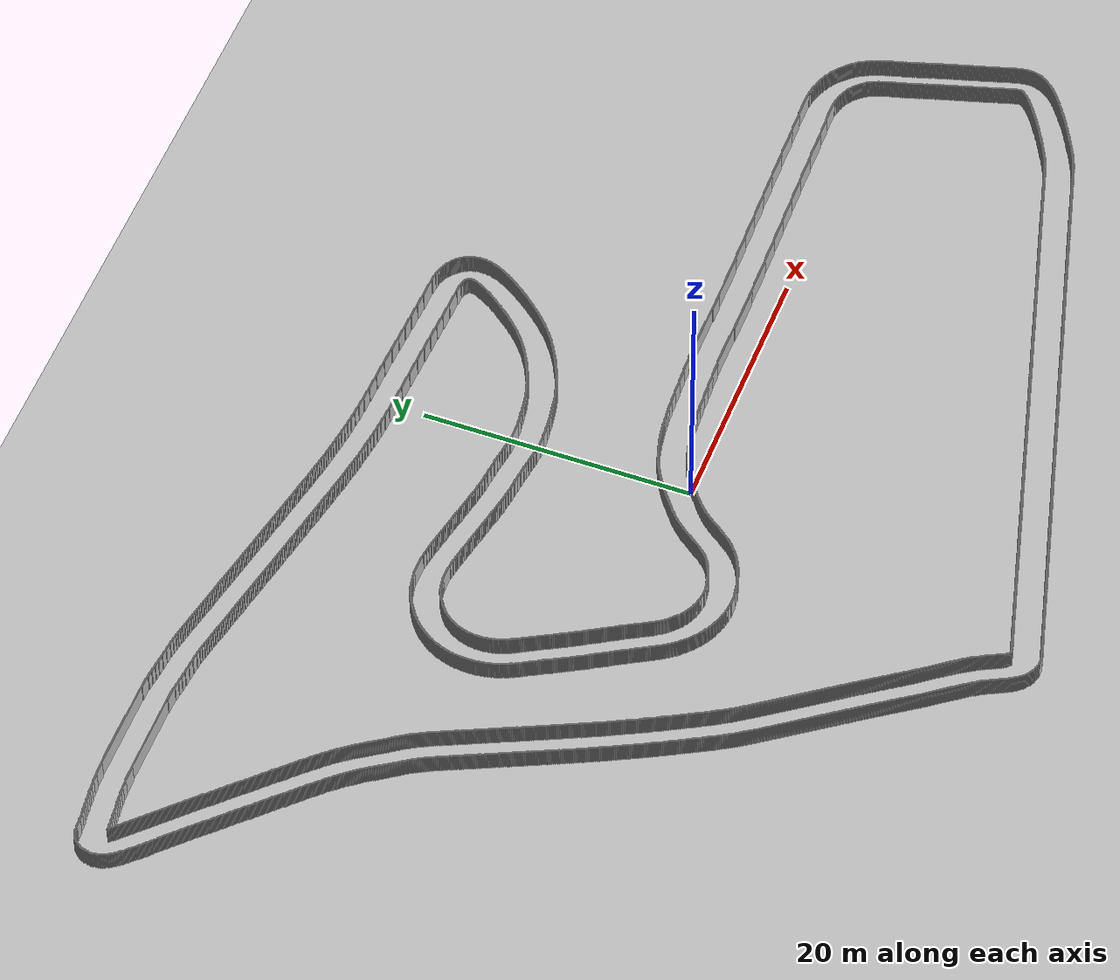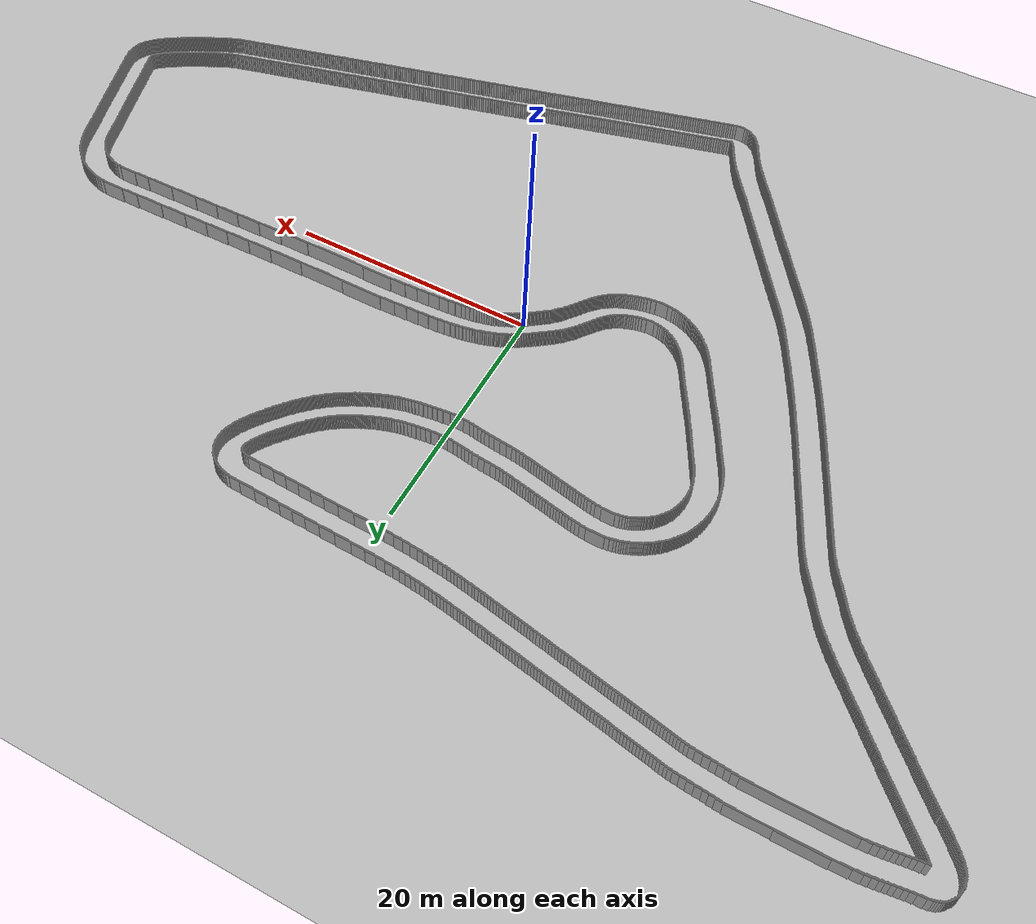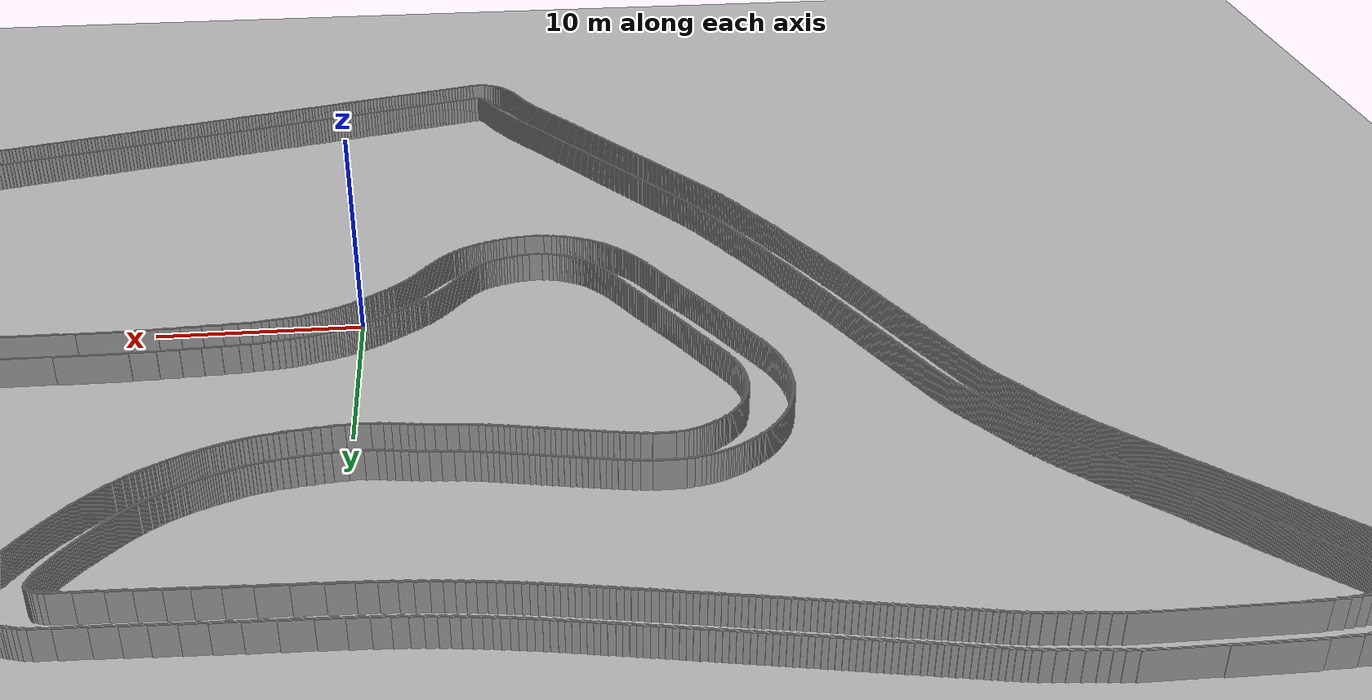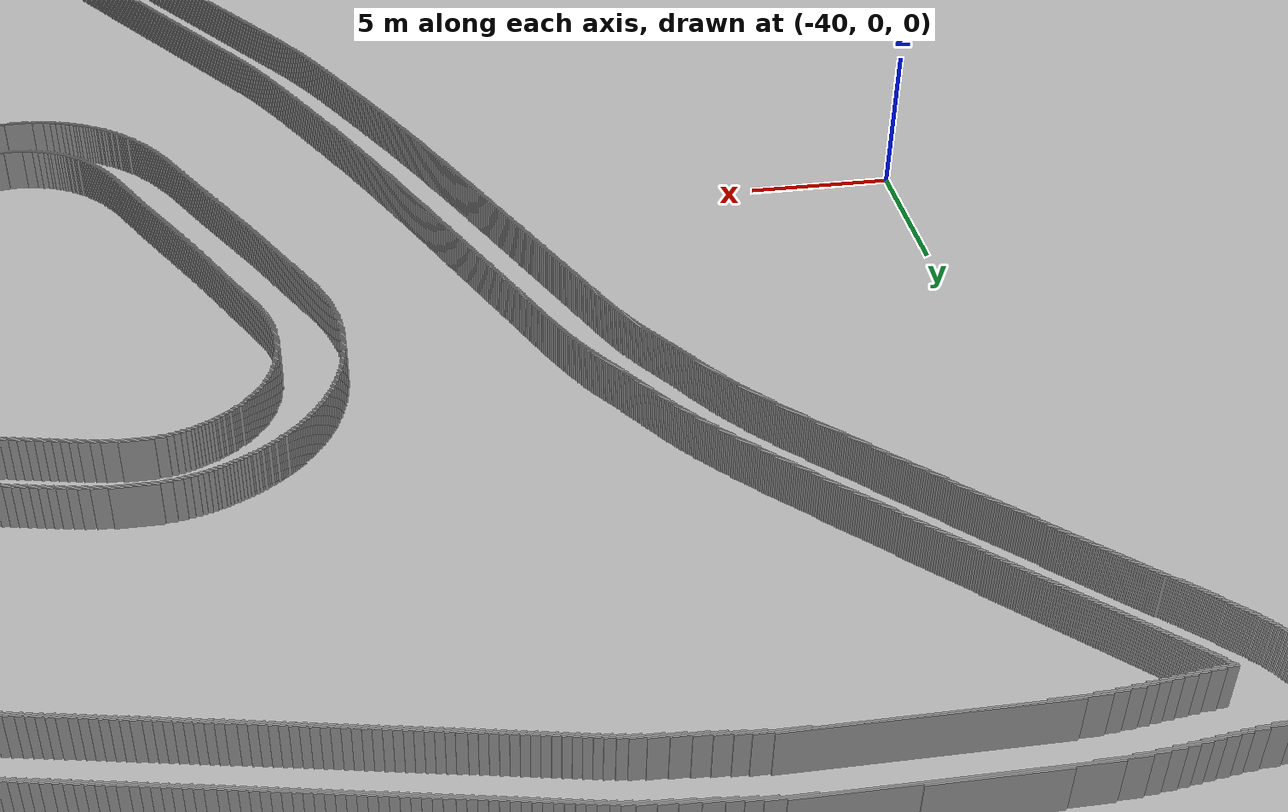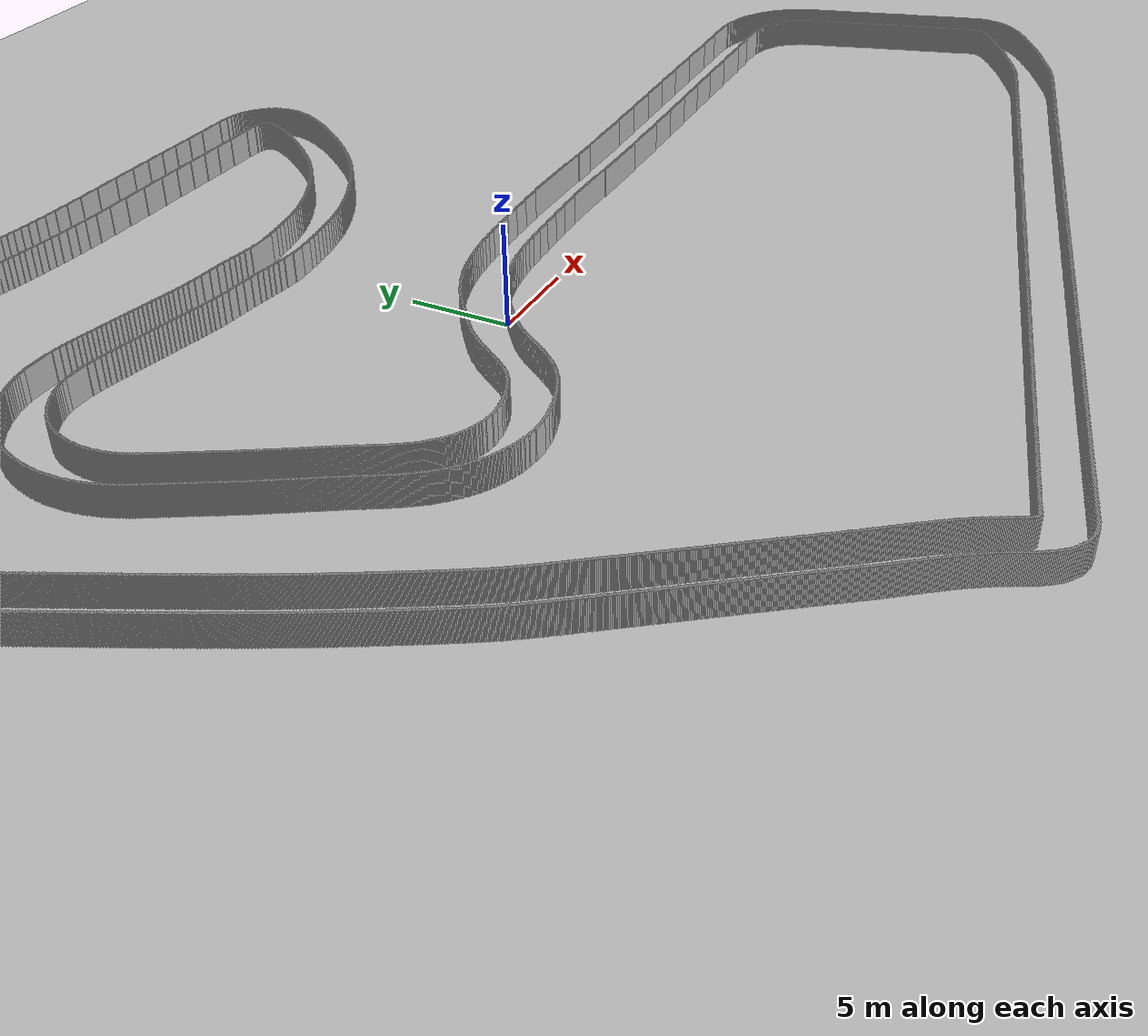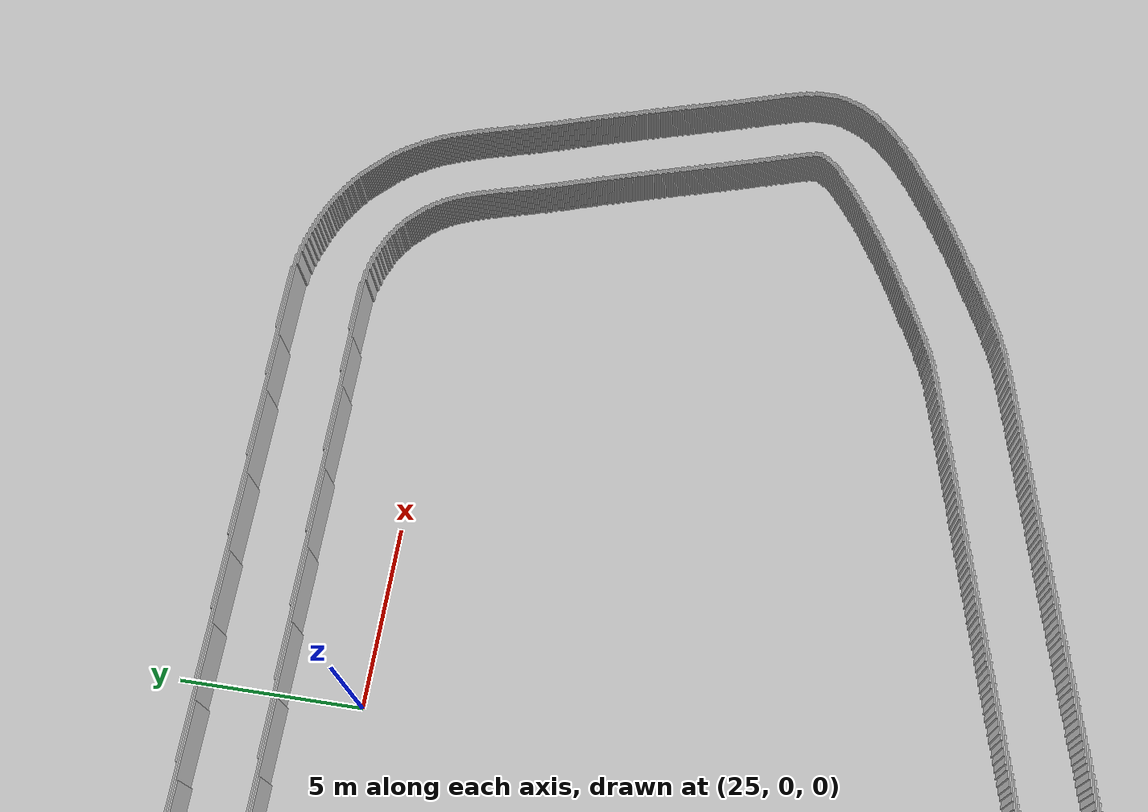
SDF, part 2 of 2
<material><ambient>0.3 0.3 0.3 1</ambient><diffuse>0.7 0.7 0.7 1</diffuse></material>
    </visual>
    <collision name="collision_2611">
     <pose>-22.325 0.25 0.75 0 0 0</pose>
     <geometry><box><size>0.15000000000000002 0.05 1.5</size></box></geometry>
    </collision>
    <visual name="visual_2611">
     <pose>-22.325 0.25 0.75 0 0 0</pose>
     <geometry><box><size>0.15000000000000002 0.05 1.5</size></box></geometry>
     <material><ambient>0.3 0.3 0.3 1</ambient><diffuse>0.7 0.7 0.7 1</diffuse></material>
    </visual>
    <collision name="collision_2612">
     <pose>-15.924999999999997 0.25 0.75 0 0 0</pose>
     <geometry><box><size>0.15000000000000002 0.05 1.5</size></box></geometry>
    </collision>
    <visual name="visual_2612">
     <pose>-15.924999999999997 0.25 0.75 0 0 0</pose>
     <geometry><box><size>0.15000000000000002 0.05 1.5</size></box></geometry>
     <material><ambient>0.3 0.3 0.3 1</ambient><diffuse>0.7 0.7 0.7 1</diffuse></material>
    </visual>
    <collision name="collision_2613">
     <pose>-13.524999999999999 0.25 0.75 0 0 0</pose>
     <geometry><box><size>0.15000000000000002 0.05 1.5</size></box></geometry>
    </collision>
    <visual name="visual_2613">
     <pose>-13.524999999999999 0.25 0.75 0 0 0</pose>
     <geometry><box><size>0.15000000000000002 0.05 1.5</size></box></geometry>
     <material><ambient>0.3 0.3 0.3 1</ambient><diffuse>0.7 0.7 0.7 1</diffuse></material>
    </visual>
    <collision name="collision_2614">
     <pose>-2.9499999999999957 0.25 0.75 0 0 0</pose>
     <geometry><box><size>0.2 0.05 1.5</size></box></geometry>
    </collision>
    <visual name="visual_2614">
     <pose>-2.9499999999999957 0.25 0.75 0 0 0</pose>
     <geometry><box><size>0.2 0.05 1.5</size></box></geometry>
     <material><ambient>0.3 0.3 0.3 1</ambient><diffuse>0.7 0.7 0.7 1</diffuse></material>
    </visual>
    <collision name="collision_2615">
     <pose>0.4750000000000014 0.25 0.75 0 0 0</pose>
     <geometry><box><size>0.25 0.05 1.5</size></box></geometry>
    </collision>
    <visual name="visual_2615">
     <pose>0.4750000000000014 0.25 0.75 0 0 0</pose>
     <geometry><box><size>0.25 0.05 1.5</size></box></geometry>
     <material><ambient>0.3 0.3 0.3 1</ambient><diffuse>0.7 0.7 0.7 1</diffuse></material>
    </visual>
    <collision name="collision_2616">
     <pose>39.72500000000001 0.25 0.75 0 0 0</pose>
     <geometry><box><size>0.15000000000000002 0.05 1.5</size></box></geometry>
    </collision>
    <visual name="visual_2616">
     <pose>39.72500000000001 0.25 0.75 0 0 0</pose>
     <geometry><box><size>0.15000000000000002 0.05 1.5</size></box></geometry>
     <material><ambient>0.3 0.3 0.3 1</ambient><diffuse>0.7 0.7 0.7 1</diffuse></material>
    </visual>
    <collision name="collision_2617">
     <pose>41.92500000000001 0.25 0.75 0 0 0</pose>
     <geometry><box><size>0.15000000000000002 0.05 1.5</size></box></geometry>
    </collision>
    <visual name="visual_2617">
     <pose>41.92500000000001 0.25 0.75 0 0 0</pose>
     <geometry><box><size>0.15000000000000002 0.05 1.5</size></box></geometry>
     <material><ambient>0.3 0.3 0.3 1</ambient><diffuse>0.7 0.7 0.7 1</diffuse></material>
    </visual>
    <collision name="collision_2618">
     <pose>-24.575 0.20000000000000284 0.75 0 0 0</pose>
     <geometry><box><size>0.15000000000000002 0.05 1.5</size></box></geometry>
    </collision>
    <visual name="visual_2618">
     <pose>-24.575 0.20000000000000284 0.75 0 0 0</pose>
     <geometry><box><size>0.15000000000000002 0.05 1.5</size></box></geometry>
     <material><ambient>0.3 0.3 0.3 1</ambient><diffuse>0.7 0.7 0.7 1</diffuse></material>
    </visual>
    <collision name="collision_2619">
     <pose>-22.325 0.20000000000000284 0.75 0 0 0</pose>
     <geometry><box><size>0.15000000000000002 0.05 1.5</size></box></geometry>
    </collision>
    <visual name="visual_2619">
     <pose>-22.325 0.20000000000000284 0.75 0 0 0</pose>
     <geometry><box><size>0.15000000000000002 0.05 1.5</size></box></geometry>
     <material><ambient>0.3 0.3 0.3 1</ambient><diffuse>0.7 0.7 0.7 1</diffuse></material>
    </visual>
    <collision name="collision_2620">
     <pose>-15.875 0.20000000000000284 0.75 0 0 0</pose>
     <geometry><box><size>0.15000000000000002 0.05 1.5</size></box></geometry>
    </collision>
    <visual name="visual_2620">
     <pose>-15.875 0.20000000000000284 0.75 0 0 0</pose>
     <geometry><box><size>0.15000000000000002 0.05 1.5</size></box></geometry>
     <material><ambient>0.3 0.3 0.3 1</ambient><diffuse>0.7 0.7 0.7 1</diffuse></material>
    </visual>
    <collision name="collision_2621">
     <pose>-13.475000000000001 0.20000000000000284 0.75 0 0 0</pose>
     <geometry><box><size>0.15000000000000002 0.05 1.5</size></box></geometry>
    </collision>
    <visual name="visual_2621">
     <pose>-13.475000000000001 0.20000000000000284 0.75 0 0 0</pose>
     <geometry><box><size>0.15000000000000002 0.05 1.5</size></box></geometry>
     <material><ambient>0.3 0.3 0.3 1</ambient><diffuse>0.7 0.7 0.7 1</diffuse></material>
    </visual>
    <collision name="collision_2622">
     <pose>-3.0 0.20000000000000284 0.75 0 0 0</pose>
     <geometry><box><size>0.2 0.05 1.5</size></box></geometry>
    </collision>
    <visual name="visual_2622">
     <pose>-3.0 0.20000000000000284 0.75 0 0 0</pose>
     <geometry><box><size>0.2 0.05 1.5</size></box></geometry>
     <material><ambient>0.3 0.3 0.3 1</ambient><diffuse>0.7 0.7 0.7 1</diffuse></material>
    </visual>
    <collision name="collision_2623">
     <pose>0.4000000000000057 0.20000000000000284 0.75 0 0 0</pose>
     <geometry><box><size>0.30000000000000004 0.05 1.5</size></box></geometry>
    </collision>
    <visual name="visual_2623">
     <pose>0.4000000000000057 0.20000000000000284 0.75 0 0 0</pose>
     <geometry><box><size>0.30000000000000004 0.05 1.5</size></box></geometry>
     <material><ambient>0.3 0.3 0.3 1</ambient><diffuse>0.7 0.7 0.7 1</diffuse></material>
    </visual>
    <collision name="collision_2624">
     <pose>39.775000000000006 0.20000000000000284 0.75 0 0 0</pose>
     <geometry><box><size>0.15000000000000002 0.05 1.5</size></box></geometry>
    </collision>
    <visual name="visual_2624">
     <pose>39.775000000000006 0.20000000000000284 0.75 0 0 0</pose>
     <geometry><box><size>0.15000000000000002 0.05 1.5</size></box></geometry>
     <material><ambient>0.3 0.3 0.3 1</ambient><diffuse>0.7 0.7 0.7 1</diffuse></material>
    </visual>
    <collision name="collision_2625">
     <pose>41.92500000000001 0.20000000000000284 0.75 0 0 0</pose>
     <geometry><box><size>0.15000000000000002 0.05 1.5</size></box></geometry>
    </collision>
    <visual name="visual_2625">
     <pose>41.92500000000001 0.20000000000000284 0.75 0 0 0</pose>
     <geometry><box><size>0.15000000000000002 0.05 1.5</size></box></geometry>
     <material><ambient>0.3 0.3 0.3 1</ambient><diffuse>0.7 0.7 0.7 1</diffuse></material>
    </visual>
    <collision name="collision_2626">
     <pose>-24.575 0.15000000000000568 0.75 0 0 0</pose>
     <geometry><box><size>0.15000000000000002 0.05 1.5</size></box></geometry>
    </collision>
    <visual name="visual_2626">
     <pose>-24.575 0.15000000000000568 0.75 0 0 0</pose>
     <geometry><box><size>0.15000000000000002 0.05 1.5</size></box></geometry>
     <material><ambient>0.3 0.3 0.3 1</ambient><diffuse>0.7 0.7 0.7 1</diffuse></material>
    </visual>
    <collision name="collision_2627">
     <pose>-22.275 0.15000000000000568 0.75 0 0 0</pose>
     <geometry><box><size>0.15000000000000002 0.05 1.5</size></box></geometry>
    </collision>
    <visual name="visual_2627">
     <pose>-22.275 0.15000000000000568 0.75 0 0 0</pose>
     <geometry><box><size>0.15000000000000002 0.05 1.5</size></box></geometry>
     <material><ambient>0.3 0.3 0.3 1</ambient><diffuse>0.7 0.7 0.7 1</diffuse></material>
    </visual>
    <collision name="collision_2628">
     <pose>-15.850000000000001 0.15000000000000568 0.75 0 0 0</pose>
     <geometry><box><size>0.2 0.05 1.5</size></box></geometry>
    </collision>
    <visual name="visual_2628">
     <pose>-15.850000000000001 0.15000000000000568 0.75 0 0 0</pose>
     <geometry><box><size>0.2 0.05 1.5</size></box></geometry>
     <material><ambient>0.3 0.3 0.3 1</ambient><diffuse>0.7 0.7 0.7 1</diffuse></material>
    </visual>
    <collision name="collision_2629">
     <pose>-13.475000000000001 0.15000000000000568 0.75 0 0 0</pose>
     <geometry><box><size>0.15000000000000002 0.05 1.5</size></box></geometry>
    </collision>
    <visual name="visual_2629">
     <pose>-13.475000000000001 0.15000000000000568 0.75 0 0 0</pose>
     <geometry><box><size>0.15000000000000002 0.05 1.5</size></box></geometry>
     <material><ambient>0.3 0.3 0.3 1</ambient><diffuse>0.7 0.7 0.7 1</diffuse></material>
    </visual>
    <collision name="collision_2630">
     <pose>-3.049999999999997 0.15000000000000568 0.75 0 0 0</pose>
     <geometry><box><size>0.2 0.05 1.5</size></box></geometry>
    </collision>
    <visual name="visual_2630">
     <pose>-3.049999999999997 0.15000000000000568 0.75 0 0 0</pose>
     <geometry><box><size>0.2 0.05 1.5</size></box></geometry>
     <material><ambient>0.3 0.3 0.3 1</ambient><diffuse>0.7 0.7 0.7 1</diffuse></material>
    </visual>
    <collision name="collision_2631">
     <pose>0.32500000000000284 0.15000000000000568 0.75 0 0 0</pose>
     <geometry><box><size>0.25 0.05 1.5</size></box></geometry>
    </collision>
    <visual name="visual_2631">
     <pose>0.32500000000000284 0.15000000000000568 0.75 0 0 0</pose>
     <geometry><box><size>0.25 0.05 1.5</size></box></geometry>
     <material><ambient>0.3 0.3 0.3 1</ambient><diffuse>0.7 0.7 0.7 1</diffuse></material>
    </visual>
    <collision name="collision_2632">
     <pose>39.775000000000006 0.15000000000000568 0.75 0 0 0</pose>
     <geometry><box><size>0.15000000000000002 0.05 1.5</size></box></geometry>
    </collision>
    <visual name="visual_2632">
     <pose>39.775000000000006 0.15000000000000568 0.75 0 0 0</pose>
     <geometry><box><size>0.15000000000000002 0.05 1.5</size></box></geometry>
     <material><ambient>0.3 0.3 0.3 1</ambient><diffuse>0.7 0.7 0.7 1</diffuse></material>
    </visual>
    <collision name="collision_2633">
     <pose>41.97500000000001 0.15000000000000568 0.75 0 0 0</pose>
     <geometry><box><size>0.15000000000000002 0.05 1.5</size></box></geometry>
    </collision>
    <visual name="visual_2633">
     <pose>41.97500000000001 0.15000000000000568 0.75 0 0 0</pose>
     <geometry><box><size>0.15000000000000002 0.05 1.5</size></box></geometry>
     <material><ambient>0.3 0.3 0.3 1</ambient><diffuse>0.7 0.7 0.7 1</diffuse></material>
    </visual>
    <collision name="collision_2634">
     <pose>-24.525 0.10000000000000142 0.75 0 0 0</pose>
     <geometry><box><size>0.15000000000000002 0.05 1.5</size></box></geometry>
    </collision>
    <visual name="visual_2634">
     <pose>-24.525 0.10000000000000142 0.75 0 0 0</pose>
     <geometry><box><size>0.15000000000000002 0.05 1.5</size></box></geometry>
     <material><ambient>0.3 0.3 0.3 1</ambient><diffuse>0.7 0.7 0.7 1</diffuse></material>
    </visual>
    <collision name="collision_2635">
     <pose>-22.275 0.10000000000000142 0.75 0 0 0</pose>
     <geometry><box><size>0.15000000000000002 0.05 1.5</size></box></geometry>
    </collision>
    <visual name="visual_2635">
     <pose>-22.275 0.10000000000000142 0.75 0 0 0</pose>
     <geometry><box><size>0.15000000000000002 0.05 1.5</size></box></geometry>
     <material><ambient>0.3 0.3 0.3 1</ambient><diffuse>0.7 0.7 0.7 1</diffuse></material>
    </visual>
    <collision name="collision_2636">
     <pose>-15.824999999999996 0.10000000000000142 0.75 0 0 0</pose>
     <geometry><box><size>0.15000000000000002 0.05 1.5</size></box></geometry>
    </collision>
    <visual name="visual_2636">
     <pose>-15.824999999999996 0.10000000000000142 0.75 0 0 0</pose>
     <geometry><box><size>0.15000000000000002 0.05 1.5</size></box></geometry>
     <material><ambient>0.3 0.3 0.3 1</ambient><diffuse>0.7 0.7 0.7 1</diffuse></material>
    </visual>
    <collision name="collision_2637">
     <pose>-13.424999999999997 0.10000000000000142 0.75 0 0 0</pose>
     <geometry><box><size>0.15000000000000002 0.05 1.5</size></box></geometry>
    </collision>
    <visual name="visual_2637">
     <pose>-13.424999999999997 0.10000000000000142 0.75 0 0 0</pose>
     <geometry><box><size>0.15000000000000002 0.05 1.5</size></box></geometry>
     <material><ambient>0.3 0.3 0.3 1</ambient><diffuse>0.7 0.7 0.7 1</diffuse></material>
    </visual>
    <collision name="collision_2638">
     <pose>-3.0999999999999943 0.10000000000000142 0.75 0 0 0</pose>
     <geometry><box><size>0.2 0.05 1.5</size></box></geometry>
    </collision>
    <visual name="visual_2638">
     <pose>-3.0999999999999943 0.10000000000000142 0.75 0 0 0</pose>
     <geometry><box><size>0.2 0.05 1.5</size></box></geometry>
     <material><ambient>0.3 0.3 0.3 1</ambient><diffuse>0.7 0.7 0.7 1</diffuse></material>
    </visual>
    <collision name="collision_2639">
     <pose>0.2750000000000057 0.10000000000000142 0.75 0 0 0</pose>
     <geometry><box><size>0.25 0.05 1.5</size></box></geometry>
    </collision>
    <visual name="visual_2639">
     <pose>0.2750000000000057 0.10000000000000142 0.75 0 0 0</pose>
     <geometry><box><size>0.25 0.05 1.5</size></box></geometry>
     <material><ambient>0.3 0.3 0.3 1</ambient><diffuse>0.7 0.7 0.7 1</diffuse></material>
    </visual>
    <collision name="collision_2640">
     <pose>39.775000000000006 0.10000000000000142 0.75 0 0 0</pose>
     <geometry><box><size>0.15000000000000002 0.05 1.5</size></box></geometry>
    </collision>
    <visual name="visual_2640">
     <pose>39.775000000000006 0.10000000000000142 0.75 0 0 0</pose>
     <geometry><box><size>0.15000000000000002 0.05 1.5</size></box></geometry>
     <material><ambient>0.3 0.3 0.3 1</ambient><diffuse>0.7 0.7 0.7 1</diffuse></material>
    </visual>
    <collision name="collision_2641">
     <pose>41.97500000000001 0.10000000000000142 0.75 0 0 0</pose>
     <geometry><box><size>0.15000000000000002 0.05 1.5</size></box></geometry>
    </collision>
    <visual name="visual_2641">
     <pose>41.97500000000001 0.10000000000000142 0.75 0 0 0</pose>
     <geometry><box><size>0.15000000000000002 0.05 1.5</size></box></geometry>
     <material><ambient>0.3 0.3 0.3 1</ambient><diffuse>0.7 0.7 0.7 1</diffuse></material>
    </visual>
    <collision name="collision_2642">
     <pose>-24.525 0.05000000000000426 0.75 0 0 0</pose>
     <geometry><box><size>0.15000000000000002 0.05 1.5</size></box></geometry>
    </collision>
    <visual name="visual_2642">
     <pose>-24.525 0.05000000000000426 0.75 0 0 0</pose>
     <geometry><box><size>0.15000000000000002 0.05 1.5</size></box></geometry>
     <material><ambient>0.3 0.3 0.3 1</ambient><diffuse>0.7 0.7 0.7 1</diffuse></material>
    </visual>
    <collision name="collision_2643">
     <pose>-22.224999999999998 0.05000000000000426 0.75 0 0 0</pose>
     <geometry><box><size>0.15000000000000002 0.05 1.5</size></box></geometry>
    </collision>
    <visual name="visual_2643">
     <pose>-22.224999999999998 0.05000000000000426 0.75 0 0 0</pose>
     <geometry><box><size>0.15000000000000002 0.05 1.5</size></box></geometry>
     <material><ambient>0.3 0.3 0.3 1</ambient><diffuse>0.7 0.7 0.7 1</diffuse></material>
    </visual>
    <collision name="collision_2644">
     <pose>-15.774999999999999 0.05000000000000426 0.75 0 0 0</pose>
     <geometry><box><size>0.15000000000000002 0.05 1.5</size></box></geometry>
    </collision>
    <visual name="visual_2644">
     <pose>-15.774999999999999 0.05000000000000426 0.75 0 0 0</pose>
     <geometry><box><size>0.15000000000000002 0.05 1.5</size></box></geometry>
     <material><ambient>0.3 0.3 0.3 1</ambient><diffuse>0.7 0.7 0.7 1</diffuse></material>
    </visual>
    <collision name="collision_2645">
     <pose>-13.424999999999997 0.05000000000000426 0.75 0 0 0</pose>
     <geometry><box><size>0.15000000000000002 0.05 1.5</size></box></geometry>
    </collision>
    <visual name="visual_2645">
     <pose>-13.424999999999997 0.05000000000000426 0.75 0 0 0</pose>
     <geometry><box><size>0.15000000000000002 0.05 1.5</size></box></geometry>
     <material><ambient>0.3 0.3 0.3 1</ambient><diffuse>0.7 0.7 0.7 1</diffuse></material>
    </visual>
    <collision name="collision_2646">
     <pose>-3.174999999999997 0.05000000000000426 0.75 0 0 0</pose>
     <geometry><box><size>0.25 0.05 1.5</size></box></geometry>
    </collision>
    <visual name="visual_2646">
     <pose>-3.174999999999997 0.05000000000000426 0.75 0 0 0</pose>
     <geometry><box><size>0.25 0.05 1.5</size></box></geometry>
     <material><ambient>0.3 0.3 0.3 1</ambient><diffuse>0.7 0.7 0.7 1</diffuse></material>
    </visual>
    <collision name="collision_2647">
     <pose>0.17500000000000426 0.05000000000000426 0.75 0 0 0</pose>
     <geometry><box><size>0.25 0.05 1.5</size></box></geometry>
    </collision>
    <visual name="visual_2647">
     <pose>0.17500000000000426 0.05000000000000426 0.75 0 0 0</pose>
     <geometry><box><size>0.25 0.05 1.5</size></box></geometry>
     <material><ambient>0.3 0.3 0.3 1</ambient><diffuse>0.7 0.7 0.7 1</diffuse></material>
    </visual>
    <collision name="collision_2648">
     <pose>39.825 0.05000000000000426 0.75 0 0 0</pose>
     <geometry><box><size>0.15000000000000002 0.05 1.5</size></box></geometry>
    </collision>
    <visual name="visual_2648">
     <pose>39.825 0.05000000000000426 0.75 0 0 0</pose>
     <geometry><box><size>0.15000000000000002 0.05 1.5</size></box></geometry>
     <material><ambient>0.3 0.3 0.3 1</ambient><diffuse>0.7 0.7 0.7 1</diffuse></material>
    </visual>
    <collision name="collision_2649">
     <pose>41.97500000000001 0.05000000000000426 0.75 0 0 0</pose>
     <geometry><box><size>0.15000000000000002 0.05 1.5</size></box></geometry>
    </collision>
    <visual name="visual_2649">
     <pose>41.97500000000001 0.05000000000000426 0.75 0 0 0</pose>
     <geometry><box><size>0.15000000000000002 0.05 1.5</size></box></geometry>
     <material><ambient>0.3 0.3 0.3 1</ambient><diffuse>0.7 0.7 0.7 1</diffuse></material>
    </visual>
    <collision name="collision_2650">
     <pose>-24.474999999999998 0.0 0.75 0 0 0</pose>
     <geometry><box><size>0.15000000000000002 0.05 1.5</size></box></geometry>
    </collision>
    <visual name="visual_2650">
     <pose>-24.474999999999998 0.0 0.75 0 0 0</pose>
     <geometry><box><size>0.15000000000000002 0.05 1.5</size></box></geometry>
     <material><ambient>0.3 0.3 0.3 1</ambient><diffuse>0.7 0.7 0.7 1</diffuse></material>
    </visual>
    <collision name="collision_2651">
     <pose>-22.224999999999998 0.0 0.75 0 0 0</pose>
     <geometry><box><size>0.15000000000000002 0.05 1.5</size></box></geometry>
    </collision>
    <visual name="visual_2651">
     <pose>-22.224999999999998 0.0 0.75 0 0 0</pose>
     <geometry><box><size>0.15000000000000002 0.05 1.5</size></box></geometry>
     <material><ambient>0.3 0.3 0.3 1</ambient><diffuse>0.7 0.7 0.7 1</diffuse></material>
    </visual>
    <collision name="collision_2652">
     <pose>-15.774999999999999 0.0 0.75 0 0 0</pose>
     <geometry><box><size>0.15000000000000002 0.05 1.5</size></box></geometry>
    </collision>
    <visual name="visual_2652">
     <pose>-15.774999999999999 0.0 0.75 0 0 0</pose>
     <geometry><box><size>0.15000000000000002 0.05 1.5</size></box></geometry>
     <material><ambient>0.3 0.3 0.3 1</ambient><diffuse>0.7 0.7 0.7 1</diffuse></material>
    </visual>
    <collision name="collision_2653">
     <pose>-13.375 0.0 0.75 0 0 0</pose>
     <geometry><box><size>0.15000000000000002 0.05 1.5</size></box></geometry>
    </collision>
    <visual name="visual_2653">
     <pose>-13.375 0.0 0.75 0 0 0</pose>
     <geometry><box><size>0.15000000000000002 0.05 1.5</size></box></geometry>
     <material><ambient>0.3 0.3 0.3 1</ambient><diffuse>0.7 0.7 0.7 1</diffuse></material>
    </visual>
    <collision name="collision_2654">
     <pose>-3.25 0.0 0.75 0 0 0</pose>
     <geometry><box><size>0.2 0.05 1.5</size></box></geometry>
    </collision>
    <visual name="visual_2654">
     <pose>-3.25 0.0 0.75 0 0 0</pose>
     <geometry><box><size>0.2 0.05 1.5</size></box></geometry>
     <material><ambient>0.3 0.3 0.3 1</ambient><diffuse>0.7 0.7 0.7 1</diffuse></material>
    </visual>
    <collision name="collision_2655">
     <pose>0.125 0.0 0.75 0 0 0</pose>
     <geometry><box><size>0.25 0.05 1.5</size></box></geometry>
    </collision>
    <visual name="visual_2655">
     <pose>0.125 0.0 0.75 0 0 0</pose>
     <geometry><box><size>0.25 0.05 1.5</size></box></geometry>
     <material><ambient>0.3 0.3 0.3 1</ambient><diffuse>0.7 0.7 0.7 1</diffuse></material>
    </visual>
    <collision name="collision_2656">
     <pose>39.825 0.0 0.75 0 0 0</pose>
     <geometry><box><size>0.15000000000000002 0.05 1.5</size></box></geometry>
    </collision>
    <visual name="visual_2656">
     <pose>39.825 0.0 0.75 0 0 0</pose>
     <geometry><box><size>0.15000000000000002 0.05 1.5</size></box></geometry>
     <material><ambient>0.3 0.3 0.3 1</ambient><diffuse>0.7 0.7 0.7 1</diffuse></material>
    </visual>
    <collision name="collision_2657">
     <pose>42.025000000000006 0.0 0.75 0 0 0</pose>
     <geometry><box><size>0.15000000000000002 0.05 1.5</size></box></geometry>
    </collision>
    <visual name="visual_2657">
     <pose>42.025000000000006 0.0 0.75 0 0 0</pose>
     <geometry><box><size>0.15000000000000002 0.05 1.5</size></box></geometry>
     <material><ambient>0.3 0.3 0.3 1</ambient><diffuse>0.7 0.7 0.7 1</diffuse></material>
    </visual>
    <collision name="collision_2658">
     <pose>-24.474999999999998 -0.04999999999999716 0.75 0 0 0</pose>
     <geometry><box><size>0.15000000000000002 0.05 1.5</size></box></geometry>
    </collision>
    <visual name="visual_2658">
     <pose>-24.474999999999998 -0.04999999999999716 0.75 0 0 0</pose>
     <geometry><box><size>0.15000000000000002 0.05 1.5</size></box></geometry>
     <material><ambient>0.3 0.3 0.3 1</ambient><diffuse>0.7 0.7 0.7 1</diffuse></material>
    </visual>
    <collision name="collision_2659">
     <pose>-22.174999999999997 -0.04999999999999716 0.75 0 0 0</pose>
     <geometry><box><size>0.15000000000000002 0.05 1.5</size></box></geometry>
    </collision>
    <visual name="visual_2659">
     <pose>-22.174999999999997 -0.04999999999999716 0.75 0 0 0</pose>
     <geometry><box><size>0.15000000000000002 0.05 1.5</size></box></geometry>
     <material><ambient>0.3 0.3 0.3 1</ambient><diffuse>0.7 0.7 0.7 1</diffuse></material>
    </visual>
    <collision name="collision_2660">
     <pose>-15.725000000000001 -0.04999999999999716 0.75 0 0 0</pose>
     <geometry><box><size>0.15000000000000002 0.05 1.5</size></box></geometry>
    </collision>
    <visual name="visual_2660">
     <pose>-15.725000000000001 -0.04999999999999716 0.75 0 0 0</pose>
     <geometry><box><size>0.15000000000000002 0.05 1.5</size></box></geometry>
     <material><ambient>0.3 0.3 0.3 1</ambient><diffuse>0.7 0.7 0.7 1</diffuse></material>
    </visual>
    <collision name="collision_2661">
     <pose>-13.350000000000001 -0.04999999999999716 0.75 0 0 0</pose>
     <geometry><box><size>0.2 0.05 1.5</size></box></geometry>
    </collision>
    <visual name="visual_2661">
     <pose>-13.350000000000001 -0.04999999999999716 0.75 0 0 0</pose>
     <geometry><box><size>0.2 0.05 1.5</size></box></geometry>
     <material><ambient>0.3 0.3 0.3 1</ambient><diffuse>0.7 0.7 0.7 1</diffuse></material>
    </visual>
    <collision name="collision_2662">
     <pose>-3.299999999999997 -0.04999999999999716 0.75 0 0 0</pose>
     <geometry><box><size>0.2 0.05 1.5</size></box></geometry>
    </collision>
    <visual name="visual_2662">
     <pose>-3.299999999999997 -0.04999999999999716 0.75 0 0 0</pose>
     <geometry><box><size>0.2 0.05 1.5</size></box></geometry>
     <material><ambient>0.3 0.3 0.3 1</ambient><diffuse>0.7 0.7 0.7 1</diffuse></material>
    </visual>
    <collision name="collision_2663">
     <pose>0.025000000000005684 -0.04999999999999716 0.75 0 0 0</pose>
     <geometry><box><size>0.25 0.05 1.5</size></box></geometry>
    </collision>
    <visual name="visual_2663">
     <pose>0.025000000000005684 -0.04999999999999716 0.75 0 0 0</pose>
     <geometry><box><size>0.25 0.05 1.5</size></box></geometry>
     <material><ambient>0.3 0.3 0.3 1</ambient><diffuse>0.7 0.7 0.7 1</diffuse></material>
    </visual>
    <collision name="collision_2664">
     <pose>39.875 -0.04999999999999716 0.75 0 0 0</pose>
     <geometry><box><size>0.15000000000000002 0.05 1.5</size></box></geometry>
    </collision>
    <visual name="visual_2664">
     <pose>39.875 -0.04999999999999716 0.75 0 0 0</pose>
     <geometry><box><size>0.15000000000000002 0.05 1.5</size></box></geometry>
     <material><ambient>0.3 0.3 0.3 1</ambient><diffuse>0.7 0.7 0.7 1</diffuse></material>
    </visual>
    <collision name="collision_2665">
     <pose>42.025000000000006 -0.04999999999999716 0.75 0 0 0</pose>
     <geometry><box><size>0.15000000000000002 0.05 1.5</size></box></geometry>
    </collision>
    <visual name="visual_2665">
     <pose>42.025000000000006 -0.04999999999999716 0.75 0 0 0</pose>
     <geometry><box><size>0.15000000000000002 0.05 1.5</size></box></geometry>
     <material><ambient>0.3 0.3 0.3 1</ambient><diffuse>0.7 0.7 0.7 1</diffuse></material>
    </visual>
    <collision name="collision_2666">
     <pose>-24.424999999999997 -0.09999999999999432 0.75 0 0 0</pose>
     <geometry><box><size>0.15000000000000002 0.05 1.5</size></box></geometry>
    </collision>
    <visual name="visual_2666">
     <pose>-24.424999999999997 -0.09999999999999432 0.75 0 0 0</pose>
     <geometry><box><size>0.15000000000000002 0.05 1.5</size></box></geometry>
     <material><ambient>0.3 0.3 0.3 1</ambient><diffuse>0.7 0.7 0.7 1</diffuse></material>
    </visual>
    <collision name="collision_2667">
     <pose>-22.174999999999997 -0.09999999999999432 0.75 0 0 0</pose>
     <geometry><box><size>0.15000000000000002 0.05 1.5</size></box></geometry>
    </collision>
    <visual name="visual_2667">
     <pose>-22.174999999999997 -0.09999999999999432 0.75 0 0 0</pose>
     <geometry><box><size>0.15000000000000002 0.05 1.5</size></box></geometry>
     <material><ambient>0.3 0.3 0.3 1</ambient><diffuse>0.7 0.7 0.7 1</diffuse></material>
    </visual>
    <collision name="collision_2668">
     <pose>-15.699999999999996 -0.09999999999999432 0.75 0 0 0</pose>
     <geometry><box><size>0.2 0.05 1.5</size></box></geometry>
    </collision>
    <visual name="visual_2668">
     <pose>-15.699999999999996 -0.09999999999999432 0.75 0 0 0</pose>
     <geometry><box><size>0.2 0.05 1.5</size></box></geometry>
     <material><ambient>0.3 0.3 0.3 1</ambient><diffuse>0.7 0.7 0.7 1</diffuse></material>
    </visual>
    <collision name="collision_2669">
     <pose>-13.324999999999996 -0.09999999999999432 0.75 0 0 0</pose>
     <geometry><box><size>0.15000000000000002 0.05 1.5</size></box></geometry>
    </collision>
    <visual name="visual_2669">
     <pose>-13.324999999999996 -0.09999999999999432 0.75 0 0 0</pose>
     <geometry><box><size>0.15000000000000002 0.05 1.5</size></box></geometry>
     <material><ambient>0.3 0.3 0.3 1</ambient><diffuse>0.7 0.7 0.7 1</diffuse></material>
    </visual>
    <collision name="collision_2670">
     <pose>-3.3499999999999943 -0.09999999999999432 0.75 0 0 0</pose>
     <geometry><box><size>0.2 0.05 1.5</size></box></geometry>
    </collision>
    <visual name="visual_2670">
     <pose>-3.3499999999999943 -0.09999999999999432 0.75 0 0 0</pose>
     <geometry><box><size>0.2 0.05 1.5</size></box></geometry>
     <material><ambient>0.3 0.3 0.3 1</ambient><diffuse>0.7 0.7 0.7 1</diffuse></material>
    </visual>
    <collision name="collision_2671">
     <pose>-0.02499999999999858 -0.09999999999999432 0.75 0 0 0</pose>
     <geometry><box><size>0.25 0.05 1.5</size></box></geometry>
    </collision>
    <visual name="visual_2671">
     <pose>-0.02499999999999858 -0.09999999999999432 0.75 0 0 0</pose>
     <geometry><box><size>0.25 0.05 1.5</size></box></geometry>
     <material><ambient>0.3 0.3 0.3 1</ambient><diffuse>0.7 0.7 0.7 1</diffuse></material>
    </visual>
    <collision name="collision_2672">
     <pose>39.875 -0.09999999999999432 0.75 0 0 0</pose>
     <geometry><box><size>0.15000000000000002 0.05 1.5</size></box></geometry>
    </collision>
    <visual name="visual_2672">
     <pose>39.875 -0.09999999999999432 0.75 0 0 0</pose>
     <geometry><box><size>0.15000000000000002 0.05 1.5</size></box></geometry>
     <material><ambient>0.3 0.3 0.3 1</ambient><diffuse>0.7 0.7 0.7 1</diffuse></material>
    </visual>
    <collision name="collision_2673">
     <pose>42.025000000000006 -0.09999999999999432 0.75 0 0 0</pose>
     <geometry><box><size>0.15000000000000002 0.05 1.5</size></box></geometry>
    </collision>
    <visual name="visual_2673">
     <pose>42.025000000000006 -0.09999999999999432 0.75 0 0 0</pose>
     <geometry><box><size>0.15000000000000002 0.05 1.5</size></box></geometry>
     <material><ambient>0.3 0.3 0.3 1</ambient><diffuse>0.7 0.7 0.7 1</diffuse></material>
    </visual>
    <collision name="collision_2674">
     <pose>-24.424999999999997 -0.14999999999999858 0.75 0 0 0</pose>
     <geometry><box><size>0.15000000000000002 0.05 1.5</size></box></geometry>
    </collision>
    <visual name="visual_2674">
     <pose>-24.424999999999997 -0.14999999999999858 0.75 0 0 0</pose>
     <geometry><box><size>0.15000000000000002 0.05 1.5</size></box></geometry>
     <material><ambient>0.3 0.3 0.3 1</ambient><diffuse>0.7 0.7 0.7 1</diffuse></material>
    </visual>
    <collision name="collision_2675">
     <pose>-22.125 -0.14999999999999858 0.75 0 0 0</pose>
     <geometry><box><size>0.15000000000000002 0.05 1.5</size></box></geometry>
    </collision>
    <visual name="visual_2675">
     <pose>-22.125 -0.14999999999999858 0.75 0 0 0</pose>
     <geometry><box><size>0.15000000000000002 0.05 1.5</size></box></geometry>
     <material><ambient>0.3 0.3 0.3 1</ambient><diffuse>0.7 0.7 0.7 1</diffuse></material>
    </visual>
    <collision name="collision_2676">
     <pose>-15.674999999999997 -0.14999999999999858 0.75 0 0 0</pose>
     <geometry><box><size>0.15000000000000002 0.05 1.5</size></box></geometry>
    </collision>
    <visual name="visual_2676">
     <pose>-15.674999999999997 -0.14999999999999858 0.75 0 0 0</pose>
     <geometry><box><size>0.15000000000000002 0.05 1.5</size></box></geometry>
     <material><ambient>0.3 0.3 0.3 1</ambient><diffuse>0.7 0.7 0.7 1</diffuse></material>
    </visual>
    <collision name="collision_2677">
     <pose>-13.274999999999999 -0.14999999999999858 0.75 0 0 0</pose>
     <geometry><box><size>0.15000000000000002 0.05 1.5</size></box></geometry>
    </collision>
    <visual name="visual_2677">
     <pose>-13.274999999999999 -0.14999999999999858 0.75 0 0 0</pose>
     <geometry><box><size>0.15000000000000002 0.05 1.5</size></box></geometry>
     <material><ambient>0.3 0.3 0.3 1</ambient><diffuse>0.7 0.7 0.7 1</diffuse></material>
    </visual>
    <collision name="collision_2678">
     <pose>-3.3999999999999986 -0.14999999999999858 0.75 0 0 0</pose>
     <geometry><box><size>0.2 0.05 1.5</size></box></geometry>
    </collision>
    <visual name="visual_2678">
     <pose>-3.3999999999999986 -0.14999999999999858 0.75 0 0 0</pose>
     <geometry><box><size>0.2 0.05 1.5</size></box></geometry>
     <material><ambient>0.3 0.3 0.3 1</ambient><diffuse>0.7 0.7 0.7 1</diffuse></material>
    </visual>
    <collision name="collision_2679">
     <pose>-0.125 -0.14999999999999858 0.75 0 0 0</pose>
     <geometry><box><size>0.25 0.05 1.5</size></box></geometry>
    </collision>
    <visual name="visual_2679">
     <pose>-0.125 -0.14999999999999858 0.75 0 0 0</pose>
     <geometry><box><size>0.25 0.05 1.5</size></box></geometry>
     <material><ambient>0.3 0.3 0.3 1</ambient><diffuse>0.7 0.7 0.7 1</diffuse></material>
    </visual>
    <collision name="collision_2680">
     <pose>39.875 -0.14999999999999858 0.75 0 0 0</pose>
     <geometry><box><size>0.15000000000000002 0.05 1.5</size></box></geometry>
    </collision>
    <visual name="visual_2680">
     <pose>39.875 -0.14999999999999858 0.75 0 0 0</pose>
     <geometry><box><size>0.15000000000000002 0.05 1.5</size></box></geometry>
     <material><ambient>0.3 0.3 0.3 1</ambient><diffuse>0.7 0.7 0.7 1</diffuse></material>
    </visual>
    <collision name="collision_2681">
     <pose>42.05000000000001 -0.14999999999999858 0.75 0 0 0</pose>
     <geometry><box><size>0.1 0.05 1.5</size></box></geometry>
    </collision>
    <visual name="visual_2681">
     <pose>42.05000000000001 -0.14999999999999858 0.75 0 0 0</pose>
     <geometry><box><size>0.1 0.05 1.5</size></box></geometry>
     <material><ambient>0.3 0.3 0.3 1</ambient><diffuse>0.7 0.7 0.7 1</diffuse></material>
    </visual>
    <collision name="collision_2682">
     <pose>-24.375 -0.19999999999999574 0.75 0 0 0</pose>
     <geometry><box><size>0.15000000000000002 0.05 1.5</size></box></geometry>
    </collision>
    <visual name="visual_2682">
     <pose>-24.375 -0.19999999999999574 0.75 0 0 0</pose>
     <geometry><box><size>0.15000000000000002 0.05 1.5</size></box></geometry>
     <material><ambient>0.3 0.3 0.3 1</ambient><diffuse>0.7 0.7 0.7 1</diffuse></material>
    </visual>
    <collision name="collision_2683">
     <pose>-22.125 -0.19999999999999574 0.75 0 0 0</pose>
     <geometry><box><size>0.15000000000000002 0.05 1.5</size></box></geometry>
    </collision>
    <visual name="visual_2683">
     <pose>-22.125 -0.19999999999999574 0.75 0 0 0</pose>
     <geometry><box><size>0.15000000000000002 0.05 1.5</size></box></geometry>
     <material><ambient>0.3 0.3 0.3 1</ambient><diffuse>0.7 0.7 0.7 1</diffuse></material>
    </visual>
    <collision name="collision_2684">
     <pose>-15.649999999999999 -0.19999999999999574 0.75 0 0 0</pose>
     <geometry><box><size>0.2 0.05 1.5</size></box></geometry>
    </collision>
    <visual name="visual_2684">
     <pose>-15.649999999999999 -0.19999999999999574 0.75 0 0 0</pose>
     <geometry><box><size>0.2 0.05 1.5</size></box></geometry>
     <material><ambient>0.3 0.3 0.3 1</ambient><diffuse>0.7 0.7 0.7 1</diffuse></material>
    </visual>
    <collision name="collision_2685">
     <pose>-13.274999999999999 -0.19999999999999574 0.75 0 0 0</pose>
     <geometry><box><size>0.15000000000000002 0.05 1.5</size></box></geometry>
    </collision>
    <visual name="visual_2685">
     <pose>-13.274999999999999 -0.19999999999999574 0.75 0 0 0</pose>
     <geometry><box><size>0.15000000000000002 0.05 1.5</size></box></geometry>
     <material><ambient>0.3 0.3 0.3 1</ambient><diffuse>0.7 0.7 0.7 1</diffuse></material>
    </visual>
    <collision name="collision_2686">
     <pose>-3.4499999999999957 -0.19999999999999574 0.75 0 0 0</pose>
     <geometry><box><size>0.2 0.05 1.5</size></box></geometry>
    </collision>
    <visual name="visual_2686">
     <pose>-3.4499999999999957 -0.19999999999999574 0.75 0 0 0</pose>
     <geometry><box><size>0.2 0.05 1.5</size></box></geometry>
     <material><ambient>0.3 0.3 0.3 1</ambient><diffuse>0.7 0.7 0.7 1</diffuse></material>
    </visual>
    <collision name="collision_2687">
     <pose>-0.17499999999999716 -0.19999999999999574 0.75 0 0 0</pose>
     <geometry><box><size>0.25 0.05 1.5</size></box></geometry>
    </collision>
    <visual name="visual_2687">
     <pose>-0.17499999999999716 -0.19999999999999574 0.75 0 0 0</pose>
     <geometry><box><size>0.25 0.05 1.5</size></box></geometry>
     <material><ambient>0.3 0.3 0.3 1</ambient><diffuse>0.7 0.7 0.7 1</diffuse></material>
    </visual>
    <collision name="collision_2688">
     <pose>39.92500000000001 -0.19999999999999574 0.75 0 0 0</pose>
     <geometry><box><size>0.15000000000000002 0.05 1.5</size></box></geometry>
    </collision>
    <visual name="visual_2688">
     <pose>39.92500000000001 -0.19999999999999574 0.75 0 0 0</pose>
     <geometry><box><size>0.15000000000000002 0.05 1.5</size></box></geometry>
     <material><ambient>0.3 0.3 0.3 1</ambient><diffuse>0.7 0.7 0.7 1</diffuse></material>
    </visual>
    <collision name="collision_2689">
     <pose>42.075 -0.19999999999999574 0.75 0 0 0</pose>
     <geometry><box><size>0.15000000000000002 0.05 1.5</size></box></geometry>
    </collision>
    <visual name="visual_2689">
     <pose>42.075 -0.19999999999999574 0.75 0 0 0</pose>
     <geometry><box><size>0.15000000000000002 0.05 1.5</size></box></geometry>
     <material><ambient>0.3 0.3 0.3 1</ambient><diffuse>0.7 0.7 0.7 1</diffuse></material>
    </visual>
    <collision name="collision_2690">
     <pose>-24.375 -0.25 0.75 0 0 0</pose>
     <geometry><box><size>0.15000000000000002 0.05 1.5</size></box></geometry>
    </collision>
    <visual name="visual_2690">
     <pose>-24.375 -0.25 0.75 0 0 0</pose>
     <geometry><box><size>0.15000000000000002 0.05 1.5</size></box></geometry>
     <material><ambient>0.3 0.3 0.3 1</ambient><diffuse>0.7 0.7 0.7 1</diffuse></material>
    </visual>
    <collision name="collision_2691">
     <pose>-22.099999999999998 -0.25 0.75 0 0 0</pose>
     <geometry><box><size>0.2 0.05 1.5</size></box></geometry>
    </collision>
    <visual name="visual_2691">
     <pose>-22.099999999999998 -0.25 0.75 0 0 0</pose>
     <geometry><box><size>0.2 0.05 1.5</size></box></geometry>
     <material><ambient>0.3 0.3 0.3 1</ambient><diffuse>0.7 0.7 0.7 1</diffuse></material>
    </visual>
    <collision name="collision_2692">
     <pose>-15.625 -0.25 0.75 0 0 0</pose>
     <geometry><box><size>0.15000000000000002 0.05 1.5</size></box></geometry>
    </collision>
    <visual name="visual_2692">
     <pose>-15.625 -0.25 0.75 0 0 0</pose>
     <geometry><box><size>0.15000000000000002 0.05 1.5</size></box></geometry>
     <material><ambient>0.3 0.3 0.3 1</ambient><diffuse>0.7 0.7 0.7 1</diffuse></material>
    </visual>
    <collision name="collision_2693">
     <pose>-13.225000000000001 -0.25 0.75 0 0 0</pose>
     <geometry><box><size>0.15000000000000002 0.05 1.5</size></box></geometry>
    </collision>
    <visual name="visual_2693">
     <pose>-13.225000000000001 -0.25 0.75 0 0 0</pose>
     <geometry><box><size>0.15000000000000002 0.05 1.5</size></box></geometry>
     <material><ambient>0.3 0.3 0.3 1</ambient><diffuse>0.7 0.7 0.7 1</diffuse></material>
    </visual>
    <collision name="collision_2694">
     <pose>-3.5 -0.25 0.75 0 0 0</pose>
     <geometry><box><size>0.2 0.05 1.5</size></box></geometry>
    </collision>
    <visual name="visual_2694">
     <pose>-3.5 -0.25 0.75 0 0 0</pose>
     <geometry><box><size>0.2 0.05 1.5</size></box></geometry>
     <material><ambient>0.3 0.3 0.3 1</ambient><diffuse>0.7 0.7 0.7 1</diffuse></material>
    </visual>
    <collision name="collision_2695">
     <pose>-0.25 -0.25 0.75 0 0 0</pose>
     <geometry><box><size>0.2 0.05 1.5</size></box></geometry>
    </collision>
    <visual name="visual_2695">
     <pose>-0.25 -0.25 0.75 0 0 0</pose>
     <geometry><box><size>0.2 0.05 1.5</size></box></geometry>
     <material><ambient>0.3 0.3 0.3 1</ambient><diffuse>0.7 0.7 0.7 1</diffuse></material>
    </visual>
    <collision name="collision_2696">
     <pose>39.92500000000001 -0.25 0.75 0 0 0</pose>
     <geometry><box><size>0.15000000000000002 0.05 1.5</size></box></geometry>
    </collision>
    <visual name="visual_2696">
     <pose>39.92500000000001 -0.25 0.75 0 0 0</pose>
     <geometry><box><size>0.15000000000000002 0.05 1.5</size></box></geometry>
     <material><ambient>0.3 0.3 0.3 1</ambient><diffuse>0.7 0.7 0.7 1</diffuse></material>
    </visual>
    <collision name="collision_2697">
     <pose>42.075 -0.25 0.75 0 0 0</pose>
     <geometry><box><size>0.15000000000000002 0.05 1.5</size></box></geometry>
    </collision>
    <visual name="visual_2697">
     <pose>42.075 -0.25 0.75 0 0 0</pose>
     <geometry><box><size>0.15000000000000002 0.05 1.5</size></box></geometry>
     <material><ambient>0.3 0.3 0.3 1</ambient><diffuse>0.7 0.7 0.7 1</diffuse></material>
    </visual>
    <collision name="collision_2698">
     <pose>-24.349999999999998 -0.29999999999999716 0.75 0 0 0</pose>
     <geometry><box><size>0.2 0.05 1.5</size></box></geometry>
    </collision>
    <visual name="visual_2698">
     <pose>-24.349999999999998 -0.29999999999999716 0.75 0 0 0</pose>
     <geometry><box><size>0.2 0.05 1.5</size></box></geometry>
     <material><ambient>0.3 0.3 0.3 1</ambient><diffuse>0.7 0.7 0.7 1</diffuse></material>
    </visual>
    <collision name="collision_2699">
     <pose>-22.075 -0.29999999999999716 0.75 0 0 0</pose>
     <geometry><box><size>0.15000000000000002 0.05 1.5</size></box></geometry>
    </collision>
    <visual name="visual_2699">
     <pose>-22.075 -0.29999999999999716 0.75 0 0 0</pose>
     <geometry><box><size>0.15000000000000002 0.05 1.5</size></box></geometry>
     <material><ambient>0.3 0.3 0.3 1</ambient><diffuse>0.7 0.7 0.7 1</diffuse></material>
    </visual>
    <collision name="collision_2700">
     <pose>-15.574999999999996 -0.29999999999999716 0.75 0 0 0</pose>
     <geometry><box><size>0.15000000000000002 0.05 1.5</size></box></geometry>
    </collision>
    <visual name="visual_2700">
     <pose>-15.574999999999996 -0.29999999999999716 0.75 0 0 0</pose>
     <geometry><box><size>0.15000000000000002 0.05 1.5</size></box></geometry>
     <material><ambient>0.3 0.3 0.3 1</ambient><diffuse>0.7 0.7 0.7 1</diffuse></material>
    </visual>
    <collision name="collision_2701">
     <pose>-13.225000000000001 -0.29999999999999716 0.75 0 0 0</pose>
     <geometry><box><size>0.15000000000000002 0.05 1.5</size></box></geometry>
    </collision>
    <visual name="visual_2701">
     <pose>-13.225000000000001 -0.29999999999999716 0.75 0 0 0</pose>
     <geometry><box><size>0.15000000000000002 0.05 1.5</size></box></geometry>
     <material><ambient>0.3 0.3 0.3 1</ambient><diffuse>0.7 0.7 0.7 1</diffuse></material>
    </visual>
    <collision name="collision_2702">
     <pose>-3.5249999999999986 -0.29999999999999716 0.75 0 0 0</pose>
     <geometry><box><size>0.15000000000000002 0.05 1.5</size></box></geometry>
    </collision>
    <visual name="visual_2702">
     <pose>-3.5249999999999986 -0.29999999999999716 0.75 0 0 0</pose>
     <geometry><box><size>0.15000000000000002 0.05 1.5</size></box></geometry>
     <material><ambient>0.3 0.3 0.3 1</ambient><diffuse>0.7 0.7 0.7 1</diffuse></material>
    </visual>
    <collision name="collision_2703">
     <pose>-0.32499999999999574 -0.29999999999999716 0.75 0 0 0</pose>
     <geometry><box><size>0.25 0.05 1.5</size></box></geometry>
    </collision>
    <visual name="visual_2703">
     <pose>-0.32499999999999574 -0.29999999999999716 0.75 0 0 0</pose>
     <geometry><box><size>0.25 0.05 1.5</size></box></geometry>
     <material><ambient>0.3 0.3 0.3 1</ambient><diffuse>0.7 0.7 0.7 1</diffuse></material>
    </visual>
    <collision name="collision_2704">
     <pose>39.92500000000001 -0.29999999999999716 0.75 0 0 0</pose>
     <geometry><box><size>0.15000000000000002 0.05 1.5</size></box></geometry>
    </collision>
    <visual name="visual_2704">
     <pose>39.92500000000001 -0.29999999999999716 0.75 0 0 0</pose>
     <geometry><box><size>0.15000000000000002 0.05 1.5</size></box></geometry>
     <material><ambient>0.3 0.3 0.3 1</ambient><diffuse>0.7 0.7 0.7 1</diffuse></material>
    </visual>
    <collision name="collision_2705">
     <pose>42.075 -0.29999999999999716 0.75 0 0 0</pose>
     <geometry><box><size>0.15000000000000002 0.05 1.5</size></box></geometry>
    </collision>
    <visual name="visual_2705">
     <pose>42.075 -0.29999999999999716 0.75 0 0 0</pose>
     <geometry><box><size>0.15000000000000002 0.05 1.5</size></box></geometry>
     <material><ambient>0.3 0.3 0.3 1</ambient><diffuse>0.7 0.7 0.7 1</diffuse></material>
    </visual>
    <collision name="collision_2706">
     <pose>-24.325 -0.3499999999999943 0.75 0 0 0</pose>
     <geometry><box><size>0.15000000000000002 0.05 1.5</size></box></geometry>
    </collision>
    <visual name="visual_2706">
     <pose>-24.325 -0.3499999999999943 0.75 0 0 0</pose>
     <geometry><box><size>0.15000000000000002 0.05 1.5</size></box></geometry>
     <material><ambient>0.3 0.3 0.3 1</ambient><diffuse>0.7 0.7 0.7 1</diffuse></material>
    </visual>
    <collision name="collision_2707">
     <pose>-22.075 -0.3499999999999943 0.75 0 0 0</pose>
     <geometry><box><size>0.15000000000000002 0.05 1.5</size></box></geometry>
    </collision>
    <visual name="visual_2707">
     <pose>-22.075 -0.3499999999999943 0.75 0 0 0</pose>
     <geometry><box><size>0.15000000000000002 0.05 1.5</size></box></geometry>
     <material><ambient>0.3 0.3 0.3 1</ambient><diffuse>0.7 0.7 0.7 1</diffuse></material>
    </visual>
    <collision name="collision_2708">
     <pose>-15.574999999999996 -0.3499999999999943 0.75 0 0 0</pose>
     <geometry><box><size>0.15000000000000002 0.05 1.5</size></box></geometry>
    </collision>
    <visual name="visual_2708">
     <pose>-15.574999999999996 -0.3499999999999943 0.75 0 0 0</pose>
     <geometry><box><size>0.15000000000000002 0.05 1.5</size></box></geometry>
     <material><ambient>0.3 0.3 0.3 1</ambient><diffuse>0.7 0.7 0.7 1</diffuse></material>
    </visual>
    <collision name="collision_2709">
     <pose>-13.174999999999997 -0.3499999999999943 0.75 0 0 0</pose>
     <geometry><box><size>0.15000000000000002 0.05 1.5</size></box></geometry>
    </collision>
    <visual name="visual_2709">
     <pose>-13.174999999999997 -0.3499999999999943 0.75 0 0 0</pose>
     <geometry><box><size>0.15000000000000002 0.05 1.5</size></box></geometry>
     <material><ambient>0.3 0.3 0.3 1</ambient><diffuse>0.7 0.7 0.7 1</diffuse></material>
    </visual>
    <collision name="collision_2710">
     <pose>-3.5749999999999957 -0.3499999999999943 0.75 0 0 0</pose>
     <geometry><box><size>0.15000000000000002 0.05 1.5</size></box></geometry>
    </collision>
    <visual name="visual_2710">
     <pose>-3.5749999999999957 -0.3499999999999943 0.75 0 0 0</pose>
     <geometry><box><size>0.15000000000000002 0.05 1.5</size></box></geometry>
     <material><ambient>0.3 0.3 0.3 1</ambient><diffuse>0.7 0.7 0.7 1</diffuse></material>
    </visual>
    <collision name="collision_2711">
     <pose>-0.375 -0.3499999999999943 0.75 0 0 0</pose>
     <geometry><box><size>0.25 0.05 1.5</size></box></geometry>
    </collision>
    <visual name="visual_2711">
     <pose>-0.375 -0.3499999999999943 0.75 0 0 0</pose>
     <geometry><box><size>0.25 0.05 1.5</size></box></geometry>
     <material><ambient>0.3 0.3 0.3 1</ambient><diffuse>0.7 0.7 0.7 1</diffuse></material>
    </visual>
    <collision name="collision_2712">
     <pose>39.97500000000001 -0.3499999999999943 0.75 0 0 0</pose>
     <geometry><box><size>0.15000000000000002 0.05 1.5</size></box></geometry>
    </collision>
    <visual name="visual_2712">
     <pose>39.97500000000001 -0.3499999999999943 0.75 0 0 0</pose>
     <geometry><box><size>0.15000000000000002 0.05 1.5</size></box></geometry>
     <material><ambient>0.3 0.3 0.3 1</ambient><diffuse>0.7 0.7 0.7 1</diffuse></material>
    </visual>
    <collision name="collision_2713">
     <pose>42.125 -0.3499999999999943 0.75 0 0 0</pose>
     <geometry><box><size>0.15000000000000002 0.05 1.5</size></box></geometry>
    </collision>
    <visual name="visual_2713">
     <pose>42.125 -0.3499999999999943 0.75 0 0 0</pose>
     <geometry><box><size>0.15000000000000002 0.05 1.5</size></box></geometry>
     <material><ambient>0.3 0.3 0.3 1</ambient><diffuse>0.7 0.7 0.7 1</diffuse></material>
    </visual>
    <collision name="collision_2714">
     <pose>-24.325 -0.3999999999999986 0.75 0 0 0</pose>
     <geometry><box><size>0.15000000000000002 0.05 1.5</size></box></geometry>
    </collision>
    <visual name="visual_2714">
     <pose>-24.325 -0.3999999999999986 0.75 0 0 0</pose>
     <geometry><box><size>0.15000000000000002 0.05 1.5</size></box></geometry>
     <material><ambient>0.3 0.3 0.3 1</ambient><diffuse>0.7 0.7 0.7 1</diffuse></material>
    </visual>
    <collision name="collision_2715">
     <pose>-22.025 -0.3999999999999986 0.75 0 0 0</pose>
     <geometry><box><size>0.15000000000000002 0.05 1.5</size></box></geometry>
    </collision>
    <visual name="visual_2715">
     <pose>-22.025 -0.3999999999999986 0.75 0 0 0</pose>
     <geometry><box><size>0.15000000000000002 0.05 1.5</size></box></geometry>
     <material><ambient>0.3 0.3 0.3 1</ambient><diffuse>0.7 0.7 0.7 1</diffuse></material>
    </visual>
    <collision name="collision_2716">
     <pose>-15.524999999999999 -0.3999999999999986 0.75 0 0 0</pose>
     <geometry><box><size>0.15000000000000002 0.05 1.5</size></box></geometry>
    </collision>
    <visual name="visual_2716">
     <pose>-15.524999999999999 -0.3999999999999986 0.75 0 0 0</pose>
     <geometry><box><size>0.15000000000000002 0.05 1.5</size></box></geometry>
     <material><ambient>0.3 0.3 0.3 1</ambient><diffuse>0.7 0.7 0.7 1</diffuse></material>
    </visual>
    <collision name="collision_2717">
     <pose>-13.149999999999999 -0.3999999999999986 0.75 0 0 0</pose>
     <geometry><box><size>0.2 0.05 1.5</size></box></geometry>
    </collision>
    <visual name="visual_2717">
     <pose>-13.149999999999999 -0.3999999999999986 0.75 0 0 0</pose>
     <geometry><box><size>0.2 0.05 1.5</size></box></geometry>
     <material><ambient>0.3 0.3 0.3 1</ambient><diffuse>0.7 0.7 0.7 1</diffuse></material>
    </visual>
    <collision name="collision_2718">
     <pose>-3.625 -0.3999999999999986 0.75 0 0 0</pose>
     <geometry><box><size>0.15000000000000002 0.05 1.5</size></box></geometry>
    </collision>
    <visual name="visual_2718">
     <pose>-3.625 -0.3999999999999986 0.75 0 0 0</pose>
     <geometry><box><size>0.15000000000000002 0.05 1.5</size></box></geometry>
     <material><ambient>0.3 0.3 0.3 1</ambient><diffuse>0.7 0.7 0.7 1</diffuse></material>
    </visual>
    <collision name="collision_2719">
     <pose>-0.44999999999999574 -0.3999999999999986 0.75 0 0 0</pose>
     <geometry><box><size>0.2 0.05 1.5</size></box></geometry>
    </collision>
    <visual name="visual_2719">
     <pose>-0.44999999999999574 -0.3999999999999986 0.75 0 0 0</pose>
     <geometry><box><size>0.2 0.05 1.5</size></box></geometry>
     <material><ambient>0.3 0.3 0.3 1</ambient><diffuse>0.7 0.7 0.7 1</diffuse></material>
    </visual>
    <collision name="collision_2720">
     <pose>39.97500000000001 -0.3999999999999986 0.75 0 0 0</pose>
     <geometry><box><size>0.15000000000000002 0.05 1.5</size></box></geometry>
    </collision>
    <visual name="visual_2720">
     <pose>39.97500000000001 -0.3999999999999986 0.75 0 0 0</pose>
     <geometry><box><size>0.15000000000000002 0.05 1.5</size></box></geometry>
     <material><ambient>0.3 0.3 0.3 1</ambient><diffuse>0.7 0.7 0.7 1</diffuse></material>
    </visual>
    <collision name="collision_2721">
     <pose>42.125 -0.3999999999999986 0.75 0 0 0</pose>
     <geometry><box><size>0.15000000000000002 0.05 1.5</size></box></geometry>
    </collision>
    <visual name="visual_2721">
     <pose>42.125 -0.3999999999999986 0.75 0 0 0</pose>
     <geometry><box><size>0.15000000000000002 0.05 1.5</size></box></geometry>
     <material><ambient>0.3 0.3 0.3 1</ambient><diffuse>0.7 0.7 0.7 1</diffuse></material>
    </visual>
    <collision name="collision_2722">
     <pose>-24.275 -0.44999999999999574 0.75 0 0 0</pose>
     <geometry><box><size>0.15000000000000002 0.05 1.5</size></box></geometry>
    </collision>
    <visual name="visual_2722">
     <pose>-24.275 -0.44999999999999574 0.75 0 0 0</pose>
     <geometry><box><size>0.15000000000000002 0.05 1.5</size></box></geometry>
     <material><ambient>0.3 0.3 0.3 1</ambient><diffuse>0.7 0.7 0.7 1</diffuse></material>
    </visual>
    <collision name="collision_2723">
     <pose>-22.025 -0.44999999999999574 0.75 0 0 0</pose>
     <geometry><box><size>0.15000000000000002 0.05 1.5</size></box></geometry>
    </collision>
    <visual name="visual_2723">
     <pose>-22.025 -0.44999999999999574 0.75 0 0 0</pose>
     <geometry><box><size>0.15000000000000002 0.05 1.5</size></box></geometry>
     <material><ambient>0.3 0.3 0.3 1</ambient><diffuse>0.7 0.7 0.7 1</diffuse></material>
    </visual>
    <collision name="collision_2724">
     <pose>-15.5 -0.44999999999999574 0.75 0 0 0</pose>
     <geometry><box><size>0.2 0.05 1.5</size></box></geometry>
    </collision>
    <visual name="visual_2724">
     <pose>-15.5 -0.44999999999999574 0.75 0 0 0</pose>
     <geometry><box><size>0.2 0.05 1.5</size></box></geometry>
     <material><ambient>0.3 0.3 0.3 1</ambient><diffuse>0.7 0.7 0.7 1</diffuse></material>
    </visual>
    <collision name="collision_2725">
     <pose>-13.125 -0.44999999999999574 0.75 0 0 0</pose>
     <geometry><box><size>0.15000000000000002 0.05 1.5</size></box></geometry>
    </collision>
    <visual name="visual_2725">
     <pose>-13.125 -0.44999999999999574 0.75 0 0 0</pose>
     <geometry><box><size>0.15000000000000002 0.05 1.5</size></box></geometry>
     <material><ambient>0.3 0.3 0.3 1</ambient><diffuse>0.7 0.7 0.7 1</diffuse></material>
    </visual>
    <collision name="collision_2726">
     <pose>-3.674999999999997 -0.44999999999999574 0.75 0 0 0</pose>
     <geometry><box><size>0.15000000000000002 0.05 1.5</size></box></geometry>
    </collision>
    <visual name="visual_2726">
     <pose>-3.674999999999997 -0.44999999999999574 0.75 0 0 0</pose>
     <geometry><box><size>0.15000000000000002 0.05 1.5</size></box></geometry>
     <material><ambient>0.3 0.3 0.3 1</ambient><diffuse>0.7 0.7 0.7 1</diffuse></material>
    </visual>
    <collision name="collision_2727">
     <pose>-0.5 -0.44999999999999574 0.75 0 0 0</pose>
     <geometry><box><size>0.2 0.05 1.5</size></box></geometry>
    </collision>
    <visual name="visual_2727">
     <pose>-0.5 -0.44999999999999574 0.75 0 0 0</pose>
     <geometry><box><size>0.2 0.05 1.5</size></box></geometry>
     <material><ambient>0.3 0.3 0.3 1</ambient><diffuse>0.7 0.7 0.7 1</diffuse></material>
    </visual>
    <collision name="collision_2728">
     <pose>39.97500000000001 -0.44999999999999574 0.75 0 0 0</pose>
     <geometry><box><size>0.15000000000000002 0.05 1.5</size></box></geometry>
    </collision>
    <visual name="visual_2728">
     <pose>39.97500000000001 -0.44999999999999574 0.75 0 0 0</pose>
     <geometry><box><size>0.15000000000000002 0.05 1.5</size></box></geometry>
     <material><ambient>0.3 0.3 0.3 1</ambient><diffuse>0.7 0.7 0.7 1</diffuse></material>
    </visual>
    <collision name="collision_2729">
     <pose>42.125 -0.44999999999999574 0.75 0 0 0</pose>
     <geometry><box><size>0.15000000000000002 0.05 1.5</size></box></geometry>
    </collision>
    <visual name="visual_2729">
     <pose>42.125 -0.44999999999999574 0.75 0 0 0</pose>
     <geometry><box><size>0.15000000000000002 0.05 1.5</size></box></geometry>
     <material><ambient>0.3 0.3 0.3 1</ambient><diffuse>0.7 0.7 0.7 1</diffuse></material>
    </visual>
    <collision name="collision_2730">
     <pose>-24.275 -0.5 0.75 0 0 0</pose>
     <geometry><box><size>0.15000000000000002 0.05 1.5</size></box></geometry>
    </collision>
    <visual name="visual_2730">
     <pose>-24.275 -0.5 0.75 0 0 0</pose>
     <geometry><box><size>0.15000000000000002 0.05 1.5</size></box></geometry>
     <material><ambient>0.3 0.3 0.3 1</ambient><diffuse>0.7 0.7 0.7 1</diffuse></material>
    </visual>
    <collision name="collision_2731">
     <pose>-21.974999999999998 -0.5 0.75 0 0 0</pose>
     <geometry><box><size>0.15000000000000002 0.05 1.5</size></box></geometry>
    </collision>
    <visual name="visual_2731">
     <pose>-21.974999999999998 -0.5 0.75 0 0 0</pose>
     <geometry><box><size>0.15000000000000002 0.05 1.5</size></box></geometry>
     <material><ambient>0.3 0.3 0.3 1</ambient><diffuse>0.7 0.7 0.7 1</diffuse></material>
    </visual>
    <collision name="collision_2732">
     <pose>-15.475000000000001 -0.5 0.75 0 0 0</pose>
     <geometry><box><size>0.15000000000000002 0.05 1.5</size></box></geometry>
    </collision>
    <visual name="visual_2732">
     <pose>-15.475000000000001 -0.5 0.75 0 0 0</pose>
     <geometry><box><size>0.15000000000000002 0.05 1.5</size></box></geometry>
     <material><ambient>0.3 0.3 0.3 1</ambient><diffuse>0.7 0.7 0.7 1</diffuse></material>
    </visual>
    <collision name="collision_2733">
     <pose>-13.074999999999996 -0.5 0.75 0 0 0</pose>
     <geometry><box><size>0.15000000000000002 0.05 1.5</size></box></geometry>
    </collision>
    <visual name="visual_2733">
     <pose>-13.074999999999996 -0.5 0.75 0 0 0</pose>
     <geometry><box><size>0.15000000000000002 0.05 1.5</size></box></geometry>
     <material><ambient>0.3 0.3 0.3 1</ambient><diffuse>0.7 0.7 0.7 1</diffuse></material>
    </visual>
    <collision name="collision_2734">
     <pose>-3.6999999999999957 -0.5 0.75 0 0 0</pose>
     <geometry><box><size>0.2 0.05 1.5</size></box></geometry>
    </collision>
    <visual name="visual_2734">
     <pose>-3.6999999999999957 -0.5 0.75 0 0 0</pose>
     <geometry><box><size>0.2 0.05 1.5</size></box></geometry>
     <material><ambient>0.3 0.3 0.3 1</ambient><diffuse>0.7 0.7 0.7 1</diffuse></material>
    </visual>
    <collision name="collision_2735">
     <pose>-0.5749999999999957 -0.5 0.75 0 0 0</pose>
     <geometry><box><size>0.25 0.05 1.5</size></box></geometry>
    </collision>
    <visual name="visual_2735">
     <pose>-0.5749999999999957 -0.5 0.75 0 0 0</pose>
     <geometry><box><size>0.25 0.05 1.5</size></box></geometry>
     <material><ambient>0.3 0.3 0.3 1</ambient><diffuse>0.7 0.7 0.7 1</diffuse></material>
    </visual>
    <collision name="collision_2736">
     <pose>40.025000000000006 -0.5 0.75 0 0 0</pose>
     <geometry><box><size>0.15000000000000002 0.05 1.5</size></box></geometry>
    </collision>
    <visual name="visual_2736">
     <pose>40.025000000000006 -0.5 0.75 0 0 0</pose>
     <geometry><box><size>0.15000000000000002 0.05 1.5</size></box></geometry>
     <material><ambient>0.3 0.3 0.3 1</ambient><diffuse>0.7 0.7 0.7 1</diffuse></material>
    </visual>
    <collision name="collision_2737">
     <pose>42.150000000000006 -0.5 0.75 0 0 0</pose>
     <geometry><box><size>0.1 0.05 1.5</size></box></geometry>
    </collision>
    <visual name="visual_2737">
     <pose>42.150000000000006 -0.5 0.75 0 0 0</pose>
     <geometry><box><size>0.1 0.05 1.5</size></box></geometry>
     <material><ambient>0.3 0.3 0.3 1</ambient><diffuse>0.7 0.7 0.7 1</diffuse></material>
    </visual>
    <collision name="collision_2738">
     <pose>-24.224999999999998 -0.5499999999999972 0.75 0 0 0</pose>
     <geometry><box><size>0.15000000000000002 0.05 1.5</size></box></geometry>
    </collision>
    <visual name="visual_2738">
     <pose>-24.224999999999998 -0.5499999999999972 0.75 0 0 0</pose>
     <geometry><box><size>0.15000000000000002 0.05 1.5</size></box></geometry>
     <material><ambient>0.3 0.3 0.3 1</ambient><diffuse>0.7 0.7 0.7 1</diffuse></material>
    </visual>
    <collision name="collision_2739">
     <pose>-21.974999999999998 -0.5499999999999972 0.75 0 0 0</pose>
     <geometry><box><size>0.15000000000000002 0.05 1.5</size></box></geometry>
    </collision>
    <visual name="visual_2739">
     <pose>-21.974999999999998 -0.5499999999999972 0.75 0 0 0</pose>
     <geometry><box><size>0.15000000000000002 0.05 1.5</size></box></geometry>
     <material><ambient>0.3 0.3 0.3 1</ambient><diffuse>0.7 0.7 0.7 1</diffuse></material>
    </visual>
    <collision name="collision_2740">
     <pose>-15.424999999999997 -0.5499999999999972 0.75 0 0 0</pose>
     <geometry><box><size>0.15000000000000002 0.05 1.5</size></box></geometry>
    </collision>
    <visual name="visual_2740">
     <pose>-15.424999999999997 -0.5499999999999972 0.75 0 0 0</pose>
     <geometry><box><size>0.15000000000000002 0.05 1.5</size></box></geometry>
     <material><ambient>0.3 0.3 0.3 1</ambient><diffuse>0.7 0.7 0.7 1</diffuse></material>
    </visual>
    <collision name="collision_2741">
     <pose>-13.074999999999996 -0.5499999999999972 0.75 0 0 0</pose>
     <geometry><box><size>0.15000000000000002 0.05 1.5</size></box></geometry>
    </collision>
    <visual name="visual_2741">
     <pose>-13.074999999999996 -0.5499999999999972 0.75 0 0 0</pose>
     <geometry><box><size>0.15000000000000002 0.05 1.5</size></box></geometry>
     <material><ambient>0.3 0.3 0.3 1</ambient><diffuse>0.7 0.7 0.7 1</diffuse></material>
    </visual>
    <collision name="collision_2742">
     <pose>-3.75 -0.5499999999999972 0.75 0 0 0</pose>
     <geometry><box><size>0.2 0.05 1.5</size></box></geometry>
    </collision>
    <visual name="visual_2742">
     <pose>-3.75 -0.5499999999999972 0.75 0 0 0</pose>
     <geometry><box><size>0.2 0.05 1.5</size></box></geometry>
     <material><ambient>0.3 0.3 0.3 1</ambient><diffuse>0.7 0.7 0.7 1</diffuse></material>
    </visual>
    <collision name="collision_2743">
     <pose>-0.6499999999999986 -0.5499999999999972 0.75 0 0 0</pose>
     <geometry><box><size>0.2 0.05 1.5</size></box></geometry>
    </collision>
    <visual name="visual_2743">
     <pose>-0.6499999999999986 -0.5499999999999972 0.75 0 0 0</pose>
     <geometry><box><size>0.2 0.05 1.5</size></box></geometry>
     <material><ambient>0.3 0.3 0.3 1</ambient><diffuse>0.7 0.7 0.7 1</diffuse></material>
    </visual>
    <collision name="collision_2744">
     <pose>40.025000000000006 -0.5499999999999972 0.75 0 0 0</pose>
     <geometry><box><size>0.15000000000000002 0.05 1.5</size></box></geometry>
    </collision>
    <visual name="visual_2744">
     <pose>40.025000000000006 -0.5499999999999972 0.75 0 0 0</pose>
     <geometry><box><size>0.15000000000000002 0.05 1.5</size></box></geometry>
     <material><ambient>0.3 0.3 0.3 1</ambient><diffuse>0.7 0.7 0.7 1</diffuse></material>
    </visual>
    <collision name="collision_2745">
     <pose>42.17500000000001 -0.5499999999999972 0.75 0 0 0</pose>
     <geometry><box><size>0.15000000000000002 0.05 1.5</size></box></geometry>
    </collision>
    <visual name="visual_2745">
     <pose>42.17500000000001 -0.5499999999999972 0.75 0 0 0</pose>
     <geometry><box><size>0.15000000000000002 0.05 1.5</size></box></geometry>
     <material><ambient>0.3 0.3 0.3 1</ambient><diffuse>0.7 0.7 0.7 1</diffuse></material>
    </visual>
    <collision name="collision_2746">
     <pose>-24.224999999999998 -0.5999999999999943 0.75 0 0 0</pose>
     <geometry><box><size>0.15000000000000002 0.05 1.5</size></box></geometry>
    </collision>
    <visual name="visual_2746">
     <pose>-24.224999999999998 -0.5999999999999943 0.75 0 0 0</pose>
     <geometry><box><size>0.15000000000000002 0.05 1.5</size></box></geometry>
     <material><ambient>0.3 0.3 0.3 1</ambient><diffuse>0.7 0.7 0.7 1</diffuse></material>
    </visual>
    <collision name="collision_2747">
     <pose>-21.924999999999997 -0.5999999999999943 0.75 0 0 0</pose>
     <geometry><box><size>0.15000000000000002 0.05 1.5</size></box></geometry>
    </collision>
    <visual name="visual_2747">
     <pose>-21.924999999999997 -0.5999999999999943 0.75 0 0 0</pose>
     <geometry><box><size>0.15000000000000002 0.05 1.5</size></box></geometry>
     <material><ambient>0.3 0.3 0.3 1</ambient><diffuse>0.7 0.7 0.7 1</diffuse></material>
    </visual>
    <collision name="collision_2748">
     <pose>-15.424999999999997 -0.5999999999999943 0.75 0 0 0</pose>
     <geometry><box><size>0.15000000000000002 0.05 1.5</size></box></geometry>
    </collision>
    <visual name="visual_2748">
     <pose>-15.424999999999997 -0.5999999999999943 0.75 0 0 0</pose>
     <geometry><box><size>0.15000000000000002 0.05 1.5</size></box></geometry>
     <material><ambient>0.3 0.3 0.3 1</ambient><diffuse>0.7 0.7 0.7 1</diffuse></material>
    </visual>
    <collision name="collision_2749">
     <pose>-13.024999999999999 -0.5999999999999943 0.75 0 0 0</pose>
     <geometry><box><size>0.15000000000000002 0.05 1.5</size></box></geometry>
    </collision>
    <visual name="visual_2749">
     <pose>-13.024999999999999 -0.5999999999999943 0.75 0 0 0</pose>
     <geometry><box><size>0.15000000000000002 0.05 1.5</size></box></geometry>
     <material><ambient>0.3 0.3 0.3 1</ambient><diffuse>0.7 0.7 0.7 1</diffuse></material>
    </visual>
    <collision name="collision_2750">
     <pose>-3.799999999999997 -0.5999999999999943 0.75 0 0 0</pose>
     <geometry><box><size>0.2 0.05 1.5</size></box></geometry>
    </collision>
    <visual name="visual_2750">
     <pose>-3.799999999999997 -0.5999999999999943 0.75 0 0 0</pose>
     <geometry><box><size>0.2 0.05 1.5</size></box></geometry>
     <material><ambient>0.3 0.3 0.3 1</ambient><diffuse>0.7 0.7 0.7 1</diffuse></material>
    </visual>
    <collision name="collision_2751">
     <pose>-0.6999999999999957 -0.5999999999999943 0.75 0 0 0</pose>
     <geometry><box><size>0.2 0.05 1.5</size></box></geometry>
    </collision>
    <visual name="visual_2751">
     <pose>-0.6999999999999957 -0.5999999999999943 0.75 0 0 0</pose>
     <geometry><box><size>0.2 0.05 1.5</size></box></geometry>
     <material><ambient>0.3 0.3 0.3 1</ambient><diffuse>0.7 0.7 0.7 1</diffuse></material>
    </visual>
    <collision name="collision_2752">
     <pose>40.025000000000006 -0.5999999999999943 0.75 0 0 0</pose>
     <geometry><box><size>0.15000000000000002 0.05 1.5</size></box></geometry>
    </collision>
    <visual name="visual_2752">
     <pose>40.025000000000006 -0.5999999999999943 0.75 0 0 0</pose>
     <geometry><box><size>0.15000000000000002 0.05 1.5</size></box></geometry>
     <material><ambient>0.3 0.3 0.3 1</ambient><diffuse>0.7 0.7 0.7 1</diffuse></material>
    </visual>
    <collision name="collision_2753">
     <pose>42.17500000000001 -0.5999999999999943 0.75 0 0 0</pose>
     <geometry><box><size>0.15000000000000002 0.05 1.5</size></box></geometry>
    </collision>
    <visual name="visual_2753">
     <pose>42.17500000000001 -0.5999999999999943 0.75 0 0 0</pose>
     <geometry><box><size>0.15000000000000002 0.05 1.5</size></box></geometry>
     <material><ambient>0.3 0.3 0.3 1</ambient><diffuse>0.7 0.7 0.7 1</diffuse></material>
    </visual>
    <collision name="collision_2754">
     <pose>-24.174999999999997 -0.6499999999999986 0.75 0 0 0</pose>
     <geometry><box><size>0.15000000000000002 0.05 1.5</size></box></geometry>
    </collision>
    <visual name="visual_2754">
     <pose>-24.174999999999997 -0.6499999999999986 0.75 0 0 0</pose>
     <geometry><box><size>0.15000000000000002 0.05 1.5</size></box></geometry>
     <material><ambient>0.3 0.3 0.3 1</ambient><diffuse>0.7 0.7 0.7 1</diffuse></material>
    </visual>
    <collision name="collision_2755">
     <pose>-21.924999999999997 -0.6499999999999986 0.75 0 0 0</pose>
     <geometry><box><size>0.15000000000000002 0.05 1.5</size></box></geometry>
    </collision>
    <visual name="visual_2755">
     <pose>-21.924999999999997 -0.6499999999999986 0.75 0 0 0</pose>
     <geometry><box><size>0.15000000000000002 0.05 1.5</size></box></geometry>
     <material><ambient>0.3 0.3 0.3 1</ambient><diffuse>0.7 0.7 0.7 1</diffuse></material>
    </visual>
    <collision name="collision_2756">
     <pose>-15.375 -0.6499999999999986 0.75 0 0 0</pose>
     <geometry><box><size>0.15000000000000002 0.05 1.5</size></box></geometry>
    </collision>
    <visual name="visual_2756">
     <pose>-15.375 -0.6499999999999986 0.75 0 0 0</pose>
     <geometry><box><size>0.15000000000000002 0.05 1.5</size></box></geometry>
     <material><ambient>0.3 0.3 0.3 1</ambient><diffuse>0.7 0.7 0.7 1</diffuse></material>
    </visual>
    <collision name="collision_2757">
     <pose>-13.024999999999999 -0.6499999999999986 0.75 0 0 0</pose>
     <geometry><box><size>0.15000000000000002 0.05 1.5</size></box></geometry>
    </collision>
    <visual name="visual_2757">
     <pose>-13.024999999999999 -0.6499999999999986 0.75 0 0 0</pose>
     <geometry><box><size>0.15000000000000002 0.05 1.5</size></box></geometry>
     <material><ambient>0.3 0.3 0.3 1</ambient><diffuse>0.7 0.7 0.7 1</diffuse></material>
    </visual>
    <collision name="collision_2758">
     <pose>-3.8499999999999943 -0.6499999999999986 0.75 0 0 0</pose>
     <geometry><box><size>0.2 0.05 1.5</size></box></geometry>
    </collision>
    <visual name="visual_2758">
     <pose>-3.8499999999999943 -0.6499999999999986 0.75 0 0 0</pose>
     <geometry><box><size>0.2 0.05 1.5</size></box></geometry>
     <material><ambient>0.3 0.3 0.3 1</ambient><diffuse>0.7 0.7 0.7 1</diffuse></material>
    </visual>
    <collision name="collision_2759">
     <pose>-0.7749999999999986 -0.6499999999999986 0.75 0 0 0</pose>
     <geometry><box><size>0.25 0.05 1.5</size></box></geometry>
    </collision>
    <visual name="visual_2759">
     <pose>-0.7749999999999986 -0.6499999999999986 0.75 0 0 0</pose>
     <geometry><box><size>0.25 0.05 1.5</size></box></geometry>
     <material><ambient>0.3 0.3 0.3 1</ambient><diffuse>0.7 0.7 0.7 1</diffuse></material>
    </visual>
    <collision name="collision_2760">
     <pose>40.05000000000001 -0.6499999999999986 0.75 0 0 0</pose>
     <geometry><box><size>0.1 0.05 1.5</size></box></geometry>
    </collision>
    <visual name="visual_2760">
     <pose>40.05000000000001 -0.6499999999999986 0.75 0 0 0</pose>
     <geometry><box><size>0.1 0.05 1.5</size></box></geometry>
     <material><ambient>0.3 0.3 0.3 1</ambient><diffuse>0.7 0.7 0.7 1</diffuse></material>
    </visual>
    <collision name="collision_2761">
     <pose>42.17500000000001 -0.6499999999999986 0.75 0 0 0</pose>
     <geometry><box><size>0.15000000000000002 0.05 1.5</size></box></geometry>
    </collision>
    <visual name="visual_2761">
     <pose>42.17500000000001 -0.6499999999999986 0.75 0 0 0</pose>
     <geometry><box><size>0.15000000000000002 0.05 1.5</size></box></geometry>
     <material><ambient>0.3 0.3 0.3 1</ambient><diffuse>0.7 0.7 0.7 1</diffuse></material>
    </visual>
    <collision name="collision_2762">
     <pose>-24.174999999999997 -0.6999999999999957 0.75 0 0 0</pose>
     <geometry><box><size>0.15000000000000002 0.05 1.5</size></box></geometry>
    </collision>
    <visual name="visual_2762">
     <pose>-24.174999999999997 -0.6999999999999957 0.75 0 0 0</pose>
     <geometry><box><size>0.15000000000000002 0.05 1.5</size></box></geometry>
     <material><ambient>0.3 0.3 0.3 1</ambient><diffuse>0.7 0.7 0.7 1</diffuse></material>
    </visual>
    <collision name="collision_2763">
     <pose>-21.875 -0.6999999999999957 0.75 0 0 0</pose>
     <geometry><box><size>0.15000000000000002 0.05 1.5</size></box></geometry>
    </collision>
    <visual name="visual_2763">
     <pose>-21.875 -0.6999999999999957 0.75 0 0 0</pose>
     <geometry><box><size>0.15000000000000002 0.05 1.5</size></box></geometry>
     <material><ambient>0.3 0.3 0.3 1</ambient><diffuse>0.7 0.7 0.7 1</diffuse></material>
    </visual>
    <collision name="collision_2764">
     <pose>-15.350000000000001 -0.6999999999999957 0.75 0 0 0</pose>
     <geometry><box><size>0.2 0.05 1.5</size></box></geometry>
    </collision>
    <visual name="visual_2764">
     <pose>-15.350000000000001 -0.6999999999999957 0.75 0 0 0</pose>
     <geometry><box><size>0.2 0.05 1.5</size></box></geometry>
     <material><ambient>0.3 0.3 0.3 1</ambient><diffuse>0.7 0.7 0.7 1</diffuse></material>
    </visual>
    <collision name="collision_2765">
     <pose>-12.975000000000001 -0.6999999999999957 0.75 0 0 0</pose>
     <geometry><box><size>0.15000000000000002 0.05 1.5</size></box></geometry>
    </collision>
    <visual name="visual_2765">
     <pose>-12.975000000000001 -0.6999999999999957 0.75 0 0 0</pose>
     <geometry><box><size>0.15000000000000002 0.05 1.5</size></box></geometry>
     <material><ambient>0.3 0.3 0.3 1</ambient><diffuse>0.7 0.7 0.7 1</diffuse></material>
    </visual>
    <collision name="collision_2766">
     <pose>-3.8999999999999986 -0.6999999999999957 0.75 0 0 0</pose>
     <geometry><box><size>0.2 0.05 1.5</size></box></geometry>
    </collision>
    <visual name="visual_2766">
     <pose>-3.8999999999999986 -0.6999999999999957 0.75 0 0 0</pose>
     <geometry><box><size>0.2 0.05 1.5</size></box></geometry>
     <material><ambient>0.3 0.3 0.3 1</ambient><diffuse>0.7 0.7 0.7 1</diffuse></material>
    </visual>
    <collision name="collision_2767">
     <pose>-0.8249999999999957 -0.6999999999999957 0.75 0 0 0</pose>
     <geometry><box><size>0.25 0.05 1.5</size></box></geometry>
    </collision>
    <visual name="visual_2767">
     <pose>-0.8249999999999957 -0.6999999999999957 0.75 0 0 0</pose>
     <geometry><box><size>0.25 0.05 1.5</size></box></geometry>
     <material><ambient>0.3 0.3 0.3 1</ambient><diffuse>0.7 0.7 0.7 1</diffuse></material>
    </visual>
    <collision name="collision_2768">
     <pose>40.075 -0.6999999999999957 0.75 0 0 0</pose>
     <geometry><box><size>0.15000000000000002 0.05 1.5</size></box></geometry>
    </collision>
    <visual name="visual_2768">
     <pose>40.075 -0.6999999999999957 0.75 0 0 0</pose>
     <geometry><box><size>0.15000000000000002 0.05 1.5</size></box></geometry>
     <material><ambient>0.3 0.3 0.3 1</ambient><diffuse>0.7 0.7 0.7 1</diffuse></material>
    </visual>
    <collision name="collision_2769">
     <pose>42.2 -0.6999999999999957 0.75 0 0 0</pose>
     <geometry><box><size>0.1 0.05 1.5</size></box></geometry>
    </collision>
    <visual name="visual_2769">
     <pose>42.2 -0.6999999999999957 0.75 0 0 0</pose>
     <geometry><box><size>0.1 0.05 1.5</size></box></geometry>
     <material><ambient>0.3 0.3 0.3 1</ambient><diffuse>0.7 0.7 0.7 1</diffuse></material>
    </visual>
    <collision name="collision_2770">
     <pose>-24.125 -0.75 0.75 0 0 0</pose>
     <geometry><box><size>0.15000000000000002 0.05 1.5</size></box></geometry>
    </collision>
    <visual name="visual_2770">
     <pose>-24.125 -0.75 0.75 0 0 0</pose>
     <geometry><box><size>0.15000000000000002 0.05 1.5</size></box></geometry>
     <material><ambient>0.3 0.3 0.3 1</ambient><diffuse>0.7 0.7 0.7 1</diffuse></material>
    </visual>
    <collision name="collision_2771">
     <pose>-21.875 -0.75 0.75 0 0 0</pose>
     <geometry><box><size>0.15000000000000002 0.05 1.5</size></box></geometry>
    </collision>
    <visual name="visual_2771">
     <pose>-21.875 -0.75 0.75 0 0 0</pose>
     <geometry><box><size>0.15000000000000002 0.05 1.5</size></box></geometry>
     <material><ambient>0.3 0.3 0.3 1</ambient><diffuse>0.7 0.7 0.7 1</diffuse></material>
    </visual>
    <collision name="collision_2772">
     <pose>-15.324999999999996 -0.75 0.75 0 0 0</pose>
     <geometry><box><size>0.15000000000000002 0.05 1.5</size></box></geometry>
    </collision>
    <visual name="visual_2772">
     <pose>-15.324999999999996 -0.75 0.75 0 0 0</pose>
     <geometry><box><size>0.15000000000000002 0.05 1.5</size></box></geometry>
     <material><ambient>0.3 0.3 0.3 1</ambient><diffuse>0.7 0.7 0.7 1</diffuse></material>
    </visual>
    <collision name="collision_2773">
     <pose>-12.975000000000001 -0.75 0.75 0 0 0</pose>
     <geometry><box><size>0.15000000000000002 0.05 1.5</size></box></geometry>
    </collision>
    <visual name="visual_2773">
     <pose>-12.975000000000001 -0.75 0.75 0 0 0</pose>
     <geometry><box><size>0.15000000000000002 0.05 1.5</size></box></geometry>
     <material><ambient>0.3 0.3 0.3 1</ambient><diffuse>0.7 0.7 0.7 1</diffuse></material>
    </visual>
    <collision name="collision_2774">
     <pose>-3.924999999999997 -0.75 0.75 0 0 0</pose>
     <geometry><box><size>0.15000000000000002 0.05 1.5</size></box></geometry>
    </collision>
    <visual name="visual_2774">
     <pose>-3.924999999999997 -0.75 0.75 0 0 0</pose>
     <geometry><box><size>0.15000000000000002 0.05 1.5</size></box></geometry>
     <material><ambient>0.3 0.3 0.3 1</ambient><diffuse>0.7 0.7 0.7 1</diffuse></material>
    </visual>
    <collision name="collision_2775">
     <pose>-0.8999999999999986 -0.75 0.75 0 0 0</pose>
     <geometry><box><size>0.2 0.05 1.5</size></box></geometry>
    </collision>
    <visual name="visual_2775">
     <pose>-0.8999999999999986 -0.75 0.75 0 0 0</pose>
     <geometry><box><size>0.2 0.05 1.5</size></box></geometry>
     <material><ambient>0.3 0.3 0.3 1</ambient><diffuse>0.7 0.7 0.7 1</diffuse></material>
    </visual>
    <collision name="collision_2776">
     <pose>40.075 -0.75 0.75 0 0 0</pose>
     <geometry><box><size>0.15000000000000002 0.05 1.5</size></box></geometry>
    </collision>
    <visual name="visual_2776">
     <pose>40.075 -0.75 0.75 0 0 0</pose>
     <geometry><box><size>0.15000000000000002 0.05 1.5</size></box></geometry>
     <material><ambient>0.3 0.3 0.3 1</ambient><diffuse>0.7 0.7 0.7 1</diffuse></material>
    </visual>
    <collision name="collision_2777">
     <pose>42.22500000000001 -0.75 0.75 0 0 0</pose>
     <geometry><box><size>0.15000000000000002 0.05 1.5</size></box></geometry>
    </collision>
    <visual name="visual_2777">
     <pose>42.22500000000001 -0.75 0.75 0 0 0</pose>
     <geometry><box><size>0.15000000000000002 0.05 1.5</size></box></geometry>
     <material><ambient>0.3 0.3 0.3 1</ambient><diffuse>0.7 0.7 0.7 1</diffuse></material>
    </visual>
    <collision name="collision_2778">
     <pose>-24.125 -0.7999999999999972 0.75 0 0 0</pose>
     <geometry><box><size>0.15000000000000002 0.05 1.5</size></box></geometry>
    </collision>
    <visual name="visual_2778">
     <pose>-24.125 -0.7999999999999972 0.75 0 0 0</pose>
     <geometry><box><size>0.15000000000000002 0.05 1.5</size></box></geometry>
     <material><ambient>0.3 0.3 0.3 1</ambient><diffuse>0.7 0.7 0.7 1</diffuse></material>
    </visual>
    <collision name="collision_2779">
     <pose>-21.825 -0.7999999999999972 0.75 0 0 0</pose>
     <geometry><box><size>0.15000000000000002 0.05 1.5</size></box></geometry>
    </collision>
    <visual name="visual_2779">
     <pose>-21.825 -0.7999999999999972 0.75 0 0 0</pose>
     <geometry><box><size>0.15000000000000002 0.05 1.5</size></box></geometry>
     <material><ambient>0.3 0.3 0.3 1</ambient><diffuse>0.7 0.7 0.7 1</diffuse></material>
    </visual>
    <collision name="collision_2780">
     <pose>-15.274999999999999 -0.7999999999999972 0.75 0 0 0</pose>
     <geometry><box><size>0.15000000000000002 0.05 1.5</size></box></geometry>
    </collision>
    <visual name="visual_2780">
     <pose>-15.274999999999999 -0.7999999999999972 0.75 0 0 0</pose>
     <geometry><box><size>0.15000000000000002 0.05 1.5</size></box></geometry>
     <material><ambient>0.3 0.3 0.3 1</ambient><diffuse>0.7 0.7 0.7 1</diffuse></material>
    </visual>
    <collision name="collision_2781">
     <pose>-12.924999999999997 -0.7999999999999972 0.75 0 0 0</pose>
     <geometry><box><size>0.15000000000000002 0.05 1.5</size></box></geometry>
    </collision>
    <visual name="visual_2781">
     <pose>-12.924999999999997 -0.7999999999999972 0.75 0 0 0</pose>
     <geometry><box><size>0.15000000000000002 0.05 1.5</size></box></geometry>
     <material><ambient>0.3 0.3 0.3 1</ambient><diffuse>0.7 0.7 0.7 1</diffuse></material>
    </visual>
    <collision name="collision_2782">
     <pose>-3.9749999999999943 -0.7999999999999972 0.75 0 0 0</pose>
     <geometry><box><size>0.15000000000000002 0.05 1.5</size></box></geometry>
    </collision>
    <visual name="visual_2782">
     <pose>-3.9749999999999943 -0.7999999999999972 0.75 0 0 0</pose>
     <geometry><box><size>0.15000000000000002 0.05 1.5</size></box></geometry>
     <material><ambient>0.3 0.3 0.3 1</ambient><diffuse>0.7 0.7 0.7 1</diffuse></material>
    </visual>
    <collision name="collision_2783">
     <pose>-0.9749999999999943 -0.7999999999999972 0.75 0 0 0</pose>
     <geometry><box><size>0.25 0.05 1.5</size></box></geometry>
    </collision>
    <visual name="visual_2783">
     <pose>-0.9749999999999943 -0.7999999999999972 0.75 0 0 0</pose>
     <geometry><box><size>0.25 0.05 1.5</size></box></geometry>
     <material><ambient>0.3 0.3 0.3 1</ambient><diffuse>0.7 0.7 0.7 1</diffuse></material>
    </visual>
    <collision name="collision_2784">
     <pose>40.075 -0.7999999999999972 0.75 0 0 0</pose>
     <geometry><box><size>0.15000000000000002 0.05 1.5</size></box></geometry>
    </collision>
    <visual name="visual_2784">
     <pose>40.075 -0.7999999999999972 0.75 0 0 0</pose>
     <geometry><box><size>0.15000000000000002 0.05 1.5</size></box></geometry>
     <material><ambient>0.3 0.3 0.3 1</ambient><diffuse>0.7 0.7 0.7 1</diffuse></material>
    </visual>
    <collision name="collision_2785">
     <pose>42.22500000000001 -0.7999999999999972 0.75 0 0 0</pose>
     <geometry><box><size>0.15000000000000002 0.05 1.5</size></box></geometry>
    </collision>
    <visual name="visual_2785">
     <pose>42.22500000000001 -0.7999999999999972 0.75 0 0 0</pose>
     <geometry><box><size>0.15000000000000002 0.05 1.5</size></box></geometry>
     <material><ambient>0.3 0.3 0.3 1</ambient><diffuse>0.7 0.7 0.7 1</diffuse></material>
    </visual>
    <collision name="collision_2786">
     <pose>-24.075 -0.8499999999999943 0.75 0 0 0</pose>
     <geometry><box><size>0.15000000000000002 0.05 1.5</size></box></geometry>
    </collision>
    <visual name="visual_2786">
     <pose>-24.075 -0.8499999999999943 0.75 0 0 0</pose>
     <geometry><box><size>0.15000000000000002 0.05 1.5</size></box></geometry>
     <material><ambient>0.3 0.3 0.3 1</ambient><diffuse>0.7 0.7 0.7 1</diffuse></material>
    </visual>
    <collision name="collision_2787">
     <pose>-21.825 -0.8499999999999943 0.75 0 0 0</pose>
     <geometry><box><size>0.15000000000000002 0.05 1.5</size></box></geometry>
    </collision>
    <visual name="visual_2787">
     <pose>-21.825 -0.8499999999999943 0.75 0 0 0</pose>
     <geometry><box><size>0.15000000000000002 0.05 1.5</size></box></geometry>
     <material><ambient>0.3 0.3 0.3 1</ambient><diffuse>0.7 0.7 0.7 1</diffuse></material>
    </visual>
    <collision name="collision_2788">
     <pose>-15.274999999999999 -0.8499999999999943 0.75 0 0 0</pose>
     <geometry><box><size>0.15000000000000002 0.05 1.5</size></box></geometry>
    </collision>
    <visual name="visual_2788">
     <pose>-15.274999999999999 -0.8499999999999943 0.75 0 0 0</pose>
     <geometry><box><size>0.15000000000000002 0.05 1.5</size></box></geometry>
     <material><ambient>0.3 0.3 0.3 1</ambient><diffuse>0.7 0.7 0.7 1</diffuse></material>
    </visual>
    <collision name="collision_2789">
     <pose>-12.899999999999999 -0.8499999999999943 0.75 0 0 0</pose>
     <geometry><box><size>0.2 0.05 1.5</size></box></geometry>
    </collision>
    <visual name="visual_2789">
     <pose>-12.899999999999999 -0.8499999999999943 0.75 0 0 0</pose>
     <geometry><box><size>0.2 0.05 1.5</size></box></geometry>
     <material><ambient>0.3 0.3 0.3 1</ambient><diffuse>0.7 0.7 0.7 1</diffuse></material>
    </visual>
    <collision name="collision_2790">
     <pose>-4.0 -0.8499999999999943 0.75 0 0 0</pose>
     <geometry><box><size>0.2 0.05 1.5</size></box></geometry>
    </collision>
    <visual name="visual_2790">
     <pose>-4.0 -0.8499999999999943 0.75 0 0 0</pose>
     <geometry><box><size>0.2 0.05 1.5</size></box></geometry>
     <material><ambient>0.3 0.3 0.3 1</ambient><diffuse>0.7 0.7 0.7 1</diffuse></material>
    </visual>
    <collision name="collision_2791">
     <pose>-1.0249999999999986 -0.8499999999999943 0.75 0 0 0</pose>
     <geometry><box><size>0.25 0.05 1.5</size></box></geometry>
    </collision>
    <visual name="visual_2791">
     <pose>-1.0249999999999986 -0.8499999999999943 0.75 0 0 0</pose>
     <geometry><box><size>0.25 0.05 1.5</size></box></geometry>
     <material><ambient>0.3 0.3 0.3 1</ambient><diffuse>0.7 0.7 0.7 1</diffuse></material>
    </visual>
    <collision name="collision_2792">
     <pose>40.125 -0.8499999999999943 0.75 0 0 0</pose>
     <geometry><box><size>0.15000000000000002 0.05 1.5</size></box></geometry>
    </collision>
    <visual name="visual_2792">
     <pose>40.125 -0.8499999999999943 0.75 0 0 0</pose>
     <geometry><box><size>0.15000000000000002 0.05 1.5</size></box></geometry>
     <material><ambient>0.3 0.3 0.3 1</ambient><diffuse>0.7 0.7 0.7 1</diffuse></material>
    </visual>
    <collision name="collision_2793">
     <pose>42.22500000000001 -0.8499999999999943 0.75 0 0 0</pose>
     <geometry><box><size>0.15000000000000002 0.05 1.5</size></box></geometry>
    </collision>
    <visual name="visual_2793">
     <pose>42.22500000000001 -0.8499999999999943 0.75 0 0 0</pose>
     <geometry><box><size>0.15000000000000002 0.05 1.5</size></box></geometry>
     <material><ambient>0.3 0.3 0.3 1</ambient><diffuse>0.7 0.7 0.7 1</diffuse></material>
    </visual>
    <collision name="collision_2794">
     <pose>-24.075 -0.8999999999999986 0.75 0 0 0</pose>
     <geometry><box><size>0.15000000000000002 0.05 1.5</size></box></geometry>
    </collision>
    <visual name="visual_2794">
     <pose>-24.075 -0.8999999999999986 0.75 0 0 0</pose>
     <geometry><box><size>0.15000000000000002 0.05 1.5</size></box></geometry>
     <material><ambient>0.3 0.3 0.3 1</ambient><diffuse>0.7 0.7 0.7 1</diffuse></material>
    </visual>
    <collision name="collision_2795">
     <pose>-21.775 -0.8999999999999986 0.75 0 0 0</pose>
     <geometry><box><size>0.15000000000000002 0.05 1.5</size></box></geometry>
    </collision>
    <visual name="visual_2795">
     <pose>-21.775 -0.8999999999999986 0.75 0 0 0</pose>
     <geometry><box><size>0.15000000000000002 0.05 1.5</size></box></geometry>
     <material><ambient>0.3 0.3 0.3 1</ambient><diffuse>0.7 0.7 0.7 1</diffuse></material>
    </visual>
    <collision name="collision_2796">
     <pose>-15.225000000000001 -0.8999999999999986 0.75 0 0 0</pose>
     <geometry><box><size>0.15000000000000002 0.05 1.5</size></box></geometry>
    </collision>
    <visual name="visual_2796">
     <pose>-15.225000000000001 -0.8999999999999986 0.75 0 0 0</pose>
     <geometry><box><size>0.15000000000000002 0.05 1.5</size></box></geometry>
     <material><ambient>0.3 0.3 0.3 1</ambient><diffuse>0.7 0.7 0.7 1</diffuse></material>
    </visual>
    <collision name="collision_2797">
     <pose>-12.875 -0.8999999999999986 0.75 0 0 0</pose>
     <geometry><box><size>0.15000000000000002 0.05 1.5</size></box></geometry>
    </collision>
    <visual name="visual_2797">
     <pose>-12.875 -0.8999999999999986 0.75 0 0 0</pose>
     <geometry><box><size>0.15000000000000002 0.05 1.5</size></box></geometry>
     <material><ambient>0.3 0.3 0.3 1</ambient><diffuse>0.7 0.7 0.7 1</diffuse></material>
    </visual>
    <collision name="collision_2798">
     <pose>-4.049999999999997 -0.8999999999999986 0.75 0 0 0</pose>
     <geometry><box><size>0.2 0.05 1.5</size></box></geometry>
    </collision>
    <visual name="visual_2798">
     <pose>-4.049999999999997 -0.8999999999999986 0.75 0 0 0</pose>
     <geometry><box><size>0.2 0.05 1.5</size></box></geometry>
     <material><ambient>0.3 0.3 0.3 1</ambient><diffuse>0.7 0.7 0.7 1</diffuse></material>
    </visual>
    <collision name="collision_2799">
     <pose>-1.0999999999999943 -0.8999999999999986 0.75 0 0 0</pose>
     <geometry><box><size>0.2 0.05 1.5</size></box></geometry>
    </collision>
    <visual name="visual_2799">
     <pose>-1.0999999999999943 -0.8999999999999986 0.75 0 0 0</pose>
     <geometry><box><size>0.2 0.05 1.5</size></box></geometry>
     <material><ambient>0.3 0.3 0.3 1</ambient><diffuse>0.7 0.7 0.7 1</diffuse></material>
    </visual>
    <collision name="collision_2800">
     <pose>40.125 -0.8999999999999986 0.75 0 0 0</pose>
     <geometry><box><size>0.15000000000000002 0.05 1.5</size></box></geometry>
    </collision>
    <visual name="visual_2800">
     <pose>40.125 -0.8999999999999986 0.75 0 0 0</pose>
     <geometry><box><size>0.15000000000000002 0.05 1.5</size></box></geometry>
     <material><ambient>0.3 0.3 0.3 1</ambient><diffuse>0.7 0.7 0.7 1</diffuse></material>
    </visual>
    <collision name="collision_2801">
     <pose>42.275000000000006 -0.8999999999999986 0.75 0 0 0</pose>
     <geometry><box><size>0.15000000000000002 0.05 1.5</size></box></geometry>
    </collision>
    <visual name="visual_2801">
     <pose>42.275000000000006 -0.8999999999999986 0.75 0 0 0</pose>
     <geometry><box><size>0.15000000000000002 0.05 1.5</size></box></geometry>
     <material><ambient>0.3 0.3 0.3 1</ambient><diffuse>0.7 0.7 0.7 1</diffuse></material>
    </visual>
    <collision name="collision_2802">
     <pose>-24.025 -0.9499999999999957 0.75 0 0 0</pose>
     <geometry><box><size>0.15000000000000002 0.05 1.5</size></box></geometry>
    </collision>
    <visual name="visual_2802">
     <pose>-24.025 -0.9499999999999957 0.75 0 0 0</pose>
     <geometry><box><size>0.15000000000000002 0.05 1.5</size></box></geometry>
     <material><ambient>0.3 0.3 0.3 1</ambient><diffuse>0.7 0.7 0.7 1</diffuse></material>
    </visual>
    <collision name="collision_2803">
     <pose>-21.775 -0.9499999999999957 0.75 0 0 0</pose>
     <geometry><box><size>0.15000000000000002 0.05 1.5</size></box></geometry>
    </collision>
    <visual name="visual_2803">
     <pose>-21.775 -0.9499999999999957 0.75 0 0 0</pose>
     <geometry><box><size>0.15000000000000002 0.05 1.5</size></box></geometry>
     <material><ambient>0.3 0.3 0.3 1</ambient><diffuse>0.7 0.7 0.7 1</diffuse></material>
    </visual>
    <collision name="collision_2804">
     <pose>-15.225000000000001 -0.9499999999999957 0.75 0 0 0</pose>
     <geometry><box><size>0.15000000000000002 0.05 1.5</size></box></geometry>
    </collision>
    <visual name="visual_2804">
     <pose>-15.225000000000001 -0.9499999999999957 0.75 0 0 0</pose>
     <geometry><box><size>0.15000000000000002 0.05 1.5</size></box></geometry>
     <material><ambient>0.3 0.3 0.3 1</ambient><diffuse>0.7 0.7 0.7 1</diffuse></material>
    </visual>
    <collision name="collision_2805">
     <pose>-12.824999999999996 -0.9499999999999957 0.75 0 0 0</pose>
     <geometry><box><size>0.15000000000000002 0.05 1.5</size></box></geometry>
    </collision>
    <visual name="visual_2805">
     <pose>-12.824999999999996 -0.9499999999999957 0.75 0 0 0</pose>
     <geometry><box><size>0.15000000000000002 0.05 1.5</size></box></geometry>
     <material><ambient>0.3 0.3 0.3 1</ambient><diffuse>0.7 0.7 0.7 1</diffuse></material>
    </visual>
    <collision name="collision_2806">
     <pose>-4.099999999999994 -0.9499999999999957 0.75 0 0 0</pose>
     <geometry><box><size>0.2 0.05 1.5</size></box></geometry>
    </collision>
    <visual name="visual_2806">
     <pose>-4.099999999999994 -0.9499999999999957 0.75 0 0 0</pose>
     <geometry><box><size>0.2 0.05 1.5</size></box></geometry>
     <material><ambient>0.3 0.3 0.3 1</ambient><diffuse>0.7 0.7 0.7 1</diffuse></material>
    </visual>
    <collision name="collision_2807">
     <pose>-1.1499999999999986 -0.9499999999999957 0.75 0 0 0</pose>
     <geometry><box><size>0.2 0.05 1.5</size></box></geometry>
    </collision>
    <visual name="visual_2807">
     <pose>-1.1499999999999986 -0.9499999999999957 0.75 0 0 0</pose>
     <geometry><box><size>0.2 0.05 1.5</size></box></geometry>
     <material><ambient>0.3 0.3 0.3 1</ambient><diffuse>0.7 0.7 0.7 1</diffuse></material>
    </visual>
    <collision name="collision_2808">
     <pose>40.125 -0.9499999999999957 0.75 0 0 0</pose>
     <geometry><box><size>0.15000000000000002 0.05 1.5</size></box></geometry>
    </collision>
    <visual name="visual_2808">
     <pose>40.125 -0.9499999999999957 0.75 0 0 0</pose>
     <geometry><box><size>0.15000000000000002 0.05 1.5</size></box></geometry>
     <material><ambient>0.3 0.3 0.3 1</ambient><diffuse>0.7 0.7 0.7 1</diffuse></material>
    </visual>
    <collision name="collision_2809">
     <pose>42.275000000000006 -0.9499999999999957 0.75 0 0 0</pose>
     <geometry><box><size>0.15000000000000002 0.05 1.5</size></box></geometry>
    </collision>
    <visual name="visual_2809">
     <pose>42.275000000000006 -0.9499999999999957 0.75 0 0 0</pose>
     <geometry><box><size>0.15000000000000002 0.05 1.5</size></box></geometry>
     <material><ambient>0.3 0.3 0.3 1</ambient><diffuse>0.7 0.7 0.7 1</diffuse></material>
    </visual>
    <collision name="collision_2810">
     <pose>-24.025 -1.0 0.75 0 0 0</pose>
     <geometry><box><size>0.15000000000000002 0.05 1.5</size></box></geometry>
    </collision>
    <visual name="visual_2810">
     <pose>-24.025 -1.0 0.75 0 0 0</pose>
     <geometry><box><size>0.15000000000000002 0.05 1.5</size></box></geometry>
     <material><ambient>0.3 0.3 0.3 1</ambient><diffuse>0.7 0.7 0.7 1</diffuse></material>
    </visual>
    <collision name="collision_2811">
     <pose>-21.724999999999998 -1.0 0.75 0 0 0</pose>
     <geometry><box><size>0.15000000000000002 0.05 1.5</size></box></geometry>
    </collision>
    <visual name="visual_2811">
     <pose>-21.724999999999998 -1.0 0.75 0 0 0</pose>
     <geometry><box><size>0.15000000000000002 0.05 1.5</size></box></geometry>
     <material><ambient>0.3 0.3 0.3 1</ambient><diffuse>0.7 0.7 0.7 1</diffuse></material>
    </visual>
    <collision name="collision_2812">
     <pose>-15.174999999999997 -1.0 0.75 0 0 0</pose>
     <geometry><box><size>0.15000000000000002 0.05 1.5</size></box></geometry>
    </collision>
    <visual name="visual_2812">
     <pose>-15.174999999999997 -1.0 0.75 0 0 0</pose>
     <geometry><box><size>0.15000000000000002 0.05 1.5</size></box></geometry>
     <material><ambient>0.3 0.3 0.3 1</ambient><diffuse>0.7 0.7 0.7 1</diffuse></material>
    </visual>
    <collision name="collision_2813">
     <pose>-12.824999999999996 -1.0 0.75 0 0 0</pose>
     <geometry><box><size>0.15000000000000002 0.05 1.5</size></box></geometry>
    </collision>
    <visual name="visual_2813">
     <pose>-12.824999999999996 -1.0 0.75 0 0 0</pose>
     <geometry><box><size>0.15000000000000002 0.05 1.5</size></box></geometry>
     <material><ambient>0.3 0.3 0.3 1</ambient><diffuse>0.7 0.7 0.7 1</diffuse></material>
    </visual>
    <collision name="collision_2814">
     <pose>-4.125 -1.0 0.75 0 0 0</pose>
     <geometry><box><size>0.15000000000000002 0.05 1.5</size></box></geometry>
    </collision>
    <visual name="visual_2814">
     <pose>-4.125 -1.0 0.75 0 0 0</pose>
     <geometry><box><size>0.15000000000000002 0.05 1.5</size></box></geometry>
     <material><ambient>0.3 0.3 0.3 1</ambient><diffuse>0.7 0.7 0.7 1</diffuse></material>
    </visual>
    <collision name="collision_2815">
     <pose>-1.2249999999999943 -1.0 0.75 0 0 0</pose>
     <geometry><box><size>0.25 0.05 1.5</size></box></geometry>
    </collision>
    <visual name="visual_2815">
     <pose>-1.2249999999999943 -1.0 0.75 0 0 0</pose>
     <geometry><box><size>0.25 0.05 1.5</size></box></geometry>
     <material><ambient>0.3 0.3 0.3 1</ambient><diffuse>0.7 0.7 0.7 1</diffuse></material>
    </visual>
    <collision name="collision_2816">
     <pose>40.150000000000006 -1.0 0.75 0 0 0</pose>
     <geometry><box><size>0.1 0.05 1.5</size></box></geometry>
    </collision>
    <visual name="visual_2816">
     <pose>40.150000000000006 -1.0 0.75 0 0 0</pose>
     <geometry><box><size>0.1 0.05 1.5</size></box></geometry>
     <material><ambient>0.3 0.3 0.3 1</ambient><diffuse>0.7 0.7 0.7 1</diffuse></material>
    </visual>
    <collision name="collision_2817">
     <pose>42.275000000000006 -1.0 0.75 0 0 0</pose>
     <geometry><box><size>0.15000000000000002 0.05 1.5</size></box></geometry>
    </collision>
    <visual name="visual_2817">
     <pose>42.275000000000006 -1.0 0.75 0 0 0</pose>
     <geometry><box><size>0.15000000000000002 0.05 1.5</size></box></geometry>
     <material><ambient>0.3 0.3 0.3 1</ambient><diffuse>0.7 0.7 0.7 1</diffuse></material>
    </visual>
    <collision name="collision_2818">
     <pose>-24.0 -1.0499999999999972 0.75 0 0 0</pose>
     <geometry><box><size>0.2 0.05 1.5</size></box></geometry>
    </collision>
    <visual name="visual_2818">
     <pose>-24.0 -1.0499999999999972 0.75 0 0 0</pose>
     <geometry><box><size>0.2 0.05 1.5</size></box></geometry>
     <material><ambient>0.3 0.3 0.3 1</ambient><diffuse>0.7 0.7 0.7 1</diffuse></material>
    </visual>
    <collision name="collision_2819">
     <pose>-21.724999999999998 -1.0499999999999972 0.75 0 0 0</pose>
     <geometry><box><size>0.15000000000000002 0.05 1.5</size></box></geometry>
    </collision>
    <visual name="visual_2819">
     <pose>-21.724999999999998 -1.0499999999999972 0.75 0 0 0</pose>
     <geometry><box><size>0.15000000000000002 0.05 1.5</size></box></geometry>
     <material><ambient>0.3 0.3 0.3 1</ambient><diffuse>0.7 0.7 0.7 1</diffuse></material>
    </visual>
    <collision name="collision_2820">
     <pose>-15.149999999999999 -1.0499999999999972 0.75 0 0 0</pose>
     <geometry><box><size>0.2 0.05 1.5</size></box></geometry>
    </collision>
    <visual name="visual_2820">
     <pose>-15.149999999999999 -1.0499999999999972 0.75 0 0 0</pose>
     <geometry><box><size>0.2 0.05 1.5</size></box></geometry>
     <material><ambient>0.3 0.3 0.3 1</ambient><diffuse>0.7 0.7 0.7 1</diffuse></material>
    </visual>
    <collision name="collision_2821">
     <pose>-12.774999999999999 -1.0499999999999972 0.75 0 0 0</pose>
     <geometry><box><size>0.15000000000000002 0.05 1.5</size></box></geometry>
    </collision>
    <visual name="visual_2821">
     <pose>-12.774999999999999 -1.0499999999999972 0.75 0 0 0</pose>
     <geometry><box><size>0.15000000000000002 0.05 1.5</size></box></geometry>
     <material><ambient>0.3 0.3 0.3 1</ambient><diffuse>0.7 0.7 0.7 1</diffuse></material>
    </visual>
    <collision name="collision_2822">
     <pose>-4.174999999999997 -1.0499999999999972 0.75 0 0 0</pose>
     <geometry><box><size>0.15000000000000002 0.05 1.5</size></box></geometry>
    </collision>
    <visual name="visual_2822">
     <pose>-4.174999999999997 -1.0499999999999972 0.75 0 0 0</pose>
     <geometry><box><size>0.15000000000000002 0.05 1.5</size></box></geometry>
     <material><ambient>0.3 0.3 0.3 1</ambient><diffuse>0.7 0.7 0.7 1</diffuse></material>
    </visual>
    <collision name="collision_2823">
     <pose>-1.2749999999999986 -1.0499999999999972 0.75 0 0 0</pose>
     <geometry><box><size>0.25 0.05 1.5</size></box></geometry>
    </collision>
    <visual name="visual_2823">
     <pose>-1.2749999999999986 -1.0499999999999972 0.75 0 0 0</pose>
     <geometry><box><size>0.25 0.05 1.5</size></box></geometry>
     <material><ambient>0.3 0.3 0.3 1</ambient><diffuse>0.7 0.7 0.7 1</diffuse></material>
    </visual>
    <collision name="collision_2824">
     <pose>40.17500000000001 -1.0499999999999972 0.75 0 0 0</pose>
     <geometry><box><size>0.15000000000000002 0.05 1.5</size></box></geometry>
    </collision>
    <visual name="visual_2824">
     <pose>40.17500000000001 -1.0499999999999972 0.75 0 0 0</pose>
     <geometry><box><size>0.15000000000000002 0.05 1.5</size></box></geometry>
     <material><ambient>0.3 0.3 0.3 1</ambient><diffuse>0.7 0.7 0.7 1</diffuse></material>
    </visual>
    <collision name="collision_2825">
     <pose>42.30000000000001 -1.0499999999999972 0.75 0 0 0</pose>
     <geometry><box><size>0.1 0.05 1.5</size></box></geometry>
    </collision>
    <visual name="visual_2825">
     <pose>42.30000000000001 -1.0499999999999972 0.75 0 0 0</pose>
     <geometry><box><size>0.1 0.05 1.5</size></box></geometry>
     <material><ambient>0.3 0.3 0.3 1</ambient><diffuse>0.7 0.7 0.7 1</diffuse></material>
    </visual>
    <collision name="collision_2826">
     <pose>-23.974999999999998 -1.0999999999999943 0.75 0 0 0</pose>
     <geometry><box><size>0.15000000000000002 0.05 1.5</size></box></geometry>
    </collision>
    <visual name="visual_2826">
     <pose>-23.974999999999998 -1.0999999999999943 0.75 0 0 0</pose>
     <geometry><box><size>0.15000000000000002 0.05 1.5</size></box></geometry>
     <material><ambient>0.3 0.3 0.3 1</ambient><diffuse>0.7 0.7 0.7 1</diffuse></material>
    </visual>
    <collision name="collision_2827">
     <pose>-21.674999999999997 -1.0999999999999943 0.75 0 0 0</pose>
     <geometry><box><size>0.15000000000000002 0.05 1.5</size></box></geometry>
    </collision>
    <visual name="visual_2827">
     <pose>-21.674999999999997 -1.0999999999999943 0.75 0 0 0</pose>
     <geometry><box><size>0.15000000000000002 0.05 1.5</size></box></geometry>
     <material><ambient>0.3 0.3 0.3 1</ambient><diffuse>0.7 0.7 0.7 1</diffuse></material>
    </visual>
    <collision name="collision_2828">
     <pose>-15.125 -1.0999999999999943 0.75 0 0 0</pose>
     <geometry><box><size>0.15000000000000002 0.05 1.5</size></box></geometry>
    </collision>
    <visual name="visual_2828">
     <pose>-15.125 -1.0999999999999943 0.75 0 0 0</pose>
     <geometry><box><size>0.15000000000000002 0.05 1.5</size></box></geometry>
     <material><ambient>0.3 0.3 0.3 1</ambient><diffuse>0.7 0.7 0.7 1</diffuse></material>
    </visual>
    <collision name="collision_2829">
     <pose>-12.774999999999999 -1.0999999999999943 0.75 0 0 0</pose>
     <geometry><box><size>0.15000000000000002 0.05 1.5</size></box></geometry>
    </collision>
    <visual name="visual_2829">
     <pose>-12.774999999999999 -1.0999999999999943 0.75 0 0 0</pose>
     <geometry><box><size>0.15000000000000002 0.05 1.5</size></box></geometry>
     <material><ambient>0.3 0.3 0.3 1</ambient><diffuse>0.7 0.7 0.7 1</diffuse></material>
    </visual>
    <collision name="collision_2830">
     <pose>-4.199999999999996 -1.0999999999999943 0.75 0 0 0</pose>
     <geometry><box><size>0.2 0.05 1.5</size></box></geometry>
    </collision>
    <visual name="visual_2830">
     <pose>-4.199999999999996 -1.0999999999999943 0.75 0 0 0</pose>
     <geometry><box><size>0.2 0.05 1.5</size></box></geometry>
     <material><ambient>0.3 0.3 0.3 1</ambient><diffuse>0.7 0.7 0.7 1</diffuse></material>
    </visual>
    <collision name="collision_2831">
     <pose>-1.3499999999999943 -1.0999999999999943 0.75 0 0 0</pose>
     <geometry><box><size>0.2 0.05 1.5</size></box></geometry>
    </collision>
    <visual name="visual_2831">
     <pose>-1.3499999999999943 -1.0999999999999943 0.75 0 0 0</pose>
     <geometry><box><size>0.2 0.05 1.5</size></box></geometry>
     <material><ambient>0.3 0.3 0.3 1</ambient><diffuse>0.7 0.7 0.7 1</diffuse></material>
    </visual>
    <collision name="collision_2832">
     <pose>40.17500000000001 -1.0999999999999943 0.75 0 0 0</pose>
     <geometry><box><size>0.15000000000000002 0.05 1.5</size></box></geometry>
    </collision>
    <visual name="visual_2832">
     <pose>40.17500000000001 -1.0999999999999943 0.75 0 0 0</pose>
     <geometry><box><size>0.15000000000000002 0.05 1.5</size></box></geometry>
     <material><ambient>0.3 0.3 0.3 1</ambient><diffuse>0.7 0.7 0.7 1</diffuse></material>
    </visual>
    <collision name="collision_2833">
     <pose>42.325 -1.0999999999999943 0.75 0 0 0</pose>
     <geometry><box><size>0.15000000000000002 0.05 1.5</size></box></geometry>
    </collision>
    <visual name="visual_2833">
     <pose>42.325 -1.0999999999999943 0.75 0 0 0</pose>
     <geometry><box><size>0.15000000000000002 0.05 1.5</size></box></geometry>
     <material><ambient>0.3 0.3 0.3 1</ambient><diffuse>0.7 0.7 0.7 1</diffuse></material>
    </visual>
    <collision name="collision_2834">
     <pose>-23.974999999999998 -1.1499999999999986 0.75 0 0 0</pose>
     <geometry><box><size>0.15000000000000002 0.05 1.5</size></box></geometry>
    </collision>
    <visual name="visual_2834">
     <pose>-23.974999999999998 -1.1499999999999986 0.75 0 0 0</pose>
     <geometry><box><size>0.15000000000000002 0.05 1.5</size></box></geometry>
     <material><ambient>0.3 0.3 0.3 1</ambient><diffuse>0.7 0.7 0.7 1</diffuse></material>
    </visual>
    <collision name="collision_2835">
     <pose>-21.674999999999997 -1.1499999999999986 0.75 0 0 0</pose>
     <geometry><box><size>0.15000000000000002 0.05 1.5</size></box></geometry>
    </collision>
    <visual name="visual_2835">
     <pose>-21.674999999999997 -1.1499999999999986 0.75 0 0 0</pose>
     <geometry><box><size>0.15000000000000002 0.05 1.5</size></box></geometry>
     <material><ambient>0.3 0.3 0.3 1</ambient><diffuse>0.7 0.7 0.7 1</diffuse></material>
    </visual>
    <collision name="collision_2836">
     <pose>-15.074999999999996 -1.1499999999999986 0.75 0 0 0</pose>
     <geometry><box><size>0.15000000000000002 0.05 1.5</size></box></geometry>
    </collision>
    <visual name="visual_2836">
     <pose>-15.074999999999996 -1.1499999999999986 0.75 0 0 0</pose>
     <geometry><box><size>0.15000000000000002 0.05 1.5</size></box></geometry>
     <material><ambient>0.3 0.3 0.3 1</ambient><diffuse>0.7 0.7 0.7 1</diffuse></material>
    </visual>
    <collision name="collision_2837">
     <pose>-12.725000000000001 -1.1499999999999986 0.75 0 0 0</pose>
     <geometry><box><size>0.15000000000000002 0.05 1.5</size></box></geometry>
    </collision>
    <visual name="visual_2837">
     <pose>-12.725000000000001 -1.1499999999999986 0.75 0 0 0</pose>
     <geometry><box><size>0.15000000000000002 0.05 1.5</size></box></geometry>
     <material><ambient>0.3 0.3 0.3 1</ambient><diffuse>0.7 0.7 0.7 1</diffuse></material>
    </visual>
    <collision name="collision_2838">
     <pose>-4.224999999999994 -1.1499999999999986 0.75 0 0 0</pose>
     <geometry><box><size>0.15000000000000002 0.05 1.5</size></box></geometry>
    </collision>
    <visual name="visual_2838">
     <pose>-4.224999999999994 -1.1499999999999986 0.75 0 0 0</pose>
     <geometry><box><size>0.15000000000000002 0.05 1.5</size></box></geometry>
     <material><ambient>0.3 0.3 0.3 1</ambient><diffuse>0.7 0.7 0.7 1</diffuse></material>
    </visual>
    <collision name="collision_2839">
     <pose>-1.3999999999999986 -1.1499999999999986 0.75 0 0 0</pose>
     <geometry><box><size>0.2 0.05 1.5</size></box></geometry>
    </collision>
    <visual name="visual_2839">
     <pose>-1.3999999999999986 -1.1499999999999986 0.75 0 0 0</pose>
     <geometry><box><size>0.2 0.05 1.5</size></box></geometry>
     <material><ambient>0.3 0.3 0.3 1</ambient><diffuse>0.7 0.7 0.7 1</diffuse></material>
    </visual>
    <collision name="collision_2840">
     <pose>40.17500000000001 -1.1499999999999986 0.75 0 0 0</pose>
     <geometry><box><size>0.15000000000000002 0.05 1.5</size></box></geometry>
    </collision>
    <visual name="visual_2840">
     <pose>40.17500000000001 -1.1499999999999986 0.75 0 0 0</pose>
     <geometry><box><size>0.15000000000000002 0.05 1.5</size></box></geometry>
     <material><ambient>0.3 0.3 0.3 1</ambient><diffuse>0.7 0.7 0.7 1</diffuse></material>
    </visual>
    <collision name="collision_2841">
     <pose>42.325 -1.1499999999999986 0.75 0 0 0</pose>
     <geometry><box><size>0.15000000000000002 0.05 1.5</size></box></geometry>
    </collision>
    <visual name="visual_2841">
     <pose>42.325 -1.1499999999999986 0.75 0 0 0</pose>
     <geometry><box><size>0.15000000000000002 0.05 1.5</size></box></geometry>
     <material><ambient>0.3 0.3 0.3 1</ambient><diffuse>0.7 0.7 0.7 1</diffuse></material>
    </visual>
    <collision name="collision_2842">
     <pose>-23.924999999999997 -1.1999999999999957 0.75 0 0 0</pose>
     <geometry><box><size>0.15000000000000002 0.05 1.5</size></box></geometry>
    </collision>
    <visual name="visual_2842">
     <pose>-23.924999999999997 -1.1999999999999957 0.75 0 0 0</pose>
     <geometry><box><size>0.15000000000000002 0.05 1.5</size></box></geometry>
     <material><ambient>0.3 0.3 0.3 1</ambient><diffuse>0.7 0.7 0.7 1</diffuse></material>
    </visual>
    <collision name="collision_2843">
     <pose>-21.625 -1.1999999999999957 0.75 0 0 0</pose>
     <geometry><box><size>0.15000000000000002 0.05 1.5</size></box></geometry>
    </collision>
    <visual name="visual_2843">
     <pose>-21.625 -1.1999999999999957 0.75 0 0 0</pose>
     <geometry><box><size>0.15000000000000002 0.05 1.5</size></box></geometry>
     <material><ambient>0.3 0.3 0.3 1</ambient><diffuse>0.7 0.7 0.7 1</diffuse></material>
    </visual>
    <collision name="collision_2844">
     <pose>-15.074999999999996 -1.1999999999999957 0.75 0 0 0</pose>
     <geometry><box><size>0.15000000000000002 0.05 1.5</size></box></geometry>
    </collision>
    <visual name="visual_2844">
     <pose>-15.074999999999996 -1.1999999999999957 0.75 0 0 0</pose>
     <geometry><box><size>0.15000000000000002 0.05 1.5</size></box></geometry>
     <material><ambient>0.3 0.3 0.3 1</ambient><diffuse>0.7 0.7 0.7 1</diffuse></material>
    </visual>
    <collision name="collision_2845">
     <pose>-12.699999999999996 -1.1999999999999957 0.75 0 0 0</pose>
     <geometry><box><size>0.2 0.05 1.5</size></box></geometry>
    </collision>
    <visual name="visual_2845">
     <pose>-12.699999999999996 -1.1999999999999957 0.75 0 0 0</pose>
     <geometry><box><size>0.2 0.05 1.5</size></box></geometry>
     <material><ambient>0.3 0.3 0.3 1</ambient><diffuse>0.7 0.7 0.7 1</diffuse></material>
    </visual>
    <collision name="collision_2846">
     <pose>-4.274999999999999 -1.1999999999999957 0.75 0 0 0</pose>
     <geometry><box><size>0.15000000000000002 0.05 1.5</size></box></geometry>
    </collision>
    <visual name="visual_2846">
     <pose>-4.274999999999999 -1.1999999999999957 0.75 0 0 0</pose>
     <geometry><box><size>0.15000000000000002 0.05 1.5</size></box></geometry>
     <material><ambient>0.3 0.3 0.3 1</ambient><diffuse>0.7 0.7 0.7 1</diffuse></material>
    </visual>
    <collision name="collision_2847">
     <pose>-1.4749999999999943 -1.1999999999999957 0.75 0 0 0</pose>
     <geometry><box><size>0.25 0.05 1.5</size></box></geometry>
    </collision>
    <visual name="visual_2847">
     <pose>-1.4749999999999943 -1.1999999999999957 0.75 0 0 0</pose>
     <geometry><box><size>0.25 0.05 1.5</size></box></geometry>
     <material><ambient>0.3 0.3 0.3 1</ambient><diffuse>0.7 0.7 0.7 1</diffuse></material>
    </visual>
    <collision name="collision_2848">
     <pose>40.22500000000001 -1.1999999999999957 0.75 0 0 0</pose>
     <geometry><box><size>0.15000000000000002 0.05 1.5</size></box></geometry>
    </collision>
    <visual name="visual_2848">
     <pose>40.22500000000001 -1.1999999999999957 0.75 0 0 0</pose>
     <geometry><box><size>0.15000000000000002 0.05 1.5</size></box></geometry>
     <material><ambient>0.3 0.3 0.3 1</ambient><diffuse>0.7 0.7 0.7 1</diffuse></material>
    </visual>
    <collision name="collision_2849">
     <pose>42.325 -1.1999999999999957 0.75 0 0 0</pose>
     <geometry><box><size>0.15000000000000002 0.05 1.5</size></box></geometry>
    </collision>
    <visual name="visual_2849">
     <pose>42.325 -1.1999999999999957 0.75 0 0 0</pose>
     <geometry><box><size>0.15000000000000002 0.05 1.5</size></box></geometry>
     <material><ambient>0.3 0.3 0.3 1</ambient><diffuse>0.7 0.7 0.7 1</diffuse></material>
    </visual>
    <collision name="collision_2850">
     <pose>-23.924999999999997 -1.25 0.75 0 0 0</pose>
     <geometry><box><size>0.15000000000000002 0.05 1.5</size></box></geometry>
    </collision>
    <visual name="visual_2850">
     <pose>-23.924999999999997 -1.25 0.75 0 0 0</pose>
     <geometry><box><size>0.15000000000000002 0.05 1.5</size></box></geometry>
     <material><ambient>0.3 0.3 0.3 1</ambient><diffuse>0.7 0.7 0.7 1</diffuse></material>
    </visual>
    <collision name="collision_2851">
     <pose>-21.625 -1.25 0.75 0 0 0</pose>
     <geometry><box><size>0.15000000000000002 0.05 1.5</size></box></geometry>
    </collision>
    <visual name="visual_2851">
     <pose>-21.625 -1.25 0.75 0 0 0</pose>
     <geometry><box><size>0.15000000000000002 0.05 1.5</size></box></geometry>
     <material><ambient>0.3 0.3 0.3 1</ambient><diffuse>0.7 0.7 0.7 1</diffuse></material>
    </visual>
    <collision name="collision_2852">
     <pose>-15.024999999999999 -1.25 0.75 0 0 0</pose>
     <geometry><box><size>0.15000000000000002 0.05 1.5</size></box></geometry>
    </collision>
    <visual name="visual_2852">
     <pose>-15.024999999999999 -1.25 0.75 0 0 0</pose>
     <geometry><box><size>0.15000000000000002 0.05 1.5</size></box></geometry>
     <material><ambient>0.3 0.3 0.3 1</ambient><diffuse>0.7 0.7 0.7 1</diffuse></material>
    </visual>
    <collision name="collision_2853">
     <pose>-12.674999999999997 -1.25 0.75 0 0 0</pose>
     <geometry><box><size>0.15000000000000002 0.05 1.5</size></box></geometry>
    </collision>
    <visual name="visual_2853">
     <pose>-12.674999999999997 -1.25 0.75 0 0 0</pose>
     <geometry><box><size>0.15000000000000002 0.05 1.5</size></box></geometry>
     <material><ambient>0.3 0.3 0.3 1</ambient><diffuse>0.7 0.7 0.7 1</diffuse></material>
    </visual>
    <collision name="collision_2854">
     <pose>-4.299999999999997 -1.25 0.75 0 0 0</pose>
     <geometry><box><size>0.2 0.05 1.5</size></box></geometry>
    </collision>
    <visual name="visual_2854">
     <pose>-4.299999999999997 -1.25 0.75 0 0 0</pose>
     <geometry><box><size>0.2 0.05 1.5</size></box></geometry>
     <material><ambient>0.3 0.3 0.3 1</ambient><diffuse>0.7 0.7 0.7 1</diffuse></material>
    </visual>
    <collision name="collision_2855">
     <pose>-1.5249999999999986 -1.25 0.75 0 0 0</pose>
     <geometry><box><size>0.25 0.05 1.5</size></box></geometry>
    </collision>
    <visual name="visual_2855">
     <pose>-1.5249999999999986 -1.25 0.75 0 0 0</pose>
     <geometry><box><size>0.25 0.05 1.5</size></box></geometry>
     <material><ambient>0.3 0.3 0.3 1</ambient><diffuse>0.7 0.7 0.7 1</diffuse></material>
    </visual>
    <collision name="collision_2856">
     <pose>40.22500000000001 -1.25 0.75 0 0 0</pose>
     <geometry><box><size>0.15000000000000002 0.05 1.5</size></box></geometry>
    </collision>
    <visual name="visual_2856">
     <pose>40.22500000000001 -1.25 0.75 0 0 0</pose>
     <geometry><box><size>0.15000000000000002 0.05 1.5</size></box></geometry>
     <material><ambient>0.3 0.3 0.3 1</ambient><diffuse>0.7 0.7 0.7 1</diffuse></material>
    </visual>
    <collision name="collision_2857">
     <pose>42.35000000000001 -1.25 0.75 0 0 0</pose>
     <geometry><box><size>0.1 0.05 1.5</size></box></geometry>
    </collision>
    <visual name="visual_2857">
     <pose>42.35000000000001 -1.25 0.75 0 0 0</pose>
     <geometry><box><size>0.1 0.05 1.5</size></box></geometry>
     <material><ambient>0.3 0.3 0.3 1</ambient><diffuse>0.7 0.7 0.7 1</diffuse></material>
    </visual>
    <collision name="collision_2858">
     <pose>-23.875 -1.2999999999999972 0.75 0 0 0</pose>
     <geometry><box><size>0.15000000000000002 0.05 1.5</size></box></geometry>
    </collision>
    <visual name="visual_2858">
     <pose>-23.875 -1.2999999999999972 0.75 0 0 0</pose>
     <geometry><box><size>0.15000000000000002 0.05 1.5</size></box></geometry>
     <material><ambient>0.3 0.3 0.3 1</ambient><diffuse>0.7 0.7 0.7 1</diffuse></material>
    </visual>
    <collision name="collision_2859">
     <pose>-21.599999999999998 -1.2999999999999972 0.75 0 0 0</pose>
     <geometry><box><size>0.2 0.05 1.5</size></box></geometry>
    </collision>
    <visual name="visual_2859">
     <pose>-21.599999999999998 -1.2999999999999972 0.75 0 0 0</pose>
     <geometry><box><size>0.2 0.05 1.5</size></box></geometry>
     <material><ambient>0.3 0.3 0.3 1</ambient><diffuse>0.7 0.7 0.7 1</diffuse></material>
    </visual>
    <collision name="collision_2860">
     <pose>-15.024999999999999 -1.2999999999999972 0.75 0 0 0</pose>
     <geometry><box><size>0.15000000000000002 0.05 1.5</size></box></geometry>
    </collision>
    <visual name="visual_2860">
     <pose>-15.024999999999999 -1.2999999999999972 0.75 0 0 0</pose>
     <geometry><box><size>0.15000000000000002 0.05 1.5</size></box></geometry>
     <material><ambient>0.3 0.3 0.3 1</ambient><diffuse>0.7 0.7 0.7 1</diffuse></material>
    </visual>
    <collision name="collision_2861">
     <pose>-12.649999999999999 -1.2999999999999972 0.75 0 0 0</pose>
     <geometry><box><size>0.2 0.05 1.5</size></box></geometry>
    </collision>
    <visual name="visual_2861">
     <pose>-12.649999999999999 -1.2999999999999972 0.75 0 0 0</pose>
     <geometry><box><size>0.2 0.05 1.5</size></box></geometry>
     <material><ambient>0.3 0.3 0.3 1</ambient><diffuse>0.7 0.7 0.7 1</diffuse></material>
    </visual>
    <collision name="collision_2862">
     <pose>-4.349999999999994 -1.2999999999999972 0.75 0 0 0</pose>
     <geometry><box><size>0.2 0.05 1.5</size></box></geometry>
    </collision>
    <visual name="visual_2862">
     <pose>-4.349999999999994 -1.2999999999999972 0.75 0 0 0</pose>
     <geometry><box><size>0.2 0.05 1.5</size></box></geometry>
     <material><ambient>0.3 0.3 0.3 1</ambient><diffuse>0.7 0.7 0.7 1</diffuse></material>
    </visual>
    <collision name="collision_2863">
     <pose>-1.5999999999999943 -1.2999999999999972 0.75 0 0 0</pose>
     <geometry><box><size>0.2 0.05 1.5</size></box></geometry>
    </collision>
    <visual name="visual_2863">
     <pose>-1.5999999999999943 -1.2999999999999972 0.75 0 0 0</pose>
     <geometry><box><size>0.2 0.05 1.5</size></box></geometry>
     <material><ambient>0.3 0.3 0.3 1</ambient><diffuse>0.7 0.7 0.7 1</diffuse></material>
    </visual>
    <collision name="collision_2864">
     <pose>40.22500000000001 -1.2999999999999972 0.75 0 0 0</pose>
     <geometry><box><size>0.15000000000000002 0.05 1.5</size></box></geometry>
    </collision>
    <visual name="visual_2864">
     <pose>40.22500000000001 -1.2999999999999972 0.75 0 0 0</pose>
     <geometry><box><size>0.15000000000000002 0.05 1.5</size></box></geometry>
     <material><ambient>0.3 0.3 0.3 1</ambient><diffuse>0.7 0.7 0.7 1</diffuse></material>
    </visual>
    <collision name="collision_2865">
     <pose>42.375 -1.2999999999999972 0.75 0 0 0</pose>
     <geometry><box><size>0.15000000000000002 0.05 1.5</size></box></geometry>
    </collision>
    <visual name="visual_2865">
     <pose>42.375 -1.2999999999999972 0.75 0 0 0</pose>
     <geometry><box><size>0.15000000000000002 0.05 1.5</size></box></geometry>
     <material><ambient>0.3 0.3 0.3 1</ambient><diffuse>0.7 0.7 0.7 1</diffuse></material>
    </visual>
    <collision name="collision_2866">
     <pose>-23.875 -1.3499999999999943 0.75 0 0 0</pose>
     <geometry><box><size>0.15000000000000002 0.05 1.5</size></box></geometry>
    </collision>
    <visual name="visual_2866">
     <pose>-23.875 -1.3499999999999943 0.75 0 0 0</pose>
     <geometry><box><size>0.15000000000000002 0.05 1.5</size></box></geometry>
     <material><ambient>0.3 0.3 0.3 1</ambient><diffuse>0.7 0.7 0.7 1</diffuse></material>
    </visual>
    <collision name="collision_2867">
     <pose>-21.575 -1.3499999999999943 0.75 0 0 0</pose>
     <geometry><box><size>0.15000000000000002 0.05 1.5</size></box></geometry>
    </collision>
    <visual name="visual_2867">
     <pose>-21.575 -1.3499999999999943 0.75 0 0 0</pose>
     <geometry><box><size>0.15000000000000002 0.05 1.5</size></box></geometry>
     <material><ambient>0.3 0.3 0.3 1</ambient><diffuse>0.7 0.7 0.7 1</diffuse></material>
    </visual>
    <collision name="collision_2868">
     <pose>-14.975000000000001 -1.3499999999999943 0.75 0 0 0</pose>
     <geometry><box><size>0.15000000000000002 0.05 1.5</size></box></geometry>
    </collision>
    <visual name="visual_2868">
     <pose>-14.975000000000001 -1.3499999999999943 0.75 0 0 0</pose>
     <geometry><box><size>0.15000000000000002 0.05 1.5</size></box></geometry>
     <material><ambient>0.3 0.3 0.3 1</ambient><diffuse>0.7 0.7 0.7 1</diffuse></material>
    </visual>
    <collision name="collision_2869">
     <pose>-12.625 -1.3499999999999943 0.75 0 0 0</pose>
     <geometry><box><size>0.15000000000000002 0.05 1.5</size></box></geometry>
    </collision>
    <visual name="visual_2869">
     <pose>-12.625 -1.3499999999999943 0.75 0 0 0</pose>
     <geometry><box><size>0.15000000000000002 0.05 1.5</size></box></geometry>
     <material><ambient>0.3 0.3 0.3 1</ambient><diffuse>0.7 0.7 0.7 1</diffuse></material>
    </visual>
    <collision name="collision_2870">
     <pose>-4.375 -1.3499999999999943 0.75 0 0 0</pose>
     <geometry><box><size>0.15000000000000002 0.05 1.5</size></box></geometry>
    </collision>
    <visual name="visual_2870">
     <pose>-4.375 -1.3499999999999943 0.75 0 0 0</pose>
     <geometry><box><size>0.15000000000000002 0.05 1.5</size></box></geometry>
     <material><ambient>0.3 0.3 0.3 1</ambient><diffuse>0.7 0.7 0.7 1</diffuse></material>
    </visual>
    <collision name="collision_2871">
     <pose>-1.6499999999999986 -1.3499999999999943 0.75 0 0 0</pose>
     <geometry><box><size>0.2 0.05 1.5</size></box></geometry>
    </collision>
    <visual name="visual_2871">
     <pose>-1.6499999999999986 -1.3499999999999943 0.75 0 0 0</pose>
     <geometry><box><size>0.2 0.05 1.5</size></box></geometry>
     <material><ambient>0.3 0.3 0.3 1</ambient><diffuse>0.7 0.7 0.7 1</diffuse></material>
    </visual>
    <collision name="collision_2872">
     <pose>40.22500000000001 -1.3499999999999943 0.75 0 0 0</pose>
     <geometry><box><size>0.15000000000000002 0.05 1.5</size></box></geometry>
    </collision>
    <visual name="visual_2872">
     <pose>40.22500000000001 -1.3499999999999943 0.75 0 0 0</pose>
     <geometry><box><size>0.15000000000000002 0.05 1.5</size></box></geometry>
     <material><ambient>0.3 0.3 0.3 1</ambient><diffuse>0.7 0.7 0.7 1</diffuse></material>
    </visual>
    <collision name="collision_2873">
     <pose>42.375 -1.3499999999999943 0.75 0 0 0</pose>
     <geometry><box><size>0.15000000000000002 0.05 1.5</size></box></geometry>
    </collision>
    <visual name="visual_2873">
     <pose>42.375 -1.3499999999999943 0.75 0 0 0</pose>
     <geometry><box><size>0.15000000000000002 0.05 1.5</size></box></geometry>
     <material><ambient>0.3 0.3 0.3 1</ambient><diffuse>0.7 0.7 0.7 1</diffuse></material>
    </visual>
    <collision name="collision_2874">
     <pose>-23.825 -1.3999999999999986 0.75 0 0 0</pose>
     <geometry><box><size>0.15000000000000002 0.05 1.5</size></box></geometry>
    </collision>
    <visual name="visual_2874">
     <pose>-23.825 -1.3999999999999986 0.75 0 0 0</pose>
     <geometry><box><size>0.15000000000000002 0.05 1.5</size></box></geometry>
     <material><ambient>0.3 0.3 0.3 1</ambient><diffuse>0.7 0.7 0.7 1</diffuse></material>
    </visual>
    <collision name="collision_2875">
     <pose>-21.549999999999997 -1.3999999999999986 0.75 0 0 0</pose>
     <geometry><box><size>0.2 0.05 1.5</size></box></geometry>
    </collision>
    <visual name="visual_2875">
     <pose>-21.549999999999997 -1.3999999999999986 0.75 0 0 0</pose>
     <geometry><box><size>0.2 0.05 1.5</size></box></geometry>
     <material><ambient>0.3 0.3 0.3 1</ambient><diffuse>0.7 0.7 0.7 1</diffuse></material>
    </visual>
    <collision name="collision_2876">
     <pose>-14.949999999999996 -1.3999999999999986 0.75 0 0 0</pose>
     <geometry><box><size>0.2 0.05 1.5</size></box></geometry>
    </collision>
    <visual name="visual_2876">
     <pose>-14.949999999999996 -1.3999999999999986 0.75 0 0 0</pose>
     <geometry><box><size>0.2 0.05 1.5</size></box></geometry>
     <material><ambient>0.3 0.3 0.3 1</ambient><diffuse>0.7 0.7 0.7 1</diffuse></material>
    </visual>
    <collision name="collision_2877">
     <pose>-12.574999999999996 -1.3999999999999986 0.75 0 0 0</pose>
     <geometry><box><size>0.15000000000000002 0.05 1.5</size></box></geometry>
    </collision>
    <visual name="visual_2877">
     <pose>-12.574999999999996 -1.3999999999999986 0.75 0 0 0</pose>
     <geometry><box><size>0.15000000000000002 0.05 1.5</size></box></geometry>
     <material><ambient>0.3 0.3 0.3 1</ambient><diffuse>0.7 0.7 0.7 1</diffuse></material>
    </visual>
    <collision name="collision_2878">
     <pose>-4.424999999999997 -1.3999999999999986 0.75 0 0 0</pose>
     <geometry><box><size>0.15000000000000002 0.05 1.5</size></box></geometry>
    </collision>
    <visual name="visual_2878">
     <pose>-4.424999999999997 -1.3999999999999986 0.75 0 0 0</pose>
     <geometry><box><size>0.15000000000000002 0.05 1.5</size></box></geometry>
     <material><ambient>0.3 0.3 0.3 1</ambient><diffuse>0.7 0.7 0.7 1</diffuse></material>
    </visual>
    <collision name="collision_2879">
     <pose>-1.6999999999999957 -1.3999999999999986 0.75 0 0 0</pose>
     <geometry><box><size>0.2 0.05 1.5</size></box></geometry>
    </collision>
    <visual name="visual_2879">
     <pose>-1.6999999999999957 -1.3999999999999986 0.75 0 0 0</pose>
     <geometry><box><size>0.2 0.05 1.5</size></box></geometry>
     <material><ambient>0.3 0.3 0.3 1</ambient><diffuse>0.7 0.7 0.7 1</diffuse></material>
    </visual>
    <collision name="collision_2880">
     <pose>40.275000000000006 -1.3999999999999986 0.75 0 0 0</pose>
     <geometry><box><size>0.15000000000000002 0.05 1.5</size></box></geometry>
    </collision>
    <visual name="visual_2880">
     <pose>40.275000000000006 -1.3999999999999986 0.75 0 0 0</pose>
     <geometry><box><size>0.15000000000000002 0.05 1.5</size></box></geometry>
     <material><ambient>0.3 0.3 0.3 1</ambient><diffuse>0.7 0.7 0.7 1</diffuse></material>
    </visual>
    <collision name="collision_2881">
     <pose>42.375 -1.3999999999999986 0.75 0 0 0</pose>
     <geometry><box><size>0.15000000000000002 0.05 1.5</size></box></geometry>
    </collision>
    <visual name="visual_2881">
     <pose>42.375 -1.3999999999999986 0.75 0 0 0</pose>
     <geometry><box><size>0.15000000000000002 0.05 1.5</size></box></geometry>
     <material><ambient>0.3 0.3 0.3 1</ambient><diffuse>0.7 0.7 0.7 1</diffuse></material>
    </visual>
    <collision name="collision_2882">
     <pose>-23.825 -1.4499999999999957 0.75 0 0 0</pose>
     <geometry><box><size>0.15000000000000002 0.05 1.5</size></box></geometry>
    </collision>
    <visual name="visual_2882">
     <pose>-23.825 -1.4499999999999957 0.75 0 0 0</pose>
     <geometry><box><size>0.15000000000000002 0.05 1.5</size></box></geometry>
     <material><ambient>0.3 0.3 0.3 1</ambient><diffuse>0.7 0.7 0.7 1</diffuse></material>
    </visual>
    <collision name="collision_2883">
     <pose>-21.525 -1.4499999999999957 0.75 0 0 0</pose>
     <geometry><box><size>0.15000000000000002 0.05 1.5</size></box></geometry>
    </collision>
    <visual name="visual_2883">
     <pose>-21.525 -1.4499999999999957 0.75 0 0 0</pose>
     <geometry><box><size>0.15000000000000002 0.05 1.5</size></box></geometry>
     <material><ambient>0.3 0.3 0.3 1</ambient><diffuse>0.7 0.7 0.7 1</diffuse></material>
    </visual>
    <collision name="collision_2884">
     <pose>-14.924999999999997 -1.4499999999999957 0.75 0 0 0</pose>
     <geometry><box><size>0.15000000000000002 0.05 1.5</size></box></geometry>
    </collision>
    <visual name="visual_2884">
     <pose>-14.924999999999997 -1.4499999999999957 0.75 0 0 0</pose>
     <geometry><box><size>0.15000000000000002 0.05 1.5</size></box></geometry>
     <material><ambient>0.3 0.3 0.3 1</ambient><diffuse>0.7 0.7 0.7 1</diffuse></material>
    </visual>
    <collision name="collision_2885">
     <pose>-12.574999999999996 -1.4499999999999957 0.75 0 0 0</pose>
     <geometry><box><size>0.15000000000000002 0.05 1.5</size></box></geometry>
    </collision>
    <visual name="visual_2885">
     <pose>-12.574999999999996 -1.4499999999999957 0.75 0 0 0</pose>
     <geometry><box><size>0.15000000000000002 0.05 1.5</size></box></geometry>
     <material><ambient>0.3 0.3 0.3 1</ambient><diffuse>0.7 0.7 0.7 1</diffuse></material>
    </visual>
    <collision name="collision_2886">
     <pose>-4.449999999999996 -1.4499999999999957 0.75 0 0 0</pose>
     <geometry><box><size>0.2 0.05 1.5</size></box></geometry>
    </collision>
    <visual name="visual_2886">
     <pose>-4.449999999999996 -1.4499999999999957 0.75 0 0 0</pose>
     <geometry><box><size>0.2 0.05 1.5</size></box></geometry>
     <material><ambient>0.3 0.3 0.3 1</ambient><diffuse>0.7 0.7 0.7 1</diffuse></material>
    </visual>
    <collision name="collision_2887">
     <pose>-1.75 -1.4499999999999957 0.75 0 0 0</pose>
     <geometry><box><size>0.2 0.05 1.5</size></box></geometry>
    </collision>
    <visual name="visual_2887">
     <pose>-1.75 -1.4499999999999957 0.75 0 0 0</pose>
     <geometry><box><size>0.2 0.05 1.5</size></box></geometry>
     <material><ambient>0.3 0.3 0.3 1</ambient><diffuse>0.7 0.7 0.7 1</diffuse></material>
    </visual>
    <collision name="collision_2888">
     <pose>40.275000000000006 -1.4499999999999957 0.75 0 0 0</pose>
     <geometry><box><size>0.15000000000000002 0.05 1.5</size></box></geometry>
    </collision>
    <visual name="visual_2888">
     <pose>40.275000000000006 -1.4499999999999957 0.75 0 0 0</pose>
     <geometry><box><size>0.15000000000000002 0.05 1.5</size></box></geometry>
     <material><ambient>0.3 0.3 0.3 1</ambient><diffuse>0.7 0.7 0.7 1</diffuse></material>
    </visual>
    <collision name="collision_2889">
     <pose>42.42500000000001 -1.4499999999999957 0.75 0 0 0</pose>
     <geometry><box><size>0.15000000000000002 0.05 1.5</size></box></geometry>
    </collision>
    <visual name="visual_2889">
     <pose>42.42500000000001 -1.4499999999999957 0.75 0 0 0</pose>
     <geometry><box><size>0.15000000000000002 0.05 1.5</size></box></geometry>
     <material><ambient>0.3 0.3 0.3 1</ambient><diffuse>0.7 0.7 0.7 1</diffuse></material>
    </visual>
    <collision name="collision_2890">
     <pose>-23.775 -1.5 0.75 0 0 0</pose>
     <geometry><box><size>0.15000000000000002 0.05 1.5</size></box></geometry>
    </collision>
    <visual name="visual_2890">
     <pose>-23.775 -1.5 0.75 0 0 0</pose>
     <geometry><box><size>0.15000000000000002 0.05 1.5</size></box></geometry>
     <material><ambient>0.3 0.3 0.3 1</ambient><diffuse>0.7 0.7 0.7 1</diffuse></material>
    </visual>
    <collision name="collision_2891">
     <pose>-21.525 -1.5 0.75 0 0 0</pose>
     <geometry><box><size>0.15000000000000002 0.05 1.5</size></box></geometry>
    </collision>
    <visual name="visual_2891">
     <pose>-21.525 -1.5 0.75 0 0 0</pose>
     <geometry><box><size>0.15000000000000002 0.05 1.5</size></box></geometry>
     <material><ambient>0.3 0.3 0.3 1</ambient><diffuse>0.7 0.7 0.7 1</diffuse></material>
    </visual>
    <collision name="collision_2892">
     <pose>-14.875 -1.5 0.75 0 0 0</pose>
     <geometry><box><size>0.15000000000000002 0.05 1.5</size></box></geometry>
    </collision>
    <visual name="visual_2892">
     <pose>-14.875 -1.5 0.75 0 0 0</pose>
     <geometry><box><size>0.15000000000000002 0.05 1.5</size></box></geometry>
     <material><ambient>0.3 0.3 0.3 1</ambient><diffuse>0.7 0.7 0.7 1</diffuse></material>
    </visual>
    <collision name="collision_2893">
     <pose>-12.524999999999999 -1.5 0.75 0 0 0</pose>
     <geometry><box><size>0.15000000000000002 0.05 1.5</size></box></geometry>
    </collision>
    <visual name="visual_2893">
     <pose>-12.524999999999999 -1.5 0.75 0 0 0</pose>
     <geometry><box><size>0.15000000000000002 0.05 1.5</size></box></geometry>
     <material><ambient>0.3 0.3 0.3 1</ambient><diffuse>0.7 0.7 0.7 1</diffuse></material>
    </visual>
    <collision name="collision_2894">
     <pose>-4.474999999999994 -1.5 0.75 0 0 0</pose>
     <geometry><box><size>0.15000000000000002 0.05 1.5</size></box></geometry>
    </collision>
    <visual name="visual_2894">
     <pose>-4.474999999999994 -1.5 0.75 0 0 0</pose>
     <geometry><box><size>0.15000000000000002 0.05 1.5</size></box></geometry>
     <material><ambient>0.3 0.3 0.3 1</ambient><diffuse>0.7 0.7 0.7 1</diffuse></material>
    </visual>
    <collision name="collision_2895">
     <pose>-1.7999999999999972 -1.5 0.75 0 0 0</pose>
     <geometry><box><size>0.2 0.05 1.5</size></box></geometry>
    </collision>
    <visual name="visual_2895">
     <pose>-1.7999999999999972 -1.5 0.75 0 0 0</pose>
     <geometry><box><size>0.2 0.05 1.5</size></box></geometry>
     <material><ambient>0.3 0.3 0.3 1</ambient><diffuse>0.7 0.7 0.7 1</diffuse></material>
    </visual>
    <collision name="collision_2896">
     <pose>40.275000000000006 -1.5 0.75 0 0 0</pose>
     <geometry><box><size>0.15000000000000002 0.05 1.5</size></box></geometry>
    </collision>
    <visual name="visual_2896">
     <pose>40.275000000000006 -1.5 0.75 0 0 0</pose>
     <geometry><box><size>0.15000000000000002 0.05 1.5</size></box></geometry>
     <material><ambient>0.3 0.3 0.3 1</ambient><diffuse>0.7 0.7 0.7 1</diffuse></material>
    </visual>
    <collision name="collision_2897">
     <pose>42.42500000000001 -1.5 0.75 0 0 0</pose>
     <geometry><box><size>0.15000000000000002 0.05 1.5</size></box></geometry>
    </collision>
    <visual name="visual_2897">
     <pose>42.42500000000001 -1.5 0.75 0 0 0</pose>
     <geometry><box><size>0.15000000000000002 0.05 1.5</size></box></geometry>
     <material><ambient>0.3 0.3 0.3 1</ambient><diffuse>0.7 0.7 0.7 1</diffuse></material>
    </visual>
    <collision name="collision_2898">
     <pose>-23.775 -1.5499999999999972 0.75 0 0 0</pose>
     <geometry><box><size>0.15000000000000002 0.05 1.5</size></box></geometry>
    </collision>
    <visual name="visual_2898">
     <pose>-23.775 -1.5499999999999972 0.75 0 0 0</pose>
     <geometry><box><size>0.15000000000000002 0.05 1.5</size></box></geometry>
     <material><ambient>0.3 0.3 0.3 1</ambient><diffuse>0.7 0.7 0.7 1</diffuse></material>
    </visual>
    <collision name="collision_2899">
     <pose>-21.474999999999998 -1.5499999999999972 0.75 0 0 0</pose>
     <geometry><box><size>0.15000000000000002 0.05 1.5</size></box></geometry>
    </collision>
    <visual name="visual_2899">
     <pose>-21.474999999999998 -1.5499999999999972 0.75 0 0 0</pose>
     <geometry><box><size>0.15000000000000002 0.05 1.5</size></box></geometry>
     <material><ambient>0.3 0.3 0.3 1</ambient><diffuse>0.7 0.7 0.7 1</diffuse></material>
    </visual>
    <collision name="collision_2900">
     <pose>-14.875 -1.5499999999999972 0.75 0 0 0</pose>
     <geometry><box><size>0.15000000000000002 0.05 1.5</size></box></geometry>
    </collision>
    <visual name="visual_2900">
     <pose>-14.875 -1.5499999999999972 0.75 0 0 0</pose>
     <geometry><box><size>0.15000000000000002 0.05 1.5</size></box></geometry>
     <material><ambient>0.3 0.3 0.3 1</ambient><diffuse>0.7 0.7 0.7 1</diffuse></material>
    </visual>
    <collision name="collision_2901">
     <pose>-12.524999999999999 -1.5499999999999972 0.75 0 0 0</pose>
     <geometry><box><size>0.15000000000000002 0.05 1.5</size></box></geometry>
    </collision>
    <visual name="visual_2901">
     <pose>-12.524999999999999 -1.5499999999999972 0.75 0 0 0</pose>
     <geometry><box><size>0.15000000000000002 0.05 1.5</size></box></geometry>
     <material><ambient>0.3 0.3 0.3 1</ambient><diffuse>0.7 0.7 0.7 1</diffuse></material>
    </visual>
    <collision name="collision_2902">
     <pose>-4.524999999999999 -1.5499999999999972 0.75 0 0 0</pose>
     <geometry><box><size>0.15000000000000002 0.05 1.5</size></box></geometry>
    </collision>
    <visual name="visual_2902">
     <pose>-4.524999999999999 -1.5499999999999972 0.75 0 0 0</pose>
     <geometry><box><size>0.15000000000000002 0.05 1.5</size></box></geometry>
     <material><ambient>0.3 0.3 0.3 1</ambient><diffuse>0.7 0.7 0.7 1</diffuse></material>
    </visual>
    <collision name="collision_2903">
     <pose>-1.8499999999999943 -1.5499999999999972 0.75 0 0 0</pose>
     <geometry><box><size>0.2 0.05 1.5</size></box></geometry>
    </collision>
    <visual name="visual_2903">
     <pose>-1.8499999999999943 -1.5499999999999972 0.75 0 0 0</pose>
     <geometry><box><size>0.2 0.05 1.5</size></box></geometry>
     <material><ambient>0.3 0.3 0.3 1</ambient><diffuse>0.7 0.7 0.7 1</diffuse></material>
    </visual>
    <collision name="collision_2904">
     <pose>40.30000000000001 -1.5499999999999972 0.75 0 0 0</pose>
     <geometry><box><size>0.1 0.05 1.5</size></box></geometry>
    </collision>
    <visual name="visual_2904">
     <pose>40.30000000000001 -1.5499999999999972 0.75 0 0 0</pose>
     <geometry><box><size>0.1 0.05 1.5</size></box></geometry>
     <material><ambient>0.3 0.3 0.3 1</ambient><diffuse>0.7 0.7 0.7 1</diffuse></material>
    </visual>
    <collision name="collision_2905">
     <pose>42.42500000000001 -1.5499999999999972 0.75 0 0 0</pose>
     <geometry><box><size>0.15000000000000002 0.05 1.5</size></box></geometry>
    </collision>
    <visual name="visual_2905">
     <pose>42.42500000000001 -1.5499999999999972 0.75 0 0 0</pose>
     <geometry><box><size>0.15000000000000002 0.05 1.5</size></box></geometry>
     <material><ambient>0.3 0.3 0.3 1</ambient><diffuse>0.7 0.7 0.7 1</diffuse></material>
    </visual>
    <collision name="collision_2906">
     <pose>-23.724999999999998 -1.5999999999999943 0.75 0 0 0</pose>
     <geometry><box><size>0.15000000000000002 0.05 1.5</size></box></geometry>
    </collision>
    <visual name="visual_2906">
     <pose>-23.724999999999998 -1.5999999999999943 0.75 0 0 0</pose>
     <geometry><box><size>0.15000000000000002 0.05 1.5</size></box></geometry>
     <material><ambient>0.3 0.3 0.3 1</ambient><diffuse>0.7 0.7 0.7 1</diffuse></material>
    </visual>
    <collision name="collision_2907">
     <pose>-21.474999999999998 -1.5999999999999943 0.75 0 0 0</pose>
     <geometry><box><size>0.15000000000000002 0.05 1.5</size></box></geometry>
    </collision>
    <visual name="visual_2907">
     <pose>-21.474999999999998 -1.5999999999999943 0.75 0 0 0</pose>
     <geometry><box><size>0.15000000000000002 0.05 1.5</size></box></geometry>
     <material><ambient>0.3 0.3 0.3 1</ambient><diffuse>0.7 0.7 0.7 1</diffuse></material>
    </visual>
    <collision name="collision_2908">
     <pose>-14.824999999999996 -1.5999999999999943 0.75 0 0 0</pose>
     <geometry><box><size>0.15000000000000002 0.05 1.5</size></box></geometry>
    </collision>
    <visual name="visual_2908">
     <pose>-14.824999999999996 -1.5999999999999943 0.75 0 0 0</pose>
     <geometry><box><size>0.15000000000000002 0.05 1.5</size></box></geometry>
     <material><ambient>0.3 0.3 0.3 1</ambient><diffuse>0.7 0.7 0.7 1</diffuse></material>
    </visual>
    <collision name="collision_2909">
     <pose>-12.475000000000001 -1.5999999999999943 0.75 0 0 0</pose>
     <geometry><box><size>0.15000000000000002 0.05 1.5</size></box></geometry>
    </collision>
    <visual name="visual_2909">
     <pose>-12.475000000000001 -1.5999999999999943 0.75 0 0 0</pose>
     <geometry><box><size>0.15000000000000002 0.05 1.5</size></box></geometry>
     <material><ambient>0.3 0.3 0.3 1</ambient><diffuse>0.7 0.7 0.7 1</diffuse></material>
    </visual>
    <collision name="collision_2910">
     <pose>-4.549999999999997 -1.5999999999999943 0.75 0 0 0</pose>
     <geometry><box><size>0.2 0.05 1.5</size></box></geometry>
    </collision>
    <visual name="visual_2910">
     <pose>-4.549999999999997 -1.5999999999999943 0.75 0 0 0</pose>
     <geometry><box><size>0.2 0.05 1.5</size></box></geometry>
     <material><ambient>0.3 0.3 0.3 1</ambient><diffuse>0.7 0.7 0.7 1</diffuse></material>
    </visual>
    <collision name="collision_2911">
     <pose>-1.8999999999999986 -1.5999999999999943 0.75 0 0 0</pose>
     <geometry><box><size>0.2 0.05 1.5</size></box></geometry>
    </collision>
    <visual name="visual_2911">
     <pose>-1.8999999999999986 -1.5999999999999943 0.75 0 0 0</pose>
     <geometry><box><size>0.2 0.05 1.5</size></box></geometry>
     <material><ambient>0.3 0.3 0.3 1</ambient><diffuse>0.7 0.7 0.7 1</diffuse></material>
    </visual>
    <collision name="collision_2912">
     <pose>40.325 -1.5999999999999943 0.75 0 0 0</pose>
     <geometry><box><size>0.15000000000000002 0.05 1.5</size></box></geometry>
    </collision>
    <visual name="visual_2912">
     <pose>40.325 -1.5999999999999943 0.75 0 0 0</pose>
     <geometry><box><size>0.15000000000000002 0.05 1.5</size></box></geometry>
     <material><ambient>0.3 0.3 0.3 1</ambient><diffuse>0.7 0.7 0.7 1</diffuse></material>
    </visual>
    <collision name="collision_2913">
     <pose>42.45 -1.5999999999999943 0.75 0 0 0</pose>
     <geometry><box><size>0.1 0.05 1.5</size></box></geometry>
    </collision>
    <visual name="visual_2913">
     <pose>42.45 -1.5999999999999943 0.75 0 0 0</pose>
     <geometry><box><size>0.1 0.05 1.5</size></box></geometry>
     <material><ambient>0.3 0.3 0.3 1</ambient><diffuse>0.7 0.7 0.7 1</diffuse></material>
    </visual>
    <collision name="collision_2914">
     <pose>-23.724999999999998 -1.6499999999999986 0.75 0 0 0</pose>
     <geometry><box><size>0.15000000000000002 0.05 1.5</size></box></geometry>
    </collision>
    <visual name="visual_2914">
     <pose>-23.724999999999998 -1.6499999999999986 0.75 0 0 0</pose>
     <geometry><box><size>0.15000000000000002 0.05 1.5</size></box></geometry>
     <material><ambient>0.3 0.3 0.3 1</ambient><diffuse>0.7 0.7 0.7 1</diffuse></material>
    </visual>
    <collision name="collision_2915">
     <pose>-21.424999999999997 -1.6499999999999986 0.75 0 0 0</pose>
     <geometry><box><size>0.15000000000000002 0.05 1.5</size></box></geometry>
    </collision>
    <visual name="visual_2915">
     <pose>-21.424999999999997 -1.6499999999999986 0.75 0 0 0</pose>
     <geometry><box><size>0.15000000000000002 0.05 1.5</size></box></geometry>
     <material><ambient>0.3 0.3 0.3 1</ambient><diffuse>0.7 0.7 0.7 1</diffuse></material>
    </visual>
    <collision name="collision_2916">
     <pose>-14.824999999999996 -1.6499999999999986 0.75 0 0 0</pose>
     <geometry><box><size>0.15000000000000002 0.05 1.5</size></box></geometry>
    </collision>
    <visual name="visual_2916">
     <pose>-14.824999999999996 -1.6499999999999986 0.75 0 0 0</pose>
     <geometry><box><size>0.15000000000000002 0.05 1.5</size></box></geometry>
     <material><ambient>0.3 0.3 0.3 1</ambient><diffuse>0.7 0.7 0.7 1</diffuse></material>
    </visual>
    <collision name="collision_2917">
     <pose>-12.449999999999996 -1.6499999999999986 0.75 0 0 0</pose>
     <geometry><box><size>0.2 0.05 1.5</size></box></geometry>
    </collision>
    <visual name="visual_2917">
     <pose>-12.449999999999996 -1.6499999999999986 0.75 0 0 0</pose>
     <geometry><box><size>0.2 0.05 1.5</size></box></geometry>
     <material><ambient>0.3 0.3 0.3 1</ambient><diffuse>0.7 0.7 0.7 1</diffuse></material>
    </visual>
    <collision name="collision_2918">
     <pose>-4.599999999999994 -1.6499999999999986 0.75 0 0 0</pose>
     <geometry><box><size>0.2 0.05 1.5</size></box></geometry>
    </collision>
    <visual name="visual_2918">
     <pose>-4.599999999999994 -1.6499999999999986 0.75 0 0 0</pose>
     <geometry><box><size>0.2 0.05 1.5</size></box></geometry>
     <material><ambient>0.3 0.3 0.3 1</ambient><diffuse>0.7 0.7 0.7 1</diffuse></material>
    </visual>
    <collision name="collision_2919">
     <pose>-1.9499999999999957 -1.6499999999999986 0.75 0 0 0</pose>
     <geometry><box><size>0.2 0.05 1.5</size></box></geometry>
    </collision>
    <visual name="visual_2919">
     <pose>-1.9499999999999957 -1.6499999999999986 0.75 0 0 0</pose>
     <geometry><box><size>0.2 0.05 1.5</size></box></geometry>
     <material><ambient>0.3 0.3 0.3 1</ambient><diffuse>0.7 0.7 0.7 1</diffuse></material>
    </visual>
    <collision name="collision_2920">
     <pose>40.325 -1.6499999999999986 0.75 0 0 0</pose>
     <geometry><box><size>0.15000000000000002 0.05 1.5</size></box></geometry>
    </collision>
    <visual name="visual_2920">
     <pose>40.325 -1.6499999999999986 0.75 0 0 0</pose>
     <geometry><box><size>0.15000000000000002 0.05 1.5</size></box></geometry>
     <material><ambient>0.3 0.3 0.3 1</ambient><diffuse>0.7 0.7 0.7 1</diffuse></material>
    </visual>
    <collision name="collision_2921">
     <pose>42.47500000000001 -1.6499999999999986 0.75 0 0 0</pose>
     <geometry><box><size>0.15000000000000002 0.05 1.5</size></box></geometry>
    </collision>
    <visual name="visual_2921">
     <pose>42.47500000000001 -1.6499999999999986 0.75 0 0 0</pose>
     <geometry><box><size>0.15000000000000002 0.05 1.5</size></box></geometry>
     <material><ambient>0.3 0.3 0.3 1</ambient><diffuse>0.7 0.7 0.7 1</diffuse></material>
    </visual>
    <collision name="collision_2922">
     <pose>-23.674999999999997 -1.6999999999999957 0.75 0 0 0</pose>
     <geometry><box><size>0.15000000000000002 0.05 1.5</size></box></geometry>
    </collision>
    <visual name="visual_2922">
     <pose>-23.674999999999997 -1.6999999999999957 0.75 0 0 0</pose>
     <geometry><box><size>0.15000000000000002 0.05 1.5</size></box></geometry>
     <material><ambient>0.3 0.3 0.3 1</ambient><diffuse>0.7 0.7 0.7 1</diffuse></material>
    </visual>
    <collision name="collision_2923">
     <pose>-21.424999999999997 -1.6999999999999957 0.75 0 0 0</pose>
     <geometry><box><size>0.15000000000000002 0.05 1.5</size></box></geometry>
    </collision>
    <visual name="visual_2923">
     <pose>-21.424999999999997 -1.6999999999999957 0.75 0 0 0</pose>
     <geometry><box><size>0.15000000000000002 0.05 1.5</size></box></geometry>
     <material><ambient>0.3 0.3 0.3 1</ambient><diffuse>0.7 0.7 0.7 1</diffuse></material>
    </visual>
    <collision name="collision_2924">
     <pose>-14.774999999999999 -1.6999999999999957 0.75 0 0 0</pose>
     <geometry><box><size>0.15000000000000002 0.05 1.5</size></box></geometry>
    </collision>
    <visual name="visual_2924">
     <pose>-14.774999999999999 -1.6999999999999957 0.75 0 0 0</pose>
     <geometry><box><size>0.15000000000000002 0.05 1.5</size></box></geometry>
     <material><ambient>0.3 0.3 0.3 1</ambient><diffuse>0.7 0.7 0.7 1</diffuse></material>
    </visual>
    <collision name="collision_2925">
     <pose>-12.424999999999997 -1.6999999999999957 0.75 0 0 0</pose>
     <geometry><box><size>0.15000000000000002 0.05 1.5</size></box></geometry>
    </collision>
    <visual name="visual_2925">
     <pose>-12.424999999999997 -1.6999999999999957 0.75 0 0 0</pose>
     <geometry><box><size>0.15000000000000002 0.05 1.5</size></box></geometry>
     <material><ambient>0.3 0.3 0.3 1</ambient><diffuse>0.7 0.7 0.7 1</diffuse></material>
    </visual>
    <collision name="collision_2926">
     <pose>-4.625 -1.6999999999999957 0.75 0 0 0</pose>
     <geometry><box><size>0.15000000000000002 0.05 1.5</size></box></geometry>
    </collision>
    <visual name="visual_2926">
     <pose>-4.625 -1.6999999999999957 0.75 0 0 0</pose>
     <geometry><box><size>0.15000000000000002 0.05 1.5</size></box></geometry>
     <material><ambient>0.3 0.3 0.3 1</ambient><diffuse>0.7 0.7 0.7 1</diffuse></material>
    </visual>
    <collision name="collision_2927">
     <pose>-2.0 -1.6999999999999957 0.75 0 0 0</pose>
     <geometry><box><size>0.2 0.05 1.5</size></box></geometry>
    </collision>
    <visual name="visual_2927">
     <pose>-2.0 -1.6999999999999957 0.75 0 0 0</pose>
     <geometry><box><size>0.2 0.05 1.5</size></box></geometry>
     <material><ambient>0.3 0.3 0.3 1</ambient><diffuse>0.7 0.7 0.7 1</diffuse></material>
    </visual>
    <collision name="collision_2928">
     <pose>40.325 -1.6999999999999957 0.75 0 0 0</pose>
     <geometry><box><size>0.15000000000000002 0.05 1.5</size></box></geometry>
    </collision>
    <visual name="visual_2928">
     <pose>40.325 -1.6999999999999957 0.75 0 0 0</pose>
     <geometry><box><size>0.15000000000000002 0.05 1.5</size></box></geometry>
     <material><ambient>0.3 0.3 0.3 1</ambient><diffuse>0.7 0.7 0.7 1</diffuse></material>
    </visual>
    <collision name="collision_2929">
     <pose>42.47500000000001 -1.6999999999999957 0.75 0 0 0</pose>
     <geometry><box><size>0.15000000000000002 0.05 1.5</size></box></geometry>
    </collision>
    <visual name="visual_2929">
     <pose>42.47500000000001 -1.6999999999999957 0.75 0 0 0</pose>
     <geometry><box><size>0.15000000000000002 0.05 1.5</size></box></geometry>
     <material><ambient>0.3 0.3 0.3 1</ambient><diffuse>0.7 0.7 0.7 1</diffuse></material>
    </visual>
    <collision name="collision_2930">
     <pose>-23.674999999999997 -1.75 0.75 0 0 0</pose>
     <geometry><box><size>0.15000000000000002 0.05 1.5</size></box></geometry>
    </collision>
    <visual name="visual_2930">
     <pose>-23.674999999999997 -1.75 0.75 0 0 0</pose>
     <geometry><box><size>0.15000000000000002 0.05 1.5</size></box></geometry>
     <material><ambient>0.3 0.3 0.3 1</ambient><diffuse>0.7 0.7 0.7 1</diffuse></material>
    </visual>
    <collision name="collision_2931">
     <pose>-21.375 -1.75 0.75 0 0 0</pose>
     <geometry><box><size>0.15000000000000002 0.05 1.5</size></box></geometry>
    </collision>
    <visual name="visual_2931">
     <pose>-21.375 -1.75 0.75 0 0 0</pose>
     <geometry><box><size>0.15000000000000002 0.05 1.5</size></box></geometry>
     <material><ambient>0.3 0.3 0.3 1</ambient><diffuse>0.7 0.7 0.7 1</diffuse></material>
    </visual>
    <collision name="collision_2932">
     <pose>-14.774999999999999 -1.75 0.75 0 0 0</pose>
     <geometry><box><size>0.15000000000000002 0.05 1.5</size></box></geometry>
    </collision>
    <visual name="visual_2932">
     <pose>-14.774999999999999 -1.75 0.75 0 0 0</pose>
     <geometry><box><size>0.15000000000000002 0.05 1.5</size></box></geometry>
     <material><ambient>0.3 0.3 0.3 1</ambient><diffuse>0.7 0.7 0.7 1</diffuse></material>
    </visual>
    <collision name="collision_2933">
     <pose>-12.375 -1.75 0.75 0 0 0</pose>
     <geometry><box><size>0.15000000000000002 0.05 1.5</size></box></geometry>
    </collision>
    <visual name="visual_2933">
     <pose>-12.375 -1.75 0.75 0 0 0</pose>
     <geometry><box><size>0.15000000000000002 0.05 1.5</size></box></geometry>
     <material><ambient>0.3 0.3 0.3 1</ambient><diffuse>0.7 0.7 0.7 1</diffuse></material>
    </visual>
    <collision name="collision_2934">
     <pose>-4.674999999999997 -1.75 0.75 0 0 0</pose>
     <geometry><box><size>0.15000000000000002 0.05 1.5</size></box></geometry>
    </collision>
    <visual name="visual_2934">
     <pose>-4.674999999999997 -1.75 0.75 0 0 0</pose>
     <geometry><box><size>0.15000000000000002 0.05 1.5</size></box></geometry>
     <material><ambient>0.3 0.3 0.3 1</ambient><diffuse>0.7 0.7 0.7 1</diffuse></material>
    </visual>
    <collision name="collision_2935">
     <pose>-2.049999999999997 -1.75 0.75 0 0 0</pose>
     <geometry><box><size>0.2 0.05 1.5</size></box></geometry>
    </collision>
    <visual name="visual_2935">
     <pose>-2.049999999999997 -1.75 0.75 0 0 0</pose>
     <geometry><box><size>0.2 0.05 1.5</size></box></geometry>
     <material><ambient>0.3 0.3 0.3 1</ambient><diffuse>0.7 0.7 0.7 1</diffuse></material>
    </visual>
    <collision name="collision_2936">
     <pose>40.375 -1.75 0.75 0 0 0</pose>
     <geometry><box><size>0.15000000000000002 0.05 1.5</size></box></geometry>
    </collision>
    <visual name="visual_2936">
     <pose>40.375 -1.75 0.75 0 0 0</pose>
     <geometry><box><size>0.15000000000000002 0.05 1.5</size></box></geometry>
     <material><ambient>0.3 0.3 0.3 1</ambient><diffuse>0.7 0.7 0.7 1</diffuse></material>
    </visual>
    <collision name="collision_2937">
     <pose>42.47500000000001 -1.75 0.75 0 0 0</pose>
     <geometry><box><size>0.15000000000000002 0.05 1.5</size></box></geometry>
    </collision>
    <visual name="visual_2937">
     <pose>42.47500000000001 -1.75 0.75 0 0 0</pose>
     <geometry><box><size>0.15000000000000002 0.05 1.5</size></box></geometry>
     <material><ambient>0.3 0.3 0.3 1</ambient><diffuse>0.7 0.7 0.7 1</diffuse></material>
    </visual>
    <collision name="collision_2938">
     <pose>-23.625 -1.7999999999999972 0.75 0 0 0</pose>
     <geometry><box><size>0.15000000000000002 0.05 1.5</size></box></geometry>
    </collision>
    <visual name="visual_2938">
     <pose>-23.625 -1.7999999999999972 0.75 0 0 0</pose>
     <geometry><box><size>0.15000000000000002 0.05 1.5</size></box></geometry>
     <material><ambient>0.3 0.3 0.3 1</ambient><diffuse>0.7 0.7 0.7 1</diffuse></material>
    </visual>
    <collision name="collision_2939">
     <pose>-21.375 -1.7999999999999972 0.75 0 0 0</pose>
     <geometry><box><size>0.15000000000000002 0.05 1.5</size></box></geometry>
    </collision>
    <visual name="visual_2939">
     <pose>-21.375 -1.7999999999999972 0.75 0 0 0</pose>
     <geometry><box><size>0.15000000000000002 0.05 1.5</size></box></geometry>
     <material><ambient>0.3 0.3 0.3 1</ambient><diffuse>0.7 0.7 0.7 1</diffuse></material>
    </visual>
    <collision name="collision_2940">
     <pose>-14.725000000000001 -1.7999999999999972 0.75 0 0 0</pose>
     <geometry><box><size>0.15000000000000002 0.05 1.5</size></box></geometry>
    </collision>
    <visual name="visual_2940">
     <pose>-14.725000000000001 -1.7999999999999972 0.75 0 0 0</pose>
     <geometry><box><size>0.15000000000000002 0.05 1.5</size></box></geometry>
     <material><ambient>0.3 0.3 0.3 1</ambient><diffuse>0.7 0.7 0.7 1</diffuse></material>
    </visual>
    <collision name="collision_2941">
     <pose>-12.375 -1.7999999999999972 0.75 0 0 0</pose>
     <geometry><box><size>0.15000000000000002 0.05 1.5</size></box></geometry>
    </collision>
    <visual name="visual_2941">
     <pose>-12.375 -1.7999999999999972 0.75 0 0 0</pose>
     <geometry><box><size>0.15000000000000002 0.05 1.5</size></box></geometry>
     <material><ambient>0.3 0.3 0.3 1</ambient><diffuse>0.7 0.7 0.7 1</diffuse></material>
    </visual>
    <collision name="collision_2942">
     <pose>-4.699999999999996 -1.7999999999999972 0.75 0 0 0</pose>
     <geometry><box><size>0.2 0.05 1.5</size></box></geometry>
    </collision>
    <visual name="visual_2942">
     <pose>-4.699999999999996 -1.7999999999999972 0.75 0 0 0</pose>
     <geometry><box><size>0.2 0.05 1.5</size></box></geometry>
     <material><ambient>0.3 0.3 0.3 1</ambient><diffuse>0.7 0.7 0.7 1</diffuse></material>
    </visual>
    <collision name="collision_2943">
     <pose>-2.0999999999999943 -1.7999999999999972 0.75 0 0 0</pose>
     <geometry><box><size>0.2 0.05 1.5</size></box></geometry>
    </collision>
    <visual name="visual_2943">
     <pose>-2.0999999999999943 -1.7999999999999972 0.75 0 0 0</pose>
     <geometry><box><size>0.2 0.05 1.5</size></box></geometry>
     <material><ambient>0.3 0.3 0.3 1</ambient><diffuse>0.7 0.7 0.7 1</diffuse></material>
    </visual>
    <collision name="collision_2944">
     <pose>40.375 -1.7999999999999972 0.75 0 0 0</pose>
     <geometry><box><size>0.15000000000000002 0.05 1.5</size></box></geometry>
    </collision>
    <visual name="visual_2944">
     <pose>40.375 -1.7999999999999972 0.75 0 0 0</pose>
     <geometry><box><size>0.15000000000000002 0.05 1.5</size></box></geometry>
     <material><ambient>0.3 0.3 0.3 1</ambient><diffuse>0.7 0.7 0.7 1</diffuse></material>
    </visual>
    <collision name="collision_2945">
     <pose>42.525000000000006 -1.7999999999999972 0.75 0 0 0</pose>
     <geometry><box><size>0.15000000000000002 0.05 1.5</size></box></geometry>
    </collision>
    <visual name="visual_2945">
     <pose>42.525000000000006 -1.7999999999999972 0.75 0 0 0</pose>
     <geometry><box><size>0.15000000000000002 0.05 1.5</size></box></geometry>
     <material><ambient>0.3 0.3 0.3 1</ambient><diffuse>0.7 0.7 0.7 1</diffuse></material>
    </visual>
    <collision name="collision_2946">
     <pose>-23.625 -1.8499999999999943 0.75 0 0 0</pose>
     <geometry><box><size>0.15000000000000002 0.05 1.5</size></box></geometry>
    </collision>
    <visual name="visual_2946">
     <pose>-23.625 -1.8499999999999943 0.75 0 0 0</pose>
     <geometry><box><size>0.15000000000000002 0.05 1.5</size></box></geometry>
     <material><ambient>0.3 0.3 0.3 1</ambient><diffuse>0.7 0.7 0.7 1</diffuse></material>
    </visual>
    <collision name="collision_2947">
     <pose>-21.325 -1.8499999999999943 0.75 0 0 0</pose>
     <geometry><box><size>0.15000000000000002 0.05 1.5</size></box></geometry>
    </collision>
    <visual name="visual_2947">
     <pose>-21.325 -1.8499999999999943 0.75 0 0 0</pose>
     <geometry><box><size>0.15000000000000002 0.05 1.5</size></box></geometry>
     <material><ambient>0.3 0.3 0.3 1</ambient><diffuse>0.7 0.7 0.7 1</diffuse></material>
    </visual>
    <collision name="collision_2948">
     <pose>-14.699999999999996 -1.8499999999999943 0.75 0 0 0</pose>
     <geometry><box><size>0.2 0.05 1.5</size></box></geometry>
    </collision>
    <visual name="visual_2948">
     <pose>-14.699999999999996 -1.8499999999999943 0.75 0 0 0</pose>
     <geometry><box><size>0.2 0.05 1.5</size></box></geometry>
     <material><ambient>0.3 0.3 0.3 1</ambient><diffuse>0.7 0.7 0.7 1</diffuse></material>
    </visual>
    <collision name="collision_2949">
     <pose>-12.324999999999996 -1.8499999999999943 0.75 0 0 0</pose>
     <geometry><box><size>0.15000000000000002 0.05 1.5</size></box></geometry>
    </collision>
    <visual name="visual_2949">
     <pose>-12.324999999999996 -1.8499999999999943 0.75 0 0 0</pose>
     <geometry><box><size>0.15000000000000002 0.05 1.5</size></box></geometry>
     <material><ambient>0.3 0.3 0.3 1</ambient><diffuse>0.7 0.7 0.7 1</diffuse></material>
    </visual>
    <collision name="collision_2950">
     <pose>-4.724999999999994 -1.8499999999999943 0.75 0 0 0</pose>
     <geometry><box><size>0.15000000000000002 0.05 1.5</size></box></geometry>
    </collision>
    <visual name="visual_2950">
     <pose>-4.724999999999994 -1.8499999999999943 0.75 0 0 0</pose>
     <geometry><box><size>0.15000000000000002 0.05 1.5</size></box></geometry>
     <material><ambient>0.3 0.3 0.3 1</ambient><diffuse>0.7 0.7 0.7 1</diffuse></material>
    </visual>
    <collision name="collision_2951">
     <pose>-2.1499999999999986 -1.8499999999999943 0.75 0 0 0</pose>
     <geometry><box><size>0.2 0.05 1.5</size></box></geometry>
    </collision>
    <visual name="visual_2951">
     <pose>-2.1499999999999986 -1.8499999999999943 0.75 0 0 0</pose>
     <geometry><box><size>0.2 0.05 1.5</size></box></geometry>
     <material><ambient>0.3 0.3 0.3 1</ambient><diffuse>0.7 0.7 0.7 1</diffuse></material>
    </visual>
    <collision name="collision_2952">
     <pose>40.375 -1.8499999999999943 0.75 0 0 0</pose>
     <geometry><box><size>0.15000000000000002 0.05 1.5</size></box></geometry>
    </collision>
    <visual name="visual_2952">
     <pose>40.375 -1.8499999999999943 0.75 0 0 0</pose>
     <geometry><box><size>0.15000000000000002 0.05 1.5</size></box></geometry>
     <material><ambient>0.3 0.3 0.3 1</ambient><diffuse>0.7 0.7 0.7 1</diffuse></material>
    </visual>
    <collision name="collision_2953">
     <pose>42.525000000000006 -1.8499999999999943 0.75 0 0 0</pose>
     <geometry><box><size>0.15000000000000002 0.05 1.5</size></box></geometry>
    </collision>
    <visual name="visual_2953">
     <pose>42.525000000000006 -1.8499999999999943 0.75 0 0 0</pose>
     <geometry><box><size>0.15000000000000002 0.05 1.5</size></box></geometry>
     <material><ambient>0.3 0.3 0.3 1</ambient><diffuse>0.7 0.7 0.7 1</diffuse></material>
    </visual>
    <collision name="collision_2954">
     <pose>-23.575 -1.8999999999999986 0.75 0 0 0</pose>
     <geometry><box><size>0.15000000000000002 0.05 1.5</size></box></geometry>
    </collision>
    <visual name="visual_2954">
     <pose>-23.575 -1.8999999999999986 0.75 0 0 0</pose>
     <geometry><box><size>0.15000000000000002 0.05 1.5</size></box></geometry>
     <material><ambient>0.3 0.3 0.3 1</ambient><diffuse>0.7 0.7 0.7 1</diffuse></material>
    </visual>
    <collision name="collision_2955">
     <pose>-21.325 -1.8999999999999986 0.75 0 0 0</pose>
     <geometry><box><size>0.15000000000000002 0.05 1.5</size></box></geometry>
    </collision>
    <visual name="visual_2955">
     <pose>-21.325 -1.8999999999999986 0.75 0 0 0</pose>
     <geometry><box><size>0.15000000000000002 0.05 1.5</size></box></geometry>
     <material><ambient>0.3 0.3 0.3 1</ambient><diffuse>0.7 0.7 0.7 1</diffuse></material>
    </visual>
    <collision name="collision_2956">
     <pose>-14.674999999999997 -1.8999999999999986 0.75 0 0 0</pose>
     <geometry><box><size>0.15000000000000002 0.05 1.5</size></box></geometry>
    </collision>
    <visual name="visual_2956">
     <pose>-14.674999999999997 -1.8999999999999986 0.75 0 0 0</pose>
     <geometry><box><size>0.15000000000000002 0.05 1.5</size></box></geometry>
     <material><ambient>0.3 0.3 0.3 1</ambient><diffuse>0.7 0.7 0.7 1</diffuse></material>
    </visual>
    <collision name="collision_2957">
     <pose>-12.299999999999997 -1.8999999999999986 0.75 0 0 0</pose>
     <geometry><box><size>0.2 0.05 1.5</size></box></geometry>
    </collision>
    <visual name="visual_2957">
     <pose>-12.299999999999997 -1.8999999999999986 0.75 0 0 0</pose>
     <geometry><box><size>0.2 0.05 1.5</size></box></geometry>
     <material><ambient>0.3 0.3 0.3 1</ambient><diffuse>0.7 0.7 0.7 1</diffuse></material>
    </visual>
    <collision name="collision_2958">
     <pose>-4.774999999999999 -1.8999999999999986 0.75 0 0 0</pose>
     <geometry><box><size>0.15000000000000002 0.05 1.5</size></box></geometry>
    </collision>
    <visual name="visual_2958">
     <pose>-4.774999999999999 -1.8999999999999986 0.75 0 0 0</pose>
     <geometry><box><size>0.15000000000000002 0.05 1.5</size></box></geometry>
     <material><ambient>0.3 0.3 0.3 1</ambient><diffuse>0.7 0.7 0.7 1</diffuse></material>
    </visual>
    <collision name="collision_2959">
     <pose>-2.1999999999999957 -1.8999999999999986 0.75 0 0 0</pose>
     <geometry><box><size>0.2 0.05 1.5</size></box></geometry>
    </collision>
    <visual name="visual_2959">
     <pose>-2.1999999999999957 -1.8999999999999986 0.75 0 0 0</pose>
     <geometry><box><size>0.2 0.05 1.5</size></box></geometry>
     <material><ambient>0.3 0.3 0.3 1</ambient><diffuse>0.7 0.7 0.7 1</diffuse></material>
    </visual>
    <collision name="collision_2960">
     <pose>40.375 -1.8999999999999986 0.75 0 0 0</pose>
     <geometry><box><size>0.15000000000000002 0.05 1.5</size></box></geometry>
    </collision>
    <visual name="visual_2960">
     <pose>40.375 -1.8999999999999986 0.75 0 0 0</pose>
     <geometry><box><size>0.15000000000000002 0.05 1.5</size></box></geometry>
     <material><ambient>0.3 0.3 0.3 1</ambient><diffuse>0.7 0.7 0.7 1</diffuse></material>
    </visual>
    <collision name="collision_2961">
     <pose>42.525000000000006 -1.8999999999999986 0.75 0 0 0</pose>
     <geometry><box><size>0.15000000000000002 0.05 1.5</size></box></geometry>
    </collision>
    <visual name="visual_2961">
     <pose>42.525000000000006 -1.8999999999999986 0.75 0 0 0</pose>
     <geometry><box><size>0.15000000000000002 0.05 1.5</size></box></geometry>
     <material><ambient>0.3 0.3 0.3 1</ambient><diffuse>0.7 0.7 0.7 1</diffuse></material>
    </visual>
    <collision name="collision_2962">
     <pose>-23.575 -1.9499999999999957 0.75 0 0 0</pose>
     <geometry><box><size>0.15000000000000002 0.05 1.5</size></box></geometry>
    </collision>
    <visual name="visual_2962">
     <pose>-23.575 -1.9499999999999957 0.75 0 0 0</pose>
     <geometry><box><size>0.15000000000000002 0.05 1.5</size></box></geometry>
     <material><ambient>0.3 0.3 0.3 1</ambient><diffuse>0.7 0.7 0.7 1</diffuse></material>
    </visual>
    <collision name="collision_2963">
     <pose>-21.275 -1.9499999999999957 0.75 0 0 0</pose>
     <geometry><box><size>0.15000000000000002 0.05 1.5</size></box></geometry>
    </collision>
    <visual name="visual_2963">
     <pose>-21.275 -1.9499999999999957 0.75 0 0 0</pose>
     <geometry><box><size>0.15000000000000002 0.05 1.5</size></box></geometry>
     <material><ambient>0.3 0.3 0.3 1</ambient><diffuse>0.7 0.7 0.7 1</diffuse></material>
    </visual>
    <collision name="collision_2964">
     <pose>-14.625 -1.9499999999999957 0.75 0 0 0</pose>
     <geometry><box><size>0.15000000000000002 0.05 1.5</size></box></geometry>
    </collision>
    <visual name="visual_2964">
     <pose>-14.625 -1.9499999999999957 0.75 0 0 0</pose>
     <geometry><box><size>0.15000000000000002 0.05 1.5</size></box></geometry>
     <material><ambient>0.3 0.3 0.3 1</ambient><diffuse>0.7 0.7 0.7 1</diffuse></material>
    </visual>
    <collision name="collision_2965">
     <pose>-12.274999999999999 -1.9499999999999957 0.75 0 0 0</pose>
     <geometry><box><size>0.15000000000000002 0.05 1.5</size></box></geometry>
    </collision>
    <visual name="visual_2965">
     <pose>-12.274999999999999 -1.9499999999999957 0.75 0 0 0</pose>
     <geometry><box><size>0.15000000000000002 0.05 1.5</size></box></geometry>
     <material><ambient>0.3 0.3 0.3 1</ambient><diffuse>0.7 0.7 0.7 1</diffuse></material>
    </visual>
    <collision name="collision_2966">
     <pose>-4.799999999999997 -1.9499999999999957 0.75 0 0 0</pose>
     <geometry><box><size>0.2 0.05 1.5</size></box></geometry>
    </collision>
    <visual name="visual_2966">
     <pose>-4.799999999999997 -1.9499999999999957 0.75 0 0 0</pose>
     <geometry><box><size>0.2 0.05 1.5</size></box></geometry>
     <material><ambient>0.3 0.3 0.3 1</ambient><diffuse>0.7 0.7 0.7 1</diffuse></material>
    </visual>
    <collision name="collision_2967">
     <pose>-2.25 -1.9499999999999957 0.75 0 0 0</pose>
     <geometry><box><size>0.2 0.05 1.5</size></box></geometry>
    </collision>
    <visual name="visual_2967">
     <pose>-2.25 -1.9499999999999957 0.75 0 0 0</pose>
     <geometry><box><size>0.2 0.05 1.5</size></box></geometry>
     <material><ambient>0.3 0.3 0.3 1</ambient><diffuse>0.7 0.7 0.7 1</diffuse></material>
    </visual>
    <collision name="collision_2968">
     <pose>40.42500000000001 -1.9499999999999957 0.75 0 0 0</pose>
     <geometry><box><size>0.15000000000000002 0.05 1.5</size></box></geometry>
    </collision>
    <visual name="visual_2968">
     <pose>40.42500000000001 -1.9499999999999957 0.75 0 0 0</pose>
     <geometry><box><size>0.15000000000000002 0.05 1.5</size></box></geometry>
     <material><ambient>0.3 0.3 0.3 1</ambient><diffuse>0.7 0.7 0.7 1</diffuse></material>
    </visual>
    <collision name="collision_2969">
     <pose>42.575 -1.9499999999999957 0.75 0 0 0</pose>
     <geometry><box><size>0.15000000000000002 0.05 1.5</size></box></geometry>
    </collision>
    <visual name="visual_2969">
     <pose>42.575 -1.9499999999999957 0.75 0 0 0</pose>
     <geometry><box><size>0.15000000000000002 0.05 1.5</size></box></geometry>
     <material><ambient>0.3 0.3 0.3 1</ambient><diffuse>0.7 0.7 0.7 1</diffuse></material>
    </visual>
    <collision name="collision_2970">
     <pose>-23.525 -2.0 0.75 0 0 0</pose>
     <geometry><box><size>0.15000000000000002 0.05 1.5</size></box></geometry>
    </collision>
    <visual name="visual_2970">
     <pose>-23.525 -2.0 0.75 0 0 0</pose>
     <geometry><box><size>0.15000000000000002 0.05 1.5</size></box></geometry>
     <material><ambient>0.3 0.3 0.3 1</ambient><diffuse>0.7 0.7 0.7 1</diffuse></material>
    </visual>
    <collision name="collision_2971">
     <pose>-21.275 -2.0 0.75 0 0 0</pose>
     <geometry><box><size>0.15000000000000002 0.05 1.5</size></box></geometry>
    </collision>
    <visual name="visual_2971">
     <pose>-21.275 -2.0 0.75 0 0 0</pose>
     <geometry><box><size>0.15000000000000002 0.05 1.5</size></box></geometry>
     <material><ambient>0.3 0.3 0.3 1</ambient><diffuse>0.7 0.7 0.7 1</diffuse></material>
    </visual>
    <collision name="collision_2972">
     <pose>-14.625 -2.0 0.75 0 0 0</pose>
     <geometry><box><size>0.15000000000000002 0.05 1.5</size></box></geometry>
    </collision>
    <visual name="visual_2972">
     <pose>-14.625 -2.0 0.75 0 0 0</pose>
     <geometry><box><size>0.15000000000000002 0.05 1.5</size></box></geometry>
     <material><ambient>0.3 0.3 0.3 1</ambient><diffuse>0.7 0.7 0.7 1</diffuse></material>
    </visual>
    <collision name="collision_2973">
     <pose>-12.225000000000001 -2.0 0.75 0 0 0</pose>
     <geometry><box><size>0.15000000000000002 0.05 1.5</size></box></geometry>
    </collision>
    <visual name="visual_2973">
     <pose>-12.225000000000001 -2.0 0.75 0 0 0</pose>
     <geometry><box><size>0.15000000000000002 0.05 1.5</size></box></geometry>
     <material><ambient>0.3 0.3 0.3 1</ambient><diffuse>0.7 0.7 0.7 1</diffuse></material>
    </visual>
    <collision name="collision_2974">
     <pose>-4.849999999999994 -2.0 0.75 0 0 0</pose>
     <geometry><box><size>0.2 0.05 1.5</size></box></geometry>
    </collision>
    <visual name="visual_2974">
     <pose>-4.849999999999994 -2.0 0.75 0 0 0</pose>
     <geometry><box><size>0.2 0.05 1.5</size></box></geometry>
     <material><ambient>0.3 0.3 0.3 1</ambient><diffuse>0.7 0.7 0.7 1</diffuse></material>
    </visual>
    <collision name="collision_2975">
     <pose>-2.299999999999997 -2.0 0.75 0 0 0</pose>
     <geometry><box><size>0.2 0.05 1.5</size></box></geometry>
    </collision>
    <visual name="visual_2975">
     <pose>-2.299999999999997 -2.0 0.75 0 0 0</pose>
     <geometry><box><size>0.2 0.05 1.5</size></box></geometry>
     <material><ambient>0.3 0.3 0.3 1</ambient><diffuse>0.7 0.7 0.7 1</diffuse></material>
    </visual>
    <collision name="collision_2976">
     <pose>40.42500000000001 -2.0 0.75 0 0 0</pose>
     <geometry><box><size>0.15000000000000002 0.05 1.5</size></box></geometry>
    </collision>
    <visual name="visual_2976">
     <pose>40.42500000000001 -2.0 0.75 0 0 0</pose>
     <geometry><box><size>0.15000000000000002 0.05 1.5</size></box></geometry>
     <material><ambient>0.3 0.3 0.3 1</ambient><diffuse>0.7 0.7 0.7 1</diffuse></material>
    </visual>
    <collision name="collision_2977">
     <pose>42.575 -2.0 0.75 0 0 0</pose>
     <geometry><box><size>0.15000000000000002 0.05 1.5</size></box></geometry>
    </collision>
    <visual name="visual_2977">
     <pose>42.575 -2.0 0.75 0 0 0</pose>
     <geometry><box><size>0.15000000000000002 0.05 1.5</size></box></geometry>
     <material><ambient>0.3 0.3 0.3 1</ambient><diffuse>0.7 0.7 0.7 1</diffuse></material>
    </visual>
    <collision name="collision_2978">
     <pose>-23.525 -2.049999999999997 0.75 0 0 0</pose>
     <geometry><box><size>0.15000000000000002 0.05 1.5</size></box></geometry>
    </collision>
    <visual name="visual_2978">
     <pose>-23.525 -2.049999999999997 0.75 0 0 0</pose>
     <geometry><box><size>0.15000000000000002 0.05 1.5</size></box></geometry>
     <material><ambient>0.3 0.3 0.3 1</ambient><diffuse>0.7 0.7 0.7 1</diffuse></material>
    </visual>
    <collision name="collision_2979">
     <pose>-21.224999999999998 -2.049999999999997 0.75 0 0 0</pose>
     <geometry><box><size>0.15000000000000002 0.05 1.5</size></box></geometry>
    </collision>
    <visual name="visual_2979">
     <pose>-21.224999999999998 -2.049999999999997 0.75 0 0 0</pose>
     <geometry><box><size>0.15000000000000002 0.05 1.5</size></box></geometry>
     <material><ambient>0.3 0.3 0.3 1</ambient><diffuse>0.7 0.7 0.7 1</diffuse></material>
    </visual>
    <collision name="collision_2980">
     <pose>-14.574999999999996 -2.049999999999997 0.75 0 0 0</pose>
     <geometry><box><size>0.15000000000000002 0.05 1.5</size></box></geometry>
    </collision>
    <visual name="visual_2980">
     <pose>-14.574999999999996 -2.049999999999997 0.75 0 0 0</pose>
     <geometry><box><size>0.15000000000000002 0.05 1.5</size></box></geometry>
     <material><ambient>0.3 0.3 0.3 1</ambient><diffuse>0.7 0.7 0.7 1</diffuse></material>
    </visual>
    <collision name="collision_2981">
     <pose>-12.199999999999996 -2.049999999999997 0.75 0 0 0</pose>
     <geometry><box><size>0.2 0.05 1.5</size></box></geometry>
    </collision>
    <visual name="visual_2981">
     <pose>-12.199999999999996 -2.049999999999997 0.75 0 0 0</pose>
     <geometry><box><size>0.2 0.05 1.5</size></box></geometry>
     <material><ambient>0.3 0.3 0.3 1</ambient><diffuse>0.7 0.7 0.7 1</diffuse></material>
    </visual>
    <collision name="collision_2982">
     <pose>-4.875 -2.049999999999997 0.75 0 0 0</pose>
     <geometry><box><size>0.15000000000000002 0.05 1.5</size></box></geometry>
    </collision>
    <visual name="visual_2982">
     <pose>-4.875 -2.049999999999997 0.75 0 0 0</pose>
     <geometry><box><size>0.15000000000000002 0.05 1.5</size></box></geometry>
     <material><ambient>0.3 0.3 0.3 1</ambient><diffuse>0.7 0.7 0.7 1</diffuse></material>
    </visual>
    <collision name="collision_2983">
     <pose>-2.3249999999999957 -2.049999999999997 0.75 0 0 0</pose>
     <geometry><box><size>0.15000000000000002 0.05 1.5</size></box></geometry>
    </collision>
    <visual name="visual_2983">
     <pose>-2.3249999999999957 -2.049999999999997 0.75 0 0 0</pose>
     <geometry><box><size>0.15000000000000002 0.05 1.5</size></box></geometry>
     <material><ambient>0.3 0.3 0.3 1</ambient><diffuse>0.7 0.7 0.7 1</diffuse></material>
    </visual>
    <collision name="collision_2984">
     <pose>40.42500000000001 -2.049999999999997 0.75 0 0 0</pose>
     <geometry><box><size>0.15000000000000002 0.05 1.5</size></box></geometry>
    </collision>
    <visual name="visual_2984">
     <pose>40.42500000000001 -2.049999999999997 0.75 0 0 0</pose>
     <geometry><box><size>0.15000000000000002 0.05 1.5</size></box></geometry>
     <material><ambient>0.3 0.3 0.3 1</ambient><diffuse>0.7 0.7 0.7 1</diffuse></material>
    </visual>
    <collision name="collision_2985">
     <pose>42.575 -2.049999999999997 0.75 0 0 0</pose>
     <geometry><box><size>0.15000000000000002 0.05 1.5</size></box></geometry>
    </collision>
    <visual name="visual_2985">
     <pose>42.575 -2.049999999999997 0.75 0 0 0</pose>
     <geometry><box><size>0.15000000000000002 0.05 1.5</size></box></geometry>
     <material><ambient>0.3 0.3 0.3 1</ambient><diffuse>0.7 0.7 0.7 1</diffuse></material>
    </visual>
    <collision name="collision_2986">
     <pose>-23.5 -2.0999999999999943 0.75 0 0 0</pose>
     <geometry><box><size>0.2 0.05 1.5</size></box></geometry>
    </collision>
    <visual name="visual_2986">
     <pose>-23.5 -2.0999999999999943 0.75 0 0 0</pose>
     <geometry><box><size>0.2 0.05 1.5</size></box></geometry>
     <material><ambient>0.3 0.3 0.3 1</ambient><diffuse>0.7 0.7 0.7 1</diffuse></material>
    </visual>
    <collision name="collision_2987">
     <pose>-21.224999999999998 -2.0999999999999943 0.75 0 0 0</pose>
     <geometry><box><size>0.15000000000000002 0.05 1.5</size></box></geometry>
    </collision>
    <visual name="visual_2987">
     <pose>-21.224999999999998 -2.0999999999999943 0.75 0 0 0</pose>
     <geometry><box><size>0.15000000000000002 0.05 1.5</size></box></geometry>
     <material><ambient>0.3 0.3 0.3 1</ambient><diffuse>0.7 0.7 0.7 1</diffuse></material>
    </visual>
    <collision name="collision_2988">
     <pose>-14.574999999999996 -2.0999999999999943 0.75 0 0 0</pose>
     <geometry><box><size>0.15000000000000002 0.05 1.5</size></box></geometry>
    </collision>
    <visual name="visual_2988">
     <pose>-14.574999999999996 -2.0999999999999943 0.75 0 0 0</pose>
     <geometry><box><size>0.15000000000000002 0.05 1.5</size></box></geometry>
     <material><ambient>0.3 0.3 0.3 1</ambient><diffuse>0.7 0.7 0.7 1</diffuse></material>
    </visual>
    <collision name="collision_2989">
     <pose>-12.174999999999997 -2.0999999999999943 0.75 0 0 0</pose>
     <geometry><box><size>0.15000000000000002 0.05 1.5</size></box></geometry>
    </collision>
    <visual name="visual_2989">
     <pose>-12.174999999999997 -2.0999999999999943 0.75 0 0 0</pose>
     <geometry><box><size>0.15000000000000002 0.05 1.5</size></box></geometry>
     <material><ambient>0.3 0.3 0.3 1</ambient><diffuse>0.7 0.7 0.7 1</diffuse></material>
    </visual>
    <collision name="collision_2990">
     <pose>-4.924999999999997 -2.0999999999999943 0.75 0 0 0</pose>
     <geometry><box><size>0.15000000000000002 0.05 1.5</size></box></geometry>
    </collision>
    <visual name="visual_2990">
     <pose>-4.924999999999997 -2.0999999999999943 0.75 0 0 0</pose>
     <geometry><box><size>0.15000000000000002 0.05 1.5</size></box></geometry>
     <material><ambient>0.3 0.3 0.3 1</ambient><diffuse>0.7 0.7 0.7 1</diffuse></material>
    </visual>
    <collision name="collision_2991">
     <pose>-2.375 -2.0999999999999943 0.75 0 0 0</pose>
     <geometry><box><size>0.15000000000000002 0.05 1.5</size></box></geometry>
    </collision>
    <visual name="visual_2991">
     <pose>-2.375 -2.0999999999999943 0.75 0 0 0</pose>
     <geometry><box><size>0.15000000000000002 0.05 1.5</size></box></geometry>
     <material><ambient>0.3 0.3 0.3 1</ambient><diffuse>0.7 0.7 0.7 1</diffuse></material>
    </visual>
    <collision name="collision_2992">
     <pose>40.45 -2.0999999999999943 0.75 0 0 0</pose>
     <geometry><box><size>0.1 0.05 1.5</size></box></geometry>
    </collision>
    <visual name="visual_2992">
     <pose>40.45 -2.0999999999999943 0.75 0 0 0</pose>
     <geometry><box><size>0.1 0.05 1.5</size></box></geometry>
     <material><ambient>0.3 0.3 0.3 1</ambient><diffuse>0.7 0.7 0.7 1</diffuse></material>
    </visual>
    <collision name="collision_2993">
     <pose>42.60000000000001 -2.0999999999999943 0.75 0 0 0</pose>
     <geometry><box><size>0.1 0.05 1.5</size></box></geometry>
    </collision>
    <visual name="visual_2993">
     <pose>42.60000000000001 -2.0999999999999943 0.75 0 0 0</pose>
     <geometry><box><size>0.1 0.05 1.5</size></box></geometry>
     <material><ambient>0.3 0.3 0.3 1</ambient><diffuse>0.7 0.7 0.7 1</diffuse></material>
    </visual>
    <collision name="collision_2994">
     <pose>-23.474999999999998 -2.1499999999999986 0.75 0 0 0</pose>
     <geometry><box><size>0.15000000000000002 0.05 1.5</size></box></geometry>
    </collision>
    <visual name="visual_2994">
     <pose>-23.474999999999998 -2.1499999999999986 0.75 0 0 0</pose>
     <geometry><box><size>0.15000000000000002 0.05 1.5</size></box></geometry>
     <material><ambient>0.3 0.3 0.3 1</ambient><diffuse>0.7 0.7 0.7 1</diffuse></material>
    </visual>
    <collision name="collision_2995">
     <pose>-21.174999999999997 -2.1499999999999986 0.75 0 0 0</pose>
     <geometry><box><size>0.15000000000000002 0.05 1.5</size></box></geometry>
    </collision>
    <visual name="visual_2995">
     <pose>-21.174999999999997 -2.1499999999999986 0.75 0 0 0</pose>
     <geometry><box><size>0.15000000000000002 0.05 1.5</size></box></geometry>
     <material><ambient>0.3 0.3 0.3 1</ambient><diffuse>0.7 0.7 0.7 1</diffuse></material>
    </visual>
    <collision name="collision_2996">
     <pose>-14.524999999999999 -2.1499999999999986 0.75 0 0 0</pose>
     <geometry><box><size>0.15000000000000002 0.05 1.5</size></box></geometry>
    </collision>
    <visual name="visual_2996">
     <pose>-14.524999999999999 -2.1499999999999986 0.75 0 0 0</pose>
     <geometry><box><size>0.15000000000000002 0.05 1.5</size></box></geometry>
     <material><ambient>0.3 0.3 0.3 1</ambient><diffuse>0.7 0.7 0.7 1</diffuse></material>
    </visual>
    <collision name="collision_2997">
     <pose>-12.125 -2.1499999999999986 0.75 0 0 0</pose>
     <geometry><box><size>0.15000000000000002 0.05 1.5</size></box></geometry>
    </collision>
    <visual name="visual_2997">
     <pose>-12.125 -2.1499999999999986 0.75 0 0 0</pose>
     <geometry><box><size>0.15000000000000002 0.05 1.5</size></box></geometry>
     <material><ambient>0.3 0.3 0.3 1</ambient><diffuse>0.7 0.7 0.7 1</diffuse></material>
    </visual>
    <collision name="collision_2998">
     <pose>-4.949999999999996 -2.1499999999999986 0.75 0 0 0</pose>
     <geometry><box><size>0.2 0.05 1.5</size></box></geometry>
    </collision>
    <visual name="visual_2998">
     <pose>-4.949999999999996 -2.1499999999999986 0.75 0 0 0</pose>
     <geometry><box><size>0.2 0.05 1.5</size></box></geometry>
     <material><ambient>0.3 0.3 0.3 1</ambient><diffuse>0.7 0.7 0.7 1</diffuse></material>
    </visual>
    <collision name="collision_2999">
     <pose>-2.3999999999999986 -2.1499999999999986 0.75 0 0 0</pose>
     <geometry><box><size>0.2 0.05 1.5</size></box></geometry>
    </collision>
    <visual name="visual_2999">
     <pose>-2.3999999999999986 -2.1499999999999986 0.75 0 0 0</pose>
     <geometry><box><size>0.2 0.05 1.5</size></box></geometry>
     <material><ambient>0.3 0.3 0.3 1</ambient><diffuse>0.7 0.7 0.7 1</diffuse></material>
    </visual>
    <collision name="collision_3000">
     <pose>40.47500000000001 -2.1499999999999986 0.75 0 0 0</pose>
     <geometry><box><size>0.15000000000000002 0.05 1.5</size></box></geometry>
    </collision>
    <visual name="visual_3000">
     <pose>40.47500000000001 -2.1499999999999986 0.75 0 0 0</pose>
     <geometry><box><size>0.15000000000000002 0.05 1.5</size></box></geometry>
     <material><ambient>0.3 0.3 0.3 1</ambient><diffuse>0.7 0.7 0.7 1</diffuse></material>
    </visual>
    <collision name="collision_3001">
     <pose>42.625 -2.1499999999999986 0.75 0 0 0</pose>
     <geometry><box><size>0.15000000000000002 0.05 1.5</size></box></geometry>
    </collision>
    <visual name="visual_3001">
     <pose>42.625 -2.1499999999999986 0.75 0 0 0</pose>
     <geometry><box><size>0.15000000000000002 0.05 1.5</size></box></geometry>
     <material><ambient>0.3 0.3 0.3 1</ambient><diffuse>0.7 0.7 0.7 1</diffuse></material>
    </visual>
    <collision name="collision_3002">
     <pose>-23.45 -2.1999999999999957 0.75 0 0 0</pose>
     <geometry><box><size>0.2 0.05 1.5</size></box></geometry>
    </collision>
    <visual name="visual_3002">
     <pose>-23.45 -2.1999999999999957 0.75 0 0 0</pose>
     <geometry><box><size>0.2 0.05 1.5</size></box></geometry>
     <material><ambient>0.3 0.3 0.3 1</ambient><diffuse>0.7 0.7 0.7 1</diffuse></material>
    </visual>
    <collision name="collision_3003">
     <pose>-21.174999999999997 -2.1999999999999957 0.75 0 0 0</pose>
     <geometry><box><size>0.15000000000000002 0.05 1.5</size></box></geometry>
    </collision>
    <visual name="visual_3003">
     <pose>-21.174999999999997 -2.1999999999999957 0.75 0 0 0</pose>
     <geometry><box><size>0.15000000000000002 0.05 1.5</size></box></geometry>
     <material><ambient>0.3 0.3 0.3 1</ambient><diffuse>0.7 0.7 0.7 1</diffuse></material>
    </visual>
    <collision name="collision_3004">
     <pose>-14.5 -2.1999999999999957 0.75 0 0 0</pose>
     <geometry><box><size>0.2 0.05 1.5</size></box></geometry>
    </collision>
    <visual name="visual_3004">
     <pose>-14.5 -2.1999999999999957 0.75 0 0 0</pose>
     <geometry><box><size>0.2 0.05 1.5</size></box></geometry>
     <material><ambient>0.3 0.3 0.3 1</ambient><diffuse>0.7 0.7 0.7 1</diffuse></material>
    </visual>
    <collision name="collision_3005">
     <pose>-12.100000000000001 -2.1999999999999957 0.75 0 0 0</pose>
     <geometry><box><size>0.2 0.05 1.5</size></box></geometry>
    </collision>
    <visual name="visual_3005">
     <pose>-12.100000000000001 -2.1999999999999957 0.75 0 0 0</pose>
     <geometry><box><size>0.2 0.05 1.5</size></box></geometry>
     <material><ambient>0.3 0.3 0.3 1</ambient><diffuse>0.7 0.7 0.7 1</diffuse></material>
    </visual>
    <collision name="collision_3006">
     <pose>-4.974999999999994 -2.1999999999999957 0.75 0 0 0</pose>
     <geometry><box><size>0.15000000000000002 0.05 1.5</size></box></geometry>
    </collision>
    <visual name="visual_3006">
     <pose>-4.974999999999994 -2.1999999999999957 0.75 0 0 0</pose>
     <geometry><box><size>0.15000000000000002 0.05 1.5</size></box></geometry>
     <material><ambient>0.3 0.3 0.3 1</ambient><diffuse>0.7 0.7 0.7 1</diffuse></material>
    </visual>
    <collision name="collision_3007">
     <pose>-2.4499999999999957 -2.1999999999999957 0.75 0 0 0</pose>
     <geometry><box><size>0.2 0.05 1.5</size></box></geometry>
    </collision>
    <visual name="visual_3007">
     <pose>-2.4499999999999957 -2.1999999999999957 0.75 0 0 0</pose>
     <geometry><box><size>0.2 0.05 1.5</size></box></geometry>
     <material><ambient>0.3 0.3 0.3 1</ambient><diffuse>0.7 0.7 0.7 1</diffuse></material>
    </visual>
    <collision name="collision_3008">
     <pose>40.47500000000001 -2.1999999999999957 0.75 0 0 0</pose>
     <geometry><box><size>0.15000000000000002 0.05 1.5</size></box></geometry>
    </collision>
    <visual name="visual_3008">
     <pose>40.47500000000001 -2.1999999999999957 0.75 0 0 0</pose>
     <geometry><box><size>0.15000000000000002 0.05 1.5</size></box></geometry>
     <material><ambient>0.3 0.3 0.3 1</ambient><diffuse>0.7 0.7 0.7 1</diffuse></material>
    </visual>
    <collision name="collision_3009">
     <pose>42.625 -2.1999999999999957 0.75 0 0 0</pose>
     <geometry><box><size>0.15000000000000002 0.05 1.5</size></box></geometry>
    </collision>
    <visual name="visual_3009">
     <pose>42.625 -2.1999999999999957 0.75 0 0 0</pose>
     <geometry><box><size>0.15000000000000002 0.05 1.5</size></box></geometry>
     <material><ambient>0.3 0.3 0.3 1</ambient><diffuse>0.7 0.7 0.7 1</diffuse></material>
    </visual>
    <collision name="collision_3010">
     <pose>-23.424999999999997 -2.25 0.75 0 0 0</pose>
     <geometry><box><size>0.15000000000000002 0.05 1.5</size></box></geometry>
    </collision>
    <visual name="visual_3010">
     <pose>-23.424999999999997 -2.25 0.75 0 0 0</pose>
     <geometry><box><size>0.15000000000000002 0.05 1.5</size></box></geometry>
     <material><ambient>0.3 0.3 0.3 1</ambient><diffuse>0.7 0.7 0.7 1</diffuse></material>
    </visual>
    <collision name="collision_3011">
     <pose>-21.125 -2.25 0.75 0 0 0</pose>
     <geometry><box><size>0.15000000000000002 0.05 1.5</size></box></geometry>
    </collision>
    <visual name="visual_3011">
     <pose>-21.125 -2.25 0.75 0 0 0</pose>
     <geometry><box><size>0.15000000000000002 0.05 1.5</size></box></geometry>
     <material><ambient>0.3 0.3 0.3 1</ambient><diffuse>0.7 0.7 0.7 1</diffuse></material>
    </visual>
    <collision name="collision_3012">
     <pose>-14.475000000000001 -2.25 0.75 0 0 0</pose>
     <geometry><box><size>0.15000000000000002 0.05 1.5</size></box></geometry>
    </collision>
    <visual name="visual_3012">
     <pose>-14.475000000000001 -2.25 0.75 0 0 0</pose>
     <geometry><box><size>0.15000000000000002 0.05 1.5</size></box></geometry>
     <material><ambient>0.3 0.3 0.3 1</ambient><diffuse>0.7 0.7 0.7 1</diffuse></material>
    </visual>
    <collision name="collision_3013">
     <pose>-12.049999999999997 -2.25 0.75 0 0 0</pose>
     <geometry><box><size>0.2 0.05 1.5</size></box></geometry>
    </collision>
    <visual name="visual_3013">
     <pose>-12.049999999999997 -2.25 0.75 0 0 0</pose>
     <geometry><box><size>0.2 0.05 1.5</size></box></geometry>
     <material><ambient>0.3 0.3 0.3 1</ambient><diffuse>0.7 0.7 0.7 1</diffuse></material>
    </visual>
    <collision name="collision_3014">
     <pose>-5.024999999999999 -2.25 0.75 0 0 0</pose>
     <geometry><box><size>0.15000000000000002 0.05 1.5</size></box></geometry>
    </collision>
    <visual name="visual_3014">
     <pose>-5.024999999999999 -2.25 0.75 0 0 0</pose>
     <geometry><box><size>0.15000000000000002 0.05 1.5</size></box></geometry>
     <material><ambient>0.3 0.3 0.3 1</ambient><diffuse>0.7 0.7 0.7 1</diffuse></material>
    </visual>
    <collision name="collision_3015">
     <pose>-2.5 -2.25 0.75 0 0 0</pose>
     <geometry><box><size>0.2 0.05 1.5</size></box></geometry>
    </collision>
    <visual name="visual_3015">
     <pose>-2.5 -2.25 0.75 0 0 0</pose>
     <geometry><box><size>0.2 0.05 1.5</size></box></geometry>
     <material><ambient>0.3 0.3 0.3 1</ambient><diffuse>0.7 0.7 0.7 1</diffuse></material>
    </visual>
    <collision name="collision_3016">
     <pose>40.47500000000001 -2.25 0.75 0 0 0</pose>
     <geometry><box><size>0.15000000000000002 0.05 1.5</size></box></geometry>
    </collision>
    <visual name="visual_3016">
     <pose>40.47500000000001 -2.25 0.75 0 0 0</pose>
     <geometry><box><size>0.15000000000000002 0.05 1.5</size></box></geometry>
     <material><ambient>0.3 0.3 0.3 1</ambient><diffuse>0.7 0.7 0.7 1</diffuse></material>
    </visual>
    <collision name="collision_3017">
     <pose>42.625 -2.25 0.75 0 0 0</pose>
     <geometry><box><size>0.15000000000000002 0.05 1.5</size></box></geometry>
    </collision>
    <visual name="visual_3017">
     <pose>42.625 -2.25 0.75 0 0 0</pose>
     <geometry><box><size>0.15000000000000002 0.05 1.5</size></box></geometry>
     <material><ambient>0.3 0.3 0.3 1</ambient><diffuse>0.7 0.7 0.7 1</diffuse></material>
    </visual>
    <collision name="collision_3018">
     <pose>-23.424999999999997 -2.299999999999997 0.75 0 0 0</pose>
     <geometry><box><size>0.15000000000000002 0.05 1.5</size></box></geometry>
    </collision>
    <visual name="visual_3018">
     <pose>-23.424999999999997 -2.299999999999997 0.75 0 0 0</pose>
     <geometry><box><size>0.15000000000000002 0.05 1.5</size></box></geometry>
     <material><ambient>0.3 0.3 0.3 1</ambient><diffuse>0.7 0.7 0.7 1</diffuse></material>
    </visual>
    <collision name="collision_3019">
     <pose>-21.125 -2.299999999999997 0.75 0 0 0</pose>
     <geometry><box><size>0.15000000000000002 0.05 1.5</size></box></geometry>
    </collision>
    <visual name="visual_3019">
     <pose>-21.125 -2.299999999999997 0.75 0 0 0</pose>
     <geometry><box><size>0.15000000000000002 0.05 1.5</size></box></geometry>
     <material><ambient>0.3 0.3 0.3 1</ambient><diffuse>0.7 0.7 0.7 1</diffuse></material>
    </visual>
    <collision name="collision_3020">
     <pose>-14.449999999999996 -2.299999999999997 0.75 0 0 0</pose>
     <geometry><box><size>0.2 0.05 1.5</size></box></geometry>
    </collision>
    <visual name="visual_3020">
     <pose>-14.449999999999996 -2.299999999999997 0.75 0 0 0</pose>
     <geometry><box><size>0.2 0.05 1.5</size></box></geometry>
     <material><ambient>0.3 0.3 0.3 1</ambient><diffuse>0.7 0.7 0.7 1</diffuse></material>
    </visual>
    <collision name="collision_3021">
     <pose>-12.024999999999999 -2.299999999999997 0.75 0 0 0</pose>
     <geometry><box><size>0.15000000000000002 0.05 1.5</size></box></geometry>
    </collision>
    <visual name="visual_3021">
     <pose>-12.024999999999999 -2.299999999999997 0.75 0 0 0</pose>
     <geometry><box><size>0.15000000000000002 0.05 1.5</size></box></geometry>
     <material><ambient>0.3 0.3 0.3 1</ambient><diffuse>0.7 0.7 0.7 1</diffuse></material>
    </visual>
    <collision name="collision_3022">
     <pose>-5.049999999999997 -2.299999999999997 0.75 0 0 0</pose>
     <geometry><box><size>0.2 0.05 1.5</size></box></geometry>
    </collision>
    <visual name="visual_3022">
     <pose>-5.049999999999997 -2.299999999999997 0.75 0 0 0</pose>
     <geometry><box><size>0.2 0.05 1.5</size></box></geometry>
     <material><ambient>0.3 0.3 0.3 1</ambient><diffuse>0.7 0.7 0.7 1</diffuse></material>
    </visual>
    <collision name="collision_3023">
     <pose>-2.5249999999999986 -2.299999999999997 0.75 0 0 0</pose>
     <geometry><box><size>0.15000000000000002 0.05 1.5</size></box></geometry>
    </collision>
    <visual name="visual_3023">
     <pose>-2.5249999999999986 -2.299999999999997 0.75 0 0 0</pose>
     <geometry><box><size>0.15000000000000002 0.05 1.5</size></box></geometry>
     <material><ambient>0.3 0.3 0.3 1</ambient><diffuse>0.7 0.7 0.7 1</diffuse></material>
    </visual>
    <collision name="collision_3024">
     <pose>40.525000000000006 -2.299999999999997 0.75 0 0 0</pose>
     <geometry><box><size>0.15000000000000002 0.05 1.5</size></box></geometry>
    </collision>
    <visual name="visual_3024">
     <pose>40.525000000000006 -2.299999999999997 0.75 0 0 0</pose>
     <geometry><box><size>0.15000000000000002 0.05 1.5</size></box></geometry>
     <material><ambient>0.3 0.3 0.3 1</ambient><diffuse>0.7 0.7 0.7 1</diffuse></material>
    </visual>
    <collision name="collision_3025">
     <pose>42.67500000000001 -2.299999999999997 0.75 0 0 0</pose>
     <geometry><box><size>0.15000000000000002 0.05 1.5</size></box></geometry>
    </collision>
    <visual name="visual_3025">
     <pose>42.67500000000001 -2.299999999999997 0.75 0 0 0</pose>
     <geometry><box><size>0.15000000000000002 0.05 1.5</size></box></geometry>
     <material><ambient>0.3 0.3 0.3 1</ambient><diffuse>0.7 0.7 0.7 1</diffuse></material>
    </visual>
    <collision name="collision_3026">
     <pose>-23.375 -2.3499999999999943 0.75 0 0 0</pose>
     <geometry><box><size>0.15000000000000002 0.05 1.5</size></box></geometry>
    </collision>
    <visual name="visual_3026">
     <pose>-23.375 -2.3499999999999943 0.75 0 0 0</pose>
     <geometry><box><size>0.15000000000000002 0.05 1.5</size></box></geometry>
     <material><ambient>0.3 0.3 0.3 1</ambient><diffuse>0.7 0.7 0.7 1</diffuse></material>
    </visual>
    <collision name="collision_3027">
     <pose>-21.075 -2.3499999999999943 0.75 0 0 0</pose>
     <geometry><box><size>0.15000000000000002 0.05 1.5</size></box></geometry>
    </collision>
    <visual name="visual_3027">
     <pose>-21.075 -2.3499999999999943 0.75 0 0 0</pose>
     <geometry><box><size>0.15000000000000002 0.05 1.5</size></box></geometry>
     <material><ambient>0.3 0.3 0.3 1</ambient><diffuse>0.7 0.7 0.7 1</diffuse></material>
    </visual>
    <collision name="collision_3028">
     <pose>-14.424999999999997 -2.3499999999999943 0.75 0 0 0</pose>
     <geometry><box><size>0.15000000000000002 0.05 1.5</size></box></geometry>
    </collision>
    <visual name="visual_3028">
     <pose>-14.424999999999997 -2.3499999999999943 0.75 0 0 0</pose>
     <geometry><box><size>0.15000000000000002 0.05 1.5</size></box></geometry>
     <material><ambient>0.3 0.3 0.3 1</ambient><diffuse>0.7 0.7 0.7 1</diffuse></material>
    </visual>
    <collision name="collision_3029">
     <pose>-11.975000000000001 -2.3499999999999943 0.75 0 0 0</pose>
     <geometry><box><size>0.15000000000000002 0.05 1.5</size></box></geometry>
    </collision>
    <visual name="visual_3029">
     <pose>-11.975000000000001 -2.3499999999999943 0.75 0 0 0</pose>
     <geometry><box><size>0.15000000000000002 0.05 1.5</size></box></geometry>
     <material><ambient>0.3 0.3 0.3 1</ambient><diffuse>0.7 0.7 0.7 1</diffuse></material>
    </visual>
    <collision name="collision_3030">
     <pose>-5.099999999999994 -2.3499999999999943 0.75 0 0 0</pose>
     <geometry><box><size>0.2 0.05 1.5</size></box></geometry>
    </collision>
    <visual name="visual_3030">
     <pose>-5.099999999999994 -2.3499999999999943 0.75 0 0 0</pose>
     <geometry><box><size>0.2 0.05 1.5</size></box></geometry>
     <material><ambient>0.3 0.3 0.3 1</ambient><diffuse>0.7 0.7 0.7 1</diffuse></material>
    </visual>
    <collision name="collision_3031">
     <pose>-2.5749999999999957 -2.3499999999999943 0.75 0 0 0</pose>
     <geometry><box><size>0.15000000000000002 0.05 1.5</size></box></geometry>
    </collision>
    <visual name="visual_3031">
     <pose>-2.5749999999999957 -2.3499999999999943 0.75 0 0 0</pose>
     <geometry><box><size>0.15000000000000002 0.05 1.5</size></box></geometry>
     <material><ambient>0.3 0.3 0.3 1</ambient><diffuse>0.7 0.7 0.7 1</diffuse></material>
    </visual>
    <collision name="collision_3032">
     <pose>40.525000000000006 -2.3499999999999943 0.75 0 0 0</pose>
     <geometry><box><size>0.15000000000000002 0.05 1.5</size></box></geometry>
    </collision>
    <visual name="visual_3032">
     <pose>40.525000000000006 -2.3499999999999943 0.75 0 0 0</pose>
     <geometry><box><size>0.15000000000000002 0.05 1.5</size></box></geometry>
     <material><ambient>0.3 0.3 0.3 1</ambient><diffuse>0.7 0.7 0.7 1</diffuse></material>
    </visual>
    <collision name="collision_3033">
     <pose>42.67500000000001 -2.3499999999999943 0.75 0 0 0</pose>
     <geometry><box><size>0.15000000000000002 0.05 1.5</size></box></geometry>
    </collision>
    <visual name="visual_3033">
     <pose>42.67500000000001 -2.3499999999999943 0.75 0 0 0</pose>
     <geometry><box><size>0.15000000000000002 0.05 1.5</size></box></geometry>
     <material><ambient>0.3 0.3 0.3 1</ambient><diffuse>0.7 0.7 0.7 1</diffuse></material>
    </visual>
    <collision name="collision_3034">
     <pose>-23.375 -2.3999999999999986 0.75 0 0 0</pose>
     <geometry><box><size>0.15000000000000002 0.05 1.5</size></box></geometry>
    </collision>
    <visual name="visual_3034">
     <pose>-23.375 -2.3999999999999986 0.75 0 0 0</pose>
     <geometry><box><size>0.15000000000000002 0.05 1.5</size></box></geometry>
     <material><ambient>0.3 0.3 0.3 1</ambient><diffuse>0.7 0.7 0.7 1</diffuse></material>
    </visual>
    <collision name="collision_3035">
     <pose>-21.075 -2.3999999999999986 0.75 0 0 0</pose>
     <geometry><box><size>0.15000000000000002 0.05 1.5</size></box></geometry>
    </collision>
    <visual name="visual_3035">
     <pose>-21.075 -2.3999999999999986 0.75 0 0 0</pose>
     <geometry><box><size>0.15000000000000002 0.05 1.5</size></box></geometry>
     <material><ambient>0.3 0.3 0.3 1</ambient><diffuse>0.7 0.7 0.7 1</diffuse></material>
    </visual>
    <collision name="collision_3036">
     <pose>-14.375 -2.3999999999999986 0.75 0 0 0</pose>
     <geometry><box><size>0.15000000000000002 0.05 1.5</size></box></geometry>
    </collision>
    <visual name="visual_3036">
     <pose>-14.375 -2.3999999999999986 0.75 0 0 0</pose>
     <geometry><box><size>0.15000000000000002 0.05 1.5</size></box></geometry>
     <material><ambient>0.3 0.3 0.3 1</ambient><diffuse>0.7 0.7 0.7 1</diffuse></material>
    </visual>
    <collision name="collision_3037">
     <pose>-11.949999999999996 -2.3999999999999986 0.75 0 0 0</pose>
     <geometry><box><size>0.2 0.05 1.5</size></box></geometry>
    </collision>
    <visual name="visual_3037">
     <pose>-11.949999999999996 -2.3999999999999986 0.75 0 0 0</pose>
     <geometry><box><size>0.2 0.05 1.5</size></box></geometry>
     <material><ambient>0.3 0.3 0.3 1</ambient><diffuse>0.7 0.7 0.7 1</diffuse></material>
    </visual>
    <collision name="collision_3038">
     <pose>-5.125 -2.3999999999999986 0.75 0 0 0</pose>
     <geometry><box><size>0.15000000000000002 0.05 1.5</size></box></geometry>
    </collision>
    <visual name="visual_3038">
     <pose>-5.125 -2.3999999999999986 0.75 0 0 0</pose>
     <geometry><box><size>0.15000000000000002 0.05 1.5</size></box></geometry>
     <material><ambient>0.3 0.3 0.3 1</ambient><diffuse>0.7 0.7 0.7 1</diffuse></material>
    </visual>
    <collision name="collision_3039">
     <pose>-2.5999999999999943 -2.3999999999999986 0.75 0 0 0</pose>
     <geometry><box><size>0.2 0.05 1.5</size></box></geometry>
    </collision>
    <visual name="visual_3039">
     <pose>-2.5999999999999943 -2.3999999999999986 0.75 0 0 0</pose>
     <geometry><box><size>0.2 0.05 1.5</size></box></geometry>
     <material><ambient>0.3 0.3 0.3 1</ambient><diffuse>0.7 0.7 0.7 1</diffuse></material>
    </visual>
    <collision name="collision_3040">
     <pose>40.525000000000006 -2.3999999999999986 0.75 0 0 0</pose>
     <geometry><box><size>0.15000000000000002 0.05 1.5</size></box></geometry>
    </collision>
    <visual name="visual_3040">
     <pose>40.525000000000006 -2.3999999999999986 0.75 0 0 0</pose>
     <geometry><box><size>0.15000000000000002 0.05 1.5</size></box></geometry>
     <material><ambient>0.3 0.3 0.3 1</ambient><diffuse>0.7 0.7 0.7 1</diffuse></material>
    </visual>
    <collision name="collision_3041">
     <pose>42.67500000000001 -2.3999999999999986 0.75 0 0 0</pose>
     <geometry><box><size>0.15000000000000002 0.05 1.5</size></box></geometry>
    </collision>
    <visual name="visual_3041">
     <pose>42.67500000000001 -2.3999999999999986 0.75 0 0 0</pose>
     <geometry><box><size>0.15000000000000002 0.05 1.5</size></box></geometry>
     <material><ambient>0.3 0.3 0.3 1</ambient><diffuse>0.7 0.7 0.7 1</diffuse></material>
    </visual>
    <collision name="collision_3042">
     <pose>-23.325 -2.4499999999999957 0.75 0 0 0</pose>
     <geometry><box><size>0.15000000000000002 0.05 1.5</size></box></geometry>
    </collision>
    <visual name="visual_3042">
     <pose>-23.325 -2.4499999999999957 0.75 0 0 0</pose>
     <geometry><box><size>0.15000000000000002 0.05 1.5</size></box></geometry>
     <material><ambient>0.3 0.3 0.3 1</ambient><diffuse>0.7 0.7 0.7 1</diffuse></material>
    </visual>
    <collision name="collision_3043">
     <pose>-21.025 -2.4499999999999957 0.75 0 0 0</pose>
     <geometry><box><size>0.15000000000000002 0.05 1.5</size></box></geometry>
    </collision>
    <visual name="visual_3043">
     <pose>-21.025 -2.4499999999999957 0.75 0 0 0</pose>
     <geometry><box><size>0.15000000000000002 0.05 1.5</size></box></geometry>
     <material><ambient>0.3 0.3 0.3 1</ambient><diffuse>0.7 0.7 0.7 1</diffuse></material>
    </visual>
    <collision name="collision_3044">
     <pose>-14.375 -2.4499999999999957 0.75 0 0 0</pose>
     <geometry><box><size>0.15000000000000002 0.05 1.5</size></box></geometry>
    </collision>
    <visual name="visual_3044">
     <pose>-14.375 -2.4499999999999957 0.75 0 0 0</pose>
     <geometry><box><size>0.15000000000000002 0.05 1.5</size></box></geometry>
     <material><ambient>0.3 0.3 0.3 1</ambient><diffuse>0.7 0.7 0.7 1</diffuse></material>
    </visual>
    <collision name="collision_3045">
     <pose>-11.899999999999999 -2.4499999999999957 0.75 0 0 0</pose>
     <geometry><box><size>0.2 0.05 1.5</size></box></geometry>
    </collision>
    <visual name="visual_3045">
     <pose>-11.899999999999999 -2.4499999999999957 0.75 0 0 0</pose>
     <geometry><box><size>0.2 0.05 1.5</size></box></geometry>
     <material><ambient>0.3 0.3 0.3 1</ambient><diffuse>0.7 0.7 0.7 1</diffuse></material>
    </visual>
    <collision name="collision_3046">
     <pose>-5.174999999999997 -2.4499999999999957 0.75 0 0 0</pose>
     <geometry><box><size>0.15000000000000002 0.05 1.5</size></box></geometry>
    </collision>
    <visual name="visual_3046">
     <pose>-5.174999999999997 -2.4499999999999957 0.75 0 0 0</pose>
     <geometry><box><size>0.15000000000000002 0.05 1.5</size></box></geometry>
     <material><ambient>0.3 0.3 0.3 1</ambient><diffuse>0.7 0.7 0.7 1</diffuse></material>
    </visual>
    <collision name="collision_3047">
     <pose>-2.625 -2.4499999999999957 0.75 0 0 0</pose>
     <geometry><box><size>0.15000000000000002 0.05 1.5</size></box></geometry>
    </collision>
    <visual name="visual_3047">
     <pose>-2.625 -2.4499999999999957 0.75 0 0 0</pose>
     <geometry><box><size>0.15000000000000002 0.05 1.5</size></box></geometry>
     <material><ambient>0.3 0.3 0.3 1</ambient><diffuse>0.7 0.7 0.7 1</diffuse></material>
    </visual>
    <collision name="collision_3048">
     <pose>40.575 -2.4499999999999957 0.75 0 0 0</pose>
     <geometry><box><size>0.15000000000000002 0.05 1.5</size></box></geometry>
    </collision>
    <visual name="visual_3048">
     <pose>40.575 -2.4499999999999957 0.75 0 0 0</pose>
     <geometry><box><size>0.15000000000000002 0.05 1.5</size></box></geometry>
     <material><ambient>0.3 0.3 0.3 1</ambient><diffuse>0.7 0.7 0.7 1</diffuse></material>
    </visual>
    <collision name="collision_3049">
     <pose>42.72500000000001 -2.4499999999999957 0.75 0 0 0</pose>
     <geometry><box><size>0.15000000000000002 0.05 1.5</size></box></geometry>
    </collision>
    <visual name="visual_3049">
     <pose>42.72500000000001 -2.4499999999999957 0.75 0 0 0</pose>
     <geometry><box><size>0.15000000000000002 0.05 1.5</size></box></geometry>
     <material><ambient>0.3 0.3 0.3 1</ambient><diffuse>0.7 0.7 0.7 1</diffuse></material>
    </visual>
    <collision name="collision_3050">
     <pose>-23.325 -2.5 0.75 0 0 0</pose>
     <geometry><box><size>0.15000000000000002 0.05 1.5</size></box></geometry>
    </collision>
    <visual name="visual_3050">
     <pose>-23.325 -2.5 0.75 0 0 0</pose>
     <geometry><box><size>0.15000000000000002 0.05 1.5</size></box></geometry>
     <material><ambient>0.3 0.3 0.3 1</ambient><diffuse>0.7 0.7 0.7 1</diffuse></material>
    </visual>
    <collision name="collision_3051">
     <pose>-21.025 -2.5 0.75 0 0 0</pose>
     <geometry><box><size>0.15000000000000002 0.05 1.5</size></box></geometry>
    </collision>
    <visual name="visual_3051">
     <pose>-21.025 -2.5 0.75 0 0 0</pose>
     <geometry><box><size>0.15000000000000002 0.05 1.5</size></box></geometry>
     <material><ambient>0.3 0.3 0.3 1</ambient><diffuse>0.7 0.7 0.7 1</diffuse></material>
    </visual>
    <collision name="collision_3052">
     <pose>-14.324999999999996 -2.5 0.75 0 0 0</pose>
     <geometry><box><size>0.15000000000000002 0.05 1.5</size></box></geometry>
    </collision>
    <visual name="visual_3052">
     <pose>-14.324999999999996 -2.5 0.75 0 0 0</pose>
     <geometry><box><size>0.15000000000000002 0.05 1.5</size></box></geometry>
     <material><ambient>0.3 0.3 0.3 1</ambient><diffuse>0.7 0.7 0.7 1</diffuse></material>
    </visual>
    <collision name="collision_3053">
     <pose>-11.875 -2.5 0.75 0 0 0</pose>
     <geometry><box><size>0.15000000000000002 0.05 1.5</size></box></geometry>
    </collision>
    <visual name="visual_3053">
     <pose>-11.875 -2.5 0.75 0 0 0</pose>
     <geometry><box><size>0.15000000000000002 0.05 1.5</size></box></geometry>
     <material><ambient>0.3 0.3 0.3 1</ambient><diffuse>0.7 0.7 0.7 1</diffuse></material>
    </visual>
    <collision name="collision_3054">
     <pose>-5.224999999999994 -2.5 0.75 0 0 0</pose>
     <geometry><box><size>0.15000000000000002 0.05 1.5</size></box></geometry>
    </collision>
    <visual name="visual_3054">
     <pose>-5.224999999999994 -2.5 0.75 0 0 0</pose>
     <geometry><box><size>0.15000000000000002 0.05 1.5</size></box></geometry>
     <material><ambient>0.3 0.3 0.3 1</ambient><diffuse>0.7 0.7 0.7 1</diffuse></material>
    </visual>
    <collision name="collision_3055">
     <pose>-2.674999999999997 -2.5 0.75 0 0 0</pose>
     <geometry><box><size>0.15000000000000002 0.05 1.5</size></box></geometry>
    </collision>
    <visual name="visual_3055">
     <pose>-2.674999999999997 -2.5 0.75 0 0 0</pose>
     <geometry><box><size>0.15000000000000002 0.05 1.5</size></box></geometry>
     <material><ambient>0.3 0.3 0.3 1</ambient><diffuse>0.7 0.7 0.7 1</diffuse></material>
    </visual>
    <collision name="collision_3056">
     <pose>40.575 -2.5 0.75 0 0 0</pose>
     <geometry><box><size>0.15000000000000002 0.05 1.5</size></box></geometry>
    </collision>
    <visual name="visual_3056">
     <pose>40.575 -2.5 0.75 0 0 0</pose>
     <geometry><box><size>0.15000000000000002 0.05 1.5</size></box></geometry>
     <material><ambient>0.3 0.3 0.3 1</ambient><diffuse>0.7 0.7 0.7 1</diffuse></material>
    </visual>
    <collision name="collision_3057">
     <pose>42.72500000000001 -2.5 0.75 0 0 0</pose>
     <geometry><box><size>0.15000000000000002 0.05 1.5</size></box></geometry>
    </collision>
    <visual name="visual_3057">
     <pose>42.72500000000001 -2.5 0.75 0 0 0</pose>
     <geometry><box><size>0.15000000000000002 0.05 1.5</size></box></geometry>
     <material><ambient>0.3 0.3 0.3 1</ambient><diffuse>0.7 0.7 0.7 1</diffuse></material>
    </visual>
    <collision name="collision_3058">
     <pose>-23.275 -2.549999999999997 0.75 0 0 0</pose>
     <geometry><box><size>0.15000000000000002 0.05 1.5</size></box></geometry>
    </collision>
    <visual name="visual_3058">
     <pose>-23.275 -2.549999999999997 0.75 0 0 0</pose>
     <geometry><box><size>0.15000000000000002 0.05 1.5</size></box></geometry>
     <material><ambient>0.3 0.3 0.3 1</ambient><diffuse>0.7 0.7 0.7 1</diffuse></material>
    </visual>
    <collision name="collision_3059">
     <pose>-20.974999999999998 -2.549999999999997 0.75 0 0 0</pose>
     <geometry><box><size>0.15000000000000002 0.05 1.5</size></box></geometry>
    </collision>
    <visual name="visual_3059">
     <pose>-20.974999999999998 -2.549999999999997 0.75 0 0 0</pose>
     <geometry><box><size>0.15000000000000002 0.05 1.5</size></box></geometry>
     <material><ambient>0.3 0.3 0.3 1</ambient><diffuse>0.7 0.7 0.7 1</diffuse></material>
    </visual>
    <collision name="collision_3060">
     <pose>-14.324999999999996 -2.549999999999997 0.75 0 0 0</pose>
     <geometry><box><size>0.15000000000000002 0.05 1.5</size></box></geometry>
    </collision>
    <visual name="visual_3060">
     <pose>-14.324999999999996 -2.549999999999997 0.75 0 0 0</pose>
     <geometry><box><size>0.15000000000000002 0.05 1.5</size></box></geometry>
     <material><ambient>0.3 0.3 0.3 1</ambient><diffuse>0.7 0.7 0.7 1</diffuse></material>
    </visual>
    <collision name="collision_3061">
     <pose>-11.824999999999996 -2.549999999999997 0.75 0 0 0</pose>
     <geometry><box><size>0.15000000000000002 0.05 1.5</size></box></geometry>
    </collision>
    <visual name="visual_3061">
     <pose>-11.824999999999996 -2.549999999999997 0.75 0 0 0</pose>
     <geometry><box><size>0.15000000000000002 0.05 1.5</size></box></geometry>
     <material><ambient>0.3 0.3 0.3 1</ambient><diffuse>0.7 0.7 0.7 1</diffuse></material>
    </visual>
    <collision name="collision_3062">
     <pose>-5.25 -2.549999999999997 0.75 0 0 0</pose>
     <geometry><box><size>0.2 0.05 1.5</size></box></geometry>
    </collision>
    <visual name="visual_3062">
     <pose>-5.25 -2.549999999999997 0.75 0 0 0</pose>
     <geometry><box><size>0.2 0.05 1.5</size></box></geometry>
     <material><ambient>0.3 0.3 0.3 1</ambient><diffuse>0.7 0.7 0.7 1</diffuse></material>
    </visual>
    <collision name="collision_3063">
     <pose>-2.6999999999999957 -2.549999999999997 0.75 0 0 0</pose>
     <geometry><box><size>0.2 0.05 1.5</size></box></geometry>
    </collision>
    <visual name="visual_3063">
     <pose>-2.6999999999999957 -2.549999999999997 0.75 0 0 0</pose>
     <geometry><box><size>0.2 0.05 1.5</size></box></geometry>
     <material><ambient>0.3 0.3 0.3 1</ambient><diffuse>0.7 0.7 0.7 1</diffuse></material>
    </visual>
    <collision name="collision_3064">
     <pose>40.575 -2.549999999999997 0.75 0 0 0</pose>
     <geometry><box><size>0.15000000000000002 0.05 1.5</size></box></geometry>
    </collision>
    <visual name="visual_3064">
     <pose>40.575 -2.549999999999997 0.75 0 0 0</pose>
     <geometry><box><size>0.15000000000000002 0.05 1.5</size></box></geometry>
     <material><ambient>0.3 0.3 0.3 1</ambient><diffuse>0.7 0.7 0.7 1</diffuse></material>
    </visual>
    <collision name="collision_3065">
     <pose>42.72500000000001 -2.549999999999997 0.75 0 0 0</pose>
     <geometry><box><size>0.15000000000000002 0.05 1.5</size></box></geometry>
    </collision>
    <visual name="visual_3065">
     <pose>42.72500000000001 -2.549999999999997 0.75 0 0 0</pose>
     <geometry><box><size>0.15000000000000002 0.05 1.5</size></box></geometry>
     <material><ambient>0.3 0.3 0.3 1</ambient><diffuse>0.7 0.7 0.7 1</diffuse></material>
    </visual>
    <collision name="collision_3066">
     <pose>-23.275 -2.5999999999999943 0.75 0 0 0</pose>
     <geometry><box><size>0.15000000000000002 0.05 1.5</size></box></geometry>
    </collision>
    <visual name="visual_3066">
     <pose>-23.275 -2.5999999999999943 0.75 0 0 0</pose>
     <geometry><box><size>0.15000000000000002 0.05 1.5</size></box></geometry>
     <material><ambient>0.3 0.3 0.3 1</ambient><diffuse>0.7 0.7 0.7 1</diffuse></material>
    </visual>
    <collision name="collision_3067">
     <pose>-20.974999999999998 -2.5999999999999943 0.75 0 0 0</pose>
     <geometry><box><size>0.15000000000000002 0.05 1.5</size></box></geometry>
    </collision>
    <visual name="visual_3067">
     <pose>-20.974999999999998 -2.5999999999999943 0.75 0 0 0</pose>
     <geometry><box><size>0.15000000000000002 0.05 1.5</size></box></geometry>
     <material><ambient>0.3 0.3 0.3 1</ambient><diffuse>0.7 0.7 0.7 1</diffuse></material>
    </visual>
    <collision name="collision_3068">
     <pose>-14.274999999999999 -2.5999999999999943 0.75 0 0 0</pose>
     <geometry><box><size>0.15000000000000002 0.05 1.5</size></box></geometry>
    </collision>
    <visual name="visual_3068">
     <pose>-14.274999999999999 -2.5999999999999943 0.75 0 0 0</pose>
     <geometry><box><size>0.15000000000000002 0.05 1.5</size></box></geometry>
     <material><ambient>0.3 0.3 0.3 1</ambient><diffuse>0.7 0.7 0.7 1</diffuse></material>
    </visual>
    <collision name="collision_3069">
     <pose>-11.799999999999997 -2.5999999999999943 0.75 0 0 0</pose>
     <geometry><box><size>0.2 0.05 1.5</size></box></geometry>
    </collision>
    <visual name="visual_3069">
     <pose>-11.799999999999997 -2.5999999999999943 0.75 0 0 0</pose>
     <geometry><box><size>0.2 0.05 1.5</size></box></geometry>
     <material><ambient>0.3 0.3 0.3 1</ambient><diffuse>0.7 0.7 0.7 1</diffuse></material>
    </visual>
    <collision name="collision_3070">
     <pose>-5.299999999999997 -2.5999999999999943 0.75 0 0 0</pose>
     <geometry><box><size>0.2 0.05 1.5</size></box></geometry>
    </collision>
    <visual name="visual_3070">
     <pose>-5.299999999999997 -2.5999999999999943 0.75 0 0 0</pose>
     <geometry><box><size>0.2 0.05 1.5</size></box></geometry>
     <material><ambient>0.3 0.3 0.3 1</ambient><diffuse>0.7 0.7 0.7 1</diffuse></material>
    </visual>
    <collision name="collision_3071">
     <pose>-2.75 -2.5999999999999943 0.75 0 0 0</pose>
     <geometry><box><size>0.2 0.05 1.5</size></box></geometry>
    </collision>
    <visual name="visual_3071">
     <pose>-2.75 -2.5999999999999943 0.75 0 0 0</pose>
     <geometry><box><size>0.2 0.05 1.5</size></box></geometry>
     <material><ambient>0.3 0.3 0.3 1</ambient><diffuse>0.7 0.7 0.7 1</diffuse></material>
    </visual>
    <collision name="collision_3072">
     <pose>40.60000000000001 -2.5999999999999943 0.75 0 0 0</pose>
     <geometry><box><size>0.1 0.05 1.5</size></box></geometry>
    </collision>
    <visual name="visual_3072">
     <pose>40.60000000000001 -2.5999999999999943 0.75 0 0 0</pose>
     <geometry><box><size>0.1 0.05 1.5</size></box></geometry>
     <material><ambient>0.3 0.3 0.3 1</ambient><diffuse>0.7 0.7 0.7 1</diffuse></material>
    </visual>
    <collision name="collision_3073">
     <pose>42.775000000000006 -2.5999999999999943 0.75 0 0 0</pose>
     <geometry><box><size>0.15000000000000002 0.05 1.5</size></box></geometry>
    </collision>
    <visual name="visual_3073">
     <pose>42.775000000000006 -2.5999999999999943 0.75 0 0 0</pose>
     <geometry><box><size>0.15000000000000002 0.05 1.5</size></box></geometry>
     <material><ambient>0.3 0.3 0.3 1</ambient><diffuse>0.7 0.7 0.7 1</diffuse></material>
    </visual>
    <collision name="collision_3074">
     <pose>-23.224999999999998 -2.6499999999999986 0.75 0 0 0</pose>
     <geometry><box><size>0.15000000000000002 0.05 1.5</size></box></geometry>
    </collision>
    <visual name="visual_3074">
     <pose>-23.224999999999998 -2.6499999999999986 0.75 0 0 0</pose>
     <geometry><box><size>0.15000000000000002 0.05 1.5</size></box></geometry>
     <material><ambient>0.3 0.3 0.3 1</ambient><diffuse>0.7 0.7 0.7 1</diffuse></material>
    </visual>
    <collision name="collision_3075">
     <pose>-20.924999999999997 -2.6499999999999986 0.75 0 0 0</pose>
     <geometry><box><size>0.15000000000000002 0.05 1.5</size></box></geometry>
    </collision>
    <visual name="visual_3075">
     <pose>-20.924999999999997 -2.6499999999999986 0.75 0 0 0</pose>
     <geometry><box><size>0.15000000000000002 0.05 1.5</size></box></geometry>
     <material><ambient>0.3 0.3 0.3 1</ambient><diffuse>0.7 0.7 0.7 1</diffuse></material>
    </visual>
    <collision name="collision_3076">
     <pose>-14.25 -2.6499999999999986 0.75 0 0 0</pose>
     <geometry><box><size>0.2 0.05 1.5</size></box></geometry>
    </collision>
    <visual name="visual_3076">
     <pose>-14.25 -2.6499999999999986 0.75 0 0 0</pose>
     <geometry><box><size>0.2 0.05 1.5</size></box></geometry>
     <material><ambient>0.3 0.3 0.3 1</ambient><diffuse>0.7 0.7 0.7 1</diffuse></material>
    </visual>
    <collision name="collision_3077">
     <pose>-11.75 -2.6499999999999986 0.75 0 0 0</pose>
     <geometry><box><size>0.2 0.05 1.5</size></box></geometry>
    </collision>
    <visual name="visual_3077">
     <pose>-11.75 -2.6499999999999986 0.75 0 0 0</pose>
     <geometry><box><size>0.2 0.05 1.5</size></box></geometry>
     <material><ambient>0.3 0.3 0.3 1</ambient><diffuse>0.7 0.7 0.7 1</diffuse></material>
    </visual>
    <collision name="collision_3078">
     <pose>-5.349999999999994 -2.6499999999999986 0.75 0 0 0</pose>
     <geometry><box><size>0.2 0.05 1.5</size></box></geometry>
    </collision>
    <visual name="visual_3078">
     <pose>-5.349999999999994 -2.6499999999999986 0.75 0 0 0</pose>
     <geometry><box><size>0.2 0.05 1.5</size></box></geometry>
     <material><ambient>0.3 0.3 0.3 1</ambient><diffuse>0.7 0.7 0.7 1</diffuse></material>
    </visual>
    <collision name="collision_3079">
     <pose>-2.7749999999999986 -2.6499999999999986 0.75 0 0 0</pose>
     <geometry><box><size>0.15000000000000002 0.05 1.5</size></box></geometry>
    </collision>
    <visual name="visual_3079">
     <pose>-2.7749999999999986 -2.6499999999999986 0.75 0 0 0</pose>
     <geometry><box><size>0.15000000000000002 0.05 1.5</size></box></geometry>
     <material><ambient>0.3 0.3 0.3 1</ambient><diffuse>0.7 0.7 0.7 1</diffuse></material>
    </visual>
    <collision name="collision_3080">
     <pose>40.625 -2.6499999999999986 0.75 0 0 0</pose>
     <geometry><box><size>0.15000000000000002 0.05 1.5</size></box></geometry>
    </collision>
    <visual name="visual_3080">
     <pose>40.625 -2.6499999999999986 0.75 0 0 0</pose>
     <geometry><box><size>0.15000000000000002 0.05 1.5</size></box></geometry>
     <material><ambient>0.3 0.3 0.3 1</ambient><diffuse>0.7 0.7 0.7 1</diffuse></material>
    </visual>
    <collision name="collision_3081">
     <pose>42.775000000000006 -2.6499999999999986 0.75 0 0 0</pose>
     <geometry><box><size>0.15000000000000002 0.05 1.5</size></box></geometry>
    </collision>
    <visual name="visual_3081">
     <pose>42.775000000000006 -2.6499999999999986 0.75 0 0 0</pose>
     <geometry><box><size>0.15000000000000002 0.05 1.5</size></box></geometry>
     <material><ambient>0.3 0.3 0.3 1</ambient><diffuse>0.7 0.7 0.7 1</diffuse></material>
    </visual>
    <collision name="collision_3082">
     <pose>-23.224999999999998 -2.6999999999999957 0.75 0 0 0</pose>
     <geometry><box><size>0.15000000000000002 0.05 1.5</size></box></geometry>
    </collision>
    <visual name="visual_3082">
     <pose>-23.224999999999998 -2.6999999999999957 0.75 0 0 0</pose>
     <geometry><box><size>0.15000000000000002 0.05 1.5</size></box></geometry>
     <material><ambient>0.3 0.3 0.3 1</ambient><diffuse>0.7 0.7 0.7 1</diffuse></material>
    </visual>
    <collision name="collision_3083">
     <pose>-20.924999999999997 -2.6999999999999957 0.75 0 0 0</pose>
     <geometry><box><size>0.15000000000000002 0.05 1.5</size></box></geometry>
    </collision>
    <visual name="visual_3083">
     <pose>-20.924999999999997 -2.6999999999999957 0.75 0 0 0</pose>
     <geometry><box><size>0.15000000000000002 0.05 1.5</size></box></geometry>
     <material><ambient>0.3 0.3 0.3 1</ambient><diffuse>0.7 0.7 0.7 1</diffuse></material>
    </visual>
    <collision name="collision_3084">
     <pose>-14.225000000000001 -2.6999999999999957 0.75 0 0 0</pose>
     <geometry><box><size>0.15000000000000002 0.05 1.5</size></box></geometry>
    </collision>
    <visual name="visual_3084">
     <pose>-14.225000000000001 -2.6999999999999957 0.75 0 0 0</pose>
     <geometry><box><size>0.15000000000000002 0.05 1.5</size></box></geometry>
     <material><ambient>0.3 0.3 0.3 1</ambient><diffuse>0.7 0.7 0.7 1</diffuse></material>
    </visual>
    <collision name="collision_3085">
     <pose>-11.699999999999996 -2.6999999999999957 0.75 0 0 0</pose>
     <geometry><box><size>0.2 0.05 1.5</size></box></geometry>
    </collision>
    <visual name="visual_3085">
     <pose>-11.699999999999996 -2.6999999999999957 0.75 0 0 0</pose>
     <geometry><box><size>0.2 0.05 1.5</size></box></geometry>
     <material><ambient>0.3 0.3 0.3 1</ambient><diffuse>0.7 0.7 0.7 1</diffuse></material>
    </visual>
    <collision name="collision_3086">
     <pose>-5.375 -2.6999999999999957 0.75 0 0 0</pose>
     <geometry><box><size>0.15000000000000002 0.05 1.5</size></box></geometry>
    </collision>
    <visual name="visual_3086">
     <pose>-5.375 -2.6999999999999957 0.75 0 0 0</pose>
     <geometry><box><size>0.15000000000000002 0.05 1.5</size></box></geometry>
     <material><ambient>0.3 0.3 0.3 1</ambient><diffuse>0.7 0.7 0.7 1</diffuse></material>
    </visual>
    <collision name="collision_3087">
     <pose>-2.8249999999999957 -2.6999999999999957 0.75 0 0 0</pose>
     <geometry><box><size>0.15000000000000002 0.05 1.5</size></box></geometry>
    </collision>
    <visual name="visual_3087">
     <pose>-2.8249999999999957 -2.6999999999999957 0.75 0 0 0</pose>
     <geometry><box><size>0.15000000000000002 0.05 1.5</size></box></geometry>
     <material><ambient>0.3 0.3 0.3 1</ambient><diffuse>0.7 0.7 0.7 1</diffuse></material>
    </visual>
    <collision name="collision_3088">
     <pose>40.625 -2.6999999999999957 0.75 0 0 0</pose>
     <geometry><box><size>0.15000000000000002 0.05 1.5</size></box></geometry>
    </collision>
    <visual name="visual_3088">
     <pose>40.625 -2.6999999999999957 0.75 0 0 0</pose>
     <geometry><box><size>0.15000000000000002 0.05 1.5</size></box></geometry>
     <material><ambient>0.3 0.3 0.3 1</ambient><diffuse>0.7 0.7 0.7 1</diffuse></material>
    </visual>
    <collision name="collision_3089">
     <pose>42.775000000000006 -2.6999999999999957 0.75 0 0 0</pose>
     <geometry><box><size>0.15000000000000002 0.05 1.5</size></box></geometry>
    </collision>
    <visual name="visual_3089">
     <pose>42.775000000000006 -2.6999999999999957 0.75 0 0 0</pose>
     <geometry><box><size>0.15000000000000002 0.05 1.5</size></box></geometry>
     <material><ambient>0.3 0.3 0.3 1</ambient><diffuse>0.7 0.7 0.7 1</diffuse></material>
    </visual>
    <collision name="collision_3090">
     <pose>-23.174999999999997 -2.75 0.75 0 0 0</pose>
     <geometry><box><size>0.15000000000000002 0.05 1.5</size></box></geometry>
    </collision>
    <visual name="visual_3090">
     <pose>-23.174999999999997 -2.75 0.75 0 0 0</pose>
     <geometry><box><size>0.15000000000000002 0.05 1.5</size></box></geometry>
     <material><ambient>0.3 0.3 0.3 1</ambient><diffuse>0.7 0.7 0.7 1</diffuse></material>
    </visual>
    <collision name="collision_3091">
     <pose>-20.875 -2.75 0.75 0 0 0</pose>
     <geometry><box><size>0.15000000000000002 0.05 1.5</size></box></geometry>
    </collision>
    <visual name="visual_3091">
     <pose>-20.875 -2.75 0.75 0 0 0</pose>
     <geometry><box><size>0.15000000000000002 0.05 1.5</size></box></geometry>
     <material><ambient>0.3 0.3 0.3 1</ambient><diffuse>0.7 0.7 0.7 1</diffuse></material>
    </visual>
    <collision name="collision_3092">
     <pose>-14.174999999999997 -2.75 0.75 0 0 0</pose>
     <geometry><box><size>0.15000000000000002 0.05 1.5</size></box></geometry>
    </collision>
    <visual name="visual_3092">
     <pose>-14.174999999999997 -2.75 0.75 0 0 0</pose>
     <geometry><box><size>0.15000000000000002 0.05 1.5</size></box></geometry>
     <material><ambient>0.3 0.3 0.3 1</ambient><diffuse>0.7 0.7 0.7 1</diffuse></material>
    </visual>
    <collision name="collision_3093">
     <pose>-11.649999999999999 -2.75 0.75 0 0 0</pose>
     <geometry><box><size>0.2 0.05 1.5</size></box></geometry>
    </collision>
    <visual name="visual_3093">
     <pose>-11.649999999999999 -2.75 0.75 0 0 0</pose>
     <geometry><box><size>0.2 0.05 1.5</size></box></geometry>
     <material><ambient>0.3 0.3 0.3 1</ambient><diffuse>0.7 0.7 0.7 1</diffuse></material>
    </visual>
    <collision name="collision_3094">
     <pose>-5.424999999999997 -2.75 0.75 0 0 0</pose>
     <geometry><box><size>0.15000000000000002 0.05 1.5</size></box></geometry>
    </collision>
    <visual name="visual_3094">
     <pose>-5.424999999999997 -2.75 0.75 0 0 0</pose>
     <geometry><box><size>0.15000000000000002 0.05 1.5</size></box></geometry>
     <material><ambient>0.3 0.3 0.3 1</ambient><diffuse>0.7 0.7 0.7 1</diffuse></material>
    </visual>
    <collision name="collision_3095">
     <pose>-2.8499999999999943 -2.75 0.75 0 0 0</pose>
     <geometry><box><size>0.2 0.05 1.5</size></box></geometry>
    </collision>
    <visual name="visual_3095">
     <pose>-2.8499999999999943 -2.75 0.75 0 0 0</pose>
     <geometry><box><size>0.2 0.05 1.5</size></box></geometry>
     <material><ambient>0.3 0.3 0.3 1</ambient><diffuse>0.7 0.7 0.7 1</diffuse></material>
    </visual>
    <collision name="collision_3096">
     <pose>40.625 -2.75 0.75 0 0 0</pose>
     <geometry><box><size>0.15000000000000002 0.05 1.5</size></box></geometry>
    </collision>
    <visual name="visual_3096">
     <pose>40.625 -2.75 0.75 0 0 0</pose>
     <geometry><box><size>0.15000000000000002 0.05 1.5</size></box></geometry>
     <material><ambient>0.3 0.3 0.3 1</ambient><diffuse>0.7 0.7 0.7 1</diffuse></material>
    </visual>
    <collision name="collision_3097">
     <pose>42.80000000000001 -2.75 0.75 0 0 0</pose>
     <geometry><box><size>0.1 0.05 1.5</size></box></geometry>
    </collision>
    <visual name="visual_3097">
     <pose>42.80000000000001 -2.75 0.75 0 0 0</pose>
     <geometry><box><size>0.1 0.05 1.5</size></box></geometry>
     <material><ambient>0.3 0.3 0.3 1</ambient><diffuse>0.7 0.7 0.7 1</diffuse></material>
    </visual>
    <collision name="collision_3098">
     <pose>-23.174999999999997 -2.799999999999997 0.75 0 0 0</pose>
     <geometry><box><size>0.15000000000000002 0.05 1.5</size></box></geometry>
    </collision>
    <visual name="visual_3098">
     <pose>-23.174999999999997 -2.799999999999997 0.75 0 0 0</pose>
     <geometry><box><size>0.15000000000000002 0.05 1.5</size></box></geometry>
     <material><ambient>0.3 0.3 0.3 1</ambient><diffuse>0.7 0.7 0.7 1</diffuse></material>
    </visual>
    <collision name="collision_3099">
     <pose>-20.875 -2.799999999999997 0.75 0 0 0</pose>
     <geometry><box><size>0.15000000000000002 0.05 1.5</size></box></geometry>
    </collision>
    <visual name="visual_3099">
     <pose>-20.875 -2.799999999999997 0.75 0 0 0</pose>
     <geometry><box><size>0.15000000000000002 0.05 1.5</size></box></geometry>
     <material><ambient>0.3 0.3 0.3 1</ambient><diffuse>0.7 0.7 0.7 1</diffuse></material>
    </visual>
    <collision name="collision_3100">
     <pose>-14.174999999999997 -2.799999999999997 0.75 0 0 0</pose>
     <geometry><box><size>0.15000000000000002 0.05 1.5</size></box></geometry>
    </collision>
    <visual name="visual_3100">
     <pose>-14.174999999999997 -2.799999999999997 0.75 0 0 0</pose>
     <geometry><box><size>0.15000000000000002 0.05 1.5</size></box></geometry>
     <material><ambient>0.3 0.3 0.3 1</ambient><diffuse>0.7 0.7 0.7 1</diffuse></material>
    </visual>
    <collision name="collision_3101">
     <pose>-11.599999999999994 -2.799999999999997 0.75 0 0 0</pose>
     <geometry><box><size>0.2 0.05 1.5</size></box></geometry>
    </collision>
    <visual name="visual_3101">
     <pose>-11.599999999999994 -2.799999999999997 0.75 0 0 0</pose>
     <geometry><box><size>0.2 0.05 1.5</size></box></geometry>
     <material><ambient>0.3 0.3 0.3 1</ambient><diffuse>0.7 0.7 0.7 1</diffuse></material>
    </visual>
    <collision name="collision_3102">
     <pose>-5.449999999999996 -2.799999999999997 0.75 0 0 0</pose>
     <geometry><box><size>0.2 0.05 1.5</size></box></geometry>
    </collision>
    <visual name="visual_3102">
     <pose>-5.449999999999996 -2.799999999999997 0.75 0 0 0</pose>
     <geometry><box><size>0.2 0.05 1.5</size></box></geometry>
     <material><ambient>0.3 0.3 0.3 1</ambient><diffuse>0.7 0.7 0.7 1</diffuse></material>
    </visual>
    <collision name="collision_3103">
     <pose>-2.875 -2.799999999999997 0.75 0 0 0</pose>
     <geometry><box><size>0.15000000000000002 0.05 1.5</size></box></geometry>
    </collision>
    <visual name="visual_3103">
     <pose>-2.875 -2.799999999999997 0.75 0 0 0</pose>
     <geometry><box><size>0.15000000000000002 0.05 1.5</size></box></geometry>
     <material><ambient>0.3 0.3 0.3 1</ambient><diffuse>0.7 0.7 0.7 1</diffuse></material>
    </visual>
    <collision name="collision_3104">
     <pose>40.67500000000001 -2.799999999999997 0.75 0 0 0</pose>
     <geometry><box><size>0.15000000000000002 0.05 1.5</size></box></geometry>
    </collision>
    <visual name="visual_3104">
     <pose>40.67500000000001 -2.799999999999997 0.75 0 0 0</pose>
     <geometry><box><size>0.15000000000000002 0.05 1.5</size></box></geometry>
     <material><ambient>0.3 0.3 0.3 1</ambient><diffuse>0.7 0.7 0.7 1</diffuse></material>
    </visual>
    <collision name="collision_3105">
     <pose>42.825 -2.799999999999997 0.75 0 0 0</pose>
     <geometry><box><size>0.15000000000000002 0.05 1.5</size></box></geometry>
    </collision>
    <visual name="visual_3105">
     <pose>42.825 -2.799999999999997 0.75 0 0 0</pose>
     <geometry><box><size>0.15000000000000002 0.05 1.5</size></box></geometry>
     <material><ambient>0.3 0.3 0.3 1</ambient><diffuse>0.7 0.7 0.7 1</diffuse></material>
    </visual>
    <collision name="collision_3106">
     <pose>-23.125 -2.8499999999999943 0.75 0 0 0</pose>
     <geometry><box><size>0.15000000000000002 0.05 1.5</size></box></geometry>
    </collision>
    <visual name="visual_3106">
     <pose>-23.125 -2.8499999999999943 0.75 0 0 0</pose>
     <geometry><box><size>0.15000000000000002 0.05 1.5</size></box></geometry>
     <material><ambient>0.3 0.3 0.3 1</ambient><diffuse>0.7 0.7 0.7 1</diffuse></material>
    </visual>
    <collision name="collision_3107">
     <pose>-20.825 -2.8499999999999943 0.75 0 0 0</pose>
     <geometry><box><size>0.15000000000000002 0.05 1.5</size></box></geometry>
    </collision>
    <visual name="visual_3107">
     <pose>-20.825 -2.8499999999999943 0.75 0 0 0</pose>
     <geometry><box><size>0.15000000000000002 0.05 1.5</size></box></geometry>
     <material><ambient>0.3 0.3 0.3 1</ambient><diffuse>0.7 0.7 0.7 1</diffuse></material>
    </visual>
    <collision name="collision_3108">
     <pose>-14.125 -2.8499999999999943 0.75 0 0 0</pose>
     <geometry><box><size>0.15000000000000002 0.05 1.5</size></box></geometry>
    </collision>
    <visual name="visual_3108">
     <pose>-14.125 -2.8499999999999943 0.75 0 0 0</pose>
     <geometry><box><size>0.15000000000000002 0.05 1.5</size></box></geometry>
     <material><ambient>0.3 0.3 0.3 1</ambient><diffuse>0.7 0.7 0.7 1</diffuse></material>
    </visual>
    <collision name="collision_3109">
     <pose>-11.549999999999997 -2.8499999999999943 0.75 0 0 0</pose>
     <geometry><box><size>0.2 0.05 1.5</size></box></geometry>
    </collision>
    <visual name="visual_3109">
     <pose>-11.549999999999997 -2.8499999999999943 0.75 0 0 0</pose>
     <geometry><box><size>0.2 0.05 1.5</size></box></geometry>
     <material><ambient>0.3 0.3 0.3 1</ambient><diffuse>0.7 0.7 0.7 1</diffuse></material>
    </visual>
    <collision name="collision_3110">
     <pose>-5.5 -2.8499999999999943 0.75 0 0 0</pose>
     <geometry><box><size>0.2 0.05 1.5</size></box></geometry>
    </collision>
    <visual name="visual_3110">
     <pose>-5.5 -2.8499999999999943 0.75 0 0 0</pose>
     <geometry><box><size>0.2 0.05 1.5</size></box></geometry>
     <material><ambient>0.3 0.3 0.3 1</ambient><diffuse>0.7 0.7 0.7 1</diffuse></material>
    </visual>
    <collision name="collision_3111">
     <pose>-2.924999999999997 -2.8499999999999943 0.75 0 0 0</pose>
     <geometry><box><size>0.15000000000000002 0.05 1.5</size></box></geometry>
    </collision>
    <visual name="visual_3111">
     <pose>-2.924999999999997 -2.8499999999999943 0.75 0 0 0</pose>
     <geometry><box><size>0.15000000000000002 0.05 1.5</size></box></geometry>
     <material><ambient>0.3 0.3 0.3 1</ambient><diffuse>0.7 0.7 0.7 1</diffuse></material>
    </visual>
    <collision name="collision_3112">
     <pose>40.67500000000001 -2.8499999999999943 0.75 0 0 0</pose>
     <geometry><box><size>0.15000000000000002 0.05 1.5</size></box></geometry>
    </collision>
    <visual name="visual_3112">
     <pose>40.67500000000001 -2.8499999999999943 0.75 0 0 0</pose>
     <geometry><box><size>0.15000000000000002 0.05 1.5</size></box></geometry>
     <material><ambient>0.3 0.3 0.3 1</ambient><diffuse>0.7 0.7 0.7 1</diffuse></material>
    </visual>
    <collision name="collision_3113">
     <pose>42.825 -2.8499999999999943 0.75 0 0 0</pose>
     <geometry><box><size>0.15000000000000002 0.05 1.5</size></box></geometry>
    </collision>
    <visual name="visual_3113">
     <pose>42.825 -2.8499999999999943 0.75 0 0 0</pose>
     <geometry><box><size>0.15000000000000002 0.05 1.5</size></box></geometry>
     <material><ambient>0.3 0.3 0.3 1</ambient><diffuse>0.7 0.7 0.7 1</diffuse></material>
    </visual>
    <collision name="collision_3114">
     <pose>-23.125 -2.8999999999999986 0.75 0 0 0</pose>
     <geometry><box><size>0.15000000000000002 0.05 1.5</size></box></geometry>
    </collision>
    <visual name="visual_3114">
     <pose>-23.125 -2.8999999999999986 0.75 0 0 0</pose>
     <geometry><box><size>0.15000000000000002 0.05 1.5</size></box></geometry>
     <material><ambient>0.3 0.3 0.3 1</ambient><diffuse>0.7 0.7 0.7 1</diffuse></material>
    </visual>
    <collision name="collision_3115">
     <pose>-20.825 -2.8999999999999986 0.75 0 0 0</pose>
     <geometry><box><size>0.15000000000000002 0.05 1.5</size></box></geometry>
    </collision>
    <visual name="visual_3115">
     <pose>-20.825 -2.8999999999999986 0.75 0 0 0</pose>
     <geometry><box><size>0.15000000000000002 0.05 1.5</size></box></geometry>
     <material><ambient>0.3 0.3 0.3 1</ambient><diffuse>0.7 0.7 0.7 1</diffuse></material>
    </visual>
    <collision name="collision_3116">
     <pose>-14.100000000000001 -2.8999999999999986 0.75 0 0 0</pose>
     <geometry><box><size>0.2 0.05 1.5</size></box></geometry>
    </collision>
    <visual name="visual_3116">
     <pose>-14.100000000000001 -2.8999999999999986 0.75 0 0 0</pose>
     <geometry><box><size>0.2 0.05 1.5</size></box></geometry>
     <material><ambient>0.3 0.3 0.3 1</ambient><diffuse>0.7 0.7 0.7 1</diffuse></material>
    </visual>
    <collision name="collision_3117">
     <pose>-11.5 -2.8999999999999986 0.75 0 0 0</pose>
     <geometry><box><size>0.2 0.05 1.5</size></box></geometry>
    </collision>
    <visual name="visual_3117">
     <pose>-11.5 -2.8999999999999986 0.75 0 0 0</pose>
     <geometry><box><size>0.2 0.05 1.5</size></box></geometry>
     <material><ambient>0.3 0.3 0.3 1</ambient><diffuse>0.7 0.7 0.7 1</diffuse></material>
    </visual>
    <collision name="collision_3118">
     <pose>-5.549999999999997 -2.8999999999999986 0.75 0 0 0</pose>
     <geometry><box><size>0.2 0.05 1.5</size></box></geometry>
    </collision>
    <visual name="visual_3118">
     <pose>-5.549999999999997 -2.8999999999999986 0.75 0 0 0</pose>
     <geometry><box><size>0.2 0.05 1.5</size></box></geometry>
     <material><ambient>0.3 0.3 0.3 1</ambient><diffuse>0.7 0.7 0.7 1</diffuse></material>
    </visual>
    <collision name="collision_3119">
     <pose>-2.9499999999999957 -2.8999999999999986 0.75 0 0 0</pose>
     <geometry><box><size>0.2 0.05 1.5</size></box></geometry>
    </collision>
    <visual name="visual_3119">
     <pose>-2.9499999999999957 -2.8999999999999986 0.75 0 0 0</pose>
     <geometry><box><size>0.2 0.05 1.5</size></box></geometry>
     <material><ambient>0.3 0.3 0.3 1</ambient><diffuse>0.7 0.7 0.7 1</diffuse></material>
    </visual>
    <collision name="collision_3120">
     <pose>40.67500000000001 -2.8999999999999986 0.75 0 0 0</pose>
     <geometry><box><size>0.15000000000000002 0.05 1.5</size></box></geometry>
    </collision>
    <visual name="visual_3120">
     <pose>40.67500000000001 -2.8999999999999986 0.75 0 0 0</pose>
     <geometry><box><size>0.15000000000000002 0.05 1.5</size></box></geometry>
     <material><ambient>0.3 0.3 0.3 1</ambient><diffuse>0.7 0.7 0.7 1</diffuse></material>
    </visual>
    <collision name="collision_3121">
     <pose>42.85000000000001 -2.8999999999999986 0.75 0 0 0</pose>
     <geometry><box><size>0.1 0.05 1.5</size></box></geometry>
    </collision>
    <visual name="visual_3121">
     <pose>42.85000000000001 -2.8999999999999986 0.75 0 0 0</pose>
     <geometry><box><size>0.1 0.05 1.5</size></box></geometry>
     <material><ambient>0.3 0.3 0.3 1</ambient><diffuse>0.7 0.7 0.7 1</diffuse></material>
    </visual>
    <collision name="collision_3122">
     <pose>-23.075 -2.9499999999999957 0.75 0 0 0</pose>
     <geometry><box><size>0.15000000000000002 0.05 1.5</size></box></geometry>
    </collision>
    <visual name="visual_3122">
     <pose>-23.075 -2.9499999999999957 0.75 0 0 0</pose>
     <geometry><box><size>0.15000000000000002 0.05 1.5</size></box></geometry>
     <material><ambient>0.3 0.3 0.3 1</ambient><diffuse>0.7 0.7 0.7 1</diffuse></material>
    </visual>
    <collision name="collision_3123">
     <pose>-20.775 -2.9499999999999957 0.75 0 0 0</pose>
     <geometry><box><size>0.15000000000000002 0.05 1.5</size></box></geometry>
    </collision>
    <visual name="visual_3123">
     <pose>-20.775 -2.9499999999999957 0.75 0 0 0</pose>
     <geometry><box><size>0.15000000000000002 0.05 1.5</size></box></geometry>
     <material><ambient>0.3 0.3 0.3 1</ambient><diffuse>0.7 0.7 0.7 1</diffuse></material>
    </visual>
    <collision name="collision_3124">
     <pose>-14.074999999999996 -2.9499999999999957 0.75 0 0 0</pose>
     <geometry><box><size>0.15000000000000002 0.05 1.5</size></box></geometry>
    </collision>
    <visual name="visual_3124">
     <pose>-14.074999999999996 -2.9499999999999957 0.75 0 0 0</pose>
     <geometry><box><size>0.15000000000000002 0.05 1.5</size></box></geometry>
     <material><ambient>0.3 0.3 0.3 1</ambient><diffuse>0.7 0.7 0.7 1</diffuse></material>
    </visual>
    <collision name="collision_3125">
     <pose>-11.449999999999996 -2.9499999999999957 0.75 0 0 0</pose>
     <geometry><box><size>0.2 0.05 1.5</size></box></geometry>
    </collision>
    <visual name="visual_3125">
     <pose>-11.449999999999996 -2.9499999999999957 0.75 0 0 0</pose>
     <geometry><box><size>0.2 0.05 1.5</size></box></geometry>
     <material><ambient>0.3 0.3 0.3 1</ambient><diffuse>0.7 0.7 0.7 1</diffuse></material>
    </visual>
    <collision name="collision_3126">
     <pose>-5.599999999999994 -2.9499999999999957 0.75 0 0 0</pose>
     <geometry><box><size>0.2 0.05 1.5</size></box></geometry>
    </collision>
    <visual name="visual_3126">
     <pose>-5.599999999999994 -2.9499999999999957 0.75 0 0 0</pose>
     <geometry><box><size>0.2 0.05 1.5</size></box></geometry>
     <material><ambient>0.3 0.3 0.3 1</ambient><diffuse>0.7 0.7 0.7 1</diffuse></material>
    </visual>
    <collision name="collision_3127">
     <pose>-3.0 -2.9499999999999957 0.75 0 0 0</pose>
     <geometry><box><size>0.2 0.05 1.5</size></box></geometry>
    </collision>
    <visual name="visual_3127">
     <pose>-3.0 -2.9499999999999957 0.75 0 0 0</pose>
     <geometry><box><size>0.2 0.05 1.5</size></box></geometry>
     <material><ambient>0.3 0.3 0.3 1</ambient><diffuse>0.7 0.7 0.7 1</diffuse></material>
    </visual>
    <collision name="collision_3128">
     <pose>40.72500000000001 -2.9499999999999957 0.75 0 0 0</pose>
     <geometry><box><size>0.15000000000000002 0.05 1.5</size></box></geometry>
    </collision>
    <visual name="visual_3128">
     <pose>40.72500000000001 -2.9499999999999957 0.75 0 0 0</pose>
     <geometry><box><size>0.15000000000000002 0.05 1.5</size></box></geometry>
     <material><ambient>0.3 0.3 0.3 1</ambient><diffuse>0.7 0.7 0.7 1</diffuse></material>
    </visual>
    <collision name="collision_3129">
     <pose>42.875 -2.9499999999999957 0.75 0 0 0</pose>
     <geometry><box><size>0.15000000000000002 0.05 1.5</size></box></geometry>
    </collision>
    <visual name="visual_3129">
     <pose>42.875 -2.9499999999999957 0.75 0 0 0</pose>
     <geometry><box><size>0.15000000000000002 0.05 1.5</size></box></geometry>
     <material><ambient>0.3 0.3 0.3 1</ambient><diffuse>0.7 0.7 0.7 1</diffuse></material>
    </visual>
    <collision name="collision_3130">
     <pose>-23.075 -3.0 0.75 0 0 0</pose>
     <geometry><box><size>0.15000000000000002 0.05 1.5</size></box></geometry>
    </collision>
    <visual name="visual_3130">
     <pose>-23.075 -3.0 0.75 0 0 0</pose>
     <geometry><box><size>0.15000000000000002 0.05 1.5</size></box></geometry>
     <material><ambient>0.3 0.3 0.3 1</ambient><diffuse>0.7 0.7 0.7 1</diffuse></material>
    </visual>
    <collision name="collision_3131">
     <pose>-20.775 -3.0 0.75 0 0 0</pose>
     <geometry><box><size>0.15000000000000002 0.05 1.5</size></box></geometry>
    </collision>
    <visual name="visual_3131">
     <pose>-20.775 -3.0 0.75 0 0 0</pose>
     <geometry><box><size>0.15000000000000002 0.05 1.5</size></box></geometry>
     <material><ambient>0.3 0.3 0.3 1</ambient><diffuse>0.7 0.7 0.7 1</diffuse></material>
    </visual>
    <collision name="collision_3132">
     <pose>-14.024999999999999 -3.0 0.75 0 0 0</pose>
     <geometry><box><size>0.15000000000000002 0.05 1.5</size></box></geometry>
    </collision>
    <visual name="visual_3132">
     <pose>-14.024999999999999 -3.0 0.75 0 0 0</pose>
     <geometry><box><size>0.15000000000000002 0.05 1.5</size></box></geometry>
     <material><ambient>0.3 0.3 0.3 1</ambient><diffuse>0.7 0.7 0.7 1</diffuse></material>
    </visual>
    <collision name="collision_3133">
     <pose>-11.399999999999999 -3.0 0.75 0 0 0</pose>
     <geometry><box><size>0.2 0.05 1.5</size></box></geometry>
    </collision>
    <visual name="visual_3133">
     <pose>-11.399999999999999 -3.0 0.75 0 0 0</pose>
     <geometry><box><size>0.2 0.05 1.5</size></box></geometry>
     <material><ambient>0.3 0.3 0.3 1</ambient><diffuse>0.7 0.7 0.7 1</diffuse></material>
    </visual>
    <collision name="collision_3134">
     <pose>-5.649999999999999 -3.0 0.75 0 0 0</pose>
     <geometry><box><size>0.2 0.05 1.5</size></box></geometry>
    </collision>
    <visual name="visual_3134">
     <pose>-5.649999999999999 -3.0 0.75 0 0 0</pose>
     <geometry><box><size>0.2 0.05 1.5</size></box></geometry>
     <material><ambient>0.3 0.3 0.3 1</ambient><diffuse>0.7 0.7 0.7 1</diffuse></material>
    </visual>
    <collision name="collision_3135">
     <pose>-3.0249999999999986 -3.0 0.75 0 0 0</pose>
     <geometry><box><size>0.15000000000000002 0.05 1.5</size></box></geometry>
    </collision>
    <visual name="visual_3135">
     <pose>-3.0249999999999986 -3.0 0.75 0 0 0</pose>
     <geometry><box><size>0.15000000000000002 0.05 1.5</size></box></geometry>
     <material><ambient>0.3 0.3 0.3 1</ambient><diffuse>0.7 0.7 0.7 1</diffuse></material>
    </visual>
    <collision name="collision_3136">
     <pose>40.72500000000001 -3.0 0.75 0 0 0</pose>
     <geometry><box><size>0.15000000000000002 0.05 1.5</size></box></geometry>
    </collision>
    <visual name="visual_3136">
     <pose>40.72500000000001 -3.0 0.75 0 0 0</pose>
     <geometry><box><size>0.15000000000000002 0.05 1.5</size></box></geometry>
     <material><ambient>0.3 0.3 0.3 1</ambient><diffuse>0.7 0.7 0.7 1</diffuse></material>
    </visual>
    <collision name="collision_3137">
     <pose>42.875 -3.0 0.75 0 0 0</pose>
     <geometry><box><size>0.15000000000000002 0.05 1.5</size></box></geometry>
    </collision>
    <visual name="visual_3137">
     <pose>42.875 -3.0 0.75 0 0 0</pose>
     <geometry><box><size>0.15000000000000002 0.05 1.5</size></box></geometry>
     <material><ambient>0.3 0.3 0.3 1</ambient><diffuse>0.7 0.7 0.7 1</diffuse></material>
    </visual>
    <collision name="collision_3138">
     <pose>-23.025 -3.049999999999997 0.75 0 0 0</pose>
     <geometry><box><size>0.15000000000000002 0.05 1.5</size></box></geometry>
    </collision>
    <visual name="visual_3138">
     <pose>-23.025 -3.049999999999997 0.75 0 0 0</pose>
     <geometry><box><size>0.15000000000000002 0.05 1.5</size></box></geometry>
     <material><ambient>0.3 0.3 0.3 1</ambient><diffuse>0.7 0.7 0.7 1</diffuse></material>
    </visual>
    <collision name="collision_3139">
     <pose>-20.724999999999998 -3.049999999999997 0.75 0 0 0</pose>
     <geometry><box><size>0.15000000000000002 0.05 1.5</size></box></geometry>
    </collision>
    <visual name="visual_3139">
     <pose>-20.724999999999998 -3.049999999999997 0.75 0 0 0</pose>
     <geometry><box><size>0.15000000000000002 0.05 1.5</size></box></geometry>
     <material><ambient>0.3 0.3 0.3 1</ambient><diffuse>0.7 0.7 0.7 1</diffuse></material>
    </visual>
    <collision name="collision_3140">
     <pose>-14.0 -3.049999999999997 0.75 0 0 0</pose>
     <geometry><box><size>0.2 0.05 1.5</size></box></geometry>
    </collision>
    <visual name="visual_3140">
     <pose>-14.0 -3.049999999999997 0.75 0 0 0</pose>
     <geometry><box><size>0.2 0.05 1.5</size></box></geometry>
     <material><ambient>0.3 0.3 0.3 1</ambient><diffuse>0.7 0.7 0.7 1</diffuse></material>
    </visual>
    <collision name="collision_3141">
     <pose>-11.349999999999994 -3.049999999999997 0.75 0 0 0</pose>
     <geometry><box><size>0.2 0.05 1.5</size></box></geometry>
    </collision>
    <visual name="visual_3141">
     <pose>-11.349999999999994 -3.049999999999997 0.75 0 0 0</pose>
     <geometry><box><size>0.2 0.05 1.5</size></box></geometry>
     <material><ambient>0.3 0.3 0.3 1</ambient><diffuse>0.7 0.7 0.7 1</diffuse></material>
    </visual>
    <collision name="collision_3142">
     <pose>-5.699999999999996 -3.049999999999997 0.75 0 0 0</pose>
     <geometry><box><size>0.2 0.05 1.5</size></box></geometry>
    </collision>
    <visual name="visual_3142">
     <pose>-5.699999999999996 -3.049999999999997 0.75 0 0 0</pose>
     <geometry><box><size>0.2 0.05 1.5</size></box></geometry>
     <material><ambient>0.3 0.3 0.3 1</ambient><diffuse>0.7 0.7 0.7 1</diffuse></material>
    </visual>
    <collision name="collision_3143">
     <pose>-3.0749999999999957 -3.049999999999997 0.75 0 0 0</pose>
     <geometry><box><size>0.15000000000000002 0.05 1.5</size></box></geometry>
    </collision>
    <visual name="visual_3143">
     <pose>-3.0749999999999957 -3.049999999999997 0.75 0 0 0</pose>
     <geometry><box><size>0.15000000000000002 0.05 1.5</size></box></geometry>
     <material><ambient>0.3 0.3 0.3 1</ambient><diffuse>0.7 0.7 0.7 1</diffuse></material>
    </visual>
    <collision name="collision_3144">
     <pose>40.72500000000001 -3.049999999999997 0.75 0 0 0</pose>
     <geometry><box><size>0.15000000000000002 0.05 1.5</size></box></geometry>
    </collision>
    <visual name="visual_3144">
     <pose>40.72500000000001 -3.049999999999997 0.75 0 0 0</pose>
     <geometry><box><size>0.15000000000000002 0.05 1.5</size></box></geometry>
     <material><ambient>0.3 0.3 0.3 1</ambient><diffuse>0.7 0.7 0.7 1</diffuse></material>
    </visual>
    <collision name="collision_3145">
     <pose>42.875 -3.049999999999997 0.75 0 0 0</pose>
     <geometry><box><size>0.15000000000000002 0.05 1.5</size></box></geometry>
    </collision>
    <visual name="visual_3145">
     <pose>42.875 -3.049999999999997 0.75 0 0 0</pose>
     <geometry><box><size>0.15000000000000002 0.05 1.5</size></box></geometry>
     <material><ambient>0.3 0.3 0.3 1</ambient><diffuse>0.7 0.7 0.7 1</diffuse></material>
    </visual>
    <collision name="collision_3146">
     <pose>-23.025 -3.0999999999999943 0.75 0 0 0</pose>
     <geometry><box><size>0.15000000000000002 0.05 1.5</size></box></geometry>
    </collision>
    <visual name="visual_3146">
     <pose>-23.025 -3.0999999999999943 0.75 0 0 0</pose>
     <geometry><box><size>0.15000000000000002 0.05 1.5</size></box></geometry>
     <material><ambient>0.3 0.3 0.3 1</ambient><diffuse>0.7 0.7 0.7 1</diffuse></material>
    </visual>
    <collision name="collision_3147">
     <pose>-20.724999999999998 -3.0999999999999943 0.75 0 0 0</pose>
     <geometry><box><size>0.15000000000000002 0.05 1.5</size></box></geometry>
    </collision>
    <visual name="visual_3147">
     <pose>-20.724999999999998 -3.0999999999999943 0.75 0 0 0</pose>
     <geometry><box><size>0.15000000000000002 0.05 1.5</size></box></geometry>
     <material><ambient>0.3 0.3 0.3 1</ambient><diffuse>0.7 0.7 0.7 1</diffuse></material>
    </visual>
    <collision name="collision_3148">
     <pose>-13.975000000000001 -3.0999999999999943 0.75 0 0 0</pose>
     <geometry><box><size>0.15000000000000002 0.05 1.5</size></box></geometry>
    </collision>
    <visual name="visual_3148">
     <pose>-13.975000000000001 -3.0999999999999943 0.75 0 0 0</pose>
     <geometry><box><size>0.15000000000000002 0.05 1.5</size></box></geometry>
     <material><ambient>0.3 0.3 0.3 1</ambient><diffuse>0.7 0.7 0.7 1</diffuse></material>
    </visual>
    <collision name="collision_3149">
     <pose>-11.299999999999997 -3.0999999999999943 0.75 0 0 0</pose>
     <geometry><box><size>0.2 0.05 1.5</size></box></geometry>
    </collision>
    <visual name="visual_3149">
     <pose>-11.299999999999997 -3.0999999999999943 0.75 0 0 0</pose>
     <geometry><box><size>0.2 0.05 1.5</size></box></geometry>
     <material><ambient>0.3 0.3 0.3 1</ambient><diffuse>0.7 0.7 0.7 1</diffuse></material>
    </visual>
    <collision name="collision_3150">
     <pose>-5.774999999999999 -3.0999999999999943 0.75 0 0 0</pose>
     <geometry><box><size>0.25 0.05 1.5</size></box></geometry>
    </collision>
    <visual name="visual_3150">
     <pose>-5.774999999999999 -3.0999999999999943 0.75 0 0 0</pose>
     <geometry><box><size>0.25 0.05 1.5</size></box></geometry>
     <material><ambient>0.3 0.3 0.3 1</ambient><diffuse>0.7 0.7 0.7 1</diffuse></material>
    </visual>
    <collision name="collision_3151">
     <pose>-3.0999999999999943 -3.0999999999999943 0.75 0 0 0</pose>
     <geometry><box><size>0.2 0.05 1.5</size></box></geometry>
    </collision>
    <visual name="visual_3151">
     <pose>-3.0999999999999943 -3.0999999999999943 0.75 0 0 0</pose>
     <geometry><box><size>0.2 0.05 1.5</size></box></geometry>
     <material><ambient>0.3 0.3 0.3 1</ambient><diffuse>0.7 0.7 0.7 1</diffuse></material>
    </visual>
    <collision name="collision_3152">
     <pose>40.775000000000006 -3.0999999999999943 0.75 0 0 0</pose>
     <geometry><box><size>0.15000000000000002 0.05 1.5</size></box></geometry>
    </collision>
    <visual name="visual_3152">
     <pose>40.775000000000006 -3.0999999999999943 0.75 0 0 0</pose>
     <geometry><box><size>0.15000000000000002 0.05 1.5</size></box></geometry>
     <material><ambient>0.3 0.3 0.3 1</ambient><diffuse>0.7 0.7 0.7 1</diffuse></material>
    </visual>
    <collision name="collision_3153">
     <pose>42.92500000000001 -3.0999999999999943 0.75 0 0 0</pose>
     <geometry><box><size>0.15000000000000002 0.05 1.5</size></box></geometry>
    </collision>
    <visual name="visual_3153">
     <pose>42.92500000000001 -3.0999999999999943 0.75 0 0 0</pose>
     <geometry><box><size>0.15000000000000002 0.05 1.5</size></box></geometry>
     <material><ambient>0.3 0.3 0.3 1</ambient><diffuse>0.7 0.7 0.7 1</diffuse></material>
    </visual>
    <collision name="collision_3154">
     <pose>-22.974999999999998 -3.1499999999999986 0.75 0 0 0</pose>
     <geometry><box><size>0.15000000000000002 0.05 1.5</size></box></geometry>
    </collision>
    <visual name="visual_3154">
     <pose>-22.974999999999998 -3.1499999999999986 0.75 0 0 0</pose>
     <geometry><box><size>0.15000000000000002 0.05 1.5</size></box></geometry>
     <material><ambient>0.3 0.3 0.3 1</ambient><diffuse>0.7 0.7 0.7 1</diffuse></material>
    </visual>
    <collision name="collision_3155">
     <pose>-20.674999999999997 -3.1499999999999986 0.75 0 0 0</pose>
     <geometry><box><size>0.15000000000000002 0.05 1.5</size></box></geometry>
    </collision>
    <visual name="visual_3155">
     <pose>-20.674999999999997 -3.1499999999999986 0.75 0 0 0</pose>
     <geometry><box><size>0.15000000000000002 0.05 1.5</size></box></geometry>
     <material><ambient>0.3 0.3 0.3 1</ambient><diffuse>0.7 0.7 0.7 1</diffuse></material>
    </visual>
    <collision name="collision_3156">
     <pose>-13.924999999999997 -3.1499999999999986 0.75 0 0 0</pose>
     <geometry><box><size>0.15000000000000002 0.05 1.5</size></box></geometry>
    </collision>
    <visual name="visual_3156">
     <pose>-13.924999999999997 -3.1499999999999986 0.75 0 0 0</pose>
     <geometry><box><size>0.15000000000000002 0.05 1.5</size></box></geometry>
     <material><ambient>0.3 0.3 0.3 1</ambient><diffuse>0.7 0.7 0.7 1</diffuse></material>
    </visual>
    <collision name="collision_3157">
     <pose>-11.25 -3.1499999999999986 0.75 0 0 0</pose>
     <geometry><box><size>0.2 0.05 1.5</size></box></geometry>
    </collision>
    <visual name="visual_3157">
     <pose>-11.25 -3.1499999999999986 0.75 0 0 0</pose>
     <geometry><box><size>0.2 0.05 1.5</size></box></geometry>
     <material><ambient>0.3 0.3 0.3 1</ambient><diffuse>0.7 0.7 0.7 1</diffuse></material>
    </visual>
    <collision name="collision_3158">
     <pose>-5.824999999999996 -3.1499999999999986 0.75 0 0 0</pose>
     <geometry><box><size>0.25 0.05 1.5</size></box></geometry>
    </collision>
    <visual name="visual_3158">
     <pose>-5.824999999999996 -3.1499999999999986 0.75 0 0 0</pose>
     <geometry><box><size>0.25 0.05 1.5</size></box></geometry>
     <material><ambient>0.3 0.3 0.3 1</ambient><diffuse>0.7 0.7 0.7 1</diffuse></material>
    </visual>
    <collision name="collision_3159">
     <pose>-3.125 -3.1499999999999986 0.75 0 0 0</pose>
     <geometry><box><size>0.15000000000000002 0.05 1.5</size></box></geometry>
    </collision>
    <visual name="visual_3159">
     <pose>-3.125 -3.1499999999999986 0.75 0 0 0</pose>
     <geometry><box><size>0.15000000000000002 0.05 1.5</size></box></geometry>
     <material><ambient>0.3 0.3 0.3 1</ambient><diffuse>0.7 0.7 0.7 1</diffuse></material>
    </visual>
    <collision name="collision_3160">
     <pose>40.775000000000006 -3.1499999999999986 0.75 0 0 0</pose>
     <geometry><box><size>0.15000000000000002 0.05 1.5</size></box></geometry>
    </collision>
    <visual name="visual_3160">
     <pose>40.775000000000006 -3.1499999999999986 0.75 0 0 0</pose>
     <geometry><box><size>0.15000000000000002 0.05 1.5</size></box></geometry>
     <material><ambient>0.3 0.3 0.3 1</ambient><diffuse>0.7 0.7 0.7 1</diffuse></material>
    </visual>
    <collision name="collision_3161">
     <pose>42.92500000000001 -3.1499999999999986 0.75 0 0 0</pose>
     <geometry><box><size>0.15000000000000002 0.05 1.5</size></box></geometry>
    </collision>
    <visual name="visual_3161">
     <pose>42.92500000000001 -3.1499999999999986 0.75 0 0 0</pose>
     <geometry><box><size>0.15000000000000002 0.05 1.5</size></box></geometry>
     <material><ambient>0.3 0.3 0.3 1</ambient><diffuse>0.7 0.7 0.7 1</diffuse></material>
    </visual>
    <collision name="collision_3162">
     <pose>-22.974999999999998 -3.1999999999999957 0.75 0 0 0</pose>
     <geometry><box><size>0.15000000000000002 0.05 1.5</size></box></geometry>
    </collision>
    <visual name="visual_3162">
     <pose>-22.974999999999998 -3.1999999999999957 0.75 0 0 0</pose>
     <geometry><box><size>0.15000000000000002 0.05 1.5</size></box></geometry>
     <material><ambient>0.3 0.3 0.3 1</ambient><diffuse>0.7 0.7 0.7 1</diffuse></material>
    </visual>
    <collision name="collision_3163">
     <pose>-20.674999999999997 -3.1999999999999957 0.75 0 0 0</pose>
     <geometry><box><size>0.15000000000000002 0.05 1.5</size></box></geometry>
    </collision>
    <visual name="visual_3163">
     <pose>-20.674999999999997 -3.1999999999999957 0.75 0 0 0</pose>
     <geometry><box><size>0.15000000000000002 0.05 1.5</size></box></geometry>
     <material><ambient>0.3 0.3 0.3 1</ambient><diffuse>0.7 0.7 0.7 1</diffuse></material>
    </visual>
    <collision name="collision_3164">
     <pose>-13.899999999999999 -3.1999999999999957 0.75 0 0 0</pose>
     <geometry><box><size>0.2 0.05 1.5</size></box></geometry>
    </collision>
    <visual name="visual_3164">
     <pose>-13.899999999999999 -3.1999999999999957 0.75 0 0 0</pose>
     <geometry><box><size>0.2 0.05 1.5</size></box></geometry>
     <material><ambient>0.3 0.3 0.3 1</ambient><diffuse>0.7 0.7 0.7 1</diffuse></material>
    </visual>
    <collision name="collision_3165">
     <pose>-11.199999999999996 -3.1999999999999957 0.75 0 0 0</pose>
     <geometry><box><size>0.2 0.05 1.5</size></box></geometry>
    </collision>
    <visual name="visual_3165">
     <pose>-11.199999999999996 -3.1999999999999957 0.75 0 0 0</pose>
     <geometry><box><size>0.2 0.05 1.5</size></box></geometry>
     <material><ambient>0.3 0.3 0.3 1</ambient><diffuse>0.7 0.7 0.7 1</diffuse></material>
    </visual>
    <collision name="collision_3166">
     <pose>-5.899999999999999 -3.1999999999999957 0.75 0 0 0</pose>
     <geometry><box><size>0.2 0.05 1.5</size></box></geometry>
    </collision>
    <visual name="visual_3166">
     <pose>-5.899999999999999 -3.1999999999999957 0.75 0 0 0</pose>
     <geometry><box><size>0.2 0.05 1.5</size></box></geometry>
     <material><ambient>0.3 0.3 0.3 1</ambient><diffuse>0.7 0.7 0.7 1</diffuse></material>
    </visual>
    <collision name="collision_3167">
     <pose>-3.174999999999997 -3.1999999999999957 0.75 0 0 0</pose>
     <geometry><box><size>0.15000000000000002 0.05 1.5</size></box></geometry>
    </collision>
    <visual name="visual_3167">
     <pose>-3.174999999999997 -3.1999999999999957 0.75 0 0 0</pose>
     <geometry><box><size>0.15000000000000002 0.05 1.5</size></box></geometry>
     <material><ambient>0.3 0.3 0.3 1</ambient><diffuse>0.7 0.7 0.7 1</diffuse></material>
    </visual>
    <collision name="collision_3168">
     <pose>40.775000000000006 -3.1999999999999957 0.75 0 0 0</pose>
     <geometry><box><size>0.15000000000000002 0.05 1.5</size></box></geometry>
    </collision>
    <visual name="visual_3168">
     <pose>40.775000000000006 -3.1999999999999957 0.75 0 0 0</pose>
     <geometry><box><size>0.15000000000000002 0.05 1.5</size></box></geometry>
     <material><ambient>0.3 0.3 0.3 1</ambient><diffuse>0.7 0.7 0.7 1</diffuse></material>
    </visual>
    <collision name="collision_3169">
     <pose>42.92500000000001 -3.1999999999999957 0.75 0 0 0</pose>
     <geometry><box><size>0.15000000000000002 0.05 1.5</size></box></geometry>
    </collision>
    <visual name="visual_3169">
     <pose>42.92500000000001 -3.1999999999999957 0.75 0 0 0</pose>
     <geometry><box><size>0.15000000000000002 0.05 1.5</size></box></geometry>
     <material><ambient>0.3 0.3 0.3 1</ambient><diffuse>0.7 0.7 0.7 1</diffuse></material>
    </visual>
    <collision name="collision_3170">
     <pose>-22.924999999999997 -3.25 0.75 0 0 0</pose>
     <geometry><box><size>0.15000000000000002 0.05 1.5</size></box></geometry>
    </collision>
    <visual name="visual_3170">
     <pose>-22.924999999999997 -3.25 0.75 0 0 0</pose>
     <geometry><box><size>0.15000000000000002 0.05 1.5</size></box></geometry>
     <material><ambient>0.3 0.3 0.3 1</ambient><diffuse>0.7 0.7 0.7 1</diffuse></material>
    </visual>
    <collision name="collision_3171">
     <pose>-20.625 -3.25 0.75 0 0 0</pose>
     <geometry><box><size>0.15000000000000002 0.05 1.5</size></box></geometry>
    </collision>
    <visual name="visual_3171">
     <pose>-20.625 -3.25 0.75 0 0 0</pose>
     <geometry><box><size>0.15000000000000002 0.05 1.5</size></box></geometry>
     <material><ambient>0.3 0.3 0.3 1</ambient><diffuse>0.7 0.7 0.7 1</diffuse></material>
    </visual>
    <collision name="collision_3172">
     <pose>-13.875 -3.25 0.75 0 0 0</pose>
     <geometry><box><size>0.15000000000000002 0.05 1.5</size></box></geometry>
    </collision>
    <visual name="visual_3172">
     <pose>-13.875 -3.25 0.75 0 0 0</pose>
     <geometry><box><size>0.15000000000000002 0.05 1.5</size></box></geometry>
     <material><ambient>0.3 0.3 0.3 1</ambient><diffuse>0.7 0.7 0.7 1</diffuse></material>
    </visual>
    <collision name="collision_3173">
     <pose>-11.125 -3.25 0.75 0 0 0</pose>
     <geometry><box><size>0.25 0.05 1.5</size></box></geometry>
    </collision>
    <visual name="visual_3173">
     <pose>-11.125 -3.25 0.75 0 0 0</pose>
     <geometry><box><size>0.25 0.05 1.5</size></box></geometry>
     <material><ambient>0.3 0.3 0.3 1</ambient><diffuse>0.7 0.7 0.7 1</diffuse></material>
    </visual>
    <collision name="collision_3174">
     <pose>-5.949999999999996 -3.25 0.75 0 0 0</pose>
     <geometry><box><size>0.2 0.05 1.5</size></box></geometry>
    </collision>
    <visual name="visual_3174">
     <pose>-5.949999999999996 -3.25 0.75 0 0 0</pose>
     <geometry><box><size>0.2 0.05 1.5</size></box></geometry>
     <material><ambient>0.3 0.3 0.3 1</ambient><diffuse>0.7 0.7 0.7 1</diffuse></material>
    </visual>
    <collision name="collision_3175">
     <pose>-3.1999999999999957 -3.25 0.75 0 0 0</pose>
     <geometry><box><size>0.2 0.05 1.5</size></box></geometry>
    </collision>
    <visual name="visual_3175">
     <pose>-3.1999999999999957 -3.25 0.75 0 0 0</pose>
     <geometry><box><size>0.2 0.05 1.5</size></box></geometry>
     <material><ambient>0.3 0.3 0.3 1</ambient><diffuse>0.7 0.7 0.7 1</diffuse></material>
    </visual>
    <collision name="collision_3176">
     <pose>40.80000000000001 -3.25 0.75 0 0 0</pose>
     <geometry><box><size>0.1 0.05 1.5</size></box></geometry>
    </collision>
    <visual name="visual_3176">
     <pose>40.80000000000001 -3.25 0.75 0 0 0</pose>
     <geometry><box><size>0.1 0.05 1.5</size></box></geometry>
     <material><ambient>0.3 0.3 0.3 1</ambient><diffuse>0.7 0.7 0.7 1</diffuse></material>
    </visual>
    <collision name="collision_3177">
     <pose>42.97500000000001 -3.25 0.75 0 0 0</pose>
     <geometry><box><size>0.15000000000000002 0.05 1.5</size></box></geometry>
    </collision>
    <visual name="visual_3177">
     <pose>42.97500000000001 -3.25 0.75 0 0 0</pose>
     <geometry><box><size>0.15000000000000002 0.05 1.5</size></box></geometry>
     <material><ambient>0.3 0.3 0.3 1</ambient><diffuse>0.7 0.7 0.7 1</diffuse></material>
    </visual>
    <collision name="collision_3178">
     <pose>-22.924999999999997 -3.299999999999997 0.75 0 0 0</pose>
     <geometry><box><size>0.15000000000000002 0.05 1.5</size></box></geometry>
    </collision>
    <visual name="visual_3178">
     <pose>-22.924999999999997 -3.299999999999997 0.75 0 0 0</pose>
     <geometry><box><size>0.15000000000000002 0.05 1.5</size></box></geometry>
     <material><ambient>0.3 0.3 0.3 1</ambient><diffuse>0.7 0.7 0.7 1</diffuse></material>
    </visual>
    <collision name="collision_3179">
     <pose>-20.625 -3.299999999999997 0.75 0 0 0</pose>
     <geometry><box><size>0.15000000000000002 0.05 1.5</size></box></geometry>
    </collision>
    <visual name="visual_3179">
     <pose>-20.625 -3.299999999999997 0.75 0 0 0</pose>
     <geometry><box><size>0.15000000000000002 0.05 1.5</size></box></geometry>
     <material><ambient>0.3 0.3 0.3 1</ambient><diffuse>0.7 0.7 0.7 1</diffuse></material>
    </visual>
    <collision name="collision_3180">
     <pose>-13.824999999999996 -3.299999999999997 0.75 0 0 0</pose>
     <geometry><box><size>0.15000000000000002 0.05 1.5</size></box></geometry>
    </collision>
    <visual name="visual_3180">
     <pose>-13.824999999999996 -3.299999999999997 0.75 0 0 0</pose>
     <geometry><box><size>0.15000000000000002 0.05 1.5</size></box></geometry>
     <material><ambient>0.3 0.3 0.3 1</ambient><diffuse>0.7 0.7 0.7 1</diffuse></material>
    </visual>
    <collision name="collision_3181">
     <pose>-11.074999999999996 -3.299999999999997 0.75 0 0 0</pose>
     <geometry><box><size>0.25 0.05 1.5</size></box></geometry>
    </collision>
    <visual name="visual_3181">
     <pose>-11.074999999999996 -3.299999999999997 0.75 0 0 0</pose>
     <geometry><box><size>0.25 0.05 1.5</size></box></geometry>
     <material><ambient>0.3 0.3 0.3 1</ambient><diffuse>0.7 0.7 0.7 1</diffuse></material>
    </visual>
    <collision name="collision_3182">
     <pose>-6.024999999999999 -3.299999999999997 0.75 0 0 0</pose>
     <geometry><box><size>0.25 0.05 1.5</size></box></geometry>
    </collision>
    <visual name="visual_3182">
     <pose>-6.024999999999999 -3.299999999999997 0.75 0 0 0</pose>
     <geometry><box><size>0.25 0.05 1.5</size></box></geometry>
     <material><ambient>0.3 0.3 0.3 1</ambient><diffuse>0.7 0.7 0.7 1</diffuse></material>
    </visual>
    <collision name="collision_3183">
     <pose>-3.25 -3.299999999999997 0.75 0 0 0</pose>
     <geometry><box><size>0.2 0.05 1.5</size></box></geometry>
    </collision>
    <visual name="visual_3183">
     <pose>-3.25 -3.299999999999997 0.75 0 0 0</pose>
     <geometry><box><size>0.2 0.05 1.5</size></box></geometry>
     <material><ambient>0.3 0.3 0.3 1</ambient><diffuse>0.7 0.7 0.7 1</diffuse></material>
    </visual>
    <collision name="collision_3184">
     <pose>40.825 -3.299999999999997 0.75 0 0 0</pose>
     <geometry><box><size>0.15000000000000002 0.05 1.5</size></box></geometry>
    </collision>
    <visual name="visual_3184">
     <pose>40.825 -3.299999999999997 0.75 0 0 0</pose>
     <geometry><box><size>0.15000000000000002 0.05 1.5</size></box></geometry>
     <material><ambient>0.3 0.3 0.3 1</ambient><diffuse>0.7 0.7 0.7 1</diffuse></material>
    </visual>
    <collision name="collision_3185">
     <pose>42.97500000000001 -3.299999999999997 0.75 0 0 0</pose>
     <geometry><box><size>0.15000000000000002 0.05 1.5</size></box></geometry>
    </collision>
    <visual name="visual_3185">
     <pose>42.97500000000001 -3.299999999999997 0.75 0 0 0</pose>
     <geometry><box><size>0.15000000000000002 0.05 1.5</size></box></geometry>
     <material><ambient>0.3 0.3 0.3 1</ambient><diffuse>0.7 0.7 0.7 1</diffuse></material>
    </visual>
    <collision name="collision_3186">
     <pose>-22.875 -3.3499999999999943 0.75 0 0 0</pose>
     <geometry><box><size>0.15000000000000002 0.05 1.5</size></box></geometry>
    </collision>
    <visual name="visual_3186">
     <pose>-22.875 -3.3499999999999943 0.75 0 0 0</pose>
     <geometry><box><size>0.15000000000000002 0.05 1.5</size></box></geometry>
     <material><ambient>0.3 0.3 0.3 1</ambient><diffuse>0.7 0.7 0.7 1</diffuse></material>
    </visual>
    <collision name="collision_3187">
     <pose>-20.575 -3.3499999999999943 0.75 0 0 0</pose>
     <geometry><box><size>0.15000000000000002 0.05 1.5</size></box></geometry>
    </collision>
    <visual name="visual_3187">
     <pose>-20.575 -3.3499999999999943 0.75 0 0 0</pose>
     <geometry><box><size>0.15000000000000002 0.05 1.5</size></box></geometry>
     <material><ambient>0.3 0.3 0.3 1</ambient><diffuse>0.7 0.7 0.7 1</diffuse></material>
    </visual>
    <collision name="collision_3188">
     <pose>-13.799999999999997 -3.3499999999999943 0.75 0 0 0</pose>
     <geometry><box><size>0.2 0.05 1.5</size></box></geometry>
    </collision>
    <visual name="visual_3188">
     <pose>-13.799999999999997 -3.3499999999999943 0.75 0 0 0</pose>
     <geometry><box><size>0.2 0.05 1.5</size></box></geometry>
     <material><ambient>0.3 0.3 0.3 1</ambient><diffuse>0.7 0.7 0.7 1</diffuse></material>
    </visual>
    <collision name="collision_3189">
     <pose>-11.0 -3.3499999999999943 0.75 0 0 0</pose>
     <geometry><box><size>0.2 0.05 1.5</size></box></geometry>
    </collision>
    <visual name="visual_3189">
     <pose>-11.0 -3.3499999999999943 0.75 0 0 0</pose>
     <geometry><box><size>0.2 0.05 1.5</size></box></geometry>
     <material><ambient>0.3 0.3 0.3 1</ambient><diffuse>0.7 0.7 0.7 1</diffuse></material>
    </visual>
    <collision name="collision_3190">
     <pose>-6.074999999999996 -3.3499999999999943 0.75 0 0 0</pose>
     <geometry><box><size>0.25 0.05 1.5</size></box></geometry>
    </collision>
    <visual name="visual_3190">
     <pose>-6.074999999999996 -3.3499999999999943 0.75 0 0 0</pose>
     <geometry><box><size>0.25 0.05 1.5</size></box></geometry>
     <material><ambient>0.3 0.3 0.3 1</ambient><diffuse>0.7 0.7 0.7 1</diffuse></material>
    </visual>
    <collision name="collision_3191">
     <pose>-3.2749999999999986 -3.3499999999999943 0.75 0 0 0</pose>
     <geometry><box><size>0.15000000000000002 0.05 1.5</size></box></geometry>
    </collision>
    <visual name="visual_3191">
     <pose>-3.2749999999999986 -3.3499999999999943 0.75 0 0 0</pose>
     <geometry><box><size>0.15000000000000002 0.05 1.5</size></box></geometry>
     <material><ambient>0.3 0.3 0.3 1</ambient><diffuse>0.7 0.7 0.7 1</diffuse></material>
    </visual>
    <collision name="collision_3192">
     <pose>40.825 -3.3499999999999943 0.75 0 0 0</pose>
     <geometry><box><size>0.15000000000000002 0.05 1.5</size></box></geometry>
    </collision>
    <visual name="visual_3192">
     <pose>40.825 -3.3499999999999943 0.75 0 0 0</pose>
     <geometry><box><size>0.15000000000000002 0.05 1.5</size></box></geometry>
     <material><ambient>0.3 0.3 0.3 1</ambient><diffuse>0.7 0.7 0.7 1</diffuse></material>
    </visual>
    <collision name="collision_3193">
     <pose>42.97500000000001 -3.3499999999999943 0.75 0 0 0</pose>
     <geometry><box><size>0.15000000000000002 0.05 1.5</size></box></geometry>
    </collision>
    <visual name="visual_3193">
     <pose>42.97500000000001 -3.3499999999999943 0.75 0 0 0</pose>
     <geometry><box><size>0.15000000000000002 0.05 1.5</size></box></geometry>
     <material><ambient>0.3 0.3 0.3 1</ambient><diffuse>0.7 0.7 0.7 1</diffuse></material>
    </visual>
    <collision name="collision_3194">
     <pose>-22.875 -3.3999999999999986 0.75 0 0 0</pose>
     <geometry><box><size>0.15000000000000002 0.05 1.5</size></box></geometry>
    </collision>
    <visual name="visual_3194">
     <pose>-22.875 -3.3999999999999986 0.75 0 0 0</pose>
     <geometry><box><size>0.15000000000000002 0.05 1.5</size></box></geometry>
     <material><ambient>0.3 0.3 0.3 1</ambient><diffuse>0.7 0.7 0.7 1</diffuse></material>
    </visual>
    <collision name="collision_3195">
     <pose>-20.575 -3.3999999999999986 0.75 0 0 0</pose>
     <geometry><box><size>0.15000000000000002 0.05 1.5</size></box></geometry>
    </collision>
    <visual name="visual_3195">
     <pose>-20.575 -3.3999999999999986 0.75 0 0 0</pose>
     <geometry><box><size>0.15000000000000002 0.05 1.5</size></box></geometry>
     <material><ambient>0.3 0.3 0.3 1</ambient><diffuse>0.7 0.7 0.7 1</diffuse></material>
    </visual>
    <collision name="collision_3196">
     <pose>-13.774999999999999 -3.3999999999999986 0.75 0 0 0</pose>
     <geometry><box><size>0.15000000000000002 0.05 1.5</size></box></geometry>
    </collision>
    <visual name="visual_3196">
     <pose>-13.774999999999999 -3.3999999999999986 0.75 0 0 0</pose>
     <geometry><box><size>0.15000000000000002 0.05 1.5</size></box></geometry>
     <material><ambient>0.3 0.3 0.3 1</ambient><diffuse>0.7 0.7 0.7 1</diffuse></material>
    </visual>
    <collision name="collision_3197">
     <pose>-10.924999999999997 -3.3999999999999986 0.75 0 0 0</pose>
     <geometry><box><size>0.25 0.05 1.5</size></box></geometry>
    </collision>
    <visual name="visual_3197">
     <pose>-10.924999999999997 -3.3999999999999986 0.75 0 0 0</pose>
     <geometry><box><size>0.25 0.05 1.5</size></box></geometry>
     <material><ambient>0.3 0.3 0.3 1</ambient><diffuse>0.7 0.7 0.7 1</diffuse></material>
    </visual>
    <collision name="collision_3198">
     <pose>-6.174999999999997 -3.3999999999999986 0.75 0 0 0</pose>
     <geometry><box><size>0.25 0.05 1.5</size></box></geometry>
    </collision>
    <visual name="visual_3198">
     <pose>-6.174999999999997 -3.3999999999999986 0.75 0 0 0</pose>
     <geometry><box><size>0.25 0.05 1.5</size></box></geometry>
     <material><ambient>0.3 0.3 0.3 1</ambient><diffuse>0.7 0.7 0.7 1</diffuse></material>
    </visual>
    <collision name="collision_3199">
     <pose>-3.3249999999999957 -3.3999999999999986 0.75 0 0 0</pose>
     <geometry><box><size>0.15000000000000002 0.05 1.5</size></box></geometry>
    </collision>
    <visual name="visual_3199">
     <pose>-3.3249999999999957 -3.3999999999999986 0.75 0 0 0</pose>
     <geometry><box><size>0.15000000000000002 0.05 1.5</size></box></geometry>
     <material><ambient>0.3 0.3 0.3 1</ambient><diffuse>0.7 0.7 0.7 1</diffuse></material>
    </visual>
    <collision name="collision_3200">
     <pose>40.825 -3.3999999999999986 0.75 0 0 0</pose>
     <geometry><box><size>0.15000000000000002 0.05 1.5</size></box></geometry>
    </collision>
    <visual name="visual_3200">
     <pose>40.825 -3.3999999999999986 0.75 0 0 0</pose>
     <geometry><box><size>0.15000000000000002 0.05 1.5</size></box></geometry>
     <material><ambient>0.3 0.3 0.3 1</ambient><diffuse>0.7 0.7 0.7 1</diffuse></material>
    </visual>
    <collision name="collision_3201">
     <pose>43.025000000000006 -3.3999999999999986 0.75 0 0 0</pose>
     <geometry><box><size>0.15000000000000002 0.05 1.5</size></box></geometry>
    </collision>
    <visual name="visual_3201">
     <pose>43.025000000000006 -3.3999999999999986 0.75 0 0 0</pose>
     <geometry><box><size>0.15000000000000002 0.05 1.5</size></box></geometry>
     <material><ambient>0.3 0.3 0.3 1</ambient><diffuse>0.7 0.7 0.7 1</diffuse></material>
    </visual>
    <collision name="collision_3202">
     <pose>-22.825 -3.4499999999999957 0.75 0 0 0</pose>
     <geometry><box><size>0.15000000000000002 0.05 1.5</size></box></geometry>
    </collision>
    <visual name="visual_3202">
     <pose>-22.825 -3.4499999999999957 0.75 0 0 0</pose>
     <geometry><box><size>0.15000000000000002 0.05 1.5</size></box></geometry>
     <material><ambient>0.3 0.3 0.3 1</ambient><diffuse>0.7 0.7 0.7 1</diffuse></material>
    </visual>
    <collision name="collision_3203">
     <pose>-20.525 -3.4499999999999957 0.75 0 0 0</pose>
     <geometry><box><size>0.15000000000000002 0.05 1.5</size></box></geometry>
    </collision>
    <visual name="visual_3203">
     <pose>-20.525 -3.4499999999999957 0.75 0 0 0</pose>
     <geometry><box><size>0.15000000000000002 0.05 1.5</size></box></geometry>
     <material><ambient>0.3 0.3 0.3 1</ambient><diffuse>0.7 0.7 0.7 1</diffuse></material>
    </visual>
    <collision name="collision_3204">
     <pose>-13.725000000000001 -3.4499999999999957 0.75 0 0 0</pose>
     <geometry><box><size>0.15000000000000002 0.05 1.5</size></box></geometry>
    </collision>
    <visual name="visual_3204">
     <pose>-13.725000000000001 -3.4499999999999957 0.75 0 0 0</pose>
     <geometry><box><size>0.15000000000000002 0.05 1.5</size></box></geometry>
     <material><ambient>0.3 0.3 0.3 1</ambient><diffuse>0.7 0.7 0.7 1</diffuse></material>
    </visual>
    <collision name="collision_3205">
     <pose>-10.875 -3.4499999999999957 0.75 0 0 0</pose>
     <geometry><box><size>0.25 0.05 1.5</size></box></geometry>
    </collision>
    <visual name="visual_3205">
     <pose>-10.875 -3.4499999999999957 0.75 0 0 0</pose>
     <geometry><box><size>0.25 0.05 1.5</size></box></geometry>
     <material><ambient>0.3 0.3 0.3 1</ambient><diffuse>0.7 0.7 0.7 1</diffuse></material>
    </visual>
    <collision name="collision_3206">
     <pose>-6.25 -3.4499999999999957 0.75 0 0 0</pose>
     <geometry><box><size>0.30000000000000004 0.05 1.5</size></box></geometry>
    </collision>
    <visual name="visual_3206">
     <pose>-6.25 -3.4499999999999957 0.75 0 0 0</pose>
     <geometry><box><size>0.30000000000000004 0.05 1.5</size></box></geometry>
     <material><ambient>0.3 0.3 0.3 1</ambient><diffuse>0.7 0.7 0.7 1</diffuse></material>
    </visual>
    <collision name="collision_3207">
     <pose>-3.3499999999999943 -3.4499999999999957 0.75 0 0 0</pose>
     <geometry><box><size>0.2 0.05 1.5</size></box></geometry>
    </collision>
    <visual name="visual_3207">
     <pose>-3.3499999999999943 -3.4499999999999957 0.75 0 0 0</pose>
     <geometry><box><size>0.2 0.05 1.5</size></box></geometry>
     <material><ambient>0.3 0.3 0.3 1</ambient><diffuse>0.7 0.7 0.7 1</diffuse></material>
    </visual>
    <collision name="collision_3208">
     <pose>40.875 -3.4499999999999957 0.75 0 0 0</pose>
     <geometry><box><size>0.15000000000000002 0.05 1.5</size></box></geometry>
    </collision>
    <visual name="visual_3208">
     <pose>40.875 -3.4499999999999957 0.75 0 0 0</pose>
     <geometry><box><size>0.15000000000000002 0.05 1.5</size></box></geometry>
     <material><ambient>0.3 0.3 0.3 1</ambient><diffuse>0.7 0.7 0.7 1</diffuse></material>
    </visual>
    <collision name="collision_3209">
     <pose>43.025000000000006 -3.4499999999999957 0.75 0 0 0</pose>
     <geometry><box><size>0.15000000000000002 0.05 1.5</size></box></geometry>
    </collision>
    <visual name="visual_3209">
     <pose>43.025000000000006 -3.4499999999999957 0.75 0 0 0</pose>
     <geometry><box><size>0.15000000000000002 0.05 1.5</size></box></geometry>
     <material><ambient>0.3 0.3 0.3 1</ambient><diffuse>0.7 0.7 0.7 1</diffuse></material>
    </visual>
    <collision name="collision_3210">
     <pose>-22.825 -3.5 0.75 0 0 0</pose>
     <geometry><box><size>0.15000000000000002 0.05 1.5</size></box></geometry>
    </collision>
    <visual name="visual_3210">
     <pose>-22.825 -3.5 0.75 0 0 0</pose>
     <geometry><box><size>0.15000000000000002 0.05 1.5</size></box></geometry>
     <material><ambient>0.3 0.3 0.3 1</ambient><diffuse>0.7 0.7 0.7 1</diffuse></material>
    </visual>
    <collision name="collision_3211">
     <pose>-20.525 -3.5 0.75 0 0 0</pose>
     <geometry><box><size>0.15000000000000002 0.05 1.5</size></box></geometry>
    </collision>
    <visual name="visual_3211">
     <pose>-20.525 -3.5 0.75 0 0 0</pose>
     <geometry><box><size>0.15000000000000002 0.05 1.5</size></box></geometry>
     <material><ambient>0.3 0.3 0.3 1</ambient><diffuse>0.7 0.7 0.7 1</diffuse></material>
    </visual>
    <collision name="collision_3212">
     <pose>-13.699999999999996 -3.5 0.75 0 0 0</pose>
     <geometry><box><size>0.2 0.05 1.5</size></box></geometry>
    </collision>
    <visual name="visual_3212">
     <pose>-13.699999999999996 -3.5 0.75 0 0 0</pose>
     <geometry><box><size>0.2 0.05 1.5</size></box></geometry>
     <material><ambient>0.3 0.3 0.3 1</ambient><diffuse>0.7 0.7 0.7 1</diffuse></material>
    </visual>
    <collision name="collision_3213">
     <pose>-10.774999999999999 -3.5 0.75 0 0 0</pose>
     <geometry><box><size>0.25 0.05 1.5</size></box></geometry>
    </collision>
    <visual name="visual_3213">
     <pose>-10.774999999999999 -3.5 0.75 0 0 0</pose>
     <geometry><box><size>0.25 0.05 1.5</size></box></geometry>
     <material><ambient>0.3 0.3 0.3 1</ambient><diffuse>0.7 0.7 0.7 1</diffuse></material>
    </visual>
    <collision name="collision_3214">
     <pose>-6.349999999999994 -3.5 0.75 0 0 0</pose>
     <geometry><box><size>0.30000000000000004 0.05 1.5</size></box></geometry>
    </collision>
    <visual name="visual_3214">
     <pose>-6.349999999999994 -3.5 0.75 0 0 0</pose>
     <geometry><box><size>0.30000000000000004 0.05 1.5</size></box></geometry>
     <material><ambient>0.3 0.3 0.3 1</ambient><diffuse>0.7 0.7 0.7 1</diffuse></material>
    </visual>
    <collision name="collision_3215">
     <pose>-3.3999999999999986 -3.5 0.75 0 0 0</pose>
     <geometry><box><size>0.2 0.05 1.5</size></box></geometry>
    </collision>
    <visual name="visual_3215">
     <pose>-3.3999999999999986 -3.5 0.75 0 0 0</pose>
     <geometry><box><size>0.2 0.05 1.5</size></box></geometry>
     <material><ambient>0.3 0.3 0.3 1</ambient><diffuse>0.7 0.7 0.7 1</diffuse></material>
    </visual>
    <collision name="collision_3216">
     <pose>40.875 -3.5 0.75 0 0 0</pose>
     <geometry><box><size>0.15000000000000002 0.05 1.5</size></box></geometry>
    </collision>
    <visual name="visual_3216">
     <pose>40.875 -3.5 0.75 0 0 0</pose>
     <geometry><box><size>0.15000000000000002 0.05 1.5</size></box></geometry>
     <material><ambient>0.3 0.3 0.3 1</ambient><diffuse>0.7 0.7 0.7 1</diffuse></material>
    </visual>
    <collision name="collision_3217">
     <pose>43.025000000000006 -3.5 0.75 0 0 0</pose>
     <geometry><box><size>0.15000000000000002 0.05 1.5</size></box></geometry>
    </collision>
    <visual name="visual_3217">
     <pose>43.025000000000006 -3.5 0.75 0 0 0</pose>
     <geometry><box><size>0.15000000000000002 0.05 1.5</size></box></geometry>
     <material><ambient>0.3 0.3 0.3 1</ambient><diffuse>0.7 0.7 0.7 1</diffuse></material>
    </visual>
    <collision name="collision_3218">
     <pose>-22.775 -3.549999999999997 0.75 0 0 0</pose>
     <geometry><box><size>0.15000000000000002 0.05 1.5</size></box></geometry>
    </collision>
    <visual name="visual_3218">
     <pose>-22.775 -3.549999999999997 0.75 0 0 0</pose>
     <geometry><box><size>0.15000000000000002 0.05 1.5</size></box></geometry>
     <material><ambient>0.3 0.3 0.3 1</ambient><diffuse>0.7 0.7 0.7 1</diffuse></material>
    </visual>
    <collision name="collision_3219">
     <pose>-20.474999999999998 -3.549999999999997 0.75 0 0 0</pose>
     <geometry><box><size>0.15000000000000002 0.05 1.5</size></box></geometry>
    </collision>
    <visual name="visual_3219">
     <pose>-20.474999999999998 -3.549999999999997 0.75 0 0 0</pose>
     <geometry><box><size>0.15000000000000002 0.05 1.5</size></box></geometry>
     <material><ambient>0.3 0.3 0.3 1</ambient><diffuse>0.7 0.7 0.7 1</diffuse></material>
    </visual>
    <collision name="collision_3220">
     <pose>-13.649999999999999 -3.549999999999997 0.75 0 0 0</pose>
     <geometry><box><size>0.2 0.05 1.5</size></box></geometry>
    </collision>
    <visual name="visual_3220">
     <pose>-13.649999999999999 -3.549999999999997 0.75 0 0 0</pose>
     <geometry><box><size>0.2 0.05 1.5</size></box></geometry>
     <material><ambient>0.3 0.3 0.3 1</ambient><diffuse>0.7 0.7 0.7 1</diffuse></material>
    </visual>
    <collision name="collision_3221">
     <pose>-10.724999999999994 -3.549999999999997 0.75 0 0 0</pose>
     <geometry><box><size>0.25 0.05 1.5</size></box></geometry>
    </collision>
    <visual name="visual_3221">
     <pose>-10.724999999999994 -3.549999999999997 0.75 0 0 0</pose>
     <geometry><box><size>0.25 0.05 1.5</size></box></geometry>
     <material><ambient>0.3 0.3 0.3 1</ambient><diffuse>0.7 0.7 0.7 1</diffuse></material>
    </visual>
    <collision name="collision_3222">
     <pose>-6.449999999999996 -3.549999999999997 0.75 0 0 0</pose>
     <geometry><box><size>0.30000000000000004 0.05 1.5</size></box></geometry>
    </collision>
    <visual name="visual_3222">
     <pose>-6.449999999999996 -3.549999999999997 0.75 0 0 0</pose>
     <geometry><box><size>0.30000000000000004 0.05 1.5</size></box></geometry>
     <material><ambient>0.3 0.3 0.3 1</ambient><diffuse>0.7 0.7 0.7 1</diffuse></material>
    </visual>
    <collision name="collision_3223">
     <pose>-3.424999999999997 -3.549999999999997 0.75 0 0 0</pose>
     <geometry><box><size>0.15000000000000002 0.05 1.5</size></box></geometry>
    </collision>
    <visual name="visual_3223">
     <pose>-3.424999999999997 -3.549999999999997 0.75 0 0 0</pose>
     <geometry><box><size>0.15000000000000002 0.05 1.5</size></box></geometry>
     <material><ambient>0.3 0.3 0.3 1</ambient><diffuse>0.7 0.7 0.7 1</diffuse></material>
    </visual>
    <collision name="collision_3224">
     <pose>40.875 -3.549999999999997 0.75 0 0 0</pose>
     <geometry><box><size>0.15000000000000002 0.05 1.5</size></box></geometry>
    </collision>
    <visual name="visual_3224">
     <pose>40.875 -3.549999999999997 0.75 0 0 0</pose>
     <geometry><box><size>0.15000000000000002 0.05 1.5</size></box></geometry>
     <material><ambient>0.3 0.3 0.3 1</ambient><diffuse>0.7 0.7 0.7 1</diffuse></material>
    </visual>
    <collision name="collision_3225">
     <pose>43.05000000000001 -3.549999999999997 0.75 0 0 0</pose>
     <geometry><box><size>0.1 0.05 1.5</size></box></geometry>
    </collision>
    <visual name="visual_3225">
     <pose>43.05000000000001 -3.549999999999997 0.75 0 0 0</pose>
     <geometry><box><size>0.1 0.05 1.5</size></box></geometry>
     <material><ambient>0.3 0.3 0.3 1</ambient><diffuse>0.7 0.7 0.7 1</diffuse></material>
    </visual>
    <collision name="collision_3226">
     <pose>-22.775 -3.5999999999999943 0.75 0 0 0</pose>
     <geometry><box><size>0.15000000000000002 0.05 1.5</size></box></geometry>
    </collision>
    <visual name="visual_3226">
     <pose>-22.775 -3.5999999999999943 0.75 0 0 0</pose>
     <geometry><box><size>0.15000000000000002 0.05 1.5</size></box></geometry>
     <material><ambient>0.3 0.3 0.3 1</ambient><diffuse>0.7 0.7 0.7 1</diffuse></material>
    </visual>
    <collision name="collision_3227">
     <pose>-20.474999999999998 -3.5999999999999943 0.75 0 0 0</pose>
     <geometry><box><size>0.15000000000000002 0.05 1.5</size></box></geometry>
    </collision>
    <visual name="visual_3227">
     <pose>-20.474999999999998 -3.5999999999999943 0.75 0 0 0</pose>
     <geometry><box><size>0.15000000000000002 0.05 1.5</size></box></geometry>
     <material><ambient>0.3 0.3 0.3 1</ambient><diffuse>0.7 0.7 0.7 1</diffuse></material>
    </visual>
    <collision name="collision_3228">
     <pose>-13.625 -3.5999999999999943 0.75 0 0 0</pose>
     <geometry><box><size>0.15000000000000002 0.05 1.5</size></box></geometry>
    </collision>
    <visual name="visual_3228">
     <pose>-13.625 -3.5999999999999943 0.75 0 0 0</pose>
     <geometry><box><size>0.15000000000000002 0.05 1.5</size></box></geometry>
     <material><ambient>0.3 0.3 0.3 1</ambient><diffuse>0.7 0.7 0.7 1</diffuse></material>
    </visual>
    <collision name="collision_3229">
     <pose>-10.625 -3.5999999999999943 0.75 0 0 0</pose>
     <geometry><box><size>0.25 0.05 1.5</size></box></geometry>
    </collision>
    <visual name="visual_3229">
     <pose>-10.625 -3.5999999999999943 0.75 0 0 0</pose>
     <geometry><box><size>0.25 0.05 1.5</size></box></geometry>
     <material><ambient>0.3 0.3 0.3 1</ambient><diffuse>0.7 0.7 0.7 1</diffuse></material>
    </visual>
    <collision name="collision_3230">
     <pose>-6.549999999999997 -3.5999999999999943 0.75 0 0 0</pose>
     <geometry><box><size>0.30000000000000004 0.05 1.5</size></box></geometry>
    </collision>
    <visual name="visual_3230">
     <pose>-6.549999999999997 -3.5999999999999943 0.75 0 0 0</pose>
     <geometry><box><size>0.30000000000000004 0.05 1.5</size></box></geometry>
     <material><ambient>0.3 0.3 0.3 1</ambient><diffuse>0.7 0.7 0.7 1</diffuse></material>
    </visual>
    <collision name="collision_3231">
     <pose>-3.4749999999999943 -3.5999999999999943 0.75 0 0 0</pose>
     <geometry><box><size>0.15000000000000002 0.05 1.5</size></box></geometry>
    </collision>
    <visual name="visual_3231">
     <pose>-3.4749999999999943 -3.5999999999999943 0.75 0 0 0</pose>
     <geometry><box><size>0.15000000000000002 0.05 1.5</size></box></geometry>
     <material><ambient>0.3 0.3 0.3 1</ambient><diffuse>0.7 0.7 0.7 1</diffuse></material>
    </visual>
    <collision name="collision_3232">
     <pose>40.92500000000001 -3.5999999999999943 0.75 0 0 0</pose>
     <geometry><box><size>0.15000000000000002 0.05 1.5</size></box></geometry>
    </collision>
    <visual name="visual_3232">
     <pose>40.92500000000001 -3.5999999999999943 0.75 0 0 0</pose>
     <geometry><box><size>0.15000000000000002 0.05 1.5</size></box></geometry>
     <material><ambient>0.3 0.3 0.3 1</ambient><diffuse>0.7 0.7 0.7 1</diffuse></material>
    </visual>
    <collision name="collision_3233">
     <pose>43.075 -3.5999999999999943 0.75 0 0 0</pose>
     <geometry><box><size>0.15000000000000002 0.05 1.5</size></box></geometry>
    </collision>
    <visual name="visual_3233">
     <pose>43.075 -3.5999999999999943 0.75 0 0 0</pose>
     <geometry><box><size>0.15000000000000002 0.05 1.5</size></box></geometry>
     <material><ambient>0.3 0.3 0.3 1</ambient><diffuse>0.7 0.7 0.7 1</diffuse></material>
    </visual>
    <collision name="collision_3234">
     <pose>-22.724999999999998 -3.6499999999999986 0.75 0 0 0</pose>
     <geometry><box><size>0.15000000000000002 0.05 1.5</size></box></geometry>
    </collision>
    <visual name="visual_3234">
     <pose>-22.724999999999998 -3.6499999999999986 0.75 0 0 0</pose>
     <geometry><box><size>0.15000000000000002 0.05 1.5</size></box></geometry>
     <material><ambient>0.3 0.3 0.3 1</ambient><diffuse>0.7 0.7 0.7 1</diffuse></material>
    </visual>
    <collision name="collision_3235">
     <pose>-20.424999999999997 -3.6499999999999986 0.75 0 0 0</pose>
     <geometry><box><size>0.15000000000000002 0.05 1.5</size></box></geometry>
    </collision>
    <visual name="visual_3235">
     <pose>-20.424999999999997 -3.6499999999999986 0.75 0 0 0</pose>
     <geometry><box><size>0.15000000000000002 0.05 1.5</size></box></geometry>
     <material><ambient>0.3 0.3 0.3 1</ambient><diffuse>0.7 0.7 0.7 1</diffuse></material>
    </visual>
    <collision name="collision_3236">
     <pose>-13.574999999999996 -3.6499999999999986 0.75 0 0 0</pose>
     <geometry><box><size>0.15000000000000002 0.05 1.5</size></box></geometry>
    </collision>
    <visual name="visual_3236">
     <pose>-13.574999999999996 -3.6499999999999986 0.75 0 0 0</pose>
     <geometry><box><size>0.15000000000000002 0.05 1.5</size></box></geometry>
     <material><ambient>0.3 0.3 0.3 1</ambient><diffuse>0.7 0.7 0.7 1</diffuse></material>
    </visual>
    <collision name="collision_3237">
     <pose>-10.549999999999997 -3.6499999999999986 0.75 0 0 0</pose>
     <geometry><box><size>0.30000000000000004 0.05 1.5</size></box></geometry>
    </collision>
    <visual name="visual_3237">
     <pose>-10.549999999999997 -3.6499999999999986 0.75 0 0 0</pose>
     <geometry><box><size>0.30000000000000004 0.05 1.5</size></box></geometry>
     <material><ambient>0.3 0.3 0.3 1</ambient><diffuse>0.7 0.7 0.7 1</diffuse></material>
    </visual>
    <collision name="collision_3238">
     <pose>-6.674999999999997 -3.6499999999999986 0.75 0 0 0</pose>
     <geometry><box><size>0.35000000000000003 0.05 1.5</size></box></geometry>
    </collision>
    <visual name="visual_3238">
     <pose>-6.674999999999997 -3.6499999999999986 0.75 0 0 0</pose>
     <geometry><box><size>0.35000000000000003 0.05 1.5</size></box></geometry>
     <material><ambient>0.3 0.3 0.3 1</ambient><diffuse>0.7 0.7 0.7 1</diffuse></material>
    </visual>
    <collision name="collision_3239">
     <pose>-3.5 -3.6499999999999986 0.75 0 0 0</pose>
     <geometry><box><size>0.2 0.05 1.5</size></box></geometry>
    </collision>
    <visual name="visual_3239">
     <pose>-3.5 -3.6499999999999986 0.75 0 0 0</pose>
     <geometry><box><size>0.2 0.05 1.5</size></box></geometry>
     <material><ambient>0.3 0.3 0.3 1</ambient><diffuse>0.7 0.7 0.7 1</diffuse></material>
    </visual>
    <collision name="collision_3240">
     <pose>40.92500000000001 -3.6499999999999986 0.75 0 0 0</pose>
     <geometry><box><size>0.15000000000000002 0.05 1.5</size></box></geometry>
    </collision>
    <visual name="visual_3240">
     <pose>40.92500000000001 -3.6499999999999986 0.75 0 0 0</pose>
     <geometry><box><size>0.15000000000000002 0.05 1.5</size></box></geometry>
     <material><ambient>0.3 0.3 0.3 1</ambient><diffuse>0.7 0.7 0.7 1</diffuse></material>
    </visual>
    <collision name="collision_3241">
     <pose>43.075 -3.6499999999999986 0.75 0 0 0</pose>
     <geometry><box><size>0.15000000000000002 0.05 1.5</size></box></geometry>
    </collision>
    <visual name="visual_3241">
     <pose>43.075 -3.6499999999999986 0.75 0 0 0</pose>
     <geometry><box><size>0.15000000000000002 0.05 1.5</size></box></geometry>
     <material><ambient>0.3 0.3 0.3 1</ambient><diffuse>0.7 0.7 0.7 1</diffuse></material>
    </visual>
    <collision name="collision_3242">
     <pose>-22.724999999999998 -3.6999999999999957 0.75 0 0 0</pose>
     <geometry><box><size>0.15000000000000002 0.05 1.5</size></box></geometry>
    </collision>
    <visual name="visual_3242">
     <pose>-22.724999999999998 -3.6999999999999957 0.75 0 0 0</pose>
     <geometry><box><size>0.15000000000000002 0.05 1.5</size></box></geometry>
     <material><ambient>0.3 0.3 0.3 1</ambient><diffuse>0.7 0.7 0.7 1</diffuse></material>
    </visual>
    <collision name="collision_3243">
     <pose>-20.424999999999997 -3.6999999999999957 0.75 0 0 0</pose>
     <geometry><box><size>0.15000000000000002 0.05 1.5</size></box></geometry>
    </collision>
    <visual name="visual_3243">
     <pose>-20.424999999999997 -3.6999999999999957 0.75 0 0 0</pose>
     <geometry><box><size>0.15000000000000002 0.05 1.5</size></box></geometry>
     <material><ambient>0.3 0.3 0.3 1</ambient><diffuse>0.7 0.7 0.7 1</diffuse></material>
    </visual>
    <collision name="collision_3244">
     <pose>-13.549999999999997 -3.6999999999999957 0.75 0 0 0</pose>
     <geometry><box><size>0.2 0.05 1.5</size></box></geometry>
    </collision>
    <visual name="visual_3244">
     <pose>-13.549999999999997 -3.6999999999999957 0.75 0 0 0</pose>
     <geometry><box><size>0.2 0.05 1.5</size></box></geometry>
     <material><ambient>0.3 0.3 0.3 1</ambient><diffuse>0.7 0.7 0.7 1</diffuse></material>
    </visual>
    <collision name="collision_3245">
     <pose>-10.449999999999996 -3.6999999999999957 0.75 0 0 0</pose>
     <geometry><box><size>0.30000000000000004 0.05 1.5</size></box></geometry>
    </collision>
    <visual name="visual_3245">
     <pose>-10.449999999999996 -3.6999999999999957 0.75 0 0 0</pose>
     <geometry><box><size>0.30000000000000004 0.05 1.5</size></box></geometry>
     <material><ambient>0.3 0.3 0.3 1</ambient><diffuse>0.7 0.7 0.7 1</diffuse></material>
    </visual>
    <collision name="collision_3246">
     <pose>-6.774999999999999 -3.6999999999999957 0.75 0 0 0</pose>
     <geometry><box><size>0.35000000000000003 0.05 1.5</size></box></geometry>
    </collision>
    <visual name="visual_3246">
     <pose>-6.774999999999999 -3.6999999999999957 0.75 0 0 0</pose>
     <geometry><box><size>0.35000000000000003 0.05 1.5</size></box></geometry>
     <material><ambient>0.3 0.3 0.3 1</ambient><diffuse>0.7 0.7 0.7 1</diffuse></material>
    </visual>
    <collision name="collision_3247">
     <pose>-3.549999999999997 -3.6999999999999957 0.75 0 0 0</pose>
     <geometry><box><size>0.2 0.05 1.5</size></box></geometry>
    </collision>
    <visual name="visual_3247">
     <pose>-3.549999999999997 -3.6999999999999957 0.75 0 0 0</pose>
     <geometry><box><size>0.2 0.05 1.5</size></box></geometry>
     <material><ambient>0.3 0.3 0.3 1</ambient><diffuse>0.7 0.7 0.7 1</diffuse></material>
    </visual>
    <collision name="collision_3248">
     <pose>40.92500000000001 -3.6999999999999957 0.75 0 0 0</pose>
     <geometry><box><size>0.15000000000000002 0.05 1.5</size></box></geometry>
    </collision>
    <visual name="visual_3248">
     <pose>40.92500000000001 -3.6999999999999957 0.75 0 0 0</pose>
     <geometry><box><size>0.15000000000000002 0.05 1.5</size></box></geometry>
     <material><ambient>0.3 0.3 0.3 1</ambient><diffuse>0.7 0.7 0.7 1</diffuse></material>
    </visual>
    <collision name="collision_3249">
     <pose>43.075 -3.6999999999999957 0.75 0 0 0</pose>
     <geometry><box><size>0.15000000000000002 0.05 1.5</size></box></geometry>
    </collision>
    <visual name="visual_3249">
     <pose>43.075 -3.6999999999999957 0.75 0 0 0</pose>
     <geometry><box><size>0.15000000000000002 0.05 1.5</size></box></geometry>
     <material><ambient>0.3 0.3 0.3 1</ambient><diffuse>0.7 0.7 0.7 1</diffuse></material>
    </visual>
    <collision name="collision_3250">
     <pose>-22.674999999999997 -3.75 0.75 0 0 0</pose>
     <geometry><box><size>0.15000000000000002 0.05 1.5</size></box></geometry>
    </collision>
    <visual name="visual_3250">
     <pose>-22.674999999999997 -3.75 0.75 0 0 0</pose>
     <geometry><box><size>0.15000000000000002 0.05 1.5</size></box></geometry>
     <material><ambient>0.3 0.3 0.3 1</ambient><diffuse>0.7 0.7 0.7 1</diffuse></material>
    </visual>
    <collision name="collision_3251">
     <pose>-20.375 -3.75 0.75 0 0 0</pose>
     <geometry><box><size>0.15000000000000002 0.05 1.5</size></box></geometry>
    </collision>
    <visual name="visual_3251">
     <pose>-20.375 -3.75 0.75 0 0 0</pose>
     <geometry><box><size>0.15000000000000002 0.05 1.5</size></box></geometry>
     <material><ambient>0.3 0.3 0.3 1</ambient><diffuse>0.7 0.7 0.7 1</diffuse></material>
    </visual>
    <collision name="collision_3252">
     <pose>-13.5 -3.75 0.75 0 0 0</pose>
     <geometry><box><size>0.2 0.05 1.5</size></box></geometry>
    </collision>
    <visual name="visual_3252">
     <pose>-13.5 -3.75 0.75 0 0 0</pose>
     <geometry><box><size>0.2 0.05 1.5</size></box></geometry>
     <material><ambient>0.3 0.3 0.3 1</ambient><diffuse>0.7 0.7 0.7 1</diffuse></material>
    </visual>
    <collision name="collision_3253">
     <pose>-10.349999999999994 -3.75 0.75 0 0 0</pose>
     <geometry><box><size>0.30000000000000004 0.05 1.5</size></box></geometry>
    </collision>
    <visual name="visual_3253">
     <pose>-10.349999999999994 -3.75 0.75 0 0 0</pose>
     <geometry><box><size>0.30000000000000004 0.05 1.5</size></box></geometry>
     <material><ambient>0.3 0.3 0.3 1</ambient><diffuse>0.7 0.7 0.7 1</diffuse></material>
    </visual>
    <collision name="collision_3254">
     <pose>-6.899999999999999 -3.75 0.75 0 0 0</pose>
     <geometry><box><size>0.4 0.05 1.5</size></box></geometry>
    </collision>
    <visual name="visual_3254">
     <pose>-6.899999999999999 -3.75 0.75 0 0 0</pose>
     <geometry><box><size>0.4 0.05 1.5</size></box></geometry>
     <material><ambient>0.3 0.3 0.3 1</ambient><diffuse>0.7 0.7 0.7 1</diffuse></material>
    </visual>
    <collision name="collision_3255">
     <pose>-3.5749999999999957 -3.75 0.75 0 0 0</pose>
     <geometry><box><size>0.15000000000000002 0.05 1.5</size></box></geometry>
    </collision>
    <visual name="visual_3255">
     <pose>-3.5749999999999957 -3.75 0.75 0 0 0</pose>
     <geometry><box><size>0.15000000000000002 0.05 1.5</size></box></geometry>
     <material><ambient>0.3 0.3 0.3 1</ambient><diffuse>0.7 0.7 0.7 1</diffuse></material>
    </visual>
    <collision name="collision_3256">
     <pose>40.97500000000001 -3.75 0.75 0 0 0</pose>
     <geometry><box><size>0.15000000000000002 0.05 1.5</size></box></geometry>
    </collision>
    <visual name="visual_3256">
     <pose>40.97500000000001 -3.75 0.75 0 0 0</pose>
     <geometry><box><size>0.15000000000000002 0.05 1.5</size></box></geometry>
     <material><ambient>0.3 0.3 0.3 1</ambient><diffuse>0.7 0.7 0.7 1</diffuse></material>
    </visual>
    <collision name="collision_3257">
     <pose>43.125 -3.75 0.75 0 0 0</pose>
     <geometry><box><size>0.15000000000000002 0.05 1.5</size></box></geometry>
    </collision>
    <visual name="visual_3257">
     <pose>43.125 -3.75 0.75 0 0 0</pose>
     <geometry><box><size>0.15000000000000002 0.05 1.5</size></box></geometry>
     <material><ambient>0.3 0.3 0.3 1</ambient><diffuse>0.7 0.7 0.7 1</diffuse></material>
    </visual>
    <collision name="collision_3258">
     <pose>-22.674999999999997 -3.799999999999997 0.75 0 0 0</pose>
     <geometry><box><size>0.15000000000000002 0.05 1.5</size></box></geometry>
    </collision>
    <visual name="visual_3258">
     <pose>-22.674999999999997 -3.799999999999997 0.75 0 0 0</pose>
     <geometry><box><size>0.15000000000000002 0.05 1.5</size></box></geometry>
     <material><ambient>0.3 0.3 0.3 1</ambient><diffuse>0.7 0.7 0.7 1</diffuse></material>
    </visual>
    <collision name="collision_3259">
     <pose>-20.375 -3.799999999999997 0.75 0 0 0</pose>
     <geometry><box><size>0.15000000000000002 0.05 1.5</size></box></geometry>
    </collision>
    <visual name="visual_3259">
     <pose>-20.375 -3.799999999999997 0.75 0 0 0</pose>
     <geometry><box><size>0.15000000000000002 0.05 1.5</size></box></geometry>
     <material><ambient>0.3 0.3 0.3 1</ambient><diffuse>0.7 0.7 0.7 1</diffuse></material>
    </visual>
    <collision name="collision_3260">
     <pose>-13.475000000000001 -3.799999999999997 0.75 0 0 0</pose>
     <geometry><box><size>0.15000000000000002 0.05 1.5</size></box></geometry>
    </collision>
    <visual name="visual_3260">
     <pose>-13.475000000000001 -3.799999999999997 0.75 0 0 0</pose>
     <geometry><box><size>0.15000000000000002 0.05 1.5</size></box></geometry>
     <material><ambient>0.3 0.3 0.3 1</ambient><diffuse>0.7 0.7 0.7 1</diffuse></material>
    </visual>
    <collision name="collision_3261">
     <pose>-10.224999999999994 -3.799999999999997 0.75 0 0 0</pose>
     <geometry><box><size>0.35000000000000003 0.05 1.5</size></box></geometry>
    </collision>
    <visual name="visual_3261">
     <pose>-10.224999999999994 -3.799999999999997 0.75 0 0 0</pose>
     <geometry><box><size>0.35000000000000003 0.05 1.5</size></box></geometry>
     <material><ambient>0.3 0.3 0.3 1</ambient><diffuse>0.7 0.7 0.7 1</diffuse></material>
    </visual>
    <collision name="collision_3262">
     <pose>-7.049999999999997 -3.799999999999997 0.75 0 0 0</pose>
     <geometry><box><size>0.4 0.05 1.5</size></box></geometry>
    </collision>
    <visual name="visual_3262">
     <pose>-7.049999999999997 -3.799999999999997 0.75 0 0 0</pose>
     <geometry><box><size>0.4 0.05 1.5</size></box></geometry>
     <material><ambient>0.3 0.3 0.3 1</ambient><diffuse>0.7 0.7 0.7 1</diffuse></material>
    </visual>
    <collision name="collision_3263">
     <pose>-3.625 -3.799999999999997 0.75 0 0 0</pose>
     <geometry><box><size>0.15000000000000002 0.05 1.5</size></box></geometry>
    </collision>
    <visual name="visual_3263">
     <pose>-3.625 -3.799999999999997 0.75 0 0 0</pose>
     <geometry><box><size>0.15000000000000002 0.05 1.5</size></box></geometry>
     <material><ambient>0.3 0.3 0.3 1</ambient><diffuse>0.7 0.7 0.7 1</diffuse></material>
    </visual>
    <collision name="collision_3264">
     <pose>40.97500000000001 -3.799999999999997 0.75 0 0 0</pose>
     <geometry><box><size>0.15000000000000002 0.05 1.5</size></box></geometry>
    </collision>
    <visual name="visual_3264">
     <pose>40.97500000000001 -3.799999999999997 0.75 0 0 0</pose>
     <geometry><box><size>0.15000000000000002 0.05 1.5</size></box></geometry>
     <material><ambient>0.3 0.3 0.3 1</ambient><diffuse>0.7 0.7 0.7 1</diffuse></material>
    </visual>
    <collision name="collision_3265">
     <pose>43.125 -3.799999999999997 0.75 0 0 0</pose>
     <geometry><box><size>0.15000000000000002 0.05 1.5</size></box></geometry>
    </collision>
    <visual name="visual_3265">
     <pose>43.125 -3.799999999999997 0.75 0 0 0</pose>
     <geometry><box><size>0.15000000000000002 0.05 1.5</size></box></geometry>
     <material><ambient>0.3 0.3 0.3 1</ambient><diffuse>0.7 0.7 0.7 1</diffuse></material>
    </visual>
    <collision name="collision_3266">
     <pose>-22.625 -3.8499999999999943 0.75 0 0 0</pose>
     <geometry><box><size>0.15000000000000002 0.05 1.5</size></box></geometry>
    </collision>
    <visual name="visual_3266">
     <pose>-22.625 -3.8499999999999943 0.75 0 0 0</pose>
     <geometry><box><size>0.15000000000000002 0.05 1.5</size></box></geometry>
     <material><ambient>0.3 0.3 0.3 1</ambient><diffuse>0.7 0.7 0.7 1</diffuse></material>
    </visual>
    <collision name="collision_3267">
     <pose>-20.325 -3.8499999999999943 0.75 0 0 0</pose>
     <geometry><box><size>0.15000000000000002 0.05 1.5</size></box></geometry>
    </collision>
    <visual name="visual_3267">
     <pose>-20.325 -3.8499999999999943 0.75 0 0 0</pose>
     <geometry><box><size>0.15000000000000002 0.05 1.5</size></box></geometry>
     <material><ambient>0.3 0.3 0.3 1</ambient><diffuse>0.7 0.7 0.7 1</diffuse></material>
    </visual>
    <collision name="collision_3268">
     <pose>-13.424999999999997 -3.8499999999999943 0.75 0 0 0</pose>
     <geometry><box><size>0.15000000000000002 0.05 1.5</size></box></geometry>
    </collision>
    <visual name="visual_3268">
     <pose>-13.424999999999997 -3.8499999999999943 0.75 0 0 0</pose>
     <geometry><box><size>0.15000000000000002 0.05 1.5</size></box></geometry>
     <material><ambient>0.3 0.3 0.3 1</ambient><diffuse>0.7 0.7 0.7 1</diffuse></material>
    </visual>
    <collision name="collision_3269">
     <pose>-10.125 -3.8499999999999943 0.75 0 0 0</pose>
     <geometry><box><size>0.35000000000000003 0.05 1.5</size></box></geometry>
    </collision>
    <visual name="visual_3269">
     <pose>-10.125 -3.8499999999999943 0.75 0 0 0</pose>
     <geometry><box><size>0.35000000000000003 0.05 1.5</size></box></geometry>
     <material><ambient>0.3 0.3 0.3 1</ambient><diffuse>0.7 0.7 0.7 1</diffuse></material>
    </visual>
    <collision name="collision_3270">
     <pose>-7.174999999999997 -3.8499999999999943 0.75 0 0 0</pose>
     <geometry><box><size>0.45 0.05 1.5</size></box></geometry>
    </collision>
    <visual name="visual_3270">
     <pose>-7.174999999999997 -3.8499999999999943 0.75 0 0 0</pose>
     <geometry><box><size>0.45 0.05 1.5</size></box></geometry>
     <material><ambient>0.3 0.3 0.3 1</ambient><diffuse>0.7 0.7 0.7 1</diffuse></material>
    </visual>
    <collision name="collision_3271">
     <pose>-3.6499999999999986 -3.8499999999999943 0.75 0 0 0</pose>
     <geometry><box><size>0.2 0.05 1.5</size></box></geometry>
    </collision>
    <visual name="visual_3271">
     <pose>-3.6499999999999986 -3.8499999999999943 0.75 0 0 0</pose>
     <geometry><box><size>0.2 0.05 1.5</size></box></geometry>
     <material><ambient>0.3 0.3 0.3 1</ambient><diffuse>0.7 0.7 0.7 1</diffuse></material>
    </visual>
    <collision name="collision_3272">
     <pose>40.97500000000001 -3.8499999999999943 0.75 0 0 0</pose>
     <geometry><box><size>0.15000000000000002 0.05 1.5</size></box></geometry>
    </collision>
    <visual name="visual_3272">
     <pose>40.97500000000001 -3.8499999999999943 0.75 0 0 0</pose>
     <geometry><box><size>0.15000000000000002 0.05 1.5</size></box></geometry>
     <material><ambient>0.3 0.3 0.3 1</ambient><diffuse>0.7 0.7 0.7 1</diffuse></material>
    </visual>
    <collision name="collision_3273">
     <pose>43.125 -3.8499999999999943 0.75 0 0 0</pose>
     <geometry><box><size>0.15000000000000002 0.05 1.5</size></box></geometry>
    </collision>
    <visual name="visual_3273">
     <pose>43.125 -3.8499999999999943 0.75 0 0 0</pose>
     <geometry><box><size>0.15000000000000002 0.05 1.5</size></box></geometry>
     <material><ambient>0.3 0.3 0.3 1</ambient><diffuse>0.7 0.7 0.7 1</diffuse></material>
    </visual>
    <collision name="collision_3274">
     <pose>-22.625 -3.8999999999999986 0.75 0 0 0</pose>
     <geometry><box><size>0.15000000000000002 0.05 1.5</size></box></geometry>
    </collision>
    <visual name="visual_3274">
     <pose>-22.625 -3.8999999999999986 0.75 0 0 0</pose>
     <geometry><box><size>0.15000000000000002 0.05 1.5</size></box></geometry>
     <material><ambient>0.3 0.3 0.3 1</ambient><diffuse>0.7 0.7 0.7 1</diffuse></material>
    </visual>
    <collision name="collision_3275">
     <pose>-20.325 -3.8999999999999986 0.75 0 0 0</pose>
     <geometry><box><size>0.15000000000000002 0.05 1.5</size></box></geometry>
    </collision>
    <visual name="visual_3275">
     <pose>-20.325 -3.8999999999999986 0.75 0 0 0</pose>
     <geometry><box><size>0.15000000000000002 0.05 1.5</size></box></geometry>
     <material><ambient>0.3 0.3 0.3 1</ambient><diffuse>0.7 0.7 0.7 1</diffuse></material>
    </visual>
    <collision name="collision_3276">
     <pose>-13.399999999999999 -3.8999999999999986 0.75 0 0 0</pose>
     <geometry><box><size>0.2 0.05 1.5</size></box></geometry>
    </collision>
    <visual name="visual_3276">
     <pose>-13.399999999999999 -3.8999999999999986 0.75 0 0 0</pose>
     <geometry><box><size>0.2 0.05 1.5</size></box></geometry>
     <material><ambient>0.3 0.3 0.3 1</ambient><diffuse>0.7 0.7 0.7 1</diffuse></material>
    </visual>
    <collision name="collision_3277">
     <pose>-10.0 -3.8999999999999986 0.75 0 0 0</pose>
     <geometry><box><size>0.4 0.05 1.5</size></box></geometry>
    </collision>
    <visual name="visual_3277">
     <pose>-10.0 -3.8999999999999986 0.75 0 0 0</pose>
     <geometry><box><size>0.4 0.05 1.5</size></box></geometry>
     <material><ambient>0.3 0.3 0.3 1</ambient><diffuse>0.7 0.7 0.7 1</diffuse></material>
    </visual>
    <collision name="collision_3278">
     <pose>-7.349999999999994 -3.8999999999999986 0.75 0 0 0</pose>
     <geometry><box><size>0.5 0.05 1.5</size></box></geometry>
    </collision>
    <visual name="visual_3278">
     <pose>-7.349999999999994 -3.8999999999999986 0.75 0 0 0</pose>
     <geometry><box><size>0.5 0.05 1.5</size></box></geometry>
     <material><ambient>0.3 0.3 0.3 1</ambient><diffuse>0.7 0.7 0.7 1</diffuse></material>
    </visual>
    <collision name="collision_3279">
     <pose>-3.6999999999999957 -3.8999999999999986 0.75 0 0 0</pose>
     <geometry><box><size>0.2 0.05 1.5</size></box></geometry>
    </collision>
    <visual name="visual_3279">
     <pose>-3.6999999999999957 -3.8999999999999986 0.75 0 0 0</pose>
     <geometry><box><size>0.2 0.05 1.5</size></box></geometry>
     <material><ambient>0.3 0.3 0.3 1</ambient><diffuse>0.7 0.7 0.7 1</diffuse></material>
    </visual>
    <collision name="collision_3280">
     <pose>41.025000000000006 -3.8999999999999986 0.75 0 0 0</pose>
     <geometry><box><size>0.15000000000000002 0.05 1.5</size></box></geometry>
    </collision>
    <visual name="visual_3280">
     <pose>41.025000000000006 -3.8999999999999986 0.75 0 0 0</pose>
     <geometry><box><size>0.15000000000000002 0.05 1.5</size></box></geometry>
     <material><ambient>0.3 0.3 0.3 1</ambient><diffuse>0.7 0.7 0.7 1</diffuse></material>
    </visual>
    <collision name="collision_3281">
     <pose>43.17500000000001 -3.8999999999999986 0.75 0 0 0</pose>
     <geometry><box><size>0.15000000000000002 0.05 1.5</size></box></geometry>
    </collision>
    <visual name="visual_3281">
     <pose>43.17500000000001 -3.8999999999999986 0.75 0 0 0</pose>
     <geometry><box><size>0.15000000000000002 0.05 1.5</size></box></geometry>
     <material><ambient>0.3 0.3 0.3 1</ambient><diffuse>0.7 0.7 0.7 1</diffuse></material>
    </visual>
    <collision name="collision_3282">
     <pose>-22.575 -3.9499999999999957 0.75 0 0 0</pose>
     <geometry><box><size>0.15000000000000002 0.05 1.5</size></box></geometry>
    </collision>
    <visual name="visual_3282">
     <pose>-22.575 -3.9499999999999957 0.75 0 0 0</pose>
     <geometry><box><size>0.15000000000000002 0.05 1.5</size></box></geometry>
     <material><ambient>0.3 0.3 0.3 1</ambient><diffuse>0.7 0.7 0.7 1</diffuse></material>
    </visual>
    <collision name="collision_3283">
     <pose>-20.275 -3.9499999999999957 0.75 0 0 0</pose>
     <geometry><box><size>0.15000000000000002 0.05 1.5</size></box></geometry>
    </collision>
    <visual name="visual_3283">
     <pose>-20.275 -3.9499999999999957 0.75 0 0 0</pose>
     <geometry><box><size>0.15000000000000002 0.05 1.5</size></box></geometry>
     <material><ambient>0.3 0.3 0.3 1</ambient><diffuse>0.7 0.7 0.7 1</diffuse></material>
    </visual>
    <collision name="collision_3284">
     <pose>-13.350000000000001 -3.9499999999999957 0.75 0 0 0</pose>
     <geometry><box><size>0.2 0.05 1.5</size></box></geometry>
    </collision>
    <visual name="visual_3284">
     <pose>-13.350000000000001 -3.9499999999999957 0.75 0 0 0</pose>
     <geometry><box><size>0.2 0.05 1.5</size></box></geometry>
     <material><ambient>0.3 0.3 0.3 1</ambient><diffuse>0.7 0.7 0.7 1</diffuse></material>
    </visual>
    <collision name="collision_3285">
     <pose>-9.824999999999996 -3.9499999999999957 0.75 0 0 0</pose>
     <geometry><box><size>0.45 0.05 1.5</size></box></geometry>
    </collision>
    <visual name="visual_3285">
     <pose>-9.824999999999996 -3.9499999999999957 0.75 0 0 0</pose>
     <geometry><box><size>0.45 0.05 1.5</size></box></geometry>
     <material><ambient>0.3 0.3 0.3 1</ambient><diffuse>0.7 0.7 0.7 1</diffuse></material>
    </visual>
    <collision name="collision_3286">
     <pose>-7.524999999999999 -3.9499999999999957 0.75 0 0 0</pose>
     <geometry><box><size>0.55 0.05 1.5</size></box></geometry>
    </collision>
    <visual name="visual_3286">
     <pose>-7.524999999999999 -3.9499999999999957 0.75 0 0 0</pose>
     <geometry><box><size>0.55 0.05 1.5</size></box></geometry>
     <material><ambient>0.3 0.3 0.3 1</ambient><diffuse>0.7 0.7 0.7 1</diffuse></material>
    </visual>
    <collision name="collision_3287">
     <pose>-3.75 -3.9499999999999957 0.75 0 0 0</pose>
     <geometry><box><size>0.2 0.05 1.5</size></box></geometry>
    </collision>
    <visual name="visual_3287">
     <pose>-3.75 -3.9499999999999957 0.75 0 0 0</pose>
     <geometry><box><size>0.2 0.05 1.5</size></box></geometry>
     <material><ambient>0.3 0.3 0.3 1</ambient><diffuse>0.7 0.7 0.7 1</diffuse></material>
    </visual>
    <collision name="collision_3288">
     <pose>41.025000000000006 -3.9499999999999957 0.75 0 0 0</pose>
     <geometry><box><size>0.15000000000000002 0.05 1.5</size></box></geometry>
    </collision>
    <visual name="visual_3288">
     <pose>41.025000000000006 -3.9499999999999957 0.75 0 0 0</pose>
     <geometry><box><size>0.15000000000000002 0.05 1.5</size></box></geometry>
     <material><ambient>0.3 0.3 0.3 1</ambient><diffuse>0.7 0.7 0.7 1</diffuse></material>
    </visual>
    <collision name="collision_3289">
     <pose>43.17500000000001 -3.9499999999999957 0.75 0 0 0</pose>
     <geometry><box><size>0.15000000000000002 0.05 1.5</size></box></geometry>
    </collision>
    <visual name="visual_3289">
     <pose>43.17500000000001 -3.9499999999999957 0.75 0 0 0</pose>
     <geometry><box><size>0.15000000000000002 0.05 1.5</size></box></geometry>
     <material><ambient>0.3 0.3 0.3 1</ambient><diffuse>0.7 0.7 0.7 1</diffuse></material>
    </visual>
    <collision name="collision_3290">
     <pose>-22.575 -4.0 0.75 0 0 0</pose>
     <geometry><box><size>0.15000000000000002 0.05 1.5</size></box></geometry>
    </collision>
    <visual name="visual_3290">
     <pose>-22.575 -4.0 0.75 0 0 0</pose>
     <geometry><box><size>0.15000000000000002 0.05 1.5</size></box></geometry>
     <material><ambient>0.3 0.3 0.3 1</ambient><diffuse>0.7 0.7 0.7 1</diffuse></material>
    </visual>
    <collision name="collision_3291">
     <pose>-20.25 -4.0 0.75 0 0 0</pose>
     <geometry><box><size>0.2 0.05 1.5</size></box></geometry>
    </collision>
    <visual name="visual_3291">
     <pose>-20.25 -4.0 0.75 0 0 0</pose>
     <geometry><box><size>0.2 0.05 1.5</size></box></geometry>
     <material><ambient>0.3 0.3 0.3 1</ambient><diffuse>0.7 0.7 0.7 1</diffuse></material>
    </visual>
    <collision name="collision_3292">
     <pose>-13.299999999999997 -4.0 0.75 0 0 0</pose>
     <geometry><box><size>0.2 0.05 1.5</size></box></geometry>
    </collision>
    <visual name="visual_3292">
     <pose>-13.299999999999997 -4.0 0.75 0 0 0</pose>
     <geometry><box><size>0.2 0.05 1.5</size></box></geometry>
     <material><ambient>0.3 0.3 0.3 1</ambient><diffuse>0.7 0.7 0.7 1</diffuse></material>
    </visual>
    <collision name="collision_3293">
     <pose>-9.674999999999997 -4.0 0.75 0 0 0</pose>
     <geometry><box><size>0.55 0.05 1.5</size></box></geometry>
    </collision>
    <visual name="visual_3293">
     <pose>-9.674999999999997 -4.0 0.75 0 0 0</pose>
     <geometry><box><size>0.55 0.05 1.5</size></box></geometry>
     <material><ambient>0.3 0.3 0.3 1</ambient><diffuse>0.7 0.7 0.7 1</diffuse></material>
    </visual>
    <collision name="collision_3294">
     <pose>-7.75 -4.0 0.75 0 0 0</pose>
     <geometry><box><size>0.6000000000000001 0.05 1.5</size></box></geometry>
    </collision>
    <visual name="visual_3294">
     <pose>-7.75 -4.0 0.75 0 0 0</pose>
     <geometry><box><size>0.6000000000000001 0.05 1.5</size></box></geometry>
     <material><ambient>0.3 0.3 0.3 1</ambient><diffuse>0.7 0.7 0.7 1</diffuse></material>
    </visual>
    <collision name="collision_3295">
     <pose>-3.7749999999999986 -4.0 0.75 0 0 0</pose>
     <geometry><box><size>0.15000000000000002 0.05 1.5</size></box></geometry>
    </collision>
    <visual name="visual_3295">
     <pose>-3.7749999999999986 -4.0 0.75 0 0 0</pose>
     <geometry><box><size>0.15000000000000002 0.05 1.5</size></box></geometry>
     <material><ambient>0.3 0.3 0.3 1</ambient><diffuse>0.7 0.7 0.7 1</diffuse></material>
    </visual>
    <collision name="collision_3296">
     <pose>41.025000000000006 -4.0 0.75 0 0 0</pose>
     <geometry><box><size>0.15000000000000002 0.05 1.5</size></box></geometry>
    </collision>
    <visual name="visual_3296">
     <pose>41.025000000000006 -4.0 0.75 0 0 0</pose>
     <geometry><box><size>0.15000000000000002 0.05 1.5</size></box></geometry>
     <material><ambient>0.3 0.3 0.3 1</ambient><diffuse>0.7 0.7 0.7 1</diffuse></material>
    </visual>
    <collision name="collision_3297">
     <pose>43.17500000000001 -4.0 0.75 0 0 0</pose>
     <geometry><box><size>0.15000000000000002 0.05 1.5</size></box></geometry>
    </collision>
    <visual name="visual_3297">
     <pose>43.17500000000001 -4.0 0.75 0 0 0</pose>
     <geometry><box><size>0.15000000000000002 0.05 1.5</size></box></geometry>
     <material><ambient>0.3 0.3 0.3 1</ambient><diffuse>0.7 0.7 0.7 1</diffuse></material>
    </visual>
    <collision name="collision_3298">
     <pose>-22.525 -4.049999999999997 0.75 0 0 0</pose>
     <geometry><box><size>0.15000000000000002 0.05 1.5</size></box></geometry>
    </collision>
    <visual name="visual_3298">
     <pose>-22.525 -4.049999999999997 0.75 0 0 0</pose>
     <geometry><box><size>0.15000000000000002 0.05 1.5</size></box></geometry>
     <material><ambient>0.3 0.3 0.3 1</ambient><diffuse>0.7 0.7 0.7 1</diffuse></material>
    </visual>
    <collision name="collision_3299">
     <pose>-20.224999999999998 -4.049999999999997 0.75 0 0 0</pose>
     <geometry><box><size>0.15000000000000002 0.05 1.5</size></box></geometry>
    </collision>
    <visual name="visual_3299">
     <pose>-20.224999999999998 -4.049999999999997 0.75 0 0 0</pose>
     <geometry><box><size>0.15000000000000002 0.05 1.5</size></box></geometry>
     <material><ambient>0.3 0.3 0.3 1</ambient><diffuse>0.7 0.7 0.7 1</diffuse></material>
    </visual>
    <collision name="collision_3300">
     <pose>-13.25 -4.049999999999997 0.75 0 0 0</pose>
     <geometry><box><size>0.2 0.05 1.5</size></box></geometry>
    </collision>
    <visual name="visual_3300">
     <pose>-13.25 -4.049999999999997 0.75 0 0 0</pose>
     <geometry><box><size>0.2 0.05 1.5</size></box></geometry>
     <material><ambient>0.3 0.3 0.3 1</ambient><diffuse>0.7 0.7 0.7 1</diffuse></material>
    </visual>
    <collision name="collision_3301">
     <pose>-9.399999999999999 -4.049999999999997 0.75 0 0 0</pose>
     <geometry><box><size>0.7000000000000001 0.05 1.5</size></box></geometry>
    </collision>
    <visual name="visual_3301">
     <pose>-9.399999999999999 -4.049999999999997 0.75 0 0 0</pose>
     <geometry><box><size>0.7000000000000001 0.05 1.5</size></box></geometry>
     <material><ambient>0.3 0.3 0.3 1</ambient><diffuse>0.7 0.7 0.7 1</diffuse></material>
    </visual>
    <collision name="collision_3302">
     <pose>-8.0 -4.049999999999997 0.75 0 0 0</pose>
     <geometry><box><size>0.8 0.05 1.5</size></box></geometry>
    </collision>
    <visual name="visual_3302">
     <pose>-8.0 -4.049999999999997 0.75 0 0 0</pose>
     <geometry><box><size>0.8 0.05 1.5</size></box></geometry>
     <material><ambient>0.3 0.3 0.3 1</ambient><diffuse>0.7 0.7 0.7 1</diffuse></material>
    </visual>
    <collision name="collision_3303">
     <pose>-3.8249999999999957 -4.049999999999997 0.75 0 0 0</pose>
     <geometry><box><size>0.15000000000000002 0.05 1.5</size></box></geometry>
    </collision>
    <visual name="visual_3303">
     <pose>-3.8249999999999957 -4.049999999999997 0.75 0 0 0</pose>
     <geometry><box><size>0.15000000000000002 0.05 1.5</size></box></geometry>
     <material><ambient>0.3 0.3 0.3 1</ambient><diffuse>0.7 0.7 0.7 1</diffuse></material>
    </visual>
    <collision name="collision_3304">
     <pose>41.05000000000001 -4.049999999999997 0.75 0 0 0</pose>
     <geometry><box><size>0.1 0.05 1.5</size></box></geometry>
    </collision>
    <visual name="visual_3304">
     <pose>41.05000000000001 -4.049999999999997 0.75 0 0 0</pose>
     <geometry><box><size>0.1 0.05 1.5</size></box></geometry>
     <material><ambient>0.3 0.3 0.3 1</ambient><diffuse>0.7 0.7 0.7 1</diffuse></material>
    </visual>
    <collision name="collision_3305">
     <pose>43.2 -4.049999999999997 0.75 0 0 0</pose>
     <geometry><box><size>0.1 0.05 1.5</size></box></geometry>
    </collision>
    <visual name="visual_3305">
     <pose>43.2 -4.049999999999997 0.75 0 0 0</pose>
     <geometry><box><size>0.1 0.05 1.5</size></box></geometry>
     <material><ambient>0.3 0.3 0.3 1</ambient><diffuse>0.7 0.7 0.7 1</diffuse></material>
    </visual>
    <collision name="collision_3306">
     <pose>-22.525 -4.099999999999994 0.75 0 0 0</pose>
     <geometry><box><size>0.15000000000000002 0.05 1.5</size></box></geometry>
    </collision>
    <visual name="visual_3306">
     <pose>-22.525 -4.099999999999994 0.75 0 0 0</pose>
     <geometry><box><size>0.15000000000000002 0.05 1.5</size></box></geometry>
     <material><ambient>0.3 0.3 0.3 1</ambient><diffuse>0.7 0.7 0.7 1</diffuse></material>
    </visual>
    <collision name="collision_3307">
     <pose>-20.2 -4.099999999999994 0.75 0 0 0</pose>
     <geometry><box><size>0.2 0.05 1.5</size></box></geometry>
    </collision>
    <visual name="visual_3307">
     <pose>-20.2 -4.099999999999994 0.75 0 0 0</pose>
     <geometry><box><size>0.2 0.05 1.5</size></box></geometry>
     <material><ambient>0.3 0.3 0.3 1</ambient><diffuse>0.7 0.7 0.7 1</diffuse></material>
    </visual>
    <collision name="collision_3308">
     <pose>-13.199999999999996 -4.099999999999994 0.75 0 0 0</pose>
     <geometry><box><size>0.2 0.05 1.5</size></box></geometry>
    </collision>
    <visual name="visual_3308">
     <pose>-13.199999999999996 -4.099999999999994 0.75 0 0 0</pose>
     <geometry><box><size>0.2 0.05 1.5</size></box></geometry>
     <material><ambient>0.3 0.3 0.3 1</ambient><diffuse>0.7 0.7 0.7 1</diffuse></material>
    </visual>
    <collision name="collision_3309">
     <pose>-8.724999999999994 -4.099999999999994 0.75 0 0 0</pose>
     <geometry><box><size>1.75 0.05 1.5</size></box></geometry>
    </collision>
    <visual name="visual_3309">
     <pose>-8.724999999999994 -4.099999999999994 0.75 0 0 0</pose>
     <geometry><box><size>1.75 0.05 1.5</size></box></geometry>
     <material><ambient>0.3 0.3 0.3 1</ambient><diffuse>0.7 0.7 0.7 1</diffuse></material>
    </visual>
    <collision name="collision_3310">
     <pose>-3.875 -4.099999999999994 0.75 0 0 0</pose>
     <geometry><box><size>0.15000000000000002 0.05 1.5</size></box></geometry>
    </collision>
    <visual name="visual_3310">
     <pose>-3.875 -4.099999999999994 0.75 0 0 0</pose>
     <geometry><box><size>0.15000000000000002 0.05 1.5</size></box></geometry>
     <material><ambient>0.3 0.3 0.3 1</ambient><diffuse>0.7 0.7 0.7 1</diffuse></material>
    </visual>
    <collision name="collision_3311">
     <pose>41.075 -4.099999999999994 0.75 0 0 0</pose>
     <geometry><box><size>0.15000000000000002 0.05 1.5</size></box></geometry>
    </collision>
    <visual name="visual_3311">
     <pose>41.075 -4.099999999999994 0.75 0 0 0</pose>
     <geometry><box><size>0.15000000000000002 0.05 1.5</size></box></geometry>
     <material><ambient>0.3 0.3 0.3 1</ambient><diffuse>0.7 0.7 0.7 1</diffuse></material>
    </visual>
    <collision name="collision_3312">
     <pose>43.22500000000001 -4.099999999999994 0.75 0 0 0</pose>
     <geometry><box><size>0.15000000000000002 0.05 1.5</size></box></geometry>
    </collision>
    <visual name="visual_3312">
     <pose>43.22500000000001 -4.099999999999994 0.75 0 0 0</pose>
     <geometry><box><size>0.15000000000000002 0.05 1.5</size></box></geometry>
     <material><ambient>0.3 0.3 0.3 1</ambient><diffuse>0.7 0.7 0.7 1</diffuse></material>
    </visual>
    <collision name="collision_3313">
     <pose>-22.474999999999998 -4.149999999999999 0.75 0 0 0</pose>
     <geometry><box><size>0.15000000000000002 0.05 1.5</size></box></geometry>
    </collision>
    <visual name="visual_3313">
     <pose>-22.474999999999998 -4.149999999999999 0.75 0 0 0</pose>
     <geometry><box><size>0.15000000000000002 0.05 1.5</size></box></geometry>
     <material><ambient>0.3 0.3 0.3 1</ambient><diffuse>0.7 0.7 0.7 1</diffuse></material>
    </visual>
    <collision name="collision_3314">
     <pose>-20.174999999999997 -4.149999999999999 0.75 0 0 0</pose>
     <geometry><box><size>0.15000000000000002 0.05 1.5</size></box></geometry>
    </collision>
    <visual name="visual_3314">
     <pose>-20.174999999999997 -4.149999999999999 0.75 0 0 0</pose>
     <geometry><box><size>0.15000000000000002 0.05 1.5</size></box></geometry>
     <material><ambient>0.3 0.3 0.3 1</ambient><diffuse>0.7 0.7 0.7 1</diffuse></material>
    </visual>
    <collision name="collision_3315">
     <pose>-13.149999999999999 -4.149999999999999 0.75 0 0 0</pose>
     <geometry><box><size>0.2 0.05 1.5</size></box></geometry>
    </collision>
    <visual name="visual_3315">
     <pose>-13.149999999999999 -4.149999999999999 0.75 0 0 0</pose>
     <geometry><box><size>0.2 0.05 1.5</size></box></geometry>
     <material><ambient>0.3 0.3 0.3 1</ambient><diffuse>0.7 0.7 0.7 1</diffuse></material>
    </visual>
    <collision name="collision_3316">
     <pose>-8.724999999999994 -4.149999999999999 0.75 0 0 0</pose>
     <geometry><box><size>1.25 0.05 1.5</size></box></geometry>
    </collision>
    <visual name="visual_3316">
     <pose>-8.724999999999994 -4.149999999999999 0.75 0 0 0</pose>
     <geometry><box><size>1.25 0.05 1.5</size></box></geometry>
     <material><ambient>0.3 0.3 0.3 1</ambient><diffuse>0.7 0.7 0.7 1</diffuse></material>
    </visual>
    <collision name="collision_3317">
     <pose>-3.8999999999999986 -4.149999999999999 0.75 0 0 0</pose>
     <geometry><box><size>0.2 0.05 1.5</size></box></geometry>
    </collision>
    <visual name="visual_3317">
     <pose>-3.8999999999999986 -4.149999999999999 0.75 0 0 0</pose>
     <geometry><box><size>0.2 0.05 1.5</size></box></geometry>
     <material><ambient>0.3 0.3 0.3 1</ambient><diffuse>0.7 0.7 0.7 1</diffuse></material>
    </visual>
    <collision name="collision_3318">
     <pose>41.075 -4.149999999999999 0.75 0 0 0</pose>
     <geometry><box><size>0.15000000000000002 0.05 1.5</size></box></geometry>
    </collision>
    <visual name="visual_3318">
     <pose>41.075 -4.149999999999999 0.75 0 0 0</pose>
     <geometry><box><size>0.15000000000000002 0.05 1.5</size></box></geometry>
     <material><ambient>0.3 0.3 0.3 1</ambient><diffuse>0.7 0.7 0.7 1</diffuse></material>
    </visual>
    <collision name="collision_3319">
     <pose>43.22500000000001 -4.149999999999999 0.75 0 0 0</pose>
     <geometry><box><size>0.15000000000000002 0.05 1.5</size></box></geometry>
    </collision>
    <visual name="visual_3319">
     <pose>43.22500000000001 -4.149999999999999 0.75 0 0 0</pose>
     <geometry><box><size>0.15000000000000002 0.05 1.5</size></box></geometry>
     <material><ambient>0.3 0.3 0.3 1</ambient><diffuse>0.7 0.7 0.7 1</diffuse></material>
    </visual>
    <collision name="collision_3320">
     <pose>-22.474999999999998 -4.199999999999996 0.75 0 0 0</pose>
     <geometry><box><size>0.15000000000000002 0.05 1.5</size></box></geometry>
    </collision>
    <visual name="visual_3320">
     <pose>-22.474999999999998 -4.199999999999996 0.75 0 0 0</pose>
     <geometry><box><size>0.15000000000000002 0.05 1.5</size></box></geometry>
     <material><ambient>0.3 0.3 0.3 1</ambient><diffuse>0.7 0.7 0.7 1</diffuse></material>
    </visual>
    <collision name="collision_3321">
     <pose>-20.15 -4.199999999999996 0.75 0 0 0</pose>
     <geometry><box><size>0.2 0.05 1.5</size></box></geometry>
    </collision>
    <visual name="visual_3321">
     <pose>-20.15 -4.199999999999996 0.75 0 0 0</pose>
     <geometry><box><size>0.2 0.05 1.5</size></box></geometry>
     <material><ambient>0.3 0.3 0.3 1</ambient><diffuse>0.7 0.7 0.7 1</diffuse></material>
    </visual>
    <collision name="collision_3322">
     <pose>-13.125 -4.199999999999996 0.75 0 0 0</pose>
     <geometry><box><size>0.15000000000000002 0.05 1.5</size></box></geometry>
    </collision>
    <visual name="visual_3322">
     <pose>-13.125 -4.199999999999996 0.75 0 0 0</pose>
     <geometry><box><size>0.15000000000000002 0.05 1.5</size></box></geometry>
     <material><ambient>0.3 0.3 0.3 1</ambient><diffuse>0.7 0.7 0.7 1</diffuse></material>
    </visual>
    <collision name="collision_3323">
     <pose>-8.724999999999994 -4.199999999999996 0.75 0 0 0</pose>
     <geometry><box><size>0.35000000000000003 0.05 1.5</size></box></geometry>
    </collision>
    <visual name="visual_3323">
     <pose>-8.724999999999994 -4.199999999999996 0.75 0 0 0</pose>
     <geometry><box><size>0.35000000000000003 0.05 1.5</size></box></geometry>
     <material><ambient>0.3 0.3 0.3 1</ambient><diffuse>0.7 0.7 0.7 1</diffuse></material>
    </visual>
    <collision name="collision_3324">
     <pose>-3.9499999999999957 -4.199999999999996 0.75 0 0 0</pose>
     <geometry><box><size>0.2 0.05 1.5</size></box></geometry>
    </collision>
    <visual name="visual_3324">
     <pose>-3.9499999999999957 -4.199999999999996 0.75 0 0 0</pose>
     <geometry><box><size>0.2 0.05 1.5</size></box></geometry>
     <material><ambient>0.3 0.3 0.3 1</ambient><diffuse>0.7 0.7 0.7 1</diffuse></material>
    </visual>
    <collision name="collision_3325">
     <pose>41.075 -4.199999999999996 0.75 0 0 0</pose>
     <geometry><box><size>0.15000000000000002 0.05 1.5</size></box></geometry>
    </collision>
    <visual name="visual_3325">
     <pose>41.075 -4.199999999999996 0.75 0 0 0</pose>
     <geometry><box><size>0.15000000000000002 0.05 1.5</size></box></geometry>
     <material><ambient>0.3 0.3 0.3 1</ambient><diffuse>0.7 0.7 0.7 1</diffuse></material>
    </visual>
    <collision name="collision_3326">
     <pose>43.22500000000001 -4.199999999999996 0.75 0 0 0</pose>
     <geometry><box><size>0.15000000000000002 0.05 1.5</size></box></geometry>
    </collision>
    <visual name="visual_3326">
     <pose>43.22500000000001 -4.199999999999996 0.75 0 0 0</pose>
     <geometry><box><size>0.15000000000000002 0.05 1.5</size></box></geometry>
     <material><ambient>0.3 0.3 0.3 1</ambient><diffuse>0.7 0.7 0.7 1</diffuse></material>
    </visual>
    <collision name="collision_3327">
     <pose>-22.424999999999997 -4.25 0.75 0 0 0</pose>
     <geometry><box><size>0.15000000000000002 0.05 1.5</size></box></geometry>
    </collision>
    <visual name="visual_3327">
     <pose>-22.424999999999997 -4.25 0.75 0 0 0</pose>
     <geometry><box><size>0.15000000000000002 0.05 1.5</size></box></geometry>
     <material><ambient>0.3 0.3 0.3 1</ambient><diffuse>0.7 0.7 0.7 1</diffuse></material>
    </visual>
    <collision name="collision_3328">
     <pose>-20.125 -4.25 0.75 0 0 0</pose>
     <geometry><box><size>0.15000000000000002 0.05 1.5</size></box></geometry>
    </collision>
    <visual name="visual_3328">
     <pose>-20.125 -4.25 0.75 0 0 0</pose>
     <geometry><box><size>0.15000000000000002 0.05 1.5</size></box></geometry>
     <material><ambient>0.3 0.3 0.3 1</ambient><diffuse>0.7 0.7 0.7 1</diffuse></material>
    </visual>
    <collision name="collision_3329">
     <pose>-13.074999999999996 -4.25 0.75 0 0 0</pose>
     <geometry><box><size>0.15000000000000002 0.05 1.5</size></box></geometry>
    </collision>
    <visual name="visual_3329">
     <pose>-13.074999999999996 -4.25 0.75 0 0 0</pose>
     <geometry><box><size>0.15000000000000002 0.05 1.5</size></box></geometry>
     <material><ambient>0.3 0.3 0.3 1</ambient><diffuse>0.7 0.7 0.7 1</diffuse></material>
    </visual>
    <collision name="collision_3330">
     <pose>-4.0 -4.25 0.75 0 0 0</pose>
     <geometry><box><size>0.2 0.05 1.5</size></box></geometry>
    </collision>
    <visual name="visual_3330">
     <pose>-4.0 -4.25 0.75 0 0 0</pose>
     <geometry><box><size>0.2 0.05 1.5</size></box></geometry>
     <material><ambient>0.3 0.3 0.3 1</ambient><diffuse>0.7 0.7 0.7 1</diffuse></material>
    </visual>
    <collision name="collision_3331">
     <pose>41.125 -4.25 0.75 0 0 0</pose>
     <geometry><box><size>0.15000000000000002 0.05 1.5</size></box></geometry>
    </collision>
    <visual name="visual_3331">
     <pose>41.125 -4.25 0.75 0 0 0</pose>
     <geometry><box><size>0.15000000000000002 0.05 1.5</size></box></geometry>
     <material><ambient>0.3 0.3 0.3 1</ambient><diffuse>0.7 0.7 0.7 1</diffuse></material>
    </visual>
    <collision name="collision_3332">
     <pose>43.275000000000006 -4.25 0.75 0 0 0</pose>
     <geometry><box><size>0.15000000000000002 0.05 1.5</size></box></geometry>
    </collision>
    <visual name="visual_3332">
     <pose>43.275000000000006 -4.25 0.75 0 0 0</pose>
     <geometry><box><size>0.15000000000000002 0.05 1.5</size></box></geometry>
     <material><ambient>0.3 0.3 0.3 1</ambient><diffuse>0.7 0.7 0.7 1</diffuse></material>
    </visual>
    <collision name="collision_3333">
     <pose>-22.424999999999997 -4.299999999999997 0.75 0 0 0</pose>
     <geometry><box><size>0.15000000000000002 0.05 1.5</size></box></geometry>
    </collision>
    <visual name="visual_3333">
     <pose>-22.424999999999997 -4.299999999999997 0.75 0 0 0</pose>
     <geometry><box><size>0.15000000000000002 0.05 1.5</size></box></geometry>
     <material><ambient>0.3 0.3 0.3 1</ambient><diffuse>0.7 0.7 0.7 1</diffuse></material>
    </visual>
    <collision name="collision_3334">
     <pose>-20.099999999999998 -4.299999999999997 0.75 0 0 0</pose>
     <geometry><box><size>0.2 0.05 1.5</size></box></geometry>
    </collision>
    <visual name="visual_3334">
     <pose>-20.099999999999998 -4.299999999999997 0.75 0 0 0</pose>
     <geometry><box><size>0.2 0.05 1.5</size></box></geometry>
     <material><ambient>0.3 0.3 0.3 1</ambient><diffuse>0.7 0.7 0.7 1</diffuse></material>
    </visual>
    <collision name="collision_3335">
     <pose>-13.024999999999999 -4.299999999999997 0.75 0 0 0</pose>
     <geometry><box><size>0.15000000000000002 0.05 1.5</size></box></geometry>
    </collision>
    <visual name="visual_3335">
     <pose>-13.024999999999999 -4.299999999999997 0.75 0 0 0</pose>
     <geometry><box><size>0.15000000000000002 0.05 1.5</size></box></geometry>
     <material><ambient>0.3 0.3 0.3 1</ambient><diffuse>0.7 0.7 0.7 1</diffuse></material>
    </visual>
    <collision name="collision_3336">
     <pose>-4.049999999999997 -4.299999999999997 0.75 0 0 0</pose>
     <geometry><box><size>0.2 0.05 1.5</size></box></geometry>
    </collision>
    <visual name="visual_3336">
     <pose>-4.049999999999997 -4.299999999999997 0.75 0 0 0</pose>
     <geometry><box><size>0.2 0.05 1.5</size></box></geometry>
     <material><ambient>0.3 0.3 0.3 1</ambient><diffuse>0.7 0.7 0.7 1</diffuse></material>
    </visual>
    <collision name="collision_3337">
     <pose>41.125 -4.299999999999997 0.75 0 0 0</pose>
     <geometry><box><size>0.15000000000000002 0.05 1.5</size></box></geometry>
    </collision>
    <visual name="visual_3337">
     <pose>41.125 -4.299999999999997 0.75 0 0 0</pose>
     <geometry><box><size>0.15000000000000002 0.05 1.5</size></box></geometry>
     <material><ambient>0.3 0.3 0.3 1</ambient><diffuse>0.7 0.7 0.7 1</diffuse></material>
    </visual>
    <collision name="collision_3338">
     <pose>43.275000000000006 -4.299999999999997 0.75 0 0 0</pose>
     <geometry><box><size>0.15000000000000002 0.05 1.5</size></box></geometry>
    </collision>
    <visual name="visual_3338">
     <pose>43.275000000000006 -4.299999999999997 0.75 0 0 0</pose>
     <geometry><box><size>0.15000000000000002 0.05 1.5</size></box></geometry>
     <material><ambient>0.3 0.3 0.3 1</ambient><diffuse>0.7 0.7 0.7 1</diffuse></material>
    </visual>
    <collision name="collision_3339">
     <pose>-22.375 -4.349999999999994 0.75 0 0 0</pose>
     <geometry><box><size>0.15000000000000002 0.05 1.5</size></box></geometry>
    </collision>
    <visual name="visual_3339">
     <pose>-22.375 -4.349999999999994 0.75 0 0 0</pose>
     <geometry><box><size>0.15000000000000002 0.05 1.5</size></box></geometry>
     <material><ambient>0.3 0.3 0.3 1</ambient><diffuse>0.7 0.7 0.7 1</diffuse></material>
    </visual>
    <collision name="collision_3340">
     <pose>-20.075 -4.349999999999994 0.75 0 0 0</pose>
     <geometry><box><size>0.15000000000000002 0.05 1.5</size></box></geometry>
    </collision>
    <visual name="visual_3340">
     <pose>-20.075 -4.349999999999994 0.75 0 0 0</pose>
     <geometry><box><size>0.15000000000000002 0.05 1.5</size></box></geometry>
     <material><ambient>0.3 0.3 0.3 1</ambient><diffuse>0.7 0.7 0.7 1</diffuse></material>
    </visual>
    <collision name="collision_3341">
     <pose>-12.975000000000001 -4.349999999999994 0.75 0 0 0</pose>
     <geometry><box><size>0.15000000000000002 0.05 1.5</size></box></geometry>
    </collision>
    <visual name="visual_3341">
     <pose>-12.975000000000001 -4.349999999999994 0.75 0 0 0</pose>
     <geometry><box><size>0.15000000000000002 0.05 1.5</size></box></geometry>
     <material><ambient>0.3 0.3 0.3 1</ambient><diffuse>0.7 0.7 0.7 1</diffuse></material>
    </visual>
    <collision name="collision_3342">
     <pose>-4.099999999999994 -4.349999999999994 0.75 0 0 0</pose>
     <geometry><box><size>0.2 0.05 1.5</size></box></geometry>
    </collision>
    <visual name="visual_3342">
     <pose>-4.099999999999994 -4.349999999999994 0.75 0 0 0</pose>
     <geometry><box><size>0.2 0.05 1.5</size></box></geometry>
     <material><ambient>0.3 0.3 0.3 1</ambient><diffuse>0.7 0.7 0.7 1</diffuse></material>
    </visual>
    <collision name="collision_3343">
     <pose>41.125 -4.349999999999994 0.75 0 0 0</pose>
     <geometry><box><size>0.15000000000000002 0.05 1.5</size></box></geometry>
    </collision>
    <visual name="visual_3343">
     <pose>41.125 -4.349999999999994 0.75 0 0 0</pose>
     <geometry><box><size>0.15000000000000002 0.05 1.5</size></box></geometry>
     <material><ambient>0.3 0.3 0.3 1</ambient><diffuse>0.7 0.7 0.7 1</diffuse></material>
    </visual>
    <collision name="collision_3344">
     <pose>43.275000000000006 -4.349999999999994 0.75 0 0 0</pose>
     <geometry><box><size>0.15000000000000002 0.05 1.5</size></box></geometry>
    </collision>
    <visual name="visual_3344">
     <pose>43.275000000000006 -4.349999999999994 0.75 0 0 0</pose>
     <geometry><box><size>0.15000000000000002 0.05 1.5</size></box></geometry>
     <material><ambient>0.3 0.3 0.3 1</ambient><diffuse>0.7 0.7 0.7 1</diffuse></material>
    </visual>
    <collision name="collision_3345">
     <pose>-22.375 -4.399999999999999 0.75 0 0 0</pose>
     <geometry><box><size>0.15000000000000002 0.05 1.5</size></box></geometry>
    </collision>
    <visual name="visual_3345">
     <pose>-22.375 -4.399999999999999 0.75 0 0 0</pose>
     <geometry><box><size>0.15000000000000002 0.05 1.5</size></box></geometry>
     <material><ambient>0.3 0.3 0.3 1</ambient><diffuse>0.7 0.7 0.7 1</diffuse></material>
    </visual>
    <collision name="collision_3346">
     <pose>-20.025 -4.399999999999999 0.75 0 0 0</pose>
     <geometry><box><size>0.15000000000000002 0.05 1.5</size></box></geometry>
    </collision>
    <visual name="visual_3346">
     <pose>-20.025 -4.399999999999999 0.75 0 0 0</pose>
     <geometry><box><size>0.15000000000000002 0.05 1.5</size></box></geometry>
     <material><ambient>0.3 0.3 0.3 1</ambient><diffuse>0.7 0.7 0.7 1</diffuse></material>
    </visual>
    <collision name="collision_3347">
     <pose>-12.949999999999996 -4.399999999999999 0.75 0 0 0</pose>
     <geometry><box><size>0.2 0.05 1.5</size></box></geometry>
    </collision>
    <visual name="visual_3347">
     <pose>-12.949999999999996 -4.399999999999999 0.75 0 0 0</pose>
     <geometry><box><size>0.2 0.05 1.5</size></box></geometry>
     <material><ambient>0.3 0.3 0.3 1</ambient><diffuse>0.7 0.7 0.7 1</diffuse></material>
    </visual>
    <collision name="collision_3348">
     <pose>-4.149999999999999 -4.399999999999999 0.75 0 0 0</pose>
     <geometry><box><size>0.2 0.05 1.5</size></box></geometry>
    </collision>
    <visual name="visual_3348">
     <pose>-4.149999999999999 -4.399999999999999 0.75 0 0 0</pose>
     <geometry><box><size>0.2 0.05 1.5</size></box></geometry>
     <material><ambient>0.3 0.3 0.3 1</ambient><diffuse>0.7 0.7 0.7 1</diffuse></material>
    </visual>
    <collision name="collision_3349">
     <pose>41.17500000000001 -4.399999999999999 0.75 0 0 0</pose>
     <geometry><box><size>0.15000000000000002 0.05 1.5</size></box></geometry>
    </collision>
    <visual name="visual_3349">
     <pose>41.17500000000001 -4.399999999999999 0.75 0 0 0</pose>
     <geometry><box><size>0.15000000000000002 0.05 1.5</size></box></geometry>
     <material><ambient>0.3 0.3 0.3 1</ambient><diffuse>0.7 0.7 0.7 1</diffuse></material>
    </visual>
    <collision name="collision_3350">
     <pose>43.30000000000001 -4.399999999999999 0.75 0 0 0</pose>
     <geometry><box><size>0.1 0.05 1.5</size></box></geometry>
    </collision>
    <visual name="visual_3350">
     <pose>43.30000000000001 -4.399999999999999 0.75 0 0 0</pose>
     <geometry><box><size>0.1 0.05 1.5</size></box></geometry>
     <material><ambient>0.3 0.3 0.3 1</ambient><diffuse>0.7 0.7 0.7 1</diffuse></material>
    </visual>
    <collision name="collision_3351">
     <pose>-22.325 -4.449999999999996 0.75 0 0 0</pose>
     <geometry><box><size>0.15000000000000002 0.05 1.5</size></box></geometry>
    </collision>
    <visual name="visual_3351">
     <pose>-22.325 -4.449999999999996 0.75 0 0 0</pose>
     <geometry><box><size>0.15000000000000002 0.05 1.5</size></box></geometry>
     <material><ambient>0.3 0.3 0.3 1</ambient><diffuse>0.7 0.7 0.7 1</diffuse></material>
    </visual>
    <collision name="collision_3352">
     <pose>-20.025 -4.449999999999996 0.75 0 0 0</pose>
     <geometry><box><size>0.15000000000000002 0.05 1.5</size></box></geometry>
    </collision>
    <visual name="visual_3352">
     <pose>-20.025 -4.449999999999996 0.75 0 0 0</pose>
     <geometry><box><size>0.15000000000000002 0.05 1.5</size></box></geometry>
     <material><ambient>0.3 0.3 0.3 1</ambient><diffuse>0.7 0.7 0.7 1</diffuse></material>
    </visual>
    <collision name="collision_3353">
     <pose>-12.899999999999999 -4.449999999999996 0.75 0 0 0</pose>
     <geometry><box><size>0.2 0.05 1.5</size></box></geometry>
    </collision>
    <visual name="visual_3353">
     <pose>-12.899999999999999 -4.449999999999996 0.75 0 0 0</pose>
     <geometry><box><size>0.2 0.05 1.5</size></box></geometry>
     <material><ambient>0.3 0.3 0.3 1</ambient><diffuse>0.7 0.7 0.7 1</diffuse></material>
    </visual>
    <collision name="collision_3354">
     <pose>-4.199999999999996 -4.449999999999996 0.75 0 0 0</pose>
     <geometry><box><size>0.2 0.05 1.5</size></box></geometry>
    </collision>
    <visual name="visual_3354">
     <pose>-4.199999999999996 -4.449999999999996 0.75 0 0 0</pose>
     <geometry><box><size>0.2 0.05 1.5</size></box></geometry>
     <material><ambient>0.3 0.3 0.3 1</ambient><diffuse>0.7 0.7 0.7 1</diffuse></material>
    </visual>
    <collision name="collision_3355">
     <pose>41.17500000000001 -4.449999999999996 0.75 0 0 0</pose>
     <geometry><box><size>0.15000000000000002 0.05 1.5</size></box></geometry>
    </collision>
    <visual name="visual_3355">
     <pose>41.17500000000001 -4.449999999999996 0.75 0 0 0</pose>
     <geometry><box><size>0.15000000000000002 0.05 1.5</size></box></geometry>
     <material><ambient>0.3 0.3 0.3 1</ambient><diffuse>0.7 0.7 0.7 1</diffuse></material>
    </visual>
    <collision name="collision_3356">
     <pose>43.325 -4.449999999999996 0.75 0 0 0</pose>
     <geometry><box><size>0.15000000000000002 0.05 1.5</size></box></geometry>
    </collision>
    <visual name="visual_3356">
     <pose>43.325 -4.449999999999996 0.75 0 0 0</pose>
     <geometry><box><size>0.15000000000000002 0.05 1.5</size></box></geometry>
     <material><ambient>0.3 0.3 0.3 1</ambient><diffuse>0.7 0.7 0.7 1</diffuse></material>
    </visual>
    <collision name="collision_3357">
     <pose>-22.325 -4.5 0.75 0 0 0</pose>
     <geometry><box><size>0.15000000000000002 0.05 1.5</size></box></geometry>
    </collision>
    <visual name="visual_3357">
     <pose>-22.325 -4.5 0.75 0 0 0</pose>
     <geometry><box><size>0.15000000000000002 0.05 1.5</size></box></geometry>
     <material><ambient>0.3 0.3 0.3 1</ambient><diffuse>0.7 0.7 0.7 1</diffuse></material>
    </visual>
    <collision name="collision_3358">
     <pose>-19.974999999999998 -4.5 0.75 0 0 0</pose>
     <geometry><box><size>0.15000000000000002 0.05 1.5</size></box></geometry>
    </collision>
    <visual name="visual_3358">
     <pose>-19.974999999999998 -4.5 0.75 0 0 0</pose>
     <geometry><box><size>0.15000000000000002 0.05 1.5</size></box></geometry>
     <material><ambient>0.3 0.3 0.3 1</ambient><diffuse>0.7 0.7 0.7 1</diffuse></material>
    </visual>
    <collision name="collision_3359">
     <pose>-12.824999999999996 -4.5 0.75 0 0 0</pose>
     <geometry><box><size>0.25 0.05 1.5</size></box></geometry>
    </collision>
    <visual name="visual_3359">
     <pose>-12.824999999999996 -4.5 0.75 0 0 0</pose>
     <geometry><box><size>0.25 0.05 1.5</size></box></geometry>
     <material><ambient>0.3 0.3 0.3 1</ambient><diffuse>0.7 0.7 0.7 1</diffuse></material>
    </visual>
    <collision name="collision_3360">
     <pose>-4.25 -4.5 0.75 0 0 0</pose>
     <geometry><box><size>0.2 0.05 1.5</size></box></geometry>
    </collision>
    <visual name="visual_3360">
     <pose>-4.25 -4.5 0.75 0 0 0</pose>
     <geometry><box><size>0.2 0.05 1.5</size></box></geometry>
     <material><ambient>0.3 0.3 0.3 1</ambient><diffuse>0.7 0.7 0.7 1</diffuse></material>
    </visual>
    <collision name="collision_3361">
     <pose>41.17500000000001 -4.5 0.75 0 0 0</pose>
     <geometry><box><size>0.15000000000000002 0.05 1.5</size></box></geometry>
    </collision>
    <visual name="visual_3361">
     <pose>41.17500000000001 -4.5 0.75 0 0 0</pose>
     <geometry><box><size>0.15000000000000002 0.05 1.5</size></box></geometry>
     <material><ambient>0.3 0.3 0.3 1</ambient><diffuse>0.7 0.7 0.7 1</diffuse></material>
    </visual>
    <collision name="collision_3362">
     <pose>43.325 -4.5 0.75 0 0 0</pose>
     <geometry><box><size>0.15000000000000002 0.05 1.5</size></box></geometry>
    </collision>
    <visual name="visual_3362">
     <pose>43.325 -4.5 0.75 0 0 0</pose>
     <geometry><box><size>0.15000000000000002 0.05 1.5</size></box></geometry>
     <material><ambient>0.3 0.3 0.3 1</ambient><diffuse>0.7 0.7 0.7 1</diffuse></material>
    </visual>
    <collision name="collision_3363">
     <pose>-22.275 -4.549999999999997 0.75 0 0 0</pose>
     <geometry><box><size>0.15000000000000002 0.05 1.5</size></box></geometry>
    </collision>
    <visual name="visual_3363">
     <pose>-22.275 -4.549999999999997 0.75 0 0 0</pose>
     <geometry><box><size>0.15000000000000002 0.05 1.5</size></box></geometry>
     <material><ambient>0.3 0.3 0.3 1</ambient><diffuse>0.7 0.7 0.7 1</diffuse></material>
    </visual>
    <collision name="collision_3364">
     <pose>-19.974999999999998 -4.549999999999997 0.75 0 0 0</pose>
     <geometry><box><size>0.15000000000000002 0.05 1.5</size></box></geometry>
    </collision>
    <visual name="visual_3364">
     <pose>-19.974999999999998 -4.549999999999997 0.75 0 0 0</pose>
     <geometry><box><size>0.15000000000000002 0.05 1.5</size></box></geometry>
     <material><ambient>0.3 0.3 0.3 1</ambient><diffuse>0.7 0.7 0.7 1</diffuse></material>
    </visual>
    <collision name="collision_3365">
     <pose>-12.75 -4.549999999999997 0.75 0 0 0</pose>
     <geometry><box><size>0.2 0.05 1.5</size></box></geometry>
    </collision>
    <visual name="visual_3365">
     <pose>-12.75 -4.549999999999997 0.75 0 0 0</pose>
     <geometry><box><size>0.2 0.05 1.5</size></box></geometry>
     <material><ambient>0.3 0.3 0.3 1</ambient><diffuse>0.7 0.7 0.7 1</diffuse></material>
    </visual>
    <collision name="collision_3366">
     <pose>-4.299999999999997 -4.549999999999997 0.75 0 0 0</pose>
     <geometry><box><size>0.2 0.05 1.5</size></box></geometry>
    </collision>
    <visual name="visual_3366">
     <pose>-4.299999999999997 -4.549999999999997 0.75 0 0 0</pose>
     <geometry><box><size>0.2 0.05 1.5</size></box></geometry>
     <material><ambient>0.3 0.3 0.3 1</ambient><diffuse>0.7 0.7 0.7 1</diffuse></material>
    </visual>
    <collision name="collision_3367">
     <pose>41.2 -4.549999999999997 0.75 0 0 0</pose>
     <geometry><box><size>0.1 0.05 1.5</size></box></geometry>
    </collision>
    <visual name="visual_3367">
     <pose>41.2 -4.549999999999997 0.75 0 0 0</pose>
     <geometry><box><size>0.1 0.05 1.5</size></box></geometry>
     <material><ambient>0.3 0.3 0.3 1</ambient><diffuse>0.7 0.7 0.7 1</diffuse></material>
    </visual>
    <collision name="collision_3368">
     <pose>43.325 -4.549999999999997 0.75 0 0 0</pose>
     <geometry><box><size>0.15000000000000002 0.05 1.5</size></box></geometry>
    </collision>
    <visual name="visual_3368">
     <pose>43.325 -4.549999999999997 0.75 0 0 0</pose>
     <geometry><box><size>0.15000000000000002 0.05 1.5</size></box></geometry>
     <material><ambient>0.3 0.3 0.3 1</ambient><diffuse>0.7 0.7 0.7 1</diffuse></material>
    </visual>
    <collision name="collision_3369">
     <pose>-22.275 -4.599999999999994 0.75 0 0 0</pose>
     <geometry><box><size>0.15000000000000002 0.05 1.5</size></box></geometry>
    </collision>
    <visual name="visual_3369">
     <pose>-22.275 -4.599999999999994 0.75 0 0 0</pose>
     <geometry><box><size>0.15000000000000002 0.05 1.5</size></box></geometry>
     <material><ambient>0.3 0.3 0.3 1</ambient><diffuse>0.7 0.7 0.7 1</diffuse></material>
    </visual>
    <collision name="collision_3370">
     <pose>-19.924999999999997 -4.599999999999994 0.75 0 0 0</pose>
     <geometry><box><size>0.15000000000000002 0.05 1.5</size></box></geometry>
    </collision>
    <visual name="visual_3370">
     <pose>-19.924999999999997 -4.599999999999994 0.75 0 0 0</pose>
     <geometry><box><size>0.15000000000000002 0.05 1.5</size></box></geometry>
     <material><ambient>0.3 0.3 0.3 1</ambient><diffuse>0.7 0.7 0.7 1</diffuse></material>
    </visual>
    <collision name="collision_3371">
     <pose>-12.699999999999996 -4.599999999999994 0.75 0 0 0</pose>
     <geometry><box><size>0.2 0.05 1.5</size></box></geometry>
    </collision>
    <visual name="visual_3371">
     <pose>-12.699999999999996 -4.599999999999994 0.75 0 0 0</pose>
     <geometry><box><size>0.2 0.05 1.5</size></box></geometry>
     <material><ambient>0.3 0.3 0.3 1</ambient><diffuse>0.7 0.7 0.7 1</diffuse></material>
    </visual>
    <collision name="collision_3372">
     <pose>-4.349999999999994 -4.599999999999994 0.75 0 0 0</pose>
     <geometry><box><size>0.2 0.05 1.5</size></box></geometry>
    </collision>
    <visual name="visual_3372">
     <pose>-4.349999999999994 -4.599999999999994 0.75 0 0 0</pose>
     <geometry><box><size>0.2 0.05 1.5</size></box></geometry>
     <material><ambient>0.3 0.3 0.3 1</ambient><diffuse>0.7 0.7 0.7 1</diffuse></material>
    </visual>
    <collision name="collision_3373">
     <pose>41.22500000000001 -4.599999999999994 0.75 0 0 0</pose>
     <geometry><box><size>0.15000000000000002 0.05 1.5</size></box></geometry>
    </collision>
    <visual name="visual_3373">
     <pose>41.22500000000001 -4.599999999999994 0.75 0 0 0</pose>
     <geometry><box><size>0.15000000000000002 0.05 1.5</size></box></geometry>
     <material><ambient>0.3 0.3 0.3 1</ambient><diffuse>0.7 0.7 0.7 1</diffuse></material>
    </visual>
    <collision name="collision_3374">
     <pose>43.375 -4.599999999999994 0.75 0 0 0</pose>
     <geometry><box><size>0.15000000000000002 0.05 1.5</size></box></geometry>
    </collision>
    <visual name="visual_3374">
     <pose>43.375 -4.599999999999994 0.75 0 0 0</pose>
     <geometry><box><size>0.15000000000000002 0.05 1.5</size></box></geometry>
     <material><ambient>0.3 0.3 0.3 1</ambient><diffuse>0.7 0.7 0.7 1</diffuse></material>
    </visual>
    <collision name="collision_3375">
     <pose>-22.224999999999998 -4.649999999999999 0.75 0 0 0</pose>
     <geometry><box><size>0.15000000000000002 0.05 1.5</size></box></geometry>
    </collision>
    <visual name="visual_3375">
     <pose>-22.224999999999998 -4.649999999999999 0.75 0 0 0</pose>
     <geometry><box><size>0.15000000000000002 0.05 1.5</size></box></geometry>
     <material><ambient>0.3 0.3 0.3 1</ambient><diffuse>0.7 0.7 0.7 1</diffuse></material>
    </visual>
    <collision name="collision_3376">
     <pose>-19.924999999999997 -4.649999999999999 0.75 0 0 0</pose>
     <geometry><box><size>0.15000000000000002 0.05 1.5</size></box></geometry>
    </collision>
    <visual name="visual_3376">
     <pose>-19.924999999999997 -4.649999999999999 0.75 0 0 0</pose>
     <geometry><box><size>0.15000000000000002 0.05 1.5</size></box></geometry>
     <material><ambient>0.3 0.3 0.3 1</ambient><diffuse>0.7 0.7 0.7 1</diffuse></material>
    </visual>
    <collision name="collision_3377">
     <pose>-12.649999999999999 -4.649999999999999 0.75 0 0 0</pose>
     <geometry><box><size>0.2 0.05 1.5</size></box></geometry>
    </collision>
    <visual name="visual_3377">
     <pose>-12.649999999999999 -4.649999999999999 0.75 0 0 0</pose>
     <geometry><box><size>0.2 0.05 1.5</size></box></geometry>
     <material><ambient>0.3 0.3 0.3 1</ambient><diffuse>0.7 0.7 0.7 1</diffuse></material>
    </visual>
    <collision name="collision_3378">
     <pose>-4.399999999999999 -4.649999999999999 0.75 0 0 0</pose>
     <geometry><box><size>0.2 0.05 1.5</size></box></geometry>
    </collision>
    <visual name="visual_3378">
     <pose>-4.399999999999999 -4.649999999999999 0.75 0 0 0</pose>
     <geometry><box><size>0.2 0.05 1.5</size></box></geometry>
     <material><ambient>0.3 0.3 0.3 1</ambient><diffuse>0.7 0.7 0.7 1</diffuse></material>
    </visual>
    <collision name="collision_3379">
     <pose>41.22500000000001 -4.649999999999999 0.75 0 0 0</pose>
     <geometry><box><size>0.15000000000000002 0.05 1.5</size></box></geometry>
    </collision>
    <visual name="visual_3379">
     <pose>41.22500000000001 -4.649999999999999 0.75 0 0 0</pose>
     <geometry><box><size>0.15000000000000002 0.05 1.5</size></box></geometry>
     <material><ambient>0.3 0.3 0.3 1</ambient><diffuse>0.7 0.7 0.7 1</diffuse></material>
    </visual>
    <collision name="collision_3380">
     <pose>43.375 -4.649999999999999 0.75 0 0 0</pose>
     <geometry><box><size>0.15000000000000002 0.05 1.5</size></box></geometry>
    </collision>
    <visual name="visual_3380">
     <pose>43.375 -4.649999999999999 0.75 0 0 0</pose>
     <geometry><box><size>0.15000000000000002 0.05 1.5</size></box></geometry>
     <material><ambient>0.3 0.3 0.3 1</ambient><diffuse>0.7 0.7 0.7 1</diffuse></material>
    </visual>
    <collision name="collision_3381">
     <pose>-22.224999999999998 -4.699999999999996 0.75 0 0 0</pose>
     <geometry><box><size>0.15000000000000002 0.05 1.5</size></box></geometry>
    </collision>
    <visual name="visual_3381">
     <pose>-22.224999999999998 -4.699999999999996 0.75 0 0 0</pose>
     <geometry><box><size>0.15000000000000002 0.05 1.5</size></box></geometry>
     <material><ambient>0.3 0.3 0.3 1</ambient><diffuse>0.7 0.7 0.7 1</diffuse></material>
    </visual>
    <collision name="collision_3382">
     <pose>-19.875 -4.699999999999996 0.75 0 0 0</pose>
     <geometry><box><size>0.15000000000000002 0.05 1.5</size></box></geometry>
    </collision>
    <visual name="visual_3382">
     <pose>-19.875 -4.699999999999996 0.75 0 0 0</pose>
     <geometry><box><size>0.15000000000000002 0.05 1.5</size></box></geometry>
     <material><ambient>0.3 0.3 0.3 1</ambient><diffuse>0.7 0.7 0.7 1</diffuse></material>
    </visual>
    <collision name="collision_3383">
     <pose>-12.600000000000001 -4.699999999999996 0.75 0 0 0</pose>
     <geometry><box><size>0.2 0.05 1.5</size></box></geometry>
    </collision>
    <visual name="visual_3383">
     <pose>-12.600000000000001 -4.699999999999996 0.75 0 0 0</pose>
     <geometry><box><size>0.2 0.05 1.5</size></box></geometry>
     <material><ambient>0.3 0.3 0.3 1</ambient><diffuse>0.7 0.7 0.7 1</diffuse></material>
    </visual>
    <collision name="collision_3384">
     <pose>-4.474999999999994 -4.699999999999996 0.75 0 0 0</pose>
     <geometry><box><size>0.25 0.05 1.5</size></box></geometry>
    </collision>
    <visual name="visual_3384">
     <pose>-4.474999999999994 -4.699999999999996 0.75 0 0 0</pose>
     <geometry><box><size>0.25 0.05 1.5</size></box></geometry>
     <material><ambient>0.3 0.3 0.3 1</ambient><diffuse>0.7 0.7 0.7 1</diffuse></material>
    </visual>
    <collision name="collision_3385">
     <pose>41.22500000000001 -4.699999999999996 0.75 0 0 0</pose>
     <geometry><box><size>0.15000000000000002 0.05 1.5</size></box></geometry>
    </collision>
    <visual name="visual_3385">
     <pose>41.22500000000001 -4.699999999999996 0.75 0 0 0</pose>
     <geometry><box><size>0.15000000000000002 0.05 1.5</size></box></geometry>
     <material><ambient>0.3 0.3 0.3 1</ambient><diffuse>0.7 0.7 0.7 1</diffuse></material>
    </visual>
    <collision name="collision_3386">
     <pose>43.375 -4.699999999999996 0.75 0 0 0</pose>
     <geometry><box><size>0.15000000000000002 0.05 1.5</size></box></geometry>
    </collision>
    <visual name="visual_3386">
     <pose>43.375 -4.699999999999996 0.75 0 0 0</pose>
     <geometry><box><size>0.15000000000000002 0.05 1.5</size></box></geometry>
     <material><ambient>0.3 0.3 0.3 1</ambient><diffuse>0.7 0.7 0.7 1</diffuse></material>
    </visual>
    <collision name="collision_3387">
     <pose>-22.174999999999997 -4.75 0.75 0 0 0</pose>
     <geometry><box><size>0.15000000000000002 0.05 1.5</size></box></geometry>
    </collision>
    <visual name="visual_3387">
     <pose>-22.174999999999997 -4.75 0.75 0 0 0</pose>
     <geometry><box><size>0.15000000000000002 0.05 1.5</size></box></geometry>
     <material><ambient>0.3 0.3 0.3 1</ambient><diffuse>0.7 0.7 0.7 1</diffuse></material>
    </visual>
    <collision name="collision_3388">
     <pose>-19.875 -4.75 0.75 0 0 0</pose>
     <geometry><box><size>0.15000000000000002 0.05 1.5</size></box></geometry>
    </collision>
    <visual name="visual_3388">
     <pose>-19.875 -4.75 0.75 0 0 0</pose>
     <geometry><box><size>0.15000000000000002 0.05 1.5</size></box></geometry>
     <material><ambient>0.3 0.3 0.3 1</ambient><diffuse>0.7 0.7 0.7 1</diffuse></material>
    </visual>
    <collision name="collision_3389">
     <pose>-12.549999999999997 -4.75 0.75 0 0 0</pose>
     <geometry><box><size>0.2 0.05 1.5</size></box></geometry>
    </collision>
    <visual name="visual_3389">
     <pose>-12.549999999999997 -4.75 0.75 0 0 0</pose>
     <geometry><box><size>0.2 0.05 1.5</size></box></geometry>
     <material><ambient>0.3 0.3 0.3 1</ambient><diffuse>0.7 0.7 0.7 1</diffuse></material>
    </visual>
    <collision name="collision_3390">
     <pose>-4.549999999999997 -4.75 0.75 0 0 0</pose>
     <geometry><box><size>0.2 0.05 1.5</size></box></geometry>
    </collision>
    <visual name="visual_3390">
     <pose>-4.549999999999997 -4.75 0.75 0 0 0</pose>
     <geometry><box><size>0.2 0.05 1.5</size></box></geometry>
     <material><ambient>0.3 0.3 0.3 1</ambient><diffuse>0.7 0.7 0.7 1</diffuse></material>
    </visual>
    <collision name="collision_3391">
     <pose>41.275000000000006 -4.75 0.75 0 0 0</pose>
     <geometry><box><size>0.15000000000000002 0.05 1.5</size></box></geometry>
    </collision>
    <visual name="visual_3391">
     <pose>41.275000000000006 -4.75 0.75 0 0 0</pose>
     <geometry><box><size>0.15000000000000002 0.05 1.5</size></box></geometry>
     <material><ambient>0.3 0.3 0.3 1</ambient><diffuse>0.7 0.7 0.7 1</diffuse></material>
    </visual>
    <collision name="collision_3392">
     <pose>43.42500000000001 -4.75 0.75 0 0 0</pose>
     <geometry><box><size>0.15000000000000002 0.05 1.5</size></box></geometry>
    </collision>
    <visual name="visual_3392">
     <pose>43.42500000000001 -4.75 0.75 0 0 0</pose>
     <geometry><box><size>0.15000000000000002 0.05 1.5</size></box></geometry>
     <material><ambient>0.3 0.3 0.3 1</ambient><diffuse>0.7 0.7 0.7 1</diffuse></material>
    </visual>
    <collision name="collision_3393">
     <pose>-22.174999999999997 -4.799999999999997 0.75 0 0 0</pose>
     <geometry><box><size>0.15000000000000002 0.05 1.5</size></box></geometry>
    </collision>
    <visual name="visual_3393">
     <pose>-22.174999999999997 -4.799999999999997 0.75 0 0 0</pose>
     <geometry><box><size>0.15000000000000002 0.05 1.5</size></box></geometry>
     <material><ambient>0.3 0.3 0.3 1</ambient><diffuse>0.7 0.7 0.7 1</diffuse></material>
    </visual>
    <collision name="collision_3394">
     <pose>-19.825 -4.799999999999997 0.75 0 0 0</pose>
     <geometry><box><size>0.15000000000000002 0.05 1.5</size></box></geometry>
    </collision>
    <visual name="visual_3394">
     <pose>-19.825 -4.799999999999997 0.75 0 0 0</pose>
     <geometry><box><size>0.15000000000000002 0.05 1.5</size></box></geometry>
     <material><ambient>0.3 0.3 0.3 1</ambient><diffuse>0.7 0.7 0.7 1</diffuse></material>
    </visual>
    <collision name="collision_3395">
     <pose>-12.5 -4.799999999999997 0.75 0 0 0</pose>
     <geometry><box><size>0.2 0.05 1.5</size></box></geometry>
    </collision>
    <visual name="visual_3395">
     <pose>-12.5 -4.799999999999997 0.75 0 0 0</pose>
     <geometry><box><size>0.2 0.05 1.5</size></box></geometry>
     <material><ambient>0.3 0.3 0.3 1</ambient><diffuse>0.7 0.7 0.7 1</diffuse></material>
    </visual>
    <collision name="collision_3396">
     <pose>-4.599999999999994 -4.799999999999997 0.75 0 0 0</pose>
     <geometry><box><size>0.2 0.05 1.5</size></box></geometry>
    </collision>
    <visual name="visual_3396">
     <pose>-4.599999999999994 -4.799999999999997 0.75 0 0 0</pose>
     <geometry><box><size>0.2 0.05 1.5</size></box></geometry>
     <material><ambient>0.3 0.3 0.3 1</ambient><diffuse>0.7 0.7 0.7 1</diffuse></material>
    </visual>
    <collision name="collision_3397">
     <pose>41.275000000000006 -4.799999999999997 0.75 0 0 0</pose>
     <geometry><box><size>0.15000000000000002 0.05 1.5</size></box></geometry>
    </collision>
    <visual name="visual_3397">
     <pose>41.275000000000006 -4.799999999999997 0.75 0 0 0</pose>
     <geometry><box><size>0.15000000000000002 0.05 1.5</size></box></geometry>
     <material><ambient>0.3 0.3 0.3 1</ambient><diffuse>0.7 0.7 0.7 1</diffuse></material>
    </visual>
    <collision name="collision_3398">
     <pose>43.42500000000001 -4.799999999999997 0.75 0 0 0</pose>
     <geometry><box><size>0.15000000000000002 0.05 1.5</size></box></geometry>
    </collision>
    <visual name="visual_3398">
     <pose>43.42500000000001 -4.799999999999997 0.75 0 0 0</pose>
     <geometry><box><size>0.15000000000000002 0.05 1.5</size></box></geometry>
     <material><ambient>0.3 0.3 0.3 1</ambient><diffuse>0.7 0.7 0.7 1</diffuse></material>
    </visual>
    <collision name="collision_3399">
     <pose>-22.125 -4.849999999999994 0.75 0 0 0</pose>
     <geometry><box><size>0.15000000000000002 0.05 1.5</size></box></geometry>
    </collision>
    <visual name="visual_3399">
     <pose>-22.125 -4.849999999999994 0.75 0 0 0</pose>
     <geometry><box><size>0.15000000000000002 0.05 1.5</size></box></geometry>
     <material><ambient>0.3 0.3 0.3 1</ambient><diffuse>0.7 0.7 0.7 1</diffuse></material>
    </visual>
    <collision name="collision_3400">
     <pose>-19.825 -4.849999999999994 0.75 0 0 0</pose>
     <geometry><box><size>0.15000000000000002 0.05 1.5</size></box></geometry>
    </collision>
    <visual name="visual_3400">
     <pose>-19.825 -4.849999999999994 0.75 0 0 0</pose>
     <geometry><box><size>0.15000000000000002 0.05 1.5</size></box></geometry>
     <material><ambient>0.3 0.3 0.3 1</ambient><diffuse>0.7 0.7 0.7 1</diffuse></material>
    </visual>
    <collision name="collision_3401">
     <pose>-12.424999999999997 -4.849999999999994 0.75 0 0 0</pose>
     <geometry><box><size>0.25 0.05 1.5</size></box></geometry>
    </collision>
    <visual name="visual_3401">
     <pose>-12.424999999999997 -4.849999999999994 0.75 0 0 0</pose>
     <geometry><box><size>0.25 0.05 1.5</size></box></geometry>
     <material><ambient>0.3 0.3 0.3 1</ambient><diffuse>0.7 0.7 0.7 1</diffuse></material>
    </visual>
    <collision name="collision_3402">
     <pose>-4.649999999999999 -4.849999999999994 0.75 0 0 0</pose>
     <geometry><box><size>0.2 0.05 1.5</size></box></geometry>
    </collision>
    <visual name="visual_3402">
     <pose>-4.649999999999999 -4.849999999999994 0.75 0 0 0</pose>
     <geometry><box><size>0.2 0.05 1.5</size></box></geometry>
     <material><ambient>0.3 0.3 0.3 1</ambient><diffuse>0.7 0.7 0.7 1</diffuse></material>
    </visual>
    <collision name="collision_3403">
     <pose>41.275000000000006 -4.849999999999994 0.75 0 0 0</pose>
     <geometry><box><size>0.15000000000000002 0.05 1.5</size></box></geometry>
    </collision>
    <visual name="visual_3403">
     <pose>41.275000000000006 -4.849999999999994 0.75 0 0 0</pose>
     <geometry><box><size>0.15000000000000002 0.05 1.5</size></box></geometry>
     <material><ambient>0.3 0.3 0.3 1</ambient><diffuse>0.7 0.7 0.7 1</diffuse></material>
    </visual>
    <collision name="collision_3404">
     <pose>43.42500000000001 -4.849999999999994 0.75 0 0 0</pose>
     <geometry><box><size>0.15000000000000002 0.05 1.5</size></box></geometry>
    </collision>
    <visual name="visual_3404">
     <pose>43.42500000000001 -4.849999999999994 0.75 0 0 0</pose>
     <geometry><box><size>0.15000000000000002 0.05 1.5</size></box></geometry>
     <material><ambient>0.3 0.3 0.3 1</ambient><diffuse>0.7 0.7 0.7 1</diffuse></material>
    </visual>
    <collision name="collision_3405">
     <pose>-22.125 -4.899999999999999 0.75 0 0 0</pose>
     <geometry><box><size>0.15000000000000002 0.05 1.5</size></box></geometry>
    </collision>
    <visual name="visual_3405">
     <pose>-22.125 -4.899999999999999 0.75 0 0 0</pose>
     <geometry><box><size>0.15000000000000002 0.05 1.5</size></box></geometry>
     <material><ambient>0.3 0.3 0.3 1</ambient><diffuse>0.7 0.7 0.7 1</diffuse></material>
    </visual>
    <collision name="collision_3406">
     <pose>-19.775 -4.899999999999999 0.75 0 0 0</pose>
     <geometry><box><size>0.15000000000000002 0.05 1.5</size></box></geometry>
    </collision>
    <visual name="visual_3406">
     <pose>-19.775 -4.899999999999999 0.75 0 0 0</pose>
     <geometry><box><size>0.15000000000000002 0.05 1.5</size></box></geometry>
     <material><ambient>0.3 0.3 0.3 1</ambient><diffuse>0.7 0.7 0.7 1</diffuse></material>
    </visual>
    <collision name="collision_3407">
     <pose>-12.350000000000001 -4.899999999999999 0.75 0 0 0</pose>
     <geometry><box><size>0.2 0.05 1.5</size></box></geometry>
    </collision>
    <visual name="visual_3407">
     <pose>-12.350000000000001 -4.899999999999999 0.75 0 0 0</pose>
     <geometry><box><size>0.2 0.05 1.5</size></box></geometry>
     <material><ambient>0.3 0.3 0.3 1</ambient><diffuse>0.7 0.7 0.7 1</diffuse></material>
    </visual>
    <collision name="collision_3408">
     <pose>-4.724999999999994 -4.899999999999999 0.75 0 0 0</pose>
     <geometry><box><size>0.25 0.05 1.5</size></box></geometry>
    </collision>
    <visual name="visual_3408">
     <pose>-4.724999999999994 -4.899999999999999 0.75 0 0 0</pose>
     <geometry><box><size>0.25 0.05 1.5</size></box></geometry>
     <material><ambient>0.3 0.3 0.3 1</ambient><diffuse>0.7 0.7 0.7 1</diffuse></material>
    </visual>
    <collision name="collision_3409">
     <pose>41.325 -4.899999999999999 0.75 0 0 0</pose>
     <geometry><box><size>0.15000000000000002 0.05 1.5</size></box></geometry>
    </collision>
    <visual name="visual_3409">
     <pose>41.325 -4.899999999999999 0.75 0 0 0</pose>
     <geometry><box><size>0.15000000000000002 0.05 1.5</size></box></geometry>
     <material><ambient>0.3 0.3 0.3 1</ambient><diffuse>0.7 0.7 0.7 1</diffuse></material>
    </visual>
    <collision name="collision_3410">
     <pose>43.45 -4.899999999999999 0.75 0 0 0</pose>
     <geometry><box><size>0.1 0.05 1.5</size></box></geometry>
    </collision>
    <visual name="visual_3410">
     <pose>43.45 -4.899999999999999 0.75 0 0 0</pose>
     <geometry><box><size>0.1 0.05 1.5</size></box></geometry>
     <material><ambient>0.3 0.3 0.3 1</ambient><diffuse>0.7 0.7 0.7 1</diffuse></material>
    </visual>
    <collision name="collision_3411">
     <pose>-22.075 -4.949999999999996 0.75 0 0 0</pose>
     <geometry><box><size>0.15000000000000002 0.05 1.5</size></box></geometry>
    </collision>
    <visual name="visual_3411">
     <pose>-22.075 -4.949999999999996 0.75 0 0 0</pose>
     <geometry><box><size>0.15000000000000002 0.05 1.5</size></box></geometry>
     <material><ambient>0.3 0.3 0.3 1</ambient><diffuse>0.7 0.7 0.7 1</diffuse></material>
    </visual>
    <collision name="collision_3412">
     <pose>-19.775 -4.949999999999996 0.75 0 0 0</pose>
     <geometry><box><size>0.15000000000000002 0.05 1.5</size></box></geometry>
    </collision>
    <visual name="visual_3412">
     <pose>-19.775 -4.949999999999996 0.75 0 0 0</pose>
     <geometry><box><size>0.15000000000000002 0.05 1.5</size></box></geometry>
     <material><ambient>0.3 0.3 0.3 1</ambient><diffuse>0.7 0.7 0.7 1</diffuse></material>
    </visual>
    <collision name="collision_3413">
     <pose>-12.299999999999997 -4.949999999999996 0.75 0 0 0</pose>
     <geometry><box><size>0.2 0.05 1.5</size></box></geometry>
    </collision>
    <visual name="visual_3413">
     <pose>-12.299999999999997 -4.949999999999996 0.75 0 0 0</pose>
     <geometry><box><size>0.2 0.05 1.5</size></box></geometry>
     <material><ambient>0.3 0.3 0.3 1</ambient><diffuse>0.7 0.7 0.7 1</diffuse></material>
    </visual>
    <collision name="collision_3414">
     <pose>-4.774999999999999 -4.949999999999996 0.75 0 0 0</pose>
     <geometry><box><size>0.25 0.05 1.5</size></box></geometry>
    </collision>
    <visual name="visual_3414">
     <pose>-4.774999999999999 -4.949999999999996 0.75 0 0 0</pose>
     <geometry><box><size>0.25 0.05 1.5</size></box></geometry>
     <material><ambient>0.3 0.3 0.3 1</ambient><diffuse>0.7 0.7 0.7 1</diffuse></material>
    </visual>
    <collision name="collision_3415">
     <pose>41.325 -4.949999999999996 0.75 0 0 0</pose>
     <geometry><box><size>0.15000000000000002 0.05 1.5</size></box></geometry>
    </collision>
    <visual name="visual_3415">
     <pose>41.325 -4.949999999999996 0.75 0 0 0</pose>
     <geometry><box><size>0.15000000000000002 0.05 1.5</size></box></geometry>
     <material><ambient>0.3 0.3 0.3 1</ambient><diffuse>0.7 0.7 0.7 1</diffuse></material>
    </visual>
    <collision name="collision_3416">
     <pose>43.47500000000001 -4.949999999999996 0.75 0 0 0</pose>
     <geometry><box><size>0.15000000000000002 0.05 1.5</size></box></geometry>
    </collision>
    <visual name="visual_3416">
     <pose>43.47500000000001 -4.949999999999996 0.75 0 0 0</pose>
     <geometry><box><size>0.15000000000000002 0.05 1.5</size></box></geometry>
     <material><ambient>0.3 0.3 0.3 1</ambient><diffuse>0.7 0.7 0.7 1</diffuse></material>
    </visual>
    <collision name="collision_3417">
     <pose>-22.075 -5.0 0.75 0 0 0</pose>
     <geometry><box><size>0.15000000000000002 0.05 1.5</size></box></geometry>
    </collision>
    <visual name="visual_3417">
     <pose>-22.075 -5.0 0.75 0 0 0</pose>
     <geometry><box><size>0.15000000000000002 0.05 1.5</size></box></geometry>
     <material><ambient>0.3 0.3 0.3 1</ambient><diffuse>0.7 0.7 0.7 1</diffuse></material>
    </visual>
    <collision name="collision_3418">
     <pose>-19.724999999999998 -5.0 0.75 0 0 0</pose>
     <geometry><box><size>0.15000000000000002 0.05 1.5</size></box></geometry>
    </collision>
    <visual name="visual_3418">
     <pose>-19.724999999999998 -5.0 0.75 0 0 0</pose>
     <geometry><box><size>0.15000000000000002 0.05 1.5</size></box></geometry>
     <material><ambient>0.3 0.3 0.3 1</ambient><diffuse>0.7 0.7 0.7 1</diffuse></material>
    </visual>
    <collision name="collision_3419">
     <pose>-12.225000000000001 -5.0 0.75 0 0 0</pose>
     <geometry><box><size>0.25 0.05 1.5</size></box></geometry>
    </collision>
    <visual name="visual_3419">
     <pose>-12.225000000000001 -5.0 0.75 0 0 0</pose>
     <geometry><box><size>0.25 0.05 1.5</size></box></geometry>
     <material><ambient>0.3 0.3 0.3 1</ambient><diffuse>0.7 0.7 0.7 1</diffuse></material>
    </visual>
    <collision name="collision_3420">
     <pose>-4.875 -5.0 0.75 0 0 0</pose>
     <geometry><box><size>0.25 0.05 1.5</size></box></geometry>
    </collision>
    <visual name="visual_3420">
     <pose>-4.875 -5.0 0.75 0 0 0</pose>
     <geometry><box><size>0.25 0.05 1.5</size></box></geometry>
     <material><ambient>0.3 0.3 0.3 1</ambient><diffuse>0.7 0.7 0.7 1</diffuse></material>
    </visual>
    <collision name="collision_3421">
     <pose>41.325 -5.0 0.75 0 0 0</pose>
     <geometry><box><size>0.15000000000000002 0.05 1.5</size></box></geometry>
    </collision>
    <visual name="visual_3421">
     <pose>41.325 -5.0 0.75 0 0 0</pose>
     <geometry><box><size>0.15000000000000002 0.05 1.5</size></box></geometry>
     <material><ambient>0.3 0.3 0.3 1</ambient><diffuse>0.7 0.7 0.7 1</diffuse></material>
    </visual>
    <collision name="collision_3422">
     <pose>43.47500000000001 -5.0 0.75 0 0 0</pose>
     <geometry><box><size>0.15000000000000002 0.05 1.5</size></box></geometry>
    </collision>
    <visual name="visual_3422">
     <pose>43.47500000000001 -5.0 0.75 0 0 0</pose>
     <geometry><box><size>0.15000000000000002 0.05 1.5</size></box></geometry>
     <material><ambient>0.3 0.3 0.3 1</ambient><diffuse>0.7 0.7 0.7 1</diffuse></material>
    </visual>
    <collision name="collision_3423">
     <pose>-22.025 -5.049999999999997 0.75 0 0 0</pose>
     <geometry><box><size>0.15000000000000002 0.05 1.5</size></box></geometry>
    </collision>
    <visual name="visual_3423">
     <pose>-22.025 -5.049999999999997 0.75 0 0 0</pose>
     <geometry><box><size>0.15000000000000002 0.05 1.5</size></box></geometry>
     <material><ambient>0.3 0.3 0.3 1</ambient><diffuse>0.7 0.7 0.7 1</diffuse></material>
    </visual>
    <collision name="collision_3424">
     <pose>-19.7 -5.049999999999997 0.75 0 0 0</pose>
     <geometry><box><size>0.2 0.05 1.5</size></box></geometry>
    </collision>
    <visual name="visual_3424">
     <pose>-19.7 -5.049999999999997 0.75 0 0 0</pose>
     <geometry><box><size>0.2 0.05 1.5</size></box></geometry>
     <material><ambient>0.3 0.3 0.3 1</ambient><diffuse>0.7 0.7 0.7 1</diffuse></material>
    </visual>
    <collision name="collision_3425">
     <pose>-12.174999999999997 -5.049999999999997 0.75 0 0 0</pose>
     <geometry><box><size>0.25 0.05 1.5</size></box></geometry>
    </collision>
    <visual name="visual_3425">
     <pose>-12.174999999999997 -5.049999999999997 0.75 0 0 0</pose>
     <geometry><box><size>0.25 0.05 1.5</size></box></geometry>
     <material><ambient>0.3 0.3 0.3 1</ambient><diffuse>0.7 0.7 0.7 1</diffuse></material>
    </visual>
    <collision name="collision_3426">
     <pose>-4.924999999999997 -5.049999999999997 0.75 0 0 0</pose>
     <geometry><box><size>0.25 0.05 1.5</size></box></geometry>
    </collision>
    <visual name="visual_3426">
     <pose>-4.924999999999997 -5.049999999999997 0.75 0 0 0</pose>
     <geometry><box><size>0.25 0.05 1.5</size></box></geometry>
     <material><ambient>0.3 0.3 0.3 1</ambient><diffuse>0.7 0.7 0.7 1</diffuse></material>
    </visual>
    <collision name="collision_3427">
     <pose>41.325 -5.049999999999997 0.75 0 0 0</pose>
     <geometry><box><size>0.15000000000000002 0.05 1.5</size></box></geometry>
    </collision>
    <visual name="visual_3427">
     <pose>41.325 -5.049999999999997 0.75 0 0 0</pose>
     <geometry><box><size>0.15000000000000002 0.05 1.5</size></box></geometry>
     <material><ambient>0.3 0.3 0.3 1</ambient><diffuse>0.7 0.7 0.7 1</diffuse></material>
    </visual>
    <collision name="collision_3428">
     <pose>43.47500000000001 -5.049999999999997 0.75 0 0 0</pose>
     <geometry><box><size>0.15000000000000002 0.05 1.5</size></box></geometry>
    </collision>
    <visual name="visual_3428">
     <pose>43.47500000000001 -5.049999999999997 0.75 0 0 0</pose>
     <geometry><box><size>0.15000000000000002 0.05 1.5</size></box></geometry>
     <material><ambient>0.3 0.3 0.3 1</ambient><diffuse>0.7 0.7 0.7 1</diffuse></material>
    </visual>
    <collision name="collision_3429">
     <pose>-22.0 -5.099999999999994 0.75 0 0 0</pose>
     <geometry><box><size>0.2 0.05 1.5</size></box></geometry>
    </collision>
    <visual name="visual_3429">
     <pose>-22.0 -5.099999999999994 0.75 0 0 0</pose>
     <geometry><box><size>0.2 0.05 1.5</size></box></geometry>
     <material><ambient>0.3 0.3 0.3 1</ambient><diffuse>0.7 0.7 0.7 1</diffuse></material>
    </visual>
    <collision name="collision_3430">
     <pose>-19.674999999999997 -5.099999999999994 0.75 0 0 0</pose>
     <geometry><box><size>0.15000000000000002 0.05 1.5</size></box></geometry>
    </collision>
    <visual name="visual_3430">
     <pose>-19.674999999999997 -5.099999999999994 0.75 0 0 0</pose>
     <geometry><box><size>0.15000000000000002 0.05 1.5</size></box></geometry>
     <material><ambient>0.3 0.3 0.3 1</ambient><diffuse>0.7 0.7 0.7 1</diffuse></material>
    </visual>
    <collision name="collision_3431">
     <pose>-12.100000000000001 -5.099999999999994 0.75 0 0 0</pose>
     <geometry><box><size>0.2 0.05 1.5</size></box></geometry>
    </collision>
    <visual name="visual_3431">
     <pose>-12.100000000000001 -5.099999999999994 0.75 0 0 0</pose>
     <geometry><box><size>0.2 0.05 1.5</size></box></geometry>
     <material><ambient>0.3 0.3 0.3 1</ambient><diffuse>0.7 0.7 0.7 1</diffuse></material>
    </visual>
    <collision name="collision_3432">
     <pose>-5.024999999999999 -5.099999999999994 0.75 0 0 0</pose>
     <geometry><box><size>0.25 0.05 1.5</size></box></geometry>
    </collision>
    <visual name="visual_3432">
     <pose>-5.024999999999999 -5.099999999999994 0.75 0 0 0</pose>
     <geometry><box><size>0.25 0.05 1.5</size></box></geometry>
     <material><ambient>0.3 0.3 0.3 1</ambient><diffuse>0.7 0.7 0.7 1</diffuse></material>
    </visual>
    <collision name="collision_3433">
     <pose>41.375 -5.099999999999994 0.75 0 0 0</pose>
     <geometry><box><size>0.15000000000000002 0.05 1.5</size></box></geometry>
    </collision>
    <visual name="visual_3433">
     <pose>41.375 -5.099999999999994 0.75 0 0 0</pose>
     <geometry><box><size>0.15000000000000002 0.05 1.5</size></box></geometry>
     <material><ambient>0.3 0.3 0.3 1</ambient><diffuse>0.7 0.7 0.7 1</diffuse></material>
    </visual>
    <collision name="collision_3434">
     <pose>43.525000000000006 -5.099999999999994 0.75 0 0 0</pose>
     <geometry><box><size>0.15000000000000002 0.05 1.5</size></box></geometry>
    </collision>
    <visual name="visual_3434">
     <pose>43.525000000000006 -5.099999999999994 0.75 0 0 0</pose>
     <geometry><box><size>0.15000000000000002 0.05 1.5</size></box></geometry>
     <material><ambient>0.3 0.3 0.3 1</ambient><diffuse>0.7 0.7 0.7 1</diffuse></material>
    </visual>
    <collision name="collision_3435">
     <pose>-21.974999999999998 -5.149999999999999 0.75 0 0 0</pose>
     <geometry><box><size>0.15000000000000002 0.05 1.5</size></box></geometry>
    </collision>
    <visual name="visual_3435">
     <pose>-21.974999999999998 -5.149999999999999 0.75 0 0 0</pose>
     <geometry><box><size>0.15000000000000002 0.05 1.5</size></box></geometry>
     <material><ambient>0.3 0.3 0.3 1</ambient><diffuse>0.7 0.7 0.7 1</diffuse></material>
    </visual>
    <collision name="collision_3436">
     <pose>-19.65 -5.149999999999999 0.75 0 0 0</pose>
     <geometry><box><size>0.2 0.05 1.5</size></box></geometry>
    </collision>
    <visual name="visual_3436">
     <pose>-19.65 -5.149999999999999 0.75 0 0 0</pose>
     <geometry><box><size>0.2 0.05 1.5</size></box></geometry>
     <material><ambient>0.3 0.3 0.3 1</ambient><diffuse>0.7 0.7 0.7 1</diffuse></material>
    </visual>
    <collision name="collision_3437">
     <pose>-12.024999999999999 -5.149999999999999 0.75 0 0 0</pose>
     <geometry><box><size>0.25 0.05 1.5</size></box></geometry>
    </collision>
    <visual name="visual_3437">
     <pose>-12.024999999999999 -5.149999999999999 0.75 0 0 0</pose>
     <geometry><box><size>0.25 0.05 1.5</size></box></geometry>
     <material><ambient>0.3 0.3 0.3 1</ambient><diffuse>0.7 0.7 0.7 1</diffuse></material>
    </visual>
    <collision name="collision_3438">
     <pose>-5.074999999999996 -5.149999999999999 0.75 0 0 0</pose>
     <geometry><box><size>0.25 0.05 1.5</size></box></geometry>
    </collision>
    <visual name="visual_3438">
     <pose>-5.074999999999996 -5.149999999999999 0.75 0 0 0</pose>
     <geometry><box><size>0.25 0.05 1.5</size></box></geometry>
     <material><ambient>0.3 0.3 0.3 1</ambient><diffuse>0.7 0.7 0.7 1</diffuse></material>
    </visual>
    <collision name="collision_3439">
     <pose>41.375 -5.149999999999999 0.75 0 0 0</pose>
     <geometry><box><size>0.15000000000000002 0.05 1.5</size></box></geometry>
    </collision>
    <visual name="visual_3439">
     <pose>41.375 -5.149999999999999 0.75 0 0 0</pose>
     <geometry><box><size>0.15000000000000002 0.05 1.5</size></box></geometry>
     <material><ambient>0.3 0.3 0.3 1</ambient><diffuse>0.7 0.7 0.7 1</diffuse></material>
    </visual>
    <collision name="collision_3440">
     <pose>43.525000000000006 -5.149999999999999 0.75 0 0 0</pose>
     <geometry><box><size>0.15000000000000002 0.05 1.5</size></box></geometry>
    </collision>
    <visual name="visual_3440">
     <pose>43.525000000000006 -5.149999999999999 0.75 0 0 0</pose>
     <geometry><box><size>0.15000000000000002 0.05 1.5</size></box></geometry>
     <material><ambient>0.3 0.3 0.3 1</ambient><diffuse>0.7 0.7 0.7 1</diffuse></material>
    </visual>
    <collision name="collision_3441">
     <pose>-21.95 -5.199999999999996 0.75 0 0 0</pose>
     <geometry><box><size>0.2 0.05 1.5</size></box></geometry>
    </collision>
    <visual name="visual_3441">
     <pose>-21.95 -5.199999999999996 0.75 0 0 0</pose>
     <geometry><box><size>0.2 0.05 1.5</size></box></geometry>
     <material><ambient>0.3 0.3 0.3 1</ambient><diffuse>0.7 0.7 0.7 1</diffuse></material>
    </visual>
    <collision name="collision_3442">
     <pose>-19.625 -5.199999999999996 0.75 0 0 0</pose>
     <geometry><box><size>0.15000000000000002 0.05 1.5</size></box></geometry>
    </collision>
    <visual name="visual_3442">
     <pose>-19.625 -5.199999999999996 0.75 0 0 0</pose>
     <geometry><box><size>0.15000000000000002 0.05 1.5</size></box></geometry>
     <material><ambient>0.3 0.3 0.3 1</ambient><diffuse>0.7 0.7 0.7 1</diffuse></material>
    </visual>
    <collision name="collision_3443">
     <pose>-11.949999999999996 -5.199999999999996 0.75 0 0 0</pose>
     <geometry><box><size>0.30000000000000004 0.05 1.5</size></box></geometry>
    </collision>
    <visual name="visual_3443">
     <pose>-11.949999999999996 -5.199999999999996 0.75 0 0 0</pose>
     <geometry><box><size>0.30000000000000004 0.05 1.5</size></box></geometry>
     <material><ambient>0.3 0.3 0.3 1</ambient><diffuse>0.7 0.7 0.7 1</diffuse></material>
    </visual>
    <collision name="collision_3444">
     <pose>-5.174999999999997 -5.199999999999996 0.75 0 0 0</pose>
     <geometry><box><size>0.25 0.05 1.5</size></box></geometry>
    </collision>
    <visual name="visual_3444">
     <pose>-5.174999999999997 -5.199999999999996 0.75 0 0 0</pose>
     <geometry><box><size>0.25 0.05 1.5</size></box></geometry>
     <material><ambient>0.3 0.3 0.3 1</ambient><diffuse>0.7 0.7 0.7 1</diffuse></material>
    </visual>
    <collision name="collision_3445">
     <pose>41.375 -5.199999999999996 0.75 0 0 0</pose>
     <geometry><box><size>0.15000000000000002 0.05 1.5</size></box></geometry>
    </collision>
    <visual name="visual_3445">
     <pose>41.375 -5.199999999999996 0.75 0 0 0</pose>
     <geometry><box><size>0.15000000000000002 0.05 1.5</size></box></geometry>
     <material><ambient>0.3 0.3 0.3 1</ambient><diffuse>0.7 0.7 0.7 1</diffuse></material>
    </visual>
    <collision name="collision_3446">
     <pose>43.525000000000006 -5.199999999999996 0.75 0 0 0</pose>
     <geometry><box><size>0.15000000000000002 0.05 1.5</size></box></geometry>
    </collision>
    <visual name="visual_3446">
     <pose>43.525000000000006 -5.199999999999996 0.75 0 0 0</pose>
     <geometry><box><size>0.15000000000000002 0.05 1.5</size></box></geometry>
     <material><ambient>0.3 0.3 0.3 1</ambient><diffuse>0.7 0.7 0.7 1</diffuse></material>
    </visual>
    <collision name="collision_3447">
     <pose>-21.924999999999997 -5.25 0.75 0 0 0</pose>
     <geometry><box><size>0.15000000000000002 0.05 1.5</size></box></geometry>
    </collision>
    <visual name="visual_3447">
     <pose>-21.924999999999997 -5.25 0.75 0 0 0</pose>
     <geometry><box><size>0.15000000000000002 0.05 1.5</size></box></geometry>
     <material><ambient>0.3 0.3 0.3 1</ambient><diffuse>0.7 0.7 0.7 1</diffuse></material>
    </visual>
    <collision name="collision_3448">
     <pose>-19.599999999999998 -5.25 0.75 0 0 0</pose>
     <geometry><box><size>0.2 0.05 1.5</size></box></geometry>
    </collision>
    <visual name="visual_3448">
     <pose>-19.599999999999998 -5.25 0.75 0 0 0</pose>
     <geometry><box><size>0.2 0.05 1.5</size></box></geometry>
     <material><ambient>0.3 0.3 0.3 1</ambient><diffuse>0.7 0.7 0.7 1</diffuse></material>
    </visual>
    <collision name="collision_3449">
     <pose>-11.875 -5.25 0.75 0 0 0</pose>
     <geometry><box><size>0.25 0.05 1.5</size></box></geometry>
    </collision>
    <visual name="visual_3449">
     <pose>-11.875 -5.25 0.75 0 0 0</pose>
     <geometry><box><size>0.25 0.05 1.5</size></box></geometry>
     <material><ambient>0.3 0.3 0.3 1</ambient><diffuse>0.7 0.7 0.7 1</diffuse></material>
    </visual>
    <collision name="collision_3450">
     <pose>-5.25 -5.25 0.75 0 0 0</pose>
     <geometry><box><size>0.30000000000000004 0.05 1.5</size></box></geometry>
    </collision>
    <visual name="visual_3450">
     <pose>-5.25 -5.25 0.75 0 0 0</pose>
     <geometry><box><size>0.30000000000000004 0.05 1.5</size></box></geometry>
     <material><ambient>0.3 0.3 0.3 1</ambient><diffuse>0.7 0.7 0.7 1</diffuse></material>
    </visual>
    <collision name="collision_3451">
     <pose>41.42500000000001 -5.25 0.75 0 0 0</pose>
     <geometry><box><size>0.15000000000000002 0.05 1.5</size></box></geometry>
    </collision>
    <visual name="visual_3451">
     <pose>41.42500000000001 -5.25 0.75 0 0 0</pose>
     <geometry><box><size>0.15000000000000002 0.05 1.5</size></box></geometry>
     <material><ambient>0.3 0.3 0.3 1</ambient><diffuse>0.7 0.7 0.7 1</diffuse></material>
    </visual>
    <collision name="collision_3452">
     <pose>43.55000000000001 -5.25 0.75 0 0 0</pose>
     <geometry><box><size>0.1 0.05 1.5</size></box></geometry>
    </collision>
    <visual name="visual_3452">
     <pose>43.55000000000001 -5.25 0.75 0 0 0</pose>
     <geometry><box><size>0.1 0.05 1.5</size></box></geometry>
     <material><ambient>0.3 0.3 0.3 1</ambient><diffuse>0.7 0.7 0.7 1</diffuse></material>
    </visual>
    <collision name="collision_3453">
     <pose>-21.9 -5.299999999999997 0.75 0 0 0</pose>
     <geometry><box><size>0.2 0.05 1.5</size></box></geometry>
    </collision>
    <visual name="visual_3453">
     <pose>-21.9 -5.299999999999997 0.75 0 0 0</pose>
     <geometry><box><size>0.2 0.05 1.5</size></box></geometry>
     <material><ambient>0.3 0.3 0.3 1</ambient><diffuse>0.7 0.7 0.7 1</diffuse></material>
    </visual>
    <collision name="collision_3454">
     <pose>-19.575 -5.299999999999997 0.75 0 0 0</pose>
     <geometry><box><size>0.15000000000000002 0.05 1.5</size></box></geometry>
    </collision>
    <visual name="visual_3454">
     <pose>-19.575 -5.299999999999997 0.75 0 0 0</pose>
     <geometry><box><size>0.15000000000000002 0.05 1.5</size></box></geometry>
     <material><ambient>0.3 0.3 0.3 1</ambient><diffuse>0.7 0.7 0.7 1</diffuse></material>
    </visual>
    <collision name="collision_3455">
     <pose>-11.799999999999997 -5.299999999999997 0.75 0 0 0</pose>
     <geometry><box><size>0.30000000000000004 0.05 1.5</size></box></geometry>
    </collision>
    <visual name="visual_3455">
     <pose>-11.799999999999997 -5.299999999999997 0.75 0 0 0</pose>
     <geometry><box><size>0.30000000000000004 0.05 1.5</size></box></geometry>
     <material><ambient>0.3 0.3 0.3 1</ambient><diffuse>0.7 0.7 0.7 1</diffuse></material>
    </visual>
    <collision name="collision_3456">
     <pose>-5.349999999999994 -5.299999999999997 0.75 0 0 0</pose>
     <geometry><box><size>0.30000000000000004 0.05 1.5</size></box></geometry>
    </collision>
    <visual name="visual_3456">
     <pose>-5.349999999999994 -5.299999999999997 0.75 0 0 0</pose>
     <geometry><box><size>0.30000000000000004 0.05 1.5</size></box></geometry>
     <material><ambient>0.3 0.3 0.3 1</ambient><diffuse>0.7 0.7 0.7 1</diffuse></material>
    </visual>
    <collision name="collision_3457">
     <pose>41.42500000000001 -5.299999999999997 0.75 0 0 0</pose>
     <geometry><box><size>0.15000000000000002 0.05 1.5</size></box></geometry>
    </collision>
    <visual name="visual_3457">
     <pose>41.42500000000001 -5.299999999999997 0.75 0 0 0</pose>
     <geometry><box><size>0.15000000000000002 0.05 1.5</size></box></geometry>
     <material><ambient>0.3 0.3 0.3 1</ambient><diffuse>0.7 0.7 0.7 1</diffuse></material>
    </visual>
    <collision name="collision_3458">
     <pose>43.575 -5.299999999999997 0.75 0 0 0</pose>
     <geometry><box><size>0.15000000000000002 0.05 1.5</size></box></geometry>
    </collision>
    <visual name="visual_3458">
     <pose>43.575 -5.299999999999997 0.75 0 0 0</pose>
     <geometry><box><size>0.15000000000000002 0.05 1.5</size></box></geometry>
     <material><ambient>0.3 0.3 0.3 1</ambient><diffuse>0.7 0.7 0.7 1</diffuse></material>
    </visual>
    <collision name="collision_3459">
     <pose>-21.875 -5.349999999999994 0.75 0 0 0</pose>
     <geometry><box><size>0.15000000000000002 0.05 1.5</size></box></geometry>
    </collision>
    <visual name="visual_3459">
     <pose>-21.875 -5.349999999999994 0.75 0 0 0</pose>
     <geometry><box><size>0.15000000000000002 0.05 1.5</size></box></geometry>
     <material><ambient>0.3 0.3 0.3 1</ambient><diffuse>0.7 0.7 0.7 1</diffuse></material>
    </visual>
    <collision name="collision_3460">
     <pose>-19.525 -5.349999999999994 0.75 0 0 0</pose>
     <geometry><box><size>0.15000000000000002 0.05 1.5</size></box></geometry>
    </collision>
    <visual name="visual_3460">
     <pose>-19.525 -5.349999999999994 0.75 0 0 0</pose>
     <geometry><box><size>0.15000000000000002 0.05 1.5</size></box></geometry>
     <material><ambient>0.3 0.3 0.3 1</ambient><diffuse>0.7 0.7 0.7 1</diffuse></material>
    </visual>
    <collision name="collision_3461">
     <pose>-11.725000000000001 -5.349999999999994 0.75 0 0 0</pose>
     <geometry><box><size>0.25 0.05 1.5</size></box></geometry>
    </collision>
    <visual name="visual_3461">
     <pose>-11.725000000000001 -5.349999999999994 0.75 0 0 0</pose>
     <geometry><box><size>0.25 0.05 1.5</size></box></geometry>
     <material><ambient>0.3 0.3 0.3 1</ambient><diffuse>0.7 0.7 0.7 1</diffuse></material>
    </visual>
    <collision name="collision_3462">
     <pose>-5.449999999999996 -5.349999999999994 0.75 0 0 0</pose>
     <geometry><box><size>0.30000000000000004 0.05 1.5</size></box></geometry>
    </collision>
    <visual name="visual_3462">
     <pose>-5.449999999999996 -5.349999999999994 0.75 0 0 0</pose>
     <geometry><box><size>0.30000000000000004 0.05 1.5</size></box></geometry>
     <material><ambient>0.3 0.3 0.3 1</ambient><diffuse>0.7 0.7 0.7 1</diffuse></material>
    </visual>
    <collision name="collision_3463">
     <pose>41.42500000000001 -5.349999999999994 0.75 0 0 0</pose>
     <geometry><box><size>0.15000000000000002 0.05 1.5</size></box></geometry>
    </collision>
    <visual name="visual_3463">
     <pose>41.42500000000001 -5.349999999999994 0.75 0 0 0</pose>
     <geometry><box><size>0.15000000000000002 0.05 1.5</size></box></geometry>
     <material><ambient>0.3 0.3 0.3 1</ambient><diffuse>0.7 0.7 0.7 1</diffuse></material>
    </visual>
    <collision name="collision_3464">
     <pose>43.575 -5.349999999999994 0.75 0 0 0</pose>
     <geometry><box><size>0.15000000000000002 0.05 1.5</size></box></geometry>
    </collision>
    <visual name="visual_3464">
     <pose>43.575 -5.349999999999994 0.75 0 0 0</pose>
     <geometry><box><size>0.15000000000000002 0.05 1.5</size></box></geometry>
     <material><ambient>0.3 0.3 0.3 1</ambient><diffuse>0.7 0.7 0.7 1</diffuse></material>
    </visual>
    <collision name="collision_3465">
     <pose>-21.825 -5.399999999999999 0.75 0 0 0</pose>
     <geometry><box><size>0.15000000000000002 0.05 1.5</size></box></geometry>
    </collision>
    <visual name="visual_3465">
     <pose>-21.825 -5.399999999999999 0.75 0 0 0</pose>
     <geometry><box><size>0.15000000000000002 0.05 1.5</size></box></geometry>
     <material><ambient>0.3 0.3 0.3 1</ambient><diffuse>0.7 0.7 0.7 1</diffuse></material>
    </visual>
    <collision name="collision_3466">
     <pose>-19.525 -5.399999999999999 0.75 0 0 0</pose>
     <geometry><box><size>0.15000000000000002 0.05 1.5</size></box></geometry>
    </collision>
    <visual name="visual_3466">
     <pose>-19.525 -5.399999999999999 0.75 0 0 0</pose>
     <geometry><box><size>0.15000000000000002 0.05 1.5</size></box></geometry>
     <material><ambient>0.3 0.3 0.3 1</ambient><diffuse>0.7 0.7 0.7 1</diffuse></material>
    </visual>
    <collision name="collision_3467">
     <pose>-11.625 -5.399999999999999 0.75 0 0 0</pose>
     <geometry><box><size>0.25 0.05 1.5</size></box></geometry>
    </collision>
    <visual name="visual_3467">
     <pose>-11.625 -5.399999999999999 0.75 0 0 0</pose>
     <geometry><box><size>0.25 0.05 1.5</size></box></geometry>
     <material><ambient>0.3 0.3 0.3 1</ambient><diffuse>0.7 0.7 0.7 1</diffuse></material>
    </visual>
    <collision name="collision_3468">
     <pose>-5.549999999999997 -5.399999999999999 0.75 0 0 0</pose>
     <geometry><box><size>0.30000000000000004 0.05 1.5</size></box></geometry>
    </collision>
    <visual name="visual_3468">
     <pose>-5.549999999999997 -5.399999999999999 0.75 0 0 0</pose>
     <geometry><box><size>0.30000000000000004 0.05 1.5</size></box></geometry>
     <material><ambient>0.3 0.3 0.3 1</ambient><diffuse>0.7 0.7 0.7 1</diffuse></material>
    </visual>
    <collision name="collision_3469">
     <pose>41.45 -5.399999999999999 0.75 0 0 0</pose>
     <geometry><box><size>0.1 0.05 1.5</size></box></geometry>
    </collision>
    <visual name="visual_3469">
     <pose>41.45 -5.399999999999999 0.75 0 0 0</pose>
     <geometry><box><size>0.1 0.05 1.5</size></box></geometry>
     <material><ambient>0.3 0.3 0.3 1</ambient><diffuse>0.7 0.7 0.7 1</diffuse></material>
    </visual>
    <collision name="collision_3470">
     <pose>43.575 -5.399999999999999 0.75 0 0 0</pose>
     <geometry><box><size>0.15000000000000002 0.05 1.5</size></box></geometry>
    </collision>
    <visual name="visual_3470">
     <pose>43.575 -5.399999999999999 0.75 0 0 0</pose>
     <geometry><box><size>0.15000000000000002 0.05 1.5</size></box></geometry>
     <material><ambient>0.3 0.3 0.3 1</ambient><diffuse>0.7 0.7 0.7 1</diffuse></material>
    </visual>
    <collision name="collision_3471">
     <pose>-21.825 -5.449999999999996 0.75 0 0 0</pose>
     <geometry><box><size>0.15000000000000002 0.05 1.5</size></box></geometry>
    </collision>
    <visual name="visual_3471">
     <pose>-21.825 -5.449999999999996 0.75 0 0 0</pose>
     <geometry><box><size>0.15000000000000002 0.05 1.5</size></box></geometry>
     <material><ambient>0.3 0.3 0.3 1</ambient><diffuse>0.7 0.7 0.7 1</diffuse></material>
    </visual>
    <collision name="collision_3472">
     <pose>-19.474999999999998 -5.449999999999996 0.75 0 0 0</pose>
     <geometry><box><size>0.15000000000000002 0.05 1.5</size></box></geometry>
    </collision>
    <visual name="visual_3472">
     <pose>-19.474999999999998 -5.449999999999996 0.75 0 0 0</pose>
     <geometry><box><size>0.15000000000000002 0.05 1.5</size></box></geometry>
     <material><ambient>0.3 0.3 0.3 1</ambient><diffuse>0.7 0.7 0.7 1</diffuse></material>
    </visual>
    <collision name="collision_3473">
     <pose>-11.549999999999997 -5.449999999999996 0.75 0 0 0</pose>
     <geometry><box><size>0.30000000000000004 0.05 1.5</size></box></geometry>
    </collision>
    <visual name="visual_3473">
     <pose>-11.549999999999997 -5.449999999999996 0.75 0 0 0</pose>
     <geometry><box><size>0.30000000000000004 0.05 1.5</size></box></geometry>
     <material><ambient>0.3 0.3 0.3 1</ambient><diffuse>0.7 0.7 0.7 1</diffuse></material>
    </visual>
    <collision name="collision_3474">
     <pose>-5.649999999999999 -5.449999999999996 0.75 0 0 0</pose>
     <geometry><box><size>0.30000000000000004 0.05 1.5</size></box></geometry>
    </collision>
    <visual name="visual_3474">
     <pose>-5.649999999999999 -5.449999999999996 0.75 0 0 0</pose>
     <geometry><box><size>0.30000000000000004 0.05 1.5</size></box></geometry>
     <material><ambient>0.3 0.3 0.3 1</ambient><diffuse>0.7 0.7 0.7 1</diffuse></material>
    </visual>
    <collision name="collision_3475">
     <pose>41.47500000000001 -5.449999999999996 0.75 0 0 0</pose>
     <geometry><box><size>0.15000000000000002 0.05 1.5</size></box></geometry>
    </collision>
    <visual name="visual_3475">
     <pose>41.47500000000001 -5.449999999999996 0.75 0 0 0</pose>
     <geometry><box><size>0.15000000000000002 0.05 1.5</size></box></geometry>
     <material><ambient>0.3 0.3 0.3 1</ambient><diffuse>0.7 0.7 0.7 1</diffuse></material>
    </visual>
    <collision name="collision_3476">
     <pose>43.625 -5.449999999999996 0.75 0 0 0</pose>
     <geometry><box><size>0.15000000000000002 0.05 1.5</size></box></geometry>
    </collision>
    <visual name="visual_3476">
     <pose>43.625 -5.449999999999996 0.75 0 0 0</pose>
     <geometry><box><size>0.15000000000000002 0.05 1.5</size></box></geometry>
     <material><ambient>0.3 0.3 0.3 1</ambient><diffuse>0.7 0.7 0.7 1</diffuse></material>
    </visual>
    <collision name="collision_3477">
     <pose>-21.775 -5.5 0.75 0 0 0</pose>
     <geometry><box><size>0.15000000000000002 0.05 1.5</size></box></geometry>
    </collision>
    <visual name="visual_3477">
     <pose>-21.775 -5.5 0.75 0 0 0</pose>
     <geometry><box><size>0.15000000000000002 0.05 1.5</size></box></geometry>
     <material><ambient>0.3 0.3 0.3 1</ambient><diffuse>0.7 0.7 0.7 1</diffuse></material>
    </visual>
    <collision name="collision_3478">
     <pose>-19.474999999999998 -5.5 0.75 0 0 0</pose>
     <geometry><box><size>0.15000000000000002 0.05 1.5</size></box></geometry>
    </collision>
    <visual name="visual_3478">
     <pose>-19.474999999999998 -5.5 0.75 0 0 0</pose>
     <geometry><box><size>0.15000000000000002 0.05 1.5</size></box></geometry>
     <material><ambient>0.3 0.3 0.3 1</ambient><diffuse>0.7 0.7 0.7 1</diffuse></material>
    </visual>
    <collision name="collision_3479">
     <pose>-11.449999999999996 -5.5 0.75 0 0 0</pose>
     <geometry><box><size>0.30000000000000004 0.05 1.5</size></box></geometry>
    </collision>
    <visual name="visual_3479">
     <pose>-11.449999999999996 -5.5 0.75 0 0 0</pose>
     <geometry><box><size>0.30000000000000004 0.05 1.5</size></box></geometry>
     <material><ambient>0.3 0.3 0.3 1</ambient><diffuse>0.7 0.7 0.7 1</diffuse></material>
    </visual>
    <collision name="collision_3480">
     <pose>-5.75 -5.5 0.75 0 0 0</pose>
     <geometry><box><size>0.30000000000000004 0.05 1.5</size></box></geometry>
    </collision>
    <visual name="visual_3480">
     <pose>-5.75 -5.5 0.75 0 0 0</pose>
     <geometry><box><size>0.30000000000000004 0.05 1.5</size></box></geometry>
     <material><ambient>0.3 0.3 0.3 1</ambient><diffuse>0.7 0.7 0.7 1</diffuse></material>
    </visual>
    <collision name="collision_3481">
     <pose>41.47500000000001 -5.5 0.75 0 0 0</pose>
     <geometry><box><size>0.15000000000000002 0.05 1.5</size></box></geometry>
    </collision>
    <visual name="visual_3481">
     <pose>41.47500000000001 -5.5 0.75 0 0 0</pose>
     <geometry><box><size>0.15000000000000002 0.05 1.5</size></box></geometry>
     <material><ambient>0.3 0.3 0.3 1</ambient><diffuse>0.7 0.7 0.7 1</diffuse></material>
    </visual>
    <collision name="collision_3482">
     <pose>43.625 -5.5 0.75 0 0 0</pose>
     <geometry><box><size>0.15000000000000002 0.05 1.5</size></box></geometry>
    </collision>
    <visual name="visual_3482">
     <pose>43.625 -5.5 0.75 0 0 0</pose>
     <geometry><box><size>0.15000000000000002 0.05 1.5</size></box></geometry>
     <material><ambient>0.3 0.3 0.3 1</ambient><diffuse>0.7 0.7 0.7 1</diffuse></material>
    </visual>
    <collision name="collision_3483">
     <pose>-21.775 -5.549999999999997 0.75 0 0 0</pose>
     <geometry><box><size>0.15000000000000002 0.05 1.5</size></box></geometry>
    </collision>
    <visual name="visual_3483">
     <pose>-21.775 -5.549999999999997 0.75 0 0 0</pose>
     <geometry><box><size>0.15000000000000002 0.05 1.5</size></box></geometry>
     <material><ambient>0.3 0.3 0.3 1</ambient><diffuse>0.7 0.7 0.7 1</diffuse></material>
    </visual>
    <collision name="collision_3484">
     <pose>-19.424999999999997 -5.549999999999997 0.75 0 0 0</pose>
     <geometry><box><size>0.15000000000000002 0.05 1.5</size></box></geometry>
    </collision>
    <visual name="visual_3484">
     <pose>-19.424999999999997 -5.549999999999997 0.75 0 0 0</pose>
     <geometry><box><size>0.15000000000000002 0.05 1.5</size></box></geometry>
     <material><ambient>0.3 0.3 0.3 1</ambient><diffuse>0.7 0.7 0.7 1</diffuse></material>
    </visual>
    <collision name="collision_3485">
     <pose>-11.349999999999994 -5.549999999999997 0.75 0 0 0</pose>
     <geometry><box><size>0.30000000000000004 0.05 1.5</size></box></geometry>
    </collision>
    <visual name="visual_3485">
     <pose>-11.349999999999994 -5.549999999999997 0.75 0 0 0</pose>
     <geometry><box><size>0.30000000000000004 0.05 1.5</size></box></geometry>
     <material><ambient>0.3 0.3 0.3 1</ambient><diffuse>0.7 0.7 0.7 1</diffuse></material>
    </visual>
    <collision name="collision_3486">
     <pose>-5.875 -5.549999999999997 0.75 0 0 0</pose>
     <geometry><box><size>0.35000000000000003 0.05 1.5</size></box></geometry>
    </collision>
    <visual name="visual_3486">
     <pose>-5.875 -5.549999999999997 0.75 0 0 0</pose>
     <geometry><box><size>0.35000000000000003 0.05 1.5</size></box></geometry>
     <material><ambient>0.3 0.3 0.3 1</ambient><diffuse>0.7 0.7 0.7 1</diffuse></material>
    </visual>
    <collision name="collision_3487">
     <pose>41.47500000000001 -5.549999999999997 0.75 0 0 0</pose>
     <geometry><box><size>0.15000000000000002 0.05 1.5</size></box></geometry>
    </collision>
    <visual name="visual_3487">
     <pose>41.47500000000001 -5.549999999999997 0.75 0 0 0</pose>
     <geometry><box><size>0.15000000000000002 0.05 1.5</size></box></geometry>
     <material><ambient>0.3 0.3 0.3 1</ambient><diffuse>0.7 0.7 0.7 1</diffuse></material>
    </visual>
    <collision name="collision_3488">
     <pose>43.625 -5.549999999999997 0.75 0 0 0</pose>
     <geometry><box><size>0.15000000000000002 0.05 1.5</size></box></geometry>
    </collision>
    <visual name="visual_3488">
     <pose>43.625 -5.549999999999997 0.75 0 0 0</pose>
     <geometry><box><size>0.15000000000000002 0.05 1.5</size></box></geometry>
     <material><ambient>0.3 0.3 0.3 1</ambient><diffuse>0.7 0.7 0.7 1</diffuse></material>
    </visual>
    <collision name="collision_3489">
     <pose>-21.724999999999998 -5.599999999999994 0.75 0 0 0</pose>
     <geometry><box><size>0.15000000000000002 0.05 1.5</size></box></geometry>
    </collision>
    <visual name="visual_3489">
     <pose>-21.724999999999998 -5.599999999999994 0.75 0 0 0</pose>
     <geometry><box><size>0.15000000000000002 0.05 1.5</size></box></geometry>
     <material><ambient>0.3 0.3 0.3 1</ambient><diffuse>0.7 0.7 0.7 1</diffuse></material>
    </visual>
    <collision name="collision_3490">
     <pose>-19.424999999999997 -5.599999999999994 0.75 0 0 0</pose>
     <geometry><box><size>0.15000000000000002 0.05 1.5</size></box></geometry>
    </collision>
    <visual name="visual_3490">
     <pose>-19.424999999999997 -5.599999999999994 0.75 0 0 0</pose>
     <geometry><box><size>0.15000000000000002 0.05 1.5</size></box></geometry>
     <material><ambient>0.3 0.3 0.3 1</ambient><diffuse>0.7 0.7 0.7 1</diffuse></material>
    </visual>
    <collision name="collision_3491">
     <pose>-11.25 -5.599999999999994 0.75 0 0 0</pose>
     <geometry><box><size>0.30000000000000004 0.05 1.5</size></box></geometry>
    </collision>
    <visual name="visual_3491">
     <pose>-11.25 -5.599999999999994 0.75 0 0 0</pose>
     <geometry><box><size>0.30000000000000004 0.05 1.5</size></box></geometry>
     <material><ambient>0.3 0.3 0.3 1</ambient><diffuse>0.7 0.7 0.7 1</diffuse></material>
    </visual>
    <collision name="collision_3492">
     <pose>-5.974999999999994 -5.599999999999994 0.75 0 0 0</pose>
     <geometry><box><size>0.35000000000000003 0.05 1.5</size></box></geometry>
    </collision>
    <visual name="visual_3492">
     <pose>-5.974999999999994 -5.599999999999994 0.75 0 0 0</pose>
     <geometry><box><size>0.35000000000000003 0.05 1.5</size></box></geometry>
     <material><ambient>0.3 0.3 0.3 1</ambient><diffuse>0.7 0.7 0.7 1</diffuse></material>
    </visual>
    <collision name="collision_3493">
     <pose>41.525000000000006 -5.599999999999994 0.75 0 0 0</pose>
     <geometry><box><size>0.15000000000000002 0.05 1.5</size></box></geometry>
    </collision>
    <visual name="visual_3493">
     <pose>41.525000000000006 -5.599999999999994 0.75 0 0 0</pose>
     <geometry><box><size>0.15000000000000002 0.05 1.5</size></box></geometry>
     <material><ambient>0.3 0.3 0.3 1</ambient><diffuse>0.7 0.7 0.7 1</diffuse></material>
    </visual>
    <collision name="collision_3494">
     <pose>43.650000000000006 -5.599999999999994 0.75 0 0 0</pose>
     <geometry><box><size>0.1 0.05 1.5</size></box></geometry>
    </collision>
    <visual name="visual_3494">
     <pose>43.650000000000006 -5.599999999999994 0.75 0 0 0</pose>
     <geometry><box><size>0.1 0.05 1.5</size></box></geometry>
     <material><ambient>0.3 0.3 0.3 1</ambient><diffuse>0.7 0.7 0.7 1</diffuse></material>
    </visual>
    <collision name="collision_3495">
     <pose>-21.724999999999998 -5.649999999999999 0.75 0 0 0</pose>
     <geometry><box><size>0.15000000000000002 0.05 1.5</size></box></geometry>
    </collision>
    <visual name="visual_3495">
     <pose>-21.724999999999998 -5.649999999999999 0.75 0 0 0</pose>
     <geometry><box><size>0.15000000000000002 0.05 1.5</size></box></geometry>
     <material><ambient>0.3 0.3 0.3 1</ambient><diffuse>0.7 0.7 0.7 1</diffuse></material>
    </visual>
    <collision name="collision_3496">
     <pose>-19.375 -5.649999999999999 0.75 0 0 0</pose>
     <geometry><box><size>0.15000000000000002 0.05 1.5</size></box></geometry>
    </collision>
    <visual name="visual_3496">
     <pose>-19.375 -5.649999999999999 0.75 0 0 0</pose>
     <geometry><box><size>0.15000000000000002 0.05 1.5</size></box></geometry>
     <material><ambient>0.3 0.3 0.3 1</ambient><diffuse>0.7 0.7 0.7 1</diffuse></material>
    </visual>
    <collision name="collision_3497">
     <pose>-11.125 -5.649999999999999 0.75 0 0 0</pose>
     <geometry><box><size>0.35000000000000003 0.05 1.5</size></box></geometry>
    </collision>
    <visual name="visual_3497">
     <pose>-11.125 -5.649999999999999 0.75 0 0 0</pose>
     <geometry><box><size>0.35000000000000003 0.05 1.5</size></box></geometry>
     <material><ambient>0.3 0.3 0.3 1</ambient><diffuse>0.7 0.7 0.7 1</diffuse></material>
    </visual>
    <collision name="collision_3498">
     <pose>-6.099999999999994 -5.649999999999999 0.75 0 0 0</pose>
     <geometry><box><size>0.4 0.05 1.5</size></box></geometry>
    </collision>
    <visual name="visual_3498">
     <pose>-6.099999999999994 -5.649999999999999 0.75 0 0 0</pose>
     <geometry><box><size>0.4 0.05 1.5</size></box></geometry>
     <material><ambient>0.3 0.3 0.3 1</ambient><diffuse>0.7 0.7 0.7 1</diffuse></material>
    </visual>
    <collision name="collision_3499">
     <pose>41.525000000000006 -5.649999999999999 0.75 0 0 0</pose>
     <geometry><box><size>0.15000000000000002 0.05 1.5</size></box></geometry>
    </collision>
    <visual name="visual_3499">
     <pose>41.525000000000006 -5.649999999999999 0.75 0 0 0</pose>
     <geometry><box><size>0.15000000000000002 0.05 1.5</size></box></geometry>
     <material><ambient>0.3 0.3 0.3 1</ambient><diffuse>0.7 0.7 0.7 1</diffuse></material>
    </visual>
    <collision name="collision_3500">
     <pose>43.67500000000001 -5.649999999999999 0.75 0 0 0</pose>
     <geometry><box><size>0.15000000000000002 0.05 1.5</size></box></geometry>
    </collision>
    <visual name="visual_3500">
     <pose>43.67500000000001 -5.649999999999999 0.75 0 0 0</pose>
     <geometry><box><size>0.15000000000000002 0.05 1.5</size></box></geometry>
     <material><ambient>0.3 0.3 0.3 1</ambient><diffuse>0.7 0.7 0.7 1</diffuse></material>
    </visual>
    <collision name="collision_3501">
     <pose>-21.674999999999997 -5.699999999999996 0.75 0 0 0</pose>
     <geometry><box><size>0.15000000000000002 0.05 1.5</size></box></geometry>
    </collision>
    <visual name="visual_3501">
     <pose>-21.674999999999997 -5.699999999999996 0.75 0 0 0</pose>
     <geometry><box><size>0.15000000000000002 0.05 1.5</size></box></geometry>
     <material><ambient>0.3 0.3 0.3 1</ambient><diffuse>0.7 0.7 0.7 1</diffuse></material>
    </visual>
    <collision name="collision_3502">
     <pose>-19.375 -5.699999999999996 0.75 0 0 0</pose>
     <geometry><box><size>0.15000000000000002 0.05 1.5</size></box></geometry>
    </collision>
    <visual name="visual_3502">
     <pose>-19.375 -5.699999999999996 0.75 0 0 0</pose>
     <geometry><box><size>0.15000000000000002 0.05 1.5</size></box></geometry>
     <material><ambient>0.3 0.3 0.3 1</ambient><diffuse>0.7 0.7 0.7 1</diffuse></material>
    </visual>
    <collision name="collision_3503">
     <pose>-11.024999999999999 -5.699999999999996 0.75 0 0 0</pose>
     <geometry><box><size>0.35000000000000003 0.05 1.5</size></box></geometry>
    </collision>
    <visual name="visual_3503">
     <pose>-11.024999999999999 -5.699999999999996 0.75 0 0 0</pose>
     <geometry><box><size>0.35000000000000003 0.05 1.5</size></box></geometry>
     <material><ambient>0.3 0.3 0.3 1</ambient><diffuse>0.7 0.7 0.7 1</diffuse></material>
    </visual>
    <collision name="collision_3504">
     <pose>-6.25 -5.699999999999996 0.75 0 0 0</pose>
     <geometry><box><size>0.4 0.05 1.5</size></box></geometry>
    </collision>
    <visual name="visual_3504">
     <pose>-6.25 -5.699999999999996 0.75 0 0 0</pose>
     <geometry><box><size>0.4 0.05 1.5</size></box></geometry>
     <material><ambient>0.3 0.3 0.3 1</ambient><diffuse>0.7 0.7 0.7 1</diffuse></material>
    </visual>
    <collision name="collision_3505">
     <pose>41.525000000000006 -5.699999999999996 0.75 0 0 0</pose>
     <geometry><box><size>0.15000000000000002 0.05 1.5</size></box></geometry>
    </collision>
    <visual name="visual_3505">
     <pose>41.525000000000006 -5.699999999999996 0.75 0 0 0</pose>
     <geometry><box><size>0.15000000000000002 0.05 1.5</size></box></geometry>
     <material><ambient>0.3 0.3 0.3 1</ambient><diffuse>0.7 0.7 0.7 1</diffuse></material>
    </visual>
    <collision name="collision_3506">
     <pose>43.67500000000001 -5.699999999999996 0.75 0 0 0</pose>
     <geometry><box><size>0.15000000000000002 0.05 1.5</size></box></geometry>
    </collision>
    <visual name="visual_3506">
     <pose>43.67500000000001 -5.699999999999996 0.75 0 0 0</pose>
     <geometry><box><size>0.15000000000000002 0.05 1.5</size></box></geometry>
     <material><ambient>0.3 0.3 0.3 1</ambient><diffuse>0.7 0.7 0.7 1</diffuse></material>
    </visual>
    <collision name="collision_3507">
     <pose>-21.674999999999997 -5.75 0.75 0 0 0</pose>
     <geometry><box><size>0.15000000000000002 0.05 1.5</size></box></geometry>
    </collision>
    <visual name="visual_3507">
     <pose>-21.674999999999997 -5.75 0.75 0 0 0</pose>
     <geometry><box><size>0.15000000000000002 0.05 1.5</size></box></geometry>
     <material><ambient>0.3 0.3 0.3 1</ambient><diffuse>0.7 0.7 0.7 1</diffuse></material>
    </visual>
    <collision name="collision_3508">
     <pose>-19.325 -5.75 0.75 0 0 0</pose>
     <geometry><box><size>0.15000000000000002 0.05 1.5</size></box></geometry>
    </collision>
    <visual name="visual_3508">
     <pose>-19.325 -5.75 0.75 0 0 0</pose>
     <geometry><box><size>0.15000000000000002 0.05 1.5</size></box></geometry>
     <material><ambient>0.3 0.3 0.3 1</ambient><diffuse>0.7 0.7 0.7 1</diffuse></material>
    </visual>
    <collision name="collision_3509">
     <pose>-10.924999999999997 -5.75 0.75 0 0 0</pose>
     <geometry><box><size>0.35000000000000003 0.05 1.5</size></box></geometry>
    </collision>
    <visual name="visual_3509">
     <pose>-10.924999999999997 -5.75 0.75 0 0 0</pose>
     <geometry><box><size>0.35000000000000003 0.05 1.5</size></box></geometry>
     <material><ambient>0.3 0.3 0.3 1</ambient><diffuse>0.7 0.7 0.7 1</diffuse></material>
    </visual>
    <collision name="collision_3510">
     <pose>-6.375 -5.75 0.75 0 0 0</pose>
     <geometry><box><size>0.45 0.05 1.5</size></box></geometry>
    </collision>
    <visual name="visual_3510">
     <pose>-6.375 -5.75 0.75 0 0 0</pose>
     <geometry><box><size>0.45 0.05 1.5</size></box></geometry>
     <material><ambient>0.3 0.3 0.3 1</ambient><diffuse>0.7 0.7 0.7 1</diffuse></material>
    </visual>
    <collision name="collision_3511">
     <pose>41.55000000000001 -5.75 0.75 0 0 0</pose>
     <geometry><box><size>0.1 0.05 1.5</size></box></geometry>
    </collision>
    <visual name="visual_3511">
     <pose>41.55000000000001 -5.75 0.75 0 0 0</pose>
     <geometry><box><size>0.1 0.05 1.5</size></box></geometry>
     <material><ambient>0.3 0.3 0.3 1</ambient><diffuse>0.7 0.7 0.7 1</diffuse></material>
    </visual>
    <collision name="collision_3512">
     <pose>43.67500000000001 -5.75 0.75 0 0 0</pose>
     <geometry><box><size>0.15000000000000002 0.05 1.5</size></box></geometry>
    </collision>
    <visual name="visual_3512">
     <pose>43.67500000000001 -5.75 0.75 0 0 0</pose>
     <geometry><box><size>0.15000000000000002 0.05 1.5</size></box></geometry>
     <material><ambient>0.3 0.3 0.3 1</ambient><diffuse>0.7 0.7 0.7 1</diffuse></material>
    </visual>
    <collision name="collision_3513">
     <pose>-21.625 -5.799999999999997 0.75 0 0 0</pose>
     <geometry><box><size>0.15000000000000002 0.05 1.5</size></box></geometry>
    </collision>
    <visual name="visual_3513">
     <pose>-21.625 -5.799999999999997 0.75 0 0 0</pose>
     <geometry><box><size>0.15000000000000002 0.05 1.5</size></box></geometry>
     <material><ambient>0.3 0.3 0.3 1</ambient><diffuse>0.7 0.7 0.7 1</diffuse></material>
    </visual>
    <collision name="collision_3514">
     <pose>-19.299999999999997 -5.799999999999997 0.75 0 0 0</pose>
     <geometry><box><size>0.2 0.05 1.5</size></box></geometry>
    </collision>
    <visual name="visual_3514">
     <pose>-19.299999999999997 -5.799999999999997 0.75 0 0 0</pose>
     <geometry><box><size>0.2 0.05 1.5</size></box></geometry>
     <material><ambient>0.3 0.3 0.3 1</ambient><diffuse>0.7 0.7 0.7 1</diffuse></material>
    </visual>
    <collision name="collision_3515">
     <pose>-10.799999999999997 -5.799999999999997 0.75 0 0 0</pose>
     <geometry><box><size>0.4 0.05 1.5</size></box></geometry>
    </collision>
    <visual name="visual_3515">
     <pose>-10.799999999999997 -5.799999999999997 0.75 0 0 0</pose>
     <geometry><box><size>0.4 0.05 1.5</size></box></geometry>
     <material><ambient>0.3 0.3 0.3 1</ambient><diffuse>0.7 0.7 0.7 1</diffuse></material>
    </visual>
    <collision name="collision_3516">
     <pose>-6.524999999999999 -5.799999999999997 0.75 0 0 0</pose>
     <geometry><box><size>0.45 0.05 1.5</size></box></geometry>
    </collision>
    <visual name="visual_3516">
     <pose>-6.524999999999999 -5.799999999999997 0.75 0 0 0</pose>
     <geometry><box><size>0.45 0.05 1.5</size></box></geometry>
     <material><ambient>0.3 0.3 0.3 1</ambient><diffuse>0.7 0.7 0.7 1</diffuse></material>
    </visual>
    <collision name="collision_3517">
     <pose>41.575 -5.799999999999997 0.75 0 0 0</pose>
     <geometry><box><size>0.15000000000000002 0.05 1.5</size></box></geometry>
    </collision>
    <visual name="visual_3517">
     <pose>41.575 -5.799999999999997 0.75 0 0 0</pose>
     <geometry><box><size>0.15000000000000002 0.05 1.5</size></box></geometry>
     <material><ambient>0.3 0.3 0.3 1</ambient><diffuse>0.7 0.7 0.7 1</diffuse></material>
    </visual>
    <collision name="collision_3518">
     <pose>43.72500000000001 -5.799999999999997 0.75 0 0 0</pose>
     <geometry><box><size>0.15000000000000002 0.05 1.5</size></box></geometry>
    </collision>
    <visual name="visual_3518">
     <pose>43.72500000000001 -5.799999999999997 0.75 0 0 0</pose>
     <geometry><box><size>0.15000000000000002 0.05 1.5</size></box></geometry>
     <material><ambient>0.3 0.3 0.3 1</ambient><diffuse>0.7 0.7 0.7 1</diffuse></material>
    </visual>
    <collision name="collision_3519">
     <pose>-21.625 -5.849999999999994 0.75 0 0 0</pose>
     <geometry><box><size>0.15000000000000002 0.05 1.5</size></box></geometry>
    </collision>
    <visual name="visual_3519">
     <pose>-21.625 -5.849999999999994 0.75 0 0 0</pose>
     <geometry><box><size>0.15000000000000002 0.05 1.5</size></box></geometry>
     <material><ambient>0.3 0.3 0.3 1</ambient><diffuse>0.7 0.7 0.7 1</diffuse></material>
    </visual>
    <collision name="collision_3520">
     <pose>-19.275 -5.849999999999994 0.75 0 0 0</pose>
     <geometry><box><size>0.15000000000000002 0.05 1.5</size></box></geometry>
    </collision>
    <visual name="visual_3520">
     <pose>-19.275 -5.849999999999994 0.75 0 0 0</pose>
     <geometry><box><size>0.15000000000000002 0.05 1.5</size></box></geometry>
     <material><ambient>0.3 0.3 0.3 1</ambient><diffuse>0.7 0.7 0.7 1</diffuse></material>
    </visual>
    <collision name="collision_3521">
     <pose>-10.649999999999999 -5.849999999999994 0.75 0 0 0</pose>
     <geometry><box><size>0.4 0.05 1.5</size></box></geometry>
    </collision>
    <visual name="visual_3521">
     <pose>-10.649999999999999 -5.849999999999994 0.75 0 0 0</pose>
     <geometry><box><size>0.4 0.05 1.5</size></box></geometry>
     <material><ambient>0.3 0.3 0.3 1</ambient><diffuse>0.7 0.7 0.7 1</diffuse></material>
    </visual>
    <collision name="collision_3522">
     <pose>-6.674999999999997 -5.849999999999994 0.75 0 0 0</pose>
     <geometry><box><size>0.45 0.05 1.5</size></box></geometry>
    </collision>
    <visual name="visual_3522">
     <pose>-6.674999999999997 -5.849999999999994 0.75 0 0 0</pose>
     <geometry><box><size>0.45 0.05 1.5</size></box></geometry>
     <material><ambient>0.3 0.3 0.3 1</ambient><diffuse>0.7 0.7 0.7 1</diffuse></material>
    </visual>
    <collision name="collision_3523">
     <pose>41.575 -5.849999999999994 0.75 0 0 0</pose>
     <geometry><box><size>0.15000000000000002 0.05 1.5</size></box></geometry>
    </collision>
    <visual name="visual_3523">
     <pose>41.575 -5.849999999999994 0.75 0 0 0</pose>
     <geometry><box><size>0.15000000000000002 0.05 1.5</size></box></geometry>
     <material><ambient>0.3 0.3 0.3 1</ambient><diffuse>0.7 0.7 0.7 1</diffuse></material>
    </visual>
    <collision name="collision_3524">
     <pose>43.72500000000001 -5.849999999999994 0.75 0 0 0</pose>
     <geometry><box><size>0.15000000000000002 0.05 1.5</size></box></geometry>
    </collision>
    <visual name="visual_3524">
     <pose>43.72500000000001 -5.849999999999994 0.75 0 0 0</pose>
     <geometry><box><size>0.15000000000000002 0.05 1.5</size></box></geometry>
     <material><ambient>0.3 0.3 0.3 1</ambient><diffuse>0.7 0.7 0.7 1</diffuse></material>
    </visual>
    <collision name="collision_3525">
     <pose>-21.575 -5.899999999999999 0.75 0 0 0</pose>
     <geometry><box><size>0.15000000000000002 0.05 1.5</size></box></geometry>
    </collision>
    <visual name="visual_3525">
     <pose>-21.575 -5.899999999999999 0.75 0 0 0</pose>
     <geometry><box><size>0.15000000000000002 0.05 1.5</size></box></geometry>
     <material><ambient>0.3 0.3 0.3 1</ambient><diffuse>0.7 0.7 0.7 1</diffuse></material>
    </visual>
    <collision name="collision_3526">
     <pose>-19.25 -5.899999999999999 0.75 0 0 0</pose>
     <geometry><box><size>0.2 0.05 1.5</size></box></geometry>
    </collision>
    <visual name="visual_3526">
     <pose>-19.25 -5.899999999999999 0.75 0 0 0</pose>
     <geometry><box><size>0.2 0.05 1.5</size></box></geometry>
     <material><ambient>0.3 0.3 0.3 1</ambient><diffuse>0.7 0.7 0.7 1</diffuse></material>
    </visual>
    <collision name="collision_3527">
     <pose>-10.5 -5.899999999999999 0.75 0 0 0</pose>
     <geometry><box><size>0.4 0.05 1.5</size></box></geometry>
    </collision>
    <visual name="visual_3527">
     <pose>-10.5 -5.899999999999999 0.75 0 0 0</pose>
     <geometry><box><size>0.4 0.05 1.5</size></box></geometry>
     <material><ambient>0.3 0.3 0.3 1</ambient><diffuse>0.7 0.7 0.7 1</diffuse></material>
    </visual>
    <collision name="collision_3528">
     <pose>-6.849999999999994 -5.899999999999999 0.75 0 0 0</pose>
     <geometry><box><size>0.5 0.05 1.5</size></box></geometry>
    </collision>
    <visual name="visual_3528">
     <pose>-6.849999999999994 -5.899999999999999 0.75 0 0 0</pose>
     <geometry><box><size>0.5 0.05 1.5</size></box></geometry>
     <material><ambient>0.3 0.3 0.3 1</ambient><diffuse>0.7 0.7 0.7 1</diffuse></material>
    </visual>
    <collision name="collision_3529">
     <pose>41.575 -5.899999999999999 0.75 0 0 0</pose>
     <geometry><box><size>0.15000000000000002 0.05 1.5</size></box></geometry>
    </collision>
    <visual name="visual_3529">
     <pose>41.575 -5.899999999999999 0.75 0 0 0</pose>
     <geometry><box><size>0.15000000000000002 0.05 1.5</size></box></geometry>
     <material><ambient>0.3 0.3 0.3 1</ambient><diffuse>0.7 0.7 0.7 1</diffuse></material>
    </visual>
    <collision name="collision_3530">
     <pose>43.72500000000001 -5.899999999999999 0.75 0 0 0</pose>
     <geometry><box><size>0.15000000000000002 0.05 1.5</size></box></geometry>
    </collision>
    <visual name="visual_3530">
     <pose>43.72500000000001 -5.899999999999999 0.75 0 0 0</pose>
     <geometry><box><size>0.15000000000000002 0.05 1.5</size></box></geometry>
     <material><ambient>0.3 0.3 0.3 1</ambient><diffuse>0.7 0.7 0.7 1</diffuse></material>
    </visual>
    <collision name="collision_3531">
     <pose>-21.575 -5.949999999999996 0.75 0 0 0</pose>
     <geometry><box><size>0.15000000000000002 0.05 1.5</size></box></geometry>
    </collision>
    <visual name="visual_3531">
     <pose>-21.575 -5.949999999999996 0.75 0 0 0</pose>
     <geometry><box><size>0.15000000000000002 0.05 1.5</size></box></geometry>
     <material><ambient>0.3 0.3 0.3 1</ambient><diffuse>0.7 0.7 0.7 1</diffuse></material>
    </visual>
    <collision name="collision_3532">
     <pose>-19.224999999999998 -5.949999999999996 0.75 0 0 0</pose>
     <geometry><box><size>0.15000000000000002 0.05 1.5</size></box></geometry>
    </collision>
    <visual name="visual_3532">
     <pose>-19.224999999999998 -5.949999999999996 0.75 0 0 0</pose>
     <geometry><box><size>0.15000000000000002 0.05 1.5</size></box></geometry>
     <material><ambient>0.3 0.3 0.3 1</ambient><diffuse>0.7 0.7 0.7 1</diffuse></material>
    </visual>
    <collision name="collision_3533">
     <pose>-10.349999999999994 -5.949999999999996 0.75 0 0 0</pose>
     <geometry><box><size>0.5 0.05 1.5</size></box></geometry>
    </collision>
    <visual name="visual_3533">
     <pose>-10.349999999999994 -5.949999999999996 0.75 0 0 0</pose>
     <geometry><box><size>0.5 0.05 1.5</size></box></geometry>
     <material><ambient>0.3 0.3 0.3 1</ambient><diffuse>0.7 0.7 0.7 1</diffuse></material>
    </visual>
    <collision name="collision_3534">
     <pose>-7.024999999999999 -5.949999999999996 0.75 0 0 0</pose>
     <geometry><box><size>0.55 0.05 1.5</size></box></geometry>
    </collision>
    <visual name="visual_3534">
     <pose>-7.024999999999999 -5.949999999999996 0.75 0 0 0</pose>
     <geometry><box><size>0.55 0.05 1.5</size></box></geometry>
     <material><ambient>0.3 0.3 0.3 1</ambient><diffuse>0.7 0.7 0.7 1</diffuse></material>
    </visual>
    <collision name="collision_3535">
     <pose>41.625 -5.949999999999996 0.75 0 0 0</pose>
     <geometry><box><size>0.15000000000000002 0.05 1.5</size></box></geometry>
    </collision>
    <visual name="visual_3535">
     <pose>41.625 -5.949999999999996 0.75 0 0 0</pose>
     <geometry><box><size>0.15000000000000002 0.05 1.5</size></box></geometry>
     <material><ambient>0.3 0.3 0.3 1</ambient><diffuse>0.7 0.7 0.7 1</diffuse></material>
    </visual>
    <collision name="collision_3536">
     <pose>43.75 -5.949999999999996 0.75 0 0 0</pose>
     <geometry><box><size>0.1 0.05 1.5</size></box></geometry>
    </collision>
    <visual name="visual_3536">
     <pose>43.75 -5.949999999999996 0.75 0 0 0</pose>
     <geometry><box><size>0.1 0.05 1.5</size></box></geometry>
     <material><ambient>0.3 0.3 0.3 1</ambient><diffuse>0.7 0.7 0.7 1</diffuse></material>
    </visual>
    <collision name="collision_3537">
     <pose>-21.525 -6.0 0.75 0 0 0</pose>
     <geometry><box><size>0.15000000000000002 0.05 1.5</size></box></geometry>
    </collision>
    <visual name="visual_3537">
     <pose>-21.525 -6.0 0.75 0 0 0</pose>
     <geometry><box><size>0.15000000000000002 0.05 1.5</size></box></geometry>
     <material><ambient>0.3 0.3 0.3 1</ambient><diffuse>0.7 0.7 0.7 1</diffuse></material>
    </visual>
    <collision name="collision_3538">
     <pose>-19.2 -6.0 0.75 0 0 0</pose>
     <geometry><box><size>0.2 0.05 1.5</size></box></geometry>
    </collision>
    <visual name="visual_3538">
     <pose>-19.2 -6.0 0.75 0 0 0</pose>
     <geometry><box><size>0.2 0.05 1.5</size></box></geometry>
     <material><ambient>0.3 0.3 0.3 1</ambient><diffuse>0.7 0.7 0.7 1</diffuse></material>
    </visual>
    <collision name="collision_3539">
     <pose>-10.174999999999997 -6.0 0.75 0 0 0</pose>
     <geometry><box><size>0.55 0.05 1.5</size></box></geometry>
    </collision>
    <visual name="visual_3539">
     <pose>-10.174999999999997 -6.0 0.75 0 0 0</pose>
     <geometry><box><size>0.55 0.05 1.5</size></box></geometry>
     <material><ambient>0.3 0.3 0.3 1</ambient><diffuse>0.7 0.7 0.7 1</diffuse></material>
    </visual>
    <collision name="collision_3540">
     <pose>-7.25 -6.0 0.75 0 0 0</pose>
     <geometry><box><size>0.6000000000000001 0.05 1.5</size></box></geometry>
    </collision>
    <visual name="visual_3540">
     <pose>-7.25 -6.0 0.75 0 0 0</pose>
     <geometry><box><size>0.6000000000000001 0.05 1.5</size></box></geometry>
     <material><ambient>0.3 0.3 0.3 1</ambient><diffuse>0.7 0.7 0.7 1</diffuse></material>
    </visual>
    <collision name="collision_3541">
     <pose>41.625 -6.0 0.75 0 0 0</pose>
     <geometry><box><size>0.15000000000000002 0.05 1.5</size></box></geometry>
    </collision>
    <visual name="visual_3541">
     <pose>41.625 -6.0 0.75 0 0 0</pose>
     <geometry><box><size>0.15000000000000002 0.05 1.5</size></box></geometry>
     <material><ambient>0.3 0.3 0.3 1</ambient><diffuse>0.7 0.7 0.7 1</diffuse></material>
    </visual>
    <collision name="collision_3542">
     <pose>43.775000000000006 -6.0 0.75 0 0 0</pose>
     <geometry><box><size>0.15000000000000002 0.05 1.5</size></box></geometry>
    </collision>
    <visual name="visual_3542">
     <pose>43.775000000000006 -6.0 0.75 0 0 0</pose>
     <geometry><box><size>0.15000000000000002 0.05 1.5</size></box></geometry>
     <material><ambient>0.3 0.3 0.3 1</ambient><diffuse>0.7 0.7 0.7 1</diffuse></material>
    </visual>
    <collision name="collision_3543">
     <pose>-21.5 -6.049999999999997 0.75 0 0 0</pose>
     <geometry><box><size>0.2 0.05 1.5</size></box></geometry>
    </collision>
    <visual name="visual_3543">
     <pose>-21.5 -6.049999999999997 0.75 0 0 0</pose>
     <geometry><box><size>0.2 0.05 1.5</size></box></geometry>
     <material><ambient>0.3 0.3 0.3 1</ambient><diffuse>0.7 0.7 0.7 1</diffuse></material>
    </visual>
    <collision name="collision_3544">
     <pose>-19.174999999999997 -6.049999999999997 0.75 0 0 0</pose>
     <geometry><box><size>0.15000000000000002 0.05 1.5</size></box></geometry>
    </collision>
    <visual name="visual_3544">
     <pose>-19.174999999999997 -6.049999999999997 0.75 0 0 0</pose>
     <geometry><box><size>0.15000000000000002 0.05 1.5</size></box></geometry>
     <material><ambient>0.3 0.3 0.3 1</ambient><diffuse>0.7 0.7 0.7 1</diffuse></material>
    </visual>
    <collision name="collision_3545">
     <pose>-9.949999999999996 -6.049999999999997 0.75 0 0 0</pose>
     <geometry><box><size>0.6000000000000001 0.05 1.5</size></box></geometry>
    </collision>
    <visual name="visual_3545">
     <pose>-9.949999999999996 -6.049999999999997 0.75 0 0 0</pose>
     <geometry><box><size>0.6000000000000001 0.05 1.5</size></box></geometry>
     <material><ambient>0.3 0.3 0.3 1</ambient><diffuse>0.7 0.7 0.7 1</diffuse></material>
    </visual>
    <collision name="collision_3546">
     <pose>-7.5 -6.049999999999997 0.75 0 0 0</pose>
     <geometry><box><size>0.7000000000000001 0.05 1.5</size></box></geometry>
    </collision>
    <visual name="visual_3546">
     <pose>-7.5 -6.049999999999997 0.75 0 0 0</pose>
     <geometry><box><size>0.7000000000000001 0.05 1.5</size></box></geometry>
     <material><ambient>0.3 0.3 0.3 1</ambient><diffuse>0.7 0.7 0.7 1</diffuse></material>
    </visual>
    <collision name="collision_3547">
     <pose>41.625 -6.049999999999997 0.75 0 0 0</pose>
     <geometry><box><size>0.15000000000000002 0.05 1.5</size></box></geometry>
    </collision>
    <visual name="visual_3547">
     <pose>41.625 -6.049999999999997 0.75 0 0 0</pose>
     <geometry><box><size>0.15000000000000002 0.05 1.5</size></box></geometry>
     <material><ambient>0.3 0.3 0.3 1</ambient><diffuse>0.7 0.7 0.7 1</diffuse></material>
    </visual>
    <collision name="collision_3548">
     <pose>43.775000000000006 -6.049999999999997 0.75 0 0 0</pose>
     <geometry><box><size>0.15000000000000002 0.05 1.5</size></box></geometry>
    </collision>
    <visual name="visual_3548">
     <pose>43.775000000000006 -6.049999999999997 0.75 0 0 0</pose>
     <geometry><box><size>0.15000000000000002 0.05 1.5</size></box></geometry>
     <material><ambient>0.3 0.3 0.3 1</ambient><diffuse>0.7 0.7 0.7 1</diffuse></material>
    </visual>
    <collision name="collision_3549">
     <pose>-21.474999999999998 -6.099999999999994 0.75 0 0 0</pose>
     <geometry><box><size>0.15000000000000002 0.05 1.5</size></box></geometry>
    </collision>
    <visual name="visual_3549">
     <pose>-21.474999999999998 -6.099999999999994 0.75 0 0 0</pose>
     <geometry><box><size>0.15000000000000002 0.05 1.5</size></box></geometry>
     <material><ambient>0.3 0.3 0.3 1</ambient><diffuse>0.7 0.7 0.7 1</diffuse></material>
    </visual>
    <collision name="collision_3550">
     <pose>-19.125 -6.099999999999994 0.75 0 0 0</pose>
     <geometry><box><size>0.15000000000000002 0.05 1.5</size></box></geometry>
    </collision>
    <visual name="visual_3550">
     <pose>-19.125 -6.099999999999994 0.75 0 0 0</pose>
     <geometry><box><size>0.15000000000000002 0.05 1.5</size></box></geometry>
     <material><ambient>0.3 0.3 0.3 1</ambient><diffuse>0.7 0.7 0.7 1</diffuse></material>
    </visual>
    <collision name="collision_3551">
     <pose>-9.674999999999997 -6.099999999999994 0.75 0 0 0</pose>
     <geometry><box><size>0.8500000000000001 0.05 1.5</size></box></geometry>
    </collision>
    <visual name="visual_3551">
     <pose>-9.674999999999997 -6.099999999999994 0.75 0 0 0</pose>
     <geometry><box><size>0.8500000000000001 0.05 1.5</size></box></geometry>
     <material><ambient>0.3 0.3 0.3 1</ambient><diffuse>0.7 0.7 0.7 1</diffuse></material>
    </visual>
    <collision name="collision_3552">
     <pose>-7.799999999999997 -6.099999999999994 0.75 0 0 0</pose>
     <geometry><box><size>0.9 0.05 1.5</size></box></geometry>
    </collision>
    <visual name="visual_3552">
     <pose>-7.799999999999997 -6.099999999999994 0.75 0 0 0</pose>
     <geometry><box><size>0.9 0.05 1.5</size></box></geometry>
     <material><ambient>0.3 0.3 0.3 1</ambient><diffuse>0.7 0.7 0.7 1</diffuse></material>
    </visual>
    <collision name="collision_3553">
     <pose>41.650000000000006 -6.099999999999994 0.75 0 0 0</pose>
     <geometry><box><size>0.1 0.05 1.5</size></box></geometry>
    </collision>
    <visual name="visual_3553">
     <pose>41.650000000000006 -6.099999999999994 0.75 0 0 0</pose>
     <geometry><box><size>0.1 0.05 1.5</size></box></geometry>
     <material><ambient>0.3 0.3 0.3 1</ambient><diffuse>0.7 0.7 0.7 1</diffuse></material>
    </visual>
    <collision name="collision_3554">
     <pose>43.775000000000006 -6.099999999999994 0.75 0 0 0</pose>
     <geometry><box><size>0.15000000000000002 0.05 1.5</size></box></geometry>
    </collision>
    <visual name="visual_3554">
     <pose>43.775000000000006 -6.099999999999994 0.75 0 0 0</pose>
     <geometry><box><size>0.15000000000000002 0.05 1.5</size></box></geometry>
     <material><ambient>0.3 0.3 0.3 1</ambient><diffuse>0.7 0.7 0.7 1</diffuse></material>
    </visual>
    <collision name="collision_3555">
     <pose>-21.45 -6.149999999999999 0.75 0 0 0</pose>
     <geometry><box><size>0.2 0.05 1.5</size></box></geometry>
    </collision>
    <visual name="visual_3555">
     <pose>-21.45 -6.149999999999999 0.75 0 0 0</pose>
     <geometry><box><size>0.2 0.05 1.5</size></box></geometry>
     <material><ambient>0.3 0.3 0.3 1</ambient><diffuse>0.7 0.7 0.7 1</diffuse></material>
    </visual>
    <collision name="collision_3556">
     <pose>-19.125 -6.149999999999999 0.75 0 0 0</pose>
     <geometry><box><size>0.15000000000000002 0.05 1.5</size></box></geometry>
    </collision>
    <visual name="visual_3556">
     <pose>-19.125 -6.149999999999999 0.75 0 0 0</pose>
     <geometry><box><size>0.15000000000000002 0.05 1.5</size></box></geometry>
     <material><ambient>0.3 0.3 0.3 1</ambient><diffuse>0.7 0.7 0.7 1</diffuse></material>
    </visual>
    <collision name="collision_3557">
     <pose>-8.699999999999996 -6.149999999999999 0.75 0 0 0</pose>
     <geometry><box><size>2.3000000000000003 0.05 1.5</size></box></geometry>
    </collision>
    <visual name="visual_3557">
     <pose>-8.699999999999996 -6.149999999999999 0.75 0 0 0</pose>
     <geometry><box><size>2.3000000000000003 0.05 1.5</size></box></geometry>
     <material><ambient>0.3 0.3 0.3 1</ambient><diffuse>0.7 0.7 0.7 1</diffuse></material>
    </visual>
    <collision name="collision_3558">
     <pose>41.67500000000001 -6.149999999999999 0.75 0 0 0</pose>
     <geometry><box><size>0.15000000000000002 0.05 1.5</size></box></geometry>
    </collision>
    <visual name="visual_3558">
     <pose>41.67500000000001 -6.149999999999999 0.75 0 0 0</pose>
     <geometry><box><size>0.15000000000000002 0.05 1.5</size></box></geometry>
     <material><ambient>0.3 0.3 0.3 1</ambient><diffuse>0.7 0.7 0.7 1</diffuse></material>
    </visual>
    <collision name="collision_3559">
     <pose>43.825 -6.149999999999999 0.75 0 0 0</pose>
     <geometry><box><size>0.15000000000000002 0.05 1.5</size></box></geometry>
    </collision>
    <visual name="visual_3559">
     <pose>43.825 -6.149999999999999 0.75 0 0 0</pose>
     <geometry><box><size>0.15000000000000002 0.05 1.5</size></box></geometry>
     <material><ambient>0.3 0.3 0.3 1</ambient><diffuse>0.7 0.7 0.7 1</diffuse></material>
    </visual>
    <collision name="collision_3560">
     <pose>-21.424999999999997 -6.199999999999996 0.75 0 0 0</pose>
     <geometry><box><size>0.15000000000000002 0.05 1.5</size></box></geometry>
    </collision>
    <visual name="visual_3560">
     <pose>-21.424999999999997 -6.199999999999996 0.75 0 0 0</pose>
     <geometry><box><size>0.15000000000000002 0.05 1.5</size></box></geometry>
     <material><ambient>0.3 0.3 0.3 1</ambient><diffuse>0.7 0.7 0.7 1</diffuse></material>
    </visual>
    <collision name="collision_3561">
     <pose>-19.075 -6.199999999999996 0.75 0 0 0</pose>
     <geometry><box><size>0.15000000000000002 0.05 1.5</size></box></geometry>
    </collision>
    <visual name="visual_3561">
     <pose>-19.075 -6.199999999999996 0.75 0 0 0</pose>
     <geometry><box><size>0.15000000000000002 0.05 1.5</size></box></geometry>
     <material><ambient>0.3 0.3 0.3 1</ambient><diffuse>0.7 0.7 0.7 1</diffuse></material>
    </visual>
    <collision name="collision_3562">
     <pose>-8.724999999999994 -6.199999999999996 0.75 0 0 0</pose>
     <geometry><box><size>1.6500000000000001 0.05 1.5</size></box></geometry>
    </collision>
    <visual name="visual_3562">
     <pose>-8.724999999999994 -6.199999999999996 0.75 0 0 0</pose>
     <geometry><box><size>1.6500000000000001 0.05 1.5</size></box></geometry>
     <material><ambient>0.3 0.3 0.3 1</ambient><diffuse>0.7 0.7 0.7 1</diffuse></material>
    </visual>
    <collision name="collision_3563">
     <pose>41.67500000000001 -6.199999999999996 0.75 0 0 0</pose>
     <geometry><box><size>0.15000000000000002 0.05 1.5</size></box></geometry>
    </collision>
    <visual name="visual_3563">
     <pose>41.67500000000001 -6.199999999999996 0.75 0 0 0</pose>
     <geometry><box><size>0.15000000000000002 0.05 1.5</size></box></geometry>
     <material><ambient>0.3 0.3 0.3 1</ambient><diffuse>0.7 0.7 0.7 1</diffuse></material>
    </visual>
    <collision name="collision_3564">
     <pose>43.825 -6.199999999999996 0.75 0 0 0</pose>
     <geometry><box><size>0.15000000000000002 0.05 1.5</size></box></geometry>
    </collision>
    <visual name="visual_3564">
     <pose>43.825 -6.199999999999996 0.75 0 0 0</pose>
     <geometry><box><size>0.15000000000000002 0.05 1.5</size></box></geometry>
     <material><ambient>0.3 0.3 0.3 1</ambient><diffuse>0.7 0.7 0.7 1</diffuse></material>
    </visual>
    <collision name="collision_3565">
     <pose>-21.4 -6.25 0.75 0 0 0</pose>
     <geometry><box><size>0.2 0.05 1.5</size></box></geometry>
    </collision>
    <visual name="visual_3565">
     <pose>-21.4 -6.25 0.75 0 0 0</pose>
     <geometry><box><size>0.2 0.05 1.5</size></box></geometry>
     <material><ambient>0.3 0.3 0.3 1</ambient><diffuse>0.7 0.7 0.7 1</diffuse></material>
    </visual>
    <collision name="collision_3566">
     <pose>-19.075 -6.25 0.75 0 0 0</pose>
     <geometry><box><size>0.15000000000000002 0.05 1.5</size></box></geometry>
    </collision>
    <visual name="visual_3566">
     <pose>-19.075 -6.25 0.75 0 0 0</pose>
     <geometry><box><size>0.15000000000000002 0.05 1.5</size></box></geometry>
     <material><ambient>0.3 0.3 0.3 1</ambient><diffuse>0.7 0.7 0.7 1</diffuse></material>
    </visual>
    <collision name="collision_3567">
     <pose>-8.724999999999994 -6.25 0.75 0 0 0</pose>
     <geometry><box><size>0.75 0.05 1.5</size></box></geometry>
    </collision>
    <visual name="visual_3567">
     <pose>-8.724999999999994 -6.25 0.75 0 0 0</pose>
     <geometry><box><size>0.75 0.05 1.5</size></box></geometry>
     <material><ambient>0.3 0.3 0.3 1</ambient><diffuse>0.7 0.7 0.7 1</diffuse></material>
    </visual>
    <collision name="collision_3568">
     <pose>41.67500000000001 -6.25 0.75 0 0 0</pose>
     <geometry><box><size>0.15000000000000002 0.05 1.5</size></box></geometry>
    </collision>
    <visual name="visual_3568">
     <pose>41.67500000000001 -6.25 0.75 0 0 0</pose>
     <geometry><box><size>0.15000000000000002 0.05 1.5</size></box></geometry>
     <material><ambient>0.3 0.3 0.3 1</ambient><diffuse>0.7 0.7 0.7 1</diffuse></material>
    </visual>
    <collision name="collision_3569">
     <pose>43.825 -6.25 0.75 0 0 0</pose>
     <geometry><box><size>0.15000000000000002 0.05 1.5</size></box></geometry>
    </collision>
    <visual name="visual_3569">
     <pose>43.825 -6.25 0.75 0 0 0</pose>
     <geometry><box><size>0.15000000000000002 0.05 1.5</size></box></geometry>
     <material><ambient>0.3 0.3 0.3 1</ambient><diffuse>0.7 0.7 0.7 1</diffuse></material>
    </visual>
    <collision name="collision_3570">
     <pose>-21.375 -6.299999999999997 0.75 0 0 0</pose>
     <geometry><box><size>0.15000000000000002 0.05 1.5</size></box></geometry>
    </collision>
    <visual name="visual_3570">
     <pose>-21.375 -6.299999999999997 0.75 0 0 0</pose>
     <geometry><box><size>0.15000000000000002 0.05 1.5</size></box></geometry>
     <material><ambient>0.3 0.3 0.3 1</ambient><diffuse>0.7 0.7 0.7 1</diffuse></material>
    </visual>
    <collision name="collision_3571">
     <pose>-19.025 -6.299999999999997 0.75 0 0 0</pose>
     <geometry><box><size>0.15000000000000002 0.05 1.5</size></box></geometry>
    </collision>
    <visual name="visual_3571">
     <pose>-19.025 -6.299999999999997 0.75 0 0 0</pose>
     <geometry><box><size>0.15000000000000002 0.05 1.5</size></box></geometry>
     <material><ambient>0.3 0.3 0.3 1</ambient><diffuse>0.7 0.7 0.7 1</diffuse></material>
    </visual>
    <collision name="collision_3572">
     <pose>41.72500000000001 -6.299999999999997 0.75 0 0 0</pose>
     <geometry><box><size>0.15000000000000002 0.05 1.5</size></box></geometry>
    </collision>
    <visual name="visual_3572">
     <pose>41.72500000000001 -6.299999999999997 0.75 0 0 0</pose>
     <geometry><box><size>0.15000000000000002 0.05 1.5</size></box></geometry>
     <material><ambient>0.3 0.3 0.3 1</ambient><diffuse>0.7 0.7 0.7 1</diffuse></material>
    </visual>
    <collision name="collision_3573">
     <pose>43.85000000000001 -6.299999999999997 0.75 0 0 0</pose>
     <geometry><box><size>0.1 0.05 1.5</size></box></geometry>
    </collision>
    <visual name="visual_3573">
     <pose>43.85000000000001 -6.299999999999997 0.75 0 0 0</pose>
     <geometry><box><size>0.1 0.05 1.5</size></box></geometry>
     <material><ambient>0.3 0.3 0.3 1</ambient><diffuse>0.7 0.7 0.7 1</diffuse></material>
    </visual>
    <collision name="collision_3574">
     <pose>-21.325 -6.349999999999994 0.75 0 0 0</pose>
     <geometry><box><size>0.15000000000000002 0.05 1.5</size></box></geometry>
    </collision>
    <visual name="visual_3574">
     <pose>-21.325 -6.349999999999994 0.75 0 0 0</pose>
     <geometry><box><size>0.15000000000000002 0.05 1.5</size></box></geometry>
     <material><ambient>0.3 0.3 0.3 1</ambient><diffuse>0.7 0.7 0.7 1</diffuse></material>
    </visual>
    <collision name="collision_3575">
     <pose>-19.025 -6.349999999999994 0.75 0 0 0</pose>
     <geometry><box><size>0.15000000000000002 0.05 1.5</size></box></geometry>
    </collision>
    <visual name="visual_3575">
     <pose>-19.025 -6.349999999999994 0.75 0 0 0</pose>
     <geometry><box><size>0.15000000000000002 0.05 1.5</size></box></geometry>
     <material><ambient>0.3 0.3 0.3 1</ambient><diffuse>0.7 0.7 0.7 1</diffuse></material>
    </visual>
    <collision name="collision_3576">
     <pose>41.72500000000001 -6.349999999999994 0.75 0 0 0</pose>
     <geometry><box><size>0.15000000000000002 0.05 1.5</size></box></geometry>
    </collision>
    <visual name="visual_3576">
     <pose>41.72500000000001 -6.349999999999994 0.75 0 0 0</pose>
     <geometry><box><size>0.15000000000000002 0.05 1.5</size></box></geometry>
     <material><ambient>0.3 0.3 0.3 1</ambient><diffuse>0.7 0.7 0.7 1</diffuse></material>
    </visual>
    <collision name="collision_3577">
     <pose>43.875 -6.349999999999994 0.75 0 0 0</pose>
     <geometry><box><size>0.15000000000000002 0.05 1.5</size></box></geometry>
    </collision>
    <visual name="visual_3577">
     <pose>43.875 -6.349999999999994 0.75 0 0 0</pose>
     <geometry><box><size>0.15000000000000002 0.05 1.5</size></box></geometry>
     <material><ambient>0.3 0.3 0.3 1</ambient><diffuse>0.7 0.7 0.7 1</diffuse></material>
    </visual>
    <collision name="collision_3578">
     <pose>-21.325 -6.399999999999999 0.75 0 0 0</pose>
     <geometry><box><size>0.15000000000000002 0.05 1.5</size></box></geometry>
    </collision>
    <visual name="visual_3578">
     <pose>-21.325 -6.399999999999999 0.75 0 0 0</pose>
     <geometry><box><size>0.15000000000000002 0.05 1.5</size></box></geometry>
     <material><ambient>0.3 0.3 0.3 1</ambient><diffuse>0.7 0.7 0.7 1</diffuse></material>
    </visual>
    <collision name="collision_3579">
     <pose>-18.974999999999998 -6.399999999999999 0.75 0 0 0</pose>
     <geometry><box><size>0.15000000000000002 0.05 1.5</size></box></geometry>
    </collision>
    <visual name="visual_3579">
     <pose>-18.974999999999998 -6.399999999999999 0.75 0 0 0</pose>
     <geometry><box><size>0.15000000000000002 0.05 1.5</size></box></geometry>
     <material><ambient>0.3 0.3 0.3 1</ambient><diffuse>0.7 0.7 0.7 1</diffuse></material>
    </visual>
    <collision name="collision_3580">
     <pose>41.72500000000001 -6.399999999999999 0.75 0 0 0</pose>
     <geometry><box><size>0.15000000000000002 0.05 1.5</size></box></geometry>
    </collision>
    <visual name="visual_3580">
     <pose>41.72500000000001 -6.399999999999999 0.75 0 0 0</pose>
     <geometry><box><size>0.15000000000000002 0.05 1.5</size></box></geometry>
     <material><ambient>0.3 0.3 0.3 1</ambient><diffuse>0.7 0.7 0.7 1</diffuse></material>
    </visual>
    <collision name="collision_3581">
     <pose>43.875 -6.399999999999999 0.75 0 0 0</pose>
     <geometry><box><size>0.15000000000000002 0.05 1.5</size></box></geometry>
    </collision>
    <visual name="visual_3581">
     <pose>43.875 -6.399999999999999 0.75 0 0 0</pose>
     <geometry><box><size>0.15000000000000002 0.05 1.5</size></box></geometry>
     <material><ambient>0.3 0.3 0.3 1</ambient><diffuse>0.7 0.7 0.7 1</diffuse></material>
    </visual>
    <collision name="collision_3582">
     <pose>-21.275 -6.449999999999996 0.75 0 0 0</pose>
     <geometry><box><size>0.15000000000000002 0.05 1.5</size></box></geometry>
    </collision>
    <visual name="visual_3582">
     <pose>-21.275 -6.449999999999996 0.75 0 0 0</pose>
     <geometry><box><size>0.15000000000000002 0.05 1.5</size></box></geometry>
     <material><ambient>0.3 0.3 0.3 1</ambient><diffuse>0.7 0.7 0.7 1</diffuse></material>
    </visual>
    <collision name="collision_3583">
     <pose>-18.974999999999998 -6.449999999999996 0.75 0 0 0</pose>
     <geometry><box><size>0.15000000000000002 0.05 1.5</size></box></geometry>
    </collision>
    <visual name="visual_3583">
     <pose>-18.974999999999998 -6.449999999999996 0.75 0 0 0</pose>
     <geometry><box><size>0.15000000000000002 0.05 1.5</size></box></geometry>
     <material><ambient>0.3 0.3 0.3 1</ambient><diffuse>0.7 0.7 0.7 1</diffuse></material>
    </visual>
    <collision name="collision_3584">
     <pose>41.75 -6.449999999999996 0.75 0 0 0</pose>
     <geometry><box><size>0.1 0.05 1.5</size></box></geometry>
    </collision>
    <visual name="visual_3584">
     <pose>41.75 -6.449999999999996 0.75 0 0 0</pose>
     <geometry><box><size>0.1 0.05 1.5</size></box></geometry>
     <material><ambient>0.3 0.3 0.3 1</ambient><diffuse>0.7 0.7 0.7 1</diffuse></material>
    </visual>
    <collision name="collision_3585">
     <pose>43.875 -6.449999999999996 0.75 0 0 0</pose>
     <geometry><box><size>0.15000000000000002 0.05 1.5</size></box></geometry>
    </collision>
    <visual name="visual_3585">
     <pose>43.875 -6.449999999999996 0.75 0 0 0</pose>
     <geometry><box><size>0.15000000000000002 0.05 1.5</size></box></geometry>
     <material><ambient>0.3 0.3 0.3 1</ambient><diffuse>0.7 0.7 0.7 1</diffuse></material>
    </visual>
    <collision name="collision_3586">
     <pose>-21.275 -6.5 0.75 0 0 0</pose>
     <geometry><box><size>0.15000000000000002 0.05 1.5</size></box></geometry>
    </collision>
    <visual name="visual_3586">
     <pose>-21.275 -6.5 0.75 0 0 0</pose>
     <geometry><box><size>0.15000000000000002 0.05 1.5</size></box></geometry>
     <material><ambient>0.3 0.3 0.3 1</ambient><diffuse>0.7 0.7 0.7 1</diffuse></material>
    </visual>
    <collision name="collision_3587">
     <pose>-18.924999999999997 -6.5 0.75 0 0 0</pose>
     <geometry><box><size>0.15000000000000002 0.05 1.5</size></box></geometry>
    </collision>
    <visual name="visual_3587">
     <pose>-18.924999999999997 -6.5 0.75 0 0 0</pose>
     <geometry><box><size>0.15000000000000002 0.05 1.5</size></box></geometry>
     <material><ambient>0.3 0.3 0.3 1</ambient><diffuse>0.7 0.7 0.7 1</diffuse></material>
    </visual>
    <collision name="collision_3588">
     <pose>41.775000000000006 -6.5 0.75 0 0 0</pose>
     <geometry><box><size>0.15000000000000002 0.05 1.5</size></box></geometry>
    </collision>
    <visual name="visual_3588">
     <pose>41.775000000000006 -6.5 0.75 0 0 0</pose>
     <geometry><box><size>0.15000000000000002 0.05 1.5</size></box></geometry>
     <material><ambient>0.3 0.3 0.3 1</ambient><diffuse>0.7 0.7 0.7 1</diffuse></material>
    </visual>
    <collision name="collision_3589">
     <pose>43.92500000000001 -6.5 0.75 0 0 0</pose>
     <geometry><box><size>0.15000000000000002 0.05 1.5</size></box></geometry>
    </collision>
    <visual name="visual_3589">
     <pose>43.92500000000001 -6.5 0.75 0 0 0</pose>
     <geometry><box><size>0.15000000000000002 0.05 1.5</size></box></geometry>
     <material><ambient>0.3 0.3 0.3 1</ambient><diffuse>0.7 0.7 0.7 1</diffuse></material>
    </visual>
    <collision name="collision_3590">
     <pose>-21.224999999999998 -6.549999999999997 0.75 0 0 0</pose>
     <geometry><box><size>0.15000000000000002 0.05 1.5</size></box></geometry>
    </collision>
    <visual name="visual_3590">
     <pose>-21.224999999999998 -6.549999999999997 0.75 0 0 0</pose>
     <geometry><box><size>0.15000000000000002 0.05 1.5</size></box></geometry>
     <material><ambient>0.3 0.3 0.3 1</ambient><diffuse>0.7 0.7 0.7 1</diffuse></material>
    </visual>
    <collision name="collision_3591">
     <pose>-18.9 -6.549999999999997 0.75 0 0 0</pose>
     <geometry><box><size>0.2 0.05 1.5</size></box></geometry>
    </collision>
    <visual name="visual_3591">
     <pose>-18.9 -6.549999999999997 0.75 0 0 0</pose>
     <geometry><box><size>0.2 0.05 1.5</size></box></geometry>
     <material><ambient>0.3 0.3 0.3 1</ambient><diffuse>0.7 0.7 0.7 1</diffuse></material>
    </visual>
    <collision name="collision_3592">
     <pose>41.775000000000006 -6.549999999999997 0.75 0 0 0</pose>
     <geometry><box><size>0.15000000000000002 0.05 1.5</size></box></geometry>
    </collision>
    <visual name="visual_3592">
     <pose>41.775000000000006 -6.549999999999997 0.75 0 0 0</pose>
     <geometry><box><size>0.15000000000000002 0.05 1.5</size></box></geometry>
     <material><ambient>0.3 0.3 0.3 1</ambient><diffuse>0.7 0.7 0.7 1</diffuse></material>
    </visual>
    <collision name="collision_3593">
     <pose>43.92500000000001 -6.549999999999997 0.75 0 0 0</pose>
     <geometry><box><size>0.15000000000000002 0.05 1.5</size></box></geometry>
    </collision>
    <visual name="visual_3593">
     <pose>43.92500000000001 -6.549999999999997 0.75 0 0 0</pose>
     <geometry><box><size>0.15000000000000002 0.05 1.5</size></box></geometry>
     <material><ambient>0.3 0.3 0.3 1</ambient><diffuse>0.7 0.7 0.7 1</diffuse></material>
    </visual>
    <collision name="collision_3594">
     <pose>-21.224999999999998 -6.599999999999994 0.75 0 0 0</pose>
     <geometry><box><size>0.15000000000000002 0.05 1.5</size></box></geometry>
    </collision>
    <visual name="visual_3594">
     <pose>-21.224999999999998 -6.599999999999994 0.75 0 0 0</pose>
     <geometry><box><size>0.15000000000000002 0.05 1.5</size></box></geometry>
     <material><ambient>0.3 0.3 0.3 1</ambient><diffuse>0.7 0.7 0.7 1</diffuse></material>
    </visual>
    <collision name="collision_3595">
     <pose>-18.875 -6.599999999999994 0.75 0 0 0</pose>
     <geometry><box><size>0.15000000000000002 0.05 1.5</size></box></geometry>
    </collision>
    <visual name="visual_3595">
     <pose>-18.875 -6.599999999999994 0.75 0 0 0</pose>
     <geometry><box><size>0.15000000000000002 0.05 1.5</size></box></geometry>
     <material><ambient>0.3 0.3 0.3 1</ambient><diffuse>0.7 0.7 0.7 1</diffuse></material>
    </visual>
    <collision name="collision_3596">
     <pose>41.775000000000006 -6.599999999999994 0.75 0 0 0</pose>
     <geometry><box><size>0.15000000000000002 0.05 1.5</size></box></geometry>
    </collision>
    <visual name="visual_3596">
     <pose>41.775000000000006 -6.599999999999994 0.75 0 0 0</pose>
     <geometry><box><size>0.15000000000000002 0.05 1.5</size></box></geometry>
     <material><ambient>0.3 0.3 0.3 1</ambient><diffuse>0.7 0.7 0.7 1</diffuse></material>
    </visual>
    <collision name="collision_3597">
     <pose>43.92500000000001 -6.599999999999994 0.75 0 0 0</pose>
     <geometry><box><size>0.15000000000000002 0.05 1.5</size></box></geometry>
    </collision>
    <visual name="visual_3597">
     <pose>43.92500000000001 -6.599999999999994 0.75 0 0 0</pose>
     <geometry><box><size>0.15000000000000002 0.05 1.5</size></box></geometry>
     <material><ambient>0.3 0.3 0.3 1</ambient><diffuse>0.7 0.7 0.7 1</diffuse></material>
    </visual>
    <collision name="collision_3598">
     <pose>-21.174999999999997 -6.649999999999999 0.75 0 0 0</pose>
     <geometry><box><size>0.15000000000000002 0.05 1.5</size></box></geometry>
    </collision>
    <visual name="visual_3598">
     <pose>-21.174999999999997 -6.649999999999999 0.75 0 0 0</pose>
     <geometry><box><size>0.15000000000000002 0.05 1.5</size></box></geometry>
     <material><ambient>0.3 0.3 0.3 1</ambient><diffuse>0.7 0.7 0.7 1</diffuse></material>
    </visual>
    <collision name="collision_3599">
     <pose>-18.849999999999998 -6.649999999999999 0.75 0 0 0</pose>
     <geometry><box><size>0.2 0.05 1.5</size></box></geometry>
    </collision>
    <visual name="visual_3599">
     <pose>-18.849999999999998 -6.649999999999999 0.75 0 0 0</pose>
     <geometry><box><size>0.2 0.05 1.5</size></box></geometry>
     <material><ambient>0.3 0.3 0.3 1</ambient><diffuse>0.7 0.7 0.7 1</diffuse></material>
    </visual>
    <collision name="collision_3600">
     <pose>41.825 -6.649999999999999 0.75 0 0 0</pose>
     <geometry><box><size>0.15000000000000002 0.05 1.5</size></box></geometry>
    </collision>
    <visual name="visual_3600">
     <pose>41.825 -6.649999999999999 0.75 0 0 0</pose>
     <geometry><box><size>0.15000000000000002 0.05 1.5</size></box></geometry>
     <material><ambient>0.3 0.3 0.3 1</ambient><diffuse>0.7 0.7 0.7 1</diffuse></material>
    </visual>
    <collision name="collision_3601">
     <pose>43.95 -6.649999999999999 0.75 0 0 0</pose>
     <geometry><box><size>0.1 0.05 1.5</size></box></geometry>
    </collision>
    <visual name="visual_3601">
     <pose>43.95 -6.649999999999999 0.75 0 0 0</pose>
     <geometry><box><size>0.1 0.05 1.5</size></box></geometry>
     <material><ambient>0.3 0.3 0.3 1</ambient><diffuse>0.7 0.7 0.7 1</diffuse></material>
    </visual>
    <collision name="collision_3602">
     <pose>-21.174999999999997 -6.699999999999996 0.75 0 0 0</pose>
     <geometry><box><size>0.15000000000000002 0.05 1.5</size></box></geometry>
    </collision>
    <visual name="visual_3602">
     <pose>-21.174999999999997 -6.699999999999996 0.75 0 0 0</pose>
     <geometry><box><size>0.15000000000000002 0.05 1.5</size></box></geometry>
     <material><ambient>0.3 0.3 0.3 1</ambient><diffuse>0.7 0.7 0.7 1</diffuse></material>
    </visual>
    <collision name="collision_3603">
     <pose>-18.825 -6.699999999999996 0.75 0 0 0</pose>
     <geometry><box><size>0.15000000000000002 0.05 1.5</size></box></geometry>
    </collision>
    <visual name="visual_3603">
     <pose>-18.825 -6.699999999999996 0.75 0 0 0</pose>
     <geometry><box><size>0.15000000000000002 0.05 1.5</size></box></geometry>
     <material><ambient>0.3 0.3 0.3 1</ambient><diffuse>0.7 0.7 0.7 1</diffuse></material>
    </visual>
    <collision name="collision_3604">
     <pose>41.825 -6.699999999999996 0.75 0 0 0</pose>
     <geometry><box><size>0.15000000000000002 0.05 1.5</size></box></geometry>
    </collision>
    <visual name="visual_3604">
     <pose>41.825 -6.699999999999996 0.75 0 0 0</pose>
     <geometry><box><size>0.15000000000000002 0.05 1.5</size></box></geometry>
     <material><ambient>0.3 0.3 0.3 1</ambient><diffuse>0.7 0.7 0.7 1</diffuse></material>
    </visual>
    <collision name="collision_3605">
     <pose>43.97500000000001 -6.699999999999996 0.75 0 0 0</pose>
     <geometry><box><size>0.15000000000000002 0.05 1.5</size></box></geometry>
    </collision>
    <visual name="visual_3605">
     <pose>43.97500000000001 -6.699999999999996 0.75 0 0 0</pose>
     <geometry><box><size>0.15000000000000002 0.05 1.5</size></box></geometry>
     <material><ambient>0.3 0.3 0.3 1</ambient><diffuse>0.7 0.7 0.7 1</diffuse></material>
    </visual>
    <collision name="collision_3606">
     <pose>-21.125 -6.75 0.75 0 0 0</pose>
     <geometry><box><size>0.15000000000000002 0.05 1.5</size></box></geometry>
    </collision>
    <visual name="visual_3606">
     <pose>-21.125 -6.75 0.75 0 0 0</pose>
     <geometry><box><size>0.15000000000000002 0.05 1.5</size></box></geometry>
     <material><ambient>0.3 0.3 0.3 1</ambient><diffuse>0.7 0.7 0.7 1</diffuse></material>
    </visual>
    <collision name="collision_3607">
     <pose>-18.775 -6.75 0.75 0 0 0</pose>
     <geometry><box><size>0.15000000000000002 0.05 1.5</size></box></geometry>
    </collision>
    <visual name="visual_3607">
     <pose>-18.775 -6.75 0.75 0 0 0</pose>
     <geometry><box><size>0.15000000000000002 0.05 1.5</size></box></geometry>
     <material><ambient>0.3 0.3 0.3 1</ambient><diffuse>0.7 0.7 0.7 1</diffuse></material>
    </visual>
    <collision name="collision_3608">
     <pose>41.825 -6.75 0.75 0 0 0</pose>
     <geometry><box><size>0.15000000000000002 0.05 1.5</size></box></geometry>
    </collision>
    <visual name="visual_3608">
     <pose>41.825 -6.75 0.75 0 0 0</pose>
     <geometry><box><size>0.15000000000000002 0.05 1.5</size></box></geometry>
     <material><ambient>0.3 0.3 0.3 1</ambient><diffuse>0.7 0.7 0.7 1</diffuse></material>
    </visual>
    <collision name="collision_3609">
     <pose>43.97500000000001 -6.75 0.75 0 0 0</pose>
     <geometry><box><size>0.15000000000000002 0.05 1.5</size></box></geometry>
    </collision>
    <visual name="visual_3609">
     <pose>43.97500000000001 -6.75 0.75 0 0 0</pose>
     <geometry><box><size>0.15000000000000002 0.05 1.5</size></box></geometry>
     <material><ambient>0.3 0.3 0.3 1</ambient><diffuse>0.7 0.7 0.7 1</diffuse></material>
    </visual>
    <collision name="collision_3610">
     <pose>-21.099999999999998 -6.799999999999997 0.75 0 0 0</pose>
     <geometry><box><size>0.2 0.05 1.5</size></box></geometry>
    </collision>
    <visual name="visual_3610">
     <pose>-21.099999999999998 -6.799999999999997 0.75 0 0 0</pose>
     <geometry><box><size>0.2 0.05 1.5</size></box></geometry>
     <material><ambient>0.3 0.3 0.3 1</ambient><diffuse>0.7 0.7 0.7 1</diffuse></material>
    </visual>
    <collision name="collision_3611">
     <pose>-18.775 -6.799999999999997 0.75 0 0 0</pose>
     <geometry><box><size>0.15000000000000002 0.05 1.5</size></box></geometry>
    </collision>
    <visual name="visual_3611">
     <pose>-18.775 -6.799999999999997 0.75 0 0 0</pose>
     <geometry><box><size>0.15000000000000002 0.05 1.5</size></box></geometry>
     <material><ambient>0.3 0.3 0.3 1</ambient><diffuse>0.7 0.7 0.7 1</diffuse></material>
    </visual>
    <collision name="collision_3612">
     <pose>41.875 -6.799999999999997 0.75 0 0 0</pose>
     <geometry><box><size>0.15000000000000002 0.05 1.5</size></box></geometry>
    </collision>
    <visual name="visual_3612">
     <pose>41.875 -6.799999999999997 0.75 0 0 0</pose>
     <geometry><box><size>0.15000000000000002 0.05 1.5</size></box></geometry>
     <material><ambient>0.3 0.3 0.3 1</ambient><diffuse>0.7 0.7 0.7 1</diffuse></material>
    </visual>
    <collision name="collision_3613">
     <pose>43.97500000000001 -6.799999999999997 0.75 0 0 0</pose>
     <geometry><box><size>0.15000000000000002 0.05 1.5</size></box></geometry>
    </collision>
    <visual name="visual_3613">
     <pose>43.97500000000001 -6.799999999999997 0.75 0 0 0</pose>
     <geometry><box><size>0.15000000000000002 0.05 1.5</size></box></geometry>
     <material><ambient>0.3 0.3 0.3 1</ambient><diffuse>0.7 0.7 0.7 1</diffuse></material>
    </visual>
    <collision name="collision_3614">
     <pose>-21.075 -6.849999999999994 0.75 0 0 0</pose>
     <geometry><box><size>0.15000000000000002 0.05 1.5</size></box></geometry>
    </collision>
    <visual name="visual_3614">
     <pose>-21.075 -6.849999999999994 0.75 0 0 0</pose>
     <geometry><box><size>0.15000000000000002 0.05 1.5</size></box></geometry>
     <material><ambient>0.3 0.3 0.3 1</ambient><diffuse>0.7 0.7 0.7 1</diffuse></material>
    </visual>
    <collision name="collision_3615">
     <pose>-18.724999999999998 -6.849999999999994 0.75 0 0 0</pose>
     <geometry><box><size>0.15000000000000002 0.05 1.5</size></box></geometry>
    </collision>
    <visual name="visual_3615">
     <pose>-18.724999999999998 -6.849999999999994 0.75 0 0 0</pose>
     <geometry><box><size>0.15000000000000002 0.05 1.5</size></box></geometry>
     <material><ambient>0.3 0.3 0.3 1</ambient><diffuse>0.7 0.7 0.7 1</diffuse></material>
    </visual>
    <collision name="collision_3616">
     <pose>41.875 -6.849999999999994 0.75 0 0 0</pose>
     <geometry><box><size>0.15000000000000002 0.05 1.5</size></box></geometry>
    </collision>
    <visual name="visual_3616">
     <pose>41.875 -6.849999999999994 0.75 0 0 0</pose>
     <geometry><box><size>0.15000000000000002 0.05 1.5</size></box></geometry>
     <material><ambient>0.3 0.3 0.3 1</ambient><diffuse>0.7 0.7 0.7 1</diffuse></material>
    </visual>
    <collision name="collision_3617">
     <pose>44.025000000000006 -6.849999999999994 0.75 0 0 0</pose>
     <geometry><box><size>0.15000000000000002 0.05 1.5</size></box></geometry>
    </collision>
    <visual name="visual_3617">
     <pose>44.025000000000006 -6.849999999999994 0.75 0 0 0</pose>
     <geometry><box><size>0.15000000000000002 0.05 1.5</size></box></geometry>
     <material><ambient>0.3 0.3 0.3 1</ambient><diffuse>0.7 0.7 0.7 1</diffuse></material>
    </visual>
    <collision name="collision_3618">
     <pose>-21.049999999999997 -6.899999999999999 0.75 0 0 0</pose>
     <geometry><box><size>0.2 0.05 1.5</size></box></geometry>
    </collision>
    <visual name="visual_3618">
     <pose>-21.049999999999997 -6.899999999999999 0.75 0 0 0</pose>
     <geometry><box><size>0.2 0.05 1.5</size></box></geometry>
     <material><ambient>0.3 0.3 0.3 1</ambient><diffuse>0.7 0.7 0.7 1</diffuse></material>
    </visual>
    <collision name="collision_3619">
     <pose>-18.724999999999998 -6.899999999999999 0.75 0 0 0</pose>
     <geometry><box><size>0.15000000000000002 0.05 1.5</size></box></geometry>
    </collision>
    <visual name="visual_3619">
     <pose>-18.724999999999998 -6.899999999999999 0.75 0 0 0</pose>
     <geometry><box><size>0.15000000000000002 0.05 1.5</size></box></geometry>
     <material><ambient>0.3 0.3 0.3 1</ambient><diffuse>0.7 0.7 0.7 1</diffuse></material>
    </visual>
    <collision name="collision_3620">
     <pose>41.875 -6.899999999999999 0.75 0 0 0</pose>
     <geometry><box><size>0.15000000000000002 0.05 1.5</size></box></geometry>
    </collision>
    <visual name="visual_3620">
     <pose>41.875 -6.899999999999999 0.75 0 0 0</pose>
     <geometry><box><size>0.15000000000000002 0.05 1.5</size></box></geometry>
     <material><ambient>0.3 0.3 0.3 1</ambient><diffuse>0.7 0.7 0.7 1</diffuse></material>
    </visual>
    <collision name="collision_3621">
     <pose>44.025000000000006 -6.899999999999999 0.75 0 0 0</pose>
     <geometry><box><size>0.15000000000000002 0.05 1.5</size></box></geometry>
    </collision>
    <visual name="visual_3621">
     <pose>44.025000000000006 -6.899999999999999 0.75 0 0 0</pose>
     <geometry><box><size>0.15000000000000002 0.05 1.5</size></box></geometry>
     <material><ambient>0.3 0.3 0.3 1</ambient><diffuse>0.7 0.7 0.7 1</diffuse></material>
    </visual>
    <collision name="collision_3622">
     <pose>-21.025 -6.949999999999996 0.75 0 0 0</pose>
     <geometry><box><size>0.15000000000000002 0.05 1.5</size></box></geometry>
    </collision>
    <visual name="visual_3622">
     <pose>-21.025 -6.949999999999996 0.75 0 0 0</pose>
     <geometry><box><size>0.15000000000000002 0.05 1.5</size></box></geometry>
     <material><ambient>0.3 0.3 0.3 1</ambient><diffuse>0.7 0.7 0.7 1</diffuse></material>
    </visual>
    <collision name="collision_3623">
     <pose>-18.674999999999997 -6.949999999999996 0.75 0 0 0</pose>
     <geometry><box><size>0.15000000000000002 0.05 1.5</size></box></geometry>
    </collision>
    <visual name="visual_3623">
     <pose>-18.674999999999997 -6.949999999999996 0.75 0 0 0</pose>
     <geometry><box><size>0.15000000000000002 0.05 1.5</size></box></geometry>
     <material><ambient>0.3 0.3 0.3 1</ambient><diffuse>0.7 0.7 0.7 1</diffuse></material>
    </visual>
    <collision name="collision_3624">
     <pose>41.875 -6.949999999999996 0.75 0 0 0</pose>
     <geometry><box><size>0.15000000000000002 0.05 1.5</size></box></geometry>
    </collision>
    <visual name="visual_3624">
     <pose>41.875 -6.949999999999996 0.75 0 0 0</pose>
     <geometry><box><size>0.15000000000000002 0.05 1.5</size></box></geometry>
     <material><ambient>0.3 0.3 0.3 1</ambient><diffuse>0.7 0.7 0.7 1</diffuse></material>
    </visual>
    <collision name="collision_3625">
     <pose>44.025000000000006 -6.949999999999996 0.75 0 0 0</pose>
     <geometry><box><size>0.15000000000000002 0.05 1.5</size></box></geometry>
    </collision>
    <visual name="visual_3625">
     <pose>44.025000000000006 -6.949999999999996 0.75 0 0 0</pose>
     <geometry><box><size>0.15000000000000002 0.05 1.5</size></box></geometry>
     <material><ambient>0.3 0.3 0.3 1</ambient><diffuse>0.7 0.7 0.7 1</diffuse></material>
    </visual>
    <collision name="collision_3626">
     <pose>-20.974999999999998 -7.0 0.75 0 0 0</pose>
     <geometry><box><size>0.15000000000000002 0.05 1.5</size></box></geometry>
    </collision>
    <visual name="visual_3626">
     <pose>-20.974999999999998 -7.0 0.75 0 0 0</pose>
     <geometry><box><size>0.15000000000000002 0.05 1.5</size></box></geometry>
     <material><ambient>0.3 0.3 0.3 1</ambient><diffuse>0.7 0.7 0.7 1</diffuse></material>
    </visual>
    <collision name="collision_3627">
     <pose>-18.674999999999997 -7.0 0.75 0 0 0</pose>
     <geometry><box><size>0.15000000000000002 0.05 1.5</size></box></geometry>
    </collision>
    <visual name="visual_3627">
     <pose>-18.674999999999997 -7.0 0.75 0 0 0</pose>
     <geometry><box><size>0.15000000000000002 0.05 1.5</size></box></geometry>
     <material><ambient>0.3 0.3 0.3 1</ambient><diffuse>0.7 0.7 0.7 1</diffuse></material>
    </visual>
    <collision name="collision_3628">
     <pose>41.92500000000001 -7.0 0.75 0 0 0</pose>
     <geometry><box><size>0.15000000000000002 0.05 1.5</size></box></geometry>
    </collision>
    <visual name="visual_3628">
     <pose>41.92500000000001 -7.0 0.75 0 0 0</pose>
     <geometry><box><size>0.15000000000000002 0.05 1.5</size></box></geometry>
     <material><ambient>0.3 0.3 0.3 1</ambient><diffuse>0.7 0.7 0.7 1</diffuse></material>
    </visual>
    <collision name="collision_3629">
     <pose>44.075 -7.0 0.75 0 0 0</pose>
     <geometry><box><size>0.15000000000000002 0.05 1.5</size></box></geometry>
    </collision>
    <visual name="visual_3629">
     <pose>44.075 -7.0 0.75 0 0 0</pose>
     <geometry><box><size>0.15000000000000002 0.05 1.5</size></box></geometry>
     <material><ambient>0.3 0.3 0.3 1</ambient><diffuse>0.7 0.7 0.7 1</diffuse></material>
    </visual>
    <collision name="collision_3630">
     <pose>-20.974999999999998 -7.049999999999997 0.75 0 0 0</pose>
     <geometry><box><size>0.15000000000000002 0.05 1.5</size></box></geometry>
    </collision>
    <visual name="visual_3630">
     <pose>-20.974999999999998 -7.049999999999997 0.75 0 0 0</pose>
     <geometry><box><size>0.15000000000000002 0.05 1.5</size></box></geometry>
     <material><ambient>0.3 0.3 0.3 1</ambient><diffuse>0.7 0.7 0.7 1</diffuse></material>
    </visual>
    <collision name="collision_3631">
     <pose>-18.625 -7.049999999999997 0.75 0 0 0</pose>
     <geometry><box><size>0.15000000000000002 0.05 1.5</size></box></geometry>
    </collision>
    <visual name="visual_3631">
     <pose>-18.625 -7.049999999999997 0.75 0 0 0</pose>
     <geometry><box><size>0.15000000000000002 0.05 1.5</size></box></geometry>
     <material><ambient>0.3 0.3 0.3 1</ambient><diffuse>0.7 0.7 0.7 1</diffuse></material>
    </visual>
    <collision name="collision_3632">
     <pose>41.92500000000001 -7.049999999999997 0.75 0 0 0</pose>
     <geometry><box><size>0.15000000000000002 0.05 1.5</size></box></geometry>
    </collision>
    <visual name="visual_3632">
     <pose>41.92500000000001 -7.049999999999997 0.75 0 0 0</pose>
     <geometry><box><size>0.15000000000000002 0.05 1.5</size></box></geometry>
     <material><ambient>0.3 0.3 0.3 1</ambient><diffuse>0.7 0.7 0.7 1</diffuse></material>
    </visual>
    <collision name="collision_3633">
     <pose>44.075 -7.049999999999997 0.75 0 0 0</pose>
     <geometry><box><size>0.15000000000000002 0.05 1.5</size></box></geometry>
    </collision>
    <visual name="visual_3633">
     <pose>44.075 -7.049999999999997 0.75 0 0 0</pose>
     <geometry><box><size>0.15000000000000002 0.05 1.5</size></box></geometry>
     <material><ambient>0.3 0.3 0.3 1</ambient><diffuse>0.7 0.7 0.7 1</diffuse></material>
    </visual>
    <collision name="collision_3634">
     <pose>-20.924999999999997 -7.099999999999994 0.75 0 0 0</pose>
     <geometry><box><size>0.15000000000000002 0.05 1.5</size></box></geometry>
    </collision>
    <visual name="visual_3634">
     <pose>-20.924999999999997 -7.099999999999994 0.75 0 0 0</pose>
     <geometry><box><size>0.15000000000000002 0.05 1.5</size></box></geometry>
     <material><ambient>0.3 0.3 0.3 1</ambient><diffuse>0.7 0.7 0.7 1</diffuse></material>
    </visual>
    <collision name="collision_3635">
     <pose>-18.599999999999998 -7.099999999999994 0.75 0 0 0</pose>
     <geometry><box><size>0.2 0.05 1.5</size></box></geometry>
    </collision>
    <visual name="visual_3635">
     <pose>-18.599999999999998 -7.099999999999994 0.75 0 0 0</pose>
     <geometry><box><size>0.2 0.05 1.5</size></box></geometry>
     <material><ambient>0.3 0.3 0.3 1</ambient><diffuse>0.7 0.7 0.7 1</diffuse></material>
    </visual>
    <collision name="collision_3636">
     <pose>41.92500000000001 -7.099999999999994 0.75 0 0 0</pose>
     <geometry><box><size>0.15000000000000002 0.05 1.5</size></box></geometry>
    </collision>
    <visual name="visual_3636">
     <pose>41.92500000000001 -7.099999999999994 0.75 0 0 0</pose>
     <geometry><box><size>0.15000000000000002 0.05 1.5</size></box></geometry>
     <material><ambient>0.3 0.3 0.3 1</ambient><diffuse>0.7 0.7 0.7 1</diffuse></material>
    </visual>
    <collision name="collision_3637">
     <pose>44.075 -7.099999999999994 0.75 0 0 0</pose>
     <geometry><box><size>0.15000000000000002 0.05 1.5</size></box></geometry>
    </collision>
    <visual name="visual_3637">
     <pose>44.075 -7.099999999999994 0.75 0 0 0</pose>
     <geometry><box><size>0.15000000000000002 0.05 1.5</size></box></geometry>
     <material><ambient>0.3 0.3 0.3 1</ambient><diffuse>0.7 0.7 0.7 1</diffuse></material>
    </visual>
    <collision name="collision_3638">
     <pose>-20.924999999999997 -7.149999999999999 0.75 0 0 0</pose>
     <geometry><box><size>0.15000000000000002 0.05 1.5</size></box></geometry>
    </collision>
    <visual name="visual_3638">
     <pose>-20.924999999999997 -7.149999999999999 0.75 0 0 0</pose>
     <geometry><box><size>0.15000000000000002 0.05 1.5</size></box></geometry>
     <material><ambient>0.3 0.3 0.3 1</ambient><diffuse>0.7 0.7 0.7 1</diffuse></material>
    </visual>
    <collision name="collision_3639">
     <pose>-18.575 -7.149999999999999 0.75 0 0 0</pose>
     <geometry><box><size>0.15000000000000002 0.05 1.5</size></box></geometry>
    </collision>
    <visual name="visual_3639">
     <pose>-18.575 -7.149999999999999 0.75 0 0 0</pose>
     <geometry><box><size>0.15000000000000002 0.05 1.5</size></box></geometry>
     <material><ambient>0.3 0.3 0.3 1</ambient><diffuse>0.7 0.7 0.7 1</diffuse></material>
    </visual>
    <collision name="collision_3640">
     <pose>41.97500000000001 -7.149999999999999 0.75 0 0 0</pose>
     <geometry><box><size>0.15000000000000002 0.05 1.5</size></box></geometry>
    </collision>
    <visual name="visual_3640">
     <pose>41.97500000000001 -7.149999999999999 0.75 0 0 0</pose>
     <geometry><box><size>0.15000000000000002 0.05 1.5</size></box></geometry>
     <material><ambient>0.3 0.3 0.3 1</ambient><diffuse>0.7 0.7 0.7 1</diffuse></material>
    </visual>
    <collision name="collision_3641">
     <pose>44.075 -7.149999999999999 0.75 0 0 0</pose>
     <geometry><box><size>0.15000000000000002 0.05 1.5</size></box></geometry>
    </collision>
    <visual name="visual_3641">
     <pose>44.075 -7.149999999999999 0.75 0 0 0</pose>
     <geometry><box><size>0.15000000000000002 0.05 1.5</size></box></geometry>
     <material><ambient>0.3 0.3 0.3 1</ambient><diffuse>0.7 0.7 0.7 1</diffuse></material>
    </visual>
    <collision name="collision_3642">
     <pose>-20.875 -7.199999999999996 0.75 0 0 0</pose>
     <geometry><box><size>0.15000000000000002 0.05 1.5</size></box></geometry>
    </collision>
    <visual name="visual_3642">
     <pose>-20.875 -7.199999999999996 0.75 0 0 0</pose>
     <geometry><box><size>0.15000000000000002 0.05 1.5</size></box></geometry>
     <material><ambient>0.3 0.3 0.3 1</ambient><diffuse>0.7 0.7 0.7 1</diffuse></material>
    </visual>
    <collision name="collision_3643">
     <pose>-18.549999999999997 -7.199999999999996 0.75 0 0 0</pose>
     <geometry><box><size>0.2 0.05 1.5</size></box></geometry>
    </collision>
    <visual name="visual_3643">
     <pose>-18.549999999999997 -7.199999999999996 0.75 0 0 0</pose>
     <geometry><box><size>0.2 0.05 1.5</size></box></geometry>
     <material><ambient>0.3 0.3 0.3 1</ambient><diffuse>0.7 0.7 0.7 1</diffuse></material>
    </visual>
    <collision name="collision_3644">
     <pose>41.97500000000001 -7.199999999999996 0.75 0 0 0</pose>
     <geometry><box><size>0.15000000000000002 0.05 1.5</size></box></geometry>
    </collision>
    <visual name="visual_3644">
     <pose>41.97500000000001 -7.199999999999996 0.75 0 0 0</pose>
     <geometry><box><size>0.15000000000000002 0.05 1.5</size></box></geometry>
     <material><ambient>0.3 0.3 0.3 1</ambient><diffuse>0.7 0.7 0.7 1</diffuse></material>
    </visual>
    <collision name="collision_3645">
     <pose>44.125 -7.199999999999996 0.75 0 0 0</pose>
     <geometry><box><size>0.15000000000000002 0.05 1.5</size></box></geometry>
    </collision>
    <visual name="visual_3645">
     <pose>44.125 -7.199999999999996 0.75 0 0 0</pose>
     <geometry><box><size>0.15000000000000002 0.05 1.5</size></box></geometry>
     <material><ambient>0.3 0.3 0.3 1</ambient><diffuse>0.7 0.7 0.7 1</diffuse></material>
    </visual>
    <collision name="collision_3646">
     <pose>-20.875 -7.25 0.75 0 0 0</pose>
     <geometry><box><size>0.15000000000000002 0.05 1.5</size></box></geometry>
    </collision>
    <visual name="visual_3646">
     <pose>-20.875 -7.25 0.75 0 0 0</pose>
     <geometry><box><size>0.15000000000000002 0.05 1.5</size></box></geometry>
     <material><ambient>0.3 0.3 0.3 1</ambient><diffuse>0.7 0.7 0.7 1</diffuse></material>
    </visual>
    <collision name="collision_3647">
     <pose>-18.525 -7.25 0.75 0 0 0</pose>
     <geometry><box><size>0.15000000000000002 0.05 1.5</size></box></geometry>
    </collision>
    <visual name="visual_3647">
     <pose>-18.525 -7.25 0.75 0 0 0</pose>
     <geometry><box><size>0.15000000000000002 0.05 1.5</size></box></geometry>
     <material><ambient>0.3 0.3 0.3 1</ambient><diffuse>0.7 0.7 0.7 1</diffuse></material>
    </visual>
    <collision name="collision_3648">
     <pose>41.97500000000001 -7.25 0.75 0 0 0</pose>
     <geometry><box><size>0.15000000000000002 0.05 1.5</size></box></geometry>
    </collision>
    <visual name="visual_3648">
     <pose>41.97500000000001 -7.25 0.75 0 0 0</pose>
     <geometry><box><size>0.15000000000000002 0.05 1.5</size></box></geometry>
     <material><ambient>0.3 0.3 0.3 1</ambient><diffuse>0.7 0.7 0.7 1</diffuse></material>
    </visual>
    <collision name="collision_3649">
     <pose>44.125 -7.25 0.75 0 0 0</pose>
     <geometry><box><size>0.15000000000000002 0.05 1.5</size></box></geometry>
    </collision>
    <visual name="visual_3649">
     <pose>44.125 -7.25 0.75 0 0 0</pose>
     <geometry><box><size>0.15000000000000002 0.05 1.5</size></box></geometry>
     <material><ambient>0.3 0.3 0.3 1</ambient><diffuse>0.7 0.7 0.7 1</diffuse></material>
    </visual>
    <collision name="collision_3650">
     <pose>-20.825 -7.299999999999997 0.75 0 0 0</pose>
     <geometry><box><size>0.15000000000000002 0.05 1.5</size></box></geometry>
    </collision>
    <visual name="visual_3650">
     <pose>-20.825 -7.299999999999997 0.75 0 0 0</pose>
     <geometry><box><size>0.15000000000000002 0.05 1.5</size></box></geometry>
     <material><ambient>0.3 0.3 0.3 1</ambient><diffuse>0.7 0.7 0.7 1</diffuse></material>
    </visual>
    <collision name="collision_3651">
     <pose>-18.474999999999998 -7.299999999999997 0.75 0 0 0</pose>
     <geometry><box><size>0.15000000000000002 0.05 1.5</size></box></geometry>
    </collision>
    <visual name="visual_3651">
     <pose>-18.474999999999998 -7.299999999999997 0.75 0 0 0</pose>
     <geometry><box><size>0.15000000000000002 0.05 1.5</size></box></geometry>
     <material><ambient>0.3 0.3 0.3 1</ambient><diffuse>0.7 0.7 0.7 1</diffuse></material>
    </visual>
    <collision name="collision_3652">
     <pose>41.97500000000001 -7.299999999999997 0.75 0 0 0</pose>
     <geometry><box><size>0.15000000000000002 0.05 1.5</size></box></geometry>
    </collision>
    <visual name="visual_3652">
     <pose>41.97500000000001 -7.299999999999997 0.75 0 0 0</pose>
     <geometry><box><size>0.15000000000000002 0.05 1.5</size></box></geometry>
     <material><ambient>0.3 0.3 0.3 1</ambient><diffuse>0.7 0.7 0.7 1</diffuse></material>
    </visual>
    <collision name="collision_3653">
     <pose>44.125 -7.299999999999997 0.75 0 0 0</pose>
     <geometry><box><size>0.15000000000000002 0.05 1.5</size></box></geometry>
    </collision>
    <visual name="visual_3653">
     <pose>44.125 -7.299999999999997 0.75 0 0 0</pose>
     <geometry><box><size>0.15000000000000002 0.05 1.5</size></box></geometry>
     <material><ambient>0.3 0.3 0.3 1</ambient><diffuse>0.7 0.7 0.7 1</diffuse></material>
    </visual>
    <collision name="collision_3654">
     <pose>-20.825 -7.349999999999994 0.75 0 0 0</pose>
     <geometry><box><size>0.15000000000000002 0.05 1.5</size></box></geometry>
    </collision>
    <visual name="visual_3654">
     <pose>-20.825 -7.349999999999994 0.75 0 0 0</pose>
     <geometry><box><size>0.15000000000000002 0.05 1.5</size></box></geometry>
     <material><ambient>0.3 0.3 0.3 1</ambient><diffuse>0.7 0.7 0.7 1</diffuse></material>
    </visual>
    <collision name="collision_3655">
     <pose>-18.474999999999998 -7.349999999999994 0.75 0 0 0</pose>
     <geometry><box><size>0.15000000000000002 0.05 1.5</size></box></geometry>
    </collision>
    <visual name="visual_3655">
     <pose>-18.474999999999998 -7.349999999999994 0.75 0 0 0</pose>
     <geometry><box><size>0.15000000000000002 0.05 1.5</size></box></geometry>
     <material><ambient>0.3 0.3 0.3 1</ambient><diffuse>0.7 0.7 0.7 1</diffuse></material>
    </visual>
    <collision name="collision_3656">
     <pose>42.025000000000006 -7.349999999999994 0.75 0 0 0</pose>
     <geometry><box><size>0.15000000000000002 0.05 1.5</size></box></geometry>
    </collision>
    <visual name="visual_3656">
     <pose>42.025000000000006 -7.349999999999994 0.75 0 0 0</pose>
     <geometry><box><size>0.15000000000000002 0.05 1.5</size></box></geometry>
     <material><ambient>0.3 0.3 0.3 1</ambient><diffuse>0.7 0.7 0.7 1</diffuse></material>
    </visual>
    <collision name="collision_3657">
     <pose>44.17500000000001 -7.349999999999994 0.75 0 0 0</pose>
     <geometry><box><size>0.15000000000000002 0.05 1.5</size></box></geometry>
    </collision>
    <visual name="visual_3657">
     <pose>44.17500000000001 -7.349999999999994 0.75 0 0 0</pose>
     <geometry><box><size>0.15000000000000002 0.05 1.5</size></box></geometry>
     <material><ambient>0.3 0.3 0.3 1</ambient><diffuse>0.7 0.7 0.7 1</diffuse></material>
    </visual>
    <collision name="collision_3658">
     <pose>-20.775 -7.399999999999999 0.75 0 0 0</pose>
     <geometry><box><size>0.15000000000000002 0.05 1.5</size></box></geometry>
    </collision>
    <visual name="visual_3658">
     <pose>-20.775 -7.399999999999999 0.75 0 0 0</pose>
     <geometry><box><size>0.15000000000000002 0.05 1.5</size></box></geometry>
     <material><ambient>0.3 0.3 0.3 1</ambient><diffuse>0.7 0.7 0.7 1</diffuse></material>
    </visual>
    <collision name="collision_3659">
     <pose>-18.424999999999997 -7.399999999999999 0.75 0 0 0</pose>
     <geometry><box><size>0.15000000000000002 0.05 1.5</size></box></geometry>
    </collision>
    <visual name="visual_3659">
     <pose>-18.424999999999997 -7.399999999999999 0.75 0 0 0</pose>
     <geometry><box><size>0.15000000000000002 0.05 1.5</size></box></geometry>
     <material><ambient>0.3 0.3 0.3 1</ambient><diffuse>0.7 0.7 0.7 1</diffuse></material>
    </visual>
    <collision name="collision_3660">
     <pose>42.025000000000006 -7.399999999999999 0.75 0 0 0</pose>
     <geometry><box><size>0.15000000000000002 0.05 1.5</size></box></geometry>
    </collision>
    <visual name="visual_3660">
     <pose>42.025000000000006 -7.399999999999999 0.75 0 0 0</pose>
     <geometry><box><size>0.15000000000000002 0.05 1.5</size></box></geometry>
     <material><ambient>0.3 0.3 0.3 1</ambient><diffuse>0.7 0.7 0.7 1</diffuse></material>
    </visual>
    <collision name="collision_3661">
     <pose>44.17500000000001 -7.399999999999999 0.75 0 0 0</pose>
     <geometry><box><size>0.15000000000000002 0.05 1.5</size></box></geometry>
    </collision>
    <visual name="visual_3661">
     <pose>44.17500000000001 -7.399999999999999 0.75 0 0 0</pose>
     <geometry><box><size>0.15000000000000002 0.05 1.5</size></box></geometry>
     <material><ambient>0.3 0.3 0.3 1</ambient><diffuse>0.7 0.7 0.7 1</diffuse></material>
    </visual>
    <collision name="collision_3662">
     <pose>-20.75 -7.449999999999996 0.75 0 0 0</pose>
     <geometry><box><size>0.2 0.05 1.5</size></box></geometry>
    </collision>
    <visual name="visual_3662">
     <pose>-20.75 -7.449999999999996 0.75 0 0 0</pose>
     <geometry><box><size>0.2 0.05 1.5</size></box></geometry>
     <material><ambient>0.3 0.3 0.3 1</ambient><diffuse>0.7 0.7 0.7 1</diffuse></material>
    </visual>
    <collision name="collision_3663">
     <pose>-18.424999999999997 -7.449999999999996 0.75 0 0 0</pose>
     <geometry><box><size>0.15000000000000002 0.05 1.5</size></box></geometry>
    </collision>
    <visual name="visual_3663">
     <pose>-18.424999999999997 -7.449999999999996 0.75 0 0 0</pose>
     <geometry><box><size>0.15000000000000002 0.05 1.5</size></box></geometry>
     <material><ambient>0.3 0.3 0.3 1</ambient><diffuse>0.7 0.7 0.7 1</diffuse></material>
    </visual>
    <collision name="collision_3664">
     <pose>42.025000000000006 -7.449999999999996 0.75 0 0 0</pose>
     <geometry><box><size>0.15000000000000002 0.05 1.5</size></box></geometry>
    </collision>
    <visual name="visual_3664">
     <pose>42.025000000000006 -7.449999999999996 0.75 0 0 0</pose>
     <geometry><box><size>0.15000000000000002 0.05 1.5</size></box></geometry>
     <material><ambient>0.3 0.3 0.3 1</ambient><diffuse>0.7 0.7 0.7 1</diffuse></material>
    </visual>
    <collision name="collision_3665">
     <pose>44.17500000000001 -7.449999999999996 0.75 0 0 0</pose>
     <geometry><box><size>0.15000000000000002 0.05 1.5</size></box></geometry>
    </collision>
    <visual name="visual_3665">
     <pose>44.17500000000001 -7.449999999999996 0.75 0 0 0</pose>
     <geometry><box><size>0.15000000000000002 0.05 1.5</size></box></geometry>
     <material><ambient>0.3 0.3 0.3 1</ambient><diffuse>0.7 0.7 0.7 1</diffuse></material>
    </visual>
    <collision name="collision_3666">
     <pose>-20.724999999999998 -7.5 0.75 0 0 0</pose>
     <geometry><box><size>0.15000000000000002 0.05 1.5</size></box></geometry>
    </collision>
    <visual name="visual_3666">
     <pose>-20.724999999999998 -7.5 0.75 0 0 0</pose>
     <geometry><box><size>0.15000000000000002 0.05 1.5</size></box></geometry>
     <material><ambient>0.3 0.3 0.3 1</ambient><diffuse>0.7 0.7 0.7 1</diffuse></material>
    </visual>
    <collision name="collision_3667">
     <pose>-18.375 -7.5 0.75 0 0 0</pose>
     <geometry><box><size>0.15000000000000002 0.05 1.5</size></box></geometry>
    </collision>
    <visual name="visual_3667">
     <pose>-18.375 -7.5 0.75 0 0 0</pose>
     <geometry><box><size>0.15000000000000002 0.05 1.5</size></box></geometry>
     <material><ambient>0.3 0.3 0.3 1</ambient><diffuse>0.7 0.7 0.7 1</diffuse></material>
    </visual>
    <collision name="collision_3668">
     <pose>42.075 -7.5 0.75 0 0 0</pose>
     <geometry><box><size>0.15000000000000002 0.05 1.5</size></box></geometry>
    </collision>
    <visual name="visual_3668">
     <pose>42.075 -7.5 0.75 0 0 0</pose>
     <geometry><box><size>0.15000000000000002 0.05 1.5</size></box></geometry>
     <material><ambient>0.3 0.3 0.3 1</ambient><diffuse>0.7 0.7 0.7 1</diffuse></material>
    </visual>
    <collision name="collision_3669">
     <pose>44.2 -7.5 0.75 0 0 0</pose>
     <geometry><box><size>0.1 0.05 1.5</size></box></geometry>
    </collision>
    <visual name="visual_3669">
     <pose>44.2 -7.5 0.75 0 0 0</pose>
     <geometry><box><size>0.1 0.05 1.5</size></box></geometry>
     <material><ambient>0.3 0.3 0.3 1</ambient><diffuse>0.7 0.7 0.7 1</diffuse></material>
    </visual>
    <collision name="collision_3670">
     <pose>-20.7 -7.549999999999997 0.75 0 0 0</pose>
     <geometry><box><size>0.2 0.05 1.5</size></box></geometry>
    </collision>
    <visual name="visual_3670">
     <pose>-20.7 -7.549999999999997 0.75 0 0 0</pose>
     <geometry><box><size>0.2 0.05 1.5</size></box></geometry>
     <material><ambient>0.3 0.3 0.3 1</ambient><diffuse>0.7 0.7 0.7 1</diffuse></material>
    </visual>
    <collision name="collision_3671">
     <pose>-18.375 -7.549999999999997 0.75 0 0 0</pose>
     <geometry><box><size>0.15000000000000002 0.05 1.5</size></box></geometry>
    </collision>
    <visual name="visual_3671">
     <pose>-18.375 -7.549999999999997 0.75 0 0 0</pose>
     <geometry><box><size>0.15000000000000002 0.05 1.5</size></box></geometry>
     <material><ambient>0.3 0.3 0.3 1</ambient><diffuse>0.7 0.7 0.7 1</diffuse></material>
    </visual>
    <collision name="collision_3672">
     <pose>42.075 -7.549999999999997 0.75 0 0 0</pose>
     <geometry><box><size>0.15000000000000002 0.05 1.5</size></box></geometry>
    </collision>
    <visual name="visual_3672">
     <pose>42.075 -7.549999999999997 0.75 0 0 0</pose>
     <geometry><box><size>0.15000000000000002 0.05 1.5</size></box></geometry>
     <material><ambient>0.3 0.3 0.3 1</ambient><diffuse>0.7 0.7 0.7 1</diffuse></material>
    </visual>
    <collision name="collision_3673">
     <pose>44.22500000000001 -7.549999999999997 0.75 0 0 0</pose>
     <geometry><box><size>0.15000000000000002 0.05 1.5</size></box></geometry>
    </collision>
    <visual name="visual_3673">
     <pose>44.22500000000001 -7.549999999999997 0.75 0 0 0</pose>
     <geometry><box><size>0.15000000000000002 0.05 1.5</size></box></geometry>
     <material><ambient>0.3 0.3 0.3 1</ambient><diffuse>0.7 0.7 0.7 1</diffuse></material>
    </visual>
    <collision name="collision_3674">
     <pose>-20.674999999999997 -7.599999999999994 0.75 0 0 0</pose>
     <geometry><box><size>0.15000000000000002 0.05 1.5</size></box></geometry>
    </collision>
    <visual name="visual_3674">
     <pose>-20.674999999999997 -7.599999999999994 0.75 0 0 0</pose>
     <geometry><box><size>0.15000000000000002 0.05 1.5</size></box></geometry>
     <material><ambient>0.3 0.3 0.3 1</ambient><diffuse>0.7 0.7 0.7 1</diffuse></material>
    </visual>
    <collision name="collision_3675">
     <pose>-18.325 -7.599999999999994 0.75 0 0 0</pose>
     <geometry><box><size>0.15000000000000002 0.05 1.5</size></box></geometry>
    </collision>
    <visual name="visual_3675">
     <pose>-18.325 -7.599999999999994 0.75 0 0 0</pose>
     <geometry><box><size>0.15000000000000002 0.05 1.5</size></box></geometry>
     <material><ambient>0.3 0.3 0.3 1</ambient><diffuse>0.7 0.7 0.7 1</diffuse></material>
    </visual>
    <collision name="collision_3676">
     <pose>42.075 -7.599999999999994 0.75 0 0 0</pose>
     <geometry><box><size>0.15000000000000002 0.05 1.5</size></box></geometry>
    </collision>
    <visual name="visual_3676">
     <pose>42.075 -7.599999999999994 0.75 0 0 0</pose>
     <geometry><box><size>0.15000000000000002 0.05 1.5</size></box></geometry>
     <material><ambient>0.3 0.3 0.3 1</ambient><diffuse>0.7 0.7 0.7 1</diffuse></material>
    </visual>
    <collision name="collision_3677">
     <pose>44.22500000000001 -7.599999999999994 0.75 0 0 0</pose>
     <geometry><box><size>0.15000000000000002 0.05 1.5</size></box></geometry>
    </collision>
    <visual name="visual_3677">
     <pose>44.22500000000001 -7.599999999999994 0.75 0 0 0</pose>
     <geometry><box><size>0.15000000000000002 0.05 1.5</size></box></geometry>
     <material><ambient>0.3 0.3 0.3 1</ambient><diffuse>0.7 0.7 0.7 1</diffuse></material>
    </visual>
    <collision name="collision_3678">
     <pose>-20.625 -7.649999999999999 0.75 0 0 0</pose>
     <geometry><box><size>0.15000000000000002 0.05 1.5</size></box></geometry>
    </collision>
    <visual name="visual_3678">
     <pose>-20.625 -7.649999999999999 0.75 0 0 0</pose>
     <geometry><box><size>0.15000000000000002 0.05 1.5</size></box></geometry>
     <material><ambient>0.3 0.3 0.3 1</ambient><diffuse>0.7 0.7 0.7 1</diffuse></material>
    </visual>
    <collision name="collision_3679">
     <pose>-18.299999999999997 -7.649999999999999 0.75 0 0 0</pose>
     <geometry><box><size>0.2 0.05 1.5</size></box></geometry>
    </collision>
    <visual name="visual_3679">
     <pose>-18.299999999999997 -7.649999999999999 0.75 0 0 0</pose>
     <geometry><box><size>0.2 0.05 1.5</size></box></geometry>
     <material><ambient>0.3 0.3 0.3 1</ambient><diffuse>0.7 0.7 0.7 1</diffuse></material>
    </visual>
    <collision name="collision_3680">
     <pose>42.10000000000001 -7.649999999999999 0.75 0 0 0</pose>
     <geometry><box><size>0.1 0.05 1.5</size></box></geometry>
    </collision>
    <visual name="visual_3680">
     <pose>42.10000000000001 -7.649999999999999 0.75 0 0 0</pose>
     <geometry><box><size>0.1 0.05 1.5</size></box></geometry>
     <material><ambient>0.3 0.3 0.3 1</ambient><diffuse>0.7 0.7 0.7 1</diffuse></material>
    </visual>
    <collision name="collision_3681">
     <pose>44.22500000000001 -7.649999999999999 0.75 0 0 0</pose>
     <geometry><box><size>0.15000000000000002 0.05 1.5</size></box></geometry>
    </collision>
    <visual name="visual_3681">
     <pose>44.22500000000001 -7.649999999999999 0.75 0 0 0</pose>
     <geometry><box><size>0.15000000000000002 0.05 1.5</size></box></geometry>
     <material><ambient>0.3 0.3 0.3 1</ambient><diffuse>0.7 0.7 0.7 1</diffuse></material>
    </visual>
    <collision name="collision_3682">
     <pose>-20.625 -7.699999999999996 0.75 0 0 0</pose>
     <geometry><box><size>0.15000000000000002 0.05 1.5</size></box></geometry>
    </collision>
    <visual name="visual_3682">
     <pose>-20.625 -7.699999999999996 0.75 0 0 0</pose>
     <geometry><box><size>0.15000000000000002 0.05 1.5</size></box></geometry>
     <material><ambient>0.3 0.3 0.3 1</ambient><diffuse>0.7 0.7 0.7 1</diffuse></material>
    </visual>
    <collision name="collision_3683">
     <pose>-18.275 -7.699999999999996 0.75 0 0 0</pose>
     <geometry><box><size>0.15000000000000002 0.05 1.5</size></box></geometry>
    </collision>
    <visual name="visual_3683">
     <pose>-18.275 -7.699999999999996 0.75 0 0 0</pose>
     <geometry><box><size>0.15000000000000002 0.05 1.5</size></box></geometry>
     <material><ambient>0.3 0.3 0.3 1</ambient><diffuse>0.7 0.7 0.7 1</diffuse></material>
    </visual>
    <collision name="collision_3684">
     <pose>42.125 -7.699999999999996 0.75 0 0 0</pose>
     <geometry><box><size>0.15000000000000002 0.05 1.5</size></box></geometry>
    </collision>
    <visual name="visual_3684">
     <pose>42.125 -7.699999999999996 0.75 0 0 0</pose>
     <geometry><box><size>0.15000000000000002 0.05 1.5</size></box></geometry>
     <material><ambient>0.3 0.3 0.3 1</ambient><diffuse>0.7 0.7 0.7 1</diffuse></material>
    </visual>
    <collision name="collision_3685">
     <pose>44.275000000000006 -7.699999999999996 0.75 0 0 0</pose>
     <geometry><box><size>0.15000000000000002 0.05 1.5</size></box></geometry>
    </collision>
    <visual name="visual_3685">
     <pose>44.275000000000006 -7.699999999999996 0.75 0 0 0</pose>
     <geometry><box><size>0.15000000000000002 0.05 1.5</size></box></geometry>
     <material><ambient>0.3 0.3 0.3 1</ambient><diffuse>0.7 0.7 0.7 1</diffuse></material>
    </visual>
    <collision name="collision_3686">
     <pose>-20.575 -7.75 0.75 0 0 0</pose>
     <geometry><box><size>0.15000000000000002 0.05 1.5</size></box></geometry>
    </collision>
    <visual name="visual_3686">
     <pose>-20.575 -7.75 0.75 0 0 0</pose>
     <geometry><box><size>0.15000000000000002 0.05 1.5</size></box></geometry>
     <material><ambient>0.3 0.3 0.3 1</ambient><diffuse>0.7 0.7 0.7 1</diffuse></material>
    </visual>
    <collision name="collision_3687">
     <pose>-18.224999999999998 -7.75 0.75 0 0 0</pose>
     <geometry><box><size>0.15000000000000002 0.05 1.5</size></box></geometry>
    </collision>
    <visual name="visual_3687">
     <pose>-18.224999999999998 -7.75 0.75 0 0 0</pose>
     <geometry><box><size>0.15000000000000002 0.05 1.5</size></box></geometry>
     <material><ambient>0.3 0.3 0.3 1</ambient><diffuse>0.7 0.7 0.7 1</diffuse></material>
    </visual>
    <collision name="collision_3688">
     <pose>42.125 -7.75 0.75 0 0 0</pose>
     <geometry><box><size>0.15000000000000002 0.05 1.5</size></box></geometry>
    </collision>
    <visual name="visual_3688">
     <pose>42.125 -7.75 0.75 0 0 0</pose>
     <geometry><box><size>0.15000000000000002 0.05 1.5</size></box></geometry>
     <material><ambient>0.3 0.3 0.3 1</ambient><diffuse>0.7 0.7 0.7 1</diffuse></material>
    </visual>
    <collision name="collision_3689">
     <pose>44.275000000000006 -7.75 0.75 0 0 0</pose>
     <geometry><box><size>0.15000000000000002 0.05 1.5</size></box></geometry>
    </collision>
    <visual name="visual_3689">
     <pose>44.275000000000006 -7.75 0.75 0 0 0</pose>
     <geometry><box><size>0.15000000000000002 0.05 1.5</size></box></geometry>
     <material><ambient>0.3 0.3 0.3 1</ambient><diffuse>0.7 0.7 0.7 1</diffuse></material>
    </visual>
    <collision name="collision_3690">
     <pose>-20.575 -7.799999999999997 0.75 0 0 0</pose>
     <geometry><box><size>0.15000000000000002 0.05 1.5</size></box></geometry>
    </collision>
    <visual name="visual_3690">
     <pose>-20.575 -7.799999999999997 0.75 0 0 0</pose>
     <geometry><box><size>0.15000000000000002 0.05 1.5</size></box></geometry>
     <material><ambient>0.3 0.3 0.3 1</ambient><diffuse>0.7 0.7 0.7 1</diffuse></material>
    </visual>
    <collision name="collision_3691">
     <pose>-18.224999999999998 -7.799999999999997 0.75 0 0 0</pose>
     <geometry><box><size>0.15000000000000002 0.05 1.5</size></box></geometry>
    </collision>
    <visual name="visual_3691">
     <pose>-18.224999999999998 -7.799999999999997 0.75 0 0 0</pose>
     <geometry><box><size>0.15000000000000002 0.05 1.5</size></box></geometry>
     <material><ambient>0.3 0.3 0.3 1</ambient><diffuse>0.7 0.7 0.7 1</diffuse></material>
    </visual>
    <collision name="collision_3692">
     <pose>42.125 -7.799999999999997 0.75 0 0 0</pose>
     <geometry><box><size>0.15000000000000002 0.05 1.5</size></box></geometry>
    </collision>
    <visual name="visual_3692">
     <pose>42.125 -7.799999999999997 0.75 0 0 0</pose>
     <geometry><box><size>0.15000000000000002 0.05 1.5</size></box></geometry>
     <material><ambient>0.3 0.3 0.3 1</ambient><diffuse>0.7 0.7 0.7 1</diffuse></material>
    </visual>
    <collision name="collision_3693">
     <pose>44.275000000000006 -7.799999999999997 0.75 0 0 0</pose>
     <geometry><box><size>0.15000000000000002 0.05 1.5</size></box></geometry>
    </collision>
    <visual name="visual_3693">
     <pose>44.275000000000006 -7.799999999999997 0.75 0 0 0</pose>
     <geometry><box><size>0.15000000000000002 0.05 1.5</size></box></geometry>
     <material><ambient>0.3 0.3 0.3 1</ambient><diffuse>0.7 0.7 0.7 1</diffuse></material>
    </visual>
    <collision name="collision_3694">
     <pose>-20.525 -7.849999999999994 0.75 0 0 0</pose>
     <geometry><box><size>0.15000000000000002 0.05 1.5</size></box></geometry>
    </collision>
    <visual name="visual_3694">
     <pose>-20.525 -7.849999999999994 0.75 0 0 0</pose>
     <geometry><box><size>0.15000000000000002 0.05 1.5</size></box></geometry>
     <material><ambient>0.3 0.3 0.3 1</ambient><diffuse>0.7 0.7 0.7 1</diffuse></material>
    </visual>
    <collision name="collision_3695">
     <pose>-18.174999999999997 -7.849999999999994 0.75 0 0 0</pose>
     <geometry><box><size>0.15000000000000002 0.05 1.5</size></box></geometry>
    </collision>
    <visual name="visual_3695">
     <pose>-18.174999999999997 -7.849999999999994 0.75 0 0 0</pose>
     <geometry><box><size>0.15000000000000002 0.05 1.5</size></box></geometry>
     <material><ambient>0.3 0.3 0.3 1</ambient><diffuse>0.7 0.7 0.7 1</diffuse></material>
    </visual>
    <collision name="collision_3696">
     <pose>42.17500000000001 -7.849999999999994 0.75 0 0 0</pose>
     <geometry><box><size>0.15000000000000002 0.05 1.5</size></box></geometry>
    </collision>
    <visual name="visual_3696">
     <pose>42.17500000000001 -7.849999999999994 0.75 0 0 0</pose>
     <geometry><box><size>0.15000000000000002 0.05 1.5</size></box></geometry>
     <material><ambient>0.3 0.3 0.3 1</ambient><diffuse>0.7 0.7 0.7 1</diffuse></material>
    </visual>
    <collision name="collision_3697">
     <pose>44.325 -7.849999999999994 0.75 0 0 0</pose>
     <geometry><box><size>0.15000000000000002 0.05 1.5</size></box></geometry>
    </collision>
    <visual name="visual_3697">
     <pose>44.325 -7.849999999999994 0.75 0 0 0</pose>
     <geometry><box><size>0.15000000000000002 0.05 1.5</size></box></geometry>
     <material><ambient>0.3 0.3 0.3 1</ambient><diffuse>0.7 0.7 0.7 1</diffuse></material>
    </visual>
    <collision name="collision_3698">
     <pose>-20.525 -7.899999999999999 0.75 0 0 0</pose>
     <geometry><box><size>0.15000000000000002 0.05 1.5</size></box></geometry>
    </collision>
    <visual name="visual_3698">
     <pose>-20.525 -7.899999999999999 0.75 0 0 0</pose>
     <geometry><box><size>0.15000000000000002 0.05 1.5</size></box></geometry>
     <material><ambient>0.3 0.3 0.3 1</ambient><diffuse>0.7 0.7 0.7 1</diffuse></material>
    </visual>
    <collision name="collision_3699">
     <pose>-18.174999999999997 -7.899999999999999 0.75 0 0 0</pose>
     <geometry><box><size>0.15000000000000002 0.05 1.5</size></box></geometry>
    </collision>
    <visual name="visual_3699">
     <pose>-18.174999999999997 -7.899999999999999 0.75 0 0 0</pose>
     <geometry><box><size>0.15000000000000002 0.05 1.5</size></box></geometry>
     <material><ambient>0.3 0.3 0.3 1</ambient><diffuse>0.7 0.7 0.7 1</diffuse></material>
    </visual>
    <collision name="collision_3700">
     <pose>42.17500000000001 -7.899999999999999 0.75 0 0 0</pose>
     <geometry><box><size>0.15000000000000002 0.05 1.5</size></box></geometry>
    </collision>
    <visual name="visual_3700">
     <pose>42.17500000000001 -7.899999999999999 0.75 0 0 0</pose>
     <geometry><box><size>0.15000000000000002 0.05 1.5</size></box></geometry>
     <material><ambient>0.3 0.3 0.3 1</ambient><diffuse>0.7 0.7 0.7 1</diffuse></material>
    </visual>
    <collision name="collision_3701">
     <pose>44.325 -7.899999999999999 0.75 0 0 0</pose>
     <geometry><box><size>0.15000000000000002 0.05 1.5</size></box></geometry>
    </collision>
    <visual name="visual_3701">
     <pose>44.325 -7.899999999999999 0.75 0 0 0</pose>
     <geometry><box><size>0.15000000000000002 0.05 1.5</size></box></geometry>
     <material><ambient>0.3 0.3 0.3 1</ambient><diffuse>0.7 0.7 0.7 1</diffuse></material>
    </visual>
    <collision name="collision_3702">
     <pose>-20.474999999999998 -7.949999999999996 0.75 0 0 0</pose>
     <geometry><box><size>0.15000000000000002 0.05 1.5</size></box></geometry>
    </collision>
    <visual name="visual_3702">
     <pose>-20.474999999999998 -7.949999999999996 0.75 0 0 0</pose>
     <geometry><box><size>0.15000000000000002 0.05 1.5</size></box></geometry>
     <material><ambient>0.3 0.3 0.3 1</ambient><diffuse>0.7 0.7 0.7 1</diffuse></material>
    </visual>
    <collision name="collision_3703">
     <pose>-18.125 -7.949999999999996 0.75 0 0 0</pose>
     <geometry><box><size>0.15000000000000002 0.05 1.5</size></box></geometry>
    </collision>
    <visual name="visual_3703">
     <pose>-18.125 -7.949999999999996 0.75 0 0 0</pose>
     <geometry><box><size>0.15000000000000002 0.05 1.5</size></box></geometry>
     <material><ambient>0.3 0.3 0.3 1</ambient><diffuse>0.7 0.7 0.7 1</diffuse></material>
    </visual>
    <collision name="collision_3704">
     <pose>42.17500000000001 -7.949999999999996 0.75 0 0 0</pose>
     <geometry><box><size>0.15000000000000002 0.05 1.5</size></box></geometry>
    </collision>
    <visual name="visual_3704">
     <pose>42.17500000000001 -7.949999999999996 0.75 0 0 0</pose>
     <geometry><box><size>0.15000000000000002 0.05 1.5</size></box></geometry>
     <material><ambient>0.3 0.3 0.3 1</ambient><diffuse>0.7 0.7 0.7 1</diffuse></material>
    </visual>
    <collision name="collision_3705">
     <pose>44.325 -7.949999999999996 0.75 0 0 0</pose>
     <geometry><box><size>0.15000000000000002 0.05 1.5</size></box></geometry>
    </collision>
    <visual name="visual_3705">
     <pose>44.325 -7.949999999999996 0.75 0 0 0</pose>
     <geometry><box><size>0.15000000000000002 0.05 1.5</size></box></geometry>
     <material><ambient>0.3 0.3 0.3 1</ambient><diffuse>0.7 0.7 0.7 1</diffuse></material>
    </visual>
    <collision name="collision_3706">
     <pose>-20.474999999999998 -8.0 0.75 0 0 0</pose>
     <geometry><box><size>0.15000000000000002 0.05 1.5</size></box></geometry>
    </collision>
    <visual name="visual_3706">
     <pose>-20.474999999999998 -8.0 0.75 0 0 0</pose>
     <geometry><box><size>0.15000000000000002 0.05 1.5</size></box></geometry>
     <material><ambient>0.3 0.3 0.3 1</ambient><diffuse>0.7 0.7 0.7 1</diffuse></material>
    </visual>
    <collision name="collision_3707">
     <pose>-18.125 -8.0 0.75 0 0 0</pose>
     <geometry><box><size>0.15000000000000002 0.05 1.5</size></box></geometry>
    </collision>
    <visual name="visual_3707">
     <pose>-18.125 -8.0 0.75 0 0 0</pose>
     <geometry><box><size>0.15000000000000002 0.05 1.5</size></box></geometry>
     <material><ambient>0.3 0.3 0.3 1</ambient><diffuse>0.7 0.7 0.7 1</diffuse></material>
    </visual>
    <collision name="collision_3708">
     <pose>42.2 -8.0 0.75 0 0 0</pose>
     <geometry><box><size>0.1 0.05 1.5</size></box></geometry>
    </collision>
    <visual name="visual_3708">
     <pose>42.2 -8.0 0.75 0 0 0</pose>
     <geometry><box><size>0.1 0.05 1.5</size></box></geometry>
     <material><ambient>0.3 0.3 0.3 1</ambient><diffuse>0.7 0.7 0.7 1</diffuse></material>
    </visual>
    <collision name="collision_3709">
     <pose>44.35000000000001 -8.0 0.75 0 0 0</pose>
     <geometry><box><size>0.1 0.05 1.5</size></box></geometry>
    </collision>
    <visual name="visual_3709">
     <pose>44.35000000000001 -8.0 0.75 0 0 0</pose>
     <geometry><box><size>0.1 0.05 1.5</size></box></geometry>
     <material><ambient>0.3 0.3 0.3 1</ambient><diffuse>0.7 0.7 0.7 1</diffuse></material>
    </visual>
    <collision name="collision_3710">
     <pose>-20.424999999999997 -8.049999999999997 0.75 0 0 0</pose>
     <geometry><box><size>0.15000000000000002 0.05 1.5</size></box></geometry>
    </collision>
    <visual name="visual_3710">
     <pose>-20.424999999999997 -8.049999999999997 0.75 0 0 0</pose>
     <geometry><box><size>0.15000000000000002 0.05 1.5</size></box></geometry>
     <material><ambient>0.3 0.3 0.3 1</ambient><diffuse>0.7 0.7 0.7 1</diffuse></material>
    </visual>
    <collision name="collision_3711">
     <pose>-18.075 -8.049999999999997 0.75 0 0 0</pose>
     <geometry><box><size>0.15000000000000002 0.05 1.5</size></box></geometry>
    </collision>
    <visual name="visual_3711">
     <pose>-18.075 -8.049999999999997 0.75 0 0 0</pose>
     <geometry><box><size>0.15000000000000002 0.05 1.5</size></box></geometry>
     <material><ambient>0.3 0.3 0.3 1</ambient><diffuse>0.7 0.7 0.7 1</diffuse></material>
    </visual>
    <collision name="collision_3712">
     <pose>42.22500000000001 -8.049999999999997 0.75 0 0 0</pose>
     <geometry><box><size>0.15000000000000002 0.05 1.5</size></box></geometry>
    </collision>
    <visual name="visual_3712">
     <pose>42.22500000000001 -8.049999999999997 0.75 0 0 0</pose>
     <geometry><box><size>0.15000000000000002 0.05 1.5</size></box></geometry>
     <material><ambient>0.3 0.3 0.3 1</ambient><diffuse>0.7 0.7 0.7 1</diffuse></material>
    </visual>
    <collision name="collision_3713">
     <pose>44.375 -8.049999999999997 0.75 0 0 0</pose>
     <geometry><box><size>0.15000000000000002 0.05 1.5</size></box></geometry>
    </collision>
    <visual name="visual_3713">
     <pose>44.375 -8.049999999999997 0.75 0 0 0</pose>
     <geometry><box><size>0.15000000000000002 0.05 1.5</size></box></geometry>
     <material><ambient>0.3 0.3 0.3 1</ambient><diffuse>0.7 0.7 0.7 1</diffuse></material>
    </visual>
    <collision name="collision_3714">
     <pose>-20.4 -8.099999999999994 0.75 0 0 0</pose>
     <geometry><box><size>0.2 0.05 1.5</size></box></geometry>
    </collision>
    <visual name="visual_3714">
     <pose>-20.4 -8.099999999999994 0.75 0 0 0</pose>
     <geometry><box><size>0.2 0.05 1.5</size></box></geometry>
     <material><ambient>0.3 0.3 0.3 1</ambient><diffuse>0.7 0.7 0.7 1</diffuse></material>
    </visual>
    <collision name="collision_3715">
     <pose>-18.049999999999997 -8.099999999999994 0.75 0 0 0</pose>
     <geometry><box><size>0.2 0.05 1.5</size></box></geometry>
    </collision>
    <visual name="visual_3715">
     <pose>-18.049999999999997 -8.099999999999994 0.75 0 0 0</pose>
     <geometry><box><size>0.2 0.05 1.5</size></box></geometry>
     <material><ambient>0.3 0.3 0.3 1</ambient><diffuse>0.7 0.7 0.7 1</diffuse></material>
    </visual>
    <collision name="collision_3716">
     <pose>42.22500000000001 -8.099999999999994 0.75 0 0 0</pose>
     <geometry><box><size>0.15000000000000002 0.05 1.5</size></box></geometry>
    </collision>
    <visual name="visual_3716">
     <pose>42.22500000000001 -8.099999999999994 0.75 0 0 0</pose>
     <geometry><box><size>0.15000000000000002 0.05 1.5</size></box></geometry>
     <material><ambient>0.3 0.3 0.3 1</ambient><diffuse>0.7 0.7 0.7 1</diffuse></material>
    </visual>
    <collision name="collision_3717">
     <pose>44.375 -8.099999999999994 0.75 0 0 0</pose>
     <geometry><box><size>0.15000000000000002 0.05 1.5</size></box></geometry>
    </collision>
    <visual name="visual_3717">
     <pose>44.375 -8.099999999999994 0.75 0 0 0</pose>
     <geometry><box><size>0.15000000000000002 0.05 1.5</size></box></geometry>
     <material><ambient>0.3 0.3 0.3 1</ambient><diffuse>0.7 0.7 0.7 1</diffuse></material>
    </visual>
    <collision name="collision_3718">
     <pose>-20.375 -8.149999999999999 0.75 0 0 0</pose>
     <geometry><box><size>0.15000000000000002 0.05 1.5</size></box></geometry>
    </collision>
    <visual name="visual_3718">
     <pose>-20.375 -8.149999999999999 0.75 0 0 0</pose>
     <geometry><box><size>0.15000000000000002 0.05 1.5</size></box></geometry>
     <material><ambient>0.3 0.3 0.3 1</ambient><diffuse>0.7 0.7 0.7 1</diffuse></material>
    </visual>
    <collision name="collision_3719">
     <pose>-18.025 -8.149999999999999 0.75 0 0 0</pose>
     <geometry><box><size>0.15000000000000002 0.05 1.5</size></box></geometry>
    </collision>
    <visual name="visual_3719">
     <pose>-18.025 -8.149999999999999 0.75 0 0 0</pose>
     <geometry><box><size>0.15000000000000002 0.05 1.5</size></box></geometry>
     <material><ambient>0.3 0.3 0.3 1</ambient><diffuse>0.7 0.7 0.7 1</diffuse></material>
    </visual>
    <collision name="collision_3720">
     <pose>42.22500000000001 -8.149999999999999 0.75 0 0 0</pose>
     <geometry><box><size>0.15000000000000002 0.05 1.5</size></box></geometry>
    </collision>
    <visual name="visual_3720">
     <pose>42.22500000000001 -8.149999999999999 0.75 0 0 0</pose>
     <geometry><box><size>0.15000000000000002 0.05 1.5</size></box></geometry>
     <material><ambient>0.3 0.3 0.3 1</ambient><diffuse>0.7 0.7 0.7 1</diffuse></material>
    </visual>
    <collision name="collision_3721">
     <pose>44.375 -8.149999999999999 0.75 0 0 0</pose>
     <geometry><box><size>0.15000000000000002 0.05 1.5</size></box></geometry>
    </collision>
    <visual name="visual_3721">
     <pose>44.375 -8.149999999999999 0.75 0 0 0</pose>
     <geometry><box><size>0.15000000000000002 0.05 1.5</size></box></geometry>
     <material><ambient>0.3 0.3 0.3 1</ambient><diffuse>0.7 0.7 0.7 1</diffuse></material>
    </visual>
    <collision name="collision_3722">
     <pose>-20.349999999999998 -8.199999999999996 0.75 0 0 0</pose>
     <geometry><box><size>0.2 0.05 1.5</size></box></geometry>
    </collision>
    <visual name="visual_3722">
     <pose>-20.349999999999998 -8.199999999999996 0.75 0 0 0</pose>
     <geometry><box><size>0.2 0.05 1.5</size></box></geometry>
     <material><ambient>0.3 0.3 0.3 1</ambient><diffuse>0.7 0.7 0.7 1</diffuse></material>
    </visual>
    <collision name="collision_3723">
     <pose>-17.975 -8.199999999999996 0.75 0 0 0</pose>
     <geometry><box><size>0.15000000000000002 0.05 1.5</size></box></geometry>
    </collision>
    <visual name="visual_3723">
     <pose>-17.975 -8.199999999999996 0.75 0 0 0</pose>
     <geometry><box><size>0.15000000000000002 0.05 1.5</size></box></geometry>
     <material><ambient>0.3 0.3 0.3 1</ambient><diffuse>0.7 0.7 0.7 1</diffuse></material>
    </visual>
    <collision name="collision_3724">
     <pose>42.275000000000006 -8.199999999999996 0.75 0 0 0</pose>
     <geometry><box><size>0.15000000000000002 0.05 1.5</size></box></geometry>
    </collision>
    <visual name="visual_3724">
     <pose>42.275000000000006 -8.199999999999996 0.75 0 0 0</pose>
     <geometry><box><size>0.15000000000000002 0.05 1.5</size></box></geometry>
     <material><ambient>0.3 0.3 0.3 1</ambient><diffuse>0.7 0.7 0.7 1</diffuse></material>
    </visual>
    <collision name="collision_3725">
     <pose>44.42500000000001 -8.199999999999996 0.75 0 0 0</pose>
     <geometry><box><size>0.15000000000000002 0.05 1.5</size></box></geometry>
    </collision>
    <visual name="visual_3725">
     <pose>44.42500000000001 -8.199999999999996 0.75 0 0 0</pose>
     <geometry><box><size>0.15000000000000002 0.05 1.5</size></box></geometry>
     <material><ambient>0.3 0.3 0.3 1</ambient><diffuse>0.7 0.7 0.7 1</diffuse></material>
    </visual>
    <collision name="collision_3726">
     <pose>-20.325 -8.25 0.75 0 0 0</pose>
     <geometry><box><size>0.15000000000000002 0.05 1.5</size></box></geometry>
    </collision>
    <visual name="visual_3726">
     <pose>-20.325 -8.25 0.75 0 0 0</pose>
     <geometry><box><size>0.15000000000000002 0.05 1.5</size></box></geometry>
     <material><ambient>0.3 0.3 0.3 1</ambient><diffuse>0.7 0.7 0.7 1</diffuse></material>
    </visual>
    <collision name="collision_3727">
     <pose>-17.975 -8.25 0.75 0 0 0</pose>
     <geometry><box><size>0.15000000000000002 0.05 1.5</size></box></geometry>
    </collision>
    <visual name="visual_3727">
     <pose>-17.975 -8.25 0.75 0 0 0</pose>
     <geometry><box><size>0.15000000000000002 0.05 1.5</size></box></geometry>
     <material><ambient>0.3 0.3 0.3 1</ambient><diffuse>0.7 0.7 0.7 1</diffuse></material>
    </visual>
    <collision name="collision_3728">
     <pose>42.275000000000006 -8.25 0.75 0 0 0</pose>
     <geometry><box><size>0.15000000000000002 0.05 1.5</size></box></geometry>
    </collision>
    <visual name="visual_3728">
     <pose>42.275000000000006 -8.25 0.75 0 0 0</pose>
     <geometry><box><size>0.15000000000000002 0.05 1.5</size></box></geometry>
     <material><ambient>0.3 0.3 0.3 1</ambient><diffuse>0.7 0.7 0.7 1</diffuse></material>
    </visual>
    <collision name="collision_3729">
     <pose>44.42500000000001 -8.25 0.75 0 0 0</pose>
     <geometry><box><size>0.15000000000000002 0.05 1.5</size></box></geometry>
    </collision>
    <visual name="visual_3729">
     <pose>44.42500000000001 -8.25 0.75 0 0 0</pose>
     <geometry><box><size>0.15000000000000002 0.05 1.5</size></box></geometry>
     <material><ambient>0.3 0.3 0.3 1</ambient><diffuse>0.7 0.7 0.7 1</diffuse></material>
    </visual>
    <collision name="collision_3730">
     <pose>-20.275 -8.299999999999997 0.75 0 0 0</pose>
     <geometry><box><size>0.15000000000000002 0.05 1.5</size></box></geometry>
    </collision>
    <visual name="visual_3730">
     <pose>-20.275 -8.299999999999997 0.75 0 0 0</pose>
     <geometry><box><size>0.15000000000000002 0.05 1.5</size></box></geometry>
     <material><ambient>0.3 0.3 0.3 1</ambient><diffuse>0.7 0.7 0.7 1</diffuse></material>
    </visual>
    <collision name="collision_3731">
     <pose>-17.924999999999997 -8.299999999999997 0.75 0 0 0</pose>
     <geometry><box><size>0.15000000000000002 0.05 1.5</size></box></geometry>
    </collision>
    <visual name="visual_3731">
     <pose>-17.924999999999997 -8.299999999999997 0.75 0 0 0</pose>
     <geometry><box><size>0.15000000000000002 0.05 1.5</size></box></geometry>
     <material><ambient>0.3 0.3 0.3 1</ambient><diffuse>0.7 0.7 0.7 1</diffuse></material>
    </visual>
    <collision name="collision_3732">
     <pose>42.275000000000006 -8.299999999999997 0.75 0 0 0</pose>
     <geometry><box><size>0.15000000000000002 0.05 1.5</size></box></geometry>
    </collision>
    <visual name="visual_3732">
     <pose>42.275000000000006 -8.299999999999997 0.75 0 0 0</pose>
     <geometry><box><size>0.15000000000000002 0.05 1.5</size></box></geometry>
     <material><ambient>0.3 0.3 0.3 1</ambient><diffuse>0.7 0.7 0.7 1</diffuse></material>
    </visual>
    <collision name="collision_3733">
     <pose>44.42500000000001 -8.299999999999997 0.75 0 0 0</pose>
     <geometry><box><size>0.15000000000000002 0.05 1.5</size></box></geometry>
    </collision>
    <visual name="visual_3733">
     <pose>44.42500000000001 -8.299999999999997 0.75 0 0 0</pose>
     <geometry><box><size>0.15000000000000002 0.05 1.5</size></box></geometry>
     <material><ambient>0.3 0.3 0.3 1</ambient><diffuse>0.7 0.7 0.7 1</diffuse></material>
    </visual>
    <collision name="collision_3734">
     <pose>-20.275 -8.349999999999994 0.75 0 0 0</pose>
     <geometry><box><size>0.15000000000000002 0.05 1.5</size></box></geometry>
    </collision>
    <visual name="visual_3734">
     <pose>-20.275 -8.349999999999994 0.75 0 0 0</pose>
     <geometry><box><size>0.15000000000000002 0.05 1.5</size></box></geometry>
     <material><ambient>0.3 0.3 0.3 1</ambient><diffuse>0.7 0.7 0.7 1</diffuse></material>
    </visual>
    <collision name="collision_3735">
     <pose>-17.9 -8.349999999999994 0.75 0 0 0</pose>
     <geometry><box><size>0.2 0.05 1.5</size></box></geometry>
    </collision>
    <visual name="visual_3735">
     <pose>-17.9 -8.349999999999994 0.75 0 0 0</pose>
     <geometry><box><size>0.2 0.05 1.5</size></box></geometry>
     <material><ambient>0.3 0.3 0.3 1</ambient><diffuse>0.7 0.7 0.7 1</diffuse></material>
    </visual>
    <collision name="collision_3736">
     <pose>42.325 -8.349999999999994 0.75 0 0 0</pose>
     <geometry><box><size>0.15000000000000002 0.05 1.5</size></box></geometry>
    </collision>
    <visual name="visual_3736">
     <pose>42.325 -8.349999999999994 0.75 0 0 0</pose>
     <geometry><box><size>0.15000000000000002 0.05 1.5</size></box></geometry>
     <material><ambient>0.3 0.3 0.3 1</ambient><diffuse>0.7 0.7 0.7 1</diffuse></material>
    </visual>
    <collision name="collision_3737">
     <pose>44.47500000000001 -8.349999999999994 0.75 0 0 0</pose>
     <geometry><box><size>0.15000000000000002 0.05 1.5</size></box></geometry>
    </collision>
    <visual name="visual_3737">
     <pose>44.47500000000001 -8.349999999999994 0.75 0 0 0</pose>
     <geometry><box><size>0.15000000000000002 0.05 1.5</size></box></geometry>
     <material><ambient>0.3 0.3 0.3 1</ambient><diffuse>0.7 0.7 0.7 1</diffuse></material>
    </visual>
    <collision name="collision_3738">
     <pose>-20.224999999999998 -8.399999999999999 0.75 0 0 0</pose>
     <geometry><box><size>0.15000000000000002 0.05 1.5</size></box></geometry>
    </collision>
    <visual name="visual_3738">
     <pose>-20.224999999999998 -8.399999999999999 0.75 0 0 0</pose>
     <geometry><box><size>0.15000000000000002 0.05 1.5</size></box></geometry>
     <material><ambient>0.3 0.3 0.3 1</ambient><diffuse>0.7 0.7 0.7 1</diffuse></material>
    </visual>
    <collision name="collision_3739">
     <pose>-17.875 -8.399999999999999 0.75 0 0 0</pose>
     <geometry><box><size>0.15000000000000002 0.05 1.5</size></box></geometry>
    </collision>
    <visual name="visual_3739">
     <pose>-17.875 -8.399999999999999 0.75 0 0 0</pose>
     <geometry><box><size>0.15000000000000002 0.05 1.5</size></box></geometry>
     <material><ambient>0.3 0.3 0.3 1</ambient><diffuse>0.7 0.7 0.7 1</diffuse></material>
    </visual>
    <collision name="collision_3740">
     <pose>42.325 -8.399999999999999 0.75 0 0 0</pose>
     <geometry><box><size>0.15000000000000002 0.05 1.5</size></box></geometry>
    </collision>
    <visual name="visual_3740">
     <pose>42.325 -8.399999999999999 0.75 0 0 0</pose>
     <geometry><box><size>0.15000000000000002 0.05 1.5</size></box></geometry>
     <material><ambient>0.3 0.3 0.3 1</ambient><diffuse>0.7 0.7 0.7 1</diffuse></material>
    </visual>
    <collision name="collision_3741">
     <pose>44.47500000000001 -8.399999999999999 0.75 0 0 0</pose>
     <geometry><box><size>0.15000000000000002 0.05 1.5</size></box></geometry>
    </collision>
    <visual name="visual_3741">
     <pose>44.47500000000001 -8.399999999999999 0.75 0 0 0</pose>
     <geometry><box><size>0.15000000000000002 0.05 1.5</size></box></geometry>
     <material><ambient>0.3 0.3 0.3 1</ambient><diffuse>0.7 0.7 0.7 1</diffuse></material>
    </visual>
    <collision name="collision_3742">
     <pose>-20.224999999999998 -8.449999999999996 0.75 0 0 0</pose>
     <geometry><box><size>0.15000000000000002 0.05 1.5</size></box></geometry>
    </collision>
    <visual name="visual_3742">
     <pose>-20.224999999999998 -8.449999999999996 0.75 0 0 0</pose>
     <geometry><box><size>0.15000000000000002 0.05 1.5</size></box></geometry>
     <material><ambient>0.3 0.3 0.3 1</ambient><diffuse>0.7 0.7 0.7 1</diffuse></material>
    </visual>
    <collision name="collision_3743">
     <pose>-17.85 -8.449999999999996 0.75 0 0 0</pose>
     <geometry><box><size>0.2 0.05 1.5</size></box></geometry>
    </collision>
    <visual name="visual_3743">
     <pose>-17.85 -8.449999999999996 0.75 0 0 0</pose>
     <geometry><box><size>0.2 0.05 1.5</size></box></geometry>
     <material><ambient>0.3 0.3 0.3 1</ambient><diffuse>0.7 0.7 0.7 1</diffuse></material>
    </visual>
    <collision name="collision_3744">
     <pose>42.325 -8.449999999999996 0.75 0 0 0</pose>
     <geometry><box><size>0.15000000000000002 0.05 1.5</size></box></geometry>
    </collision>
    <visual name="visual_3744">
     <pose>42.325 -8.449999999999996 0.75 0 0 0</pose>
     <geometry><box><size>0.15000000000000002 0.05 1.5</size></box></geometry>
     <material><ambient>0.3 0.3 0.3 1</ambient><diffuse>0.7 0.7 0.7 1</diffuse></material>
    </visual>
    <collision name="collision_3745">
     <pose>44.47500000000001 -8.449999999999996 0.75 0 0 0</pose>
     <geometry><box><size>0.15000000000000002 0.05 1.5</size></box></geometry>
    </collision>
    <visual name="visual_3745">
     <pose>44.47500000000001 -8.449999999999996 0.75 0 0 0</pose>
     <geometry><box><size>0.15000000000000002 0.05 1.5</size></box></geometry>
     <material><ambient>0.3 0.3 0.3 1</ambient><diffuse>0.7 0.7 0.7 1</diffuse></material>
    </visual>
    <collision name="collision_3746">
     <pose>-20.174999999999997 -8.5 0.75 0 0 0</pose>
     <geometry><box><size>0.15000000000000002 0.05 1.5</size></box></geometry>
    </collision>
    <visual name="visual_3746">
     <pose>-20.174999999999997 -8.5 0.75 0 0 0</pose>
     <geometry><box><size>0.15000000000000002 0.05 1.5</size></box></geometry>
     <material><ambient>0.3 0.3 0.3 1</ambient><diffuse>0.7 0.7 0.7 1</diffuse></material>
    </visual>
    <collision name="collision_3747">
     <pose>-17.824999999999996 -8.5 0.75 0 0 0</pose>
     <geometry><box><size>0.15000000000000002 0.05 1.5</size></box></geometry>
    </collision>
    <visual name="visual_3747">
     <pose>-17.824999999999996 -8.5 0.75 0 0 0</pose>
     <geometry><box><size>0.15000000000000002 0.05 1.5</size></box></geometry>
     <material><ambient>0.3 0.3 0.3 1</ambient><diffuse>0.7 0.7 0.7 1</diffuse></material>
    </visual>
    <collision name="collision_3748">
     <pose>42.35000000000001 -8.5 0.75 0 0 0</pose>
     <geometry><box><size>0.1 0.05 1.5</size></box></geometry>
    </collision>
    <visual name="visual_3748">
     <pose>42.35000000000001 -8.5 0.75 0 0 0</pose>
     <geometry><box><size>0.1 0.05 1.5</size></box></geometry>
     <material><ambient>0.3 0.3 0.3 1</ambient><diffuse>0.7 0.7 0.7 1</diffuse></material>
    </visual>
    <collision name="collision_3749">
     <pose>44.5 -8.5 0.75 0 0 0</pose>
     <geometry><box><size>0.1 0.05 1.5</size></box></geometry>
    </collision>
    <visual name="visual_3749">
     <pose>44.5 -8.5 0.75 0 0 0</pose>
     <geometry><box><size>0.1 0.05 1.5</size></box></geometry>
     <material><ambient>0.3 0.3 0.3 1</ambient><diffuse>0.7 0.7 0.7 1</diffuse></material>
    </visual>
    <collision name="collision_3750">
     <pose>-20.15 -8.549999999999997 0.75 0 0 0</pose>
     <geometry><box><size>0.2 0.05 1.5</size></box></geometry>
    </collision>
    <visual name="visual_3750">
     <pose>-20.15 -8.549999999999997 0.75 0 0 0</pose>
     <geometry><box><size>0.2 0.05 1.5</size></box></geometry>
     <material><ambient>0.3 0.3 0.3 1</ambient><diffuse>0.7 0.7 0.7 1</diffuse></material>
    </visual>
    <collision name="collision_3751">
     <pose>-17.775 -8.549999999999997 0.75 0 0 0</pose>
     <geometry><box><size>0.15000000000000002 0.05 1.5</size></box></geometry>
    </collision>
    <visual name="visual_3751">
     <pose>-17.775 -8.549999999999997 0.75 0 0 0</pose>
     <geometry><box><size>0.15000000000000002 0.05 1.5</size></box></geometry>
     <material><ambient>0.3 0.3 0.3 1</ambient><diffuse>0.7 0.7 0.7 1</diffuse></material>
    </visual>
    <collision name="collision_3752">
     <pose>42.375 -8.549999999999997 0.75 0 0 0</pose>
     <geometry><box><size>0.15000000000000002 0.05 1.5</size></box></geometry>
    </collision>
    <visual name="visual_3752">
     <pose>42.375 -8.549999999999997 0.75 0 0 0</pose>
     <geometry><box><size>0.15000000000000002 0.05 1.5</size></box></geometry>
     <material><ambient>0.3 0.3 0.3 1</ambient><diffuse>0.7 0.7 0.7 1</diffuse></material>
    </visual>
    <collision name="collision_3753">
     <pose>44.525000000000006 -8.549999999999997 0.75 0 0 0</pose>
     <geometry><box><size>0.15000000000000002 0.05 1.5</size></box></geometry>
    </collision>
    <visual name="visual_3753">
     <pose>44.525000000000006 -8.549999999999997 0.75 0 0 0</pose>
     <geometry><box><size>0.15000000000000002 0.05 1.5</size></box></geometry>
     <material><ambient>0.3 0.3 0.3 1</ambient><diffuse>0.7 0.7 0.7 1</diffuse></material>
    </visual>
    <collision name="collision_3754">
     <pose>-20.125 -8.599999999999994 0.75 0 0 0</pose>
     <geometry><box><size>0.15000000000000002 0.05 1.5</size></box></geometry>
    </collision>
    <visual name="visual_3754">
     <pose>-20.125 -8.599999999999994 0.75 0 0 0</pose>
     <geometry><box><size>0.15000000000000002 0.05 1.5</size></box></geometry>
     <material><ambient>0.3 0.3 0.3 1</ambient><diffuse>0.7 0.7 0.7 1</diffuse></material>
    </visual>
    <collision name="collision_3755">
     <pose>-17.775 -8.599999999999994 0.75 0 0 0</pose>
     <geometry><box><size>0.15000000000000002 0.05 1.5</size></box></geometry>
    </collision>
    <visual name="visual_3755">
     <pose>-17.775 -8.599999999999994 0.75 0 0 0</pose>
     <geometry><box><size>0.15000000000000002 0.05 1.5</size></box></geometry>
     <material><ambient>0.3 0.3 0.3 1</ambient><diffuse>0.7 0.7 0.7 1</diffuse></material>
    </visual>
    <collision name="collision_3756">
     <pose>42.375 -8.599999999999994 0.75 0 0 0</pose>
     <geometry><box><size>0.15000000000000002 0.05 1.5</size></box></geometry>
    </collision>
    <visual name="visual_3756">
     <pose>42.375 -8.599999999999994 0.75 0 0 0</pose>
     <geometry><box><size>0.15000000000000002 0.05 1.5</size></box></geometry>
     <material><ambient>0.3 0.3 0.3 1</ambient><diffuse>0.7 0.7 0.7 1</diffuse></material>
    </visual>
    <collision name="collision_3757">
     <pose>44.525000000000006 -8.599999999999994 0.75 0 0 0</pose>
     <geometry><box><size>0.15000000000000002 0.05 1.5</size></box></geometry>
    </collision>
    <visual name="visual_3757">
     <pose>44.525000000000006 -8.599999999999994 0.75 0 0 0</pose>
     <geometry><box><size>0.15000000000000002 0.05 1.5</size></box></geometry>
     <material><ambient>0.3 0.3 0.3 1</ambient><diffuse>0.7 0.7 0.7 1</diffuse></material>
    </visual>
    <collision name="collision_3758">
     <pose>-20.099999999999998 -8.649999999999999 0.75 0 0 0</pose>
     <geometry><box><size>0.2 0.05 1.5</size></box></geometry>
    </collision>
    <visual name="visual_3758">
     <pose>-20.099999999999998 -8.649999999999999 0.75 0 0 0</pose>
     <geometry><box><size>0.2 0.05 1.5</size></box></geometry>
     <material><ambient>0.3 0.3 0.3 1</ambient><diffuse>0.7 0.7 0.7 1</diffuse></material>
    </visual>
    <collision name="collision_3759">
     <pose>-17.725 -8.649999999999999 0.75 0 0 0</pose>
     <geometry><box><size>0.15000000000000002 0.05 1.5</size></box></geometry>
    </collision>
    <visual name="visual_3759">
     <pose>-17.725 -8.649999999999999 0.75 0 0 0</pose>
     <geometry><box><size>0.15000000000000002 0.05 1.5</size></box></geometry>
     <material><ambient>0.3 0.3 0.3 1</ambient><diffuse>0.7 0.7 0.7 1</diffuse></material>
    </visual>
    <collision name="collision_3760">
     <pose>42.375 -8.649999999999999 0.75 0 0 0</pose>
     <geometry><box><size>0.15000000000000002 0.05 1.5</size></box></geometry>
    </collision>
    <visual name="visual_3760">
     <pose>42.375 -8.649999999999999 0.75 0 0 0</pose>
     <geometry><box><size>0.15000000000000002 0.05 1.5</size></box></geometry>
     <material><ambient>0.3 0.3 0.3 1</ambient><diffuse>0.7 0.7 0.7 1</diffuse></material>
    </visual>
    <collision name="collision_3761">
     <pose>44.525000000000006 -8.649999999999999 0.75 0 0 0</pose>
     <geometry><box><size>0.15000000000000002 0.05 1.5</size></box></geometry>
    </collision>
    <visual name="visual_3761">
     <pose>44.525000000000006 -8.649999999999999 0.75 0 0 0</pose>
     <geometry><box><size>0.15000000000000002 0.05 1.5</size></box></geometry>
     <material><ambient>0.3 0.3 0.3 1</ambient><diffuse>0.7 0.7 0.7 1</diffuse></material>
    </visual>
    <collision name="collision_3762">
     <pose>-20.075 -8.699999999999996 0.75 0 0 0</pose>
     <geometry><box><size>0.15000000000000002 0.05 1.5</size></box></geometry>
    </collision>
    <visual name="visual_3762">
     <pose>-20.075 -8.699999999999996 0.75 0 0 0</pose>
     <geometry><box><size>0.15000000000000002 0.05 1.5</size></box></geometry>
     <material><ambient>0.3 0.3 0.3 1</ambient><diffuse>0.7 0.7 0.7 1</diffuse></material>
    </visual>
    <collision name="collision_3763">
     <pose>-17.699999999999996 -8.699999999999996 0.75 0 0 0</pose>
     <geometry><box><size>0.2 0.05 1.5</size></box></geometry>
    </collision>
    <visual name="visual_3763">
     <pose>-17.699999999999996 -8.699999999999996 0.75 0 0 0</pose>
     <geometry><box><size>0.2 0.05 1.5</size></box></geometry>
     <material><ambient>0.3 0.3 0.3 1</ambient><diffuse>0.7 0.7 0.7 1</diffuse></material>
    </visual>
    <collision name="collision_3764">
     <pose>42.42500000000001 -8.699999999999996 0.75 0 0 0</pose>
     <geometry><box><size>0.15000000000000002 0.05 1.5</size></box></geometry>
    </collision>
    <visual name="visual_3764">
     <pose>42.42500000000001 -8.699999999999996 0.75 0 0 0</pose>
     <geometry><box><size>0.15000000000000002 0.05 1.5</size></box></geometry>
     <material><ambient>0.3 0.3 0.3 1</ambient><diffuse>0.7 0.7 0.7 1</diffuse></material>
    </visual>
    <collision name="collision_3765">
     <pose>44.575 -8.699999999999996 0.75 0 0 0</pose>
     <geometry><box><size>0.15000000000000002 0.05 1.5</size></box></geometry>
    </collision>
    <visual name="visual_3765">
     <pose>44.575 -8.699999999999996 0.75 0 0 0</pose>
     <geometry><box><size>0.15000000000000002 0.05 1.5</size></box></geometry>
     <material><ambient>0.3 0.3 0.3 1</ambient><diffuse>0.7 0.7 0.7 1</diffuse></material>
    </visual>
    <collision name="collision_3766">
     <pose>-20.025 -8.75 0.75 0 0 0</pose>
     <geometry><box><size>0.15000000000000002 0.05 1.5</size></box></geometry>
    </collision>
    <visual name="visual_3766">
     <pose>-20.025 -8.75 0.75 0 0 0</pose>
     <geometry><box><size>0.15000000000000002 0.05 1.5</size></box></geometry>
     <material><ambient>0.3 0.3 0.3 1</ambient><diffuse>0.7 0.7 0.7 1</diffuse></material>
    </visual>
    <collision name="collision_3767">
     <pose>-17.674999999999997 -8.75 0.75 0 0 0</pose>
     <geometry><box><size>0.15000000000000002 0.05 1.5</size></box></geometry>
    </collision>
    <visual name="visual_3767">
     <pose>-17.674999999999997 -8.75 0.75 0 0 0</pose>
     <geometry><box><size>0.15000000000000002 0.05 1.5</size></box></geometry>
     <material><ambient>0.3 0.3 0.3 1</ambient><diffuse>0.7 0.7 0.7 1</diffuse></material>
    </visual>
    <collision name="collision_3768">
     <pose>42.42500000000001 -8.75 0.75 0 0 0</pose>
     <geometry><box><size>0.15000000000000002 0.05 1.5</size></box></geometry>
    </collision>
    <visual name="visual_3768">
     <pose>42.42500000000001 -8.75 0.75 0 0 0</pose>
     <geometry><box><size>0.15000000000000002 0.05 1.5</size></box></geometry>
     <material><ambient>0.3 0.3 0.3 1</ambient><diffuse>0.7 0.7 0.7 1</diffuse></material>
    </visual>
    <collision name="collision_3769">
     <pose>44.575 -8.75 0.75 0 0 0</pose>
     <geometry><box><size>0.15000000000000002 0.05 1.5</size></box></geometry>
    </collision>
    <visual name="visual_3769">
     <pose>44.575 -8.75 0.75 0 0 0</pose>
     <geometry><box><size>0.15000000000000002 0.05 1.5</size></box></geometry>
     <material><ambient>0.3 0.3 0.3 1</ambient><diffuse>0.7 0.7 0.7 1</diffuse></material>
    </visual>
    <collision name="collision_3770">
     <pose>-20.025 -8.799999999999997 0.75 0 0 0</pose>
     <geometry><box><size>0.15000000000000002 0.05 1.5</size></box></geometry>
    </collision>
    <visual name="visual_3770">
     <pose>-20.025 -8.799999999999997 0.75 0 0 0</pose>
     <geometry><box><size>0.15000000000000002 0.05 1.5</size></box></geometry>
     <material><ambient>0.3 0.3 0.3 1</ambient><diffuse>0.7 0.7 0.7 1</diffuse></material>
    </visual>
    <collision name="collision_3771">
     <pose>-17.625 -8.799999999999997 0.75 0 0 0</pose>
     <geometry><box><size>0.15000000000000002 0.05 1.5</size></box></geometry>
    </collision>
    <visual name="visual_3771">
     <pose>-17.625 -8.799999999999997 0.75 0 0 0</pose>
     <geometry><box><size>0.15000000000000002 0.05 1.5</size></box></geometry>
     <material><ambient>0.3 0.3 0.3 1</ambient><diffuse>0.7 0.7 0.7 1</diffuse></material>
    </visual>
    <collision name="collision_3772">
     <pose>42.42500000000001 -8.799999999999997 0.75 0 0 0</pose>
     <geometry><box><size>0.15000000000000002 0.05 1.5</size></box></geometry>
    </collision>
    <visual name="visual_3772">
     <pose>42.42500000000001 -8.799999999999997 0.75 0 0 0</pose>
     <geometry><box><size>0.15000000000000002 0.05 1.5</size></box></geometry>
     <material><ambient>0.3 0.3 0.3 1</ambient><diffuse>0.7 0.7 0.7 1</diffuse></material>
    </visual>
    <collision name="collision_3773">
     <pose>44.575 -8.799999999999997 0.75 0 0 0</pose>
     <geometry><box><size>0.15000000000000002 0.05 1.5</size></box></geometry>
    </collision>
    <visual name="visual_3773">
     <pose>44.575 -8.799999999999997 0.75 0 0 0</pose>
     <geometry><box><size>0.15000000000000002 0.05 1.5</size></box></geometry>
     <material><ambient>0.3 0.3 0.3 1</ambient><diffuse>0.7 0.7 0.7 1</diffuse></material>
    </visual>
    <collision name="collision_3774">
     <pose>-19.974999999999998 -8.849999999999994 0.75 0 0 0</pose>
     <geometry><box><size>0.15000000000000002 0.05 1.5</size></box></geometry>
    </collision>
    <visual name="visual_3774">
     <pose>-19.974999999999998 -8.849999999999994 0.75 0 0 0</pose>
     <geometry><box><size>0.15000000000000002 0.05 1.5</size></box></geometry>
     <material><ambient>0.3 0.3 0.3 1</ambient><diffuse>0.7 0.7 0.7 1</diffuse></material>
    </visual>
    <collision name="collision_3775">
     <pose>-17.625 -8.849999999999994 0.75 0 0 0</pose>
     <geometry><box><size>0.15000000000000002 0.05 1.5</size></box></geometry>
    </collision>
    <visual name="visual_3775">
     <pose>-17.625 -8.849999999999994 0.75 0 0 0</pose>
     <geometry><box><size>0.15000000000000002 0.05 1.5</size></box></geometry>
     <material><ambient>0.3 0.3 0.3 1</ambient><diffuse>0.7 0.7 0.7 1</diffuse></material>
    </visual>
    <collision name="collision_3776">
     <pose>42.47500000000001 -8.849999999999994 0.75 0 0 0</pose>
     <geometry><box><size>0.15000000000000002 0.05 1.5</size></box></geometry>
    </collision>
    <visual name="visual_3776">
     <pose>42.47500000000001 -8.849999999999994 0.75 0 0 0</pose>
     <geometry><box><size>0.15000000000000002 0.05 1.5</size></box></geometry>
     <material><ambient>0.3 0.3 0.3 1</ambient><diffuse>0.7 0.7 0.7 1</diffuse></material>
    </visual>
    <collision name="collision_3777">
     <pose>44.625 -8.849999999999994 0.75 0 0 0</pose>
     <geometry><box><size>0.15000000000000002 0.05 1.5</size></box></geometry>
    </collision>
    <visual name="visual_3777">
     <pose>44.625 -8.849999999999994 0.75 0 0 0</pose>
     <geometry><box><size>0.15000000000000002 0.05 1.5</size></box></geometry>
     <material><ambient>0.3 0.3 0.3 1</ambient><diffuse>0.7 0.7 0.7 1</diffuse></material>
    </visual>
    <collision name="collision_3778">
     <pose>-19.974999999999998 -8.899999999999999 0.75 0 0 0</pose>
     <geometry><box><size>0.15000000000000002 0.05 1.5</size></box></geometry>
    </collision>
    <visual name="visual_3778">
     <pose>-19.974999999999998 -8.899999999999999 0.75 0 0 0</pose>
     <geometry><box><size>0.15000000000000002 0.05 1.5</size></box></geometry>
     <material><ambient>0.3 0.3 0.3 1</ambient><diffuse>0.7 0.7 0.7 1</diffuse></material>
    </visual>
    <collision name="collision_3779">
     <pose>-17.574999999999996 -8.899999999999999 0.75 0 0 0</pose>
     <geometry><box><size>0.15000000000000002 0.05 1.5</size></box></geometry>
    </collision>
    <visual name="visual_3779">
     <pose>-17.574999999999996 -8.899999999999999 0.75 0 0 0</pose>
     <geometry><box><size>0.15000000000000002 0.05 1.5</size></box></geometry>
     <material><ambient>0.3 0.3 0.3 1</ambient><diffuse>0.7 0.7 0.7 1</diffuse></material>
    </visual>
    <collision name="collision_3780">
     <pose>42.47500000000001 -8.899999999999999 0.75 0 0 0</pose>
     <geometry><box><size>0.15000000000000002 0.05 1.5</size></box></geometry>
    </collision>
    <visual name="visual_3780">
     <pose>42.47500000000001 -8.899999999999999 0.75 0 0 0</pose>
     <geometry><box><size>0.15000000000000002 0.05 1.5</size></box></geometry>
     <material><ambient>0.3 0.3 0.3 1</ambient><diffuse>0.7 0.7 0.7 1</diffuse></material>
    </visual>
    <collision name="collision_3781">
     <pose>44.625 -8.899999999999999 0.75 0 0 0</pose>
     <geometry><box><size>0.15000000000000002 0.05 1.5</size></box></geometry>
    </collision>
    <visual name="visual_3781">
     <pose>44.625 -8.899999999999999 0.75 0 0 0</pose>
     <geometry><box><size>0.15000000000000002 0.05 1.5</size></box></geometry>
     <material><ambient>0.3 0.3 0.3 1</ambient><diffuse>0.7 0.7 0.7 1</diffuse></material>
    </visual>
    <collision name="collision_3782">
     <pose>-19.924999999999997 -8.949999999999996 0.75 0 0 0</pose>
     <geometry><box><size>0.15000000000000002 0.05 1.5</size></box></geometry>
    </collision>
    <visual name="visual_3782">
     <pose>-19.924999999999997 -8.949999999999996 0.75 0 0 0</pose>
     <geometry><box><size>0.15000000000000002 0.05 1.5</size></box></geometry>
     <material><ambient>0.3 0.3 0.3 1</ambient><diffuse>0.7 0.7 0.7 1</diffuse></material>
    </visual>
    <collision name="collision_3783">
     <pose>-17.549999999999997 -8.949999999999996 0.75 0 0 0</pose>
     <geometry><box><size>0.2 0.05 1.5</size></box></geometry>
    </collision>
    <visual name="visual_3783">
     <pose>-17.549999999999997 -8.949999999999996 0.75 0 0 0</pose>
     <geometry><box><size>0.2 0.05 1.5</size></box></geometry>
     <material><ambient>0.3 0.3 0.3 1</ambient><diffuse>0.7 0.7 0.7 1</diffuse></material>
    </visual>
    <collision name="collision_3784">
     <pose>42.47500000000001 -8.949999999999996 0.75 0 0 0</pose>
     <geometry><box><size>0.15000000000000002 0.05 1.5</size></box></geometry>
    </collision>
    <visual name="visual_3784">
     <pose>42.47500000000001 -8.949999999999996 0.75 0 0 0</pose>
     <geometry><box><size>0.15000000000000002 0.05 1.5</size></box></geometry>
     <material><ambient>0.3 0.3 0.3 1</ambient><diffuse>0.7 0.7 0.7 1</diffuse></material>
    </visual>
    <collision name="collision_3785">
     <pose>44.625 -8.949999999999996 0.75 0 0 0</pose>
     <geometry><box><size>0.15000000000000002 0.05 1.5</size></box></geometry>
    </collision>
    <visual name="visual_3785">
     <pose>44.625 -8.949999999999996 0.75 0 0 0</pose>
     <geometry><box><size>0.15000000000000002 0.05 1.5</size></box></geometry>
     <material><ambient>0.3 0.3 0.3 1</ambient><diffuse>0.7 0.7 0.7 1</diffuse></material>
    </visual>
    <collision name="collision_3786">
     <pose>-19.924999999999997 -9.0 0.75 0 0 0</pose>
     <geometry><box><size>0.15000000000000002 0.05 1.5</size></box></geometry>
    </collision>
    <visual name="visual_3786">
     <pose>-19.924999999999997 -9.0 0.75 0 0 0</pose>
     <geometry><box><size>0.15000000000000002 0.05 1.5</size></box></geometry>
     <material><ambient>0.3 0.3 0.3 1</ambient><diffuse>0.7 0.7 0.7 1</diffuse></material>
    </visual>
    <collision name="collision_3787">
     <pose>-17.525 -9.0 0.75 0 0 0</pose>
     <geometry><box><size>0.15000000000000002 0.05 1.5</size></box></geometry>
    </collision>
    <visual name="visual_3787">
     <pose>-17.525 -9.0 0.75 0 0 0</pose>
     <geometry><box><size>0.15000000000000002 0.05 1.5</size></box></geometry>
     <material><ambient>0.3 0.3 0.3 1</ambient><diffuse>0.7 0.7 0.7 1</diffuse></material>
    </visual>
    <collision name="collision_3788">
     <pose>42.5 -9.0 0.75 0 0 0</pose>
     <geometry><box><size>0.1 0.05 1.5</size></box></geometry>
    </collision>
    <visual name="visual_3788">
     <pose>42.5 -9.0 0.75 0 0 0</pose>
     <geometry><box><size>0.1 0.05 1.5</size></box></geometry>
     <material><ambient>0.3 0.3 0.3 1</ambient><diffuse>0.7 0.7 0.7 1</diffuse></material>
    </visual>
    <collision name="collision_3789">
     <pose>44.625 -9.0 0.75 0 0 0</pose>
     <geometry><box><size>0.15000000000000002 0.05 1.5</size></box></geometry>
    </collision>
    <visual name="visual_3789">
     <pose>44.625 -9.0 0.75 0 0 0</pose>
     <geometry><box><size>0.15000000000000002 0.05 1.5</size></box></geometry>
     <material><ambient>0.3 0.3 0.3 1</ambient><diffuse>0.7 0.7 0.7 1</diffuse></material>
    </visual>
    <collision name="collision_3790">
     <pose>-19.875 -9.049999999999997 0.75 0 0 0</pose>
     <geometry><box><size>0.15000000000000002 0.05 1.5</size></box></geometry>
    </collision>
    <visual name="visual_3790">
     <pose>-19.875 -9.049999999999997 0.75 0 0 0</pose>
     <geometry><box><size>0.15000000000000002 0.05 1.5</size></box></geometry>
     <material><ambient>0.3 0.3 0.3 1</ambient><diffuse>0.7 0.7 0.7 1</diffuse></material>
    </visual>
    <collision name="collision_3791">
     <pose>-17.475 -9.049999999999997 0.75 0 0 0</pose>
     <geometry><box><size>0.15000000000000002 0.05 1.5</size></box></geometry>
    </collision>
    <visual name="visual_3791">
     <pose>-17.475 -9.049999999999997 0.75 0 0 0</pose>
     <geometry><box><size>0.15000000000000002 0.05 1.5</size></box></geometry>
     <material><ambient>0.3 0.3 0.3 1</ambient><diffuse>0.7 0.7 0.7 1</diffuse></material>
    </visual>
    <collision name="collision_3792">
     <pose>42.525000000000006 -9.049999999999997 0.75 0 0 0</pose>
     <geometry><box><size>0.15000000000000002 0.05 1.5</size></box></geometry>
    </collision>
    <visual name="visual_3792">
     <pose>42.525000000000006 -9.049999999999997 0.75 0 0 0</pose>
     <geometry><box><size>0.15000000000000002 0.05 1.5</size></box></geometry>
     <material><ambient>0.3 0.3 0.3 1</ambient><diffuse>0.7 0.7 0.7 1</diffuse></material>
    </visual>
    <collision name="collision_3793">
     <pose>44.67500000000001 -9.049999999999997 0.75 0 0 0</pose>
     <geometry><box><size>0.15000000000000002 0.05 1.5</size></box></geometry>
    </collision>
    <visual name="visual_3793">
     <pose>44.67500000000001 -9.049999999999997 0.75 0 0 0</pose>
     <geometry><box><size>0.15000000000000002 0.05 1.5</size></box></geometry>
     <material><ambient>0.3 0.3 0.3 1</ambient><diffuse>0.7 0.7 0.7 1</diffuse></material>
    </visual>
    <collision name="collision_3794">
     <pose>-19.849999999999998 -9.099999999999994 0.75 0 0 0</pose>
     <geometry><box><size>0.2 0.05 1.5</size></box></geometry>
    </collision>
    <visual name="visual_3794">
     <pose>-19.849999999999998 -9.099999999999994 0.75 0 0 0</pose>
     <geometry><box><size>0.2 0.05 1.5</size></box></geometry>
     <material><ambient>0.3 0.3 0.3 1</ambient><diffuse>0.7 0.7 0.7 1</diffuse></material>
    </visual>
    <collision name="collision_3795">
     <pose>-17.449999999999996 -9.099999999999994 0.75 0 0 0</pose>
     <geometry><box><size>0.2 0.05 1.5</size></box></geometry>
    </collision>
    <visual name="visual_3795">
     <pose>-17.449999999999996 -9.099999999999994 0.75 0 0 0</pose>
     <geometry><box><size>0.2 0.05 1.5</size></box></geometry>
     <material><ambient>0.3 0.3 0.3 1</ambient><diffuse>0.7 0.7 0.7 1</diffuse></material>
    </visual>
    <collision name="collision_3796">
     <pose>42.525000000000006 -9.099999999999994 0.75 0 0 0</pose>
     <geometry><box><size>0.15000000000000002 0.05 1.5</size></box></geometry>
    </collision>
    <visual name="visual_3796">
     <pose>42.525000000000006 -9.099999999999994 0.75 0 0 0</pose>
     <geometry><box><size>0.15000000000000002 0.05 1.5</size></box></geometry>
     <material><ambient>0.3 0.3 0.3 1</ambient><diffuse>0.7 0.7 0.7 1</diffuse></material>
    </visual>
    <collision name="collision_3797">
     <pose>44.67500000000001 -9.099999999999994 0.75 0 0 0</pose>
     <geometry><box><size>0.15000000000000002 0.05 1.5</size></box></geometry>
    </collision>
    <visual name="visual_3797">
     <pose>44.67500000000001 -9.099999999999994 0.75 0 0 0</pose>
     <geometry><box><size>0.15000000000000002 0.05 1.5</size></box></geometry>
     <material><ambient>0.3 0.3 0.3 1</ambient><diffuse>0.7 0.7 0.7 1</diffuse></material>
    </visual>
    <collision name="collision_3798">
     <pose>-19.825 -9.149999999999999 0.75 0 0 0</pose>
     <geometry><box><size>0.15000000000000002 0.05 1.5</size></box></geometry>
    </collision>
    <visual name="visual_3798">
     <pose>-19.825 -9.149999999999999 0.75 0 0 0</pose>
     <geometry><box><size>0.15000000000000002 0.05 1.5</size></box></geometry>
     <material><ambient>0.3 0.3 0.3 1</ambient><diffuse>0.7 0.7 0.7 1</diffuse></material>
    </visual>
    <collision name="collision_3799">
     <pose>-17.424999999999997 -9.149999999999999 0.75 0 0 0</pose>
     <geometry><box><size>0.15000000000000002 0.05 1.5</size></box></geometry>
    </collision>
    <visual name="visual_3799">
     <pose>-17.424999999999997 -9.149999999999999 0.75 0 0 0</pose>
     <geometry><box><size>0.15000000000000002 0.05 1.5</size></box></geometry>
     <material><ambient>0.3 0.3 0.3 1</ambient><diffuse>0.7 0.7 0.7 1</diffuse></material>
    </visual>
    <collision name="collision_3800">
     <pose>42.525000000000006 -9.149999999999999 0.75 0 0 0</pose>
     <geometry><box><size>0.15000000000000002 0.05 1.5</size></box></geometry>
    </collision>
    <visual name="visual_3800">
     <pose>42.525000000000006 -9.149999999999999 0.75 0 0 0</pose>
     <geometry><box><size>0.15000000000000002 0.05 1.5</size></box></geometry>
     <material><ambient>0.3 0.3 0.3 1</ambient><diffuse>0.7 0.7 0.7 1</diffuse></material>
    </visual>
    <collision name="collision_3801">
     <pose>44.67500000000001 -9.149999999999999 0.75 0 0 0</pose>
     <geometry><box><size>0.15000000000000002 0.05 1.5</size></box></geometry>
    </collision>
    <visual name="visual_3801">
     <pose>44.67500000000001 -9.149999999999999 0.75 0 0 0</pose>
     <geometry><box><size>0.15000000000000002 0.05 1.5</size></box></geometry>
     <material><ambient>0.3 0.3 0.3 1</ambient><diffuse>0.7 0.7 0.7 1</diffuse></material>
    </visual>
    <collision name="collision_3802">
     <pose>-19.775 -9.199999999999996 0.75 0 0 0</pose>
     <geometry><box><size>0.15000000000000002 0.05 1.5</size></box></geometry>
    </collision>
    <visual name="visual_3802">
     <pose>-19.775 -9.199999999999996 0.75 0 0 0</pose>
     <geometry><box><size>0.15000000000000002 0.05 1.5</size></box></geometry>
     <material><ambient>0.3 0.3 0.3 1</ambient><diffuse>0.7 0.7 0.7 1</diffuse></material>
    </visual>
    <collision name="collision_3803">
     <pose>-17.375 -9.199999999999996 0.75 0 0 0</pose>
     <geometry><box><size>0.15000000000000002 0.05 1.5</size></box></geometry>
    </collision>
    <visual name="visual_3803">
     <pose>-17.375 -9.199999999999996 0.75 0 0 0</pose>
     <geometry><box><size>0.15000000000000002 0.05 1.5</size></box></geometry>
     <material><ambient>0.3 0.3 0.3 1</ambient><diffuse>0.7 0.7 0.7 1</diffuse></material>
    </visual>
    <collision name="collision_3804">
     <pose>42.575 -9.199999999999996 0.75 0 0 0</pose>
     <geometry><box><size>0.15000000000000002 0.05 1.5</size></box></geometry>
    </collision>
    <visual name="visual_3804">
     <pose>42.575 -9.199999999999996 0.75 0 0 0</pose>
     <geometry><box><size>0.15000000000000002 0.05 1.5</size></box></geometry>
     <material><ambient>0.3 0.3 0.3 1</ambient><diffuse>0.7 0.7 0.7 1</diffuse></material>
    </visual>
    <collision name="collision_3805">
     <pose>44.7 -9.199999999999996 0.75 0 0 0</pose>
     <geometry><box><size>0.1 0.05 1.5</size></box></geometry>
    </collision>
    <visual name="visual_3805">
     <pose>44.7 -9.199999999999996 0.75 0 0 0</pose>
     <geometry><box><size>0.1 0.05 1.5</size></box></geometry>
     <material><ambient>0.3 0.3 0.3 1</ambient><diffuse>0.7 0.7 0.7 1</diffuse></material>
    </visual>
    <collision name="collision_3806">
     <pose>-19.775 -9.25 0.75 0 0 0</pose>
     <geometry><box><size>0.15000000000000002 0.05 1.5</size></box></geometry>
    </collision>
    <visual name="visual_3806">
     <pose>-19.775 -9.25 0.75 0 0 0</pose>
     <geometry><box><size>0.15000000000000002 0.05 1.5</size></box></geometry>
     <material><ambient>0.3 0.3 0.3 1</ambient><diffuse>0.7 0.7 0.7 1</diffuse></material>
    </visual>
    <collision name="collision_3807">
     <pose>-17.375 -9.25 0.75 0 0 0</pose>
     <geometry><box><size>0.15000000000000002 0.05 1.5</size></box></geometry>
    </collision>
    <visual name="visual_3807">
     <pose>-17.375 -9.25 0.75 0 0 0</pose>
     <geometry><box><size>0.15000000000000002 0.05 1.5</size></box></geometry>
     <material><ambient>0.3 0.3 0.3 1</ambient><diffuse>0.7 0.7 0.7 1</diffuse></material>
    </visual>
    <collision name="collision_3808">
     <pose>42.575 -9.25 0.75 0 0 0</pose>
     <geometry><box><size>0.15000000000000002 0.05 1.5</size></box></geometry>
    </collision>
    <visual name="visual_3808">
     <pose>42.575 -9.25 0.75 0 0 0</pose>
     <geometry><box><size>0.15000000000000002 0.05 1.5</size></box></geometry>
     <material><ambient>0.3 0.3 0.3 1</ambient><diffuse>0.7 0.7 0.7 1</diffuse></material>
    </visual>
    <collision name="collision_3809">
     <pose>44.72500000000001 -9.25 0.75 0 0 0</pose>
     <geometry><box><size>0.15000000000000002 0.05 1.5</size></box></geometry>
    </collision>
    <visual name="visual_3809">
     <pose>44.72500000000001 -9.25 0.75 0 0 0</pose>
     <geometry><box><size>0.15000000000000002 0.05 1.5</size></box></geometry>
     <material><ambient>0.3 0.3 0.3 1</ambient><diffuse>0.7 0.7 0.7 1</diffuse></material>
    </visual>
    <collision name="collision_3810">
     <pose>-19.724999999999998 -9.299999999999997 0.75 0 0 0</pose>
     <geometry><box><size>0.15000000000000002 0.05 1.5</size></box></geometry>
    </collision>
    <visual name="visual_3810">
     <pose>-19.724999999999998 -9.299999999999997 0.75 0 0 0</pose>
     <geometry><box><size>0.15000000000000002 0.05 1.5</size></box></geometry>
     <material><ambient>0.3 0.3 0.3 1</ambient><diffuse>0.7 0.7 0.7 1</diffuse></material>
    </visual>
    <collision name="collision_3811">
     <pose>-17.324999999999996 -9.299999999999997 0.75 0 0 0</pose>
     <geometry><box><size>0.15000000000000002 0.05 1.5</size></box></geometry>
    </collision>
    <visual name="visual_3811">
     <pose>-17.324999999999996 -9.299999999999997 0.75 0 0 0</pose>
     <geometry><box><size>0.15000000000000002 0.05 1.5</size></box></geometry>
     <material><ambient>0.3 0.3 0.3 1</ambient><diffuse>0.7 0.7 0.7 1</diffuse></material>
    </visual>
    <collision name="collision_3812">
     <pose>42.575 -9.299999999999997 0.75 0 0 0</pose>
     <geometry><box><size>0.15000000000000002 0.05 1.5</size></box></geometry>
    </collision>
    <visual name="visual_3812">
     <pose>42.575 -9.299999999999997 0.75 0 0 0</pose>
     <geometry><box><size>0.15000000000000002 0.05 1.5</size></box></geometry>
     <material><ambient>0.3 0.3 0.3 1</ambient><diffuse>0.7 0.7 0.7 1</diffuse></material>
    </visual>
    <collision name="collision_3813">
     <pose>44.72500000000001 -9.299999999999997 0.75 0 0 0</pose>
     <geometry><box><size>0.15000000000000002 0.05 1.5</size></box></geometry>
    </collision>
    <visual name="visual_3813">
     <pose>44.72500000000001 -9.299999999999997 0.75 0 0 0</pose>
     <geometry><box><size>0.15000000000000002 0.05 1.5</size></box></geometry>
     <material><ambient>0.3 0.3 0.3 1</ambient><diffuse>0.7 0.7 0.7 1</diffuse></material>
    </visual>
    <collision name="collision_3814">
     <pose>-19.7 -9.349999999999994 0.75 0 0 0</pose>
     <geometry><box><size>0.2 0.05 1.5</size></box></geometry>
    </collision>
    <visual name="visual_3814">
     <pose>-19.7 -9.349999999999994 0.75 0 0 0</pose>
     <geometry><box><size>0.2 0.05 1.5</size></box></geometry>
     <material><ambient>0.3 0.3 0.3 1</ambient><diffuse>0.7 0.7 0.7 1</diffuse></material>
    </visual>
    <collision name="collision_3815">
     <pose>-17.299999999999997 -9.349999999999994 0.75 0 0 0</pose>
     <geometry><box><size>0.2 0.05 1.5</size></box></geometry>
    </collision>
    <visual name="visual_3815">
     <pose>-17.299999999999997 -9.349999999999994 0.75 0 0 0</pose>
     <geometry><box><size>0.2 0.05 1.5</size></box></geometry>
     <material><ambient>0.3 0.3 0.3 1</ambient><diffuse>0.7 0.7 0.7 1</diffuse></material>
    </visual>
    <collision name="collision_3816">
     <pose>42.625 -9.349999999999994 0.75 0 0 0</pose>
     <geometry><box><size>0.15000000000000002 0.05 1.5</size></box></geometry>
    </collision>
    <visual name="visual_3816">
     <pose>42.625 -9.349999999999994 0.75 0 0 0</pose>
     <geometry><box><size>0.15000000000000002 0.05 1.5</size></box></geometry>
     <material><ambient>0.3 0.3 0.3 1</ambient><diffuse>0.7 0.7 0.7 1</diffuse></material>
    </visual>
    <collision name="collision_3817">
     <pose>44.72500000000001 -9.349999999999994 0.75 0 0 0</pose>
     <geometry><box><size>0.15000000000000002 0.05 1.5</size></box></geometry>
    </collision>
    <visual name="visual_3817">
     <pose>44.72500000000001 -9.349999999999994 0.75 0 0 0</pose>
     <geometry><box><size>0.15000000000000002 0.05 1.5</size></box></geometry>
     <material><ambient>0.3 0.3 0.3 1</ambient><diffuse>0.7 0.7 0.7 1</diffuse></material>
    </visual>
    <collision name="collision_3818">
     <pose>-19.674999999999997 -9.399999999999999 0.75 0 0 0</pose>
     <geometry><box><size>0.15000000000000002 0.05 1.5</size></box></geometry>
    </collision>
    <visual name="visual_3818">
     <pose>-19.674999999999997 -9.399999999999999 0.75 0 0 0</pose>
     <geometry><box><size>0.15000000000000002 0.05 1.5</size></box></geometry>
     <material><ambient>0.3 0.3 0.3 1</ambient><diffuse>0.7 0.7 0.7 1</diffuse></material>
    </visual>
    <collision name="collision_3819">
     <pose>-17.275 -9.399999999999999 0.75 0 0 0</pose>
     <geometry><box><size>0.15000000000000002 0.05 1.5</size></box></geometry>
    </collision>
    <visual name="visual_3819">
     <pose>-17.275 -9.399999999999999 0.75 0 0 0</pose>
     <geometry><box><size>0.15000000000000002 0.05 1.5</size></box></geometry>
     <material><ambient>0.3 0.3 0.3 1</ambient><diffuse>0.7 0.7 0.7 1</diffuse></material>
    </visual>
    <collision name="collision_3820">
     <pose>42.625 -9.399999999999999 0.75 0 0 0</pose>
     <geometry><box><size>0.15000000000000002 0.05 1.5</size></box></geometry>
    </collision>
    <visual name="visual_3820">
     <pose>42.625 -9.399999999999999 0.75 0 0 0</pose>
     <geometry><box><size>0.15000000000000002 0.05 1.5</size></box></geometry>
     <material><ambient>0.3 0.3 0.3 1</ambient><diffuse>0.7 0.7 0.7 1</diffuse></material>
    </visual>
    <collision name="collision_3821">
     <pose>44.75 -9.399999999999999 0.75 0 0 0</pose>
     <geometry><box><size>0.1 0.05 1.5</size></box></geometry>
    </collision>
    <visual name="visual_3821">
     <pose>44.75 -9.399999999999999 0.75 0 0 0</pose>
     <geometry><box><size>0.1 0.05 1.5</size></box></geometry>
     <material><ambient>0.3 0.3 0.3 1</ambient><diffuse>0.7 0.7 0.7 1</diffuse></material>
    </visual>
    <collision name="collision_3822">
     <pose>-19.65 -9.449999999999996 0.75 0 0 0</pose>
     <geometry><box><size>0.2 0.05 1.5</size></box></geometry>
    </collision>
    <visual name="visual_3822">
     <pose>-19.65 -9.449999999999996 0.75 0 0 0</pose>
     <geometry><box><size>0.2 0.05 1.5</size></box></geometry>
     <material><ambient>0.3 0.3 0.3 1</ambient><diffuse>0.7 0.7 0.7 1</diffuse></material>
    </visual>
    <collision name="collision_3823">
     <pose>-17.225 -9.449999999999996 0.75 0 0 0</pose>
     <geometry><box><size>0.15000000000000002 0.05 1.5</size></box></geometry>
    </collision>
    <visual name="visual_3823">
     <pose>-17.225 -9.449999999999996 0.75 0 0 0</pose>
     <geometry><box><size>0.15000000000000002 0.05 1.5</size></box></geometry>
     <material><ambient>0.3 0.3 0.3 1</ambient><diffuse>0.7 0.7 0.7 1</diffuse></material>
    </visual>
    <collision name="collision_3824">
     <pose>42.625 -9.449999999999996 0.75 0 0 0</pose>
     <geometry><box><size>0.15000000000000002 0.05 1.5</size></box></geometry>
    </collision>
    <visual name="visual_3824">
     <pose>42.625 -9.449999999999996 0.75 0 0 0</pose>
     <geometry><box><size>0.15000000000000002 0.05 1.5</size></box></geometry>
     <material><ambient>0.3 0.3 0.3 1</ambient><diffuse>0.7 0.7 0.7 1</diffuse></material>
    </visual>
    <collision name="collision_3825">
     <pose>44.775000000000006 -9.449999999999996 0.75 0 0 0</pose>
     <geometry><box><size>0.15000000000000002 0.05 1.5</size></box></geometry>
    </collision>
    <visual name="visual_3825">
     <pose>44.775000000000006 -9.449999999999996 0.75 0 0 0</pose>
     <geometry><box><size>0.15000000000000002 0.05 1.5</size></box></geometry>
     <material><ambient>0.3 0.3 0.3 1</ambient><diffuse>0.7 0.7 0.7 1</diffuse></material>
    </visual>
    <collision name="collision_3826">
     <pose>-19.625 -9.5 0.75 0 0 0</pose>
     <geometry><box><size>0.15000000000000002 0.05 1.5</size></box></geometry>
    </collision>
    <visual name="visual_3826">
     <pose>-19.625 -9.5 0.75 0 0 0</pose>
     <geometry><box><size>0.15000000000000002 0.05 1.5</size></box></geometry>
     <material><ambient>0.3 0.3 0.3 1</ambient><diffuse>0.7 0.7 0.7 1</diffuse></material>
    </visual>
    <collision name="collision_3827">
     <pose>-17.199999999999996 -9.5 0.75 0 0 0</pose>
     <geometry><box><size>0.2 0.05 1.5</size></box></geometry>
    </collision>
    <visual name="visual_3827">
     <pose>-17.199999999999996 -9.5 0.75 0 0 0</pose>
     <geometry><box><size>0.2 0.05 1.5</size></box></geometry>
     <material><ambient>0.3 0.3 0.3 1</ambient><diffuse>0.7 0.7 0.7 1</diffuse></material>
    </visual>
    <collision name="collision_3828">
     <pose>42.650000000000006 -9.5 0.75 0 0 0</pose>
     <geometry><box><size>0.1 0.05 1.5</size></box></geometry>
    </collision>
    <visual name="visual_3828">
     <pose>42.650000000000006 -9.5 0.75 0 0 0</pose>
     <geometry><box><size>0.1 0.05 1.5</size></box></geometry>
     <material><ambient>0.3 0.3 0.3 1</ambient><diffuse>0.7 0.7 0.7 1</diffuse></material>
    </visual>
    <collision name="collision_3829">
     <pose>44.775000000000006 -9.5 0.75 0 0 0</pose>
     <geometry><box><size>0.15000000000000002 0.05 1.5</size></box></geometry>
    </collision>
    <visual name="visual_3829">
     <pose>44.775000000000006 -9.5 0.75 0 0 0</pose>
     <geometry><box><size>0.15000000000000002 0.05 1.5</size></box></geometry>
     <material><ambient>0.3 0.3 0.3 1</ambient><diffuse>0.7 0.7 0.7 1</diffuse></material>
    </visual>
    <collision name="collision_3830">
     <pose>-19.575 -9.549999999999997 0.75 0 0 0</pose>
     <geometry><box><size>0.15000000000000002 0.05 1.5</size></box></geometry>
    </collision>
    <visual name="visual_3830">
     <pose>-19.575 -9.549999999999997 0.75 0 0 0</pose>
     <geometry><box><size>0.15000000000000002 0.05 1.5</size></box></geometry>
     <material><ambient>0.3 0.3 0.3 1</ambient><diffuse>0.7 0.7 0.7 1</diffuse></material>
    </visual>
    <collision name="collision_3831">
     <pose>-17.174999999999997 -9.549999999999997 0.75 0 0 0</pose>
     <geometry><box><size>0.15000000000000002 0.05 1.5</size></box></geometry>
    </collision>
    <visual name="visual_3831">
     <pose>-17.174999999999997 -9.549999999999997 0.75 0 0 0</pose>
     <geometry><box><size>0.15000000000000002 0.05 1.5</size></box></geometry>
     <material><ambient>0.3 0.3 0.3 1</ambient><diffuse>0.7 0.7 0.7 1</diffuse></material>
    </visual>
    <collision name="collision_3832">
     <pose>42.67500000000001 -9.549999999999997 0.75 0 0 0</pose>
     <geometry><box><size>0.15000000000000002 0.05 1.5</size></box></geometry>
    </collision>
    <visual name="visual_3832">
     <pose>42.67500000000001 -9.549999999999997 0.75 0 0 0</pose>
     <geometry><box><size>0.15000000000000002 0.05 1.5</size></box></geometry>
     <material><ambient>0.3 0.3 0.3 1</ambient><diffuse>0.7 0.7 0.7 1</diffuse></material>
    </visual>
    <collision name="collision_3833">
     <pose>44.775000000000006 -9.549999999999997 0.75 0 0 0</pose>
     <geometry><box><size>0.15000000000000002 0.05 1.5</size></box></geometry>
    </collision>
    <visual name="visual_3833">
     <pose>44.775000000000006 -9.549999999999997 0.75 0 0 0</pose>
     <geometry><box><size>0.15000000000000002 0.05 1.5</size></box></geometry>
     <material><ambient>0.3 0.3 0.3 1</ambient><diffuse>0.7 0.7 0.7 1</diffuse></material>
    </visual>
    <collision name="collision_3834">
     <pose>-19.575 -9.599999999999994 0.75 0 0 0</pose>
     <geometry><box><size>0.15000000000000002 0.05 1.5</size></box></geometry>
    </collision>
    <visual name="visual_3834">
     <pose>-19.575 -9.599999999999994 0.75 0 0 0</pose>
     <geometry><box><size>0.15000000000000002 0.05 1.5</size></box></geometry>
     <material><ambient>0.3 0.3 0.3 1</ambient><diffuse>0.7 0.7 0.7 1</diffuse></material>
    </visual>
    <collision name="collision_3835">
     <pose>-17.125 -9.599999999999994 0.75 0 0 0</pose>
     <geometry><box><size>0.15000000000000002 0.05 1.5</size></box></geometry>
    </collision>
    <visual name="visual_3835">
     <pose>-17.125 -9.599999999999994 0.75 0 0 0</pose>
     <geometry><box><size>0.15000000000000002 0.05 1.5</size></box></geometry>
     <material><ambient>0.3 0.3 0.3 1</ambient><diffuse>0.7 0.7 0.7 1</diffuse></material>
    </visual>
    <collision name="collision_3836">
     <pose>42.67500000000001 -9.599999999999994 0.75 0 0 0</pose>
     <geometry><box><size>0.15000000000000002 0.05 1.5</size></box></geometry>
    </collision>
    <visual name="visual_3836">
     <pose>42.67500000000001 -9.599999999999994 0.75 0 0 0</pose>
     <geometry><box><size>0.15000000000000002 0.05 1.5</size></box></geometry>
     <material><ambient>0.3 0.3 0.3 1</ambient><diffuse>0.7 0.7 0.7 1</diffuse></material>
    </visual>
    <collision name="collision_3837">
     <pose>44.775000000000006 -9.599999999999994 0.75 0 0 0</pose>
     <geometry><box><size>0.15000000000000002 0.05 1.5</size></box></geometry>
    </collision>
    <visual name="visual_3837">
     <pose>44.775000000000006 -9.599999999999994 0.75 0 0 0</pose>
     <geometry><box><size>0.15000000000000002 0.05 1.5</size></box></geometry>
     <material><ambient>0.3 0.3 0.3 1</ambient><diffuse>0.7 0.7 0.7 1</diffuse></material>
    </visual>
    <collision name="collision_3838">
     <pose>-19.525 -9.649999999999999 0.75 0 0 0</pose>
     <geometry><box><size>0.15000000000000002 0.05 1.5</size></box></geometry>
    </collision>
    <visual name="visual_3838">
     <pose>-19.525 -9.649999999999999 0.75 0 0 0</pose>
     <geometry><box><size>0.15000000000000002 0.05 1.5</size></box></geometry>
     <material><ambient>0.3 0.3 0.3 1</ambient><diffuse>0.7 0.7 0.7 1</diffuse></material>
    </visual>
    <collision name="collision_3839">
     <pose>-17.1 -9.649999999999999 0.75 0 0 0</pose>
     <geometry><box><size>0.2 0.05 1.5</size></box></geometry>
    </collision>
    <visual name="visual_3839">
     <pose>-17.1 -9.649999999999999 0.75 0 0 0</pose>
     <geometry><box><size>0.2 0.05 1.5</size></box></geometry>
     <material><ambient>0.3 0.3 0.3 1</ambient><diffuse>0.7 0.7 0.7 1</diffuse></material>
    </visual>
    <collision name="collision_3840">
     <pose>42.67500000000001 -9.649999999999999 0.75 0 0 0</pose>
     <geometry><box><size>0.15000000000000002 0.05 1.5</size></box></geometry>
    </collision>
    <visual name="visual_3840">
     <pose>42.67500000000001 -9.649999999999999 0.75 0 0 0</pose>
     <geometry><box><size>0.15000000000000002 0.05 1.5</size></box></geometry>
     <material><ambient>0.3 0.3 0.3 1</ambient><diffuse>0.7 0.7 0.7 1</diffuse></material>
    </visual>
    <collision name="collision_3841">
     <pose>44.775000000000006 -9.649999999999999 0.75 0 0 0</pose>
     <geometry><box><size>0.15000000000000002 0.05 1.5</size></box></geometry>
    </collision>
    <visual name="visual_3841">
     <pose>44.775000000000006 -9.649999999999999 0.75 0 0 0</pose>
     <geometry><box><size>0.15000000000000002 0.05 1.5</size></box></geometry>
     <material><ambient>0.3 0.3 0.3 1</ambient><diffuse>0.7 0.7 0.7 1</diffuse></material>
    </visual>
    <collision name="collision_3842">
     <pose>-19.5 -9.699999999999996 0.75 0 0 0</pose>
     <geometry><box><size>0.2 0.05 1.5</size></box></geometry>
    </collision>
    <visual name="visual_3842">
     <pose>-19.5 -9.699999999999996 0.75 0 0 0</pose>
     <geometry><box><size>0.2 0.05 1.5</size></box></geometry>
     <material><ambient>0.3 0.3 0.3 1</ambient><diffuse>0.7 0.7 0.7 1</diffuse></material>
    </visual>
    <collision name="collision_3843">
     <pose>-17.074999999999996 -9.699999999999996 0.75 0 0 0</pose>
     <geometry><box><size>0.15000000000000002 0.05 1.5</size></box></geometry>
    </collision>
    <visual name="visual_3843">
     <pose>-17.074999999999996 -9.699999999999996 0.75 0 0 0</pose>
     <geometry><box><size>0.15000000000000002 0.05 1.5</size></box></geometry>
     <material><ambient>0.3 0.3 0.3 1</ambient><diffuse>0.7 0.7 0.7 1</diffuse></material>
    </visual>
    <collision name="collision_3844">
     <pose>42.72500000000001 -9.699999999999996 0.75 0 0 0</pose>
     <geometry><box><size>0.15000000000000002 0.05 1.5</size></box></geometry>
    </collision>
    <visual name="visual_3844">
     <pose>42.72500000000001 -9.699999999999996 0.75 0 0 0</pose>
     <geometry><box><size>0.15000000000000002 0.05 1.5</size></box></geometry>
     <material><ambient>0.3 0.3 0.3 1</ambient><diffuse>0.7 0.7 0.7 1</diffuse></material>
    </visual>
    <collision name="collision_3845">
     <pose>44.80000000000001 -9.699999999999996 0.75 0 0 0</pose>
     <geometry><box><size>0.1 0.05 1.5</size></box></geometry>
    </collision>
    <visual name="visual_3845">
     <pose>44.80000000000001 -9.699999999999996 0.75 0 0 0</pose>
     <geometry><box><size>0.1 0.05 1.5</size></box></geometry>
     <material><ambient>0.3 0.3 0.3 1</ambient><diffuse>0.7 0.7 0.7 1</diffuse></material>
    </visual>
    <collision name="collision_3846">
     <pose>-19.474999999999998 -9.75 0.75 0 0 0</pose>
     <geometry><box><size>0.15000000000000002 0.05 1.5</size></box></geometry>
    </collision>
    <visual name="visual_3846">
     <pose>-19.474999999999998 -9.75 0.75 0 0 0</pose>
     <geometry><box><size>0.15000000000000002 0.05 1.5</size></box></geometry>
     <material><ambient>0.3 0.3 0.3 1</ambient><diffuse>0.7 0.7 0.7 1</diffuse></material>
    </visual>
    <collision name="collision_3847">
     <pose>-17.025 -9.75 0.75 0 0 0</pose>
     <geometry><box><size>0.15000000000000002 0.05 1.5</size></box></geometry>
    </collision>
    <visual name="visual_3847">
     <pose>-17.025 -9.75 0.75 0 0 0</pose>
     <geometry><box><size>0.15000000000000002 0.05 1.5</size></box></geometry>
     <material><ambient>0.3 0.3 0.3 1</ambient><diffuse>0.7 0.7 0.7 1</diffuse></material>
    </visual>
    <collision name="collision_3848">
     <pose>42.72500000000001 -9.75 0.75 0 0 0</pose>
     <geometry><box><size>0.15000000000000002 0.05 1.5</size></box></geometry>
    </collision>
    <visual name="visual_3848">
     <pose>42.72500000000001 -9.75 0.75 0 0 0</pose>
     <geometry><box><size>0.15000000000000002 0.05 1.5</size></box></geometry>
     <material><ambient>0.3 0.3 0.3 1</ambient><diffuse>0.7 0.7 0.7 1</diffuse></material>
    </visual>
    <collision name="collision_3849">
     <pose>44.825 -9.75 0.75 0 0 0</pose>
     <geometry><box><size>0.15000000000000002 0.05 1.5</size></box></geometry>
    </collision>
    <visual name="visual_3849">
     <pose>44.825 -9.75 0.75 0 0 0</pose>
     <geometry><box><size>0.15000000000000002 0.05 1.5</size></box></geometry>
     <material><ambient>0.3 0.3 0.3 1</ambient><diffuse>0.7 0.7 0.7 1</diffuse></material>
    </visual>
    <collision name="collision_3850">
     <pose>-19.424999999999997 -9.799999999999997 0.75 0 0 0</pose>
     <geometry><box><size>0.15000000000000002 0.05 1.5</size></box></geometry>
    </collision>
    <visual name="visual_3850">
     <pose>-19.424999999999997 -9.799999999999997 0.75 0 0 0</pose>
     <geometry><box><size>0.15000000000000002 0.05 1.5</size></box></geometry>
     <material><ambient>0.3 0.3 0.3 1</ambient><diffuse>0.7 0.7 0.7 1</diffuse></material>
    </visual>
    <collision name="collision_3851">
     <pose>-17.0 -9.799999999999997 0.75 0 0 0</pose>
     <geometry><box><size>0.2 0.05 1.5</size></box></geometry>
    </collision>
    <visual name="visual_3851">
     <pose>-17.0 -9.799999999999997 0.75 0 0 0</pose>
     <geometry><box><size>0.2 0.05 1.5</size></box></geometry>
     <material><ambient>0.3 0.3 0.3 1</ambient><diffuse>0.7 0.7 0.7 1</diffuse></material>
    </visual>
    <collision name="collision_3852">
     <pose>42.72500000000001 -9.799999999999997 0.75 0 0 0</pose>
     <geometry><box><size>0.15000000000000002 0.05 1.5</size></box></geometry>
    </collision>
    <visual name="visual_3852">
     <pose>42.72500000000001 -9.799999999999997 0.75 0 0 0</pose>
     <geometry><box><size>0.15000000000000002 0.05 1.5</size></box></geometry>
     <material><ambient>0.3 0.3 0.3 1</ambient><diffuse>0.7 0.7 0.7 1</diffuse></material>
    </visual>
    <collision name="collision_3853">
     <pose>44.825 -9.799999999999997 0.75 0 0 0</pose>
     <geometry><box><size>0.15000000000000002 0.05 1.5</size></box></geometry>
    </collision>
    <visual name="visual_3853">
     <pose>44.825 -9.799999999999997 0.75 0 0 0</pose>
     <geometry><box><size>0.15000000000000002 0.05 1.5</size></box></geometry>
     <material><ambient>0.3 0.3 0.3 1</ambient><diffuse>0.7 0.7 0.7 1</diffuse></material>
    </visual>
    <collision name="collision_3854">
     <pose>-19.424999999999997 -9.849999999999994 0.75 0 0 0</pose>
     <geometry><box><size>0.15000000000000002 0.05 1.5</size></box></geometry>
    </collision>
    <visual name="visual_3854">
     <pose>-19.424999999999997 -9.849999999999994 0.75 0 0 0</pose>
     <geometry><box><size>0.15000000000000002 0.05 1.5</size></box></geometry>
     <material><ambient>0.3 0.3 0.3 1</ambient><diffuse>0.7 0.7 0.7 1</diffuse></material>
    </visual>
    <collision name="collision_3855">
     <pose>-16.975 -9.849999999999994 0.75 0 0 0</pose>
     <geometry><box><size>0.15000000000000002 0.05 1.5</size></box></geometry>
    </collision>
    <visual name="visual_3855">
     <pose>-16.975 -9.849999999999994 0.75 0 0 0</pose>
     <geometry><box><size>0.15000000000000002 0.05 1.5</size></box></geometry>
     <material><ambient>0.3 0.3 0.3 1</ambient><diffuse>0.7 0.7 0.7 1</diffuse></material>
    </visual>
    <collision name="collision_3856">
     <pose>42.72500000000001 -9.849999999999994 0.75 0 0 0</pose>
     <geometry><box><size>0.15000000000000002 0.05 1.5</size></box></geometry>
    </collision>
    <visual name="visual_3856">
     <pose>42.72500000000001 -9.849999999999994 0.75 0 0 0</pose>
     <geometry><box><size>0.15000000000000002 0.05 1.5</size></box></geometry>
     <material><ambient>0.3 0.3 0.3 1</ambient><diffuse>0.7 0.7 0.7 1</diffuse></material>
    </visual>
    <collision name="collision_3857">
     <pose>44.825 -9.849999999999994 0.75 0 0 0</pose>
     <geometry><box><size>0.15000000000000002 0.05 1.5</size></box></geometry>
    </collision>
    <visual name="visual_3857">
     <pose>44.825 -9.849999999999994 0.75 0 0 0</pose>
     <geometry><box><size>0.15000000000000002 0.05 1.5</size></box></geometry>
     <material><ambient>0.3 0.3 0.3 1</ambient><diffuse>0.7 0.7 0.7 1</diffuse></material>
    </visual>
    <collision name="collision_3858">
     <pose>-19.375 -9.899999999999999 0.75 0 0 0</pose>
     <geometry><box><size>0.15000000000000002 0.05 1.5</size></box></geometry>
    </collision>
    <visual name="visual_3858">
     <pose>-19.375 -9.899999999999999 0.75 0 0 0</pose>
     <geometry><box><size>0.15000000000000002 0.05 1.5</size></box></geometry>
     <material><ambient>0.3 0.3 0.3 1</ambient><diffuse>0.7 0.7 0.7 1</diffuse></material>
    </visual>
    <collision name="collision_3859">
     <pose>-16.924999999999997 -9.899999999999999 0.75 0 0 0</pose>
     <geometry><box><size>0.15000000000000002 0.05 1.5</size></box></geometry>
    </collision>
    <visual name="visual_3859">
     <pose>-16.924999999999997 -9.899999999999999 0.75 0 0 0</pose>
     <geometry><box><size>0.15000000000000002 0.05 1.5</size></box></geometry>
     <material><ambient>0.3 0.3 0.3 1</ambient><diffuse>0.7 0.7 0.7 1</diffuse></material>
    </visual>
    <collision name="collision_3860">
     <pose>42.75 -9.899999999999999 0.75 0 0 0</pose>
     <geometry><box><size>0.1 0.05 1.5</size></box></geometry>
    </collision>
    <visual name="visual_3860">
     <pose>42.75 -9.899999999999999 0.75 0 0 0</pose>
     <geometry><box><size>0.1 0.05 1.5</size></box></geometry>
     <material><ambient>0.3 0.3 0.3 1</ambient><diffuse>0.7 0.7 0.7 1</diffuse></material>
    </visual>
    <collision name="collision_3861">
     <pose>44.825 -9.899999999999999 0.75 0 0 0</pose>
     <geometry><box><size>0.15000000000000002 0.05 1.5</size></box></geometry>
    </collision>
    <visual name="visual_3861">
     <pose>44.825 -9.899999999999999 0.75 0 0 0</pose>
     <geometry><box><size>0.15000000000000002 0.05 1.5</size></box></geometry>
     <material><ambient>0.3 0.3 0.3 1</ambient><diffuse>0.7 0.7 0.7 1</diffuse></material>
    </visual>
    <collision name="collision_3862">
     <pose>-19.349999999999998 -9.949999999999996 0.75 0 0 0</pose>
     <geometry><box><size>0.2 0.05 1.5</size></box></geometry>
    </collision>
    <visual name="visual_3862">
     <pose>-19.349999999999998 -9.949999999999996 0.75 0 0 0</pose>
     <geometry><box><size>0.2 0.05 1.5</size></box></geometry>
     <material><ambient>0.3 0.3 0.3 1</ambient><diffuse>0.7 0.7 0.7 1</diffuse></material>
    </visual>
    <collision name="collision_3863">
     <pose>-16.9 -9.949999999999996 0.75 0 0 0</pose>
     <geometry><box><size>0.2 0.05 1.5</size></box></geometry>
    </collision>
    <visual name="visual_3863">
     <pose>-16.9 -9.949999999999996 0.75 0 0 0</pose>
     <geometry><box><size>0.2 0.05 1.5</size></box></geometry>
     <material><ambient>0.3 0.3 0.3 1</ambient><diffuse>0.7 0.7 0.7 1</diffuse></material>
    </visual>
    <collision name="collision_3864">
     <pose>42.775000000000006 -9.949999999999996 0.75 0 0 0</pose>
     <geometry><box><size>0.15000000000000002 0.05 1.5</size></box></geometry>
    </collision>
    <visual name="visual_3864">
     <pose>42.775000000000006 -9.949999999999996 0.75 0 0 0</pose>
     <geometry><box><size>0.15000000000000002 0.05 1.5</size></box></geometry>
     <material><ambient>0.3 0.3 0.3 1</ambient><diffuse>0.7 0.7 0.7 1</diffuse></material>
    </visual>
    <collision name="collision_3865">
     <pose>44.825 -9.949999999999996 0.75 0 0 0</pose>
     <geometry><box><size>0.15000000000000002 0.05 1.5</size></box></geometry>
    </collision>
    <visual name="visual_3865">
     <pose>44.825 -9.949999999999996 0.75 0 0 0</pose>
     <geometry><box><size>0.15000000000000002 0.05 1.5</size></box></geometry>
     <material><ambient>0.3 0.3 0.3 1</ambient><diffuse>0.7 0.7 0.7 1</diffuse></material>
    </visual>
    <collision name="collision_3866">
     <pose>-19.325 -10.0 0.75 0 0 0</pose>
     <geometry><box><size>0.15000000000000002 0.05 1.5</size></box></geometry>
    </collision>
    <visual name="visual_3866">
     <pose>-19.325 -10.0 0.75 0 0 0</pose>
     <geometry><box><size>0.15000000000000002 0.05 1.5</size></box></geometry>
     <material><ambient>0.3 0.3 0.3 1</ambient><diffuse>0.7 0.7 0.7 1</diffuse></material>
    </visual>
    <collision name="collision_3867">
     <pose>-16.875 -10.0 0.75 0 0 0</pose>
     <geometry><box><size>0.15000000000000002 0.05 1.5</size></box></geometry>
    </collision>
    <visual name="visual_3867">
     <pose>-16.875 -10.0 0.75 0 0 0</pose>
     <geometry><box><size>0.15000000000000002 0.05 1.5</size></box></geometry>
     <material><ambient>0.3 0.3 0.3 1</ambient><diffuse>0.7 0.7 0.7 1</diffuse></material>
    </visual>
    <collision name="collision_3868">
     <pose>42.775000000000006 -10.0 0.75 0 0 0</pose>
     <geometry><box><size>0.15000000000000002 0.05 1.5</size></box></geometry>
    </collision>
    <visual name="visual_3868">
     <pose>42.775000000000006 -10.0 0.75 0 0 0</pose>
     <geometry><box><size>0.15000000000000002 0.05 1.5</size></box></geometry>
     <material><ambient>0.3 0.3 0.3 1</ambient><diffuse>0.7 0.7 0.7 1</diffuse></material>
    </visual>
    <collision name="collision_3869">
     <pose>44.825 -10.0 0.75 0 0 0</pose>
     <geometry><box><size>0.15000000000000002 0.05 1.5</size></box></geometry>
    </collision>
    <visual name="visual_3869">
     <pose>44.825 -10.0 0.75 0 0 0</pose>
     <geometry><box><size>0.15000000000000002 0.05 1.5</size></box></geometry>
     <material><ambient>0.3 0.3 0.3 1</ambient><diffuse>0.7 0.7 0.7 1</diffuse></material>
    </visual>
    <collision name="collision_3870">
     <pose>-19.275 -10.049999999999997 0.75 0 0 0</pose>
     <geometry><box><size>0.15000000000000002 0.05 1.5</size></box></geometry>
    </collision>
    <visual name="visual_3870">
     <pose>-19.275 -10.049999999999997 0.75 0 0 0</pose>
     <geometry><box><size>0.15000000000000002 0.05 1.5</size></box></geometry>
     <material><ambient>0.3 0.3 0.3 1</ambient><diffuse>0.7 0.7 0.7 1</diffuse></material>
    </visual>
    <collision name="collision_3871">
     <pose>-16.824999999999996 -10.049999999999997 0.75 0 0 0</pose>
     <geometry><box><size>0.15000000000000002 0.05 1.5</size></box></geometry>
    </collision>
    <visual name="visual_3871">
     <pose>-16.824999999999996 -10.049999999999997 0.75 0 0 0</pose>
     <geometry><box><size>0.15000000000000002 0.05 1.5</size></box></geometry>
     <material><ambient>0.3 0.3 0.3 1</ambient><diffuse>0.7 0.7 0.7 1</diffuse></material>
    </visual>
    <collision name="collision_3872">
     <pose>42.775000000000006 -10.049999999999997 0.75 0 0 0</pose>
     <geometry><box><size>0.15000000000000002 0.05 1.5</size></box></geometry>
    </collision>
    <visual name="visual_3872">
     <pose>42.775000000000006 -10.049999999999997 0.75 0 0 0</pose>
     <geometry><box><size>0.15000000000000002 0.05 1.5</size></box></geometry>
     <material><ambient>0.3 0.3 0.3 1</ambient><diffuse>0.7 0.7 0.7 1</diffuse></material>
    </visual>
    <collision name="collision_3873">
     <pose>44.825 -10.049999999999997 0.75 0 0 0</pose>
     <geometry><box><size>0.15000000000000002 0.05 1.5</size></box></geometry>
    </collision>
    <visual name="visual_3873">
     <pose>44.825 -10.049999999999997 0.75 0 0 0</pose>
     <geometry><box><size>0.15000000000000002 0.05 1.5</size></box></geometry>
     <material><ambient>0.3 0.3 0.3 1</ambient><diffuse>0.7 0.7 0.7 1</diffuse></material>
    </visual>
    <collision name="collision_3874">
     <pose>-19.275 -10.099999999999994 0.75 0 0 0</pose>
     <geometry><box><size>0.15000000000000002 0.05 1.5</size></box></geometry>
    </collision>
    <visual name="visual_3874">
     <pose>-19.275 -10.099999999999994 0.75 0 0 0</pose>
     <geometry><box><size>0.15000000000000002 0.05 1.5</size></box></geometry>
     <material><ambient>0.3 0.3 0.3 1</ambient><diffuse>0.7 0.7 0.7 1</diffuse></material>
    </visual>
    <collision name="collision_3875">
     <pose>-16.799999999999997 -10.099999999999994 0.75 0 0 0</pose>
     <geometry><box><size>0.2 0.05 1.5</size></box></geometry>
    </collision>
    <visual name="visual_3875">
     <pose>-16.799999999999997 -10.099999999999994 0.75 0 0 0</pose>
     <geometry><box><size>0.2 0.05 1.5</size></box></geometry>
     <material><ambient>0.3 0.3 0.3 1</ambient><diffuse>0.7 0.7 0.7 1</diffuse></material>
    </visual>
    <collision name="collision_3876">
     <pose>42.775000000000006 -10.099999999999994 0.75 0 0 0</pose>
     <geometry><box><size>0.15000000000000002 0.05 1.5</size></box></geometry>
    </collision>
    <visual name="visual_3876">
     <pose>42.775000000000006 -10.099999999999994 0.75 0 0 0</pose>
     <geometry><box><size>0.15000000000000002 0.05 1.5</size></box></geometry>
     <material><ambient>0.3 0.3 0.3 1</ambient><diffuse>0.7 0.7 0.7 1</diffuse></material>
    </visual>
    <collision name="collision_3877">
     <pose>44.825 -10.099999999999994 0.75 0 0 0</pose>
     <geometry><box><size>0.15000000000000002 0.05 1.5</size></box></geometry>
    </collision>
    <visual name="visual_3877">
     <pose>44.825 -10.099999999999994 0.75 0 0 0</pose>
     <geometry><box><size>0.15000000000000002 0.05 1.5</size></box></geometry>
     <material><ambient>0.3 0.3 0.3 1</ambient><diffuse>0.7 0.7 0.7 1</diffuse></material>
    </visual>
    <collision name="collision_3878">
     <pose>-19.224999999999998 -10.149999999999999 0.75 0 0 0</pose>
     <geometry><box><size>0.15000000000000002 0.05 1.5</size></box></geometry>
    </collision>
    <visual name="visual_3878">
     <pose>-19.224999999999998 -10.149999999999999 0.75 0 0 0</pose>
     <geometry><box><size>0.15000000000000002 0.05 1.5</size></box></geometry>
     <material><ambient>0.3 0.3 0.3 1</ambient><diffuse>0.7 0.7 0.7 1</diffuse></material>
    </visual>
    <collision name="collision_3879">
     <pose>-16.75 -10.149999999999999 0.75 0 0 0</pose>
     <geometry><box><size>0.2 0.05 1.5</size></box></geometry>
    </collision>
    <visual name="visual_3879">
     <pose>-16.75 -10.149999999999999 0.75 0 0 0</pose>
     <geometry><box><size>0.2 0.05 1.5</size></box></geometry>
     <material><ambient>0.3 0.3 0.3 1</ambient><diffuse>0.7 0.7 0.7 1</diffuse></material>
    </visual>
    <collision name="collision_3880">
     <pose>42.775000000000006 -10.149999999999999 0.75 0 0 0</pose>
     <geometry><box><size>0.15000000000000002 0.05 1.5</size></box></geometry>
    </collision>
    <visual name="visual_3880">
     <pose>42.775000000000006 -10.149999999999999 0.75 0 0 0</pose>
     <geometry><box><size>0.15000000000000002 0.05 1.5</size></box></geometry>
     <material><ambient>0.3 0.3 0.3 1</ambient><diffuse>0.7 0.7 0.7 1</diffuse></material>
    </visual>
    <collision name="collision_3881">
     <pose>44.825 -10.149999999999999 0.75 0 0 0</pose>
     <geometry><box><size>0.15000000000000002 0.05 1.5</size></box></geometry>
    </collision>
    <visual name="visual_3881">
     <pose>44.825 -10.149999999999999 0.75 0 0 0</pose>
     <geometry><box><size>0.15000000000000002 0.05 1.5</size></box></geometry>
     <material><ambient>0.3 0.3 0.3 1</ambient><diffuse>0.7 0.7 0.7 1</diffuse></material>
    </visual>
    <collision name="collision_3882">
     <pose>-19.2 -10.199999999999996 0.75 0 0 0</pose>
     <geometry><box><size>0.2 0.05 1.5</size></box></geometry>
    </collision>
    <visual name="visual_3882">
     <pose>-19.2 -10.199999999999996 0.75 0 0 0</pose>
     <geometry><box><size>0.2 0.05 1.5</size></box></geometry>
     <material><ambient>0.3 0.3 0.3 1</ambient><diffuse>0.7 0.7 0.7 1</diffuse></material>
    </visual>
    <collision name="collision_3883">
     <pose>-16.725 -10.199999999999996 0.75 0 0 0</pose>
     <geometry><box><size>0.15000000000000002 0.05 1.5</size></box></geometry>
    </collision>
    <visual name="visual_3883">
     <pose>-16.725 -10.199999999999996 0.75 0 0 0</pose>
     <geometry><box><size>0.15000000000000002 0.05 1.5</size></box></geometry>
     <material><ambient>0.3 0.3 0.3 1</ambient><diffuse>0.7 0.7 0.7 1</diffuse></material>
    </visual>
    <collision name="collision_3884">
     <pose>42.72500000000001 -10.199999999999996 0.75 0 0 0</pose>
     <geometry><box><size>0.15000000000000002 0.05 1.5</size></box></geometry>
    </collision>
    <visual name="visual_3884">
     <pose>42.72500000000001 -10.199999999999996 0.75 0 0 0</pose>
     <geometry><box><size>0.15000000000000002 0.05 1.5</size></box></geometry>
     <material><ambient>0.3 0.3 0.3 1</ambient><diffuse>0.7 0.7 0.7 1</diffuse></material>
    </visual>
    <collision name="collision_3885">
     <pose>44.825 -10.199999999999996 0.75 0 0 0</pose>
     <geometry><box><size>0.15000000000000002 0.05 1.5</size></box></geometry>
    </collision>
    <visual name="visual_3885">
     <pose>44.825 -10.199999999999996 0.75 0 0 0</pose>
     <geometry><box><size>0.15000000000000002 0.05 1.5</size></box></geometry>
     <material><ambient>0.3 0.3 0.3 1</ambient><diffuse>0.7 0.7 0.7 1</diffuse></material>
    </visual>
    <collision name="collision_3886">
     <pose>-19.174999999999997 -10.25 0.75 0 0 0</pose>
     <geometry><box><size>0.15000000000000002 0.05 1.5</size></box></geometry>
    </collision>
    <visual name="visual_3886">
     <pose>-19.174999999999997 -10.25 0.75 0 0 0</pose>
     <geometry><box><size>0.15000000000000002 0.05 1.5</size></box></geometry>
     <material><ambient>0.3 0.3 0.3 1</ambient><diffuse>0.7 0.7 0.7 1</diffuse></material>
    </visual>
    <collision name="collision_3887">
     <pose>-16.674999999999997 -10.25 0.75 0 0 0</pose>
     <geometry><box><size>0.15000000000000002 0.05 1.5</size></box></geometry>
    </collision>
    <visual name="visual_3887">
     <pose>-16.674999999999997 -10.25 0.75 0 0 0</pose>
     <geometry><box><size>0.15000000000000002 0.05 1.5</size></box></geometry>
     <material><ambient>0.3 0.3 0.3 1</ambient><diffuse>0.7 0.7 0.7 1</diffuse></material>
    </visual>
    <collision name="collision_3888">
     <pose>42.72500000000001 -10.25 0.75 0 0 0</pose>
     <geometry><box><size>0.15000000000000002 0.05 1.5</size></box></geometry>
    </collision>
    <visual name="visual_3888">
     <pose>42.72500000000001 -10.25 0.75 0 0 0</pose>
     <geometry><box><size>0.15000000000000002 0.05 1.5</size></box></geometry>
     <material><ambient>0.3 0.3 0.3 1</ambient><diffuse>0.7 0.7 0.7 1</diffuse></material>
    </visual>
    <collision name="collision_3889">
     <pose>44.825 -10.25 0.75 0 0 0</pose>
     <geometry><box><size>0.15000000000000002 0.05 1.5</size></box></geometry>
    </collision>
    <visual name="visual_3889">
     <pose>44.825 -10.25 0.75 0 0 0</pose>
     <geometry><box><size>0.15000000000000002 0.05 1.5</size></box></geometry>
     <material><ambient>0.3 0.3 0.3 1</ambient><diffuse>0.7 0.7 0.7 1</diffuse></material>
    </visual>
    <collision name="collision_3890">
     <pose>-19.125 -10.299999999999997 0.75 0 0 0</pose>
     <geometry><box><size>0.15000000000000002 0.05 1.5</size></box></geometry>
    </collision>
    <visual name="visual_3890">
     <pose>-19.125 -10.299999999999997 0.75 0 0 0</pose>
     <geometry><box><size>0.15000000000000002 0.05 1.5</size></box></geometry>
     <material><ambient>0.3 0.3 0.3 1</ambient><diffuse>0.7 0.7 0.7 1</diffuse></material>
    </visual>
    <collision name="collision_3891">
     <pose>-16.65 -10.299999999999997 0.75 0 0 0</pose>
     <geometry><box><size>0.2 0.05 1.5</size></box></geometry>
    </collision>
    <visual name="visual_3891">
     <pose>-16.65 -10.299999999999997 0.75 0 0 0</pose>
     <geometry><box><size>0.2 0.05 1.5</size></box></geometry>
     <material><ambient>0.3 0.3 0.3 1</ambient><diffuse>0.7 0.7 0.7 1</diffuse></material>
    </visual>
    <collision name="collision_3892">
     <pose>42.67500000000001 -10.299999999999997 0.75 0 0 0</pose>
     <geometry><box><size>0.15000000000000002 0.05 1.5</size></box></geometry>
    </collision>
    <visual name="visual_3892">
     <pose>42.67500000000001 -10.299999999999997 0.75 0 0 0</pose>
     <geometry><box><size>0.15000000000000002 0.05 1.5</size></box></geometry>
     <material><ambient>0.3 0.3 0.3 1</ambient><diffuse>0.7 0.7 0.7 1</diffuse></material>
    </visual>
    <collision name="collision_3893">
     <pose>44.825 -10.299999999999997 0.75 0 0 0</pose>
     <geometry><box><size>0.15000000000000002 0.05 1.5</size></box></geometry>
    </collision>
    <visual name="visual_3893">
     <pose>44.825 -10.299999999999997 0.75 0 0 0</pose>
     <geometry><box><size>0.15000000000000002 0.05 1.5</size></box></geometry>
     <material><ambient>0.3 0.3 0.3 1</ambient><diffuse>0.7 0.7 0.7 1</diffuse></material>
    </visual>
    <collision name="collision_3894">
     <pose>-19.099999999999998 -10.349999999999994 0.75 0 0 0</pose>
     <geometry><box><size>0.2 0.05 1.5</size></box></geometry>
    </collision>
    <visual name="visual_3894">
     <pose>-19.099999999999998 -10.349999999999994 0.75 0 0 0</pose>
     <geometry><box><size>0.2 0.05 1.5</size></box></geometry>
     <material><ambient>0.3 0.3 0.3 1</ambient><diffuse>0.7 0.7 0.7 1</diffuse></material>
    </visual>
    <collision name="collision_3895">
     <pose>-16.625 -10.349999999999994 0.75 0 0 0</pose>
     <geometry><box><size>0.15000000000000002 0.05 1.5</size></box></geometry>
    </collision>
    <visual name="visual_3895">
     <pose>-16.625 -10.349999999999994 0.75 0 0 0</pose>
     <geometry><box><size>0.15000000000000002 0.05 1.5</size></box></geometry>
     <material><ambient>0.3 0.3 0.3 1</ambient><diffuse>0.7 0.7 0.7 1</diffuse></material>
    </visual>
    <collision name="collision_3896">
     <pose>42.650000000000006 -10.349999999999994 0.75 0 0 0</pose>
     <geometry><box><size>0.2 0.05 1.5</size></box></geometry>
    </collision>
    <visual name="visual_3896">
     <pose>42.650000000000006 -10.349999999999994 0.75 0 0 0</pose>
     <geometry><box><size>0.2 0.05 1.5</size></box></geometry>
     <material><ambient>0.3 0.3 0.3 1</ambient><diffuse>0.7 0.7 0.7 1</diffuse></material>
    </visual>
    <collision name="collision_3897">
     <pose>44.825 -10.349999999999994 0.75 0 0 0</pose>
     <geometry><box><size>0.15000000000000002 0.05 1.5</size></box></geometry>
    </collision>
    <visual name="visual_3897">
     <pose>44.825 -10.349999999999994 0.75 0 0 0</pose>
     <geometry><box><size>0.15000000000000002 0.05 1.5</size></box></geometry>
     <material><ambient>0.3 0.3 0.3 1</ambient><diffuse>0.7 0.7 0.7 1</diffuse></material>
    </visual>
    <collision name="collision_3898">
     <pose>-19.075 -10.399999999999999 0.75 0 0 0</pose>
     <geometry><box><size>0.15000000000000002 0.05 1.5</size></box></geometry>
    </collision>
    <visual name="visual_3898">
     <pose>-19.075 -10.399999999999999 0.75 0 0 0</pose>
     <geometry><box><size>0.15000000000000002 0.05 1.5</size></box></geometry>
     <material><ambient>0.3 0.3 0.3 1</ambient><diffuse>0.7 0.7 0.7 1</diffuse></material>
    </visual>
    <collision name="collision_3899">
     <pose>-16.574999999999996 -10.399999999999999 0.75 0 0 0</pose>
     <geometry><box><size>0.15000000000000002 0.05 1.5</size></box></geometry>
    </collision>
    <visual name="visual_3899">
     <pose>-16.574999999999996 -10.399999999999999 0.75 0 0 0</pose>
     <geometry><box><size>0.15000000000000002 0.05 1.5</size></box></geometry>
     <material><ambient>0.3 0.3 0.3 1</ambient><diffuse>0.7 0.7 0.7 1</diffuse></material>
    </visual>
    <collision name="collision_3900">
     <pose>42.625 -10.399999999999999 0.75 0 0 0</pose>
     <geometry><box><size>0.15000000000000002 0.05 1.5</size></box></geometry>
    </collision>
    <visual name="visual_3900">
     <pose>42.625 -10.399999999999999 0.75 0 0 0</pose>
     <geometry><box><size>0.15000000000000002 0.05 1.5</size></box></geometry>
     <material><ambient>0.3 0.3 0.3 1</ambient><diffuse>0.7 0.7 0.7 1</diffuse></material>
    </visual>
    <collision name="collision_3901">
     <pose>44.825 -10.399999999999999 0.75 0 0 0</pose>
     <geometry><box><size>0.15000000000000002 0.05 1.5</size></box></geometry>
    </collision>
    <visual name="visual_3901">
     <pose>44.825 -10.399999999999999 0.75 0 0 0</pose>
     <geometry><box><size>0.15000000000000002 0.05 1.5</size></box></geometry>
     <material><ambient>0.3 0.3 0.3 1</ambient><diffuse>0.7 0.7 0.7 1</diffuse></material>
    </visual>
    <collision name="collision_3902">
     <pose>-19.025 -10.449999999999996 0.75 0 0 0</pose>
     <geometry><box><size>0.15000000000000002 0.05 1.5</size></box></geometry>
    </collision>
    <visual name="visual_3902">
     <pose>-19.025 -10.449999999999996 0.75 0 0 0</pose>
     <geometry><box><size>0.15000000000000002 0.05 1.5</size></box></geometry>
     <material><ambient>0.3 0.3 0.3 1</ambient><diffuse>0.7 0.7 0.7 1</diffuse></material>
    </visual>
    <collision name="collision_3903">
     <pose>-16.549999999999997 -10.449999999999996 0.75 0 0 0</pose>
     <geometry><box><size>0.2 0.05 1.5</size></box></geometry>
    </collision>
    <visual name="visual_3903">
     <pose>-16.549999999999997 -10.449999999999996 0.75 0 0 0</pose>
     <geometry><box><size>0.2 0.05 1.5</size></box></geometry>
     <material><ambient>0.3 0.3 0.3 1</ambient><diffuse>0.7 0.7 0.7 1</diffuse></material>
    </visual>
    <collision name="collision_3904">
     <pose>42.575 -10.449999999999996 0.75 0 0 0</pose>
     <geometry><box><size>0.15000000000000002 0.05 1.5</size></box></geometry>
    </collision>
    <visual name="visual_3904">
     <pose>42.575 -10.449999999999996 0.75 0 0 0</pose>
     <geometry><box><size>0.15000000000000002 0.05 1.5</size></box></geometry>
     <material><ambient>0.3 0.3 0.3 1</ambient><diffuse>0.7 0.7 0.7 1</diffuse></material>
    </visual>
    <collision name="collision_3905">
     <pose>44.80000000000001 -10.449999999999996 0.75 0 0 0</pose>
     <geometry><box><size>0.1 0.05 1.5</size></box></geometry>
    </collision>
    <visual name="visual_3905">
     <pose>44.80000000000001 -10.449999999999996 0.75 0 0 0</pose>
     <geometry><box><size>0.1 0.05 1.5</size></box></geometry>
     <material><ambient>0.3 0.3 0.3 1</ambient><diffuse>0.7 0.7 0.7 1</diffuse></material>
    </visual>
    <collision name="collision_3906">
     <pose>-19.0 -10.5 0.75 0 0 0</pose>
     <geometry><box><size>0.2 0.05 1.5</size></box></geometry>
    </collision>
    <visual name="visual_3906">
     <pose>-19.0 -10.5 0.75 0 0 0</pose>
     <geometry><box><size>0.2 0.05 1.5</size></box></geometry>
     <material><ambient>0.3 0.3 0.3 1</ambient><diffuse>0.7 0.7 0.7 1</diffuse></material>
    </visual>
    <collision name="collision_3907">
     <pose>-16.525 -10.5 0.75 0 0 0</pose>
     <geometry><box><size>0.15000000000000002 0.05 1.5</size></box></geometry>
    </collision>
    <visual name="visual_3907">
     <pose>-16.525 -10.5 0.75 0 0 0</pose>
     <geometry><box><size>0.15000000000000002 0.05 1.5</size></box></geometry>
     <material><ambient>0.3 0.3 0.3 1</ambient><diffuse>0.7 0.7 0.7 1</diffuse></material>
    </visual>
    <collision name="collision_3908">
     <pose>42.525000000000006 -10.5 0.75 0 0 0</pose>
     <geometry><box><size>0.15000000000000002 0.05 1.5</size></box></geometry>
    </collision>
    <visual name="visual_3908">
     <pose>42.525000000000006 -10.5 0.75 0 0 0</pose>
     <geometry><box><size>0.15000000000000002 0.05 1.5</size></box></geometry>
     <material><ambient>0.3 0.3 0.3 1</ambient><diffuse>0.7 0.7 0.7 1</diffuse></material>
    </visual>
    <collision name="collision_3909">
     <pose>44.80000000000001 -10.5 0.75 0 0 0</pose>
     <geometry><box><size>0.1 0.05 1.5</size></box></geometry>
    </collision>
    <visual name="visual_3909">
     <pose>44.80000000000001 -10.5 0.75 0 0 0</pose>
     <geometry><box><size>0.1 0.05 1.5</size></box></geometry>
     <material><ambient>0.3 0.3 0.3 1</ambient><diffuse>0.7 0.7 0.7 1</diffuse></material>
    </visual>
    <collision name="collision_3910">
     <pose>-18.974999999999998 -10.549999999999997 0.75 0 0 0</pose>
     <geometry><box><size>0.15000000000000002 0.05 1.5</size></box></geometry>
    </collision>
    <visual name="visual_3910">
     <pose>-18.974999999999998 -10.549999999999997 0.75 0 0 0</pose>
     <geometry><box><size>0.15000000000000002 0.05 1.5</size></box></geometry>
     <material><ambient>0.3 0.3 0.3 1</ambient><diffuse>0.7 0.7 0.7 1</diffuse></material>
    </visual>
    <collision name="collision_3911">
     <pose>-16.475 -10.549999999999997 0.75 0 0 0</pose>
     <geometry><box><size>0.15000000000000002 0.05 1.5</size></box></geometry>
    </collision>
    <visual name="visual_3911">
     <pose>-16.475 -10.549999999999997 0.75 0 0 0</pose>
     <geometry><box><size>0.15000000000000002 0.05 1.5</size></box></geometry>
     <material><ambient>0.3 0.3 0.3 1</ambient><diffuse>0.7 0.7 0.7 1</diffuse></material>
    </visual>
    <collision name="collision_3912">
     <pose>42.5 -10.549999999999997 0.75 0 0 0</pose>
     <geometry><box><size>0.2 0.05 1.5</size></box></geometry>
    </collision>
    <visual name="visual_3912">
     <pose>42.5 -10.549999999999997 0.75 0 0 0</pose>
     <geometry><box><size>0.2 0.05 1.5</size></box></geometry>
     <material><ambient>0.3 0.3 0.3 1</ambient><diffuse>0.7 0.7 0.7 1</diffuse></material>
    </visual>
    <collision name="collision_3913">
     <pose>44.775000000000006 -10.549999999999997 0.75 0 0 0</pose>
     <geometry><box><size>0.15000000000000002 0.05 1.5</size></box></geometry>
    </collision>
    <visual name="visual_3913">
     <pose>44.775000000000006 -10.549999999999997 0.75 0 0 0</pose>
     <geometry><box><size>0.15000000000000002 0.05 1.5</size></box></geometry>
     <material><ambient>0.3 0.3 0.3 1</ambient><diffuse>0.7 0.7 0.7 1</diffuse></material>
    </visual>
    <collision name="collision_3914">
     <pose>-18.924999999999997 -10.599999999999994 0.75 0 0 0</pose>
     <geometry><box><size>0.15000000000000002 0.05 1.5</size></box></geometry>
    </collision>
    <visual name="visual_3914">
     <pose>-18.924999999999997 -10.599999999999994 0.75 0 0 0</pose>
     <geometry><box><size>0.15000000000000002 0.05 1.5</size></box></geometry>
     <material><ambient>0.3 0.3 0.3 1</ambient><diffuse>0.7 0.7 0.7 1</diffuse></material>
    </visual>
    <collision name="collision_3915">
     <pose>-16.449999999999996 -10.599999999999994 0.75 0 0 0</pose>
     <geometry><box><size>0.2 0.05 1.5</size></box></geometry>
    </collision>
    <visual name="visual_3915">
     <pose>-16.449999999999996 -10.599999999999994 0.75 0 0 0</pose>
     <geometry><box><size>0.2 0.05 1.5</size></box></geometry>
     <material><ambient>0.3 0.3 0.3 1</ambient><diffuse>0.7 0.7 0.7 1</diffuse></material>
    </visual>
    <collision name="collision_3916">
     <pose>42.45 -10.599999999999994 0.75 0 0 0</pose>
     <geometry><box><size>0.2 0.05 1.5</size></box></geometry>
    </collision>
    <visual name="visual_3916">
     <pose>42.45 -10.599999999999994 0.75 0 0 0</pose>
     <geometry><box><size>0.2 0.05 1.5</size></box></geometry>
     <material><ambient>0.3 0.3 0.3 1</ambient><diffuse>0.7 0.7 0.7 1</diffuse></material>
    </visual>
    <collision name="collision_3917">
     <pose>44.775000000000006 -10.599999999999994 0.75 0 0 0</pose>
     <geometry><box><size>0.15000000000000002 0.05 1.5</size></box></geometry>
    </collision>
    <visual name="visual_3917">
     <pose>44.775000000000006 -10.599999999999994 0.75 0 0 0</pose>
     <geometry><box><size>0.15000000000000002 0.05 1.5</size></box></geometry>
     <material><ambient>0.3 0.3 0.3 1</ambient><diffuse>0.7 0.7 0.7 1</diffuse></material>
    </visual>
    <collision name="collision_3918">
     <pose>-18.9 -10.649999999999999 0.75 0 0 0</pose>
     <geometry><box><size>0.2 0.05 1.5</size></box></geometry>
    </collision>
    <visual name="visual_3918">
     <pose>-18.9 -10.649999999999999 0.75 0 0 0</pose>
     <geometry><box><size>0.2 0.05 1.5</size></box></geometry>
     <material><ambient>0.3 0.3 0.3 1</ambient><diffuse>0.7 0.7 0.7 1</diffuse></material>
    </visual>
    <collision name="collision_3919">
     <pose>-16.4 -10.649999999999999 0.75 0 0 0</pose>
     <geometry><box><size>0.2 0.05 1.5</size></box></geometry>
    </collision>
    <visual name="visual_3919">
     <pose>-16.4 -10.649999999999999 0.75 0 0 0</pose>
     <geometry><box><size>0.2 0.05 1.5</size></box></geometry>
     <material><ambient>0.3 0.3 0.3 1</ambient><diffuse>0.7 0.7 0.7 1</diffuse></material>
    </visual>
    <collision name="collision_3920">
     <pose>42.400000000000006 -10.649999999999999 0.75 0 0 0</pose>
     <geometry><box><size>0.2 0.05 1.5</size></box></geometry>
    </collision>
    <visual name="visual_3920">
     <pose>42.400000000000006 -10.649999999999999 0.75 0 0 0</pose>
     <geometry><box><size>0.2 0.05 1.5</size></box></geometry>
     <material><ambient>0.3 0.3 0.3 1</ambient><diffuse>0.7 0.7 0.7 1</diffuse></material>
    </visual>
    <collision name="collision_3921">
     <pose>44.775000000000006 -10.649999999999999 0.75 0 0 0</pose>
     <geometry><box><size>0.15000000000000002 0.05 1.5</size></box></geometry>
    </collision>
    <visual name="visual_3921">
     <pose>44.775000000000006 -10.649999999999999 0.75 0 0 0</pose>
     <geometry><box><size>0.15000000000000002 0.05 1.5</size></box></geometry>
     <material><ambient>0.3 0.3 0.3 1</ambient><diffuse>0.7 0.7 0.7 1</diffuse></material>
    </visual>
    <collision name="collision_3922">
     <pose>-18.875 -10.699999999999996 0.75 0 0 0</pose>
     <geometry><box><size>0.15000000000000002 0.05 1.5</size></box></geometry>
    </collision>
    <visual name="visual_3922">
     <pose>-18.875 -10.699999999999996 0.75 0 0 0</pose>
     <geometry><box><size>0.15000000000000002 0.05 1.5</size></box></geometry>
     <material><ambient>0.3 0.3 0.3 1</ambient><diffuse>0.7 0.7 0.7 1</diffuse></material>
    </visual>
    <collision name="collision_3923">
     <pose>-16.375 -10.699999999999996 0.75 0 0 0</pose>
     <geometry><box><size>0.15000000000000002 0.05 1.5</size></box></geometry>
    </collision>
    <visual name="visual_3923">
     <pose>-16.375 -10.699999999999996 0.75 0 0 0</pose>
     <geometry><box><size>0.15000000000000002 0.05 1.5</size></box></geometry>
     <material><ambient>0.3 0.3 0.3 1</ambient><diffuse>0.7 0.7 0.7 1</diffuse></material>
    </visual>
    <collision name="collision_3924">
     <pose>42.35000000000001 -10.699999999999996 0.75 0 0 0</pose>
     <geometry><box><size>0.2 0.05 1.5</size></box></geometry>
    </collision>
    <visual name="visual_3924">
     <pose>42.35000000000001 -10.699999999999996 0.75 0 0 0</pose>
     <geometry><box><size>0.2 0.05 1.5</size></box></geometry>
     <material><ambient>0.3 0.3 0.3 1</ambient><diffuse>0.7 0.7 0.7 1</diffuse></material>
    </visual>
    <collision name="collision_3925">
     <pose>44.75 -10.699999999999996 0.75 0 0 0</pose>
     <geometry><box><size>0.1 0.05 1.5</size></box></geometry>
    </collision>
    <visual name="visual_3925">
     <pose>44.75 -10.699999999999996 0.75 0 0 0</pose>
     <geometry><box><size>0.1 0.05 1.5</size></box></geometry>
     <material><ambient>0.3 0.3 0.3 1</ambient><diffuse>0.7 0.7 0.7 1</diffuse></material>
    </visual>
    <collision name="collision_3926">
     <pose>-18.825 -10.75 0.75 0 0 0</pose>
     <geometry><box><size>0.15000000000000002 0.05 1.5</size></box></geometry>
    </collision>
    <visual name="visual_3926">
     <pose>-18.825 -10.75 0.75 0 0 0</pose>
     <geometry><box><size>0.15000000000000002 0.05 1.5</size></box></geometry>
     <material><ambient>0.3 0.3 0.3 1</ambient><diffuse>0.7 0.7 0.7 1</diffuse></material>
    </visual>
    <collision name="collision_3927">
     <pose>-16.324999999999996 -10.75 0.75 0 0 0</pose>
     <geometry><box><size>0.15000000000000002 0.05 1.5</size></box></geometry>
    </collision>
    <visual name="visual_3927">
     <pose>-16.324999999999996 -10.75 0.75 0 0 0</pose>
     <geometry><box><size>0.15000000000000002 0.05 1.5</size></box></geometry>
     <material><ambient>0.3 0.3 0.3 1</ambient><diffuse>0.7 0.7 0.7 1</diffuse></material>
    </visual>
    <collision name="collision_3928">
     <pose>42.275000000000006 -10.75 0.75 0 0 0</pose>
     <geometry><box><size>0.25 0.05 1.5</size></box></geometry>
    </collision>
    <visual name="visual_3928">
     <pose>42.275000000000006 -10.75 0.75 0 0 0</pose>
     <geometry><box><size>0.25 0.05 1.5</size></box></geometry>
     <material><ambient>0.3 0.3 0.3 1</ambient><diffuse>0.7 0.7 0.7 1</diffuse></material>
    </visual>
    <collision name="collision_3929">
     <pose>44.72500000000001 -10.75 0.75 0 0 0</pose>
     <geometry><box><size>0.15000000000000002 0.05 1.5</size></box></geometry>
    </collision>
    <visual name="visual_3929">
     <pose>44.72500000000001 -10.75 0.75 0 0 0</pose>
     <geometry><box><size>0.15000000000000002 0.05 1.5</size></box></geometry>
     <material><ambient>0.3 0.3 0.3 1</ambient><diffuse>0.7 0.7 0.7 1</diffuse></material>
    </visual>
    <collision name="collision_3930">
     <pose>-18.799999999999997 -10.799999999999997 0.75 0 0 0</pose>
     <geometry><box><size>0.2 0.05 1.5</size></box></geometry>
    </collision>
    <visual name="visual_3930">
     <pose>-18.799999999999997 -10.799999999999997 0.75 0 0 0</pose>
     <geometry><box><size>0.2 0.05 1.5</size></box></geometry>
     <material><ambient>0.3 0.3 0.3 1</ambient><diffuse>0.7 0.7 0.7 1</diffuse></material>
    </visual>
    <collision name="collision_3931">
     <pose>-16.299999999999997 -10.799999999999997 0.75 0 0 0</pose>
     <geometry><box><size>0.2 0.05 1.5</size></box></geometry>
    </collision>
    <visual name="visual_3931">
     <pose>-16.299999999999997 -10.799999999999997 0.75 0 0 0</pose>
     <geometry><box><size>0.2 0.05 1.5</size></box></geometry>
     <material><ambient>0.3 0.3 0.3 1</ambient><diffuse>0.7 0.7 0.7 1</diffuse></material>
    </visual>
    <collision name="collision_3932">
     <pose>42.22500000000001 -10.799999999999997 0.75 0 0 0</pose>
     <geometry><box><size>0.25 0.05 1.5</size></box></geometry>
    </collision>
    <visual name="visual_3932">
     <pose>42.22500000000001 -10.799999999999997 0.75 0 0 0</pose>
     <geometry><box><size>0.25 0.05 1.5</size></box></geometry>
     <material><ambient>0.3 0.3 0.3 1</ambient><diffuse>0.7 0.7 0.7 1</diffuse></material>
    </visual>
    <collision name="collision_3933">
     <pose>44.72500000000001 -10.799999999999997 0.75 0 0 0</pose>
     <geometry><box><size>0.15000000000000002 0.05 1.5</size></box></geometry>
    </collision>
    <visual name="visual_3933">
     <pose>44.72500000000001 -10.799999999999997 0.75 0 0 0</pose>
     <geometry><box><size>0.15000000000000002 0.05 1.5</size></box></geometry>
     <material><ambient>0.3 0.3 0.3 1</ambient><diffuse>0.7 0.7 0.7 1</diffuse></material>
    </visual>
    <collision name="collision_3934">
     <pose>-18.775 -10.849999999999994 0.75 0 0 0</pose>
     <geometry><box><size>0.15000000000000002 0.05 1.5</size></box></geometry>
    </collision>
    <visual name="visual_3934">
     <pose>-18.775 -10.849999999999994 0.75 0 0 0</pose>
     <geometry><box><size>0.15000000000000002 0.05 1.5</size></box></geometry>
     <material><ambient>0.3 0.3 0.3 1</ambient><diffuse>0.7 0.7 0.7 1</diffuse></material>
    </visual>
    <collision name="collision_3935">
     <pose>-16.275 -10.849999999999994 0.75 0 0 0</pose>
     <geometry><box><size>0.15000000000000002 0.05 1.5</size></box></geometry>
    </collision>
    <visual name="visual_3935">
     <pose>-16.275 -10.849999999999994 0.75 0 0 0</pose>
     <geometry><box><size>0.15000000000000002 0.05 1.5</size></box></geometry>
     <material><ambient>0.3 0.3 0.3 1</ambient><diffuse>0.7 0.7 0.7 1</diffuse></material>
    </visual>
    <collision name="collision_3936">
     <pose>42.150000000000006 -10.849999999999994 0.75 0 0 0</pose>
     <geometry><box><size>0.2 0.05 1.5</size></box></geometry>
    </collision>
    <visual name="visual_3936">
     <pose>42.150000000000006 -10.849999999999994 0.75 0 0 0</pose>
     <geometry><box><size>0.2 0.05 1.5</size></box></geometry>
     <material><ambient>0.3 0.3 0.3 1</ambient><diffuse>0.7 0.7 0.7 1</diffuse></material>
    </visual>
    <collision name="collision_3937">
     <pose>44.67500000000001 -10.849999999999994 0.75 0 0 0</pose>
     <geometry><box><size>0.15000000000000002 0.05 1.5</size></box></geometry>
    </collision>
    <visual name="visual_3937">
     <pose>44.67500000000001 -10.849999999999994 0.75 0 0 0</pose>
     <geometry><box><size>0.15000000000000002 0.05 1.5</size></box></geometry>
     <material><ambient>0.3 0.3 0.3 1</ambient><diffuse>0.7 0.7 0.7 1</diffuse></material>
    </visual>
    <collision name="collision_3938">
     <pose>-18.724999999999998 -10.899999999999999 0.75 0 0 0</pose>
     <geometry><box><size>0.15000000000000002 0.05 1.5</size></box></geometry>
    </collision>
    <visual name="visual_3938">
     <pose>-18.724999999999998 -10.899999999999999 0.75 0 0 0</pose>
     <geometry><box><size>0.15000000000000002 0.05 1.5</size></box></geometry>
     <material><ambient>0.3 0.3 0.3 1</ambient><diffuse>0.7 0.7 0.7 1</diffuse></material>
    </visual>
    <collision name="collision_3939">
     <pose>-16.225 -10.899999999999999 0.75 0 0 0</pose>
     <geometry><box><size>0.15000000000000002 0.05 1.5</size></box></geometry>
    </collision>
    <visual name="visual_3939">
     <pose>-16.225 -10.899999999999999 0.75 0 0 0</pose>
     <geometry><box><size>0.15000000000000002 0.05 1.5</size></box></geometry>
     <material><ambient>0.3 0.3 0.3 1</ambient><diffuse>0.7 0.7 0.7 1</diffuse></material>
    </visual>
    <collision name="collision_3940">
     <pose>42.10000000000001 -10.899999999999999 0.75 0 0 0</pose>
     <geometry><box><size>0.2 0.05 1.5</size></box></geometry>
    </collision>
    <visual name="visual_3940">
     <pose>42.10000000000001 -10.899999999999999 0.75 0 0 0</pose>
     <geometry><box><size>0.2 0.05 1.5</size></box></geometry>
     <material><ambient>0.3 0.3 0.3 1</ambient><diffuse>0.7 0.7 0.7 1</diffuse></material>
    </visual>
    <collision name="collision_3941">
     <pose>44.67500000000001 -10.899999999999999 0.75 0 0 0</pose>
     <geometry><box><size>0.15000000000000002 0.05 1.5</size></box></geometry>
    </collision>
    <visual name="visual_3941">
     <pose>44.67500000000001 -10.899999999999999 0.75 0 0 0</pose>
     <geometry><box><size>0.15000000000000002 0.05 1.5</size></box></geometry>
     <material><ambient>0.3 0.3 0.3 1</ambient><diffuse>0.7 0.7 0.7 1</diffuse></material>
    </visual>
    <collision name="collision_3942">
     <pose>-18.7 -10.949999999999996 0.75 0 0 0</pose>
     <geometry><box><size>0.2 0.05 1.5</size></box></geometry>
    </collision>
    <visual name="visual_3942">
     <pose>-18.7 -10.949999999999996 0.75 0 0 0</pose>
     <geometry><box><size>0.2 0.05 1.5</size></box></geometry>
     <material><ambient>0.3 0.3 0.3 1</ambient><diffuse>0.7 0.7 0.7 1</diffuse></material>
    </visual>
    <collision name="collision_3943">
     <pose>-16.199999999999996 -10.949999999999996 0.75 0 0 0</pose>
     <geometry><box><size>0.2 0.05 1.5</size></box></geometry>
    </collision>
    <visual name="visual_3943">
     <pose>-16.199999999999996 -10.949999999999996 0.75 0 0 0</pose>
     <geometry><box><size>0.2 0.05 1.5</size></box></geometry>
     <material><ambient>0.3 0.3 0.3 1</ambient><diffuse>0.7 0.7 0.7 1</diffuse></material>
    </visual>
    <collision name="collision_3944">
     <pose>42.025000000000006 -10.949999999999996 0.75 0 0 0</pose>
     <geometry><box><size>0.25 0.05 1.5</size></box></geometry>
    </collision>
    <visual name="visual_3944">
     <pose>42.025000000000006 -10.949999999999996 0.75 0 0 0</pose>
     <geometry><box><size>0.25 0.05 1.5</size></box></geometry>
     <material><ambient>0.3 0.3 0.3 1</ambient><diffuse>0.7 0.7 0.7 1</diffuse></material>
    </visual>
    <collision name="collision_3945">
     <pose>44.67500000000001 -10.949999999999996 0.75 0 0 0</pose>
     <geometry><box><size>0.15000000000000002 0.05 1.5</size></box></geometry>
    </collision>
    <visual name="visual_3945">
     <pose>44.67500000000001 -10.949999999999996 0.75 0 0 0</pose>
     <geometry><box><size>0.15000000000000002 0.05 1.5</size></box></geometry>
     <material><ambient>0.3 0.3 0.3 1</ambient><diffuse>0.7 0.7 0.7 1</diffuse></material>
    </visual>
    <collision name="collision_3946">
     <pose>-18.674999999999997 -11.0 0.75 0 0 0</pose>
     <geometry><box><size>0.15000000000000002 0.05 1.5</size></box></geometry>
    </collision>
    <visual name="visual_3946">
     <pose>-18.674999999999997 -11.0 0.75 0 0 0</pose>
     <geometry><box><size>0.15000000000000002 0.05 1.5</size></box></geometry>
     <material><ambient>0.3 0.3 0.3 1</ambient><diffuse>0.7 0.7 0.7 1</diffuse></material>
    </visual>
    <collision name="collision_3947">
     <pose>-16.15 -11.0 0.75 0 0 0</pose>
     <geometry><box><size>0.2 0.05 1.5</size></box></geometry>
    </collision>
    <visual name="visual_3947">
     <pose>-16.15 -11.0 0.75 0 0 0</pose>
     <geometry><box><size>0.2 0.05 1.5</size></box></geometry>
     <material><ambient>0.3 0.3 0.3 1</ambient><diffuse>0.7 0.7 0.7 1</diffuse></material>
    </visual>
    <collision name="collision_3948">
     <pose>41.97500000000001 -11.0 0.75 0 0 0</pose>
     <geometry><box><size>0.25 0.05 1.5</size></box></geometry>
    </collision>
    <visual name="visual_3948">
     <pose>41.97500000000001 -11.0 0.75 0 0 0</pose>
     <geometry><box><size>0.25 0.05 1.5</size></box></geometry>
     <material><ambient>0.3 0.3 0.3 1</ambient><diffuse>0.7 0.7 0.7 1</diffuse></material>
    </visual>
    <collision name="collision_3949">
     <pose>44.625 -11.0 0.75 0 0 0</pose>
     <geometry><box><size>0.15000000000000002 0.05 1.5</size></box></geometry>
    </collision>
    <visual name="visual_3949">
     <pose>44.625 -11.0 0.75 0 0 0</pose>
     <geometry><box><size>0.15000000000000002 0.05 1.5</size></box></geometry>
     <material><ambient>0.3 0.3 0.3 1</ambient><diffuse>0.7 0.7 0.7 1</diffuse></material>
    </visual>
    <collision name="collision_3950">
     <pose>-18.625 -11.049999999999997 0.75 0 0 0</pose>
     <geometry><box><size>0.15000000000000002 0.05 1.5</size></box></geometry>
    </collision>
    <visual name="visual_3950">
     <pose>-18.625 -11.049999999999997 0.75 0 0 0</pose>
     <geometry><box><size>0.15000000000000002 0.05 1.5</size></box></geometry>
     <material><ambient>0.3 0.3 0.3 1</ambient><diffuse>0.7 0.7 0.7 1</diffuse></material>
    </visual>
    <collision name="collision_3951">
     <pose>-16.125 -11.049999999999997 0.75 0 0 0</pose>
     <geometry><box><size>0.15000000000000002 0.05 1.5</size></box></geometry>
    </collision>
    <visual name="visual_3951">
     <pose>-16.125 -11.049999999999997 0.75 0 0 0</pose>
     <geometry><box><size>0.15000000000000002 0.05 1.5</size></box></geometry>
     <material><ambient>0.3 0.3 0.3 1</ambient><diffuse>0.7 0.7 0.7 1</diffuse></material>
    </visual>
    <collision name="collision_3952">
     <pose>41.900000000000006 -11.049999999999997 0.75 0 0 0</pose>
     <geometry><box><size>0.2 0.05 1.5</size></box></geometry>
    </collision>
    <visual name="visual_3952">
     <pose>41.900000000000006 -11.049999999999997 0.75 0 0 0</pose>
     <geometry><box><size>0.2 0.05 1.5</size></box></geometry>
     <material><ambient>0.3 0.3 0.3 1</ambient><diffuse>0.7 0.7 0.7 1</diffuse></material>
    </visual>
    <collision name="collision_3953">
     <pose>44.625 -11.049999999999997 0.75 0 0 0</pose>
     <geometry><box><size>0.15000000000000002 0.05 1.5</size></box></geometry>
    </collision>
    <visual name="visual_3953">
     <pose>44.625 -11.049999999999997 0.75 0 0 0</pose>
     <geometry><box><size>0.15000000000000002 0.05 1.5</size></box></geometry>
     <material><ambient>0.3 0.3 0.3 1</ambient><diffuse>0.7 0.7 0.7 1</diffuse></material>
    </visual>
    <collision name="collision_3954">
     <pose>-18.599999999999998 -11.099999999999994 0.75 0 0 0</pose>
     <geometry><box><size>0.2 0.05 1.5</size></box></geometry>
    </collision>
    <visual name="visual_3954">
     <pose>-18.599999999999998 -11.099999999999994 0.75 0 0 0</pose>
     <geometry><box><size>0.2 0.05 1.5</size></box></geometry>
     <material><ambient>0.3 0.3 0.3 1</ambient><diffuse>0.7 0.7 0.7 1</diffuse></material>
    </visual>
    <collision name="collision_3955">
     <pose>-16.074999999999996 -11.099999999999994 0.75 0 0 0</pose>
     <geometry><box><size>0.15000000000000002 0.05 1.5</size></box></geometry>
    </collision>
    <visual name="visual_3955">
     <pose>-16.074999999999996 -11.099999999999994 0.75 0 0 0</pose>
     <geometry><box><size>0.15000000000000002 0.05 1.5</size></box></geometry>
     <material><ambient>0.3 0.3 0.3 1</ambient><diffuse>0.7 0.7 0.7 1</diffuse></material>
    </visual>
    <collision name="collision_3956">
     <pose>41.825 -11.099999999999994 0.75 0 0 0</pose>
     <geometry><box><size>0.25 0.05 1.5</size></box></geometry>
    </collision>
    <visual name="visual_3956">
     <pose>41.825 -11.099999999999994 0.75 0 0 0</pose>
     <geometry><box><size>0.25 0.05 1.5</size></box></geometry>
     <material><ambient>0.3 0.3 0.3 1</ambient><diffuse>0.7 0.7 0.7 1</diffuse></material>
    </visual>
    <collision name="collision_3957">
     <pose>44.60000000000001 -11.099999999999994 0.75 0 0 0</pose>
     <geometry><box><size>0.2 0.05 1.5</size></box></geometry>
    </collision>
    <visual name="visual_3957">
     <pose>44.60000000000001 -11.099999999999994 0.75 0 0 0</pose>
     <geometry><box><size>0.2 0.05 1.5</size></box></geometry>
     <material><ambient>0.3 0.3 0.3 1</ambient><diffuse>0.7 0.7 0.7 1</diffuse></material>
    </visual>
    <collision name="collision_3958">
     <pose>-18.575 -11.149999999999999 0.75 0 0 0</pose>
     <geometry><box><size>0.15000000000000002 0.05 1.5</size></box></geometry>
    </collision>
    <visual name="visual_3958">
     <pose>-18.575 -11.149999999999999 0.75 0 0 0</pose>
     <geometry><box><size>0.15000000000000002 0.05 1.5</size></box></geometry>
     <material><ambient>0.3 0.3 0.3 1</ambient><diffuse>0.7 0.7 0.7 1</diffuse></material>
    </visual>
    <collision name="collision_3959">
     <pose>-16.049999999999997 -11.149999999999999 0.75 0 0 0</pose>
     <geometry><box><size>0.2 0.05 1.5</size></box></geometry>
    </collision>
    <visual name="visual_3959">
     <pose>-16.049999999999997 -11.149999999999999 0.75 0 0 0</pose>
     <geometry><box><size>0.2 0.05 1.5</size></box></geometry>
     <material><ambient>0.3 0.3 0.3 1</ambient><diffuse>0.7 0.7 0.7 1</diffuse></material>
    </visual>
    <collision name="collision_3960">
     <pose>41.775000000000006 -11.149999999999999 0.75 0 0 0</pose>
     <geometry><box><size>0.25 0.05 1.5</size></box></geometry>
    </collision>
    <visual name="visual_3960">
     <pose>41.775000000000006 -11.149999999999999 0.75 0 0 0</pose>
     <geometry><box><size>0.25 0.05 1.5</size></box></geometry>
     <material><ambient>0.3 0.3 0.3 1</ambient><diffuse>0.7 0.7 0.7 1</diffuse></material>
    </visual>
    <collision name="collision_3961">
     <pose>44.575 -11.149999999999999 0.75 0 0 0</pose>
     <geometry><box><size>0.15000000000000002 0.05 1.5</size></box></geometry>
    </collision>
    <visual name="visual_3961">
     <pose>44.575 -11.149999999999999 0.75 0 0 0</pose>
     <geometry><box><size>0.15000000000000002 0.05 1.5</size></box></geometry>
     <material><ambient>0.3 0.3 0.3 1</ambient><diffuse>0.7 0.7 0.7 1</diffuse></material>
    </visual>
    <collision name="collision_3962">
     <pose>-18.525 -11.199999999999996 0.75 0 0 0</pose>
     <geometry><box><size>0.15000000000000002 0.05 1.5</size></box></geometry>
    </collision>
    <visual name="visual_3962">
     <pose>-18.525 -11.199999999999996 0.75 0 0 0</pose>
     <geometry><box><size>0.15000000000000002 0.05 1.5</size></box></geometry>
     <material><ambient>0.3 0.3 0.3 1</ambient><diffuse>0.7 0.7 0.7 1</diffuse></material>
    </visual>
    <collision name="collision_3963">
     <pose>-16.025 -11.199999999999996 0.75 0 0 0</pose>
     <geometry><box><size>0.15000000000000002 0.05 1.5</size></box></geometry>
    </collision>
    <visual name="visual_3963">
     <pose>-16.025 -11.199999999999996 0.75 0 0 0</pose>
     <geometry><box><size>0.15000000000000002 0.05 1.5</size></box></geometry>
     <material><ambient>0.3 0.3 0.3 1</ambient><diffuse>0.7 0.7 0.7 1</diffuse></material>
    </visual>
    <collision name="collision_3964">
     <pose>41.67500000000001 -11.199999999999996 0.75 0 0 0</pose>
     <geometry><box><size>0.25 0.05 1.5</size></box></geometry>
    </collision>
    <visual name="visual_3964">
     <pose>41.67500000000001 -11.199999999999996 0.75 0 0 0</pose>
     <geometry><box><size>0.25 0.05 1.5</size></box></geometry>
     <material><ambient>0.3 0.3 0.3 1</ambient><diffuse>0.7 0.7 0.7 1</diffuse></material>
    </visual>
    <collision name="collision_3965">
     <pose>44.55000000000001 -11.199999999999996 0.75 0 0 0</pose>
     <geometry><box><size>0.2 0.05 1.5</size></box></geometry>
    </collision>
    <visual name="visual_3965">
     <pose>44.55000000000001 -11.199999999999996 0.75 0 0 0</pose>
     <geometry><box><size>0.2 0.05 1.5</size></box></geometry>
     <material><ambient>0.3 0.3 0.3 1</ambient><diffuse>0.7 0.7 0.7 1</diffuse></material>
    </visual>
    <collision name="collision_3966">
     <pose>-18.5 -11.25 0.75 0 0 0</pose>
     <geometry><box><size>0.2 0.05 1.5</size></box></geometry>
    </collision>
    <visual name="visual_3966">
     <pose>-18.5 -11.25 0.75 0 0 0</pose>
     <geometry><box><size>0.2 0.05 1.5</size></box></geometry>
     <material><ambient>0.3 0.3 0.3 1</ambient><diffuse>0.7 0.7 0.7 1</diffuse></material>
    </visual>
    <collision name="collision_3967">
     <pose>-15.975000000000001 -11.25 0.75 0 0 0</pose>
     <geometry><box><size>0.15000000000000002 0.05 1.5</size></box></geometry>
    </collision>
    <visual name="visual_3967">
     <pose>-15.975000000000001 -11.25 0.75 0 0 0</pose>
     <geometry><box><size>0.15000000000000002 0.05 1.5</size></box></geometry>
     <material><ambient>0.3 0.3 0.3 1</ambient><diffuse>0.7 0.7 0.7 1</diffuse></material>
    </visual>
    <collision name="collision_3968">
     <pose>41.625 -11.25 0.75 0 0 0</pose>
     <geometry><box><size>0.25 0.05 1.5</size></box></geometry>
    </collision>
    <visual name="visual_3968">
     <pose>41.625 -11.25 0.75 0 0 0</pose>
     <geometry><box><size>0.25 0.05 1.5</size></box></geometry>
     <material><ambient>0.3 0.3 0.3 1</ambient><diffuse>0.7 0.7 0.7 1</diffuse></material>
    </visual>
    <collision name="collision_3969">
     <pose>44.525000000000006 -11.25 0.75 0 0 0</pose>
     <geometry><box><size>0.15000000000000002 0.05 1.5</size></box></geometry>
    </collision>
    <visual name="visual_3969">
     <pose>44.525000000000006 -11.25 0.75 0 0 0</pose>
     <geometry><box><size>0.15000000000000002 0.05 1.5</size></box></geometry>
     <material><ambient>0.3 0.3 0.3 1</ambient><diffuse>0.7 0.7 0.7 1</diffuse></material>
    </visual>
    <collision name="collision_3970">
     <pose>-18.474999999999998 -11.299999999999997 0.75 0 0 0</pose>
     <geometry><box><size>0.15000000000000002 0.05 1.5</size></box></geometry>
    </collision>
    <visual name="visual_3970">
     <pose>-18.474999999999998 -11.299999999999997 0.75 0 0 0</pose>
     <geometry><box><size>0.15000000000000002 0.05 1.5</size></box></geometry>
     <material><ambient>0.3 0.3 0.3 1</ambient><diffuse>0.7 0.7 0.7 1</diffuse></material>
    </visual>
    <collision name="collision_3971">
     <pose>-15.949999999999996 -11.299999999999997 0.75 0 0 0</pose>
     <geometry><box><size>0.2 0.05 1.5</size></box></geometry>
    </collision>
    <visual name="visual_3971">
     <pose>-15.949999999999996 -11.299999999999997 0.75 0 0 0</pose>
     <geometry><box><size>0.2 0.05 1.5</size></box></geometry>
     <material><ambient>0.3 0.3 0.3 1</ambient><diffuse>0.7 0.7 0.7 1</diffuse></material>
    </visual>
    <collision name="collision_3972">
     <pose>41.55000000000001 -11.299999999999997 0.75 0 0 0</pose>
     <geometry><box><size>0.2 0.05 1.5</size></box></geometry>
    </collision>
    <visual name="visual_3972">
     <pose>41.55000000000001 -11.299999999999997 0.75 0 0 0</pose>
     <geometry><box><size>0.2 0.05 1.5</size></box></geometry>
     <material><ambient>0.3 0.3 0.3 1</ambient><diffuse>0.7 0.7 0.7 1</diffuse></material>
    </visual>
    <collision name="collision_3973">
     <pose>44.47500000000001 -11.299999999999997 0.75 0 0 0</pose>
     <geometry><box><size>0.15000000000000002 0.05 1.5</size></box></geometry>
    </collision>
    <visual name="visual_3973">
     <pose>44.47500000000001 -11.299999999999997 0.75 0 0 0</pose>
     <geometry><box><size>0.15000000000000002 0.05 1.5</size></box></geometry>
     <material><ambient>0.3 0.3 0.3 1</ambient><diffuse>0.7 0.7 0.7 1</diffuse></material>
    </visual>
    <collision name="collision_3974">
     <pose>-18.424999999999997 -11.349999999999994 0.75 0 0 0</pose>
     <geometry><box><size>0.15000000000000002 0.05 1.5</size></box></geometry>
    </collision>
    <visual name="visual_3974">
     <pose>-18.424999999999997 -11.349999999999994 0.75 0 0 0</pose>
     <geometry><box><size>0.15000000000000002 0.05 1.5</size></box></geometry>
     <material><ambient>0.3 0.3 0.3 1</ambient><diffuse>0.7 0.7 0.7 1</diffuse></material>
    </visual>
    <collision name="collision_3975">
     <pose>-15.899999999999999 -11.349999999999994 0.75 0 0 0</pose>
     <geometry><box><size>0.2 0.05 1.5</size></box></geometry>
    </collision>
    <visual name="visual_3975">
     <pose>-15.899999999999999 -11.349999999999994 0.75 0 0 0</pose>
     <geometry><box><size>0.2 0.05 1.5</size></box></geometry>
     <material><ambient>0.3 0.3 0.3 1</ambient><diffuse>0.7 0.7 0.7 1</diffuse></material>
    </visual>
    <collision name="collision_3976">
     <pose>41.47500000000001 -11.349999999999994 0.75 0 0 0</pose>
     <geometry><box><size>0.25 0.05 1.5</size></box></geometry>
    </collision>
    <visual name="visual_3976">
     <pose>41.47500000000001 -11.349999999999994 0.75 0 0 0</pose>
     <geometry><box><size>0.25 0.05 1.5</size></box></geometry>
     <material><ambient>0.3 0.3 0.3 1</ambient><diffuse>0.7 0.7 0.7 1</diffuse></material>
    </visual>
    <collision name="collision_3977">
     <pose>44.47500000000001 -11.349999999999994 0.75 0 0 0</pose>
     <geometry><box><size>0.15000000000000002 0.05 1.5</size></box></geometry>
    </collision>
    <visual name="visual_3977">
     <pose>44.47500000000001 -11.349999999999994 0.75 0 0 0</pose>
     <geometry><box><size>0.15000000000000002 0.05 1.5</size></box></geometry>
     <material><ambient>0.3 0.3 0.3 1</ambient><diffuse>0.7 0.7 0.7 1</diffuse></material>
    </visual>
    <collision name="collision_3978">
     <pose>-18.4 -11.399999999999999 0.75 0 0 0</pose>
     <geometry><box><size>0.2 0.05 1.5</size></box></geometry>
    </collision>
    <visual name="visual_3978">
     <pose>-18.4 -11.399999999999999 0.75 0 0 0</pose>
     <geometry><box><size>0.2 0.05 1.5</size></box></geometry>
     <material><ambient>0.3 0.3 0.3 1</ambient><diffuse>0.7 0.7 0.7 1</diffuse></material>
    </visual>
    <collision name="collision_3979">
     <pose>-15.875 -11.399999999999999 0.75 0 0 0</pose>
     <geometry><box><size>0.15000000000000002 0.05 1.5</size></box></geometry>
    </collision>
    <visual name="visual_3979">
     <pose>-15.875 -11.399999999999999 0.75 0 0 0</pose>
     <geometry><box><size>0.15000000000000002 0.05 1.5</size></box></geometry>
     <material><ambient>0.3 0.3 0.3 1</ambient><diffuse>0.7 0.7 0.7 1</diffuse></material>
    </visual>
    <collision name="collision_3980">
     <pose>41.42500000000001 -11.399999999999999 0.75 0 0 0</pose>
     <geometry><box><size>0.25 0.05 1.5</size></box></geometry>
    </collision>
    <visual name="visual_3980">
     <pose>41.42500000000001 -11.399999999999999 0.75 0 0 0</pose>
     <geometry><box><size>0.25 0.05 1.5</size></box></geometry>
     <material><ambient>0.3 0.3 0.3 1</ambient><diffuse>0.7 0.7 0.7 1</diffuse></material>
    </visual>
    <collision name="collision_3981">
     <pose>44.42500000000001 -11.399999999999999 0.75 0 0 0</pose>
     <geometry><box><size>0.15000000000000002 0.05 1.5</size></box></geometry>
    </collision>
    <visual name="visual_3981">
     <pose>44.42500000000001 -11.399999999999999 0.75 0 0 0</pose>
     <geometry><box><size>0.15000000000000002 0.05 1.5</size></box></geometry>
     <material><ambient>0.3 0.3 0.3 1</ambient><diffuse>0.7 0.7 0.7 1</diffuse></material>
    </visual>
    <collision name="collision_3982">
     <pose>-18.375 -11.449999999999996 0.75 0 0 0</pose>
     <geometry><box><size>0.15000000000000002 0.05 1.5</size></box></geometry>
    </collision>
    <visual name="visual_3982">
     <pose>-18.375 -11.449999999999996 0.75 0 0 0</pose>
     <geometry><box><size>0.15000000000000002 0.05 1.5</size></box></geometry>
     <material><ambient>0.3 0.3 0.3 1</ambient><diffuse>0.7 0.7 0.7 1</diffuse></material>
    </visual>
    <collision name="collision_3983">
     <pose>-15.824999999999996 -11.449999999999996 0.75 0 0 0</pose>
     <geometry><box><size>0.15000000000000002 0.05 1.5</size></box></geometry>
    </collision>
    <visual name="visual_3983">
     <pose>-15.824999999999996 -11.449999999999996 0.75 0 0 0</pose>
     <geometry><box><size>0.15000000000000002 0.05 1.5</size></box></geometry>
     <material><ambient>0.3 0.3 0.3 1</ambient><diffuse>0.7 0.7 0.7 1</diffuse></material>
    </visual>
    <collision name="collision_3984">
     <pose>41.325 -11.449999999999996 0.75 0 0 0</pose>
     <geometry><box><size>0.25 0.05 1.5</size></box></geometry>
    </collision>
    <visual name="visual_3984">
     <pose>41.325 -11.449999999999996 0.75 0 0 0</pose>
     <geometry><box><size>0.25 0.05 1.5</size></box></geometry>
     <material><ambient>0.3 0.3 0.3 1</ambient><diffuse>0.7 0.7 0.7 1</diffuse></material>
    </visual>
    <collision name="collision_3985">
     <pose>44.400000000000006 -11.449999999999996 0.75 0 0 0</pose>
     <geometry><box><size>0.2 0.05 1.5</size></box></geometry>
    </collision>
    <visual name="visual_3985">
     <pose>44.400000000000006 -11.449999999999996 0.75 0 0 0</pose>
     <geometry><box><size>0.2 0.05 1.5</size></box></geometry>
     <material><ambient>0.3 0.3 0.3 1</ambient><diffuse>0.7 0.7 0.7 1</diffuse></material>
    </visual>
    <collision name="collision_3986">
     <pose>-18.325 -11.5 0.75 0 0 0</pose>
     <geometry><box><size>0.15000000000000002 0.05 1.5</size></box></geometry>
    </collision>
    <visual name="visual_3986">
     <pose>-18.325 -11.5 0.75 0 0 0</pose>
     <geometry><box><size>0.15000000000000002 0.05 1.5</size></box></geometry>
     <material><ambient>0.3 0.3 0.3 1</ambient><diffuse>0.7 0.7 0.7 1</diffuse></material>
    </visual>
    <collision name="collision_3987">
     <pose>-15.799999999999997 -11.5 0.75 0 0 0</pose>
     <geometry><box><size>0.2 0.05 1.5</size></box></geometry>
    </collision>
    <visual name="visual_3987">
     <pose>-15.799999999999997 -11.5 0.75 0 0 0</pose>
     <geometry><box><size>0.2 0.05 1.5</size></box></geometry>
     <material><ambient>0.3 0.3 0.3 1</ambient><diffuse>0.7 0.7 0.7 1</diffuse></material>
    </visual>
    <collision name="collision_3988">
     <pose>41.275000000000006 -11.5 0.75 0 0 0</pose>
     <geometry><box><size>0.25 0.05 1.5</size></box></geometry>
    </collision>
    <visual name="visual_3988">
     <pose>41.275000000000006 -11.5 0.75 0 0 0</pose>
     <geometry><box><size>0.25 0.05 1.5</size></box></geometry>
     <material><ambient>0.3 0.3 0.3 1</ambient><diffuse>0.7 0.7 0.7 1</diffuse></material>
    </visual>
    <collision name="collision_3989">
     <pose>44.375 -11.5 0.75 0 0 0</pose>
     <geometry><box><size>0.15000000000000002 0.05 1.5</size></box></geometry>
    </collision>
    <visual name="visual_3989">
     <pose>44.375 -11.5 0.75 0 0 0</pose>
     <geometry><box><size>0.15000000000000002 0.05 1.5</size></box></geometry>
     <material><ambient>0.3 0.3 0.3 1</ambient><diffuse>0.7 0.7 0.7 1</diffuse></material>
    </visual>
    <collision name="collision_3990">
     <pose>-18.299999999999997 -11.549999999999997 0.75 0 0 0</pose>
     <geometry><box><size>0.2 0.05 1.5</size></box></geometry>
    </collision>
    <visual name="visual_3990">
     <pose>-18.299999999999997 -11.549999999999997 0.75 0 0 0</pose>
     <geometry><box><size>0.2 0.05 1.5</size></box></geometry>
     <material><ambient>0.3 0.3 0.3 1</ambient><diffuse>0.7 0.7 0.7 1</diffuse></material>
    </visual>
    <collision name="collision_3991">
     <pose>-15.774999999999999 -11.549999999999997 0.75 0 0 0</pose>
     <geometry><box><size>0.15000000000000002 0.05 1.5</size></box></geometry>
    </collision>
    <visual name="visual_3991">
     <pose>-15.774999999999999 -11.549999999999997 0.75 0 0 0</pose>
     <geometry><box><size>0.15000000000000002 0.05 1.5</size></box></geometry>
     <material><ambient>0.3 0.3 0.3 1</ambient><diffuse>0.7 0.7 0.7 1</diffuse></material>
    </visual>
    <collision name="collision_3992">
     <pose>41.17500000000001 -11.549999999999997 0.75 0 0 0</pose>
     <geometry><box><size>0.25 0.05 1.5</size></box></geometry>
    </collision>
    <visual name="visual_3992">
     <pose>41.17500000000001 -11.549999999999997 0.75 0 0 0</pose>
     <geometry><box><size>0.25 0.05 1.5</size></box></geometry>
     <material><ambient>0.3 0.3 0.3 1</ambient><diffuse>0.7 0.7 0.7 1</diffuse></material>
    </visual>
    <collision name="collision_3993">
     <pose>44.325 -11.549999999999997 0.75 0 0 0</pose>
     <geometry><box><size>0.15000000000000002 0.05 1.5</size></box></geometry>
    </collision>
    <visual name="visual_3993">
     <pose>44.325 -11.549999999999997 0.75 0 0 0</pose>
     <geometry><box><size>0.15000000000000002 0.05 1.5</size></box></geometry>
     <material><ambient>0.3 0.3 0.3 1</ambient><diffuse>0.7 0.7 0.7 1</diffuse></material>
    </visual>
    <collision name="collision_3994">
     <pose>-18.25 -11.599999999999994 0.75 0 0 0</pose>
     <geometry><box><size>0.2 0.05 1.5</size></box></geometry>
    </collision>
    <visual name="visual_3994">
     <pose>-18.25 -11.599999999999994 0.75 0 0 0</pose>
     <geometry><box><size>0.2 0.05 1.5</size></box></geometry>
     <material><ambient>0.3 0.3 0.3 1</ambient><diffuse>0.7 0.7 0.7 1</diffuse></material>
    </visual>
    <collision name="collision_3995">
     <pose>-15.725000000000001 -11.599999999999994 0.75 0 0 0</pose>
     <geometry><box><size>0.15000000000000002 0.05 1.5</size></box></geometry>
    </collision>
    <visual name="visual_3995">
     <pose>-15.725000000000001 -11.599999999999994 0.75 0 0 0</pose>
     <geometry><box><size>0.15000000000000002 0.05 1.5</size></box></geometry>
     <material><ambient>0.3 0.3 0.3 1</ambient><diffuse>0.7 0.7 0.7 1</diffuse></material>
    </visual>
    <collision name="collision_3996">
     <pose>41.125 -11.599999999999994 0.75 0 0 0</pose>
     <geometry><box><size>0.25 0.05 1.5</size></box></geometry>
    </collision>
    <visual name="visual_3996">
     <pose>41.125 -11.599999999999994 0.75 0 0 0</pose>
     <geometry><box><size>0.25 0.05 1.5</size></box></geometry>
     <material><ambient>0.3 0.3 0.3 1</ambient><diffuse>0.7 0.7 0.7 1</diffuse></material>
    </visual>
    <collision name="collision_3997">
     <pose>44.30000000000001 -11.599999999999994 0.75 0 0 0</pose>
     <geometry><box><size>0.2 0.05 1.5</size></box></geometry>
    </collision>
    <visual name="visual_3997">
     <pose>44.30000000000001 -11.599999999999994 0.75 0 0 0</pose>
     <geometry><box><size>0.2 0.05 1.5</size></box></geometry>
     <material><ambient>0.3 0.3 0.3 1</ambient><diffuse>0.7 0.7 0.7 1</diffuse></material>
    </visual>
    <collision name="collision_3998">
     <pose>-18.224999999999998 -11.649999999999999 0.75 0 0 0</pose>
     <geometry><box><size>0.15000000000000002 0.05 1.5</size></box></geometry>
    </collision>
    <visual name="visual_3998">
     <pose>-18.224999999999998 -11.649999999999999 0.75 0 0 0</pose>
     <geometry><box><size>0.15000000000000002 0.05 1.5</size></box></geometry>
     <material><ambient>0.3 0.3 0.3 1</ambient><diffuse>0.7 0.7 0.7 1</diffuse></material>
    </visual>
    <collision name="collision_3999">
     <pose>-15.699999999999996 -11.649999999999999 0.75 0 0 0</pose>
     <geometry><box><size>0.2 0.05 1.5</size></box></geometry>
    </collision>
    <visual name="visual_3999">
     <pose>-15.699999999999996 -11.649999999999999 0.75 0 0 0</pose>
     <geometry><box><size>0.2 0.05 1.5</size></box></geometry>
     <material><ambient>0.3 0.3 0.3 1</ambient><diffuse>0.7 0.7 0.7 1</diffuse></material>
    </visual>
    <collision name="collision_4000">
     <pose>41.025000000000006 -11.649999999999999 0.75 0 0 0</pose>
     <geometry><box><size>0.25 0.05 1.5</size></box></geometry>
    </collision>
    <visual name="visual_4000">
     <pose>41.025000000000006 -11.649999999999999 0.75 0 0 0</pose>
     <geometry><box><size>0.25 0.05 1.5</size></box></geometry>
     <material><ambient>0.3 0.3 0.3 1</ambient><diffuse>0.7 0.7 0.7 1</diffuse></material>
    </visual>
    <collision name="collision_4001">
     <pose>44.25 -11.649999999999999 0.75 0 0 0</pose>
     <geometry><box><size>0.2 0.05 1.5</size></box></geometry>
    </collision>
    <visual name="visual_4001">
     <pose>44.25 -11.649999999999999 0.75 0 0 0</pose>
     <geometry><box><size>0.2 0.05 1.5</size></box></geometry>
     <material><ambient>0.3 0.3 0.3 1</ambient><diffuse>0.7 0.7 0.7 1</diffuse></material>
    </visual>
    <collision name="collision_4002">
     <pose>-18.174999999999997 -11.699999999999996 0.75 0 0 0</pose>
     <geometry><box><size>0.15000000000000002 0.05 1.5</size></box></geometry>
    </collision>
    <visual name="visual_4002">
     <pose>-18.174999999999997 -11.699999999999996 0.75 0 0 0</pose>
     <geometry><box><size>0.15000000000000002 0.05 1.5</size></box></geometry>
     <material><ambient>0.3 0.3 0.3 1</ambient><diffuse>0.7 0.7 0.7 1</diffuse></material>
    </visual>
    <collision name="collision_4003">
     <pose>-15.649999999999999 -11.699999999999996 0.75 0 0 0</pose>
     <geometry><box><size>0.2 0.05 1.5</size></box></geometry>
    </collision>
    <visual name="visual_4003">
     <pose>-15.649999999999999 -11.699999999999996 0.75 0 0 0</pose>
     <geometry><box><size>0.2 0.05 1.5</size></box></geometry>
     <material><ambient>0.3 0.3 0.3 1</ambient><diffuse>0.7 0.7 0.7 1</diffuse></material>
    </visual>
    <collision name="collision_4004">
     <pose>40.95 -11.699999999999996 0.75 0 0 0</pose>
     <geometry><box><size>0.30000000000000004 0.05 1.5</size></box></geometry>
    </collision>
    <visual name="visual_4004">
     <pose>40.95 -11.699999999999996 0.75 0 0 0</pose>
     <geometry><box><size>0.30000000000000004 0.05 1.5</size></box></geometry>
     <material><ambient>0.3 0.3 0.3 1</ambient><diffuse>0.7 0.7 0.7 1</diffuse></material>
    </visual>
    <collision name="collision_4005">
     <pose>44.2 -11.699999999999996 0.75 0 0 0</pose>
     <geometry><box><size>0.2 0.05 1.5</size></box></geometry>
    </collision>
    <visual name="visual_4005">
     <pose>44.2 -11.699999999999996 0.75 0 0 0</pose>
     <geometry><box><size>0.2 0.05 1.5</size></box></geometry>
     <material><ambient>0.3 0.3 0.3 1</ambient><diffuse>0.7 0.7 0.7 1</diffuse></material>
    </visual>
    <collision name="collision_4006">
     <pose>-18.15 -11.75 0.75 0 0 0</pose>
     <geometry><box><size>0.2 0.05 1.5</size></box></geometry>
    </collision>
    <visual name="visual_4006">
     <pose>-18.15 -11.75 0.75 0 0 0</pose>
     <geometry><box><size>0.2 0.05 1.5</size></box></geometry>
     <material><ambient>0.3 0.3 0.3 1</ambient><diffuse>0.7 0.7 0.7 1</diffuse></material>
    </visual>
    <collision name="collision_4007">
     <pose>-15.625 -11.75 0.75 0 0 0</pose>
     <geometry><box><size>0.15000000000000002 0.05 1.5</size></box></geometry>
    </collision>
    <visual name="visual_4007">
     <pose>-15.625 -11.75 0.75 0 0 0</pose>
     <geometry><box><size>0.15000000000000002 0.05 1.5</size></box></geometry>
     <material><ambient>0.3 0.3 0.3 1</ambient><diffuse>0.7 0.7 0.7 1</diffuse></material>
    </visual>
    <collision name="collision_4008">
     <pose>40.875 -11.75 0.75 0 0 0</pose>
     <geometry><box><size>0.25 0.05 1.5</size></box></geometry>
    </collision>
    <visual name="visual_4008">
     <pose>40.875 -11.75 0.75 0 0 0</pose>
     <geometry><box><size>0.25 0.05 1.5</size></box></geometry>
     <material><ambient>0.3 0.3 0.3 1</ambient><diffuse>0.7 0.7 0.7 1</diffuse></material>
    </visual>
    <collision name="collision_4009">
     <pose>44.17500000000001 -11.75 0.75 0 0 0</pose>
     <geometry><box><size>0.15000000000000002 0.05 1.5</size></box></geometry>
    </collision>
    <visual name="visual_4009">
     <pose>44.17500000000001 -11.75 0.75 0 0 0</pose>
     <geometry><box><size>0.15000000000000002 0.05 1.5</size></box></geometry>
     <material><ambient>0.3 0.3 0.3 1</ambient><diffuse>0.7 0.7 0.7 1</diffuse></material>
    </visual>
    <collision name="collision_4010">
     <pose>-18.125 -11.799999999999997 0.75 0 0 0</pose>
     <geometry><box><size>0.15000000000000002 0.05 1.5</size></box></geometry>
    </collision>
    <visual name="visual_4010">
     <pose>-18.125 -11.799999999999997 0.75 0 0 0</pose>
     <geometry><box><size>0.15000000000000002 0.05 1.5</size></box></geometry>
     <material><ambient>0.3 0.3 0.3 1</ambient><diffuse>0.7 0.7 0.7 1</diffuse></material>
    </visual>
    <collision name="collision_4011">
     <pose>-15.574999999999996 -11.799999999999997 0.75 0 0 0</pose>
     <geometry><box><size>0.15000000000000002 0.05 1.5</size></box></geometry>
    </collision>
    <visual name="visual_4011">
     <pose>-15.574999999999996 -11.799999999999997 0.75 0 0 0</pose>
     <geometry><box><size>0.15000000000000002 0.05 1.5</size></box></geometry>
     <material><ambient>0.3 0.3 0.3 1</ambient><diffuse>0.7 0.7 0.7 1</diffuse></material>
    </visual>
    <collision name="collision_4012">
     <pose>40.80000000000001 -11.799999999999997 0.75 0 0 0</pose>
     <geometry><box><size>0.30000000000000004 0.05 1.5</size></box></geometry>
    </collision>
    <visual name="visual_4012">
     <pose>40.80000000000001 -11.799999999999997 0.75 0 0 0</pose>
     <geometry><box><size>0.30000000000000004 0.05 1.5</size></box></geometry>
     <material><ambient>0.3 0.3 0.3 1</ambient><diffuse>0.7 0.7 0.7 1</diffuse></material>
    </visual>
    <collision name="collision_4013">
     <pose>44.125 -11.799999999999997 0.75 0 0 0</pose>
     <geometry><box><size>0.15000000000000002 0.05 1.5</size></box></geometry>
    </collision>
    <visual name="visual_4013">
     <pose>44.125 -11.799999999999997 0.75 0 0 0</pose>
     <geometry><box><size>0.15000000000000002 0.05 1.5</size></box></geometry>
     <material><ambient>0.3 0.3 0.3 1</ambient><diffuse>0.7 0.7 0.7 1</diffuse></material>
    </visual>
    <collision name="collision_4014">
     <pose>-18.075 -11.850000000000001 0.75 0 0 0</pose>
     <geometry><box><size>0.15000000000000002 0.05 1.5</size></box></geometry>
    </collision>
    <visual name="visual_4014">
     <pose>-18.075 -11.850000000000001 0.75 0 0 0</pose>
     <geometry><box><size>0.15000000000000002 0.05 1.5</size></box></geometry>
     <material><ambient>0.3 0.3 0.3 1</ambient><diffuse>0.7 0.7 0.7 1</diffuse></material>
    </visual>
    <collision name="collision_4015">
     <pose>-15.549999999999997 -11.850000000000001 0.75 0 0 0</pose>
     <geometry><box><size>0.2 0.05 1.5</size></box></geometry>
    </collision>
    <visual name="visual_4015">
     <pose>-15.549999999999997 -11.850000000000001 0.75 0 0 0</pose>
     <geometry><box><size>0.2 0.05 1.5</size></box></geometry>
     <material><ambient>0.3 0.3 0.3 1</ambient><diffuse>0.7 0.7 0.7 1</diffuse></material>
    </visual>
    <collision name="collision_4016">
     <pose>40.72500000000001 -11.850000000000001 0.75 0 0 0</pose>
     <geometry><box><size>0.25 0.05 1.5</size></box></geometry>
    </collision>
    <visual name="visual_4016">
     <pose>40.72500000000001 -11.850000000000001 0.75 0 0 0</pose>
     <geometry><box><size>0.25 0.05 1.5</size></box></geometry>
     <material><ambient>0.3 0.3 0.3 1</ambient><diffuse>0.7 0.7 0.7 1</diffuse></material>
    </visual>
    <collision name="collision_4017">
     <pose>44.10000000000001 -11.850000000000001 0.75 0 0 0</pose>
     <geometry><box><size>0.2 0.05 1.5</size></box></geometry>
    </collision>
    <visual name="visual_4017">
     <pose>44.10000000000001 -11.850000000000001 0.75 0 0 0</pose>
     <geometry><box><size>0.2 0.05 1.5</size></box></geometry>
     <material><ambient>0.3 0.3 0.3 1</ambient><diffuse>0.7 0.7 0.7 1</diffuse></material>
    </visual>
    <collision name="collision_4018">
     <pose>-18.049999999999997 -11.899999999999999 0.75 0 0 0</pose>
     <geometry><box><size>0.2 0.05 1.5</size></box></geometry>
    </collision>
    <visual name="visual_4018">
     <pose>-18.049999999999997 -11.899999999999999 0.75 0 0 0</pose>
     <geometry><box><size>0.2 0.05 1.5</size></box></geometry>
     <material><ambient>0.3 0.3 0.3 1</ambient><diffuse>0.7 0.7 0.7 1</diffuse></material>
    </visual>
    <collision name="collision_4019">
     <pose>-15.524999999999999 -11.899999999999999 0.75 0 0 0</pose>
     <geometry><box><size>0.15000000000000002 0.05 1.5</size></box></geometry>
    </collision>
    <visual name="visual_4019">
     <pose>-15.524999999999999 -11.899999999999999 0.75 0 0 0</pose>
     <geometry><box><size>0.15000000000000002 0.05 1.5</size></box></geometry>
     <material><ambient>0.3 0.3 0.3 1</ambient><diffuse>0.7 0.7 0.7 1</diffuse></material>
    </visual>
    <collision name="collision_4020">
     <pose>40.625 -11.899999999999999 0.75 0 0 0</pose>
     <geometry><box><size>0.25 0.05 1.5</size></box></geometry>
    </collision>
    <visual name="visual_4020">
     <pose>40.625 -11.899999999999999 0.75 0 0 0</pose>
     <geometry><box><size>0.25 0.05 1.5</size></box></geometry>
     <material><ambient>0.3 0.3 0.3 1</ambient><diffuse>0.7 0.7 0.7 1</diffuse></material>
    </visual>
    <collision name="collision_4021">
     <pose>44.05000000000001 -11.899999999999999 0.75 0 0 0</pose>
     <geometry><box><size>0.2 0.05 1.5</size></box></geometry>
    </collision>
    <visual name="visual_4021">
     <pose>44.05000000000001 -11.899999999999999 0.75 0 0 0</pose>
     <geometry><box><size>0.2 0.05 1.5</size></box></geometry>
     <material><ambient>0.3 0.3 0.3 1</ambient><diffuse>0.7 0.7 0.7 1</diffuse></material>
    </visual>
    <collision name="collision_4022">
     <pose>-18.0 -11.949999999999996 0.75 0 0 0</pose>
     <geometry><box><size>0.2 0.05 1.5</size></box></geometry>
    </collision>
    <visual name="visual_4022">
     <pose>-18.0 -11.949999999999996 0.75 0 0 0</pose>
     <geometry><box><size>0.2 0.05 1.5</size></box></geometry>
     <material><ambient>0.3 0.3 0.3 1</ambient><diffuse>0.7 0.7 0.7 1</diffuse></material>
    </visual>
    <collision name="collision_4023">
     <pose>-15.475000000000001 -11.949999999999996 0.75 0 0 0</pose>
     <geometry><box><size>0.15000000000000002 0.05 1.5</size></box></geometry>
    </collision>
    <visual name="visual_4023">
     <pose>-15.475000000000001 -11.949999999999996 0.75 0 0 0</pose>
     <geometry><box><size>0.15000000000000002 0.05 1.5</size></box></geometry>
     <material><ambient>0.3 0.3 0.3 1</ambient><diffuse>0.7 0.7 0.7 1</diffuse></material>
    </visual>
    <collision name="collision_4024">
     <pose>40.55000000000001 -11.949999999999996 0.75 0 0 0</pose>
     <geometry><box><size>0.30000000000000004 0.05 1.5</size></box></geometry>
    </collision>
    <visual name="visual_4024">
     <pose>40.55000000000001 -11.949999999999996 0.75 0 0 0</pose>
     <geometry><box><size>0.30000000000000004 0.05 1.5</size></box></geometry>
     <material><ambient>0.3 0.3 0.3 1</ambient><diffuse>0.7 0.7 0.7 1</diffuse></material>
    </visual>
    <collision name="collision_4025">
     <pose>44.0 -11.949999999999996 0.75 0 0 0</pose>
     <geometry><box><size>0.2 0.05 1.5</size></box></geometry>
    </collision>
    <visual name="visual_4025">
     <pose>44.0 -11.949999999999996 0.75 0 0 0</pose>
     <geometry><box><size>0.2 0.05 1.5</size></box></geometry>
     <material><ambient>0.3 0.3 0.3 1</ambient><diffuse>0.7 0.7 0.7 1</diffuse></material>
    </visual>
    <collision name="collision_4026">
     <pose>-17.975 -12.0 0.75 0 0 0</pose>
     <geometry><box><size>0.15000000000000002 0.05 1.5</size></box></geometry>
    </collision>
    <visual name="visual_4026">
     <pose>-17.975 -12.0 0.75 0 0 0</pose>
     <geometry><box><size>0.15000000000000002 0.05 1.5</size></box></geometry>
     <material><ambient>0.3 0.3 0.3 1</ambient><diffuse>0.7 0.7 0.7 1</diffuse></material>
    </visual>
    <collision name="collision_4027">
     <pose>-15.449999999999996 -12.0 0.75 0 0 0</pose>
     <geometry><box><size>0.2 0.05 1.5</size></box></geometry>
    </collision>
    <visual name="visual_4027">
     <pose>-15.449999999999996 -12.0 0.75 0 0 0</pose>
     <geometry><box><size>0.2 0.05 1.5</size></box></geometry>
     <material><ambient>0.3 0.3 0.3 1</ambient><diffuse>0.7 0.7 0.7 1</diffuse></material>
    </visual>
    <collision name="collision_4028">
     <pose>40.47500000000001 -12.0 0.75 0 0 0</pose>
     <geometry><box><size>0.25 0.05 1.5</size></box></geometry>
    </collision>
    <visual name="visual_4028">
     <pose>40.47500000000001 -12.0 0.75 0 0 0</pose>
     <geometry><box><size>0.25 0.05 1.5</size></box></geometry>
     <material><ambient>0.3 0.3 0.3 1</ambient><diffuse>0.7 0.7 0.7 1</diffuse></material>
    </visual>
    <collision name="collision_4029">
     <pose>43.95 -12.0 0.75 0 0 0</pose>
     <geometry><box><size>0.2 0.05 1.5</size></box></geometry>
    </collision>
    <visual name="visual_4029">
     <pose>43.95 -12.0 0.75 0 0 0</pose>
     <geometry><box><size>0.2 0.05 1.5</size></box></geometry>
     <material><ambient>0.3 0.3 0.3 1</ambient><diffuse>0.7 0.7 0.7 1</diffuse></material>
    </visual>
    <collision name="collision_4030">
     <pose>-17.924999999999997 -12.049999999999997 0.75 0 0 0</pose>
     <geometry><box><size>0.15000000000000002 0.05 1.5</size></box></geometry>
    </collision>
    <visual name="visual_4030">
     <pose>-17.924999999999997 -12.049999999999997 0.75 0 0 0</pose>
     <geometry><box><size>0.15000000000000002 0.05 1.5</size></box></geometry>
     <material><ambient>0.3 0.3 0.3 1</ambient><diffuse>0.7 0.7 0.7 1</diffuse></material>
    </visual>
    <collision name="collision_4031">
     <pose>-15.399999999999999 -12.049999999999997 0.75 0 0 0</pose>
     <geometry><box><size>0.2 0.05 1.5</size></box></geometry>
    </collision>
    <visual name="visual_4031">
     <pose>-15.399999999999999 -12.049999999999997 0.75 0 0 0</pose>
     <geometry><box><size>0.2 0.05 1.5</size></box></geometry>
     <material><ambient>0.3 0.3 0.3 1</ambient><diffuse>0.7 0.7 0.7 1</diffuse></material>
    </visual>
    <collision name="collision_4032">
     <pose>40.400000000000006 -12.049999999999997 0.75 0 0 0</pose>
     <geometry><box><size>0.30000000000000004 0.05 1.5</size></box></geometry>
    </collision>
    <visual name="visual_4032">
     <pose>40.400000000000006 -12.049999999999997 0.75 0 0 0</pose>
     <geometry><box><size>0.30000000000000004 0.05 1.5</size></box></geometry>
     <material><ambient>0.3 0.3 0.3 1</ambient><diffuse>0.7 0.7 0.7 1</diffuse></material>
    </visual>
    <collision name="collision_4033">
     <pose>43.900000000000006 -12.049999999999997 0.75 0 0 0</pose>
     <geometry><box><size>0.2 0.05 1.5</size></box></geometry>
    </collision>
    <visual name="visual_4033">
     <pose>43.900000000000006 -12.049999999999997 0.75 0 0 0</pose>
     <geometry><box><size>0.2 0.05 1.5</size></box></geometry>
     <material><ambient>0.3 0.3 0.3 1</ambient><diffuse>0.7 0.7 0.7 1</diffuse></material>
    </visual>
    <collision name="collision_4034">
     <pose>-17.9 -12.100000000000001 0.75 0 0 0</pose>
     <geometry><box><size>0.2 0.05 1.5</size></box></geometry>
    </collision>
    <visual name="visual_4034">
     <pose>-17.9 -12.100000000000001 0.75 0 0 0</pose>
     <geometry><box><size>0.2 0.05 1.5</size></box></geometry>
     <material><ambient>0.3 0.3 0.3 1</ambient><diffuse>0.7 0.7 0.7 1</diffuse></material>
    </visual>
    <collision name="collision_4035">
     <pose>-15.375 -12.100000000000001 0.75 0 0 0</pose>
     <geometry><box><size>0.15000000000000002 0.05 1.5</size></box></geometry>
    </collision>
    <visual name="visual_4035">
     <pose>-15.375 -12.100000000000001 0.75 0 0 0</pose>
     <geometry><box><size>0.15000000000000002 0.05 1.5</size></box></geometry>
     <material><ambient>0.3 0.3 0.3 1</ambient><diffuse>0.7 0.7 0.7 1</diffuse></material>
    </visual>
    <collision name="collision_4036">
     <pose>40.325 -12.100000000000001 0.75 0 0 0</pose>
     <geometry><box><size>0.25 0.05 1.5</size></box></geometry>
    </collision>
    <visual name="visual_4036">
     <pose>40.325 -12.100000000000001 0.75 0 0 0</pose>
     <geometry><box><size>0.25 0.05 1.5</size></box></geometry>
     <material><ambient>0.3 0.3 0.3 1</ambient><diffuse>0.7 0.7 0.7 1</diffuse></material>
    </visual>
    <collision name="collision_4037">
     <pose>43.85000000000001 -12.100000000000001 0.75 0 0 0</pose>
     <geometry><box><size>0.2 0.05 1.5</size></box></geometry>
    </collision>
    <visual name="visual_4037">
     <pose>43.85000000000001 -12.100000000000001 0.75 0 0 0</pose>
     <geometry><box><size>0.2 0.05 1.5</size></box></geometry>
     <material><ambient>0.3 0.3 0.3 1</ambient><diffuse>0.7 0.7 0.7 1</diffuse></material>
    </visual>
    <collision name="collision_4038">
     <pose>-17.875 -12.149999999999999 0.75 0 0 0</pose>
     <geometry><box><size>0.15000000000000002 0.05 1.5</size></box></geometry>
    </collision>
    <visual name="visual_4038">
     <pose>-17.875 -12.149999999999999 0.75 0 0 0</pose>
     <geometry><box><size>0.15000000000000002 0.05 1.5</size></box></geometry>
     <material><ambient>0.3 0.3 0.3 1</ambient><diffuse>0.7 0.7 0.7 1</diffuse></material>
    </visual>
    <collision name="collision_4039">
     <pose>-15.324999999999996 -12.149999999999999 0.75 0 0 0</pose>
     <geometry><box><size>0.15000000000000002 0.05 1.5</size></box></geometry>
    </collision>
    <visual name="visual_4039">
     <pose>-15.324999999999996 -12.149999999999999 0.75 0 0 0</pose>
     <geometry><box><size>0.15000000000000002 0.05 1.5</size></box></geometry>
     <material><ambient>0.3 0.3 0.3 1</ambient><diffuse>0.7 0.7 0.7 1</diffuse></material>
    </visual>
    <collision name="collision_4040">
     <pose>40.22500000000001 -12.149999999999999 0.75 0 0 0</pose>
     <geometry><box><size>0.25 0.05 1.5</size></box></geometry>
    </collision>
    <visual name="visual_4040">
     <pose>40.22500000000001 -12.149999999999999 0.75 0 0 0</pose>
     <geometry><box><size>0.25 0.05 1.5</size></box></geometry>
     <material><ambient>0.3 0.3 0.3 1</ambient><diffuse>0.7 0.7 0.7 1</diffuse></material>
    </visual>
    <collision name="collision_4041">
     <pose>43.80000000000001 -12.149999999999999 0.75 0 0 0</pose>
     <geometry><box><size>0.2 0.05 1.5</size></box></geometry>
    </collision>
    <visual name="visual_4041">
     <pose>43.80000000000001 -12.149999999999999 0.75 0 0 0</pose>
     <geometry><box><size>0.2 0.05 1.5</size></box></geometry>
     <material><ambient>0.3 0.3 0.3 1</ambient><diffuse>0.7 0.7 0.7 1</diffuse></material>
    </visual>
    <collision name="collision_4042">
     <pose>-17.824999999999996 -12.199999999999996 0.75 0 0 0</pose>
     <geometry><box><size>0.15000000000000002 0.05 1.5</size></box></geometry>
    </collision>
    <visual name="visual_4042">
     <pose>-17.824999999999996 -12.199999999999996 0.75 0 0 0</pose>
     <geometry><box><size>0.15000000000000002 0.05 1.5</size></box></geometry>
     <material><ambient>0.3 0.3 0.3 1</ambient><diffuse>0.7 0.7 0.7 1</diffuse></material>
    </visual>
    <collision name="collision_4043">
     <pose>-15.299999999999997 -12.199999999999996 0.75 0 0 0</pose>
     <geometry><box><size>0.2 0.05 1.5</size></box></geometry>
    </collision>
    <visual name="visual_4043">
     <pose>-15.299999999999997 -12.199999999999996 0.75 0 0 0</pose>
     <geometry><box><size>0.2 0.05 1.5</size></box></geometry>
     <material><ambient>0.3 0.3 0.3 1</ambient><diffuse>0.7 0.7 0.7 1</diffuse></material>
    </visual>
    <collision name="collision_4044">
     <pose>40.150000000000006 -12.199999999999996 0.75 0 0 0</pose>
     <geometry><box><size>0.30000000000000004 0.05 1.5</size></box></geometry>
    </collision>
    <visual name="visual_4044">
     <pose>40.150000000000006 -12.199999999999996 0.75 0 0 0</pose>
     <geometry><box><size>0.30000000000000004 0.05 1.5</size></box></geometry>
     <material><ambient>0.3 0.3 0.3 1</ambient><diffuse>0.7 0.7 0.7 1</diffuse></material>
    </visual>
    <collision name="collision_4045">
     <pose>43.75 -12.199999999999996 0.75 0 0 0</pose>
     <geometry><box><size>0.2 0.05 1.5</size></box></geometry>
    </collision>
    <visual name="visual_4045">
     <pose>43.75 -12.199999999999996 0.75 0 0 0</pose>
     <geometry><box><size>0.2 0.05 1.5</size></box></geometry>
     <material><ambient>0.3 0.3 0.3 1</ambient><diffuse>0.7 0.7 0.7 1</diffuse></material>
    </visual>
    <collision name="collision_4046">
     <pose>-17.799999999999997 -12.25 0.75 0 0 0</pose>
     <geometry><box><size>0.2 0.05 1.5</size></box></geometry>
    </collision>
    <visual name="visual_4046">
     <pose>-17.799999999999997 -12.25 0.75 0 0 0</pose>
     <geometry><box><size>0.2 0.05 1.5</size></box></geometry>
     <material><ambient>0.3 0.3 0.3 1</ambient><diffuse>0.7 0.7 0.7 1</diffuse></material>
    </visual>
    <collision name="collision_4047">
     <pose>-15.274999999999999 -12.25 0.75 0 0 0</pose>
     <geometry><box><size>0.15000000000000002 0.05 1.5</size></box></geometry>
    </collision>
    <visual name="visual_4047">
     <pose>-15.274999999999999 -12.25 0.75 0 0 0</pose>
     <geometry><box><size>0.15000000000000002 0.05 1.5</size></box></geometry>
     <material><ambient>0.3 0.3 0.3 1</ambient><diffuse>0.7 0.7 0.7 1</diffuse></material>
    </visual>
    <collision name="collision_4048">
     <pose>40.05000000000001 -12.25 0.75 0 0 0</pose>
     <geometry><box><size>0.30000000000000004 0.05 1.5</size></box></geometry>
    </collision>
    <visual name="visual_4048">
     <pose>40.05000000000001 -12.25 0.75 0 0 0</pose>
     <geometry><box><size>0.30000000000000004 0.05 1.5</size></box></geometry>
     <material><ambient>0.3 0.3 0.3 1</ambient><diffuse>0.7 0.7 0.7 1</diffuse></material>
    </visual>
    <collision name="collision_4049">
     <pose>43.7 -12.25 0.75 0 0 0</pose>
     <geometry><box><size>0.2 0.05 1.5</size></box></geometry>
    </collision>
    <visual name="visual_4049">
     <pose>43.7 -12.25 0.75 0 0 0</pose>
     <geometry><box><size>0.2 0.05 1.5</size></box></geometry>
     <material><ambient>0.3 0.3 0.3 1</ambient><diffuse>0.7 0.7 0.7 1</diffuse></material>
    </visual>
    <collision name="collision_4050">
     <pose>-17.75 -12.299999999999997 0.75 0 0 0</pose>
     <geometry><box><size>0.2 0.05 1.5</size></box></geometry>
    </collision>
    <visual name="visual_4050">
     <pose>-17.75 -12.299999999999997 0.75 0 0 0</pose>
     <geometry><box><size>0.2 0.05 1.5</size></box></geometry>
     <material><ambient>0.3 0.3 0.3 1</ambient><diffuse>0.7 0.7 0.7 1</diffuse></material>
    </visual>
    <collision name="collision_4051">
     <pose>-15.225000000000001 -12.299999999999997 0.75 0 0 0</pose>
     <geometry><box><size>0.15000000000000002 0.05 1.5</size></box></geometry>
    </collision>
    <visual name="visual_4051">
     <pose>-15.225000000000001 -12.299999999999997 0.75 0 0 0</pose>
     <geometry><box><size>0.15000000000000002 0.05 1.5</size></box></geometry>
     <material><ambient>0.3 0.3 0.3 1</ambient><diffuse>0.7 0.7 0.7 1</diffuse></material>
    </visual>
    <collision name="collision_4052">
     <pose>39.97500000000001 -12.299999999999997 0.75 0 0 0</pose>
     <geometry><box><size>0.25 0.05 1.5</size></box></geometry>
    </collision>
    <visual name="visual_4052">
     <pose>39.97500000000001 -12.299999999999997 0.75 0 0 0</pose>
     <geometry><box><size>0.25 0.05 1.5</size></box></geometry>
     <material><ambient>0.3 0.3 0.3 1</ambient><diffuse>0.7 0.7 0.7 1</diffuse></material>
    </visual>
    <collision name="collision_4053">
     <pose>43.650000000000006 -12.299999999999997 0.75 0 0 0</pose>
     <geometry><box><size>0.2 0.05 1.5</size></box></geometry>
    </collision>
    <visual name="visual_4053">
     <pose>43.650000000000006 -12.299999999999997 0.75 0 0 0</pose>
     <geometry><box><size>0.2 0.05 1.5</size></box></geometry>
     <material><ambient>0.3 0.3 0.3 1</ambient><diffuse>0.7 0.7 0.7 1</diffuse></material>
    </visual>
    <collision name="collision_4054">
     <pose>-17.725 -12.350000000000001 0.75 0 0 0</pose>
     <geometry><box><size>0.15000000000000002 0.05 1.5</size></box></geometry>
    </collision>
    <visual name="visual_4054">
     <pose>-17.725 -12.350000000000001 0.75 0 0 0</pose>
     <geometry><box><size>0.15000000000000002 0.05 1.5</size></box></geometry>
     <material><ambient>0.3 0.3 0.3 1</ambient><diffuse>0.7 0.7 0.7 1</diffuse></material>
    </visual>
    <collision name="collision_4055">
     <pose>-15.199999999999996 -12.350000000000001 0.75 0 0 0</pose>
     <geometry><box><size>0.2 0.05 1.5</size></box></geometry>
    </collision>
    <visual name="visual_4055">
     <pose>-15.199999999999996 -12.350000000000001 0.75 0 0 0</pose>
     <geometry><box><size>0.2 0.05 1.5</size></box></geometry>
     <material><ambient>0.3 0.3 0.3 1</ambient><diffuse>0.7 0.7 0.7 1</diffuse></material>
    </visual>
    <collision name="collision_4056">
     <pose>39.875 -12.350000000000001 0.75 0 0 0</pose>
     <geometry><box><size>0.25 0.05 1.5</size></box></geometry>
    </collision>
    <visual name="visual_4056">
     <pose>39.875 -12.350000000000001 0.75 0 0 0</pose>
     <geometry><box><size>0.25 0.05 1.5</size></box></geometry>
     <material><ambient>0.3 0.3 0.3 1</ambient><diffuse>0.7 0.7 0.7 1</diffuse></material>
    </visual>
    <collision name="collision_4057">
     <pose>43.575 -12.350000000000001 0.75 0 0 0</pose>
     <geometry><box><size>0.25 0.05 1.5</size></box></geometry>
    </collision>
    <visual name="visual_4057">
     <pose>43.575 -12.350000000000001 0.75 0 0 0</pose>
     <geometry><box><size>0.25 0.05 1.5</size></box></geometry>
     <material><ambient>0.3 0.3 0.3 1</ambient><diffuse>0.7 0.7 0.7 1</diffuse></material>
    </visual>
    <collision name="collision_4058">
     <pose>-17.674999999999997 -12.399999999999999 0.75 0 0 0</pose>
     <geometry><box><size>0.15000000000000002 0.05 1.5</size></box></geometry>
    </collision>
    <visual name="visual_4058">
     <pose>-17.674999999999997 -12.399999999999999 0.75 0 0 0</pose>
     <geometry><box><size>0.15000000000000002 0.05 1.5</size></box></geometry>
     <material><ambient>0.3 0.3 0.3 1</ambient><diffuse>0.7 0.7 0.7 1</diffuse></material>
    </visual>
    <collision name="collision_4059">
     <pose>-15.149999999999999 -12.399999999999999 0.75 0 0 0</pose>
     <geometry><box><size>0.2 0.05 1.5</size></box></geometry>
    </collision>
    <visual name="visual_4059">
     <pose>-15.149999999999999 -12.399999999999999 0.75 0 0 0</pose>
     <geometry><box><size>0.2 0.05 1.5</size></box></geometry>
     <material><ambient>0.3 0.3 0.3 1</ambient><diffuse>0.7 0.7 0.7 1</diffuse></material>
    </visual>
    <collision name="collision_4060">
     <pose>39.80000000000001 -12.399999999999999 0.75 0 0 0</pose>
     <geometry><box><size>0.30000000000000004 0.05 1.5</size></box></geometry>
    </collision>
    <visual name="visual_4060">
     <pose>39.80000000000001 -12.399999999999999 0.75 0 0 0</pose>
     <geometry><box><size>0.30000000000000004 0.05 1.5</size></box></geometry>
     <material><ambient>0.3 0.3 0.3 1</ambient><diffuse>0.7 0.7 0.7 1</diffuse></material>
    </visual>
    <collision name="collision_4061">
     <pose>43.525000000000006 -12.399999999999999 0.75 0 0 0</pose>
     <geometry><box><size>0.25 0.05 1.5</size></box></geometry>
    </collision>
    <visual name="visual_4061">
     <pose>43.525000000000006 -12.399999999999999 0.75 0 0 0</pose>
     <geometry><box><size>0.25 0.05 1.5</size></box></geometry>
     <material><ambient>0.3 0.3 0.3 1</ambient><diffuse>0.7 0.7 0.7 1</diffuse></material>
    </visual>
    <collision name="collision_4062">
     <pose>-17.65 -12.449999999999996 0.75 0 0 0</pose>
     <geometry><box><size>0.2 0.05 1.5</size></box></geometry>
    </collision>
    <visual name="visual_4062">
     <pose>-17.65 -12.449999999999996 0.75 0 0 0</pose>
     <geometry><box><size>0.2 0.05 1.5</size></box></geometry>
     <material><ambient>0.3 0.3 0.3 1</ambient><diffuse>0.7 0.7 0.7 1</diffuse></material>
    </visual>
    <collision name="collision_4063">
     <pose>-15.125 -12.449999999999996 0.75 0 0 0</pose>
     <geometry><box><size>0.15000000000000002 0.05 1.5</size></box></geometry>
    </collision>
    <visual name="visual_4063">
     <pose>-15.125 -12.449999999999996 0.75 0 0 0</pose>
     <geometry><box><size>0.15000000000000002 0.05 1.5</size></box></geometry>
     <material><ambient>0.3 0.3 0.3 1</ambient><diffuse>0.7 0.7 0.7 1</diffuse></material>
    </visual>
    <collision name="collision_4064">
     <pose>39.7 -12.449999999999996 0.75 0 0 0</pose>
     <geometry><box><size>0.30000000000000004 0.05 1.5</size></box></geometry>
    </collision>
    <visual name="visual_4064">
     <pose>39.7 -12.449999999999996 0.75 0 0 0</pose>
     <geometry><box><size>0.30000000000000004 0.05 1.5</size></box></geometry>
     <material><ambient>0.3 0.3 0.3 1</ambient><diffuse>0.7 0.7 0.7 1</diffuse></material>
    </visual>
    <collision name="collision_4065">
     <pose>43.45 -12.449999999999996 0.75 0 0 0</pose>
     <geometry><box><size>0.2 0.05 1.5</size></box></geometry>
    </collision>
    <visual name="visual_4065">
     <pose>43.45 -12.449999999999996 0.75 0 0 0</pose>
     <geometry><box><size>0.2 0.05 1.5</size></box></geometry>
     <material><ambient>0.3 0.3 0.3 1</ambient><diffuse>0.7 0.7 0.7 1</diffuse></material>
    </visual>
    <collision name="collision_4066">
     <pose>-17.625 -12.5 0.75 0 0 0</pose>
     <geometry><box><size>0.15000000000000002 0.05 1.5</size></box></geometry>
    </collision>
    <visual name="visual_4066">
     <pose>-17.625 -12.5 0.75 0 0 0</pose>
     <geometry><box><size>0.15000000000000002 0.05 1.5</size></box></geometry>
     <material><ambient>0.3 0.3 0.3 1</ambient><diffuse>0.7 0.7 0.7 1</diffuse></material>
    </visual>
    <collision name="collision_4067">
     <pose>-15.074999999999996 -12.5 0.75 0 0 0</pose>
     <geometry><box><size>0.15000000000000002 0.05 1.5</size></box></geometry>
    </collision>
    <visual name="visual_4067">
     <pose>-15.074999999999996 -12.5 0.75 0 0 0</pose>
     <geometry><box><size>0.15000000000000002 0.05 1.5</size></box></geometry>
     <material><ambient>0.3 0.3 0.3 1</ambient><diffuse>0.7 0.7 0.7 1</diffuse></material>
    </visual>
    <collision name="collision_4068">
     <pose>39.60000000000001 -12.5 0.75 0 0 0</pose>
     <geometry><box><size>0.30000000000000004 0.05 1.5</size></box></geometry>
    </collision>
    <visual name="visual_4068">
     <pose>39.60000000000001 -12.5 0.75 0 0 0</pose>
     <geometry><box><size>0.30000000000000004 0.05 1.5</size></box></geometry>
     <material><ambient>0.3 0.3 0.3 1</ambient><diffuse>0.7 0.7 0.7 1</diffuse></material>
    </visual>
    <collision name="collision_4069">
     <pose>43.400000000000006 -12.5 0.75 0 0 0</pose>
     <geometry><box><size>0.2 0.05 1.5</size></box></geometry>
    </collision>
    <visual name="visual_4069">
     <pose>43.400000000000006 -12.5 0.75 0 0 0</pose>
     <geometry><box><size>0.2 0.05 1.5</size></box></geometry>
     <material><ambient>0.3 0.3 0.3 1</ambient><diffuse>0.7 0.7 0.7 1</diffuse></material>
    </visual>
    <collision name="collision_4070">
     <pose>-17.574999999999996 -12.549999999999997 0.75 0 0 0</pose>
     <geometry><box><size>0.15000000000000002 0.05 1.5</size></box></geometry>
    </collision>
    <visual name="visual_4070">
     <pose>-17.574999999999996 -12.549999999999997 0.75 0 0 0</pose>
     <geometry><box><size>0.15000000000000002 0.05 1.5</size></box></geometry>
     <material><ambient>0.3 0.3 0.3 1</ambient><diffuse>0.7 0.7 0.7 1</diffuse></material>
    </visual>
    <collision name="collision_4071">
     <pose>-15.049999999999997 -12.549999999999997 0.75 0 0 0</pose>
     <geometry><box><size>0.2 0.05 1.5</size></box></geometry>
    </collision>
    <visual name="visual_4071">
     <pose>-15.049999999999997 -12.549999999999997 0.75 0 0 0</pose>
     <geometry><box><size>0.2 0.05 1.5</size></box></geometry>
     <material><ambient>0.3 0.3 0.3 1</ambient><diffuse>0.7 0.7 0.7 1</diffuse></material>
    </visual>
    <collision name="collision_4072">
     <pose>39.525000000000006 -12.549999999999997 0.75 0 0 0</pose>
     <geometry><box><size>0.25 0.05 1.5</size></box></geometry>
    </collision>
    <visual name="visual_4072">
     <pose>39.525000000000006 -12.549999999999997 0.75 0 0 0</pose>
     <geometry><box><size>0.25 0.05 1.5</size></box></geometry>
     <material><ambient>0.3 0.3 0.3 1</ambient><diffuse>0.7 0.7 0.7 1</diffuse></material>
    </visual>
    <collision name="collision_4073">
     <pose>43.325 -12.549999999999997 0.75 0 0 0</pose>
     <geometry><box><size>0.25 0.05 1.5</size></box></geometry>
    </collision>
    <visual name="visual_4073">
     <pose>43.325 -12.549999999999997 0.75 0 0 0</pose>
     <geometry><box><size>0.25 0.05 1.5</size></box></geometry>
     <material><ambient>0.3 0.3 0.3 1</ambient><diffuse>0.7 0.7 0.7 1</diffuse></material>
    </visual>
    <collision name="collision_4074">
     <pose>-17.549999999999997 -12.600000000000001 0.75 0 0 0</pose>
     <geometry><box><size>0.2 0.05 1.5</size></box></geometry>
    </collision>
    <visual name="visual_4074">
     <pose>-17.549999999999997 -12.600000000000001 0.75 0 0 0</pose>
     <geometry><box><size>0.2 0.05 1.5</size></box></geometry>
     <material><ambient>0.3 0.3 0.3 1</ambient><diffuse>0.7 0.7 0.7 1</diffuse></material>
    </visual>
    <collision name="collision_4075">
     <pose>-15.024999999999999 -12.600000000000001 0.75 0 0 0</pose>
     <geometry><box><size>0.15000000000000002 0.05 1.5</size></box></geometry>
    </collision>
    <visual name="visual_4075">
     <pose>-15.024999999999999 -12.600000000000001 0.75 0 0 0</pose>
     <geometry><box><size>0.15000000000000002 0.05 1.5</size></box></geometry>
     <material><ambient>0.3 0.3 0.3 1</ambient><diffuse>0.7 0.7 0.7 1</diffuse></material>
    </visual>
    <collision name="collision_4076">
     <pose>39.45 -12.600000000000001 0.75 0 0 0</pose>
     <geometry><box><size>0.30000000000000004 0.05 1.5</size></box></geometry>
    </collision>
    <visual name="visual_4076">
     <pose>39.45 -12.600000000000001 0.75 0 0 0</pose>
     <geometry><box><size>0.30000000000000004 0.05 1.5</size></box></geometry>
     <material><ambient>0.3 0.3 0.3 1</ambient><diffuse>0.7 0.7 0.7 1</diffuse></material>
    </visual>
    <collision name="collision_4077">
     <pose>43.275000000000006 -12.600000000000001 0.75 0 0 0</pose>
     <geometry><box><size>0.25 0.05 1.5</size></box></geometry>
    </collision>
    <visual name="visual_4077">
     <pose>43.275000000000006 -12.600000000000001 0.75 0 0 0</pose>
     <geometry><box><size>0.25 0.05 1.5</size></box></geometry>
     <material><ambient>0.3 0.3 0.3 1</ambient><diffuse>0.7 0.7 0.7 1</diffuse></material>
    </visual>
    <collision name="collision_4078">
     <pose>-17.5 -12.649999999999999 0.75 0 0 0</pose>
     <geometry><box><size>0.2 0.05 1.5</size></box></geometry>
    </collision>
    <visual name="visual_4078">
     <pose>-17.5 -12.649999999999999 0.75 0 0 0</pose>
     <geometry><box><size>0.2 0.05 1.5</size></box></geometry>
     <material><ambient>0.3 0.3 0.3 1</ambient><diffuse>0.7 0.7 0.7 1</diffuse></material>
    </visual>
    <collision name="collision_4079">
     <pose>-14.975000000000001 -12.649999999999999 0.75 0 0 0</pose>
     <geometry><box><size>0.15000000000000002 0.05 1.5</size></box></geometry>
    </collision>
    <visual name="visual_4079">
     <pose>-14.975000000000001 -12.649999999999999 0.75 0 0 0</pose>
     <geometry><box><size>0.15000000000000002 0.05 1.5</size></box></geometry>
     <material><ambient>0.3 0.3 0.3 1</ambient><diffuse>0.7 0.7 0.7 1</diffuse></material>
    </visual>
    <collision name="collision_4080">
     <pose>39.35000000000001 -12.649999999999999 0.75 0 0 0</pose>
     <geometry><box><size>0.30000000000000004 0.05 1.5</size></box></geometry>
    </collision>
    <visual name="visual_4080">
     <pose>39.35000000000001 -12.649999999999999 0.75 0 0 0</pose>
     <geometry><box><size>0.30000000000000004 0.05 1.5</size></box></geometry>
     <material><ambient>0.3 0.3 0.3 1</ambient><diffuse>0.7 0.7 0.7 1</diffuse></material>
    </visual>
    <collision name="collision_4081">
     <pose>43.2 -12.649999999999999 0.75 0 0 0</pose>
     <geometry><box><size>0.2 0.05 1.5</size></box></geometry>
    </collision>
    <visual name="visual_4081">
     <pose>43.2 -12.649999999999999 0.75 0 0 0</pose>
     <geometry><box><size>0.2 0.05 1.5</size></box></geometry>
     <material><ambient>0.3 0.3 0.3 1</ambient><diffuse>0.7 0.7 0.7 1</diffuse></material>
    </visual>
    <collision name="collision_4082">
     <pose>-17.475 -12.699999999999996 0.75 0 0 0</pose>
     <geometry><box><size>0.15000000000000002 0.05 1.5</size></box></geometry>
    </collision>
    <visual name="visual_4082">
     <pose>-17.475 -12.699999999999996 0.75 0 0 0</pose>
     <geometry><box><size>0.15000000000000002 0.05 1.5</size></box></geometry>
     <material><ambient>0.3 0.3 0.3 1</ambient><diffuse>0.7 0.7 0.7 1</diffuse></material>
    </visual>
    <collision name="collision_4083">
     <pose>-14.949999999999996 -12.699999999999996 0.75 0 0 0</pose>
     <geometry><box><size>0.2 0.05 1.5</size></box></geometry>
    </collision>
    <visual name="visual_4083">
     <pose>-14.949999999999996 -12.699999999999996 0.75 0 0 0</pose>
     <geometry><box><size>0.2 0.05 1.5</size></box></geometry>
     <material><ambient>0.3 0.3 0.3 1</ambient><diffuse>0.7 0.7 0.7 1</diffuse></material>
    </visual>
    <collision name="collision_4084">
     <pose>39.25 -12.699999999999996 0.75 0 0 0</pose>
     <geometry><box><size>0.30000000000000004 0.05 1.5</size></box></geometry>
    </collision>
    <visual name="visual_4084">
     <pose>39.25 -12.699999999999996 0.75 0 0 0</pose>
     <geometry><box><size>0.30000000000000004 0.05 1.5</size></box></geometry>
     <material><ambient>0.3 0.3 0.3 1</ambient><diffuse>0.7 0.7 0.7 1</diffuse></material>
    </visual>
    <collision name="collision_4085">
     <pose>43.125 -12.699999999999996 0.75 0 0 0</pose>
     <geometry><box><size>0.25 0.05 1.5</size></box></geometry>
    </collision>
    <visual name="visual_4085">
     <pose>43.125 -12.699999999999996 0.75 0 0 0</pose>
     <geometry><box><size>0.25 0.05 1.5</size></box></geometry>
     <material><ambient>0.3 0.3 0.3 1</ambient><diffuse>0.7 0.7 0.7 1</diffuse></material>
    </visual>
    <collision name="collision_4086">
     <pose>-17.424999999999997 -12.75 0.75 0 0 0</pose>
     <geometry><box><size>0.15000000000000002 0.05 1.5</size></box></geometry>
    </collision>
    <visual name="visual_4086">
     <pose>-17.424999999999997 -12.75 0.75 0 0 0</pose>
     <geometry><box><size>0.15000000000000002 0.05 1.5</size></box></geometry>
     <material><ambient>0.3 0.3 0.3 1</ambient><diffuse>0.7 0.7 0.7 1</diffuse></material>
    </visual>
    <collision name="collision_4087">
     <pose>-14.899999999999999 -12.75 0.75 0 0 0</pose>
     <geometry><box><size>0.2 0.05 1.5</size></box></geometry>
    </collision>
    <visual name="visual_4087">
     <pose>-14.899999999999999 -12.75 0.75 0 0 0</pose>
     <geometry><box><size>0.2 0.05 1.5</size></box></geometry>
     <material><ambient>0.3 0.3 0.3 1</ambient><diffuse>0.7 0.7 0.7 1</diffuse></material>
    </visual>
    <collision name="collision_4088">
     <pose>39.150000000000006 -12.75 0.75 0 0 0</pose>
     <geometry><box><size>0.30000000000000004 0.05 1.5</size></box></geometry>
    </collision>
    <visual name="visual_4088">
     <pose>39.150000000000006 -12.75 0.75 0 0 0</pose>
     <geometry><box><size>0.30000000000000004 0.05 1.5</size></box></geometry>
     <material><ambient>0.3 0.3 0.3 1</ambient><diffuse>0.7 0.7 0.7 1</diffuse></material>
    </visual>
    <collision name="collision_4089">
     <pose>43.075 -12.75 0.75 0 0 0</pose>
     <geometry><box><size>0.25 0.05 1.5</size></box></geometry>
    </collision>
    <visual name="visual_4089">
     <pose>43.075 -12.75 0.75 0 0 0</pose>
     <geometry><box><size>0.25 0.05 1.5</size></box></geometry>
     <material><ambient>0.3 0.3 0.3 1</ambient><diffuse>0.7 0.7 0.7 1</diffuse></material>
    </visual>
    <collision name="collision_4090">
     <pose>-17.4 -12.799999999999997 0.75 0 0 0</pose>
     <geometry><box><size>0.2 0.05 1.5</size></box></geometry>
    </collision>
    <visual name="visual_4090">
     <pose>-17.4 -12.799999999999997 0.75 0 0 0</pose>
     <geometry><box><size>0.2 0.05 1.5</size></box></geometry>
     <material><ambient>0.3 0.3 0.3 1</ambient><diffuse>0.7 0.7 0.7 1</diffuse></material>
    </visual>
    <collision name="collision_4091">
     <pose>-14.875 -12.799999999999997 0.75 0 0 0</pose>
     <geometry><box><size>0.15000000000000002 0.05 1.5</size></box></geometry>
    </collision>
    <visual name="visual_4091">
     <pose>-14.875 -12.799999999999997 0.75 0 0 0</pose>
     <geometry><box><size>0.15000000000000002 0.05 1.5</size></box></geometry>
     <material><ambient>0.3 0.3 0.3 1</ambient><diffuse>0.7 0.7 0.7 1</diffuse></material>
    </visual>
    <collision name="collision_4092">
     <pose>39.05000000000001 -12.799999999999997 0.75 0 0 0</pose>
     <geometry><box><size>0.30000000000000004 0.05 1.5</size></box></geometry>
    </collision>
    <visual name="visual_4092">
     <pose>39.05000000000001 -12.799999999999997 0.75 0 0 0</pose>
     <geometry><box><size>0.30000000000000004 0.05 1.5</size></box></geometry>
     <material><ambient>0.3 0.3 0.3 1</ambient><diffuse>0.7 0.7 0.7 1</diffuse></material>
    </visual>
    <collision name="collision_4093">
     <pose>43.0 -12.799999999999997 0.75 0 0 0</pose>
     <geometry><box><size>0.2 0.05 1.5</size></box></geometry>
    </collision>
    <visual name="visual_4093">
     <pose>43.0 -12.799999999999997 0.75 0 0 0</pose>
     <geometry><box><size>0.2 0.05 1.5</size></box></geometry>
     <material><ambient>0.3 0.3 0.3 1</ambient><diffuse>0.7 0.7 0.7 1</diffuse></material>
    </visual>
    <collision name="collision_4094">
     <pose>-17.375 -12.850000000000001 0.75 0 0 0</pose>
     <geometry><box><size>0.15000000000000002 0.05 1.5</size></box></geometry>
    </collision>
    <visual name="visual_4094">
     <pose>-17.375 -12.850000000000001 0.75 0 0 0</pose>
     <geometry><box><size>0.15000000000000002 0.05 1.5</size></box></geometry>
     <material><ambient>0.3 0.3 0.3 1</ambient><diffuse>0.7 0.7 0.7 1</diffuse></material>
    </visual>
    <collision name="collision_4095">
     <pose>-14.824999999999996 -12.850000000000001 0.75 0 0 0</pose>
     <geometry><box><size>0.15000000000000002 0.05 1.5</size></box></geometry>
    </collision>
    <visual name="visual_4095">
     <pose>-14.824999999999996 -12.850000000000001 0.75 0 0 0</pose>
     <geometry><box><size>0.15000000000000002 0.05 1.5</size></box></geometry>
     <material><ambient>0.3 0.3 0.3 1</ambient><diffuse>0.7 0.7 0.7 1</diffuse></material>
    </visual>
    <collision name="collision_4096">
     <pose>38.95 -12.850000000000001 0.75 0 0 0</pose>
     <geometry><box><size>0.30000000000000004 0.05 1.5</size></box></geometry>
    </collision>
    <visual name="visual_4096">
     <pose>38.95 -12.850000000000001 0.75 0 0 0</pose>
     <geometry><box><size>0.30000000000000004 0.05 1.5</size></box></geometry>
     <material><ambient>0.3 0.3 0.3 1</ambient><diffuse>0.7 0.7 0.7 1</diffuse></material>
    </visual>
    <collision name="collision_4097">
     <pose>42.92500000000001 -12.850000000000001 0.75 0 0 0</pose>
     <geometry><box><size>0.25 0.05 1.5</size></box></geometry>
    </collision>
    <visual name="visual_4097">
     <pose>42.92500000000001 -12.850000000000001 0.75 0 0 0</pose>
     <geometry><box><size>0.25 0.05 1.5</size></box></geometry>
     <material><ambient>0.3 0.3 0.3 1</ambient><diffuse>0.7 0.7 0.7 1</diffuse></material>
    </visual>
    <collision name="collision_4098">
     <pose>-17.324999999999996 -12.899999999999999 0.75 0 0 0</pose>
     <geometry><box><size>0.15000000000000002 0.05 1.5</size></box></geometry>
    </collision>
    <visual name="visual_4098">
     <pose>-17.324999999999996 -12.899999999999999 0.75 0 0 0</pose>
     <geometry><box><size>0.15000000000000002 0.05 1.5</size></box></geometry>
     <material><ambient>0.3 0.3 0.3 1</ambient><diffuse>0.7 0.7 0.7 1</diffuse></material>
    </visual>
    <collision name="collision_4099">
     <pose>-14.799999999999997 -12.899999999999999 0.75 0 0 0</pose>
     <geometry><box><size>0.2 0.05 1.5</size></box></geometry>
    </collision>
    <visual name="visual_4099">
     <pose>-14.799999999999997 -12.899999999999999 0.75 0 0 0</pose>
     <geometry><box><size>0.2 0.05 1.5</size></box></geometry>
     <material><ambient>0.3 0.3 0.3 1</ambient><diffuse>0.7 0.7 0.7 1</diffuse></material>
    </visual>
    <collision name="collision_4100">
     <pose>38.85000000000001 -12.899999999999999 0.75 0 0 0</pose>
     <geometry><box><size>0.30000000000000004 0.05 1.5</size></box></geometry>
    </collision>
    <visual name="visual_4100">
     <pose>38.85000000000001 -12.899999999999999 0.75 0 0 0</pose>
     <geometry><box><size>0.30000000000000004 0.05 1.5</size></box></geometry>
     <material><ambient>0.3 0.3 0.3 1</ambient><diffuse>0.7 0.7 0.7 1</diffuse></material>
    </visual>
    <collision name="collision_4101">
     <pose>42.875 -12.899999999999999 0.75 0 0 0</pose>
     <geometry><box><size>0.25 0.05 1.5</size></box></geometry>
    </collision>
    <visual name="visual_4101">
     <pose>42.875 -12.899999999999999 0.75 0 0 0</pose>
     <geometry><box><size>0.25 0.05 1.5</size></box></geometry>
     <material><ambient>0.3 0.3 0.3 1</ambient><diffuse>0.7 0.7 0.7 1</diffuse></material>
    </visual>
    <collision name="collision_4102">
     <pose>-17.299999999999997 -12.949999999999996 0.75 0 0 0</pose>
     <geometry><box><size>0.2 0.05 1.5</size></box></geometry>
    </collision>
    <visual name="visual_4102">
     <pose>-17.299999999999997 -12.949999999999996 0.75 0 0 0</pose>
     <geometry><box><size>0.2 0.05 1.5</size></box></geometry>
     <material><ambient>0.3 0.3 0.3 1</ambient><diffuse>0.7 0.7 0.7 1</diffuse></material>
    </visual>
    <collision name="collision_4103">
     <pose>-14.774999999999999 -12.949999999999996 0.75 0 0 0</pose>
     <geometry><box><size>0.15000000000000002 0.05 1.5</size></box></geometry>
    </collision>
    <visual name="visual_4103">
     <pose>-14.774999999999999 -12.949999999999996 0.75 0 0 0</pose>
     <geometry><box><size>0.15000000000000002 0.05 1.5</size></box></geometry>
     <material><ambient>0.3 0.3 0.3 1</ambient><diffuse>0.7 0.7 0.7 1</diffuse></material>
    </visual>
    <collision name="collision_4104">
     <pose>38.75 -12.949999999999996 0.75 0 0 0</pose>
     <geometry><box><size>0.30000000000000004 0.05 1.5</size></box></geometry>
    </collision>
    <visual name="visual_4104">
     <pose>38.75 -12.949999999999996 0.75 0 0 0</pose>
     <geometry><box><size>0.30000000000000004 0.05 1.5</size></box></geometry>
     <material><ambient>0.3 0.3 0.3 1</ambient><diffuse>0.7 0.7 0.7 1</diffuse></material>
    </visual>
    <collision name="collision_4105">
     <pose>42.775000000000006 -12.949999999999996 0.75 0 0 0</pose>
     <geometry><box><size>0.25 0.05 1.5</size></box></geometry>
    </collision>
    <visual name="visual_4105">
     <pose>42.775000000000006 -12.949999999999996 0.75 0 0 0</pose>
     <geometry><box><size>0.25 0.05 1.5</size></box></geometry>
     <material><ambient>0.3 0.3 0.3 1</ambient><diffuse>0.7 0.7 0.7 1</diffuse></material>
    </visual>
    <collision name="collision_4106">
     <pose>-17.25 -13.0 0.75 0 0 0</pose>
     <geometry><box><size>0.2 0.05 1.5</size></box></geometry>
    </collision>
    <visual name="visual_4106">
     <pose>-17.25 -13.0 0.75 0 0 0</pose>
     <geometry><box><size>0.2 0.05 1.5</size></box></geometry>
     <material><ambient>0.3 0.3 0.3 1</ambient><diffuse>0.7 0.7 0.7 1</diffuse></material>
    </visual>
    <collision name="collision_4107">
     <pose>-14.725000000000001 -13.0 0.75 0 0 0</pose>
     <geometry><box><size>0.15000000000000002 0.05 1.5</size></box></geometry>
    </collision>
    <visual name="visual_4107">
     <pose>-14.725000000000001 -13.0 0.75 0 0 0</pose>
     <geometry><box><size>0.15000000000000002 0.05 1.5</size></box></geometry>
     <material><ambient>0.3 0.3 0.3 1</ambient><diffuse>0.7 0.7 0.7 1</diffuse></material>
    </visual>
    <collision name="collision_4108">
     <pose>38.67500000000001 -13.0 0.75 0 0 0</pose>
     <geometry><box><size>0.35000000000000003 0.05 1.5</size></box></geometry>
    </collision>
    <visual name="visual_4108">
     <pose>38.67500000000001 -13.0 0.75 0 0 0</pose>
     <geometry><box><size>0.35000000000000003 0.05 1.5</size></box></geometry>
     <material><ambient>0.3 0.3 0.3 1</ambient><diffuse>0.7 0.7 0.7 1</diffuse></material>
    </visual>
    <collision name="collision_4109">
     <pose>42.72500000000001 -13.0 0.75 0 0 0</pose>
     <geometry><box><size>0.25 0.05 1.5</size></box></geometry>
    </collision>
    <visual name="visual_4109">
     <pose>42.72500000000001 -13.0 0.75 0 0 0</pose>
     <geometry><box><size>0.25 0.05 1.5</size></box></geometry>
     <material><ambient>0.3 0.3 0.3 1</ambient><diffuse>0.7 0.7 0.7 1</diffuse></material>
    </visual>
    <collision name="collision_4110">
     <pose>-17.225 -13.049999999999997 0.75 0 0 0</pose>
     <geometry><box><size>0.15000000000000002 0.05 1.5</size></box></geometry>
    </collision>
    <visual name="visual_4110">
     <pose>-17.225 -13.049999999999997 0.75 0 0 0</pose>
     <geometry><box><size>0.15000000000000002 0.05 1.5</size></box></geometry>
     <material><ambient>0.3 0.3 0.3 1</ambient><diffuse>0.7 0.7 0.7 1</diffuse></material>
    </visual>
    <collision name="collision_4111">
     <pose>-14.699999999999996 -13.049999999999997 0.75 0 0 0</pose>
     <geometry><box><size>0.2 0.05 1.5</size></box></geometry>
    </collision>
    <visual name="visual_4111">
     <pose>-14.699999999999996 -13.049999999999997 0.75 0 0 0</pose>
     <geometry><box><size>0.2 0.05 1.5</size></box></geometry>
     <material><ambient>0.3 0.3 0.3 1</ambient><diffuse>0.7 0.7 0.7 1</diffuse></material>
    </visual>
    <collision name="collision_4112">
     <pose>38.575 -13.049999999999997 0.75 0 0 0</pose>
     <geometry><box><size>0.35000000000000003 0.05 1.5</size></box></geometry>
    </collision>
    <visual name="visual_4112">
     <pose>38.575 -13.049999999999997 0.75 0 0 0</pose>
     <geometry><box><size>0.35000000000000003 0.05 1.5</size></box></geometry>
     <material><ambient>0.3 0.3 0.3 1</ambient><diffuse>0.7 0.7 0.7 1</diffuse></material>
    </visual>
    <collision name="collision_4113">
     <pose>42.625 -13.049999999999997 0.75 0 0 0</pose>
     <geometry><box><size>0.25 0.05 1.5</size></box></geometry>
    </collision>
    <visual name="visual_4113">
     <pose>42.625 -13.049999999999997 0.75 0 0 0</pose>
     <geometry><box><size>0.25 0.05 1.5</size></box></geometry>
     <material><ambient>0.3 0.3 0.3 1</ambient><diffuse>0.7 0.7 0.7 1</diffuse></material>
    </visual>
    <collision name="collision_4114">
     <pose>-17.174999999999997 -13.100000000000001 0.75 0 0 0</pose>
     <geometry><box><size>0.15000000000000002 0.05 1.5</size></box></geometry>
    </collision>
    <visual name="visual_4114">
     <pose>-17.174999999999997 -13.100000000000001 0.75 0 0 0</pose>
     <geometry><box><size>0.15000000000000002 0.05 1.5</size></box></geometry>
     <material><ambient>0.3 0.3 0.3 1</ambient><diffuse>0.7 0.7 0.7 1</diffuse></material>
    </visual>
    <collision name="collision_4115">
     <pose>-14.649999999999999 -13.100000000000001 0.75 0 0 0</pose>
     <geometry><box><size>0.2 0.05 1.5</size></box></geometry>
    </collision>
    <visual name="visual_4115">
     <pose>-14.649999999999999 -13.100000000000001 0.75 0 0 0</pose>
     <geometry><box><size>0.2 0.05 1.5</size></box></geometry>
     <material><ambient>0.3 0.3 0.3 1</ambient><diffuse>0.7 0.7 0.7 1</diffuse></material>
    </visual>
    <collision name="collision_4116">
     <pose>38.47500000000001 -13.100000000000001 0.75 0 0 0</pose>
     <geometry><box><size>0.35000000000000003 0.05 1.5</size></box></geometry>
    </collision>
    <visual name="visual_4116">
     <pose>38.47500000000001 -13.100000000000001 0.75 0 0 0</pose>
     <geometry><box><size>0.35000000000000003 0.05 1.5</size></box></geometry>
     <material><ambient>0.3 0.3 0.3 1</ambient><diffuse>0.7 0.7 0.7 1</diffuse></material>
    </visual>
    <collision name="collision_4117">
     <pose>42.575 -13.100000000000001 0.75 0 0 0</pose>
     <geometry><box><size>0.25 0.05 1.5</size></box></geometry>
    </collision>
    <visual name="visual_4117">
     <pose>42.575 -13.100000000000001 0.75 0 0 0</pose>
     <geometry><box><size>0.25 0.05 1.5</size></box></geometry>
     <material><ambient>0.3 0.3 0.3 1</ambient><diffuse>0.7 0.7 0.7 1</diffuse></material>
    </visual>
    <collision name="collision_4118">
     <pose>-17.15 -13.149999999999999 0.75 0 0 0</pose>
     <geometry><box><size>0.2 0.05 1.5</size></box></geometry>
    </collision>
    <visual name="visual_4118">
     <pose>-17.15 -13.149999999999999 0.75 0 0 0</pose>
     <geometry><box><size>0.2 0.05 1.5</size></box></geometry>
     <material><ambient>0.3 0.3 0.3 1</ambient><diffuse>0.7 0.7 0.7 1</diffuse></material>
    </visual>
    <collision name="collision_4119">
     <pose>-14.625 -13.149999999999999 0.75 0 0 0</pose>
     <geometry><box><size>0.15000000000000002 0.05 1.5</size></box></geometry>
    </collision>
    <visual name="visual_4119">
     <pose>-14.625 -13.149999999999999 0.75 0 0 0</pose>
     <geometry><box><size>0.15000000000000002 0.05 1.5</size></box></geometry>
     <material><ambient>0.3 0.3 0.3 1</ambient><diffuse>0.7 0.7 0.7 1</diffuse></material>
    </visual>
    <collision name="collision_4120">
     <pose>38.400000000000006 -13.149999999999999 0.75 0 0 0</pose>
     <geometry><box><size>0.30000000000000004 0.05 1.5</size></box></geometry>
    </collision>
    <visual name="visual_4120">
     <pose>38.400000000000006 -13.149999999999999 0.75 0 0 0</pose>
     <geometry><box><size>0.30000000000000004 0.05 1.5</size></box></geometry>
     <material><ambient>0.3 0.3 0.3 1</ambient><diffuse>0.7 0.7 0.7 1</diffuse></material>
    </visual>
    <collision name="collision_4121">
     <pose>42.47500000000001 -13.149999999999999 0.75 0 0 0</pose>
     <geometry><box><size>0.25 0.05 1.5</size></box></geometry>
    </collision>
    <visual name="visual_4121">
     <pose>42.47500000000001 -13.149999999999999 0.75 0 0 0</pose>
     <geometry><box><size>0.25 0.05 1.5</size></box></geometry>
     <material><ambient>0.3 0.3 0.3 1</ambient><diffuse>0.7 0.7 0.7 1</diffuse></material>
    </visual>
    <collision name="collision_4122">
     <pose>-17.125 -13.199999999999996 0.75 0 0 0</pose>
     <geometry><box><size>0.15000000000000002 0.05 1.5</size></box></geometry>
    </collision>
    <visual name="visual_4122">
     <pose>-17.125 -13.199999999999996 0.75 0 0 0</pose>
     <geometry><box><size>0.15000000000000002 0.05 1.5</size></box></geometry>
     <material><ambient>0.3 0.3 0.3 1</ambient><diffuse>0.7 0.7 0.7 1</diffuse></material>
    </visual>
    <collision name="collision_4123">
     <pose>-14.574999999999996 -13.199999999999996 0.75 0 0 0</pose>
     <geometry><box><size>0.15000000000000002 0.05 1.5</size></box></geometry>
    </collision>
    <visual name="visual_4123">
     <pose>-14.574999999999996 -13.199999999999996 0.75 0 0 0</pose>
     <geometry><box><size>0.15000000000000002 0.05 1.5</size></box></geometry>
     <material><ambient>0.3 0.3 0.3 1</ambient><diffuse>0.7 0.7 0.7 1</diffuse></material>
    </visual>
    <collision name="collision_4124">
     <pose>38.30000000000001 -13.199999999999996 0.75 0 0 0</pose>
     <geometry><box><size>0.30000000000000004 0.05 1.5</size></box></geometry>
    </collision>
    <visual name="visual_4124">
     <pose>38.30000000000001 -13.199999999999996 0.75 0 0 0</pose>
     <geometry><box><size>0.30000000000000004 0.05 1.5</size></box></geometry>
     <material><ambient>0.3 0.3 0.3 1</ambient><diffuse>0.7 0.7 0.7 1</diffuse></material>
    </visual>
    <collision name="collision_4125">
     <pose>42.42500000000001 -13.199999999999996 0.75 0 0 0</pose>
     <geometry><box><size>0.25 0.05 1.5</size></box></geometry>
    </collision>
    <visual name="visual_4125">
     <pose>42.42500000000001 -13.199999999999996 0.75 0 0 0</pose>
     <geometry><box><size>0.25 0.05 1.5</size></box></geometry>
     <material><ambient>0.3 0.3 0.3 1</ambient><diffuse>0.7 0.7 0.7 1</diffuse></material>
    </visual>
    <collision name="collision_4126">
     <pose>-17.074999999999996 -13.25 0.75 0 0 0</pose>
     <geometry><box><size>0.15000000000000002 0.05 1.5</size></box></geometry>
    </collision>
    <visual name="visual_4126">
     <pose>-17.074999999999996 -13.25 0.75 0 0 0</pose>
     <geometry><box><size>0.15000000000000002 0.05 1.5</size></box></geometry>
     <material><ambient>0.3 0.3 0.3 1</ambient><diffuse>0.7 0.7 0.7 1</diffuse></material>
    </visual>
    <collision name="collision_4127">
     <pose>-14.549999999999997 -13.25 0.75 0 0 0</pose>
     <geometry><box><size>0.2 0.05 1.5</size></box></geometry>
    </collision>
    <visual name="visual_4127">
     <pose>-14.549999999999997 -13.25 0.75 0 0 0</pose>
     <geometry><box><size>0.2 0.05 1.5</size></box></geometry>
     <material><ambient>0.3 0.3 0.3 1</ambient><diffuse>0.7 0.7 0.7 1</diffuse></material>
    </visual>
    <collision name="collision_4128">
     <pose>38.2 -13.25 0.75 0 0 0</pose>
     <geometry><box><size>0.30000000000000004 0.05 1.5</size></box></geometry>
    </collision>
    <visual name="visual_4128">
     <pose>38.2 -13.25 0.75 0 0 0</pose>
     <geometry><box><size>0.30000000000000004 0.05 1.5</size></box></geometry>
     <material><ambient>0.3 0.3 0.3 1</ambient><diffuse>0.7 0.7 0.7 1</diffuse></material>
    </visual>
    <collision name="collision_4129">
     <pose>42.325 -13.25 0.75 0 0 0</pose>
     <geometry><box><size>0.25 0.05 1.5</size></box></geometry>
    </collision>
    <visual name="visual_4129">
     <pose>42.325 -13.25 0.75 0 0 0</pose>
     <geometry><box><size>0.25 0.05 1.5</size></box></geometry>
     <material><ambient>0.3 0.3 0.3 1</ambient><diffuse>0.7 0.7 0.7 1</diffuse></material>
    </visual>
    <collision name="collision_4130">
     <pose>-17.049999999999997 -13.299999999999997 0.75 0 0 0</pose>
     <geometry><box><size>0.2 0.05 1.5</size></box></geometry>
    </collision>
    <visual name="visual_4130">
     <pose>-17.049999999999997 -13.299999999999997 0.75 0 0 0</pose>
     <geometry><box><size>0.2 0.05 1.5</size></box></geometry>
     <material><ambient>0.3 0.3 0.3 1</ambient><diffuse>0.7 0.7 0.7 1</diffuse></material>
    </visual>
    <collision name="collision_4131">
     <pose>-14.524999999999999 -13.299999999999997 0.75 0 0 0</pose>
     <geometry><box><size>0.15000000000000002 0.05 1.5</size></box></geometry>
    </collision>
    <visual name="visual_4131">
     <pose>-14.524999999999999 -13.299999999999997 0.75 0 0 0</pose>
     <geometry><box><size>0.15000000000000002 0.05 1.5</size></box></geometry>
     <material><ambient>0.3 0.3 0.3 1</ambient><diffuse>0.7 0.7 0.7 1</diffuse></material>
    </visual>
    <collision name="collision_4132">
     <pose>38.10000000000001 -13.299999999999997 0.75 0 0 0</pose>
     <geometry><box><size>0.30000000000000004 0.05 1.5</size></box></geometry>
    </collision>
    <visual name="visual_4132">
     <pose>38.10000000000001 -13.299999999999997 0.75 0 0 0</pose>
     <geometry><box><size>0.30000000000000004 0.05 1.5</size></box></geometry>
     <material><ambient>0.3 0.3 0.3 1</ambient><diffuse>0.7 0.7 0.7 1</diffuse></material>
    </visual>
    <collision name="collision_4133">
     <pose>42.275000000000006 -13.299999999999997 0.75 0 0 0</pose>
     <geometry><box><size>0.25 0.05 1.5</size></box></geometry>
    </collision>
    <visual name="visual_4133">
     <pose>42.275000000000006 -13.299999999999997 0.75 0 0 0</pose>
     <geometry><box><size>0.25 0.05 1.5</size></box></geometry>
     <material><ambient>0.3 0.3 0.3 1</ambient><diffuse>0.7 0.7 0.7 1</diffuse></material>
    </visual>
    <collision name="collision_4134">
     <pose>-17.0 -13.350000000000001 0.75 0 0 0</pose>
     <geometry><box><size>0.2 0.05 1.5</size></box></geometry>
    </collision>
    <visual name="visual_4134">
     <pose>-17.0 -13.350000000000001 0.75 0 0 0</pose>
     <geometry><box><size>0.2 0.05 1.5</size></box></geometry>
     <material><ambient>0.3 0.3 0.3 1</ambient><diffuse>0.7 0.7 0.7 1</diffuse></material>
    </visual>
    <collision name="collision_4135">
     <pose>-14.475000000000001 -13.350000000000001 0.75 0 0 0</pose>
     <geometry><box><size>0.15000000000000002 0.05 1.5</size></box></geometry>
    </collision>
    <visual name="visual_4135">
     <pose>-14.475000000000001 -13.350000000000001 0.75 0 0 0</pose>
     <geometry><box><size>0.15000000000000002 0.05 1.5</size></box></geometry>
     <material><ambient>0.3 0.3 0.3 1</ambient><diffuse>0.7 0.7 0.7 1</diffuse></material>
    </visual>
    <collision name="collision_4136">
     <pose>38.0 -13.350000000000001 0.75 0 0 0</pose>
     <geometry><box><size>0.30000000000000004 0.05 1.5</size></box></geometry>
    </collision>
    <visual name="visual_4136">
     <pose>38.0 -13.350000000000001 0.75 0 0 0</pose>
     <geometry><box><size>0.30000000000000004 0.05 1.5</size></box></geometry>
     <material><ambient>0.3 0.3 0.3 1</ambient><diffuse>0.7 0.7 0.7 1</diffuse></material>
    </visual>
    <collision name="collision_4137">
     <pose>42.17500000000001 -13.350000000000001 0.75 0 0 0</pose>
     <geometry><box><size>0.25 0.05 1.5</size></box></geometry>
    </collision>
    <visual name="visual_4137">
     <pose>42.17500000000001 -13.350000000000001 0.75 0 0 0</pose>
     <geometry><box><size>0.25 0.05 1.5</size></box></geometry>
     <material><ambient>0.3 0.3 0.3 1</ambient><diffuse>0.7 0.7 0.7 1</diffuse></material>
    </visual>
    <collision name="collision_4138">
     <pose>-16.975 -13.399999999999999 0.75 0 0 0</pose>
     <geometry><box><size>0.15000000000000002 0.05 1.5</size></box></geometry>
    </collision>
    <visual name="visual_4138">
     <pose>-16.975 -13.399999999999999 0.75 0 0 0</pose>
     <geometry><box><size>0.15000000000000002 0.05 1.5</size></box></geometry>
     <material><ambient>0.3 0.3 0.3 1</ambient><diffuse>0.7 0.7 0.7 1</diffuse></material>
    </visual>
    <collision name="collision_4139">
     <pose>-14.449999999999996 -13.399999999999999 0.75 0 0 0</pose>
     <geometry><box><size>0.2 0.05 1.5</size></box></geometry>
    </collision>
    <visual name="visual_4139">
     <pose>-14.449999999999996 -13.399999999999999 0.75 0 0 0</pose>
     <geometry><box><size>0.2 0.05 1.5</size></box></geometry>
     <material><ambient>0.3 0.3 0.3 1</ambient><diffuse>0.7 0.7 0.7 1</diffuse></material>
    </visual>
    <collision name="collision_4140">
     <pose>37.900000000000006 -13.399999999999999 0.75 0 0 0</pose>
     <geometry><box><size>0.30000000000000004 0.05 1.5</size></box></geometry>
    </collision>
    <visual name="visual_4140">
     <pose>37.900000000000006 -13.399999999999999 0.75 0 0 0</pose>
     <geometry><box><size>0.30000000000000004 0.05 1.5</size></box></geometry>
     <material><ambient>0.3 0.3 0.3 1</ambient><diffuse>0.7 0.7 0.7 1</diffuse></material>
    </visual>
    <collision name="collision_4141">
     <pose>42.125 -13.399999999999999 0.75 0 0 0</pose>
     <geometry><box><size>0.25 0.05 1.5</size></box></geometry>
    </collision>
    <visual name="visual_4141">
     <pose>42.125 -13.399999999999999 0.75 0 0 0</pose>
     <geometry><box><size>0.25 0.05 1.5</size></box></geometry>
     <material><ambient>0.3 0.3 0.3 1</ambient><diffuse>0.7 0.7 0.7 1</diffuse></material>
    </visual>
    <collision name="collision_4142">
     <pose>-16.924999999999997 -13.449999999999996 0.75 0 0 0</pose>
     <geometry><box><size>0.15000000000000002 0.05 1.5</size></box></geometry>
    </collision>
    <visual name="visual_4142">
     <pose>-16.924999999999997 -13.449999999999996 0.75 0 0 0</pose>
     <geometry><box><size>0.15000000000000002 0.05 1.5</size></box></geometry>
     <material><ambient>0.3 0.3 0.3 1</ambient><diffuse>0.7 0.7 0.7 1</diffuse></material>
    </visual>
    <collision name="collision_4143">
     <pose>-14.399999999999999 -13.449999999999996 0.75 0 0 0</pose>
     <geometry><box><size>0.2 0.05 1.5</size></box></geometry>
    </collision>
    <visual name="visual_4143">
     <pose>-14.399999999999999 -13.449999999999996 0.75 0 0 0</pose>
     <geometry><box><size>0.2 0.05 1.5</size></box></geometry>
     <material><ambient>0.3 0.3 0.3 1</ambient><diffuse>0.7 0.7 0.7 1</diffuse></material>
    </visual>
    <collision name="collision_4144">
     <pose>37.80000000000001 -13.449999999999996 0.75 0 0 0</pose>
     <geometry><box><size>0.30000000000000004 0.05 1.5</size></box></geometry>
    </collision>
    <visual name="visual_4144">
     <pose>37.80000000000001 -13.449999999999996 0.75 0 0 0</pose>
     <geometry><box><size>0.30000000000000004 0.05 1.5</size></box></geometry>
     <material><ambient>0.3 0.3 0.3 1</ambient><diffuse>0.7 0.7 0.7 1</diffuse></material>
    </visual>
    <collision name="collision_4145">
     <pose>42.025000000000006 -13.449999999999996 0.75 0 0 0</pose>
     <geometry><box><size>0.25 0.05 1.5</size></box></geometry>
    </collision>
    <visual name="visual_4145">
     <pose>42.025000000000006 -13.449999999999996 0.75 0 0 0</pose>
     <geometry><box><size>0.25 0.05 1.5</size></box></geometry>
     <material><ambient>0.3 0.3 0.3 1</ambient><diffuse>0.7 0.7 0.7 1</diffuse></material>
    </visual>
    <collision name="collision_4146">
     <pose>-16.9 -13.5 0.75 0 0 0</pose>
     <geometry><box><size>0.2 0.05 1.5</size></box></geometry>
    </collision>
    <visual name="visual_4146">
     <pose>-16.9 -13.5 0.75 0 0 0</pose>
     <geometry><box><size>0.2 0.05 1.5</size></box></geometry>
     <material><ambient>0.3 0.3 0.3 1</ambient><diffuse>0.7 0.7 0.7 1</diffuse></material>
    </visual>
    <collision name="collision_4147">
     <pose>-14.375 -13.5 0.75 0 0 0</pose>
     <geometry><box><size>0.15000000000000002 0.05 1.5</size></box></geometry>
    </collision>
    <visual name="visual_4147">
     <pose>-14.375 -13.5 0.75 0 0 0</pose>
     <geometry><box><size>0.15000000000000002 0.05 1.5</size></box></geometry>
     <material><ambient>0.3 0.3 0.3 1</ambient><diffuse>0.7 0.7 0.7 1</diffuse></material>
    </visual>
    <collision name="collision_4148">
     <pose>37.7 -13.5 0.75 0 0 0</pose>
     <geometry><box><size>0.30000000000000004 0.05 1.5</size></box></geometry>
    </collision>
    <visual name="visual_4148">
     <pose>37.7 -13.5 0.75 0 0 0</pose>
     <geometry><box><size>0.30000000000000004 0.05 1.5</size></box></geometry>
     <material><ambient>0.3 0.3 0.3 1</ambient><diffuse>0.7 0.7 0.7 1</diffuse></material>
    </visual>
    <collision name="collision_4149">
     <pose>41.97500000000001 -13.5 0.75 0 0 0</pose>
     <geometry><box><size>0.25 0.05 1.5</size></box></geometry>
    </collision>
    <visual name="visual_4149">
     <pose>41.97500000000001 -13.5 0.75 0 0 0</pose>
     <geometry><box><size>0.25 0.05 1.5</size></box></geometry>
     <material><ambient>0.3 0.3 0.3 1</ambient><diffuse>0.7 0.7 0.7 1</diffuse></material>
    </visual>
    <collision name="collision_4150">
     <pose>-16.875 -13.549999999999997 0.75 0 0 0</pose>
     <geometry><box><size>0.15000000000000002 0.05 1.5</size></box></geometry>
    </collision>
    <visual name="visual_4150">
     <pose>-16.875 -13.549999999999997 0.75 0 0 0</pose>
     <geometry><box><size>0.15000000000000002 0.05 1.5</size></box></geometry>
     <material><ambient>0.3 0.3 0.3 1</ambient><diffuse>0.7 0.7 0.7 1</diffuse></material>
    </visual>
    <collision name="collision_4151">
     <pose>-14.324999999999996 -13.549999999999997 0.75 0 0 0</pose>
     <geometry><box><size>0.15000000000000002 0.05 1.5</size></box></geometry>
    </collision>
    <visual name="visual_4151">
     <pose>-14.324999999999996 -13.549999999999997 0.75 0 0 0</pose>
     <geometry><box><size>0.15000000000000002 0.05 1.5</size></box></geometry>
     <material><ambient>0.3 0.3 0.3 1</ambient><diffuse>0.7 0.7 0.7 1</diffuse></material>
    </visual>
    <collision name="collision_4152">
     <pose>37.60000000000001 -13.549999999999997 0.75 0 0 0</pose>
     <geometry><box><size>0.30000000000000004 0.05 1.5</size></box></geometry>
    </collision>
    <visual name="visual_4152">
     <pose>37.60000000000001 -13.549999999999997 0.75 0 0 0</pose>
     <geometry><box><size>0.30000000000000004 0.05 1.5</size></box></geometry>
     <material><ambient>0.3 0.3 0.3 1</ambient><diffuse>0.7 0.7 0.7 1</diffuse></material>
    </visual>
    <collision name="collision_4153">
     <pose>41.875 -13.549999999999997 0.75 0 0 0</pose>
     <geometry><box><size>0.25 0.05 1.5</size></box></geometry>
    </collision>
    <visual name="visual_4153">
     <pose>41.875 -13.549999999999997 0.75 0 0 0</pose>
     <geometry><box><size>0.25 0.05 1.5</size></box></geometry>
     <material><ambient>0.3 0.3 0.3 1</ambient><diffuse>0.7 0.7 0.7 1</diffuse></material>
    </visual>
    <collision name="collision_4154">
     <pose>-16.824999999999996 -13.600000000000001 0.75 0 0 0</pose>
     <geometry><box><size>0.15000000000000002 0.05 1.5</size></box></geometry>
    </collision>
    <visual name="visual_4154">
     <pose>-16.824999999999996 -13.600000000000001 0.75 0 0 0</pose>
     <geometry><box><size>0.15000000000000002 0.05 1.5</size></box></geometry>
     <material><ambient>0.3 0.3 0.3 1</ambient><diffuse>0.7 0.7 0.7 1</diffuse></material>
    </visual>
    <collision name="collision_4155">
     <pose>-14.299999999999997 -13.600000000000001 0.75 0 0 0</pose>
     <geometry><box><size>0.2 0.05 1.5</size></box></geometry>
    </collision>
    <visual name="visual_4155">
     <pose>-14.299999999999997 -13.600000000000001 0.75 0 0 0</pose>
     <geometry><box><size>0.2 0.05 1.5</size></box></geometry>
     <material><ambient>0.3 0.3 0.3 1</ambient><diffuse>0.7 0.7 0.7 1</diffuse></material>
    </visual>
    <collision name="collision_4156">
     <pose>37.47500000000001 -13.600000000000001 0.75 0 0 0</pose>
     <geometry><box><size>0.35000000000000003 0.05 1.5</size></box></geometry>
    </collision>
    <visual name="visual_4156">
     <pose>37.47500000000001 -13.600000000000001 0.75 0 0 0</pose>
     <geometry><box><size>0.35000000000000003 0.05 1.5</size></box></geometry>
     <material><ambient>0.3 0.3 0.3 1</ambient><diffuse>0.7 0.7 0.7 1</diffuse></material>
    </visual>
    <collision name="collision_4157">
     <pose>41.80000000000001 -13.600000000000001 0.75 0 0 0</pose>
     <geometry><box><size>0.30000000000000004 0.05 1.5</size></box></geometry>
    </collision>
    <visual name="visual_4157">
     <pose>41.80000000000001 -13.600000000000001 0.75 0 0 0</pose>
     <geometry><box><size>0.30000000000000004 0.05 1.5</size></box></geometry>
     <material><ambient>0.3 0.3 0.3 1</ambient><diffuse>0.7 0.7 0.7 1</diffuse></material>
    </visual>
    <collision name="collision_4158">
     <pose>-16.799999999999997 -13.649999999999999 0.75 0 0 0</pose>
     <geometry><box><size>0.2 0.05 1.5</size></box></geometry>
    </collision>
    <visual name="visual_4158">
     <pose>-16.799999999999997 -13.649999999999999 0.75 0 0 0</pose>
     <geometry><box><size>0.2 0.05 1.5</size></box></geometry>
     <material><ambient>0.3 0.3 0.3 1</ambient><diffuse>0.7 0.7 0.7 1</diffuse></material>
    </visual>
    <collision name="collision_4159">
     <pose>-14.274999999999999 -13.649999999999999 0.75 0 0 0</pose>
     <geometry><box><size>0.15000000000000002 0.05 1.5</size></box></geometry>
    </collision>
    <visual name="visual_4159">
     <pose>-14.274999999999999 -13.649999999999999 0.75 0 0 0</pose>
     <geometry><box><size>0.15000000000000002 0.05 1.5</size></box></geometry>
     <material><ambient>0.3 0.3 0.3 1</ambient><diffuse>0.7 0.7 0.7 1</diffuse></material>
    </visual>
    <collision name="collision_4160">
     <pose>37.375 -13.649999999999999 0.75 0 0 0</pose>
     <geometry><box><size>0.35000000000000003 0.05 1.5</size></box></geometry>
    </collision>
    <visual name="visual_4160">
     <pose>37.375 -13.649999999999999 0.75 0 0 0</pose>
     <geometry><box><size>0.35000000000000003 0.05 1.5</size></box></geometry>
     <material><ambient>0.3 0.3 0.3 1</ambient><diffuse>0.7 0.7 0.7 1</diffuse></material>
    </visual>
    <collision name="collision_4161">
     <pose>41.72500000000001 -13.649999999999999 0.75 0 0 0</pose>
     <geometry><box><size>0.25 0.05 1.5</size></box></geometry>
    </collision>
    <visual name="visual_4161">
     <pose>41.72500000000001 -13.649999999999999 0.75 0 0 0</pose>
     <geometry><box><size>0.25 0.05 1.5</size></box></geometry>
     <material><ambient>0.3 0.3 0.3 1</ambient><diffuse>0.7 0.7 0.7 1</diffuse></material>
    </visual>
    <collision name="collision_4162">
     <pose>-16.75 -13.699999999999996 0.75 0 0 0</pose>
     <geometry><box><size>0.2 0.05 1.5</size></box></geometry>
    </collision>
    <visual name="visual_4162">
     <pose>-16.75 -13.699999999999996 0.75 0 0 0</pose>
     <geometry><box><size>0.2 0.05 1.5</size></box></geometry>
     <material><ambient>0.3 0.3 0.3 1</ambient><diffuse>0.7 0.7 0.7 1</diffuse></material>
    </visual>
    <collision name="collision_4163">
     <pose>-14.225000000000001 -13.699999999999996 0.75 0 0 0</pose>
     <geometry><box><size>0.15000000000000002 0.05 1.5</size></box></geometry>
    </collision>
    <visual name="visual_4163">
     <pose>-14.225000000000001 -13.699999999999996 0.75 0 0 0</pose>
     <geometry><box><size>0.15000000000000002 0.05 1.5</size></box></geometry>
     <material><ambient>0.3 0.3 0.3 1</ambient><diffuse>0.7 0.7 0.7 1</diffuse></material>
    </visual>
    <collision name="collision_4164">
     <pose>37.275000000000006 -13.699999999999996 0.75 0 0 0</pose>
     <geometry><box><size>0.35000000000000003 0.05 1.5</size></box></geometry>
    </collision>
    <visual name="visual_4164">
     <pose>37.275000000000006 -13.699999999999996 0.75 0 0 0</pose>
     <geometry><box><size>0.35000000000000003 0.05 1.5</size></box></geometry>
     <material><ambient>0.3 0.3 0.3 1</ambient><diffuse>0.7 0.7 0.7 1</diffuse></material>
    </visual>
    <collision name="collision_4165">
     <pose>41.625 -13.699999999999996 0.75 0 0 0</pose>
     <geometry><box><size>0.25 0.05 1.5</size></box></geometry>
    </collision>
    <visual name="visual_4165">
     <pose>41.625 -13.699999999999996 0.75 0 0 0</pose>
     <geometry><box><size>0.25 0.05 1.5</size></box></geometry>
     <material><ambient>0.3 0.3 0.3 1</ambient><diffuse>0.7 0.7 0.7 1</diffuse></material>
    </visual>
    <collision name="collision_4166">
     <pose>-16.725 -13.75 0.75 0 0 0</pose>
     <geometry><box><size>0.15000000000000002 0.05 1.5</size></box></geometry>
    </collision>
    <visual name="visual_4166">
     <pose>-16.725 -13.75 0.75 0 0 0</pose>
     <geometry><box><size>0.15000000000000002 0.05 1.5</size></box></geometry>
     <material><ambient>0.3 0.3 0.3 1</ambient><diffuse>0.7 0.7 0.7 1</diffuse></material>
    </visual>
    <collision name="collision_4167">
     <pose>-14.199999999999996 -13.75 0.75 0 0 0</pose>
     <geometry><box><size>0.2 0.05 1.5</size></box></geometry>
    </collision>
    <visual name="visual_4167">
     <pose>-14.199999999999996 -13.75 0.75 0 0 0</pose>
     <geometry><box><size>0.2 0.05 1.5</size></box></geometry>
     <material><ambient>0.3 0.3 0.3 1</ambient><diffuse>0.7 0.7 0.7 1</diffuse></material>
    </visual>
    <collision name="collision_4168">
     <pose>37.17500000000001 -13.75 0.75 0 0 0</pose>
     <geometry><box><size>0.35000000000000003 0.05 1.5</size></box></geometry>
    </collision>
    <visual name="visual_4168">
     <pose>37.17500000000001 -13.75 0.75 0 0 0</pose>
     <geometry><box><size>0.35000000000000003 0.05 1.5</size></box></geometry>
     <material><ambient>0.3 0.3 0.3 1</ambient><diffuse>0.7 0.7 0.7 1</diffuse></material>
    </visual>
    <collision name="collision_4169">
     <pose>41.575 -13.75 0.75 0 0 0</pose>
     <geometry><box><size>0.25 0.05 1.5</size></box></geometry>
    </collision>
    <visual name="visual_4169">
     <pose>41.575 -13.75 0.75 0 0 0</pose>
     <geometry><box><size>0.25 0.05 1.5</size></box></geometry>
     <material><ambient>0.3 0.3 0.3 1</ambient><diffuse>0.7 0.7 0.7 1</diffuse></material>
    </visual>
    <collision name="collision_4170">
     <pose>-16.674999999999997 -13.799999999999997 0.75 0 0 0</pose>
     <geometry><box><size>0.15000000000000002 0.05 1.5</size></box></geometry>
    </collision>
    <visual name="visual_4170">
     <pose>-16.674999999999997 -13.799999999999997 0.75 0 0 0</pose>
     <geometry><box><size>0.15000000000000002 0.05 1.5</size></box></geometry>
     <material><ambient>0.3 0.3 0.3 1</ambient><diffuse>0.7 0.7 0.7 1</diffuse></material>
    </visual>
    <collision name="collision_4171">
     <pose>-14.149999999999999 -13.799999999999997 0.75 0 0 0</pose>
     <geometry><box><size>0.2 0.05 1.5</size></box></geometry>
    </collision>
    <visual name="visual_4171">
     <pose>-14.149999999999999 -13.799999999999997 0.75 0 0 0</pose>
     <geometry><box><size>0.2 0.05 1.5</size></box></geometry>
     <material><ambient>0.3 0.3 0.3 1</ambient><diffuse>0.7 0.7 0.7 1</diffuse></material>
    </visual>
    <collision name="collision_4172">
     <pose>37.025000000000006 -13.799999999999997 0.75 0 0 0</pose>
     <geometry><box><size>0.35000000000000003 0.05 1.5</size></box></geometry>
    </collision>
    <visual name="visual_4172">
     <pose>37.025000000000006 -13.799999999999997 0.75 0 0 0</pose>
     <geometry><box><size>0.35000000000000003 0.05 1.5</size></box></geometry>
     <material><ambient>0.3 0.3 0.3 1</ambient><diffuse>0.7 0.7 0.7 1</diffuse></material>
    </visual>
    <collision name="collision_4173">
     <pose>41.47500000000001 -13.799999999999997 0.75 0 0 0</pose>
     <geometry><box><size>0.25 0.05 1.5</size></box></geometry>
    </collision>
    <visual name="visual_4173">
     <pose>41.47500000000001 -13.799999999999997 0.75 0 0 0</pose>
     <geometry><box><size>0.25 0.05 1.5</size></box></geometry>
     <material><ambient>0.3 0.3 0.3 1</ambient><diffuse>0.7 0.7 0.7 1</diffuse></material>
    </visual>
    <collision name="collision_4174">
     <pose>-16.65 -13.850000000000001 0.75 0 0 0</pose>
     <geometry><box><size>0.2 0.05 1.5</size></box></geometry>
    </collision>
    <visual name="visual_4174">
     <pose>-16.65 -13.850000000000001 0.75 0 0 0</pose>
     <geometry><box><size>0.2 0.05 1.5</size></box></geometry>
     <material><ambient>0.3 0.3 0.3 1</ambient><diffuse>0.7 0.7 0.7 1</diffuse></material>
    </visual>
    <collision name="collision_4175">
     <pose>-14.125 -13.850000000000001 0.75 0 0 0</pose>
     <geometry><box><size>0.15000000000000002 0.05 1.5</size></box></geometry>
    </collision>
    <visual name="visual_4175">
     <pose>-14.125 -13.850000000000001 0.75 0 0 0</pose>
     <geometry><box><size>0.15000000000000002 0.05 1.5</size></box></geometry>
     <material><ambient>0.3 0.3 0.3 1</ambient><diffuse>0.7 0.7 0.7 1</diffuse></material>
    </visual>
    <collision name="collision_4176">
     <pose>36.92500000000001 -13.850000000000001 0.75 0 0 0</pose>
     <geometry><box><size>0.35000000000000003 0.05 1.5</size></box></geometry>
    </collision>
    <visual name="visual_4176">
     <pose>36.92500000000001 -13.850000000000001 0.75 0 0 0</pose>
     <geometry><box><size>0.35000000000000003 0.05 1.5</size></box></geometry>
     <material><ambient>0.3 0.3 0.3 1</ambient><diffuse>0.7 0.7 0.7 1</diffuse></material>
    </visual>
    <collision name="collision_4177">
     <pose>41.400000000000006 -13.850000000000001 0.75 0 0 0</pose>
     <geometry><box><size>0.30000000000000004 0.05 1.5</size></box></geometry>
    </collision>
    <visual name="visual_4177">
     <pose>41.400000000000006 -13.850000000000001 0.75 0 0 0</pose>
     <geometry><box><size>0.30000000000000004 0.05 1.5</size></box></geometry>
     <material><ambient>0.3 0.3 0.3 1</ambient><diffuse>0.7 0.7 0.7 1</diffuse></material>
    </visual>
    <collision name="collision_4178">
     <pose>-16.625 -13.899999999999999 0.75 0 0 0</pose>
     <geometry><box><size>0.15000000000000002 0.05 1.5</size></box></geometry>
    </collision>
    <visual name="visual_4178">
     <pose>-16.625 -13.899999999999999 0.75 0 0 0</pose>
     <geometry><box><size>0.15000000000000002 0.05 1.5</size></box></geometry>
     <material><ambient>0.3 0.3 0.3 1</ambient><diffuse>0.7 0.7 0.7 1</diffuse></material>
    </visual>
    <collision name="collision_4179">
     <pose>-14.074999999999996 -13.899999999999999 0.75 0 0 0</pose>
     <geometry><box><size>0.15000000000000002 0.05 1.5</size></box></geometry>
    </collision>
    <visual name="visual_4179">
     <pose>-14.074999999999996 -13.899999999999999 0.75 0 0 0</pose>
     <geometry><box><size>0.15000000000000002 0.05 1.5</size></box></geometry>
     <material><ambient>0.3 0.3 0.3 1</ambient><diffuse>0.7 0.7 0.7 1</diffuse></material>
    </visual>
    <collision name="collision_4180">
     <pose>36.80000000000001 -13.899999999999999 0.75 0 0 0</pose>
     <geometry><box><size>0.4 0.05 1.5</size></box></geometry>
    </collision>
    <visual name="visual_4180">
     <pose>36.80000000000001 -13.899999999999999 0.75 0 0 0</pose>
     <geometry><box><size>0.4 0.05 1.5</size></box></geometry>
     <material><ambient>0.3 0.3 0.3 1</ambient><diffuse>0.7 0.7 0.7 1</diffuse></material>
    </visual>
    <collision name="collision_4181">
     <pose>41.30000000000001 -13.899999999999999 0.75 0 0 0</pose>
     <geometry><box><size>0.30000000000000004 0.05 1.5</size></box></geometry>
    </collision>
    <visual name="visual_4181">
     <pose>41.30000000000001 -13.899999999999999 0.75 0 0 0</pose>
     <geometry><box><size>0.30000000000000004 0.05 1.5</size></box></geometry>
     <material><ambient>0.3 0.3 0.3 1</ambient><diffuse>0.7 0.7 0.7 1</diffuse></material>
    </visual>
    <collision name="collision_4182">
     <pose>-16.574999999999996 -13.949999999999996 0.75 0 0 0</pose>
     <geometry><box><size>0.15000000000000002 0.05 1.5</size></box></geometry>
    </collision>
    <visual name="visual_4182">
     <pose>-16.574999999999996 -13.949999999999996 0.75 0 0 0</pose>
     <geometry><box><size>0.15000000000000002 0.05 1.5</size></box></geometry>
     <material><ambient>0.3 0.3 0.3 1</ambient><diffuse>0.7 0.7 0.7 1</diffuse></material>
    </visual>
    <collision name="collision_4183">
     <pose>-14.049999999999997 -13.949999999999996 0.75 0 0 0</pose>
     <geometry><box><size>0.2 0.05 1.5</size></box></geometry>
    </collision>
    <visual name="visual_4183">
     <pose>-14.049999999999997 -13.949999999999996 0.75 0 0 0</pose>
     <geometry><box><size>0.2 0.05 1.5</size></box></geometry>
     <material><ambient>0.3 0.3 0.3 1</ambient><diffuse>0.7 0.7 0.7 1</diffuse></material>
    </visual>
    <collision name="collision_4184">
     <pose>36.650000000000006 -13.949999999999996 0.75 0 0 0</pose>
     <geometry><box><size>0.4 0.05 1.5</size></box></geometry>
    </collision>
    <visual name="visual_4184">
     <pose>36.650000000000006 -13.949999999999996 0.75 0 0 0</pose>
     <geometry><box><size>0.4 0.05 1.5</size></box></geometry>
     <material><ambient>0.3 0.3 0.3 1</ambient><diffuse>0.7 0.7 0.7 1</diffuse></material>
    </visual>
    <collision name="collision_4185">
     <pose>41.22500000000001 -13.949999999999996 0.75 0 0 0</pose>
     <geometry><box><size>0.25 0.05 1.5</size></box></geometry>
    </collision>
    <visual name="visual_4185">
     <pose>41.22500000000001 -13.949999999999996 0.75 0 0 0</pose>
     <geometry><box><size>0.25 0.05 1.5</size></box></geometry>
     <material><ambient>0.3 0.3 0.3 1</ambient><diffuse>0.7 0.7 0.7 1</diffuse></material>
    </visual>
    <collision name="collision_4186">
     <pose>-16.549999999999997 -14.0 0.75 0 0 0</pose>
     <geometry><box><size>0.2 0.05 1.5</size></box></geometry>
    </collision>
    <visual name="visual_4186">
     <pose>-16.549999999999997 -14.0 0.75 0 0 0</pose>
     <geometry><box><size>0.2 0.05 1.5</size></box></geometry>
     <material><ambient>0.3 0.3 0.3 1</ambient><diffuse>0.7 0.7 0.7 1</diffuse></material>
    </visual>
    <collision name="collision_4187">
     <pose>-14.024999999999999 -14.0 0.75 0 0 0</pose>
     <geometry><box><size>0.15000000000000002 0.05 1.5</size></box></geometry>
    </collision>
    <visual name="visual_4187">
     <pose>-14.024999999999999 -14.0 0.75 0 0 0</pose>
     <geometry><box><size>0.15000000000000002 0.05 1.5</size></box></geometry>
     <material><ambient>0.3 0.3 0.3 1</ambient><diffuse>0.7 0.7 0.7 1</diffuse></material>
    </visual>
    <collision name="collision_4188">
     <pose>36.5 -14.0 0.75 0 0 0</pose>
     <geometry><box><size>0.5 0.05 1.5</size></box></geometry>
    </collision>
    <visual name="visual_4188">
     <pose>36.5 -14.0 0.75 0 0 0</pose>
     <geometry><box><size>0.5 0.05 1.5</size></box></geometry>
     <material><ambient>0.3 0.3 0.3 1</ambient><diffuse>0.7 0.7 0.7 1</diffuse></material>
    </visual>
    <collision name="collision_4189">
     <pose>41.150000000000006 -14.0 0.75 0 0 0</pose>
     <geometry><box><size>0.30000000000000004 0.05 1.5</size></box></geometry>
    </collision>
    <visual name="visual_4189">
     <pose>41.150000000000006 -14.0 0.75 0 0 0</pose>
     <geometry><box><size>0.30000000000000004 0.05 1.5</size></box></geometry>
     <material><ambient>0.3 0.3 0.3 1</ambient><diffuse>0.7 0.7 0.7 1</diffuse></material>
    </visual>
    <collision name="collision_4190">
     <pose>-16.5 -14.049999999999997 0.75 0 0 0</pose>
     <geometry><box><size>0.2 0.05 1.5</size></box></geometry>
    </collision>
    <visual name="visual_4190">
     <pose>-16.5 -14.049999999999997 0.75 0 0 0</pose>
     <geometry><box><size>0.2 0.05 1.5</size></box></geometry>
     <material><ambient>0.3 0.3 0.3 1</ambient><diffuse>0.7 0.7 0.7 1</diffuse></material>
    </visual>
    <collision name="collision_4191">
     <pose>-13.975000000000001 -14.049999999999997 0.75 0 0 0</pose>
     <geometry><box><size>0.15000000000000002 0.05 1.5</size></box></geometry>
    </collision>
    <visual name="visual_4191">
     <pose>-13.975000000000001 -14.049999999999997 0.75 0 0 0</pose>
     <geometry><box><size>0.15000000000000002 0.05 1.5</size></box></geometry>
     <material><ambient>0.3 0.3 0.3 1</ambient><diffuse>0.7 0.7 0.7 1</diffuse></material>
    </visual>
    <collision name="collision_4192">
     <pose>36.35000000000001 -14.049999999999997 0.75 0 0 0</pose>
     <geometry><box><size>0.5 0.05 1.5</size></box></geometry>
    </collision>
    <visual name="visual_4192">
     <pose>36.35000000000001 -14.049999999999997 0.75 0 0 0</pose>
     <geometry><box><size>0.5 0.05 1.5</size></box></geometry>
     <material><ambient>0.3 0.3 0.3 1</ambient><diffuse>0.7 0.7 0.7 1</diffuse></material>
    </visual>
    <collision name="collision_4193">
     <pose>41.05000000000001 -14.049999999999997 0.75 0 0 0</pose>
     <geometry><box><size>0.30000000000000004 0.05 1.5</size></box></geometry>
    </collision>
    <visual name="visual_4193">
     <pose>41.05000000000001 -14.049999999999997 0.75 0 0 0</pose>
     <geometry><box><size>0.30000000000000004 0.05 1.5</size></box></geometry>
     <material><ambient>0.3 0.3 0.3 1</ambient><diffuse>0.7 0.7 0.7 1</diffuse></material>
    </visual>
    <collision name="collision_4194">
     <pose>-16.475 -14.100000000000001 0.75 0 0 0</pose>
     <geometry><box><size>0.15000000000000002 0.05 1.5</size></box></geometry>
    </collision>
    <visual name="visual_4194">
     <pose>-16.475 -14.100000000000001 0.75 0 0 0</pose>
     <geometry><box><size>0.15000000000000002 0.05 1.5</size></box></geometry>
     <material><ambient>0.3 0.3 0.3 1</ambient><diffuse>0.7 0.7 0.7 1</diffuse></material>
    </visual>
    <collision name="collision_4195">
     <pose>-13.949999999999996 -14.100000000000001 0.75 0 0 0</pose>
     <geometry><box><size>0.2 0.05 1.5</size></box></geometry>
    </collision>
    <visual name="visual_4195">
     <pose>-13.949999999999996 -14.100000000000001 0.75 0 0 0</pose>
     <geometry><box><size>0.2 0.05 1.5</size></box></geometry>
     <material><ambient>0.3 0.3 0.3 1</ambient><diffuse>0.7 0.7 0.7 1</diffuse></material>
    </visual>
    <collision name="collision_4196">
     <pose>36.150000000000006 -14.100000000000001 0.75 0 0 0</pose>
     <geometry><box><size>0.5 0.05 1.5</size></box></geometry>
    </collision>
    <visual name="visual_4196">
     <pose>36.150000000000006 -14.100000000000001 0.75 0 0 0</pose>
     <geometry><box><size>0.5 0.05 1.5</size></box></geometry>
     <material><ambient>0.3 0.3 0.3 1</ambient><diffuse>0.7 0.7 0.7 1</diffuse></material>
    </visual>
    <collision name="collision_4197">
     <pose>40.97500000000001 -14.100000000000001 0.75 0 0 0</pose>
     <geometry><box><size>0.25 0.05 1.5</size></box></geometry>
    </collision>
    <visual name="visual_4197">
     <pose>40.97500000000001 -14.100000000000001 0.75 0 0 0</pose>
     <geometry><box><size>0.25 0.05 1.5</size></box></geometry>
     <material><ambient>0.3 0.3 0.3 1</ambient><diffuse>0.7 0.7 0.7 1</diffuse></material>
    </visual>
    <collision name="collision_4198">
     <pose>-16.424999999999997 -14.149999999999999 0.75 0 0 0</pose>
     <geometry><box><size>0.15000000000000002 0.05 1.5</size></box></geometry>
    </collision>
    <visual name="visual_4198">
     <pose>-16.424999999999997 -14.149999999999999 0.75 0 0 0</pose>
     <geometry><box><size>0.15000000000000002 0.05 1.5</size></box></geometry>
     <material><ambient>0.3 0.3 0.3 1</ambient><diffuse>0.7 0.7 0.7 1</diffuse></material>
    </visual>
    <collision name="collision_4199">
     <pose>-13.899999999999999 -14.149999999999999 0.75 0 0 0</pose>
     <geometry><box><size>0.2 0.05 1.5</size></box></geometry>
    </collision>
    <visual name="visual_4199">
     <pose>-13.899999999999999 -14.149999999999999 0.75 0 0 0</pose>
     <geometry><box><size>0.2 0.05 1.5</size></box></geometry>
     <material><ambient>0.3 0.3 0.3 1</ambient><diffuse>0.7 0.7 0.7 1</diffuse></material>
    </visual>
    <collision name="collision_4200">
     <pose>36.0 -14.149999999999999 0.75 0 0 0</pose>
     <geometry><box><size>0.5 0.05 1.5</size></box></geometry>
    </collision>
    <visual name="visual_4200">
     <pose>36.0 -14.149999999999999 0.75 0 0 0</pose>
     <geometry><box><size>0.5 0.05 1.5</size></box></geometry>
     <material><ambient>0.3 0.3 0.3 1</ambient><diffuse>0.7 0.7 0.7 1</diffuse></material>
    </visual>
    <collision name="collision_4201">
     <pose>40.900000000000006 -14.149999999999999 0.75 0 0 0</pose>
     <geometry><box><size>0.30000000000000004 0.05 1.5</size></box></geometry>
    </collision>
    <visual name="visual_4201">
     <pose>40.900000000000006 -14.149999999999999 0.75 0 0 0</pose>
     <geometry><box><size>0.30000000000000004 0.05 1.5</size></box></geometry>
     <material><ambient>0.3 0.3 0.3 1</ambient><diffuse>0.7 0.7 0.7 1</diffuse></material>
    </visual>
    <collision name="collision_4202">
     <pose>-16.4 -14.199999999999996 0.75 0 0 0</pose>
     <geometry><box><size>0.2 0.05 1.5</size></box></geometry>
    </collision>
    <visual name="visual_4202">
     <pose>-16.4 -14.199999999999996 0.75 0 0 0</pose>
     <geometry><box><size>0.2 0.05 1.5</size></box></geometry>
     <material><ambient>0.3 0.3 0.3 1</ambient><diffuse>0.7 0.7 0.7 1</diffuse></material>
    </visual>
    <collision name="collision_4203">
     <pose>-13.875 -14.199999999999996 0.75 0 0 0</pose>
     <geometry><box><size>0.15000000000000002 0.05 1.5</size></box></geometry>
    </collision>
    <visual name="visual_4203">
     <pose>-13.875 -14.199999999999996 0.75 0 0 0</pose>
     <geometry><box><size>0.15000000000000002 0.05 1.5</size></box></geometry>
     <material><ambient>0.3 0.3 0.3 1</ambient><diffuse>0.7 0.7 0.7 1</diffuse></material>
    </visual>
    <collision name="collision_4204">
     <pose>35.825 -14.199999999999996 0.75 0 0 0</pose>
     <geometry><box><size>0.55 0.05 1.5</size></box></geometry>
    </collision>
    <visual name="visual_4204">
     <pose>35.825 -14.199999999999996 0.75 0 0 0</pose>
     <geometry><box><size>0.55 0.05 1.5</size></box></geometry>
     <material><ambient>0.3 0.3 0.3 1</ambient><diffuse>0.7 0.7 0.7 1</diffuse></material>
    </visual>
    <collision name="collision_4205">
     <pose>40.80000000000001 -14.199999999999996 0.75 0 0 0</pose>
     <geometry><box><size>0.30000000000000004 0.05 1.5</size></box></geometry>
    </collision>
    <visual name="visual_4205">
     <pose>40.80000000000001 -14.199999999999996 0.75 0 0 0</pose>
     <geometry><box><size>0.30000000000000004 0.05 1.5</size></box></geometry>
     <material><ambient>0.3 0.3 0.3 1</ambient><diffuse>0.7 0.7 0.7 1</diffuse></material>
    </visual>
    <collision name="collision_4206">
     <pose>-16.375 -14.25 0.75 0 0 0</pose>
     <geometry><box><size>0.15000000000000002 0.05 1.5</size></box></geometry>
    </collision>
    <visual name="visual_4206">
     <pose>-16.375 -14.25 0.75 0 0 0</pose>
     <geometry><box><size>0.15000000000000002 0.05 1.5</size></box></geometry>
     <material><ambient>0.3 0.3 0.3 1</ambient><diffuse>0.7 0.7 0.7 1</diffuse></material>
    </visual>
    <collision name="collision_4207">
     <pose>-13.824999999999996 -14.25 0.75 0 0 0</pose>
     <geometry><box><size>0.15000000000000002 0.05 1.5</size></box></geometry>
    </collision>
    <visual name="visual_4207">
     <pose>-13.824999999999996 -14.25 0.75 0 0 0</pose>
     <geometry><box><size>0.15000000000000002 0.05 1.5</size></box></geometry>
     <material><ambient>0.3 0.3 0.3 1</ambient><diffuse>0.7 0.7 0.7 1</diffuse></material>
    </visual>
    <collision name="collision_4208">
     <pose>35.650000000000006 -14.25 0.75 0 0 0</pose>
     <geometry><box><size>0.5 0.05 1.5</size></box></geometry>
    </collision>
    <visual name="visual_4208">
     <pose>35.650000000000006 -14.25 0.75 0 0 0</pose>
     <geometry><box><size>0.5 0.05 1.5</size></box></geometry>
     <material><ambient>0.3 0.3 0.3 1</ambient><diffuse>0.7 0.7 0.7 1</diffuse></material>
    </visual>
    <collision name="collision_4209">
     <pose>40.7 -14.25 0.75 0 0 0</pose>
     <geometry><box><size>0.30000000000000004 0.05 1.5</size></box></geometry>
    </collision>
    <visual name="visual_4209">
     <pose>40.7 -14.25 0.75 0 0 0</pose>
     <geometry><box><size>0.30000000000000004 0.05 1.5</size></box></geometry>
     <material><ambient>0.3 0.3 0.3 1</ambient><diffuse>0.7 0.7 0.7 1</diffuse></material>
    </visual>
    <collision name="collision_4210">
     <pose>-16.324999999999996 -14.299999999999997 0.75 0 0 0</pose>
     <geometry><box><size>0.15000000000000002 0.05 1.5</size></box></geometry>
    </collision>
    <visual name="visual_4210">
     <pose>-16.324999999999996 -14.299999999999997 0.75 0 0 0</pose>
     <geometry><box><size>0.15000000000000002 0.05 1.5</size></box></geometry>
     <material><ambient>0.3 0.3 0.3 1</ambient><diffuse>0.7 0.7 0.7 1</diffuse></material>
    </visual>
    <collision name="collision_4211">
     <pose>-13.799999999999997 -14.299999999999997 0.75 0 0 0</pose>
     <geometry><box><size>0.2 0.05 1.5</size></box></geometry>
    </collision>
    <visual name="visual_4211">
     <pose>-13.799999999999997 -14.299999999999997 0.75 0 0 0</pose>
     <geometry><box><size>0.2 0.05 1.5</size></box></geometry>
     <material><ambient>0.3 0.3 0.3 1</ambient><diffuse>0.7 0.7 0.7 1</diffuse></material>
    </visual>
    <collision name="collision_4212">
     <pose>35.45 -14.299999999999997 0.75 0 0 0</pose>
     <geometry><box><size>0.5 0.05 1.5</size></box></geometry>
    </collision>
    <visual name="visual_4212">
     <pose>35.45 -14.299999999999997 0.75 0 0 0</pose>
     <geometry><box><size>0.5 0.05 1.5</size></box></geometry>
     <material><ambient>0.3 0.3 0.3 1</ambient><diffuse>0.7 0.7 0.7 1</diffuse></material>
    </visual>
    <collision name="collision_4213">
     <pose>40.60000000000001 -14.299999999999997 0.75 0 0 0</pose>
     <geometry><box><size>0.30000000000000004 0.05 1.5</size></box></geometry>
    </collision>
    <visual name="visual_4213">
     <pose>40.60000000000001 -14.299999999999997 0.75 0 0 0</pose>
     <geometry><box><size>0.30000000000000004 0.05 1.5</size></box></geometry>
     <material><ambient>0.3 0.3 0.3 1</ambient><diffuse>0.7 0.7 0.7 1</diffuse></material>
    </visual>
    <collision name="collision_4214">
     <pose>-16.299999999999997 -14.350000000000001 0.75 0 0 0</pose>
     <geometry><box><size>0.2 0.05 1.5</size></box></geometry>
    </collision>
    <visual name="visual_4214">
     <pose>-16.299999999999997 -14.350000000000001 0.75 0 0 0</pose>
     <geometry><box><size>0.2 0.05 1.5</size></box></geometry>
     <material><ambient>0.3 0.3 0.3 1</ambient><diffuse>0.7 0.7 0.7 1</diffuse></material>
    </visual>
    <collision name="collision_4215">
     <pose>-13.774999999999999 -14.350000000000001 0.75 0 0 0</pose>
     <geometry><box><size>0.15000000000000002 0.05 1.5</size></box></geometry>
    </collision>
    <visual name="visual_4215">
     <pose>-13.774999999999999 -14.350000000000001 0.75 0 0 0</pose>
     <geometry><box><size>0.15000000000000002 0.05 1.5</size></box></geometry>
     <material><ambient>0.3 0.3 0.3 1</ambient><diffuse>0.7 0.7 0.7 1</diffuse></material>
    </visual>
    <collision name="collision_4216">
     <pose>35.275000000000006 -14.350000000000001 0.75 0 0 0</pose>
     <geometry><box><size>0.55 0.05 1.5</size></box></geometry>
    </collision>
    <visual name="visual_4216">
     <pose>35.275000000000006 -14.350000000000001 0.75 0 0 0</pose>
     <geometry><box><size>0.55 0.05 1.5</size></box></geometry>
     <material><ambient>0.3 0.3 0.3 1</ambient><diffuse>0.7 0.7 0.7 1</diffuse></material>
    </visual>
    <collision name="collision_4217">
     <pose>40.525000000000006 -14.350000000000001 0.75 0 0 0</pose>
     <geometry><box><size>0.25 0.05 1.5</size></box></geometry>
    </collision>
    <visual name="visual_4217">
     <pose>40.525000000000006 -14.350000000000001 0.75 0 0 0</pose>
     <geometry><box><size>0.25 0.05 1.5</size></box></geometry>
     <material><ambient>0.3 0.3 0.3 1</ambient><diffuse>0.7 0.7 0.7 1</diffuse></material>
    </visual>
    <collision name="collision_4218">
     <pose>-16.25 -14.399999999999999 0.75 0 0 0</pose>
     <geometry><box><size>0.2 0.05 1.5</size></box></geometry>
    </collision>
    <visual name="visual_4218">
     <pose>-16.25 -14.399999999999999 0.75 0 0 0</pose>
     <geometry><box><size>0.2 0.05 1.5</size></box></geometry>
     <material><ambient>0.3 0.3 0.3 1</ambient><diffuse>0.7 0.7 0.7 1</diffuse></material>
    </visual>
    <collision name="collision_4219">
     <pose>-13.725000000000001 -14.399999999999999 0.75 0 0 0</pose>
     <geometry><box><size>0.15000000000000002 0.05 1.5</size></box></geometry>
    </collision>
    <visual name="visual_4219">
     <pose>-13.725000000000001 -14.399999999999999 0.75 0 0 0</pose>
     <geometry><box><size>0.15000000000000002 0.05 1.5</size></box></geometry>
     <material><ambient>0.3 0.3 0.3 1</ambient><diffuse>0.7 0.7 0.7 1</diffuse></material>
    </visual>
    <collision name="collision_4220">
     <pose>35.075 -14.399999999999999 0.75 0 0 0</pose>
     <geometry><box><size>0.55 0.05 1.5</size></box></geometry>
    </collision>
    <visual name="visual_4220">
     <pose>35.075 -14.399999999999999 0.75 0 0 0</pose>
     <geometry><box><size>0.55 0.05 1.5</size></box></geometry>
     <material><ambient>0.3 0.3 0.3 1</ambient><diffuse>0.7 0.7 0.7 1</diffuse></material>
    </visual>
    <collision name="collision_4221">
     <pose>40.45 -14.399999999999999 0.75 0 0 0</pose>
     <geometry><box><size>0.30000000000000004 0.05 1.5</size></box></geometry>
    </collision>
    <visual name="visual_4221">
     <pose>40.45 -14.399999999999999 0.75 0 0 0</pose>
     <geometry><box><size>0.30000000000000004 0.05 1.5</size></box></geometry>
     <material><ambient>0.3 0.3 0.3 1</ambient><diffuse>0.7 0.7 0.7 1</diffuse></material>
    </visual>
    <collision name="collision_4222">
     <pose>-16.225 -14.449999999999996 0.75 0 0 0</pose>
     <geometry><box><size>0.15000000000000002 0.05 1.5</size></box></geometry>
    </collision>
    <visual name="visual_4222">
     <pose>-16.225 -14.449999999999996 0.75 0 0 0</pose>
     <geometry><box><size>0.15000000000000002 0.05 1.5</size></box></geometry>
     <material><ambient>0.3 0.3 0.3 1</ambient><diffuse>0.7 0.7 0.7 1</diffuse></material>
    </visual>
    <collision name="collision_4223">
     <pose>-13.699999999999996 -14.449999999999996 0.75 0 0 0</pose>
     <geometry><box><size>0.2 0.05 1.5</size></box></geometry>
    </collision>
    <visual name="visual_4223">
     <pose>-13.699999999999996 -14.449999999999996 0.75 0 0 0</pose>
     <geometry><box><size>0.2 0.05 1.5</size></box></geometry>
     <material><ambient>0.3 0.3 0.3 1</ambient><diffuse>0.7 0.7 0.7 1</diffuse></material>
    </visual>
    <collision name="collision_4224">
     <pose>34.900000000000006 -14.449999999999996 0.75 0 0 0</pose>
     <geometry><box><size>0.5 0.05 1.5</size></box></geometry>
    </collision>
    <visual name="visual_4224">
     <pose>34.900000000000006 -14.449999999999996 0.75 0 0 0</pose>
     <geometry><box><size>0.5 0.05 1.5</size></box></geometry>
     <material><ambient>0.3 0.3 0.3 1</ambient><diffuse>0.7 0.7 0.7 1</diffuse></material>
    </visual>
    <collision name="collision_4225">
     <pose>40.35000000000001 -14.449999999999996 0.75 0 0 0</pose>
     <geometry><box><size>0.30000000000000004 0.05 1.5</size></box></geometry>
    </collision>
    <visual name="visual_4225">
     <pose>40.35000000000001 -14.449999999999996 0.75 0 0 0</pose>
     <geometry><box><size>0.30000000000000004 0.05 1.5</size></box></geometry>
     <material><ambient>0.3 0.3 0.3 1</ambient><diffuse>0.7 0.7 0.7 1</diffuse></material>
    </visual>
    <collision name="collision_4226">
     <pose>-16.174999999999997 -14.5 0.75 0 0 0</pose>
     <geometry><box><size>0.15000000000000002 0.05 1.5</size></box></geometry>
    </collision>
    <visual name="visual_4226">
     <pose>-16.174999999999997 -14.5 0.75 0 0 0</pose>
     <geometry><box><size>0.15000000000000002 0.05 1.5</size></box></geometry>
     <material><ambient>0.3 0.3 0.3 1</ambient><diffuse>0.7 0.7 0.7 1</diffuse></material>
    </visual>
    <collision name="collision_4227">
     <pose>-13.649999999999999 -14.5 0.75 0 0 0</pose>
     <geometry><box><size>0.2 0.05 1.5</size></box></geometry>
    </collision>
    <visual name="visual_4227">
     <pose>-13.649999999999999 -14.5 0.75 0 0 0</pose>
     <geometry><box><size>0.2 0.05 1.5</size></box></geometry>
     <material><ambient>0.3 0.3 0.3 1</ambient><diffuse>0.7 0.7 0.7 1</diffuse></material>
    </visual>
    <collision name="collision_4228">
     <pose>34.72500000000001 -14.5 0.75 0 0 0</pose>
     <geometry><box><size>0.55 0.05 1.5</size></box></geometry>
    </collision>
    <visual name="visual_4228">
     <pose>34.72500000000001 -14.5 0.75 0 0 0</pose>
     <geometry><box><size>0.55 0.05 1.5</size></box></geometry>
     <material><ambient>0.3 0.3 0.3 1</ambient><diffuse>0.7 0.7 0.7 1</diffuse></material>
    </visual>
    <collision name="collision_4229">
     <pose>40.25 -14.5 0.75 0 0 0</pose>
     <geometry><box><size>0.30000000000000004 0.05 1.5</size></box></geometry>
    </collision>
    <visual name="visual_4229">
     <pose>40.25 -14.5 0.75 0 0 0</pose>
     <geometry><box><size>0.30000000000000004 0.05 1.5</size></box></geometry>
     <material><ambient>0.3 0.3 0.3 1</ambient><diffuse>0.7 0.7 0.7 1</diffuse></material>
    </visual>
    <collision name="collision_4230">
     <pose>-16.15 -14.549999999999997 0.75 0 0 0</pose>
     <geometry><box><size>0.2 0.05 1.5</size></box></geometry>
    </collision>
    <visual name="visual_4230">
     <pose>-16.15 -14.549999999999997 0.75 0 0 0</pose>
     <geometry><box><size>0.2 0.05 1.5</size></box></geometry>
     <material><ambient>0.3 0.3 0.3 1</ambient><diffuse>0.7 0.7 0.7 1</diffuse></material>
    </visual>
    <collision name="collision_4231">
     <pose>-13.625 -14.549999999999997 0.75 0 0 0</pose>
     <geometry><box><size>0.15000000000000002 0.05 1.5</size></box></geometry>
    </collision>
    <visual name="visual_4231">
     <pose>-13.625 -14.549999999999997 0.75 0 0 0</pose>
     <geometry><box><size>0.15000000000000002 0.05 1.5</size></box></geometry>
     <material><ambient>0.3 0.3 0.3 1</ambient><diffuse>0.7 0.7 0.7 1</diffuse></material>
    </visual>
    <collision name="collision_4232">
     <pose>34.525000000000006 -14.549999999999997 0.75 0 0 0</pose>
     <geometry><box><size>0.55 0.05 1.5</size></box></geometry>
    </collision>
    <visual name="visual_4232">
     <pose>34.525000000000006 -14.549999999999997 0.75 0 0 0</pose>
     <geometry><box><size>0.55 0.05 1.5</size></box></geometry>
     <material><ambient>0.3 0.3 0.3 1</ambient><diffuse>0.7 0.7 0.7 1</diffuse></material>
    </visual>
    <collision name="collision_4233">
     <pose>40.150000000000006 -14.549999999999997 0.75 0 0 0</pose>
     <geometry><box><size>0.30000000000000004 0.05 1.5</size></box></geometry>
    </collision>
    <visual name="visual_4233">
     <pose>40.150000000000006 -14.549999999999997 0.75 0 0 0</pose>
     <geometry><box><size>0.30000000000000004 0.05 1.5</size></box></geometry>
     <material><ambient>0.3 0.3 0.3 1</ambient><diffuse>0.7 0.7 0.7 1</diffuse></material>
    </visual>
    <collision name="collision_4234">
     <pose>-16.125 -14.600000000000001 0.75 0 0 0</pose>
     <geometry><box><size>0.15000000000000002 0.05 1.5</size></box></geometry>
    </collision>
    <visual name="visual_4234">
     <pose>-16.125 -14.600000000000001 0.75 0 0 0</pose>
     <geometry><box><size>0.15000000000000002 0.05 1.5</size></box></geometry>
     <material><ambient>0.3 0.3 0.3 1</ambient><diffuse>0.7 0.7 0.7 1</diffuse></material>
    </visual>
    <collision name="collision_4235">
     <pose>-13.574999999999996 -14.600000000000001 0.75 0 0 0</pose>
     <geometry><box><size>0.15000000000000002 0.05 1.5</size></box></geometry>
    </collision>
    <visual name="visual_4235">
     <pose>-13.574999999999996 -14.600000000000001 0.75 0 0 0</pose>
     <geometry><box><size>0.15000000000000002 0.05 1.5</size></box></geometry>
     <material><ambient>0.3 0.3 0.3 1</ambient><diffuse>0.7 0.7 0.7 1</diffuse></material>
    </visual>
    <collision name="collision_4236">
     <pose>34.325 -14.600000000000001 0.75 0 0 0</pose>
     <geometry><box><size>0.55 0.05 1.5</size></box></geometry>
    </collision>
    <visual name="visual_4236">
     <pose>34.325 -14.600000000000001 0.75 0 0 0</pose>
     <geometry><box><size>0.55 0.05 1.5</size></box></geometry>
     <material><ambient>0.3 0.3 0.3 1</ambient><diffuse>0.7 0.7 0.7 1</diffuse></material>
    </visual>
    <collision name="collision_4237">
     <pose>40.05000000000001 -14.600000000000001 0.75 0 0 0</pose>
     <geometry><box><size>0.30000000000000004 0.05 1.5</size></box></geometry>
    </collision>
    <visual name="visual_4237">
     <pose>40.05000000000001 -14.600000000000001 0.75 0 0 0</pose>
     <geometry><box><size>0.30000000000000004 0.05 1.5</size></box></geometry>
     <material><ambient>0.3 0.3 0.3 1</ambient><diffuse>0.7 0.7 0.7 1</diffuse></material>
    </visual>
    <collision name="collision_4238">
     <pose>-16.074999999999996 -14.649999999999999 0.75 0 0 0</pose>
     <geometry><box><size>0.15000000000000002 0.05 1.5</size></box></geometry>
    </collision>
    <visual name="visual_4238">
     <pose>-16.074999999999996 -14.649999999999999 0.75 0 0 0</pose>
     <geometry><box><size>0.15000000000000002 0.05 1.5</size></box></geometry>
     <material><ambient>0.3 0.3 0.3 1</ambient><diffuse>0.7 0.7 0.7 1</diffuse></material>
    </visual>
    <collision name="collision_4239">
     <pose>-13.549999999999997 -14.649999999999999 0.75 0 0 0</pose>
     <geometry><box><size>0.2 0.05 1.5</size></box></geometry>
    </collision>
    <visual name="visual_4239">
     <pose>-13.549999999999997 -14.649999999999999 0.75 0 0 0</pose>
     <geometry><box><size>0.2 0.05 1.5</size></box></geometry>
     <material><ambient>0.3 0.3 0.3 1</ambient><diffuse>0.7 0.7 0.7 1</diffuse></material>
    </visual>
    <collision name="collision_4240">
     <pose>34.150000000000006 -14.649999999999999 0.75 0 0 0</pose>
     <geometry><box><size>0.5 0.05 1.5</size></box></geometry>
    </collision>
    <visual name="visual_4240">
     <pose>34.150000000000006 -14.649999999999999 0.75 0 0 0</pose>
     <geometry><box><size>0.5 0.05 1.5</size></box></geometry>
     <material><ambient>0.3 0.3 0.3 1</ambient><diffuse>0.7 0.7 0.7 1</diffuse></material>
    </visual>
    <collision name="collision_4241">
     <pose>39.95 -14.649999999999999 0.75 0 0 0</pose>
     <geometry><box><size>0.30000000000000004 0.05 1.5</size></box></geometry>
    </collision>
    <visual name="visual_4241">
     <pose>39.95 -14.649999999999999 0.75 0 0 0</pose>
     <geometry><box><size>0.30000000000000004 0.05 1.5</size></box></geometry>
     <material><ambient>0.3 0.3 0.3 1</ambient><diffuse>0.7 0.7 0.7 1</diffuse></material>
    </visual>
    <collision name="collision_4242">
     <pose>-16.049999999999997 -14.699999999999996 0.75 0 0 0</pose>
     <geometry><box><size>0.2 0.05 1.5</size></box></geometry>
    </collision>
    <visual name="visual_4242">
     <pose>-16.049999999999997 -14.699999999999996 0.75 0 0 0</pose>
     <geometry><box><size>0.2 0.05 1.5</size></box></geometry>
     <material><ambient>0.3 0.3 0.3 1</ambient><diffuse>0.7 0.7 0.7 1</diffuse></material>
    </visual>
    <collision name="collision_4243">
     <pose>-13.524999999999999 -14.699999999999996 0.75 0 0 0</pose>
     <geometry><box><size>0.15000000000000002 0.05 1.5</size></box></geometry>
    </collision>
    <visual name="visual_4243">
     <pose>-13.524999999999999 -14.699999999999996 0.75 0 0 0</pose>
     <geometry><box><size>0.15000000000000002 0.05 1.5</size></box></geometry>
     <material><ambient>0.3 0.3 0.3 1</ambient><diffuse>0.7 0.7 0.7 1</diffuse></material>
    </visual>
    <collision name="collision_4244">
     <pose>33.97500000000001 -14.699999999999996 0.75 0 0 0</pose>
     <geometry><box><size>0.55 0.05 1.5</size></box></geometry>
    </collision>
    <visual name="visual_4244">
     <pose>33.97500000000001 -14.699999999999996 0.75 0 0 0</pose>
     <geometry><box><size>0.55 0.05 1.5</size></box></geometry>
     <material><ambient>0.3 0.3 0.3 1</ambient><diffuse>0.7 0.7 0.7 1</diffuse></material>
    </visual>
    <collision name="collision_4245">
     <pose>39.85000000000001 -14.699999999999996 0.75 0 0 0</pose>
     <geometry><box><size>0.30000000000000004 0.05 1.5</size></box></geometry>
    </collision>
    <visual name="visual_4245">
     <pose>39.85000000000001 -14.699999999999996 0.75 0 0 0</pose>
     <geometry><box><size>0.30000000000000004 0.05 1.5</size></box></geometry>
     <material><ambient>0.3 0.3 0.3 1</ambient><diffuse>0.7 0.7 0.7 1</diffuse></material>
    </visual>
    <collision name="collision_4246">
     <pose>-16.0 -14.75 0.75 0 0 0</pose>
     <geometry><box><size>0.2 0.05 1.5</size></box></geometry>
    </collision>
    <visual name="visual_4246">
     <pose>-16.0 -14.75 0.75 0 0 0</pose>
     <geometry><box><size>0.2 0.05 1.5</size></box></geometry>
     <material><ambient>0.3 0.3 0.3 1</ambient><diffuse>0.7 0.7 0.7 1</diffuse></material>
    </visual>
    <collision name="collision_4247">
     <pose>-13.475000000000001 -14.75 0.75 0 0 0</pose>
     <geometry><box><size>0.15000000000000002 0.05 1.5</size></box></geometry>
    </collision>
    <visual name="visual_4247">
     <pose>-13.475000000000001 -14.75 0.75 0 0 0</pose>
     <geometry><box><size>0.15000000000000002 0.05 1.5</size></box></geometry>
     <material><ambient>0.3 0.3 0.3 1</ambient><diffuse>0.7 0.7 0.7 1</diffuse></material>
    </visual>
    <collision name="collision_4248">
     <pose>33.775000000000006 -14.75 0.75 0 0 0</pose>
     <geometry><box><size>0.55 0.05 1.5</size></box></geometry>
    </collision>
    <visual name="visual_4248">
     <pose>33.775000000000006 -14.75 0.75 0 0 0</pose>
     <geometry><box><size>0.55 0.05 1.5</size></box></geometry>
     <material><ambient>0.3 0.3 0.3 1</ambient><diffuse>0.7 0.7 0.7 1</diffuse></material>
    </visual>
    <collision name="collision_4249">
     <pose>39.75 -14.75 0.75 0 0 0</pose>
     <geometry><box><size>0.30000000000000004 0.05 1.5</size></box></geometry>
    </collision>
    <visual name="visual_4249">
     <pose>39.75 -14.75 0.75 0 0 0</pose>
     <geometry><box><size>0.30000000000000004 0.05 1.5</size></box></geometry>
     <material><ambient>0.3 0.3 0.3 1</ambient><diffuse>0.7 0.7 0.7 1</diffuse></material>
    </visual>
    <collision name="collision_4250">
     <pose>-15.975000000000001 -14.799999999999997 0.75 0 0 0</pose>
     <geometry><box><size>0.15000000000000002 0.05 1.5</size></box></geometry>
    </collision>
    <visual name="visual_4250">
     <pose>-15.975000000000001 -14.799999999999997 0.75 0 0 0</pose>
     <geometry><box><size>0.15000000000000002 0.05 1.5</size></box></geometry>
     <material><ambient>0.3 0.3 0.3 1</ambient><diffuse>0.7 0.7 0.7 1</diffuse></material>
    </visual>
    <collision name="collision_4251">
     <pose>-13.449999999999996 -14.799999999999997 0.75 0 0 0</pose>
     <geometry><box><size>0.2 0.05 1.5</size></box></geometry>
    </collision>
    <visual name="visual_4251">
     <pose>-13.449999999999996 -14.799999999999997 0.75 0 0 0</pose>
     <geometry><box><size>0.2 0.05 1.5</size></box></geometry>
     <material><ambient>0.3 0.3 0.3 1</ambient><diffuse>0.7 0.7 0.7 1</diffuse></material>
    </visual>
    <collision name="collision_4252">
     <pose>33.575 -14.799999999999997 0.75 0 0 0</pose>
     <geometry><box><size>0.55 0.05 1.5</size></box></geometry>
    </collision>
    <visual name="visual_4252">
     <pose>33.575 -14.799999999999997 0.75 0 0 0</pose>
     <geometry><box><size>0.55 0.05 1.5</size></box></geometry>
     <material><ambient>0.3 0.3 0.3 1</ambient><diffuse>0.7 0.7 0.7 1</diffuse></material>
    </visual>
    <collision name="collision_4253">
     <pose>39.67500000000001 -14.799999999999997 0.75 0 0 0</pose>
     <geometry><box><size>0.35000000000000003 0.05 1.5</size></box></geometry>
    </collision>
    <visual name="visual_4253">
     <pose>39.67500000000001 -14.799999999999997 0.75 0 0 0</pose>
     <geometry><box><size>0.35000000000000003 0.05 1.5</size></box></geometry>
     <material><ambient>0.3 0.3 0.3 1</ambient><diffuse>0.7 0.7 0.7 1</diffuse></material>
    </visual>
    <collision name="collision_4254">
     <pose>-15.924999999999997 -14.850000000000001 0.75 0 0 0</pose>
     <geometry><box><size>0.15000000000000002 0.05 1.5</size></box></geometry>
    </collision>
    <visual name="visual_4254">
     <pose>-15.924999999999997 -14.850000000000001 0.75 0 0 0</pose>
     <geometry><box><size>0.15000000000000002 0.05 1.5</size></box></geometry>
     <material><ambient>0.3 0.3 0.3 1</ambient><diffuse>0.7 0.7 0.7 1</diffuse></material>
    </visual>
    <collision name="collision_4255">
     <pose>-13.399999999999999 -14.850000000000001 0.75 0 0 0</pose>
     <geometry><box><size>0.2 0.05 1.5</size></box></geometry>
    </collision>
    <visual name="visual_4255">
     <pose>-13.399999999999999 -14.850000000000001 0.75 0 0 0</pose>
     <geometry><box><size>0.2 0.05 1.5</size></box></geometry>
     <material><ambient>0.3 0.3 0.3 1</ambient><diffuse>0.7 0.7 0.7 1</diffuse></material>
    </visual>
    <collision name="collision_4256">
     <pose>33.400000000000006 -14.850000000000001 0.75 0 0 0</pose>
     <geometry><box><size>0.5 0.05 1.5</size></box></geometry>
    </collision>
    <visual name="visual_4256">
     <pose>33.400000000000006 -14.850000000000001 0.75 0 0 0</pose>
     <geometry><box><size>0.5 0.05 1.5</size></box></geometry>
     <material><ambient>0.3 0.3 0.3 1</ambient><diffuse>0.7 0.7 0.7 1</diffuse></material>
    </visual>
    <collision name="collision_4257">
     <pose>39.575 -14.850000000000001 0.75 0 0 0</pose>
     <geometry><box><size>0.35000000000000003 0.05 1.5</size></box></geometry>
    </collision>
    <visual name="visual_4257">
     <pose>39.575 -14.850000000000001 0.75 0 0 0</pose>
     <geometry><box><size>0.35000000000000003 0.05 1.5</size></box></geometry>
     <material><ambient>0.3 0.3 0.3 1</ambient><diffuse>0.7 0.7 0.7 1</diffuse></material>
    </visual>
    <collision name="collision_4258">
     <pose>-15.899999999999999 -14.899999999999999 0.75 0 0 0</pose>
     <geometry><box><size>0.2 0.05 1.5</size></box></geometry>
    </collision>
    <visual name="visual_4258">
     <pose>-15.899999999999999 -14.899999999999999 0.75 0 0 0</pose>
     <geometry><box><size>0.2 0.05 1.5</size></box></geometry>
     <material><ambient>0.3 0.3 0.3 1</ambient><diffuse>0.7 0.7 0.7 1</diffuse></material>
    </visual>
    <collision name="collision_4259">
     <pose>-13.375 -14.899999999999999 0.75 0 0 0</pose>
     <geometry><box><size>0.15000000000000002 0.05 1.5</size></box></geometry>
    </collision>
    <visual name="visual_4259">
     <pose>-13.375 -14.899999999999999 0.75 0 0 0</pose>
     <geometry><box><size>0.15000000000000002 0.05 1.5</size></box></geometry>
     <material><ambient>0.3 0.3 0.3 1</ambient><diffuse>0.7 0.7 0.7 1</diffuse></material>
    </visual>
    <collision name="collision_4260">
     <pose>33.22500000000001 -14.899999999999999 0.75 0 0 0</pose>
     <geometry><box><size>0.55 0.05 1.5</size></box></geometry>
    </collision>
    <visual name="visual_4260">
     <pose>33.22500000000001 -14.899999999999999 0.75 0 0 0</pose>
     <geometry><box><size>0.55 0.05 1.5</size></box></geometry>
     <material><ambient>0.3 0.3 0.3 1</ambient><diffuse>0.7 0.7 0.7 1</diffuse></material>
    </visual>
    <collision name="collision_4261">
     <pose>39.5 -14.899999999999999 0.75 0 0 0</pose>
     <geometry><box><size>0.30000000000000004 0.05 1.5</size></box></geometry>
    </collision>
    <visual name="visual_4261">
     <pose>39.5 -14.899999999999999 0.75 0 0 0</pose>
     <geometry><box><size>0.30000000000000004 0.05 1.5</size></box></geometry>
     <material><ambient>0.3 0.3 0.3 1</ambient><diffuse>0.7 0.7 0.7 1</diffuse></material>
    </visual>
    <collision name="collision_4262">
     <pose>-15.875 -14.949999999999996 0.75 0 0 0</pose>
     <geometry><box><size>0.15000000000000002 0.05 1.5</size></box></geometry>
    </collision>
    <visual name="visual_4262">
     <pose>-15.875 -14.949999999999996 0.75 0 0 0</pose>
     <geometry><box><size>0.15000000000000002 0.05 1.5</size></box></geometry>
     <material><ambient>0.3 0.3 0.3 1</ambient><diffuse>0.7 0.7 0.7 1</diffuse></material>
    </visual>
    <collision name="collision_4263">
     <pose>-13.324999999999996 -14.949999999999996 0.75 0 0 0</pose>
     <geometry><box><size>0.15000000000000002 0.05 1.5</size></box></geometry>
    </collision>
    <visual name="visual_4263">
     <pose>-13.324999999999996 -14.949999999999996 0.75 0 0 0</pose>
     <geometry><box><size>0.15000000000000002 0.05 1.5</size></box></geometry>
     <material><ambient>0.3 0.3 0.3 1</ambient><diffuse>0.7 0.7 0.7 1</diffuse></material>
    </visual>
    <collision name="collision_4264">
     <pose>33.025000000000006 -14.949999999999996 0.75 0 0 0</pose>
     <geometry><box><size>0.55 0.05 1.5</size></box></geometry>
    </collision>
    <visual name="visual_4264">
     <pose>33.025000000000006 -14.949999999999996 0.75 0 0 0</pose>
     <geometry><box><size>0.55 0.05 1.5</size></box></geometry>
     <material><ambient>0.3 0.3 0.3 1</ambient><diffuse>0.7 0.7 0.7 1</diffuse></material>
    </visual>
    <collision name="collision_4265">
     <pose>39.400000000000006 -14.949999999999996 0.75 0 0 0</pose>
     <geometry><box><size>0.30000000000000004 0.05 1.5</size></box></geometry>
    </collision>
    <visual name="visual_4265">
     <pose>39.400000000000006 -14.949999999999996 0.75 0 0 0</pose>
     <geometry><box><size>0.30000000000000004 0.05 1.5</size></box></geometry>
     <material><ambient>0.3 0.3 0.3 1</ambient><diffuse>0.7 0.7 0.7 1</diffuse></material>
    </visual>
    <collision name="collision_4266">
     <pose>-15.824999999999996 -15.0 0.75 0 0 0</pose>
     <geometry><box><size>0.15000000000000002 0.05 1.5</size></box></geometry>
    </collision>
    <visual name="visual_4266">
     <pose>-15.824999999999996 -15.0 0.75 0 0 0</pose>
     <geometry><box><size>0.15000000000000002 0.05 1.5</size></box></geometry>
     <material><ambient>0.3 0.3 0.3 1</ambient><diffuse>0.7 0.7 0.7 1</diffuse></material>
    </visual>
    <collision name="collision_4267">
     <pose>-13.299999999999997 -15.0 0.75 0 0 0</pose>
     <geometry><box><size>0.2 0.05 1.5</size></box></geometry>
    </collision>
    <visual name="visual_4267">
     <pose>-13.299999999999997 -15.0 0.75 0 0 0</pose>
     <geometry><box><size>0.2 0.05 1.5</size></box></geometry>
     <material><ambient>0.3 0.3 0.3 1</ambient><diffuse>0.7 0.7 0.7 1</diffuse></material>
    </visual>
    <collision name="collision_4268">
     <pose>32.825 -15.0 0.75 0 0 0</pose>
     <geometry><box><size>0.55 0.05 1.5</size></box></geometry>
    </collision>
    <visual name="visual_4268">
     <pose>32.825 -15.0 0.75 0 0 0</pose>
     <geometry><box><size>0.55 0.05 1.5</size></box></geometry>
     <material><ambient>0.3 0.3 0.3 1</ambient><diffuse>0.7 0.7 0.7 1</diffuse></material>
    </visual>
    <collision name="collision_4269">
     <pose>39.30000000000001 -15.0 0.75 0 0 0</pose>
     <geometry><box><size>0.30000000000000004 0.05 1.5</size></box></geometry>
    </collision>
    <visual name="visual_4269">
     <pose>39.30000000000001 -15.0 0.75 0 0 0</pose>
     <geometry><box><size>0.30000000000000004 0.05 1.5</size></box></geometry>
     <material><ambient>0.3 0.3 0.3 1</ambient><diffuse>0.7 0.7 0.7 1</diffuse></material>
    </visual>
    <collision name="collision_4270">
     <pose>-15.799999999999997 -15.049999999999997 0.75 0 0 0</pose>
     <geometry><box><size>0.2 0.05 1.5</size></box></geometry>
    </collision>
    <visual name="visual_4270">
     <pose>-15.799999999999997 -15.049999999999997 0.75 0 0 0</pose>
     <geometry><box><size>0.2 0.05 1.5</size></box></geometry>
     <material><ambient>0.3 0.3 0.3 1</ambient><diffuse>0.7 0.7 0.7 1</diffuse></material>
    </visual>
    <collision name="collision_4271">
     <pose>-13.274999999999999 -15.049999999999997 0.75 0 0 0</pose>
     <geometry><box><size>0.15000000000000002 0.05 1.5</size></box></geometry>
    </collision>
    <visual name="visual_4271">
     <pose>-13.274999999999999 -15.049999999999997 0.75 0 0 0</pose>
     <geometry><box><size>0.15000000000000002 0.05 1.5</size></box></geometry>
     <material><ambient>0.3 0.3 0.3 1</ambient><diffuse>0.7 0.7 0.7 1</diffuse></material>
    </visual>
    <collision name="collision_4272">
     <pose>32.625 -15.049999999999997 0.75 0 0 0</pose>
     <geometry><box><size>0.55 0.05 1.5</size></box></geometry>
    </collision>
    <visual name="visual_4272">
     <pose>32.625 -15.049999999999997 0.75 0 0 0</pose>
     <geometry><box><size>0.55 0.05 1.5</size></box></geometry>
     <material><ambient>0.3 0.3 0.3 1</ambient><diffuse>0.7 0.7 0.7 1</diffuse></material>
    </visual>
    <collision name="collision_4273">
     <pose>39.2 -15.049999999999997 0.75 0 0 0</pose>
     <geometry><box><size>0.30000000000000004 0.05 1.5</size></box></geometry>
    </collision>
    <visual name="visual_4273">
     <pose>39.2 -15.049999999999997 0.75 0 0 0</pose>
     <geometry><box><size>0.30000000000000004 0.05 1.5</size></box></geometry>
     <material><ambient>0.3 0.3 0.3 1</ambient><diffuse>0.7 0.7 0.7 1</diffuse></material>
    </visual>
    <collision name="collision_4274">
     <pose>-15.75 -15.100000000000001 0.75 0 0 0</pose>
     <geometry><box><size>0.2 0.05 1.5</size></box></geometry>
    </collision>
    <visual name="visual_4274">
     <pose>-15.75 -15.100000000000001 0.75 0 0 0</pose>
     <geometry><box><size>0.2 0.05 1.5</size></box></geometry>
     <material><ambient>0.3 0.3 0.3 1</ambient><diffuse>0.7 0.7 0.7 1</diffuse></material>
    </visual>
    <collision name="collision_4275">
     <pose>-13.225000000000001 -15.100000000000001 0.75 0 0 0</pose>
     <geometry><box><size>0.15000000000000002 0.05 1.5</size></box></geometry>
    </collision>
    <visual name="visual_4275">
     <pose>-13.225000000000001 -15.100000000000001 0.75 0 0 0</pose>
     <geometry><box><size>0.15000000000000002 0.05 1.5</size></box></geometry>
     <material><ambient>0.3 0.3 0.3 1</ambient><diffuse>0.7 0.7 0.7 1</diffuse></material>
    </visual>
    <collision name="collision_4276">
     <pose>32.47500000000001 -15.100000000000001 0.75 0 0 0</pose>
     <geometry><box><size>0.55 0.05 1.5</size></box></geometry>
    </collision>
    <visual name="visual_4276">
     <pose>32.47500000000001 -15.100000000000001 0.75 0 0 0</pose>
     <geometry><box><size>0.55 0.05 1.5</size></box></geometry>
     <material><ambient>0.3 0.3 0.3 1</ambient><diffuse>0.7 0.7 0.7 1</diffuse></material>
    </visual>
    <collision name="collision_4277">
     <pose>39.10000000000001 -15.100000000000001 0.75 0 0 0</pose>
     <geometry><box><size>0.30000000000000004 0.05 1.5</size></box></geometry>
    </collision>
    <visual name="visual_4277">
     <pose>39.10000000000001 -15.100000000000001 0.75 0 0 0</pose>
     <geometry><box><size>0.30000000000000004 0.05 1.5</size></box></geometry>
     <material><ambient>0.3 0.3 0.3 1</ambient><diffuse>0.7 0.7 0.7 1</diffuse></material>
    </visual>
    <collision name="collision_4278">
     <pose>-15.725000000000001 -15.149999999999999 0.75 0 0 0</pose>
     <geometry><box><size>0.15000000000000002 0.05 1.5</size></box></geometry>
    </collision>
    <visual name="visual_4278">
     <pose>-15.725000000000001 -15.149999999999999 0.75 0 0 0</pose>
     <geometry><box><size>0.15000000000000002 0.05 1.5</size></box></geometry>
     <material><ambient>0.3 0.3 0.3 1</ambient><diffuse>0.7 0.7 0.7 1</diffuse></material>
    </visual>
    <collision name="collision_4279">
     <pose>-13.199999999999996 -15.149999999999999 0.75 0 0 0</pose>
     <geometry><box><size>0.2 0.05 1.5</size></box></geometry>
    </collision>
    <visual name="visual_4279">
     <pose>-13.199999999999996 -15.149999999999999 0.75 0 0 0</pose>
     <geometry><box><size>0.2 0.05 1.5</size></box></geometry>
     <material><ambient>0.3 0.3 0.3 1</ambient><diffuse>0.7 0.7 0.7 1</diffuse></material>
    </visual>
    <collision name="collision_4280">
     <pose>32.275000000000006 -15.149999999999999 0.75 0 0 0</pose>
     <geometry><box><size>0.55 0.05 1.5</size></box></geometry>
    </collision>
    <visual name="visual_4280">
     <pose>32.275000000000006 -15.149999999999999 0.75 0 0 0</pose>
     <geometry><box><size>0.55 0.05 1.5</size></box></geometry>
     <material><ambient>0.3 0.3 0.3 1</ambient><diffuse>0.7 0.7 0.7 1</diffuse></material>
    </visual>
    <collision name="collision_4281">
     <pose>39.0 -15.149999999999999 0.75 0 0 0</pose>
     <geometry><box><size>0.30000000000000004 0.05 1.5</size></box></geometry>
    </collision>
    <visual name="visual_4281">
     <pose>39.0 -15.149999999999999 0.75 0 0 0</pose>
     <geometry><box><size>0.30000000000000004 0.05 1.5</size></box></geometry>
     <material><ambient>0.3 0.3 0.3 1</ambient><diffuse>0.7 0.7 0.7 1</diffuse></material>
    </visual>
    <collision name="collision_4282">
     <pose>-15.674999999999997 -15.199999999999996 0.75 0 0 0</pose>
     <geometry><box><size>0.15000000000000002 0.05 1.5</size></box></geometry>
    </collision>
    <visual name="visual_4282">
     <pose>-15.674999999999997 -15.199999999999996 0.75 0 0 0</pose>
     <geometry><box><size>0.15000000000000002 0.05 1.5</size></box></geometry>
     <material><ambient>0.3 0.3 0.3 1</ambient><diffuse>0.7 0.7 0.7 1</diffuse></material>
    </visual>
    <collision name="collision_4283">
     <pose>-13.149999999999999 -15.199999999999996 0.75 0 0 0</pose>
     <geometry><box><size>0.2 0.05 1.5</size></box></geometry>
    </collision>
    <visual name="visual_4283">
     <pose>-13.149999999999999 -15.199999999999996 0.75 0 0 0</pose>
     <geometry><box><size>0.2 0.05 1.5</size></box></geometry>
     <material><ambient>0.3 0.3 0.3 1</ambient><diffuse>0.7 0.7 0.7 1</diffuse></material>
    </visual>
    <collision name="collision_4284">
     <pose>32.075 -15.199999999999996 0.75 0 0 0</pose>
     <geometry><box><size>0.55 0.05 1.5</size></box></geometry>
    </collision>
    <visual name="visual_4284">
     <pose>32.075 -15.199999999999996 0.75 0 0 0</pose>
     <geometry><box><size>0.55 0.05 1.5</size></box></geometry>
     <material><ambient>0.3 0.3 0.3 1</ambient><diffuse>0.7 0.7 0.7 1</diffuse></material>
    </visual>
    <collision name="collision_4285">
     <pose>38.900000000000006 -15.199999999999996 0.75 0 0 0</pose>
     <geometry><box><size>0.30000000000000004 0.05 1.5</size></box></geometry>
    </collision>
    <visual name="visual_4285">
     <pose>38.900000000000006 -15.199999999999996 0.75 0 0 0</pose>
     <geometry><box><size>0.30000000000000004 0.05 1.5</size></box></geometry>
     <material><ambient>0.3 0.3 0.3 1</ambient><diffuse>0.7 0.7 0.7 1</diffuse></material>
    </visual>
    <collision name="collision_4286">
     <pose>-15.649999999999999 -15.25 0.75 0 0 0</pose>
     <geometry><box><size>0.2 0.05 1.5</size></box></geometry>
    </collision>
    <visual name="visual_4286">
     <pose>-15.649999999999999 -15.25 0.75 0 0 0</pose>
     <geometry><box><size>0.2 0.05 1.5</size></box></geometry>
     <material><ambient>0.3 0.3 0.3 1</ambient><diffuse>0.7 0.7 0.7 1</diffuse></material>
    </visual>
    <collision name="collision_4287">
     <pose>-13.125 -15.25 0.75 0 0 0</pose>
     <geometry><box><size>0.15000000000000002 0.05 1.5</size></box></geometry>
    </collision>
    <visual name="visual_4287">
     <pose>-13.125 -15.25 0.75 0 0 0</pose>
     <geometry><box><size>0.15000000000000002 0.05 1.5</size></box></geometry>
     <material><ambient>0.3 0.3 0.3 1</ambient><diffuse>0.7 0.7 0.7 1</diffuse></material>
    </visual>
    <collision name="collision_4288">
     <pose>31.875 -15.25 0.75 0 0 0</pose>
     <geometry><box><size>0.55 0.05 1.5</size></box></geometry>
    </collision>
    <visual name="visual_4288">
     <pose>31.875 -15.25 0.75 0 0 0</pose>
     <geometry><box><size>0.55 0.05 1.5</size></box></geometry>
     <material><ambient>0.3 0.3 0.3 1</ambient><diffuse>0.7 0.7 0.7 1</diffuse></material>
    </visual>
    <collision name="collision_4289">
     <pose>38.80000000000001 -15.25 0.75 0 0 0</pose>
     <geometry><box><size>0.30000000000000004 0.05 1.5</size></box></geometry>
    </collision>
    <visual name="visual_4289">
     <pose>38.80000000000001 -15.25 0.75 0 0 0</pose>
     <geometry><box><size>0.30000000000000004 0.05 1.5</size></box></geometry>
     <material><ambient>0.3 0.3 0.3 1</ambient><diffuse>0.7 0.7 0.7 1</diffuse></material>
    </visual>
    <collision name="collision_4290">
     <pose>-15.625 -15.299999999999997 0.75 0 0 0</pose>
     <geometry><box><size>0.15000000000000002 0.05 1.5</size></box></geometry>
    </collision>
    <visual name="visual_4290">
     <pose>-15.625 -15.299999999999997 0.75 0 0 0</pose>
     <geometry><box><size>0.15000000000000002 0.05 1.5</size></box></geometry>
     <material><ambient>0.3 0.3 0.3 1</ambient><diffuse>0.7 0.7 0.7 1</diffuse></material>
    </visual>
    <collision name="collision_4291">
     <pose>-13.074999999999996 -15.299999999999997 0.75 0 0 0</pose>
     <geometry><box><size>0.15000000000000002 0.05 1.5</size></box></geometry>
    </collision>
    <visual name="visual_4291">
     <pose>-13.074999999999996 -15.299999999999997 0.75 0 0 0</pose>
     <geometry><box><size>0.15000000000000002 0.05 1.5</size></box></geometry>
     <material><ambient>0.3 0.3 0.3 1</ambient><diffuse>0.7 0.7 0.7 1</diffuse></material>
    </visual>
    <collision name="collision_4292">
     <pose>31.700000000000003 -15.299999999999997 0.75 0 0 0</pose>
     <geometry><box><size>0.5 0.05 1.5</size></box></geometry>
    </collision>
    <visual name="visual_4292">
     <pose>31.700000000000003 -15.299999999999997 0.75 0 0 0</pose>
     <geometry><box><size>0.5 0.05 1.5</size></box></geometry>
     <material><ambient>0.3 0.3 0.3 1</ambient><diffuse>0.7 0.7 0.7 1</diffuse></material>
    </visual>
    <collision name="collision_4293">
     <pose>38.7 -15.299999999999997 0.75 0 0 0</pose>
     <geometry><box><size>0.30000000000000004 0.05 1.5</size></box></geometry>
    </collision>
    <visual name="visual_4293">
     <pose>38.7 -15.299999999999997 0.75 0 0 0</pose>
     <geometry><box><size>0.30000000000000004 0.05 1.5</size></box></geometry>
     <material><ambient>0.3 0.3 0.3 1</ambient><diffuse>0.7 0.7 0.7 1</diffuse></material>
    </visual>
    <collision name="collision_4294">
     <pose>-15.574999999999996 -15.350000000000001 0.75 0 0 0</pose>
     <geometry><box><size>0.15000000000000002 0.05 1.5</size></box></geometry>
    </collision>
    <visual name="visual_4294">
     <pose>-15.574999999999996 -15.350000000000001 0.75 0 0 0</pose>
     <geometry><box><size>0.15000000000000002 0.05 1.5</size></box></geometry>
     <material><ambient>0.3 0.3 0.3 1</ambient><diffuse>0.7 0.7 0.7 1</diffuse></material>
    </visual>
    <collision name="collision_4295">
     <pose>-13.049999999999997 -15.350000000000001 0.75 0 0 0</pose>
     <geometry><box><size>0.2 0.05 1.5</size></box></geometry>
    </collision>
    <visual name="visual_4295">
     <pose>-13.049999999999997 -15.350000000000001 0.75 0 0 0</pose>
     <geometry><box><size>0.2 0.05 1.5</size></box></geometry>
     <material><ambient>0.3 0.3 0.3 1</ambient><diffuse>0.7 0.7 0.7 1</diffuse></material>
    </visual>
    <collision name="collision_4296">
     <pose>31.525000000000006 -15.350000000000001 0.75 0 0 0</pose>
     <geometry><box><size>0.55 0.05 1.5</size></box></geometry>
    </collision>
    <visual name="visual_4296">
     <pose>31.525000000000006 -15.350000000000001 0.75 0 0 0</pose>
     <geometry><box><size>0.55 0.05 1.5</size></box></geometry>
     <material><ambient>0.3 0.3 0.3 1</ambient><diffuse>0.7 0.7 0.7 1</diffuse></material>
    </visual>
    <collision name="collision_4297">
     <pose>38.60000000000001 -15.350000000000001 0.75 0 0 0</pose>
     <geometry><box><size>0.30000000000000004 0.05 1.5</size></box></geometry>
    </collision>
    <visual name="visual_4297">
     <pose>38.60000000000001 -15.350000000000001 0.75 0 0 0</pose>
     <geometry><box><size>0.30000000000000004 0.05 1.5</size></box></geometry>
     <material><ambient>0.3 0.3 0.3 1</ambient><diffuse>0.7 0.7 0.7 1</diffuse></material>
    </visual>
    <collision name="collision_4298">
     <pose>-15.549999999999997 -15.399999999999999 0.75 0 0 0</pose>
     <geometry><box><size>0.2 0.05 1.5</size></box></geometry>
    </collision>
    <visual name="visual_4298">
     <pose>-15.549999999999997 -15.399999999999999 0.75 0 0 0</pose>
     <geometry><box><size>0.2 0.05 1.5</size></box></geometry>
     <material><ambient>0.3 0.3 0.3 1</ambient><diffuse>0.7 0.7 0.7 1</diffuse></material>
    </visual>
    <collision name="collision_4299">
     <pose>-13.024999999999999 -15.399999999999999 0.75 0 0 0</pose>
     <geometry><box><size>0.15000000000000002 0.05 1.5</size></box></geometry>
    </collision>
    <visual name="visual_4299">
     <pose>-13.024999999999999 -15.399999999999999 0.75 0 0 0</pose>
     <geometry><box><size>0.15000000000000002 0.05 1.5</size></box></geometry>
     <material><ambient>0.3 0.3 0.3 1</ambient><diffuse>0.7 0.7 0.7 1</diffuse></material>
    </visual>
    <collision name="collision_4300">
     <pose>31.325000000000003 -15.399999999999999 0.75 0 0 0</pose>
     <geometry><box><size>0.55 0.05 1.5</size></box></geometry>
    </collision>
    <visual name="visual_4300">
     <pose>31.325000000000003 -15.399999999999999 0.75 0 0 0</pose>
     <geometry><box><size>0.55 0.05 1.5</size></box></geometry>
     <material><ambient>0.3 0.3 0.3 1</ambient><diffuse>0.7 0.7 0.7 1</diffuse></material>
    </visual>
    <collision name="collision_4301">
     <pose>38.5 -15.399999999999999 0.75 0 0 0</pose>
     <geometry><box><size>0.30000000000000004 0.05 1.5</size></box></geometry>
    </collision>
    <visual name="visual_4301">
     <pose>38.5 -15.399999999999999 0.75 0 0 0</pose>
     <geometry><box><size>0.30000000000000004 0.05 1.5</size></box></geometry>
     <material><ambient>0.3 0.3 0.3 1</ambient><diffuse>0.7 0.7 0.7 1</diffuse></material>
    </visual>
    <collision name="collision_4302">
     <pose>-15.5 -15.449999999999996 0.75 0 0 0</pose>
     <geometry><box><size>0.2 0.05 1.5</size></box></geometry>
    </collision>
    <visual name="visual_4302">
     <pose>-15.5 -15.449999999999996 0.75 0 0 0</pose>
     <geometry><box><size>0.2 0.05 1.5</size></box></geometry>
     <material><ambient>0.3 0.3 0.3 1</ambient><diffuse>0.7 0.7 0.7 1</diffuse></material>
    </visual>
    <collision name="collision_4303">
     <pose>-12.975000000000001 -15.449999999999996 0.75 0 0 0</pose>
     <geometry><box><size>0.15000000000000002 0.05 1.5</size></box></geometry>
    </collision>
    <visual name="visual_4303">
     <pose>-12.975000000000001 -15.449999999999996 0.75 0 0 0</pose>
     <geometry><box><size>0.15000000000000002 0.05 1.5</size></box></geometry>
     <material><ambient>0.3 0.3 0.3 1</ambient><diffuse>0.7 0.7 0.7 1</diffuse></material>
    </visual>
    <collision name="collision_4304">
     <pose>31.150000000000006 -15.449999999999996 0.75 0 0 0</pose>
     <geometry><box><size>0.5 0.05 1.5</size></box></geometry>
    </collision>
    <visual name="visual_4304">
     <pose>31.150000000000006 -15.449999999999996 0.75 0 0 0</pose>
     <geometry><box><size>0.5 0.05 1.5</size></box></geometry>
     <material><ambient>0.3 0.3 0.3 1</ambient><diffuse>0.7 0.7 0.7 1</diffuse></material>
    </visual>
    <collision name="collision_4305">
     <pose>38.400000000000006 -15.449999999999996 0.75 0 0 0</pose>
     <geometry><box><size>0.30000000000000004 0.05 1.5</size></box></geometry>
    </collision>
    <visual name="visual_4305">
     <pose>38.400000000000006 -15.449999999999996 0.75 0 0 0</pose>
     <geometry><box><size>0.30000000000000004 0.05 1.5</size></box></geometry>
     <material><ambient>0.3 0.3 0.3 1</ambient><diffuse>0.7 0.7 0.7 1</diffuse></material>
    </visual>
    <collision name="collision_4306">
     <pose>-15.475000000000001 -15.5 0.75 0 0 0</pose>
     <geometry><box><size>0.15000000000000002 0.05 1.5</size></box></geometry>
    </collision>
    <visual name="visual_4306">
     <pose>-15.475000000000001 -15.5 0.75 0 0 0</pose>
     <geometry><box><size>0.15000000000000002 0.05 1.5</size></box></geometry>
     <material><ambient>0.3 0.3 0.3 1</ambient><diffuse>0.7 0.7 0.7 1</diffuse></material>
    </visual>
    <collision name="collision_4307">
     <pose>-12.949999999999996 -15.5 0.75 0 0 0</pose>
     <geometry><box><size>0.2 0.05 1.5</size></box></geometry>
    </collision>
    <visual name="visual_4307">
     <pose>-12.949999999999996 -15.5 0.75 0 0 0</pose>
     <geometry><box><size>0.2 0.05 1.5</size></box></geometry>
     <material><ambient>0.3 0.3 0.3 1</ambient><diffuse>0.7 0.7 0.7 1</diffuse></material>
    </visual>
    <collision name="collision_4308">
     <pose>30.97500000000001 -15.5 0.75 0 0 0</pose>
     <geometry><box><size>0.55 0.05 1.5</size></box></geometry>
    </collision>
    <visual name="visual_4308">
     <pose>30.97500000000001 -15.5 0.75 0 0 0</pose>
     <geometry><box><size>0.55 0.05 1.5</size></box></geometry>
     <material><ambient>0.3 0.3 0.3 1</ambient><diffuse>0.7 0.7 0.7 1</diffuse></material>
    </visual>
    <collision name="collision_4309">
     <pose>38.275000000000006 -15.5 0.75 0 0 0</pose>
     <geometry><box><size>0.35000000000000003 0.05 1.5</size></box></geometry>
    </collision>
    <visual name="visual_4309">
     <pose>38.275000000000006 -15.5 0.75 0 0 0</pose>
     <geometry><box><size>0.35000000000000003 0.05 1.5</size></box></geometry>
     <material><ambient>0.3 0.3 0.3 1</ambient><diffuse>0.7 0.7 0.7 1</diffuse></material>
    </visual>
    <collision name="collision_4310">
     <pose>-15.424999999999997 -15.549999999999997 0.75 0 0 0</pose>
     <geometry><box><size>0.15000000000000002 0.05 1.5</size></box></geometry>
    </collision>
    <visual name="visual_4310">
     <pose>-15.424999999999997 -15.549999999999997 0.75 0 0 0</pose>
     <geometry><box><size>0.15000000000000002 0.05 1.5</size></box></geometry>
     <material><ambient>0.3 0.3 0.3 1</ambient><diffuse>0.7 0.7 0.7 1</diffuse></material>
    </visual>
    <collision name="collision_4311">
     <pose>-12.899999999999999 -15.549999999999997 0.75 0 0 0</pose>
     <geometry><box><size>0.2 0.05 1.5</size></box></geometry>
    </collision>
    <visual name="visual_4311">
     <pose>-12.899999999999999 -15.549999999999997 0.75 0 0 0</pose>
     <geometry><box><size>0.2 0.05 1.5</size></box></geometry>
     <material><ambient>0.3 0.3 0.3 1</ambient><diffuse>0.7 0.7 0.7 1</diffuse></material>
    </visual>
    <collision name="collision_4312">
     <pose>30.775000000000006 -15.549999999999997 0.75 0 0 0</pose>
     <geometry><box><size>0.55 0.05 1.5</size></box></geometry>
    </collision>
    <visual name="visual_4312">
     <pose>30.775000000000006 -15.549999999999997 0.75 0 0 0</pose>
     <geometry><box><size>0.55 0.05 1.5</size></box></geometry>
     <material><ambient>0.3 0.3 0.3 1</ambient><diffuse>0.7 0.7 0.7 1</diffuse></material>
    </visual>
    <collision name="collision_4313">
     <pose>38.17500000000001 -15.549999999999997 0.75 0 0 0</pose>
     <geometry><box><size>0.35000000000000003 0.05 1.5</size></box></geometry>
    </collision>
    <visual name="visual_4313">
     <pose>38.17500000000001 -15.549999999999997 0.75 0 0 0</pose>
     <geometry><box><size>0.35000000000000003 0.05 1.5</size></box></geometry>
     <material><ambient>0.3 0.3 0.3 1</ambient><diffuse>0.7 0.7 0.7 1</diffuse></material>
    </visual>
    <collision name="collision_4314">
     <pose>-15.399999999999999 -15.600000000000001 0.75 0 0 0</pose>
     <geometry><box><size>0.2 0.05 1.5</size></box></geometry>
    </collision>
    <visual name="visual_4314">
     <pose>-15.399999999999999 -15.600000000000001 0.75 0 0 0</pose>
     <geometry><box><size>0.2 0.05 1.5</size></box></geometry>
     <material><ambient>0.3 0.3 0.3 1</ambient><diffuse>0.7 0.7 0.7 1</diffuse></material>
    </visual>
    <collision name="collision_4315">
     <pose>-12.875 -15.600000000000001 0.75 0 0 0</pose>
     <geometry><box><size>0.15000000000000002 0.05 1.5</size></box></geometry>
    </collision>
    <visual name="visual_4315">
     <pose>-12.875 -15.600000000000001 0.75 0 0 0</pose>
     <geometry><box><size>0.15000000000000002 0.05 1.5</size></box></geometry>
     <material><ambient>0.3 0.3 0.3 1</ambient><diffuse>0.7 0.7 0.7 1</diffuse></material>
    </visual>
    <collision name="collision_4316">
     <pose>30.60000000000001 -15.600000000000001 0.75 0 0 0</pose>
     <geometry><box><size>0.5 0.05 1.5</size></box></geometry>
    </collision>
    <visual name="visual_4316">
     <pose>30.60000000000001 -15.600000000000001 0.75 0 0 0</pose>
     <geometry><box><size>0.5 0.05 1.5</size></box></geometry>
     <material><ambient>0.3 0.3 0.3 1</ambient><diffuse>0.7 0.7 0.7 1</diffuse></material>
    </visual>
    <collision name="collision_4317">
     <pose>38.075 -15.600000000000001 0.75 0 0 0</pose>
     <geometry><box><size>0.35000000000000003 0.05 1.5</size></box></geometry>
    </collision>
    <visual name="visual_4317">
     <pose>38.075 -15.600000000000001 0.75 0 0 0</pose>
     <geometry><box><size>0.35000000000000003 0.05 1.5</size></box></geometry>
     <material><ambient>0.3 0.3 0.3 1</ambient><diffuse>0.7 0.7 0.7 1</diffuse></material>
    </visual>
    <collision name="collision_4318">
     <pose>-15.375 -15.649999999999999 0.75 0 0 0</pose>
     <geometry><box><size>0.15000000000000002 0.05 1.5</size></box></geometry>
    </collision>
    <visual name="visual_4318">
     <pose>-15.375 -15.649999999999999 0.75 0 0 0</pose>
     <geometry><box><size>0.15000000000000002 0.05 1.5</size></box></geometry>
     <material><ambient>0.3 0.3 0.3 1</ambient><diffuse>0.7 0.7 0.7 1</diffuse></material>
    </visual>
    <collision name="collision_4319">
     <pose>-12.824999999999996 -15.649999999999999 0.75 0 0 0</pose>
     <geometry><box><size>0.15000000000000002 0.05 1.5</size></box></geometry>
    </collision>
    <visual name="visual_4319">
     <pose>-12.824999999999996 -15.649999999999999 0.75 0 0 0</pose>
     <geometry><box><size>0.15000000000000002 0.05 1.5</size></box></geometry>
     <material><ambient>0.3 0.3 0.3 1</ambient><diffuse>0.7 0.7 0.7 1</diffuse></material>
    </visual>
    <collision name="collision_4320">
     <pose>30.42500000000001 -15.649999999999999 0.75 0 0 0</pose>
     <geometry><box><size>0.55 0.05 1.5</size></box></geometry>
    </collision>
    <visual name="visual_4320">
     <pose>30.42500000000001 -15.649999999999999 0.75 0 0 0</pose>
     <geometry><box><size>0.55 0.05 1.5</size></box></geometry>
     <material><ambient>0.3 0.3 0.3 1</ambient><diffuse>0.7 0.7 0.7 1</diffuse></material>
    </visual>
    <collision name="collision_4321">
     <pose>37.97500000000001 -15.649999999999999 0.75 0 0 0</pose>
     <geometry><box><size>0.35000000000000003 0.05 1.5</size></box></geometry>
    </collision>
    <visual name="visual_4321">
     <pose>37.97500000000001 -15.649999999999999 0.75 0 0 0</pose>
     <geometry><box><size>0.35000000000000003 0.05 1.5</size></box></geometry>
     <material><ambient>0.3 0.3 0.3 1</ambient><diffuse>0.7 0.7 0.7 1</diffuse></material>
    </visual>
    <collision name="collision_4322">
     <pose>-15.324999999999996 -15.699999999999996 0.75 0 0 0</pose>
     <geometry><box><size>0.15000000000000002 0.05 1.5</size></box></geometry>
    </collision>
    <visual name="visual_4322">
     <pose>-15.324999999999996 -15.699999999999996 0.75 0 0 0</pose>
     <geometry><box><size>0.15000000000000002 0.05 1.5</size></box></geometry>
     <material><ambient>0.3 0.3 0.3 1</ambient><diffuse>0.7 0.7 0.7 1</diffuse></material>
    </visual>
    <collision name="collision_4323">
     <pose>-12.799999999999997 -15.699999999999996 0.75 0 0 0</pose>
     <geometry><box><size>0.2 0.05 1.5</size></box></geometry>
    </collision>
    <visual name="visual_4323">
     <pose>-12.799999999999997 -15.699999999999996 0.75 0 0 0</pose>
     <geometry><box><size>0.2 0.05 1.5</size></box></geometry>
     <material><ambient>0.3 0.3 0.3 1</ambient><diffuse>0.7 0.7 0.7 1</diffuse></material>
    </visual>
    <collision name="collision_4324">
     <pose>30.22500000000001 -15.699999999999996 0.75 0 0 0</pose>
     <geometry><box><size>0.55 0.05 1.5</size></box></geometry>
    </collision>
    <visual name="visual_4324">
     <pose>30.22500000000001 -15.699999999999996 0.75 0 0 0</pose>
     <geometry><box><size>0.55 0.05 1.5</size></box></geometry>
     <material><ambient>0.3 0.3 0.3 1</ambient><diffuse>0.7 0.7 0.7 1</diffuse></material>
    </visual>
    <collision name="collision_4325">
     <pose>37.825 -15.699999999999996 0.75 0 0 0</pose>
     <geometry><box><size>0.35000000000000003 0.05 1.5</size></box></geometry>
    </collision>
    <visual name="visual_4325">
     <pose>37.825 -15.699999999999996 0.75 0 0 0</pose>
     <geometry><box><size>0.35000000000000003 0.05 1.5</size></box></geometry>
     <material><ambient>0.3 0.3 0.3 1</ambient><diffuse>0.7 0.7 0.7 1</diffuse></material>
    </visual>
    <collision name="collision_4326">
     <pose>-15.299999999999997 -15.75 0.75 0 0 0</pose>
     <geometry><box><size>0.2 0.05 1.5</size></box></geometry>
    </collision>
    <visual name="visual_4326">
     <pose>-15.299999999999997 -15.75 0.75 0 0 0</pose>
     <geometry><box><size>0.2 0.05 1.5</size></box></geometry>
     <material><ambient>0.3 0.3 0.3 1</ambient><diffuse>0.7 0.7 0.7 1</diffuse></material>
    </visual>
    <collision name="collision_4327">
     <pose>-12.774999999999999 -15.75 0.75 0 0 0</pose>
     <geometry><box><size>0.15000000000000002 0.05 1.5</size></box></geometry>
    </collision>
    <visual name="visual_4327">
     <pose>-12.774999999999999 -15.75 0.75 0 0 0</pose>
     <geometry><box><size>0.15000000000000002 0.05 1.5</size></box></geometry>
     <material><ambient>0.3 0.3 0.3 1</ambient><diffuse>0.7 0.7 0.7 1</diffuse></material>
    </visual>
    <collision name="collision_4328">
     <pose>30.025000000000006 -15.75 0.75 0 0 0</pose>
     <geometry><box><size>0.55 0.05 1.5</size></box></geometry>
    </collision>
    <visual name="visual_4328">
     <pose>30.025000000000006 -15.75 0.75 0 0 0</pose>
     <geometry><box><size>0.55 0.05 1.5</size></box></geometry>
     <material><ambient>0.3 0.3 0.3 1</ambient><diffuse>0.7 0.7 0.7 1</diffuse></material>
    </visual>
    <collision name="collision_4329">
     <pose>37.72500000000001 -15.75 0.75 0 0 0</pose>
     <geometry><box><size>0.35000000000000003 0.05 1.5</size></box></geometry>
    </collision>
    <visual name="visual_4329">
     <pose>37.72500000000001 -15.75 0.75 0 0 0</pose>
     <geometry><box><size>0.35000000000000003 0.05 1.5</size></box></geometry>
     <material><ambient>0.3 0.3 0.3 1</ambient><diffuse>0.7 0.7 0.7 1</diffuse></material>
    </visual>
    <collision name="collision_4330">
     <pose>-15.25 -15.799999999999997 0.75 0 0 0</pose>
     <geometry><box><size>0.2 0.05 1.5</size></box></geometry>
    </collision>
    <visual name="visual_4330">
     <pose>-15.25 -15.799999999999997 0.75 0 0 0</pose>
     <geometry><box><size>0.2 0.05 1.5</size></box></geometry>
     <material><ambient>0.3 0.3 0.3 1</ambient><diffuse>0.7 0.7 0.7 1</diffuse></material>
    </visual>
    <collision name="collision_4331">
     <pose>-12.725000000000001 -15.799999999999997 0.75 0 0 0</pose>
     <geometry><box><size>0.15000000000000002 0.05 1.5</size></box></geometry>
    </collision>
    <visual name="visual_4331">
     <pose>-12.725000000000001 -15.799999999999997 0.75 0 0 0</pose>
     <geometry><box><size>0.15000000000000002 0.05 1.5</size></box></geometry>
     <material><ambient>0.3 0.3 0.3 1</ambient><diffuse>0.7 0.7 0.7 1</diffuse></material>
    </visual>
    <collision name="collision_4332">
     <pose>29.85000000000001 -15.799999999999997 0.75 0 0 0</pose>
     <geometry><box><size>0.5 0.05 1.5</size></box></geometry>
    </collision>
    <visual name="visual_4332">
     <pose>29.85000000000001 -15.799999999999997 0.75 0 0 0</pose>
     <geometry><box><size>0.5 0.05 1.5</size></box></geometry>
     <material><ambient>0.3 0.3 0.3 1</ambient><diffuse>0.7 0.7 0.7 1</diffuse></material>
    </visual>
    <collision name="collision_4333">
     <pose>37.60000000000001 -15.799999999999997 0.75 0 0 0</pose>
     <geometry><box><size>0.4 0.05 1.5</size></box></geometry>
    </collision>
    <visual name="visual_4333">
     <pose>37.60000000000001 -15.799999999999997 0.75 0 0 0</pose>
     <geometry><box><size>0.4 0.05 1.5</size></box></geometry>
     <material><ambient>0.3 0.3 0.3 1</ambient><diffuse>0.7 0.7 0.7 1</diffuse></material>
    </visual>
    <collision name="collision_4334">
     <pose>-15.225000000000001 -15.850000000000001 0.75 0 0 0</pose>
     <geometry><box><size>0.15000000000000002 0.05 1.5</size></box></geometry>
    </collision>
    <visual name="visual_4334">
     <pose>-15.225000000000001 -15.850000000000001 0.75 0 0 0</pose>
     <geometry><box><size>0.15000000000000002 0.05 1.5</size></box></geometry>
     <material><ambient>0.3 0.3 0.3 1</ambient><diffuse>0.7 0.7 0.7 1</diffuse></material>
    </visual>
    <collision name="collision_4335">
     <pose>-12.699999999999996 -15.850000000000001 0.75 0 0 0</pose>
     <geometry><box><size>0.2 0.05 1.5</size></box></geometry>
    </collision>
    <visual name="visual_4335">
     <pose>-12.699999999999996 -15.850000000000001 0.75 0 0 0</pose>
     <geometry><box><size>0.2 0.05 1.5</size></box></geometry>
     <material><ambient>0.3 0.3 0.3 1</ambient><diffuse>0.7 0.7 0.7 1</diffuse></material>
    </visual>
    <collision name="collision_4336">
     <pose>29.67500000000001 -15.850000000000001 0.75 0 0 0</pose>
     <geometry><box><size>0.55 0.05 1.5</size></box></geometry>
    </collision>
    <visual name="visual_4336">
     <pose>29.67500000000001 -15.850000000000001 0.75 0 0 0</pose>
     <geometry><box><size>0.55 0.05 1.5</size></box></geometry>
     <material><ambient>0.3 0.3 0.3 1</ambient><diffuse>0.7 0.7 0.7 1</diffuse></material>
    </visual>
    <collision name="collision_4337">
     <pose>37.45 -15.850000000000001 0.75 0 0 0</pose>
     <geometry><box><size>0.4 0.05 1.5</size></box></geometry>
    </collision>
    <visual name="visual_4337">
     <pose>37.45 -15.850000000000001 0.75 0 0 0</pose>
     <geometry><box><size>0.4 0.05 1.5</size></box></geometry>
     <material><ambient>0.3 0.3 0.3 1</ambient><diffuse>0.7 0.7 0.7 1</diffuse></material>
    </visual>
    <collision name="collision_4338">
     <pose>-15.174999999999997 -15.899999999999999 0.75 0 0 0</pose>
     <geometry><box><size>0.15000000000000002 0.05 1.5</size></box></geometry>
    </collision>
    <visual name="visual_4338">
     <pose>-15.174999999999997 -15.899999999999999 0.75 0 0 0</pose>
     <geometry><box><size>0.15000000000000002 0.05 1.5</size></box></geometry>
     <material><ambient>0.3 0.3 0.3 1</ambient><diffuse>0.7 0.7 0.7 1</diffuse></material>
    </visual>
    <collision name="collision_4339">
     <pose>-12.649999999999999 -15.899999999999999 0.75 0 0 0</pose>
     <geometry><box><size>0.2 0.05 1.5</size></box></geometry>
    </collision>
    <visual name="visual_4339">
     <pose>-12.649999999999999 -15.899999999999999 0.75 0 0 0</pose>
     <geometry><box><size>0.2 0.05 1.5</size></box></geometry>
     <material><ambient>0.3 0.3 0.3 1</ambient><diffuse>0.7 0.7 0.7 1</diffuse></material>
    </visual>
    <collision name="collision_4340">
     <pose>29.47500000000001 -15.899999999999999 0.75 0 0 0</pose>
     <geometry><box><size>0.55 0.05 1.5</size></box></geometry>
    </collision>
    <visual name="visual_4340">
     <pose>29.47500000000001 -15.899999999999999 0.75 0 0 0</pose>
     <geometry><box><size>0.55 0.05 1.5</size></box></geometry>
     <material><ambient>0.3 0.3 0.3 1</ambient><diffuse>0.7 0.7 0.7 1</diffuse></material>
    </visual>
    <collision name="collision_4341">
     <pose>37.30000000000001 -15.899999999999999 0.75 0 0 0</pose>
     <geometry><box><size>0.4 0.05 1.5</size></box></geometry>
    </collision>
    <visual name="visual_4341">
     <pose>37.30000000000001 -15.899999999999999 0.75 0 0 0</pose>
     <geometry><box><size>0.4 0.05 1.5</size></box></geometry>
     <material><ambient>0.3 0.3 0.3 1</ambient><diffuse>0.7 0.7 0.7 1</diffuse></material>
    </visual>
    <collision name="collision_4342">
     <pose>-15.149999999999999 -15.949999999999996 0.75 0 0 0</pose>
     <geometry><box><size>0.2 0.05 1.5</size></box></geometry>
    </collision>
    <visual name="visual_4342">
     <pose>-15.149999999999999 -15.949999999999996 0.75 0 0 0</pose>
     <geometry><box><size>0.2 0.05 1.5</size></box></geometry>
     <material><ambient>0.3 0.3 0.3 1</ambient><diffuse>0.7 0.7 0.7 1</diffuse></material>
    </visual>
    <collision name="collision_4343">
     <pose>-12.625 -15.949999999999996 0.75 0 0 0</pose>
     <geometry><box><size>0.15000000000000002 0.05 1.5</size></box></geometry>
    </collision>
    <visual name="visual_4343">
     <pose>-12.625 -15.949999999999996 0.75 0 0 0</pose>
     <geometry><box><size>0.15000000000000002 0.05 1.5</size></box></geometry>
     <material><ambient>0.3 0.3 0.3 1</ambient><diffuse>0.7 0.7 0.7 1</diffuse></material>
    </visual>
    <collision name="collision_4344">
     <pose>29.30000000000001 -15.949999999999996 0.75 0 0 0</pose>
     <geometry><box><size>0.5 0.05 1.5</size></box></geometry>
    </collision>
    <visual name="visual_4344">
     <pose>29.30000000000001 -15.949999999999996 0.75 0 0 0</pose>
     <geometry><box><size>0.5 0.05 1.5</size></box></geometry>
     <material><ambient>0.3 0.3 0.3 1</ambient><diffuse>0.7 0.7 0.7 1</diffuse></material>
    </visual>
    <collision name="collision_4345">
     <pose>37.17500000000001 -15.949999999999996 0.75 0 0 0</pose>
     <geometry><box><size>0.45 0.05 1.5</size></box></geometry>
    </collision>
    <visual name="visual_4345">
     <pose>37.17500000000001 -15.949999999999996 0.75 0 0 0</pose>
     <geometry><box><size>0.45 0.05 1.5</size></box></geometry>
     <material><ambient>0.3 0.3 0.3 1</ambient><diffuse>0.7 0.7 0.7 1</diffuse></material>
    </visual>
    <collision name="collision_4346">
     <pose>-15.125 -16.0 0.75 0 0 0</pose>
     <geometry><box><size>0.15000000000000002 0.05 1.5</size></box></geometry>
    </collision>
    <visual name="visual_4346">
     <pose>-15.125 -16.0 0.75 0 0 0</pose>
     <geometry><box><size>0.15000000000000002 0.05 1.5</size></box></geometry>
     <material><ambient>0.3 0.3 0.3 1</ambient><diffuse>0.7 0.7 0.7 1</diffuse></material>
    </visual>
    <collision name="collision_4347">
     <pose>-12.574999999999996 -16.0 0.75 0 0 0</pose>
     <geometry><box><size>0.15000000000000002 0.05 1.5</size></box></geometry>
    </collision>
    <visual name="visual_4347">
     <pose>-12.574999999999996 -16.0 0.75 0 0 0</pose>
     <geometry><box><size>0.15000000000000002 0.05 1.5</size></box></geometry>
     <material><ambient>0.3 0.3 0.3 1</ambient><diffuse>0.7 0.7 0.7 1</diffuse></material>
    </visual>
    <collision name="collision_4348">
     <pose>29.125 -16.0 0.75 0 0 0</pose>
     <geometry><box><size>0.55 0.05 1.5</size></box></geometry>
    </collision>
    <visual name="visual_4348">
     <pose>29.125 -16.0 0.75 0 0 0</pose>
     <geometry><box><size>0.55 0.05 1.5</size></box></geometry>
     <material><ambient>0.3 0.3 0.3 1</ambient><diffuse>0.7 0.7 0.7 1</diffuse></material>
    </visual>
    <collision name="collision_4349">
     <pose>37.0 -16.0 0.75 0 0 0</pose>
     <geometry><box><size>0.5 0.05 1.5</size></box></geometry>
    </collision>
    <visual name="visual_4349">
     <pose>37.0 -16.0 0.75 0 0 0</pose>
     <geometry><box><size>0.5 0.05 1.5</size></box></geometry>
     <material><ambient>0.3 0.3 0.3 1</ambient><diffuse>0.7 0.7 0.7 1</diffuse></material>
    </visual>
    <collision name="collision_4350">
     <pose>-15.074999999999996 -16.049999999999997 0.75 0 0 0</pose>
     <geometry><box><size>0.15000000000000002 0.05 1.5</size></box></geometry>
    </collision>
    <visual name="visual_4350">
     <pose>-15.074999999999996 -16.049999999999997 0.75 0 0 0</pose>
     <geometry><box><size>0.15000000000000002 0.05 1.5</size></box></geometry>
     <material><ambient>0.3 0.3 0.3 1</ambient><diffuse>0.7 0.7 0.7 1</diffuse></material>
    </visual>
    <collision name="collision_4351">
     <pose>-12.549999999999997 -16.049999999999997 0.75 0 0 0</pose>
     <geometry><box><size>0.2 0.05 1.5</size></box></geometry>
    </collision>
    <visual name="visual_4351">
     <pose>-12.549999999999997 -16.049999999999997 0.75 0 0 0</pose>
     <geometry><box><size>0.2 0.05 1.5</size></box></geometry>
     <material><ambient>0.3 0.3 0.3 1</ambient><diffuse>0.7 0.7 0.7 1</diffuse></material>
    </visual>
    <collision name="collision_4352">
     <pose>28.92500000000001 -16.049999999999997 0.75 0 0 0</pose>
     <geometry><box><size>0.55 0.05 1.5</size></box></geometry>
    </collision>
    <visual name="visual_4352">
     <pose>28.92500000000001 -16.049999999999997 0.75 0 0 0</pose>
     <geometry><box><size>0.55 0.05 1.5</size></box></geometry>
     <material><ambient>0.3 0.3 0.3 1</ambient><diffuse>0.7 0.7 0.7 1</diffuse></material>
    </visual>
    <collision name="collision_4353">
     <pose>36.85000000000001 -16.049999999999997 0.75 0 0 0</pose>
     <geometry><box><size>0.5 0.05 1.5</size></box></geometry>
    </collision>
    <visual name="visual_4353">
     <pose>36.85000000000001 -16.049999999999997 0.75 0 0 0</pose>
     <geometry><box><size>0.5 0.05 1.5</size></box></geometry>
     <material><ambient>0.3 0.3 0.3 1</ambient><diffuse>0.7 0.7 0.7 1</diffuse></material>
    </visual>
    <collision name="collision_4354">
     <pose>-15.049999999999997 -16.1 0.75 0 0 0</pose>
     <geometry><box><size>0.2 0.05 1.5</size></box></geometry>
    </collision>
    <visual name="visual_4354">
     <pose>-15.049999999999997 -16.1 0.75 0 0 0</pose>
     <geometry><box><size>0.2 0.05 1.5</size></box></geometry>
     <material><ambient>0.3 0.3 0.3 1</ambient><diffuse>0.7 0.7 0.7 1</diffuse></material>
    </visual>
    <collision name="collision_4355">
     <pose>-12.524999999999999 -16.1 0.75 0 0 0</pose>
     <geometry><box><size>0.15000000000000002 0.05 1.5</size></box></geometry>
    </collision>
    <visual name="visual_4355">
     <pose>-12.524999999999999 -16.1 0.75 0 0 0</pose>
     <geometry><box><size>0.15000000000000002 0.05 1.5</size></box></geometry>
     <material><ambient>0.3 0.3 0.3 1</ambient><diffuse>0.7 0.7 0.7 1</diffuse></material>
    </visual>
    <collision name="collision_4356">
     <pose>28.72500000000001 -16.1 0.75 0 0 0</pose>
     <geometry><box><size>0.55 0.05 1.5</size></box></geometry>
    </collision>
    <visual name="visual_4356">
     <pose>28.72500000000001 -16.1 0.75 0 0 0</pose>
     <geometry><box><size>0.55 0.05 1.5</size></box></geometry>
     <material><ambient>0.3 0.3 0.3 1</ambient><diffuse>0.7 0.7 0.7 1</diffuse></material>
    </visual>
    <collision name="collision_4357">
     <pose>36.650000000000006 -16.1 0.75 0 0 0</pose>
     <geometry><box><size>0.5 0.05 1.5</size></box></geometry>
    </collision>
    <visual name="visual_4357">
     <pose>36.650000000000006 -16.1 0.75 0 0 0</pose>
     <geometry><box><size>0.5 0.05 1.5</size></box></geometry>
     <material><ambient>0.3 0.3 0.3 1</ambient><diffuse>0.7 0.7 0.7 1</diffuse></material>
    </visual>
    <collision name="collision_4358">
     <pose>-15.0 -16.15 0.75 0 0 0</pose>
     <geometry><box><size>0.2 0.05 1.5</size></box></geometry>
    </collision>
    <visual name="visual_4358">
     <pose>-15.0 -16.15 0.75 0 0 0</pose>
     <geometry><box><size>0.2 0.05 1.5</size></box></geometry>
     <material><ambient>0.3 0.3 0.3 1</ambient><diffuse>0.7 0.7 0.7 1</diffuse></material>
    </visual>
    <collision name="collision_4359">
     <pose>-12.475000000000001 -16.15 0.75 0 0 0</pose>
     <geometry><box><size>0.15000000000000002 0.05 1.5</size></box></geometry>
    </collision>
    <visual name="visual_4359">
     <pose>-12.475000000000001 -16.15 0.75 0 0 0</pose>
     <geometry><box><size>0.15000000000000002 0.05 1.5</size></box></geometry>
     <material><ambient>0.3 0.3 0.3 1</ambient><diffuse>0.7 0.7 0.7 1</diffuse></material>
    </visual>
    <collision name="collision_4360">
     <pose>28.55000000000001 -16.15 0.75 0 0 0</pose>
     <geometry><box><size>0.5 0.05 1.5</size></box></geometry>
    </collision>
    <visual name="visual_4360">
     <pose>28.55000000000001 -16.15 0.75 0 0 0</pose>
     <geometry><box><size>0.5 0.05 1.5</size></box></geometry>
     <material><ambient>0.3 0.3 0.3 1</ambient><diffuse>0.7 0.7 0.7 1</diffuse></material>
    </visual>
    <collision name="collision_4361">
     <pose>36.5 -16.15 0.75 0 0 0</pose>
     <geometry><box><size>0.5 0.05 1.5</size></box></geometry>
    </collision>
    <visual name="visual_4361">
     <pose>36.5 -16.15 0.75 0 0 0</pose>
     <geometry><box><size>0.5 0.05 1.5</size></box></geometry>
     <material><ambient>0.3 0.3 0.3 1</ambient><diffuse>0.7 0.7 0.7 1</diffuse></material>
    </visual>
    <collision name="collision_4362">
     <pose>-14.975000000000001 -16.199999999999996 0.75 0 0 0</pose>
     <geometry><box><size>0.15000000000000002 0.05 1.5</size></box></geometry>
    </collision>
    <visual name="visual_4362">
     <pose>-14.975000000000001 -16.199999999999996 0.75 0 0 0</pose>
     <geometry><box><size>0.15000000000000002 0.05 1.5</size></box></geometry>
     <material><ambient>0.3 0.3 0.3 1</ambient><diffuse>0.7 0.7 0.7 1</diffuse></material>
    </visual>
    <collision name="collision_4363">
     <pose>-12.449999999999996 -16.199999999999996 0.75 0 0 0</pose>
     <geometry><box><size>0.2 0.05 1.5</size></box></geometry>
    </collision>
    <visual name="visual_4363">
     <pose>-12.449999999999996 -16.199999999999996 0.75 0 0 0</pose>
     <geometry><box><size>0.2 0.05 1.5</size></box></geometry>
     <material><ambient>0.3 0.3 0.3 1</ambient><diffuse>0.7 0.7 0.7 1</diffuse></material>
    </visual>
    <collision name="collision_4364">
     <pose>28.375 -16.199999999999996 0.75 0 0 0</pose>
     <geometry><box><size>0.55 0.05 1.5</size></box></geometry>
    </collision>
    <visual name="visual_4364">
     <pose>28.375 -16.199999999999996 0.75 0 0 0</pose>
     <geometry><box><size>0.55 0.05 1.5</size></box></geometry>
     <material><ambient>0.3 0.3 0.3 1</ambient><diffuse>0.7 0.7 0.7 1</diffuse></material>
    </visual>
    <collision name="collision_4365">
     <pose>36.325 -16.199999999999996 0.75 0 0 0</pose>
     <geometry><box><size>0.55 0.05 1.5</size></box></geometry>
    </collision>
    <visual name="visual_4365">
     <pose>36.325 -16.199999999999996 0.75 0 0 0</pose>
     <geometry><box><size>0.55 0.05 1.5</size></box></geometry>
     <material><ambient>0.3 0.3 0.3 1</ambient><diffuse>0.7 0.7 0.7 1</diffuse></material>
    </visual>
    <collision name="collision_4366">
     <pose>-14.924999999999997 -16.25 0.75 0 0 0</pose>
     <geometry><box><size>0.15000000000000002 0.05 1.5</size></box></geometry>
    </collision>
    <visual name="visual_4366">
     <pose>-14.924999999999997 -16.25 0.75 0 0 0</pose>
     <geometry><box><size>0.15000000000000002 0.05 1.5</size></box></geometry>
     <material><ambient>0.3 0.3 0.3 1</ambient><diffuse>0.7 0.7 0.7 1</diffuse></material>
    </visual>
    <collision name="collision_4367">
     <pose>-12.399999999999999 -16.25 0.75 0 0 0</pose>
     <geometry><box><size>0.2 0.05 1.5</size></box></geometry>
    </collision>
    <visual name="visual_4367">
     <pose>-12.399999999999999 -16.25 0.75 0 0 0</pose>
     <geometry><box><size>0.2 0.05 1.5</size></box></geometry>
     <material><ambient>0.3 0.3 0.3 1</ambient><diffuse>0.7 0.7 0.7 1</diffuse></material>
    </visual>
    <collision name="collision_4368">
     <pose>28.17500000000001 -16.25 0.75 0 0 0</pose>
     <geometry><box><size>0.55 0.05 1.5</size></box></geometry>
    </collision>
    <visual name="visual_4368">
     <pose>28.17500000000001 -16.25 0.75 0 0 0</pose>
     <geometry><box><size>0.55 0.05 1.5</size></box></geometry>
     <material><ambient>0.3 0.3 0.3 1</ambient><diffuse>0.7 0.7 0.7 1</diffuse></material>
    </visual>
    <collision name="collision_4369">
     <pose>36.125 -16.25 0.75 0 0 0</pose>
     <geometry><box><size>0.55 0.05 1.5</size></box></geometry>
    </collision>
    <visual name="visual_4369">
     <pose>36.125 -16.25 0.75 0 0 0</pose>
     <geometry><box><size>0.55 0.05 1.5</size></box></geometry>
     <material><ambient>0.3 0.3 0.3 1</ambient><diffuse>0.7 0.7 0.7 1</diffuse></material>
    </visual>
    <collision name="collision_4370">
     <pose>-14.899999999999999 -16.299999999999997 0.75 0 0 0</pose>
     <geometry><box><size>0.2 0.05 1.5</size></box></geometry>
    </collision>
    <visual name="visual_4370">
     <pose>-14.899999999999999 -16.299999999999997 0.75 0 0 0</pose>
     <geometry><box><size>0.2 0.05 1.5</size></box></geometry>
     <material><ambient>0.3 0.3 0.3 1</ambient><diffuse>0.7 0.7 0.7 1</diffuse></material>
    </visual>
    <collision name="collision_4371">
     <pose>-12.375 -16.299999999999997 0.75 0 0 0</pose>
     <geometry><box><size>0.15000000000000002 0.05 1.5</size></box></geometry>
    </collision>
    <visual name="visual_4371">
     <pose>-12.375 -16.299999999999997 0.75 0 0 0</pose>
     <geometry><box><size>0.15000000000000002 0.05 1.5</size></box></geometry>
     <material><ambient>0.3 0.3 0.3 1</ambient><diffuse>0.7 0.7 0.7 1</diffuse></material>
    </visual>
    <collision name="collision_4372">
     <pose>28.0 -16.299999999999997 0.75 0 0 0</pose>
     <geometry><box><size>0.5 0.05 1.5</size></box></geometry>
    </collision>
    <visual name="visual_4372">
     <pose>28.0 -16.299999999999997 0.75 0 0 0</pose>
     <geometry><box><size>0.5 0.05 1.5</size></box></geometry>
     <material><ambient>0.3 0.3 0.3 1</ambient><diffuse>0.7 0.7 0.7 1</diffuse></material>
    </visual>
    <collision name="collision_4373">
     <pose>35.95 -16.299999999999997 0.75 0 0 0</pose>
     <geometry><box><size>0.5 0.05 1.5</size></box></geometry>
    </collision>
    <visual name="visual_4373">
     <pose>35.95 -16.299999999999997 0.75 0 0 0</pose>
     <geometry><box><size>0.5 0.05 1.5</size></box></geometry>
     <material><ambient>0.3 0.3 0.3 1</ambient><diffuse>0.7 0.7 0.7 1</diffuse></material>
    </visual>
    <collision name="collision_4374">
     <pose>-14.875 -16.35 0.75 0 0 0</pose>
     <geometry><box><size>0.15000000000000002 0.05 1.5</size></box></geometry>
    </collision>
    <visual name="visual_4374">
     <pose>-14.875 -16.35 0.75 0 0 0</pose>
     <geometry><box><size>0.15000000000000002 0.05 1.5</size></box></geometry>
     <material><ambient>0.3 0.3 0.3 1</ambient><diffuse>0.7 0.7 0.7 1</diffuse></material>
    </visual>
    <collision name="collision_4375">
     <pose>-12.324999999999996 -16.35 0.75 0 0 0</pose>
     <geometry><box><size>0.15000000000000002 0.05 1.5</size></box></geometry>
    </collision>
    <visual name="visual_4375">
     <pose>-12.324999999999996 -16.35 0.75 0 0 0</pose>
     <geometry><box><size>0.15000000000000002 0.05 1.5</size></box></geometry>
     <material><ambient>0.3 0.3 0.3 1</ambient><diffuse>0.7 0.7 0.7 1</diffuse></material>
    </visual>
    <collision name="collision_4376">
     <pose>27.825000000000003 -16.35 0.75 0 0 0</pose>
     <geometry><box><size>0.55 0.05 1.5</size></box></geometry>
    </collision>
    <visual name="visual_4376">
     <pose>27.825000000000003 -16.35 0.75 0 0 0</pose>
     <geometry><box><size>0.55 0.05 1.5</size></box></geometry>
     <material><ambient>0.3 0.3 0.3 1</ambient><diffuse>0.7 0.7 0.7 1</diffuse></material>
    </visual>
    <collision name="collision_4377">
     <pose>35.775000000000006 -16.35 0.75 0 0 0</pose>
     <geometry><box><size>0.55 0.05 1.5</size></box></geometry>
    </collision>
    <visual name="visual_4377">
     <pose>35.775000000000006 -16.35 0.75 0 0 0</pose>
     <geometry><box><size>0.55 0.05 1.5</size></box></geometry>
     <material><ambient>0.3 0.3 0.3 1</ambient><diffuse>0.7 0.7 0.7 1</diffuse></material>
    </visual>
    <collision name="collision_4378">
     <pose>-14.824999999999996 -16.4 0.75 0 0 0</pose>
     <geometry><box><size>0.15000000000000002 0.05 1.5</size></box></geometry>
    </collision>
    <visual name="visual_4378">
     <pose>-14.824999999999996 -16.4 0.75 0 0 0</pose>
     <geometry><box><size>0.15000000000000002 0.05 1.5</size></box></geometry>
     <material><ambient>0.3 0.3 0.3 1</ambient><diffuse>0.7 0.7 0.7 1</diffuse></material>
    </visual>
    <collision name="collision_4379">
     <pose>-12.299999999999997 -16.4 0.75 0 0 0</pose>
     <geometry><box><size>0.2 0.05 1.5</size></box></geometry>
    </collision>
    <visual name="visual_4379">
     <pose>-12.299999999999997 -16.4 0.75 0 0 0</pose>
     <geometry><box><size>0.2 0.05 1.5</size></box></geometry>
     <material><ambient>0.3 0.3 0.3 1</ambient><diffuse>0.7 0.7 0.7 1</diffuse></material>
    </visual>
    <collision name="collision_4380">
     <pose>27.625 -16.4 0.75 0 0 0</pose>
     <geometry><box><size>0.55 0.05 1.5</size></box></geometry>
    </collision>
    <visual name="visual_4380">
     <pose>27.625 -16.4 0.75 0 0 0</pose>
     <geometry><box><size>0.55 0.05 1.5</size></box></geometry>
     <material><ambient>0.3 0.3 0.3 1</ambient><diffuse>0.7 0.7 0.7 1</diffuse></material>
    </visual>
    <collision name="collision_4381">
     <pose>35.575 -16.4 0.75 0 0 0</pose>
     <geometry><box><size>0.55 0.05 1.5</size></box></geometry>
    </collision>
    <visual name="visual_4381">
     <pose>35.575 -16.4 0.75 0 0 0</pose>
     <geometry><box><size>0.55 0.05 1.5</size></box></geometry>
     <material><ambient>0.3 0.3 0.3 1</ambient><diffuse>0.7 0.7 0.7 1</diffuse></material>
    </visual>
    <collision name="collision_4382">
     <pose>-14.799999999999997 -16.449999999999996 0.75 0 0 0</pose>
     <geometry><box><size>0.2 0.05 1.5</size></box></geometry>
    </collision>
    <visual name="visual_4382">
     <pose>-14.799999999999997 -16.449999999999996 0.75 0 0 0</pose>
     <geometry><box><size>0.2 0.05 1.5</size></box></geometry>
     <material><ambient>0.3 0.3 0.3 1</ambient><diffuse>0.7 0.7 0.7 1</diffuse></material>
    </visual>
    <collision name="collision_4383">
     <pose>-12.274999999999999 -16.449999999999996 0.75 0 0 0</pose>
     <geometry><box><size>0.15000000000000002 0.05 1.5</size></box></geometry>
    </collision>
    <visual name="visual_4383">
     <pose>-12.274999999999999 -16.449999999999996 0.75 0 0 0</pose>
     <geometry><box><size>0.15000000000000002 0.05 1.5</size></box></geometry>
     <material><ambient>0.3 0.3 0.3 1</ambient><diffuse>0.7 0.7 0.7 1</diffuse></material>
    </visual>
    <collision name="collision_4384">
     <pose>27.42500000000001 -16.449999999999996 0.75 0 0 0</pose>
     <geometry><box><size>0.55 0.05 1.5</size></box></geometry>
    </collision>
    <visual name="visual_4384">
     <pose>27.42500000000001 -16.449999999999996 0.75 0 0 0</pose>
     <geometry><box><size>0.55 0.05 1.5</size></box></geometry>
     <material><ambient>0.3 0.3 0.3 1</ambient><diffuse>0.7 0.7 0.7 1</diffuse></material>
    </visual>
    <collision name="collision_4385">
     <pose>35.375 -16.449999999999996 0.75 0 0 0</pose>
     <geometry><box><size>0.55 0.05 1.5</size></box></geometry>
    </collision>
    <visual name="visual_4385">
     <pose>35.375 -16.449999999999996 0.75 0 0 0</pose>
     <geometry><box><size>0.55 0.05 1.5</size></box></geometry>
     <material><ambient>0.3 0.3 0.3 1</ambient><diffuse>0.7 0.7 0.7 1</diffuse></material>
    </visual>
    <collision name="collision_4386">
     <pose>-14.75 -16.5 0.75 0 0 0</pose>
     <geometry><box><size>0.2 0.05 1.5</size></box></geometry>
    </collision>
    <visual name="visual_4386">
     <pose>-14.75 -16.5 0.75 0 0 0</pose>
     <geometry><box><size>0.2 0.05 1.5</size></box></geometry>
     <material><ambient>0.3 0.3 0.3 1</ambient><diffuse>0.7 0.7 0.7 1</diffuse></material>
    </visual>
    <collision name="collision_4387">
     <pose>-12.225000000000001 -16.5 0.75 0 0 0</pose>
     <geometry><box><size>0.15000000000000002 0.05 1.5</size></box></geometry>
    </collision>
    <visual name="visual_4387">
     <pose>-12.225000000000001 -16.5 0.75 0 0 0</pose>
     <geometry><box><size>0.15000000000000002 0.05 1.5</size></box></geometry>
     <material><ambient>0.3 0.3 0.3 1</ambient><diffuse>0.7 0.7 0.7 1</diffuse></material>
    </visual>
    <collision name="collision_4388">
     <pose>27.25 -16.5 0.75 0 0 0</pose>
     <geometry><box><size>0.5 0.05 1.5</size></box></geometry>
    </collision>
    <visual name="visual_4388">
     <pose>27.25 -16.5 0.75 0 0 0</pose>
     <geometry><box><size>0.5 0.05 1.5</size></box></geometry>
     <material><ambient>0.3 0.3 0.3 1</ambient><diffuse>0.7 0.7 0.7 1</diffuse></material>
    </visual>
    <collision name="collision_4389">
     <pose>35.2 -16.5 0.75 0 0 0</pose>
     <geometry><box><size>0.5 0.05 1.5</size></box></geometry>
    </collision>
    <visual name="visual_4389">
     <pose>35.2 -16.5 0.75 0 0 0</pose>
     <geometry><box><size>0.5 0.05 1.5</size></box></geometry>
     <material><ambient>0.3 0.3 0.3 1</ambient><diffuse>0.7 0.7 0.7 1</diffuse></material>
    </visual>
    <collision name="collision_4390">
     <pose>-14.725000000000001 -16.549999999999997 0.75 0 0 0</pose>
     <geometry><box><size>0.15000000000000002 0.05 1.5</size></box></geometry>
    </collision>
    <visual name="visual_4390">
     <pose>-14.725000000000001 -16.549999999999997 0.75 0 0 0</pose>
     <geometry><box><size>0.15000000000000002 0.05 1.5</size></box></geometry>
     <material><ambient>0.3 0.3 0.3 1</ambient><diffuse>0.7 0.7 0.7 1</diffuse></material>
    </visual>
    <collision name="collision_4391">
     <pose>-12.199999999999996 -16.549999999999997 0.75 0 0 0</pose>
     <geometry><box><size>0.2 0.05 1.5</size></box></geometry>
    </collision>
    <visual name="visual_4391">
     <pose>-12.199999999999996 -16.549999999999997 0.75 0 0 0</pose>
     <geometry><box><size>0.2 0.05 1.5</size></box></geometry>
     <material><ambient>0.3 0.3 0.3 1</ambient><diffuse>0.7 0.7 0.7 1</diffuse></material>
    </visual>
    <collision name="collision_4392">
     <pose>27.075000000000003 -16.549999999999997 0.75 0 0 0</pose>
     <geometry><box><size>0.55 0.05 1.5</size></box></geometry>
    </collision>
    <visual name="visual_4392">
     <pose>27.075000000000003 -16.549999999999997 0.75 0 0 0</pose>
     <geometry><box><size>0.55 0.05 1.5</size></box></geometry>
     <material><ambient>0.3 0.3 0.3 1</ambient><diffuse>0.7 0.7 0.7 1</diffuse></material>
    </visual>
    <collision name="collision_4393">
     <pose>35.025000000000006 -16.549999999999997 0.75 0 0 0</pose>
     <geometry><box><size>0.55 0.05 1.5</size></box></geometry>
    </collision>
    <visual name="visual_4393">
     <pose>35.025000000000006 -16.549999999999997 0.75 0 0 0</pose>
     <geometry><box><size>0.55 0.05 1.5</size></box></geometry>
     <material><ambient>0.3 0.3 0.3 1</ambient><diffuse>0.7 0.7 0.7 1</diffuse></material>
    </visual>
    <collision name="collision_4394">
     <pose>-14.674999999999997 -16.6 0.75 0 0 0</pose>
     <geometry><box><size>0.15000000000000002 0.05 1.5</size></box></geometry>
    </collision>
    <visual name="visual_4394">
     <pose>-14.674999999999997 -16.6 0.75 0 0 0</pose>
     <geometry><box><size>0.15000000000000002 0.05 1.5</size></box></geometry>
     <material><ambient>0.3 0.3 0.3 1</ambient><diffuse>0.7 0.7 0.7 1</diffuse></material>
    </visual>
    <collision name="collision_4395">
     <pose>-12.149999999999999 -16.6 0.75 0 0 0</pose>
     <geometry><box><size>0.2 0.05 1.5</size></box></geometry>
    </collision>
    <visual name="visual_4395">
     <pose>-12.149999999999999 -16.6 0.75 0 0 0</pose>
     <geometry><box><size>0.2 0.05 1.5</size></box></geometry>
     <material><ambient>0.3 0.3 0.3 1</ambient><diffuse>0.7 0.7 0.7 1</diffuse></material>
    </visual>
    <collision name="collision_4396">
     <pose>26.875 -16.6 0.75 0 0 0</pose>
     <geometry><box><size>0.55 0.05 1.5</size></box></geometry>
    </collision>
    <visual name="visual_4396">
     <pose>26.875 -16.6 0.75 0 0 0</pose>
     <geometry><box><size>0.55 0.05 1.5</size></box></geometry>
     <material><ambient>0.3 0.3 0.3 1</ambient><diffuse>0.7 0.7 0.7 1</diffuse></material>
    </visual>
    <collision name="collision_4397">
     <pose>34.825 -16.6 0.75 0 0 0</pose>
     <geometry><box><size>0.55 0.05 1.5</size></box></geometry>
    </collision>
    <visual name="visual_4397">
     <pose>34.825 -16.6 0.75 0 0 0</pose>
     <geometry><box><size>0.55 0.05 1.5</size></box></geometry>
     <material><ambient>0.3 0.3 0.3 1</ambient><diffuse>0.7 0.7 0.7 1</diffuse></material>
    </visual>
    <collision name="collision_4398">
     <pose>-14.649999999999999 -16.65 0.75 0 0 0</pose>
     <geometry><box><size>0.2 0.05 1.5</size></box></geometry>
    </collision>
    <visual name="visual_4398">
     <pose>-14.649999999999999 -16.65 0.75 0 0 0</pose>
     <geometry><box><size>0.2 0.05 1.5</size></box></geometry>
     <material><ambient>0.3 0.3 0.3 1</ambient><diffuse>0.7 0.7 0.7 1</diffuse></material>
    </visual>
    <collision name="collision_4399">
     <pose>-12.125 -16.65 0.75 0 0 0</pose>
     <geometry><box><size>0.15000000000000002 0.05 1.5</size></box></geometry>
    </collision>
    <visual name="visual_4399">
     <pose>-12.125 -16.65 0.75 0 0 0</pose>
     <geometry><box><size>0.15000000000000002 0.05 1.5</size></box></geometry>
     <material><ambient>0.3 0.3 0.3 1</ambient><diffuse>0.7 0.7 0.7 1</diffuse></material>
    </visual>
    <collision name="collision_4400">
     <pose>26.700000000000003 -16.65 0.75 0 0 0</pose>
     <geometry><box><size>0.5 0.05 1.5</size></box></geometry>
    </collision>
    <visual name="visual_4400">
     <pose>26.700000000000003 -16.65 0.75 0 0 0</pose>
     <geometry><box><size>0.5 0.05 1.5</size></box></geometry>
     <material><ambient>0.3 0.3 0.3 1</ambient><diffuse>0.7 0.7 0.7 1</diffuse></material>
    </visual>
    <collision name="collision_4401">
     <pose>34.625 -16.65 0.75 0 0 0</pose>
     <geometry><box><size>0.55 0.05 1.5</size></box></geometry>
    </collision>
    <visual name="visual_4401">
     <pose>34.625 -16.65 0.75 0 0 0</pose>
     <geometry><box><size>0.55 0.05 1.5</size></box></geometry>
     <material><ambient>0.3 0.3 0.3 1</ambient><diffuse>0.7 0.7 0.7 1</diffuse></material>
    </visual>
    <collision name="collision_4402">
     <pose>-14.625 -16.699999999999996 0.75 0 0 0</pose>
     <geometry><box><size>0.15000000000000002 0.05 1.5</size></box></geometry>
    </collision>
    <visual name="visual_4402">
     <pose>-14.625 -16.699999999999996 0.75 0 0 0</pose>
     <geometry><box><size>0.15000000000000002 0.05 1.5</size></box></geometry>
     <material><ambient>0.3 0.3 0.3 1</ambient><diffuse>0.7 0.7 0.7 1</diffuse></material>
    </visual>
    <collision name="collision_4403">
     <pose>-12.074999999999996 -16.699999999999996 0.75 0 0 0</pose>
     <geometry><box><size>0.15000000000000002 0.05 1.5</size></box></geometry>
    </collision>
    <visual name="visual_4403">
     <pose>-12.074999999999996 -16.699999999999996 0.75 0 0 0</pose>
     <geometry><box><size>0.15000000000000002 0.05 1.5</size></box></geometry>
     <material><ambient>0.3 0.3 0.3 1</ambient><diffuse>0.7 0.7 0.7 1</diffuse></material>
    </visual>
    <collision name="collision_4404">
     <pose>26.525000000000006 -16.699999999999996 0.75 0 0 0</pose>
     <geometry><box><size>0.55 0.05 1.5</size></box></geometry>
    </collision>
    <visual name="visual_4404">
     <pose>26.525000000000006 -16.699999999999996 0.75 0 0 0</pose>
     <geometry><box><size>0.55 0.05 1.5</size></box></geometry>
     <material><ambient>0.3 0.3 0.3 1</ambient><diffuse>0.7 0.7 0.7 1</diffuse></material>
    </visual>
    <collision name="collision_4405">
     <pose>34.47500000000001 -16.699999999999996 0.75 0 0 0</pose>
     <geometry><box><size>0.55 0.05 1.5</size></box></geometry>
    </collision>
    <visual name="visual_4405">
     <pose>34.47500000000001 -16.699999999999996 0.75 0 0 0</pose>
     <geometry><box><size>0.55 0.05 1.5</size></box></geometry>
     <material><ambient>0.3 0.3 0.3 1</ambient><diffuse>0.7 0.7 0.7 1</diffuse></material>
    </visual>
    <collision name="collision_4406">
     <pose>-14.574999999999996 -16.75 0.75 0 0 0</pose>
     <geometry><box><size>0.15000000000000002 0.05 1.5</size></box></geometry>
    </collision>
    <visual name="visual_4406">
     <pose>-14.574999999999996 -16.75 0.75 0 0 0</pose>
     <geometry><box><size>0.15000000000000002 0.05 1.5</size></box></geometry>
     <material><ambient>0.3 0.3 0.3 1</ambient><diffuse>0.7 0.7 0.7 1</diffuse></material>
    </visual>
    <collision name="collision_4407">
     <pose>-12.049999999999997 -16.75 0.75 0 0 0</pose>
     <geometry><box><size>0.2 0.05 1.5</size></box></geometry>
    </collision>
    <visual name="visual_4407">
     <pose>-12.049999999999997 -16.75 0.75 0 0 0</pose>
     <geometry><box><size>0.2 0.05 1.5</size></box></geometry>
     <material><ambient>0.3 0.3 0.3 1</ambient><diffuse>0.7 0.7 0.7 1</diffuse></material>
    </visual>
    <collision name="collision_4408">
     <pose>26.325000000000003 -16.75 0.75 0 0 0</pose>
     <geometry><box><size>0.55 0.05 1.5</size></box></geometry>
    </collision>
    <visual name="visual_4408">
     <pose>26.325000000000003 -16.75 0.75 0 0 0</pose>
     <geometry><box><size>0.55 0.05 1.5</size></box></geometry>
     <material><ambient>0.3 0.3 0.3 1</ambient><diffuse>0.7 0.7 0.7 1</diffuse></material>
    </visual>
    <collision name="collision_4409">
     <pose>34.275000000000006 -16.75 0.75 0 0 0</pose>
     <geometry><box><size>0.55 0.05 1.5</size></box></geometry>
    </collision>
    <visual name="visual_4409">
     <pose>34.275000000000006 -16.75 0.75 0 0 0</pose>
     <geometry><box><size>0.55 0.05 1.5</size></box></geometry>
     <material><ambient>0.3 0.3 0.3 1</ambient><diffuse>0.7 0.7 0.7 1</diffuse></material>
    </visual>
    <collision name="collision_4410">
     <pose>-14.549999999999997 -16.799999999999997 0.75 0 0 0</pose>
     <geometry><box><size>0.2 0.05 1.5</size></box></geometry>
    </collision>
    <visual name="visual_4410">
     <pose>-14.549999999999997 -16.799999999999997 0.75 0 0 0</pose>
     <geometry><box><size>0.2 0.05 1.5</size></box></geometry>
     <material><ambient>0.3 0.3 0.3 1</ambient><diffuse>0.7 0.7 0.7 1</diffuse></material>
    </visual>
    <collision name="collision_4411">
     <pose>-12.024999999999999 -16.799999999999997 0.75 0 0 0</pose>
     <geometry><box><size>0.15000000000000002 0.05 1.5</size></box></geometry>
    </collision>
    <visual name="visual_4411">
     <pose>-12.024999999999999 -16.799999999999997 0.75 0 0 0</pose>
     <geometry><box><size>0.15000000000000002 0.05 1.5</size></box></geometry>
     <material><ambient>0.3 0.3 0.3 1</ambient><diffuse>0.7 0.7 0.7 1</diffuse></material>
    </visual>
    <collision name="collision_4412">
     <pose>26.125 -16.799999999999997 0.75 0 0 0</pose>
     <geometry><box><size>0.55 0.05 1.5</size></box></geometry>
    </collision>
    <visual name="visual_4412">
     <pose>26.125 -16.799999999999997 0.75 0 0 0</pose>
     <geometry><box><size>0.55 0.05 1.5</size></box></geometry>
     <material><ambient>0.3 0.3 0.3 1</ambient><diffuse>0.7 0.7 0.7 1</diffuse></material>
    </visual>
    <collision name="collision_4413">
     <pose>34.075 -16.799999999999997 0.75 0 0 0</pose>
     <geometry><box><size>0.55 0.05 1.5</size></box></geometry>
    </collision>
    <visual name="visual_4413">
     <pose>34.075 -16.799999999999997 0.75 0 0 0</pose>
     <geometry><box><size>0.55 0.05 1.5</size></box></geometry>
     <material><ambient>0.3 0.3 0.3 1</ambient><diffuse>0.7 0.7 0.7 1</diffuse></material>
    </visual>
    <collision name="collision_4414">
     <pose>-14.5 -16.85 0.75 0 0 0</pose>
     <geometry><box><size>0.2 0.05 1.5</size></box></geometry>
    </collision>
    <visual name="visual_4414">
     <pose>-14.5 -16.85 0.75 0 0 0</pose>
     <geometry><box><size>0.2 0.05 1.5</size></box></geometry>
     <material><ambient>0.3 0.3 0.3 1</ambient><diffuse>0.7 0.7 0.7 1</diffuse></material>
    </visual>
    <collision name="collision_4415">
     <pose>-11.975000000000001 -16.85 0.75 0 0 0</pose>
     <geometry><box><size>0.15000000000000002 0.05 1.5</size></box></geometry>
    </collision>
    <visual name="visual_4415">
     <pose>-11.975000000000001 -16.85 0.75 0 0 0</pose>
     <geometry><box><size>0.15000000000000002 0.05 1.5</size></box></geometry>
     <material><ambient>0.3 0.3 0.3 1</ambient><diffuse>0.7 0.7 0.7 1</diffuse></material>
    </visual>
    <collision name="collision_4416">
     <pose>25.950000000000003 -16.85 0.75 0 0 0</pose>
     <geometry><box><size>0.5 0.05 1.5</size></box></geometry>
    </collision>
    <visual name="visual_4416">
     <pose>25.950000000000003 -16.85 0.75 0 0 0</pose>
     <geometry><box><size>0.5 0.05 1.5</size></box></geometry>
     <material><ambient>0.3 0.3 0.3 1</ambient><diffuse>0.7 0.7 0.7 1</diffuse></material>
    </visual>
    <collision name="collision_4417">
     <pose>33.875 -16.85 0.75 0 0 0</pose>
     <geometry><box><size>0.55 0.05 1.5</size></box></geometry>
    </collision>
    <visual name="visual_4417">
     <pose>33.875 -16.85 0.75 0 0 0</pose>
     <geometry><box><size>0.55 0.05 1.5</size></box></geometry>
     <material><ambient>0.3 0.3 0.3 1</ambient><diffuse>0.7 0.7 0.7 1</diffuse></material>
    </visual>
    <collision name="collision_4418">
     <pose>-14.475000000000001 -16.9 0.75 0 0 0</pose>
     <geometry><box><size>0.15000000000000002 0.05 1.5</size></box></geometry>
    </collision>
    <visual name="visual_4418">
     <pose>-14.475000000000001 -16.9 0.75 0 0 0</pose>
     <geometry><box><size>0.15000000000000002 0.05 1.5</size></box></geometry>
     <material><ambient>0.3 0.3 0.3 1</ambient><diffuse>0.7 0.7 0.7 1</diffuse></material>
    </visual>
    <collision name="collision_4419">
     <pose>-11.949999999999996 -16.9 0.75 0 0 0</pose>
     <geometry><box><size>0.2 0.05 1.5</size></box></geometry>
    </collision>
    <visual name="visual_4419">
     <pose>-11.949999999999996 -16.9 0.75 0 0 0</pose>
     <geometry><box><size>0.2 0.05 1.5</size></box></geometry>
     <material><ambient>0.3 0.3 0.3 1</ambient><diffuse>0.7 0.7 0.7 1</diffuse></material>
    </visual>
    <collision name="collision_4420">
     <pose>25.775000000000006 -16.9 0.75 0 0 0</pose>
     <geometry><box><size>0.55 0.05 1.5</size></box></geometry>
    </collision>
    <visual name="visual_4420">
     <pose>25.775000000000006 -16.9 0.75 0 0 0</pose>
     <geometry><box><size>0.55 0.05 1.5</size></box></geometry>
     <material><ambient>0.3 0.3 0.3 1</ambient><diffuse>0.7 0.7 0.7 1</diffuse></material>
    </visual>
    <collision name="collision_4421">
     <pose>33.7 -16.9 0.75 0 0 0</pose>
     <geometry><box><size>0.5 0.05 1.5</size></box></geometry>
    </collision>
    <visual name="visual_4421">
     <pose>33.7 -16.9 0.75 0 0 0</pose>
     <geometry><box><size>0.5 0.05 1.5</size></box></geometry>
     <material><ambient>0.3 0.3 0.3 1</ambient><diffuse>0.7 0.7 0.7 1</diffuse></material>
    </visual>
    <collision name="collision_4422">
     <pose>-14.424999999999997 -16.949999999999996 0.75 0 0 0</pose>
     <geometry><box><size>0.15000000000000002 0.05 1.5</size></box></geometry>
    </collision>
    <visual name="visual_4422">
     <pose>-14.424999999999997 -16.949999999999996 0.75 0 0 0</pose>
     <geometry><box><size>0.15000000000000002 0.05 1.5</size></box></geometry>
     <material><ambient>0.3 0.3 0.3 1</ambient><diffuse>0.7 0.7 0.7 1</diffuse></material>
    </visual>
    <collision name="collision_4423">
     <pose>-11.899999999999999 -16.949999999999996 0.75 0 0 0</pose>
     <geometry><box><size>0.2 0.05 1.5</size></box></geometry>
    </collision>
    <visual name="visual_4423">
     <pose>-11.899999999999999 -16.949999999999996 0.75 0 0 0</pose>
     <geometry><box><size>0.2 0.05 1.5</size></box></geometry>
     <material><ambient>0.3 0.3 0.3 1</ambient><diffuse>0.7 0.7 0.7 1</diffuse></material>
    </visual>
    <collision name="collision_4424">
     <pose>25.575000000000003 -16.949999999999996 0.75 0 0 0</pose>
     <geometry><box><size>0.55 0.05 1.5</size></box></geometry>
    </collision>
    <visual name="visual_4424">
     <pose>25.575000000000003 -16.949999999999996 0.75 0 0 0</pose>
     <geometry><box><size>0.55 0.05 1.5</size></box></geometry>
     <material><ambient>0.3 0.3 0.3 1</ambient><diffuse>0.7 0.7 0.7 1</diffuse></material>
    </visual>
    <collision name="collision_4425">
     <pose>33.525000000000006 -16.949999999999996 0.75 0 0 0</pose>
     <geometry><box><size>0.55 0.05 1.5</size></box></geometry>
    </collision>
    <visual name="visual_4425">
     <pose>33.525000000000006 -16.949999999999996 0.75 0 0 0</pose>
     <geometry><box><size>0.55 0.05 1.5</size></box></geometry>
     <material><ambient>0.3 0.3 0.3 1</ambient><diffuse>0.7 0.7 0.7 1</diffuse></material>
    </visual>
    <collision name="collision_4426">
     <pose>-14.399999999999999 -17.0 0.75 0 0 0</pose>
     <geometry><box><size>0.2 0.05 1.5</size></box></geometry>
    </collision>
    <visual name="visual_4426">
     <pose>-14.399999999999999 -17.0 0.75 0 0 0</pose>
     <geometry><box><size>0.2 0.05 1.5</size></box></geometry>
     <material><ambient>0.3 0.3 0.3 1</ambient><diffuse>0.7 0.7 0.7 1</diffuse></material>
    </visual>
    <collision name="collision_4427">
     <pose>-11.875 -17.0 0.75 0 0 0</pose>
     <geometry><box><size>0.15000000000000002 0.05 1.5</size></box></geometry>
    </collision>
    <visual name="visual_4427">
     <pose>-11.875 -17.0 0.75 0 0 0</pose>
     <geometry><box><size>0.15000000000000002 0.05 1.5</size></box></geometry>
     <material><ambient>0.3 0.3 0.3 1</ambient><diffuse>0.7 0.7 0.7 1</diffuse></material>
    </visual>
    <collision name="collision_4428">
     <pose>25.400000000000006 -17.0 0.75 0 0 0</pose>
     <geometry><box><size>0.5 0.05 1.5</size></box></geometry>
    </collision>
    <visual name="visual_4428">
     <pose>25.400000000000006 -17.0 0.75 0 0 0</pose>
     <geometry><box><size>0.5 0.05 1.5</size></box></geometry>
     <material><ambient>0.3 0.3 0.3 1</ambient><diffuse>0.7 0.7 0.7 1</diffuse></material>
    </visual>
    <collision name="collision_4429">
     <pose>33.325 -17.0 0.75 0 0 0</pose>
     <geometry><box><size>0.55 0.05 1.5</size></box></geometry>
    </collision>
    <visual name="visual_4429">
     <pose>33.325 -17.0 0.75 0 0 0</pose>
     <geometry><box><size>0.55 0.05 1.5</size></box></geometry>
     <material><ambient>0.3 0.3 0.3 1</ambient><diffuse>0.7 0.7 0.7 1</diffuse></material>
    </visual>
    <collision name="collision_4430">
     <pose>-14.375 -17.049999999999997 0.75 0 0 0</pose>
     <geometry><box><size>0.15000000000000002 0.05 1.5</size></box></geometry>
    </collision>
    <visual name="visual_4430">
     <pose>-14.375 -17.049999999999997 0.75 0 0 0</pose>
     <geometry><box><size>0.15000000000000002 0.05 1.5</size></box></geometry>
     <material><ambient>0.3 0.3 0.3 1</ambient><diffuse>0.7 0.7 0.7 1</diffuse></material>
    </visual>
    <collision name="collision_4431">
     <pose>-11.824999999999996 -17.049999999999997 0.75 0 0 0</pose>
     <geometry><box><size>0.15000000000000002 0.05 1.5</size></box></geometry>
    </collision>
    <visual name="visual_4431">
     <pose>-11.824999999999996 -17.049999999999997 0.75 0 0 0</pose>
     <geometry><box><size>0.15000000000000002 0.05 1.5</size></box></geometry>
     <material><ambient>0.3 0.3 0.3 1</ambient><diffuse>0.7 0.7 0.7 1</diffuse></material>
    </visual>
    <collision name="collision_4432">
     <pose>25.22500000000001 -17.049999999999997 0.75 0 0 0</pose>
     <geometry><box><size>0.55 0.05 1.5</size></box></geometry>
    </collision>
    <visual name="visual_4432">
     <pose>25.22500000000001 -17.049999999999997 0.75 0 0 0</pose>
     <geometry><box><size>0.55 0.05 1.5</size></box></geometry>
     <material><ambient>0.3 0.3 0.3 1</ambient><diffuse>0.7 0.7 0.7 1</diffuse></material>
    </visual>
    <collision name="collision_4433">
     <pose>33.125 -17.049999999999997 0.75 0 0 0</pose>
     <geometry><box><size>0.55 0.05 1.5</size></box></geometry>
    </collision>
    <visual name="visual_4433">
     <pose>33.125 -17.049999999999997 0.75 0 0 0</pose>
     <geometry><box><size>0.55 0.05 1.5</size></box></geometry>
     <material><ambient>0.3 0.3 0.3 1</ambient><diffuse>0.7 0.7 0.7 1</diffuse></material>
    </visual>
    <collision name="collision_4434">
     <pose>-14.324999999999996 -17.1 0.75 0 0 0</pose>
     <geometry><box><size>0.15000000000000002 0.05 1.5</size></box></geometry>
    </collision>
    <visual name="visual_4434">
     <pose>-14.324999999999996 -17.1 0.75 0 0 0</pose>
     <geometry><box><size>0.15000000000000002 0.05 1.5</size></box></geometry>
     <material><ambient>0.3 0.3 0.3 1</ambient><diffuse>0.7 0.7 0.7 1</diffuse></material>
    </visual>
    <collision name="collision_4435">
     <pose>-11.799999999999997 -17.1 0.75 0 0 0</pose>
     <geometry><box><size>0.2 0.05 1.5</size></box></geometry>
    </collision>
    <visual name="visual_4435">
     <pose>-11.799999999999997 -17.1 0.75 0 0 0</pose>
     <geometry><box><size>0.2 0.05 1.5</size></box></geometry>
     <material><ambient>0.3 0.3 0.3 1</ambient><diffuse>0.7 0.7 0.7 1</diffuse></material>
    </visual>
    <collision name="collision_4436">
     <pose>25.025000000000006 -17.1 0.75 0 0 0</pose>
     <geometry><box><size>0.55 0.05 1.5</size></box></geometry>
    </collision>
    <visual name="visual_4436">
     <pose>25.025000000000006 -17.1 0.75 0 0 0</pose>
     <geometry><box><size>0.55 0.05 1.5</size></box></geometry>
     <material><ambient>0.3 0.3 0.3 1</ambient><diffuse>0.7 0.7 0.7 1</diffuse></material>
    </visual>
    <collision name="collision_4437">
     <pose>32.95 -17.1 0.75 0 0 0</pose>
     <geometry><box><size>0.5 0.05 1.5</size></box></geometry>
    </collision>
    <visual name="visual_4437">
     <pose>32.95 -17.1 0.75 0 0 0</pose>
     <geometry><box><size>0.5 0.05 1.5</size></box></geometry>
     <material><ambient>0.3 0.3 0.3 1</ambient><diffuse>0.7 0.7 0.7 1</diffuse></material>
    </visual>
    <collision name="collision_4438">
     <pose>-14.299999999999997 -17.15 0.75 0 0 0</pose>
     <geometry><box><size>0.2 0.05 1.5</size></box></geometry>
    </collision>
    <visual name="visual_4438">
     <pose>-14.299999999999997 -17.15 0.75 0 0 0</pose>
     <geometry><box><size>0.2 0.05 1.5</size></box></geometry>
     <material><ambient>0.3 0.3 0.3 1</ambient><diffuse>0.7 0.7 0.7 1</diffuse></material>
    </visual>
    <collision name="collision_4439">
     <pose>-11.774999999999999 -17.15 0.75 0 0 0</pose>
     <geometry><box><size>0.15000000000000002 0.05 1.5</size></box></geometry>
    </collision>
    <visual name="visual_4439">
     <pose>-11.774999999999999 -17.15 0.75 0 0 0</pose>
     <geometry><box><size>0.15000000000000002 0.05 1.5</size></box></geometry>
     <material><ambient>0.3 0.3 0.3 1</ambient><diffuse>0.7 0.7 0.7 1</diffuse></material>
    </visual>
    <collision name="collision_4440">
     <pose>24.825000000000003 -17.15 0.75 0 0 0</pose>
     <geometry><box><size>0.55 0.05 1.5</size></box></geometry>
    </collision>
    <visual name="visual_4440">
     <pose>24.825000000000003 -17.15 0.75 0 0 0</pose>
     <geometry><box><size>0.55 0.05 1.5</size></box></geometry>
     <material><ambient>0.3 0.3 0.3 1</ambient><diffuse>0.7 0.7 0.7 1</diffuse></material>
    </visual>
    <collision name="collision_4441">
     <pose>32.775000000000006 -17.15 0.75 0 0 0</pose>
     <geometry><box><size>0.55 0.05 1.5</size></box></geometry>
    </collision>
    <visual name="visual_4441">
     <pose>32.775000000000006 -17.15 0.75 0 0 0</pose>
     <geometry><box><size>0.55 0.05 1.5</size></box></geometry>
     <material><ambient>0.3 0.3 0.3 1</ambient><diffuse>0.7 0.7 0.7 1</diffuse></material>
    </visual>
    <collision name="collision_4442">
     <pose>-14.25 -17.199999999999996 0.75 0 0 0</pose>
     <geometry><box><size>0.2 0.05 1.5</size></box></geometry>
    </collision>
    <visual name="visual_4442">
     <pose>-14.25 -17.199999999999996 0.75 0 0 0</pose>
     <geometry><box><size>0.2 0.05 1.5</size></box></geometry>
     <material><ambient>0.3 0.3 0.3 1</ambient><diffuse>0.7 0.7 0.7 1</diffuse></material>
    </visual>
    <collision name="collision_4443">
     <pose>-11.725000000000001 -17.199999999999996 0.75 0 0 0</pose>
     <geometry><box><size>0.15000000000000002 0.05 1.5</size></box></geometry>
    </collision>
    <visual name="visual_4443">
     <pose>-11.725000000000001 -17.199999999999996 0.75 0 0 0</pose>
     <geometry><box><size>0.15000000000000002 0.05 1.5</size></box></geometry>
     <material><ambient>0.3 0.3 0.3 1</ambient><diffuse>0.7 0.7 0.7 1</diffuse></material>
    </visual>
    <collision name="collision_4444">
     <pose>24.650000000000006 -17.199999999999996 0.75 0 0 0</pose>
     <geometry><box><size>0.5 0.05 1.5</size></box></geometry>
    </collision>
    <visual name="visual_4444">
     <pose>24.650000000000006 -17.199999999999996 0.75 0 0 0</pose>
     <geometry><box><size>0.5 0.05 1.5</size></box></geometry>
     <material><ambient>0.3 0.3 0.3 1</ambient><diffuse>0.7 0.7 0.7 1</diffuse></material>
    </visual>
    <collision name="collision_4445">
     <pose>32.575 -17.199999999999996 0.75 0 0 0</pose>
     <geometry><box><size>0.55 0.05 1.5</size></box></geometry>
    </collision>
    <visual name="visual_4445">
     <pose>32.575 -17.199999999999996 0.75 0 0 0</pose>
     <geometry><box><size>0.55 0.05 1.5</size></box></geometry>
     <material><ambient>0.3 0.3 0.3 1</ambient><diffuse>0.7 0.7 0.7 1</diffuse></material>
    </visual>
    <collision name="collision_4446">
     <pose>-14.225000000000001 -17.25 0.75 0 0 0</pose>
     <geometry><box><size>0.15000000000000002 0.05 1.5</size></box></geometry>
    </collision>
    <visual name="visual_4446">
     <pose>-14.225000000000001 -17.25 0.75 0 0 0</pose>
     <geometry><box><size>0.15000000000000002 0.05 1.5</size></box></geometry>
     <material><ambient>0.3 0.3 0.3 1</ambient><diffuse>0.7 0.7 0.7 1</diffuse></material>
    </visual>
    <collision name="collision_4447">
     <pose>-11.699999999999996 -17.25 0.75 0 0 0</pose>
     <geometry><box><size>0.2 0.05 1.5</size></box></geometry>
    </collision>
    <visual name="visual_4447">
     <pose>-11.699999999999996 -17.25 0.75 0 0 0</pose>
     <geometry><box><size>0.2 0.05 1.5</size></box></geometry>
     <material><ambient>0.3 0.3 0.3 1</ambient><diffuse>0.7 0.7 0.7 1</diffuse></material>
    </visual>
    <collision name="collision_4448">
     <pose>24.47500000000001 -17.25 0.75 0 0 0</pose>
     <geometry><box><size>0.55 0.05 1.5</size></box></geometry>
    </collision>
    <visual name="visual_4448">
     <pose>24.47500000000001 -17.25 0.75 0 0 0</pose>
     <geometry><box><size>0.55 0.05 1.5</size></box></geometry>
     <material><ambient>0.3 0.3 0.3 1</ambient><diffuse>0.7 0.7 0.7 1</diffuse></material>
    </visual>
    <collision name="collision_4449">
     <pose>32.375 -17.25 0.75 0 0 0</pose>
     <geometry><box><size>0.55 0.05 1.5</size></box></geometry>
    </collision>
    <visual name="visual_4449">
     <pose>32.375 -17.25 0.75 0 0 0</pose>
     <geometry><box><size>0.55 0.05 1.5</size></box></geometry>
     <material><ambient>0.3 0.3 0.3 1</ambient><diffuse>0.7 0.7 0.7 1</diffuse></material>
    </visual>
    <collision name="collision_4450">
     <pose>-14.174999999999997 -17.299999999999997 0.75 0 0 0</pose>
     <geometry><box><size>0.15000000000000002 0.05 1.5</size></box></geometry>
    </collision>
    <visual name="visual_4450">
     <pose>-14.174999999999997 -17.299999999999997 0.75 0 0 0</pose>
     <geometry><box><size>0.15000000000000002 0.05 1.5</size></box></geometry>
     <material><ambient>0.3 0.3 0.3 1</ambient><diffuse>0.7 0.7 0.7 1</diffuse></material>
    </visual>
    <collision name="collision_4451">
     <pose>-11.649999999999999 -17.299999999999997 0.75 0 0 0</pose>
     <geometry><box><size>0.2 0.05 1.5</size></box></geometry>
    </collision>
    <visual name="visual_4451">
     <pose>-11.649999999999999 -17.299999999999997 0.75 0 0 0</pose>
     <geometry><box><size>0.2 0.05 1.5</size></box></geometry>
     <material><ambient>0.3 0.3 0.3 1</ambient><diffuse>0.7 0.7 0.7 1</diffuse></material>
    </visual>
    <collision name="collision_4452">
     <pose>24.275000000000006 -17.299999999999997 0.75 0 0 0</pose>
     <geometry><box><size>0.55 0.05 1.5</size></box></geometry>
    </collision>
    <visual name="visual_4452">
     <pose>24.275000000000006 -17.299999999999997 0.75 0 0 0</pose>
     <geometry><box><size>0.55 0.05 1.5</size></box></geometry>
     <material><ambient>0.3 0.3 0.3 1</ambient><diffuse>0.7 0.7 0.7 1</diffuse></material>
    </visual>
    <collision name="collision_4453">
     <pose>32.2 -17.299999999999997 0.75 0 0 0</pose>
     <geometry><box><size>0.5 0.05 1.5</size></box></geometry>
    </collision>
    <visual name="visual_4453">
     <pose>32.2 -17.299999999999997 0.75 0 0 0</pose>
     <geometry><box><size>0.5 0.05 1.5</size></box></geometry>
     <material><ambient>0.3 0.3 0.3 1</ambient><diffuse>0.7 0.7 0.7 1</diffuse></material>
    </visual>
    <collision name="collision_4454">
     <pose>-14.149999999999999 -17.35 0.75 0 0 0</pose>
     <geometry><box><size>0.2 0.05 1.5</size></box></geometry>
    </collision>
    <visual name="visual_4454">
     <pose>-14.149999999999999 -17.35 0.75 0 0 0</pose>
     <geometry><box><size>0.2 0.05 1.5</size></box></geometry>
     <material><ambient>0.3 0.3 0.3 1</ambient><diffuse>0.7 0.7 0.7 1</diffuse></material>
    </visual>
    <collision name="collision_4455">
     <pose>-11.625 -17.35 0.75 0 0 0</pose>
     <geometry><box><size>0.15000000000000002 0.05 1.5</size></box></geometry>
    </collision>
    <visual name="visual_4455">
     <pose>-11.625 -17.35 0.75 0 0 0</pose>
     <geometry><box><size>0.15000000000000002 0.05 1.5</size></box></geometry>
     <material><ambient>0.3 0.3 0.3 1</ambient><diffuse>0.7 0.7 0.7 1</diffuse></material>
    </visual>
    <collision name="collision_4456">
     <pose>24.10000000000001 -17.35 0.75 0 0 0</pose>
     <geometry><box><size>0.5 0.05 1.5</size></box></geometry>
    </collision>
    <visual name="visual_4456">
     <pose>24.10000000000001 -17.35 0.75 0 0 0</pose>
     <geometry><box><size>0.5 0.05 1.5</size></box></geometry>
     <material><ambient>0.3 0.3 0.3 1</ambient><diffuse>0.7 0.7 0.7 1</diffuse></material>
    </visual>
    <collision name="collision_4457">
     <pose>32.025000000000006 -17.35 0.75 0 0 0</pose>
     <geometry><box><size>0.55 0.05 1.5</size></box></geometry>
    </collision>
    <visual name="visual_4457">
     <pose>32.025000000000006 -17.35 0.75 0 0 0</pose>
     <geometry><box><size>0.55 0.05 1.5</size></box></geometry>
     <material><ambient>0.3 0.3 0.3 1</ambient><diffuse>0.7 0.7 0.7 1</diffuse></material>
    </visual>
    <collision name="collision_4458">
     <pose>-14.125 -17.4 0.75 0 0 0</pose>
     <geometry><box><size>0.15000000000000002 0.05 1.5</size></box></geometry>
    </collision>
    <visual name="visual_4458">
     <pose>-14.125 -17.4 0.75 0 0 0</pose>
     <geometry><box><size>0.15000000000000002 0.05 1.5</size></box></geometry>
     <material><ambient>0.3 0.3 0.3 1</ambient><diffuse>0.7 0.7 0.7 1</diffuse></material>
    </visual>
    <collision name="collision_4459">
     <pose>-11.574999999999996 -17.4 0.75 0 0 0</pose>
     <geometry><box><size>0.15000000000000002 0.05 1.5</size></box></geometry>
    </collision>
    <visual name="visual_4459">
     <pose>-11.574999999999996 -17.4 0.75 0 0 0</pose>
     <geometry><box><size>0.15000000000000002 0.05 1.5</size></box></geometry>
     <material><ambient>0.3 0.3 0.3 1</ambient><diffuse>0.7 0.7 0.7 1</diffuse></material>
    </visual>
    <collision name="collision_4460">
     <pose>23.924999999999997 -17.4 0.75 0 0 0</pose>
     <geometry><box><size>0.55 0.05 1.5</size></box></geometry>
    </collision>
    <visual name="visual_4460">
     <pose>23.924999999999997 -17.4 0.75 0 0 0</pose>
     <geometry><box><size>0.55 0.05 1.5</size></box></geometry>
     <material><ambient>0.3 0.3 0.3 1</ambient><diffuse>0.7 0.7 0.7 1</diffuse></material>
    </visual>
    <collision name="collision_4461">
     <pose>31.825000000000003 -17.4 0.75 0 0 0</pose>
     <geometry><box><size>0.55 0.05 1.5</size></box></geometry>
    </collision>
    <visual name="visual_4461">
     <pose>31.825000000000003 -17.4 0.75 0 0 0</pose>
     <geometry><box><size>0.55 0.05 1.5</size></box></geometry>
     <material><ambient>0.3 0.3 0.3 1</ambient><diffuse>0.7 0.7 0.7 1</diffuse></material>
    </visual>
    <collision name="collision_4462">
     <pose>-14.074999999999996 -17.449999999999996 0.75 0 0 0</pose>
     <geometry><box><size>0.15000000000000002 0.05 1.5</size></box></geometry>
    </collision>
    <visual name="visual_4462">
     <pose>-14.074999999999996 -17.449999999999996 0.75 0 0 0</pose>
     <geometry><box><size>0.15000000000000002 0.05 1.5</size></box></geometry>
     <material><ambient>0.3 0.3 0.3 1</ambient><diffuse>0.7 0.7 0.7 1</diffuse></material>
    </visual>
    <collision name="collision_4463">
     <pose>-11.549999999999997 -17.449999999999996 0.75 0 0 0</pose>
     <geometry><box><size>0.2 0.05 1.5</size></box></geometry>
    </collision>
    <visual name="visual_4463">
     <pose>-11.549999999999997 -17.449999999999996 0.75 0 0 0</pose>
     <geometry><box><size>0.2 0.05 1.5</size></box></geometry>
     <material><ambient>0.3 0.3 0.3 1</ambient><diffuse>0.7 0.7 0.7 1</diffuse></material>
    </visual>
    <collision name="collision_4464">
     <pose>23.72500000000001 -17.449999999999996 0.75 0 0 0</pose>
     <geometry><box><size>0.55 0.05 1.5</size></box></geometry>
    </collision>
    <visual name="visual_4464">
     <pose>23.72500000000001 -17.449999999999996 0.75 0 0 0</pose>
     <geometry><box><size>0.55 0.05 1.5</size></box></geometry>
     <material><ambient>0.3 0.3 0.3 1</ambient><diffuse>0.7 0.7 0.7 1</diffuse></material>
    </visual>
    <collision name="collision_4465">
     <pose>31.625 -17.449999999999996 0.75 0 0 0</pose>
     <geometry><box><size>0.55 0.05 1.5</size></box></geometry>
    </collision>
    <visual name="visual_4465">
     <pose>31.625 -17.449999999999996 0.75 0 0 0</pose>
     <geometry><box><size>0.55 0.05 1.5</size></box></geometry>
     <material><ambient>0.3 0.3 0.3 1</ambient><diffuse>0.7 0.7 0.7 1</diffuse></material>
    </visual>
    <collision name="collision_4466">
     <pose>-14.049999999999997 -17.5 0.75 0 0 0</pose>
     <geometry><box><size>0.2 0.05 1.5</size></box></geometry>
    </collision>
    <visual name="visual_4466">
     <pose>-14.049999999999997 -17.5 0.75 0 0 0</pose>
     <geometry><box><size>0.2 0.05 1.5</size></box></geometry>
     <material><ambient>0.3 0.3 0.3 1</ambient><diffuse>0.7 0.7 0.7 1</diffuse></material>
    </visual>
    <collision name="collision_4467">
     <pose>-11.524999999999999 -17.5 0.75 0 0 0</pose>
     <geometry><box><size>0.15000000000000002 0.05 1.5</size></box></geometry>
    </collision>
    <visual name="visual_4467">
     <pose>-11.524999999999999 -17.5 0.75 0 0 0</pose>
     <geometry><box><size>0.15000000000000002 0.05 1.5</size></box></geometry>
     <material><ambient>0.3 0.3 0.3 1</ambient><diffuse>0.7 0.7 0.7 1</diffuse></material>
    </visual>
    <collision name="collision_4468">
     <pose>23.525000000000006 -17.5 0.75 0 0 0</pose>
     <geometry><box><size>0.55 0.05 1.5</size></box></geometry>
    </collision>
    <visual name="visual_4468">
     <pose>23.525000000000006 -17.5 0.75 0 0 0</pose>
     <geometry><box><size>0.55 0.05 1.5</size></box></geometry>
     <material><ambient>0.3 0.3 0.3 1</ambient><diffuse>0.7 0.7 0.7 1</diffuse></material>
    </visual>
    <collision name="collision_4469">
     <pose>31.450000000000003 -17.5 0.75 0 0 0</pose>
     <geometry><box><size>0.5 0.05 1.5</size></box></geometry>
    </collision>
    <visual name="visual_4469">
     <pose>31.450000000000003 -17.5 0.75 0 0 0</pose>
     <geometry><box><size>0.5 0.05 1.5</size></box></geometry>
     <material><ambient>0.3 0.3 0.3 1</ambient><diffuse>0.7 0.7 0.7 1</diffuse></material>
    </visual>
    <collision name="collision_4470">
     <pose>-14.0 -17.549999999999997 0.75 0 0 0</pose>
     <geometry><box><size>0.2 0.05 1.5</size></box></geometry>
    </collision>
    <visual name="visual_4470">
     <pose>-14.0 -17.549999999999997 0.75 0 0 0</pose>
     <geometry><box><size>0.2 0.05 1.5</size></box></geometry>
     <material><ambient>0.3 0.3 0.3 1</ambient><diffuse>0.7 0.7 0.7 1</diffuse></material>
    </visual>
    <collision name="collision_4471">
     <pose>-11.474999999999994 -17.549999999999997 0.75 0 0 0</pose>
     <geometry><box><size>0.15000000000000002 0.05 1.5</size></box></geometry>
    </collision>
    <visual name="visual_4471">
     <pose>-11.474999999999994 -17.549999999999997 0.75 0 0 0</pose>
     <geometry><box><size>0.15000000000000002 0.05 1.5</size></box></geometry>
     <material><ambient>0.3 0.3 0.3 1</ambient><diffuse>0.7 0.7 0.7 1</diffuse></material>
    </visual>
    <collision name="collision_4472">
     <pose>23.35000000000001 -17.549999999999997 0.75 0 0 0</pose>
     <geometry><box><size>0.5 0.05 1.5</size></box></geometry>
    </collision>
    <visual name="visual_4472">
     <pose>23.35000000000001 -17.549999999999997 0.75 0 0 0</pose>
     <geometry><box><size>0.5 0.05 1.5</size></box></geometry>
     <material><ambient>0.3 0.3 0.3 1</ambient><diffuse>0.7 0.7 0.7 1</diffuse></material>
    </visual>
    <collision name="collision_4473">
     <pose>31.275000000000006 -17.549999999999997 0.75 0 0 0</pose>
     <geometry><box><size>0.55 0.05 1.5</size></box></geometry>
    </collision>
    <visual name="visual_4473">
     <pose>31.275000000000006 -17.549999999999997 0.75 0 0 0</pose>
     <geometry><box><size>0.55 0.05 1.5</size></box></geometry>
     <material><ambient>0.3 0.3 0.3 1</ambient><diffuse>0.7 0.7 0.7 1</diffuse></material>
    </visual>
    <collision name="collision_4474">
     <pose>-13.975000000000001 -17.6 0.75 0 0 0</pose>
     <geometry><box><size>0.15000000000000002 0.05 1.5</size></box></geometry>
    </collision>
    <visual name="visual_4474">
     <pose>-13.975000000000001 -17.6 0.75 0 0 0</pose>
     <geometry><box><size>0.15000000000000002 0.05 1.5</size></box></geometry>
     <material><ambient>0.3 0.3 0.3 1</ambient><diffuse>0.7 0.7 0.7 1</diffuse></material>
    </visual>
    <collision name="collision_4475">
     <pose>-11.449999999999996 -17.6 0.75 0 0 0</pose>
     <geometry><box><size>0.2 0.05 1.5</size></box></geometry>
    </collision>
    <visual name="visual_4475">
     <pose>-11.449999999999996 -17.6 0.75 0 0 0</pose>
     <geometry><box><size>0.2 0.05 1.5</size></box></geometry>
     <material><ambient>0.3 0.3 0.3 1</ambient><diffuse>0.7 0.7 0.7 1</diffuse></material>
    </visual>
    <collision name="collision_4476">
     <pose>23.174999999999997 -17.6 0.75 0 0 0</pose>
     <geometry><box><size>0.55 0.05 1.5</size></box></geometry>
    </collision>
    <visual name="visual_4476">
     <pose>23.174999999999997 -17.6 0.75 0 0 0</pose>
     <geometry><box><size>0.55 0.05 1.5</size></box></geometry>
     <material><ambient>0.3 0.3 0.3 1</ambient><diffuse>0.7 0.7 0.7 1</diffuse></material>
    </visual>
    <collision name="collision_4477">
     <pose>31.075000000000003 -17.6 0.75 0 0 0</pose>
     <geometry><box><size>0.55 0.05 1.5</size></box></geometry>
    </collision>
    <visual name="visual_4477">
     <pose>31.075000000000003 -17.6 0.75 0 0 0</pose>
     <geometry><box><size>0.55 0.05 1.5</size></box></geometry>
     <material><ambient>0.3 0.3 0.3 1</ambient><diffuse>0.7 0.7 0.7 1</diffuse></material>
    </visual>
    <collision name="collision_4478">
     <pose>-13.924999999999997 -17.65 0.75 0 0 0</pose>
     <geometry><box><size>0.15000000000000002 0.05 1.5</size></box></geometry>
    </collision>
    <visual name="visual_4478">
     <pose>-13.924999999999997 -17.65 0.75 0 0 0</pose>
     <geometry><box><size>0.15000000000000002 0.05 1.5</size></box></geometry>
     <material><ambient>0.3 0.3 0.3 1</ambient><diffuse>0.7 0.7 0.7 1</diffuse></material>
    </visual>
    <collision name="collision_4479">
     <pose>-11.424999999999997 -17.65 0.75 0 0 0</pose>
     <geometry><box><size>0.15000000000000002 0.05 1.5</size></box></geometry>
    </collision>
    <visual name="visual_4479">
     <pose>-11.424999999999997 -17.65 0.75 0 0 0</pose>
     <geometry><box><size>0.15000000000000002 0.05 1.5</size></box></geometry>
     <material><ambient>0.3 0.3 0.3 1</ambient><diffuse>0.7 0.7 0.7 1</diffuse></material>
    </visual>
    <collision name="collision_4480">
     <pose>22.97500000000001 -17.65 0.75 0 0 0</pose>
     <geometry><box><size>0.55 0.05 1.5</size></box></geometry>
    </collision>
    <visual name="visual_4480">
     <pose>22.97500000000001 -17.65 0.75 0 0 0</pose>
     <geometry><box><size>0.55 0.05 1.5</size></box></geometry>
     <material><ambient>0.3 0.3 0.3 1</ambient><diffuse>0.7 0.7 0.7 1</diffuse></material>
    </visual>
    <collision name="collision_4481">
     <pose>30.900000000000006 -17.65 0.75 0 0 0</pose>
     <geometry><box><size>0.5 0.05 1.5</size></box></geometry>
    </collision>
    <visual name="visual_4481">
     <pose>30.900000000000006 -17.65 0.75 0 0 0</pose>
     <geometry><box><size>0.5 0.05 1.5</size></box></geometry>
     <material><ambient>0.3 0.3 0.3 1</ambient><diffuse>0.7 0.7 0.7 1</diffuse></material>
    </visual>
    <collision name="collision_4482">
     <pose>-13.899999999999999 -17.699999999999996 0.75 0 0 0</pose>
     <geometry><box><size>0.2 0.05 1.5</size></box></geometry>
    </collision>
    <visual name="visual_4482">
     <pose>-13.899999999999999 -17.699999999999996 0.75 0 0 0</pose>
     <geometry><box><size>0.2 0.05 1.5</size></box></geometry>
     <material><ambient>0.3 0.3 0.3 1</ambient><diffuse>0.7 0.7 0.7 1</diffuse></material>
    </visual>
    <collision name="collision_4483">
     <pose>-11.375 -17.699999999999996 0.75 0 0 0</pose>
     <geometry><box><size>0.15000000000000002 0.05 1.5</size></box></geometry>
    </collision>
    <visual name="visual_4483">
     <pose>-11.375 -17.699999999999996 0.75 0 0 0</pose>
     <geometry><box><size>0.15000000000000002 0.05 1.5</size></box></geometry>
     <material><ambient>0.3 0.3 0.3 1</ambient><diffuse>0.7 0.7 0.7 1</diffuse></material>
    </visual>
    <collision name="collision_4484">
     <pose>22.799999999999997 -17.699999999999996 0.75 0 0 0</pose>
     <geometry><box><size>0.5 0.05 1.5</size></box></geometry>
    </collision>
    <visual name="visual_4484">
     <pose>22.799999999999997 -17.699999999999996 0.75 0 0 0</pose>
     <geometry><box><size>0.5 0.05 1.5</size></box></geometry>
     <material><ambient>0.3 0.3 0.3 1</ambient><diffuse>0.7 0.7 0.7 1</diffuse></material>
    </visual>
    <collision name="collision_4485">
     <pose>30.72500000000001 -17.699999999999996 0.75 0 0 0</pose>
     <geometry><box><size>0.55 0.05 1.5</size></box></geometry>
    </collision>
    <visual name="visual_4485">
     <pose>30.72500000000001 -17.699999999999996 0.75 0 0 0</pose>
     <geometry><box><size>0.55 0.05 1.5</size></box></geometry>
     <material><ambient>0.3 0.3 0.3 1</ambient><diffuse>0.7 0.7 0.7 1</diffuse></material>
    </visual>
    <collision name="collision_4486">
     <pose>-13.875 -17.75 0.75 0 0 0</pose>
     <geometry><box><size>0.15000000000000002 0.05 1.5</size></box></geometry>
    </collision>
    <visual name="visual_4486">
     <pose>-13.875 -17.75 0.75 0 0 0</pose>
     <geometry><box><size>0.15000000000000002 0.05 1.5</size></box></geometry>
     <material><ambient>0.3 0.3 0.3 1</ambient><diffuse>0.7 0.7 0.7 1</diffuse></material>
    </visual>
    <collision name="collision_4487">
     <pose>-11.349999999999994 -17.75 0.75 0 0 0</pose>
     <geometry><box><size>0.2 0.05 1.5</size></box></geometry>
    </collision>
    <visual name="visual_4487">
     <pose>-11.349999999999994 -17.75 0.75 0 0 0</pose>
     <geometry><box><size>0.2 0.05 1.5</size></box></geometry>
     <material><ambient>0.3 0.3 0.3 1</ambient><diffuse>0.7 0.7 0.7 1</diffuse></material>
    </visual>
    <collision name="collision_4488">
     <pose>22.625 -17.75 0.75 0 0 0</pose>
     <geometry><box><size>0.55 0.05 1.5</size></box></geometry>
    </collision>
    <visual name="visual_4488">
     <pose>22.625 -17.75 0.75 0 0 0</pose>
     <geometry><box><size>0.55 0.05 1.5</size></box></geometry>
     <material><ambient>0.3 0.3 0.3 1</ambient><diffuse>0.7 0.7 0.7 1</diffuse></material>
    </visual>
    <collision name="collision_4489">
     <pose>30.525000000000006 -17.75 0.75 0 0 0</pose>
     <geometry><box><size>0.55 0.05 1.5</size></box></geometry>
    </collision>
    <visual name="visual_4489">
     <pose>30.525000000000006 -17.75 0.75 0 0 0</pose>
     <geometry><box><size>0.55 0.05 1.5</size></box></geometry>
     <material><ambient>0.3 0.3 0.3 1</ambient><diffuse>0.7 0.7 0.7 1</diffuse></material>
    </visual>
    <collision name="collision_4490">
     <pose>-13.824999999999996 -17.799999999999997 0.75 0 0 0</pose>
     <geometry><box><size>0.15000000000000002 0.05 1.5</size></box></geometry>
    </collision>
    <visual name="visual_4490">
     <pose>-13.824999999999996 -17.799999999999997 0.75 0 0 0</pose>
     <geometry><box><size>0.15000000000000002 0.05 1.5</size></box></geometry>
     <material><ambient>0.3 0.3 0.3 1</ambient><diffuse>0.7 0.7 0.7 1</diffuse></material>
    </visual>
    <collision name="collision_4491">
     <pose>-11.299999999999997 -17.799999999999997 0.75 0 0 0</pose>
     <geometry><box><size>0.2 0.05 1.5</size></box></geometry>
    </collision>
    <visual name="visual_4491">
     <pose>-11.299999999999997 -17.799999999999997 0.75 0 0 0</pose>
     <geometry><box><size>0.2 0.05 1.5</size></box></geometry>
     <material><ambient>0.3 0.3 0.3 1</ambient><diffuse>0.7 0.7 0.7 1</diffuse></material>
    </visual>
    <collision name="collision_4492">
     <pose>22.424999999999997 -17.799999999999997 0.75 0 0 0</pose>
     <geometry><box><size>0.55 0.05 1.5</size></box></geometry>
    </collision>
    <visual name="visual_4492">
     <pose>22.424999999999997 -17.799999999999997 0.75 0 0 0</pose>
     <geometry><box><size>0.55 0.05 1.5</size></box></geometry>
     <material><ambient>0.3 0.3 0.3 1</ambient><diffuse>0.7 0.7 0.7 1</diffuse></material>
    </visual>
    <collision name="collision_4493">
     <pose>30.35000000000001 -17.799999999999997 0.75 0 0 0</pose>
     <geometry><box><size>0.5 0.05 1.5</size></box></geometry>
    </collision>
    <visual name="visual_4493">
     <pose>30.35000000000001 -17.799999999999997 0.75 0 0 0</pose>
     <geometry><box><size>0.5 0.05 1.5</size></box></geometry>
     <material><ambient>0.3 0.3 0.3 1</ambient><diffuse>0.7 0.7 0.7 1</diffuse></material>
    </visual>
    <collision name="collision_4494">
     <pose>-13.799999999999997 -17.85 0.75 0 0 0</pose>
     <geometry><box><size>0.2 0.05 1.5</size></box></geometry>
    </collision>
    <visual name="visual_4494">
     <pose>-13.799999999999997 -17.85 0.75 0 0 0</pose>
     <geometry><box><size>0.2 0.05 1.5</size></box></geometry>
     <material><ambient>0.3 0.3 0.3 1</ambient><diffuse>0.7 0.7 0.7 1</diffuse></material>
    </visual>
    <collision name="collision_4495">
     <pose>-11.274999999999999 -17.85 0.75 0 0 0</pose>
     <geometry><box><size>0.15000000000000002 0.05 1.5</size></box></geometry>
    </collision>
    <visual name="visual_4495">
     <pose>-11.274999999999999 -17.85 0.75 0 0 0</pose>
     <geometry><box><size>0.15000000000000002 0.05 1.5</size></box></geometry>
     <material><ambient>0.3 0.3 0.3 1</ambient><diffuse>0.7 0.7 0.7 1</diffuse></material>
    </visual>
    <collision name="collision_4496">
     <pose>22.22500000000001 -17.85 0.75 0 0 0</pose>
     <geometry><box><size>0.55 0.05 1.5</size></box></geometry>
    </collision>
    <visual name="visual_4496">
     <pose>22.22500000000001 -17.85 0.75 0 0 0</pose>
     <geometry><box><size>0.55 0.05 1.5</size></box></geometry>
     <material><ambient>0.3 0.3 0.3 1</ambient><diffuse>0.7 0.7 0.7 1</diffuse></material>
    </visual>
    <collision name="collision_4497">
     <pose>30.17500000000001 -17.85 0.75 0 0 0</pose>
     <geometry><box><size>0.55 0.05 1.5</size></box></geometry>
    </collision>
    <visual name="visual_4497">
     <pose>30.17500000000001 -17.85 0.75 0 0 0</pose>
     <geometry><box><size>0.55 0.05 1.5</size></box></geometry>
     <material><ambient>0.3 0.3 0.3 1</ambient><diffuse>0.7 0.7 0.7 1</diffuse></material>
    </visual>
    <collision name="collision_4498">
     <pose>-13.75 -17.9 0.75 0 0 0</pose>
     <geometry><box><size>0.2 0.05 1.5</size></box></geometry>
    </collision>
    <visual name="visual_4498">
     <pose>-13.75 -17.9 0.75 0 0 0</pose>
     <geometry><box><size>0.2 0.05 1.5</size></box></geometry>
     <material><ambient>0.3 0.3 0.3 1</ambient><diffuse>0.7 0.7 0.7 1</diffuse></material>
    </visual>
    <collision name="collision_4499">
     <pose>-11.224999999999994 -17.9 0.75 0 0 0</pose>
     <geometry><box><size>0.15000000000000002 0.05 1.5</size></box></geometry>
    </collision>
    <visual name="visual_4499">
     <pose>-11.224999999999994 -17.9 0.75 0 0 0</pose>
     <geometry><box><size>0.15000000000000002 0.05 1.5</size></box></geometry>
     <material><ambient>0.3 0.3 0.3 1</ambient><diffuse>0.7 0.7 0.7 1</diffuse></material>
    </visual>
    <collision name="collision_4500">
     <pose>22.049999999999997 -17.9 0.75 0 0 0</pose>
     <geometry><box><size>0.5 0.05 1.5</size></box></geometry>
    </collision>
    <visual name="visual_4500">
     <pose>22.049999999999997 -17.9 0.75 0 0 0</pose>
     <geometry><box><size>0.5 0.05 1.5</size></box></geometry>
     <material><ambient>0.3 0.3 0.3 1</ambient><diffuse>0.7 0.7 0.7 1</diffuse></material>
    </visual>
    <collision name="collision_4501">
     <pose>29.97500000000001 -17.9 0.75 0 0 0</pose>
     <geometry><box><size>0.55 0.05 1.5</size></box></geometry>
    </collision>
    <visual name="visual_4501">
     <pose>29.97500000000001 -17.9 0.75 0 0 0</pose>
     <geometry><box><size>0.55 0.05 1.5</size></box></geometry>
     <material><ambient>0.3 0.3 0.3 1</ambient><diffuse>0.7 0.7 0.7 1</diffuse></material>
    </visual>
    <collision name="collision_4502">
     <pose>-13.725000000000001 -17.949999999999996 0.75 0 0 0</pose>
     <geometry><box><size>0.15000000000000002 0.05 1.5</size></box></geometry>
    </collision>
    <visual name="visual_4502">
     <pose>-13.725000000000001 -17.949999999999996 0.75 0 0 0</pose>
     <geometry><box><size>0.15000000000000002 0.05 1.5</size></box></geometry>
     <material><ambient>0.3 0.3 0.3 1</ambient><diffuse>0.7 0.7 0.7 1</diffuse></material>
    </visual>
    <collision name="collision_4503">
     <pose>-11.199999999999996 -17.949999999999996 0.75 0 0 0</pose>
     <geometry><box><size>0.2 0.05 1.5</size></box></geometry>
    </collision>
    <visual name="visual_4503">
     <pose>-11.199999999999996 -17.949999999999996 0.75 0 0 0</pose>
     <geometry><box><size>0.2 0.05 1.5</size></box></geometry>
     <material><ambient>0.3 0.3 0.3 1</ambient><diffuse>0.7 0.7 0.7 1</diffuse></material>
    </visual>
    <collision name="collision_4504">
     <pose>21.875 -17.949999999999996 0.75 0 0 0</pose>
     <geometry><box><size>0.55 0.05 1.5</size></box></geometry>
    </collision>
    <visual name="visual_4504">
     <pose>21.875 -17.949999999999996 0.75 0 0 0</pose>
     <geometry><box><size>0.55 0.05 1.5</size></box></geometry>
     <material><ambient>0.3 0.3 0.3 1</ambient><diffuse>0.7 0.7 0.7 1</diffuse></material>
    </visual>
    <collision name="collision_4505">
     <pose>29.775000000000006 -17.949999999999996 0.75 0 0 0</pose>
     <geometry><box><size>0.55 0.05 1.5</size></box></geometry>
    </collision>
    <visual name="visual_4505">
     <pose>29.775000000000006 -17.949999999999996 0.75 0 0 0</pose>
     <geometry><box><size>0.55 0.05 1.5</size></box></geometry>
     <material><ambient>0.3 0.3 0.3 1</ambient><diffuse>0.7 0.7 0.7 1</diffuse></material>
    </visual>
    <collision name="collision_4506">
     <pose>-13.674999999999997 -18.0 0.75 0 0 0</pose>
     <geometry><box><size>0.15000000000000002 0.05 1.5</size></box></geometry>
    </collision>
    <visual name="visual_4506">
     <pose>-13.674999999999997 -18.0 0.75 0 0 0</pose>
     <geometry><box><size>0.15000000000000002 0.05 1.5</size></box></geometry>
     <material><ambient>0.3 0.3 0.3 1</ambient><diffuse>0.7 0.7 0.7 1</diffuse></material>
    </visual>
    <collision name="collision_4507">
     <pose>-11.174999999999997 -18.0 0.75 0 0 0</pose>
     <geometry><box><size>0.15000000000000002 0.05 1.5</size></box></geometry>
    </collision>
    <visual name="visual_4507">
     <pose>-11.174999999999997 -18.0 0.75 0 0 0</pose>
     <geometry><box><size>0.15000000000000002 0.05 1.5</size></box></geometry>
     <material><ambient>0.3 0.3 0.3 1</ambient><diffuse>0.7 0.7 0.7 1</diffuse></material>
    </visual>
    <collision name="collision_4508">
     <pose>21.674999999999997 -18.0 0.75 0 0 0</pose>
     <geometry><box><size>0.55 0.05 1.5</size></box></geometry>
    </collision>
    <visual name="visual_4508">
     <pose>21.674999999999997 -18.0 0.75 0 0 0</pose>
     <geometry><box><size>0.55 0.05 1.5</size></box></geometry>
     <material><ambient>0.3 0.3 0.3 1</ambient><diffuse>0.7 0.7 0.7 1</diffuse></material>
    </visual>
    <collision name="collision_4509">
     <pose>29.60000000000001 -18.0 0.75 0 0 0</pose>
     <geometry><box><size>0.5 0.05 1.5</size></box></geometry>
    </collision>
    <visual name="visual_4509">
     <pose>29.60000000000001 -18.0 0.75 0 0 0</pose>
     <geometry><box><size>0.5 0.05 1.5</size></box></geometry>
     <material><ambient>0.3 0.3 0.3 1</ambient><diffuse>0.7 0.7 0.7 1</diffuse></material>
    </visual>
    <collision name="collision_4510">
     <pose>-13.649999999999999 -18.049999999999997 0.75 0 0 0</pose>
     <geometry><box><size>0.2 0.05 1.5</size></box></geometry>
    </collision>
    <visual name="visual_4510">
     <pose>-13.649999999999999 -18.049999999999997 0.75 0 0 0</pose>
     <geometry><box><size>0.2 0.05 1.5</size></box></geometry>
     <material><ambient>0.3 0.3 0.3 1</ambient><diffuse>0.7 0.7 0.7 1</diffuse></material>
    </visual>
    <collision name="collision_4511">
     <pose>-11.125 -18.049999999999997 0.75 0 0 0</pose>
     <geometry><box><size>0.15000000000000002 0.05 1.5</size></box></geometry>
    </collision>
    <visual name="visual_4511">
     <pose>-11.125 -18.049999999999997 0.75 0 0 0</pose>
     <geometry><box><size>0.15000000000000002 0.05 1.5</size></box></geometry>
     <material><ambient>0.3 0.3 0.3 1</ambient><diffuse>0.7 0.7 0.7 1</diffuse></material>
    </visual>
    <collision name="collision_4512">
     <pose>21.5 -18.049999999999997 0.75 0 0 0</pose>
     <geometry><box><size>0.5 0.05 1.5</size></box></geometry>
    </collision>
    <visual name="visual_4512">
     <pose>21.5 -18.049999999999997 0.75 0 0 0</pose>
     <geometry><box><size>0.5 0.05 1.5</size></box></geometry>
     <material><ambient>0.3 0.3 0.3 1</ambient><diffuse>0.7 0.7 0.7 1</diffuse></material>
    </visual>
    <collision name="collision_4513">
     <pose>29.42500000000001 -18.049999999999997 0.75 0 0 0</pose>
     <geometry><box><size>0.55 0.05 1.5</size></box></geometry>
    </collision>
    <visual name="visual_4513">
     <pose>29.42500000000001 -18.049999999999997 0.75 0 0 0</pose>
     <geometry><box><size>0.55 0.05 1.5</size></box></geometry>
     <material><ambient>0.3 0.3 0.3 1</ambient><diffuse>0.7 0.7 0.7 1</diffuse></material>
    </visual>
    <collision name="collision_4514">
     <pose>-13.625 -18.099999999999998 0.75 0 0 0</pose>
     <geometry><box><size>0.15000000000000002 0.05 1.5</size></box></geometry>
    </collision>
    <visual name="visual_4514">
     <pose>-13.625 -18.099999999999998 0.75 0 0 0</pose>
     <geometry><box><size>0.15000000000000002 0.05 1.5</size></box></geometry>
     <material><ambient>0.3 0.3 0.3 1</ambient><diffuse>0.7 0.7 0.7 1</diffuse></material>
    </visual>
    <collision name="collision_4515">
     <pose>-11.099999999999994 -18.099999999999998 0.75 0 0 0</pose>
     <geometry><box><size>0.2 0.05 1.5</size></box></geometry>
    </collision>
    <visual name="visual_4515">
     <pose>-11.099999999999994 -18.099999999999998 0.75 0 0 0</pose>
     <geometry><box><size>0.2 0.05 1.5</size></box></geometry>
     <material><ambient>0.3 0.3 0.3 1</ambient><diffuse>0.7 0.7 0.7 1</diffuse></material>
    </visual>
    <collision name="collision_4516">
     <pose>21.325000000000003 -18.099999999999998 0.75 0 0 0</pose>
     <geometry><box><size>0.55 0.05 1.5</size></box></geometry>
    </collision>
    <visual name="visual_4516">
     <pose>21.325000000000003 -18.099999999999998 0.75 0 0 0</pose>
     <geometry><box><size>0.55 0.05 1.5</size></box></geometry>
     <material><ambient>0.3 0.3 0.3 1</ambient><diffuse>0.7 0.7 0.7 1</diffuse></material>
    </visual>
    <collision name="collision_4517">
     <pose>29.22500000000001 -18.099999999999998 0.75 0 0 0</pose>
     <geometry><box><size>0.55 0.05 1.5</size></box></geometry>
    </collision>
    <visual name="visual_4517">
     <pose>29.22500000000001 -18.099999999999998 0.75 0 0 0</pose>
     <geometry><box><size>0.55 0.05 1.5</size></box></geometry>
     <material><ambient>0.3 0.3 0.3 1</ambient><diffuse>0.7 0.7 0.7 1</diffuse></material>
    </visual>
    <collision name="collision_4518">
     <pose>-13.574999999999996 -18.15 0.75 0 0 0</pose>
     <geometry><box><size>0.15000000000000002 0.05 1.5</size></box></geometry>
    </collision>
    <visual name="visual_4518">
     <pose>-13.574999999999996 -18.15 0.75 0 0 0</pose>
     <geometry><box><size>0.15000000000000002 0.05 1.5</size></box></geometry>
     <material><ambient>0.3 0.3 0.3 1</ambient><diffuse>0.7 0.7 0.7 1</diffuse></material>
    </visual>
    <collision name="collision_4519">
     <pose>-11.074999999999996 -18.15 0.75 0 0 0</pose>
     <geometry><box><size>0.15000000000000002 0.05 1.5</size></box></geometry>
    </collision>
    <visual name="visual_4519">
     <pose>-11.074999999999996 -18.15 0.75 0 0 0</pose>
     <geometry><box><size>0.15000000000000002 0.05 1.5</size></box></geometry>
     <material><ambient>0.3 0.3 0.3 1</ambient><diffuse>0.7 0.7 0.7 1</diffuse></material>
    </visual>
    <collision name="collision_4520">
     <pose>21.125 -18.15 0.75 0 0 0</pose>
     <geometry><box><size>0.55 0.05 1.5</size></box></geometry>
    </collision>
    <visual name="visual_4520">
     <pose>21.125 -18.15 0.75 0 0 0</pose>
     <geometry><box><size>0.55 0.05 1.5</size></box></geometry>
     <material><ambient>0.3 0.3 0.3 1</ambient><diffuse>0.7 0.7 0.7 1</diffuse></material>
    </visual>
    <collision name="collision_4521">
     <pose>29.05000000000001 -18.15 0.75 0 0 0</pose>
     <geometry><box><size>0.5 0.05 1.5</size></box></geometry>
    </collision>
    <visual name="visual_4521">
     <pose>29.05000000000001 -18.15 0.75 0 0 0</pose>
     <geometry><box><size>0.5 0.05 1.5</size></box></geometry>
     <material><ambient>0.3 0.3 0.3 1</ambient><diffuse>0.7 0.7 0.7 1</diffuse></material>
    </visual>
    <collision name="collision_4522">
     <pose>-13.549999999999997 -18.2 0.75 0 0 0</pose>
     <geometry><box><size>0.2 0.05 1.5</size></box></geometry>
    </collision>
    <visual name="visual_4522">
     <pose>-13.549999999999997 -18.2 0.75 0 0 0</pose>
     <geometry><box><size>0.2 0.05 1.5</size></box></geometry>
     <material><ambient>0.3 0.3 0.3 1</ambient><diffuse>0.7 0.7 0.7 1</diffuse></material>
    </visual>
    <collision name="collision_4523">
     <pose>-11.024999999999999 -18.2 0.75 0 0 0</pose>
     <geometry><box><size>0.15000000000000002 0.05 1.5</size></box></geometry>
    </collision>
    <visual name="visual_4523">
     <pose>-11.024999999999999 -18.2 0.75 0 0 0</pose>
     <geometry><box><size>0.15000000000000002 0.05 1.5</size></box></geometry>
     <material><ambient>0.3 0.3 0.3 1</ambient><diffuse>0.7 0.7 0.7 1</diffuse></material>
    </visual>
    <collision name="collision_4524">
     <pose>20.924999999999997 -18.2 0.75 0 0 0</pose>
     <geometry><box><size>0.55 0.05 1.5</size></box></geometry>
    </collision>
    <visual name="visual_4524">
     <pose>20.924999999999997 -18.2 0.75 0 0 0</pose>
     <geometry><box><size>0.55 0.05 1.5</size></box></geometry>
     <material><ambient>0.3 0.3 0.3 1</ambient><diffuse>0.7 0.7 0.7 1</diffuse></material>
    </visual>
    <collision name="collision_4525">
     <pose>28.875 -18.2 0.75 0 0 0</pose>
     <geometry><box><size>0.55 0.05 1.5</size></box></geometry>
    </collision>
    <visual name="visual_4525">
     <pose>28.875 -18.2 0.75 0 0 0</pose>
     <geometry><box><size>0.55 0.05 1.5</size></box></geometry>
     <material><ambient>0.3 0.3 0.3 1</ambient><diffuse>0.7 0.7 0.7 1</diffuse></material>
    </visual>
    <collision name="collision_4526">
     <pose>-13.5 -18.25 0.75 0 0 0</pose>
     <geometry><box><size>0.2 0.05 1.5</size></box></geometry>
    </collision>
    <visual name="visual_4526">
     <pose>-13.5 -18.25 0.75 0 0 0</pose>
     <geometry><box><size>0.2 0.05 1.5</size></box></geometry>
     <material><ambient>0.3 0.3 0.3 1</ambient><diffuse>0.7 0.7 0.7 1</diffuse></material>
    </visual>
    <collision name="collision_4527">
     <pose>-11.0 -18.25 0.75 0 0 0</pose>
     <geometry><box><size>0.2 0.05 1.5</size></box></geometry>
    </collision>
    <visual name="visual_4527">
     <pose>-11.0 -18.25 0.75 0 0 0</pose>
     <geometry><box><size>0.2 0.05 1.5</size></box></geometry>
     <material><ambient>0.3 0.3 0.3 1</ambient><diffuse>0.7 0.7 0.7 1</diffuse></material>
    </visual>
    <collision name="collision_4528">
     <pose>20.75 -18.25 0.75 0 0 0</pose>
     <geometry><box><size>0.5 0.05 1.5</size></box></geometry>
    </collision>
    <visual name="visual_4528">
     <pose>20.75 -18.25 0.75 0 0 0</pose>
     <geometry><box><size>0.5 0.05 1.5</size></box></geometry>
     <material><ambient>0.3 0.3 0.3 1</ambient><diffuse>0.7 0.7 0.7 1</diffuse></material>
    </visual>
    <collision name="collision_4529">
     <pose>28.67500000000001 -18.25 0.75 0 0 0</pose>
     <geometry><box><size>0.55 0.05 1.5</size></box></geometry>
    </collision>
    <visual name="visual_4529">
     <pose>28.67500000000001 -18.25 0.75 0 0 0</pose>
     <geometry><box><size>0.55 0.05 1.5</size></box></geometry>
     <material><ambient>0.3 0.3 0.3 1</ambient><diffuse>0.7 0.7 0.7 1</diffuse></material>
    </visual>
    <collision name="collision_4530">
     <pose>-13.475000000000001 -18.299999999999997 0.75 0 0 0</pose>
     <geometry><box><size>0.15000000000000002 0.05 1.5</size></box></geometry>
    </collision>
    <visual name="visual_4530">
     <pose>-13.475000000000001 -18.299999999999997 0.75 0 0 0</pose>
     <geometry><box><size>0.15000000000000002 0.05 1.5</size></box></geometry>
     <material><ambient>0.3 0.3 0.3 1</ambient><diffuse>0.7 0.7 0.7 1</diffuse></material>
    </visual>
    <collision name="collision_4531">
     <pose>-10.949999999999996 -18.299999999999997 0.75 0 0 0</pose>
     <geometry><box><size>0.2 0.05 1.5</size></box></geometry>
    </collision>
    <visual name="visual_4531">
     <pose>-10.949999999999996 -18.299999999999997 0.75 0 0 0</pose>
     <geometry><box><size>0.2 0.05 1.5</size></box></geometry>
     <material><ambient>0.3 0.3 0.3 1</ambient><diffuse>0.7 0.7 0.7 1</diffuse></material>
    </visual>
    <collision name="collision_4532">
     <pose>20.575000000000003 -18.299999999999997 0.75 0 0 0</pose>
     <geometry><box><size>0.55 0.05 1.5</size></box></geometry>
    </collision>
    <visual name="visual_4532">
     <pose>20.575000000000003 -18.299999999999997 0.75 0 0 0</pose>
     <geometry><box><size>0.55 0.05 1.5</size></box></geometry>
     <material><ambient>0.3 0.3 0.3 1</ambient><diffuse>0.7 0.7 0.7 1</diffuse></material>
    </visual>
    <collision name="collision_4533">
     <pose>28.47500000000001 -18.299999999999997 0.75 0 0 0</pose>
     <geometry><box><size>0.55 0.05 1.5</size></box></geometry>
    </collision>
    <visual name="visual_4533">
     <pose>28.47500000000001 -18.299999999999997 0.75 0 0 0</pose>
     <geometry><box><size>0.55 0.05 1.5</size></box></geometry>
     <material><ambient>0.3 0.3 0.3 1</ambient><diffuse>0.7 0.7 0.7 1</diffuse></material>
    </visual>
    <collision name="collision_4534">
     <pose>-13.424999999999997 -18.349999999999998 0.75 0 0 0</pose>
     <geometry><box><size>0.15000000000000002 0.05 1.5</size></box></geometry>
    </collision>
    <visual name="visual_4534">
     <pose>-13.424999999999997 -18.349999999999998 0.75 0 0 0</pose>
     <geometry><box><size>0.15000000000000002 0.05 1.5</size></box></geometry>
     <material><ambient>0.3 0.3 0.3 1</ambient><diffuse>0.7 0.7 0.7 1</diffuse></material>
    </visual>
    <collision name="collision_4535">
     <pose>-10.924999999999997 -18.349999999999998 0.75 0 0 0</pose>
     <geometry><box><size>0.15000000000000002 0.05 1.5</size></box></geometry>
    </collision>
    <visual name="visual_4535">
     <pose>-10.924999999999997 -18.349999999999998 0.75 0 0 0</pose>
     <geometry><box><size>0.15000000000000002 0.05 1.5</size></box></geometry>
     <material><ambient>0.3 0.3 0.3 1</ambient><diffuse>0.7 0.7 0.7 1</diffuse></material>
    </visual>
    <collision name="collision_4536">
     <pose>20.375 -18.349999999999998 0.75 0 0 0</pose>
     <geometry><box><size>0.55 0.05 1.5</size></box></geometry>
    </collision>
    <visual name="visual_4536">
     <pose>20.375 -18.349999999999998 0.75 0 0 0</pose>
     <geometry><box><size>0.55 0.05 1.5</size></box></geometry>
     <material><ambient>0.3 0.3 0.3 1</ambient><diffuse>0.7 0.7 0.7 1</diffuse></material>
    </visual>
    <collision name="collision_4537">
     <pose>28.30000000000001 -18.349999999999998 0.75 0 0 0</pose>
     <geometry><box><size>0.5 0.05 1.5</size></box></geometry>
    </collision>
    <visual name="visual_4537">
     <pose>28.30000000000001 -18.349999999999998 0.75 0 0 0</pose>
     <geometry><box><size>0.5 0.05 1.5</size></box></geometry>
     <material><ambient>0.3 0.3 0.3 1</ambient><diffuse>0.7 0.7 0.7 1</diffuse></material>
    </visual>
    <collision name="collision_4538">
     <pose>-13.399999999999999 -18.4 0.75 0 0 0</pose>
     <geometry><box><size>0.2 0.05 1.5</size></box></geometry>
    </collision>
    <visual name="visual_4538">
     <pose>-13.399999999999999 -18.4 0.75 0 0 0</pose>
     <geometry><box><size>0.2 0.05 1.5</size></box></geometry>
     <material><ambient>0.3 0.3 0.3 1</ambient><diffuse>0.7 0.7 0.7 1</diffuse></material>
    </visual>
    <collision name="collision_4539">
     <pose>-10.875 -18.4 0.75 0 0 0</pose>
     <geometry><box><size>0.15000000000000002 0.05 1.5</size></box></geometry>
    </collision>
    <visual name="visual_4539">
     <pose>-10.875 -18.4 0.75 0 0 0</pose>
     <geometry><box><size>0.15000000000000002 0.05 1.5</size></box></geometry>
     <material><ambient>0.3 0.3 0.3 1</ambient><diffuse>0.7 0.7 0.7 1</diffuse></material>
    </visual>
    <collision name="collision_4540">
     <pose>20.174999999999997 -18.4 0.75 0 0 0</pose>
     <geometry><box><size>0.55 0.05 1.5</size></box></geometry>
    </collision>
    <visual name="visual_4540">
     <pose>20.174999999999997 -18.4 0.75 0 0 0</pose>
     <geometry><box><size>0.55 0.05 1.5</size></box></geometry>
     <material><ambient>0.3 0.3 0.3 1</ambient><diffuse>0.7 0.7 0.7 1</diffuse></material>
    </visual>
    <collision name="collision_4541">
     <pose>28.125 -18.4 0.75 0 0 0</pose>
     <geometry><box><size>0.55 0.05 1.5</size></box></geometry>
    </collision>
    <visual name="visual_4541">
     <pose>28.125 -18.4 0.75 0 0 0</pose>
     <geometry><box><size>0.55 0.05 1.5</size></box></geometry>
     <material><ambient>0.3 0.3 0.3 1</ambient><diffuse>0.7 0.7 0.7 1</diffuse></material>
    </visual>
    <collision name="collision_4542">
     <pose>-13.375 -18.45 0.75 0 0 0</pose>
     <geometry><box><size>0.15000000000000002 0.05 1.5</size></box></geometry>
    </collision>
    <visual name="visual_4542">
     <pose>-13.375 -18.45 0.75 0 0 0</pose>
     <geometry><box><size>0.15000000000000002 0.05 1.5</size></box></geometry>
     <material><ambient>0.3 0.3 0.3 1</ambient><diffuse>0.7 0.7 0.7 1</diffuse></material>
    </visual>
    <collision name="collision_4543">
     <pose>-10.849999999999994 -18.45 0.75 0 0 0</pose>
     <geometry><box><size>0.2 0.05 1.5</size></box></geometry>
    </collision>
    <visual name="visual_4543">
     <pose>-10.849999999999994 -18.45 0.75 0 0 0</pose>
     <geometry><box><size>0.2 0.05 1.5</size></box></geometry>
     <material><ambient>0.3 0.3 0.3 1</ambient><diffuse>0.7 0.7 0.7 1</diffuse></material>
    </visual>
    <collision name="collision_4544">
     <pose>20.0 -18.45 0.75 0 0 0</pose>
     <geometry><box><size>0.5 0.05 1.5</size></box></geometry>
    </collision>
    <visual name="visual_4544">
     <pose>20.0 -18.45 0.75 0 0 0</pose>
     <geometry><box><size>0.5 0.05 1.5</size></box></geometry>
     <material><ambient>0.3 0.3 0.3 1</ambient><diffuse>0.7 0.7 0.7 1</diffuse></material>
    </visual>
    <collision name="collision_4545">
     <pose>27.92500000000001 -18.45 0.75 0 0 0</pose>
     <geometry><box><size>0.55 0.05 1.5</size></box></geometry>
    </collision>
    <visual name="visual_4545">
     <pose>27.92500000000001 -18.45 0.75 0 0 0</pose>
     <geometry><box><size>0.55 0.05 1.5</size></box></geometry>
     <material><ambient>0.3 0.3 0.3 1</ambient><diffuse>0.7 0.7 0.7 1</diffuse></material>
    </visual>
    <collision name="collision_4546">
     <pose>-13.324999999999996 -18.5 0.75 0 0 0</pose>
     <geometry><box><size>0.15000000000000002 0.05 1.5</size></box></geometry>
    </collision>
    <visual name="visual_4546">
     <pose>-13.324999999999996 -18.5 0.75 0 0 0</pose>
     <geometry><box><size>0.15000000000000002 0.05 1.5</size></box></geometry>
     <material><ambient>0.3 0.3 0.3 1</ambient><diffuse>0.7 0.7 0.7 1</diffuse></material>
    </visual>
    <collision name="collision_4547">
     <pose>-10.824999999999996 -18.5 0.75 0 0 0</pose>
     <geometry><box><size>0.15000000000000002 0.05 1.5</size></box></geometry>
    </collision>
    <visual name="visual_4547">
     <pose>-10.824999999999996 -18.5 0.75 0 0 0</pose>
     <geometry><box><size>0.15000000000000002 0.05 1.5</size></box></geometry>
     <material><ambient>0.3 0.3 0.3 1</ambient><diffuse>0.7 0.7 0.7 1</diffuse></material>
    </visual>
    <collision name="collision_4548">
     <pose>19.825000000000003 -18.5 0.75 0 0 0</pose>
     <geometry><box><size>0.55 0.05 1.5</size></box></geometry>
    </collision>
    <visual name="visual_4548">
     <pose>19.825000000000003 -18.5 0.75 0 0 0</pose>
     <geometry><box><size>0.55 0.05 1.5</size></box></geometry>
     <material><ambient>0.3 0.3 0.3 1</ambient><diffuse>0.7 0.7 0.7 1</diffuse></material>
    </visual>
    <collision name="collision_4549">
     <pose>27.75 -18.5 0.75 0 0 0</pose>
     <geometry><box><size>0.5 0.05 1.5</size></box></geometry>
    </collision>
    <visual name="visual_4549">
     <pose>27.75 -18.5 0.75 0 0 0</pose>
     <geometry><box><size>0.5 0.05 1.5</size></box></geometry>
     <material><ambient>0.3 0.3 0.3 1</ambient><diffuse>0.7 0.7 0.7 1</diffuse></material>
    </visual>
    <collision name="collision_4550">
     <pose>-13.299999999999997 -18.549999999999997 0.75 0 0 0</pose>
     <geometry><box><size>0.2 0.05 1.5</size></box></geometry>
    </collision>
    <visual name="visual_4550">
     <pose>-13.299999999999997 -18.549999999999997 0.75 0 0 0</pose>
     <geometry><box><size>0.2 0.05 1.5</size></box></geometry>
     <material><ambient>0.3 0.3 0.3 1</ambient><diffuse>0.7 0.7 0.7 1</diffuse></material>
    </visual>
    <collision name="collision_4551">
     <pose>-10.774999999999999 -18.549999999999997 0.75 0 0 0</pose>
     <geometry><box><size>0.15000000000000002 0.05 1.5</size></box></geometry>
    </collision>
    <visual name="visual_4551">
     <pose>-10.774999999999999 -18.549999999999997 0.75 0 0 0</pose>
     <geometry><box><size>0.15000000000000002 0.05 1.5</size></box></geometry>
     <material><ambient>0.3 0.3 0.3 1</ambient><diffuse>0.7 0.7 0.7 1</diffuse></material>
    </visual>
    <collision name="collision_4552">
     <pose>19.625 -18.549999999999997 0.75 0 0 0</pose>
     <geometry><box><size>0.55 0.05 1.5</size></box></geometry>
    </collision>
    <visual name="visual_4552">
     <pose>19.625 -18.549999999999997 0.75 0 0 0</pose>
     <geometry><box><size>0.55 0.05 1.5</size></box></geometry>
     <material><ambient>0.3 0.3 0.3 1</ambient><diffuse>0.7 0.7 0.7 1</diffuse></material>
    </visual>
    <collision name="collision_4553">
     <pose>27.575000000000003 -18.549999999999997 0.75 0 0 0</pose>
     <geometry><box><size>0.55 0.05 1.5</size></box></geometry>
    </collision>
    <visual name="visual_4553">
     <pose>27.575000000000003 -18.549999999999997 0.75 0 0 0</pose>
     <geometry><box><size>0.55 0.05 1.5</size></box></geometry>
     <material><ambient>0.3 0.3 0.3 1</ambient><diffuse>0.7 0.7 0.7 1</diffuse></material>
    </visual>
    <collision name="collision_4554">
     <pose>-13.274999999999999 -18.599999999999998 0.75 0 0 0</pose>
     <geometry><box><size>0.15000000000000002 0.05 1.5</size></box></geometry>
    </collision>
    <visual name="visual_4554">
     <pose>-13.274999999999999 -18.599999999999998 0.75 0 0 0</pose>
     <geometry><box><size>0.15000000000000002 0.05 1.5</size></box></geometry>
     <material><ambient>0.3 0.3 0.3 1</ambient><diffuse>0.7 0.7 0.7 1</diffuse></material>
    </visual>
    <collision name="collision_4555">
     <pose>-10.75 -18.599999999999998 0.75 0 0 0</pose>
     <geometry><box><size>0.2 0.05 1.5</size></box></geometry>
    </collision>
    <visual name="visual_4555">
     <pose>-10.75 -18.599999999999998 0.75 0 0 0</pose>
     <geometry><box><size>0.2 0.05 1.5</size></box></geometry>
     <material><ambient>0.3 0.3 0.3 1</ambient><diffuse>0.7 0.7 0.7 1</diffuse></material>
    </visual>
    <collision name="collision_4556">
     <pose>19.450000000000003 -18.599999999999998 0.75 0 0 0</pose>
     <geometry><box><size>0.5 0.05 1.5</size></box></geometry>
    </collision>
    <visual name="visual_4556">
     <pose>19.450000000000003 -18.599999999999998 0.75 0 0 0</pose>
     <geometry><box><size>0.5 0.05 1.5</size></box></geometry>
     <material><ambient>0.3 0.3 0.3 1</ambient><diffuse>0.7 0.7 0.7 1</diffuse></material>
    </visual>
    <collision name="collision_4557">
     <pose>27.375 -18.599999999999998 0.75 0 0 0</pose>
     <geometry><box><size>0.55 0.05 1.5</size></box></geometry>
    </collision>
    <visual name="visual_4557">
     <pose>27.375 -18.599999999999998 0.75 0 0 0</pose>
     <geometry><box><size>0.55 0.05 1.5</size></box></geometry>
     <material><ambient>0.3 0.3 0.3 1</ambient><diffuse>0.7 0.7 0.7 1</diffuse></material>
    </visual>
    <collision name="collision_4558">
     <pose>-13.225000000000001 -18.65 0.75 0 0 0</pose>
     <geometry><box><size>0.15000000000000002 0.05 1.5</size></box></geometry>
    </collision>
    <visual name="visual_4558">
     <pose>-13.225000000000001 -18.65 0.75 0 0 0</pose>
     <geometry><box><size>0.15000000000000002 0.05 1.5</size></box></geometry>
     <material><ambient>0.3 0.3 0.3 1</ambient><diffuse>0.7 0.7 0.7 1</diffuse></material>
    </visual>
    <collision name="collision_4559">
     <pose>-10.699999999999996 -18.65 0.75 0 0 0</pose>
     <geometry><box><size>0.2 0.05 1.5</size></box></geometry>
    </collision>
    <visual name="visual_4559">
     <pose>-10.699999999999996 -18.65 0.75 0 0 0</pose>
     <geometry><box><size>0.2 0.05 1.5</size></box></geometry>
     <material><ambient>0.3 0.3 0.3 1</ambient><diffuse>0.7 0.7 0.7 1</diffuse></material>
    </visual>
    <collision name="collision_4560">
     <pose>19.275000000000006 -18.65 0.75 0 0 0</pose>
     <geometry><box><size>0.55 0.05 1.5</size></box></geometry>
    </collision>
    <visual name="visual_4560">
     <pose>19.275000000000006 -18.65 0.75 0 0 0</pose>
     <geometry><box><size>0.55 0.05 1.5</size></box></geometry>
     <material><ambient>0.3 0.3 0.3 1</ambient><diffuse>0.7 0.7 0.7 1</diffuse></material>
    </visual>
    <collision name="collision_4561">
     <pose>27.17500000000001 -18.65 0.75 0 0 0</pose>
     <geometry><box><size>0.55 0.05 1.5</size></box></geometry>
    </collision>
    <visual name="visual_4561">
     <pose>27.17500000000001 -18.65 0.75 0 0 0</pose>
     <geometry><box><size>0.55 0.05 1.5</size></box></geometry>
     <material><ambient>0.3 0.3 0.3 1</ambient><diffuse>0.7 0.7 0.7 1</diffuse></material>
    </visual>
    <collision name="collision_4562">
     <pose>-13.199999999999996 -18.7 0.75 0 0 0</pose>
     <geometry><box><size>0.2 0.05 1.5</size></box></geometry>
    </collision>
    <visual name="visual_4562">
     <pose>-13.199999999999996 -18.7 0.75 0 0 0</pose>
     <geometry><box><size>0.2 0.05 1.5</size></box></geometry>
     <material><ambient>0.3 0.3 0.3 1</ambient><diffuse>0.7 0.7 0.7 1</diffuse></material>
    </visual>
    <collision name="collision_4563">
     <pose>-10.674999999999997 -18.7 0.75 0 0 0</pose>
     <geometry><box><size>0.15000000000000002 0.05 1.5</size></box></geometry>
    </collision>
    <visual name="visual_4563">
     <pose>-10.674999999999997 -18.7 0.75 0 0 0</pose>
     <geometry><box><size>0.15000000000000002 0.05 1.5</size></box></geometry>
     <material><ambient>0.3 0.3 0.3 1</ambient><diffuse>0.7 0.7 0.7 1</diffuse></material>
    </visual>
    <collision name="collision_4564">
     <pose>19.075000000000003 -18.7 0.75 0 0 0</pose>
     <geometry><box><size>0.55 0.05 1.5</size></box></geometry>
    </collision>
    <visual name="visual_4564">
     <pose>19.075000000000003 -18.7 0.75 0 0 0</pose>
     <geometry><box><size>0.55 0.05 1.5</size></box></geometry>
     <material><ambient>0.3 0.3 0.3 1</ambient><diffuse>0.7 0.7 0.7 1</diffuse></material>
    </visual>
    <collision name="collision_4565">
     <pose>27.0 -18.7 0.75 0 0 0</pose>
     <geometry><box><size>0.5 0.05 1.5</size></box></geometry>
    </collision>
    <visual name="visual_4565">
     <pose>27.0 -18.7 0.75 0 0 0</pose>
     <geometry><box><size>0.5 0.05 1.5</size></box></geometry>
     <material><ambient>0.3 0.3 0.3 1</ambient><diffuse>0.7 0.7 0.7 1</diffuse></material>
    </visual>
    <collision name="collision_4566">
     <pose>-13.149999999999999 -18.75 0.75 0 0 0</pose>
     <geometry><box><size>0.2 0.05 1.5</size></box></geometry>
    </collision>
    <visual name="visual_4566">
     <pose>-13.149999999999999 -18.75 0.75 0 0 0</pose>
     <geometry><box><size>0.2 0.05 1.5</size></box></geometry>
     <material><ambient>0.3 0.3 0.3 1</ambient><diffuse>0.7 0.7 0.7 1</diffuse></material>
    </visual>
    <collision name="collision_4567">
     <pose>-10.625 -18.75 0.75 0 0 0</pose>
     <geometry><box><size>0.15000000000000002 0.05 1.5</size></box></geometry>
    </collision>
    <visual name="visual_4567">
     <pose>-10.625 -18.75 0.75 0 0 0</pose>
     <geometry><box><size>0.15000000000000002 0.05 1.5</size></box></geometry>
     <material><ambient>0.3 0.3 0.3 1</ambient><diffuse>0.7 0.7 0.7 1</diffuse></material>
    </visual>
    <collision name="collision_4568">
     <pose>18.875 -18.75 0.75 0 0 0</pose>
     <geometry><box><size>0.55 0.05 1.5</size></box></geometry>
    </collision>
    <visual name="visual_4568">
     <pose>18.875 -18.75 0.75 0 0 0</pose>
     <geometry><box><size>0.55 0.05 1.5</size></box></geometry>
     <material><ambient>0.3 0.3 0.3 1</ambient><diffuse>0.7 0.7 0.7 1</diffuse></material>
    </visual>
    <collision name="collision_4569">
     <pose>26.825000000000003 -18.75 0.75 0 0 0</pose>
     <geometry><box><size>0.55 0.05 1.5</size></box></geometry>
    </collision>
    <visual name="visual_4569">
     <pose>26.825000000000003 -18.75 0.75 0 0 0</pose>
     <geometry><box><size>0.55 0.05 1.5</size></box></geometry>
     <material><ambient>0.3 0.3 0.3 1</ambient><diffuse>0.7 0.7 0.7 1</diffuse></material>
    </visual>
    <collision name="collision_4570">
     <pose>-13.125 -18.799999999999997 0.75 0 0 0</pose>
     <geometry><box><size>0.15000000000000002 0.05 1.5</size></box></geometry>
    </collision>
    <visual name="visual_4570">
     <pose>-13.125 -18.799999999999997 0.75 0 0 0</pose>
     <geometry><box><size>0.15000000000000002 0.05 1.5</size></box></geometry>
     <material><ambient>0.3 0.3 0.3 1</ambient><diffuse>0.7 0.7 0.7 1</diffuse></material>
    </visual>
    <collision name="collision_4571">
     <pose>-10.599999999999994 -18.799999999999997 0.75 0 0 0</pose>
     <geometry><box><size>0.2 0.05 1.5</size></box></geometry>
    </collision>
    <visual name="visual_4571">
     <pose>-10.599999999999994 -18.799999999999997 0.75 0 0 0</pose>
     <geometry><box><size>0.2 0.05 1.5</size></box></geometry>
     <material><ambient>0.3 0.3 0.3 1</ambient><diffuse>0.7 0.7 0.7 1</diffuse></material>
    </visual>
    <collision name="collision_4572">
     <pose>18.700000000000003 -18.799999999999997 0.75 0 0 0</pose>
     <geometry><box><size>0.5 0.05 1.5</size></box></geometry>
    </collision>
    <visual name="visual_4572">
     <pose>18.700000000000003 -18.799999999999997 0.75 0 0 0</pose>
     <geometry><box><size>0.5 0.05 1.5</size></box></geometry>
     <material><ambient>0.3 0.3 0.3 1</ambient><diffuse>0.7 0.7 0.7 1</diffuse></material>
    </visual>
    <collision name="collision_4573">
     <pose>26.625 -18.799999999999997 0.75 0 0 0</pose>
     <geometry><box><size>0.55 0.05 1.5</size></box></geometry>
    </collision>
    <visual name="visual_4573">
     <pose>26.625 -18.799999999999997 0.75 0 0 0</pose>
     <geometry><box><size>0.55 0.05 1.5</size></box></geometry>
     <material><ambient>0.3 0.3 0.3 1</ambient><diffuse>0.7 0.7 0.7 1</diffuse></material>
    </visual>
    <collision name="collision_4574">
     <pose>-13.074999999999996 -18.849999999999998 0.75 0 0 0</pose>
     <geometry><box><size>0.15000000000000002 0.05 1.5</size></box></geometry>
    </collision>
    <visual name="visual_4574">
     <pose>-13.074999999999996 -18.849999999999998 0.75 0 0 0</pose>
     <geometry><box><size>0.15000000000000002 0.05 1.5</size></box></geometry>
     <material><ambient>0.3 0.3 0.3 1</ambient><diffuse>0.7 0.7 0.7 1</diffuse></material>
    </visual>
    <collision name="collision_4575">
     <pose>-10.574999999999996 -18.849999999999998 0.75 0 0 0</pose>
     <geometry><box><size>0.15000000000000002 0.05 1.5</size></box></geometry>
    </collision>
    <visual name="visual_4575">
     <pose>-10.574999999999996 -18.849999999999998 0.75 0 0 0</pose>
     <geometry><box><size>0.15000000000000002 0.05 1.5</size></box></geometry>
     <material><ambient>0.3 0.3 0.3 1</ambient><diffuse>0.7 0.7 0.7 1</diffuse></material>
    </visual>
    <collision name="collision_4576">
     <pose>18.525000000000006 -18.849999999999998 0.75 0 0 0</pose>
     <geometry><box><size>0.55 0.05 1.5</size></box></geometry>
    </collision>
    <visual name="visual_4576">
     <pose>18.525000000000006 -18.849999999999998 0.75 0 0 0</pose>
     <geometry><box><size>0.55 0.05 1.5</size></box></geometry>
     <material><ambient>0.3 0.3 0.3 1</ambient><diffuse>0.7 0.7 0.7 1</diffuse></material>
    </visual>
    <collision name="collision_4577">
     <pose>26.450000000000003 -18.849999999999998 0.75 0 0 0</pose>
     <geometry><box><size>0.5 0.05 1.5</size></box></geometry>
    </collision>
    <visual name="visual_4577">
     <pose>26.450000000000003 -18.849999999999998 0.75 0 0 0</pose>
     <geometry><box><size>0.5 0.05 1.5</size></box></geometry>
     <material><ambient>0.3 0.3 0.3 1</ambient><diffuse>0.7 0.7 0.7 1</diffuse></material>
    </visual>
    <collision name="collision_4578">
     <pose>-13.049999999999997 -18.9 0.75 0 0 0</pose>
     <geometry><box><size>0.2 0.05 1.5</size></box></geometry>
    </collision>
    <visual name="visual_4578">
     <pose>-13.049999999999997 -18.9 0.75 0 0 0</pose>
     <geometry><box><size>0.2 0.05 1.5</size></box></geometry>
     <material><ambient>0.3 0.3 0.3 1</ambient><diffuse>0.7 0.7 0.7 1</diffuse></material>
    </visual>
    <collision name="collision_4579">
     <pose>-10.524999999999999 -18.9 0.75 0 0 0</pose>
     <geometry><box><size>0.15000000000000002 0.05 1.5</size></box></geometry>
    </collision>
    <visual name="visual_4579">
     <pose>-10.524999999999999 -18.9 0.75 0 0 0</pose>
     <geometry><box><size>0.15000000000000002 0.05 1.5</size></box></geometry>
     <material><ambient>0.3 0.3 0.3 1</ambient><diffuse>0.7 0.7 0.7 1</diffuse></material>
    </visual>
    <collision name="collision_4580">
     <pose>18.325000000000003 -18.9 0.75 0 0 0</pose>
     <geometry><box><size>0.55 0.05 1.5</size></box></geometry>
    </collision>
    <visual name="visual_4580">
     <pose>18.325000000000003 -18.9 0.75 0 0 0</pose>
     <geometry><box><size>0.55 0.05 1.5</size></box></geometry>
     <material><ambient>0.3 0.3 0.3 1</ambient><diffuse>0.7 0.7 0.7 1</diffuse></material>
    </visual>
    <collision name="collision_4581">
     <pose>26.275000000000006 -18.9 0.75 0 0 0</pose>
     <geometry><box><size>0.55 0.05 1.5</size></box></geometry>
    </collision>
    <visual name="visual_4581">
     <pose>26.275000000000006 -18.9 0.75 0 0 0</pose>
     <geometry><box><size>0.55 0.05 1.5</size></box></geometry>
     <material><ambient>0.3 0.3 0.3 1</ambient><diffuse>0.7 0.7 0.7 1</diffuse></material>
    </visual>
    <collision name="collision_4582">
     <pose>-13.024999999999999 -18.95 0.75 0 0 0</pose>
     <geometry><box><size>0.15000000000000002 0.05 1.5</size></box></geometry>
    </collision>
    <visual name="visual_4582">
     <pose>-13.024999999999999 -18.95 0.75 0 0 0</pose>
     <geometry><box><size>0.15000000000000002 0.05 1.5</size></box></geometry>
     <material><ambient>0.3 0.3 0.3 1</ambient><diffuse>0.7 0.7 0.7 1</diffuse></material>
    </visual>
    <collision name="collision_4583">
     <pose>-10.5 -18.95 0.75 0 0 0</pose>
     <geometry><box><size>0.2 0.05 1.5</size></box></geometry>
    </collision>
    <visual name="visual_4583">
     <pose>-10.5 -18.95 0.75 0 0 0</pose>
     <geometry><box><size>0.2 0.05 1.5</size></box></geometry>
     <material><ambient>0.3 0.3 0.3 1</ambient><diffuse>0.7 0.7 0.7 1</diffuse></material>
    </visual>
    <collision name="collision_4584">
     <pose>18.150000000000006 -18.95 0.75 0 0 0</pose>
     <geometry><box><size>0.5 0.05 1.5</size></box></geometry>
    </collision>
    <visual name="visual_4584">
     <pose>18.150000000000006 -18.95 0.75 0 0 0</pose>
     <geometry><box><size>0.5 0.05 1.5</size></box></geometry>
     <material><ambient>0.3 0.3 0.3 1</ambient><diffuse>0.7 0.7 0.7 1</diffuse></material>
    </visual>
    <collision name="collision_4585">
     <pose>26.075000000000003 -18.95 0.75 0 0 0</pose>
     <geometry><box><size>0.55 0.05 1.5</size></box></geometry>
    </collision>
    <visual name="visual_4585">
     <pose>26.075000000000003 -18.95 0.75 0 0 0</pose>
     <geometry><box><size>0.55 0.05 1.5</size></box></geometry>
     <material><ambient>0.3 0.3 0.3 1</ambient><diffuse>0.7 0.7 0.7 1</diffuse></material>
    </visual>
    <collision name="collision_4586">
     <pose>-12.975000000000001 -19.0 0.75 0 0 0</pose>
     <geometry><box><size>0.15000000000000002 0.05 1.5</size></box></geometry>
    </collision>
    <visual name="visual_4586">
     <pose>-12.975000000000001 -19.0 0.75 0 0 0</pose>
     <geometry><box><size>0.15000000000000002 0.05 1.5</size></box></geometry>
     <material><ambient>0.3 0.3 0.3 1</ambient><diffuse>0.7 0.7 0.7 1</diffuse></material>
    </visual>
    <collision name="collision_4587">
     <pose>-10.474999999999994 -19.0 0.75 0 0 0</pose>
     <geometry><box><size>0.15000000000000002 0.05 1.5</size></box></geometry>
    </collision>
    <visual name="visual_4587">
     <pose>-10.474999999999994 -19.0 0.75 0 0 0</pose>
     <geometry><box><size>0.15000000000000002 0.05 1.5</size></box></geometry>
     <material><ambient>0.3 0.3 0.3 1</ambient><diffuse>0.7 0.7 0.7 1</diffuse></material>
    </visual>
    <collision name="collision_4588">
     <pose>17.97500000000001 -19.0 0.75 0 0 0</pose>
     <geometry><box><size>0.55 0.05 1.5</size></box></geometry>
    </collision>
    <visual name="visual_4588">
     <pose>17.97500000000001 -19.0 0.75 0 0 0</pose>
     <geometry><box><size>0.55 0.05 1.5</size></box></geometry>
     <material><ambient>0.3 0.3 0.3 1</ambient><diffuse>0.7 0.7 0.7 1</diffuse></material>
    </visual>
    <collision name="collision_4589">
     <pose>25.875 -19.0 0.75 0 0 0</pose>
     <geometry><box><size>0.55 0.05 1.5</size></box></geometry>
    </collision>
    <visual name="visual_4589">
     <pose>25.875 -19.0 0.75 0 0 0</pose>
     <geometry><box><size>0.55 0.05 1.5</size></box></geometry>
     <material><ambient>0.3 0.3 0.3 1</ambient><diffuse>0.7 0.7 0.7 1</diffuse></material>
    </visual>
    <collision name="collision_4590">
     <pose>-12.949999999999996 -19.049999999999997 0.75 0 0 0</pose>
     <geometry><box><size>0.2 0.05 1.5</size></box></geometry>
    </collision>
    <visual name="visual_4590">
     <pose>-12.949999999999996 -19.049999999999997 0.75 0 0 0</pose>
     <geometry><box><size>0.2 0.05 1.5</size></box></geometry>
     <material><ambient>0.3 0.3 0.3 1</ambient><diffuse>0.7 0.7 0.7 1</diffuse></material>
    </visual>
    <collision name="collision_4591">
     <pose>-10.424999999999997 -19.049999999999997 0.75 0 0 0</pose>
     <geometry><box><size>0.15000000000000002 0.05 1.5</size></box></geometry>
    </collision>
    <visual name="visual_4591">
     <pose>-10.424999999999997 -19.049999999999997 0.75 0 0 0</pose>
     <geometry><box><size>0.15000000000000002 0.05 1.5</size></box></geometry>
     <material><ambient>0.3 0.3 0.3 1</ambient><diffuse>0.7 0.7 0.7 1</diffuse></material>
    </visual>
    <collision name="collision_4592">
     <pose>17.775000000000006 -19.049999999999997 0.75 0 0 0</pose>
     <geometry><box><size>0.55 0.05 1.5</size></box></geometry>
    </collision>
    <visual name="visual_4592">
     <pose>17.775000000000006 -19.049999999999997 0.75 0 0 0</pose>
     <geometry><box><size>0.55 0.05 1.5</size></box></geometry>
     <material><ambient>0.3 0.3 0.3 1</ambient><diffuse>0.7 0.7 0.7 1</diffuse></material>
    </visual>
    <collision name="collision_4593">
     <pose>25.700000000000003 -19.049999999999997 0.75 0 0 0</pose>
     <geometry><box><size>0.5 0.05 1.5</size></box></geometry>
    </collision>
    <visual name="visual_4593">
     <pose>25.700000000000003 -19.049999999999997 0.75 0 0 0</pose>
     <geometry><box><size>0.5 0.05 1.5</size></box></geometry>
     <material><ambient>0.3 0.3 0.3 1</ambient><diffuse>0.7 0.7 0.7 1</diffuse></material>
    </visual>
    <collision name="collision_4594">
     <pose>-12.899999999999999 -19.099999999999998 0.75 0 0 0</pose>
     <geometry><box><size>0.2 0.05 1.5</size></box></geometry>
    </collision>
    <visual name="visual_4594">
     <pose>-12.899999999999999 -19.099999999999998 0.75 0 0 0</pose>
     <geometry><box><size>0.2 0.05 1.5</size></box></geometry>
     <material><ambient>0.3 0.3 0.3 1</ambient><diffuse>0.7 0.7 0.7 1</diffuse></material>
    </visual>
    <collision name="collision_4595">
     <pose>-10.399999999999999 -19.099999999999998 0.75 0 0 0</pose>
     <geometry><box><size>0.2 0.05 1.5</size></box></geometry>
    </collision>
    <visual name="visual_4595">
     <pose>-10.399999999999999 -19.099999999999998 0.75 0 0 0</pose>
     <geometry><box><size>0.2 0.05 1.5</size></box></geometry>
     <material><ambient>0.3 0.3 0.3 1</ambient><diffuse>0.7 0.7 0.7 1</diffuse></material>
    </visual>
    <collision name="collision_4596">
     <pose>17.575000000000003 -19.099999999999998 0.75 0 0 0</pose>
     <geometry><box><size>0.55 0.05 1.5</size></box></geometry>
    </collision>
    <visual name="visual_4596">
     <pose>17.575000000000003 -19.099999999999998 0.75 0 0 0</pose>
     <geometry><box><size>0.55 0.05 1.5</size></box></geometry>
     <material><ambient>0.3 0.3 0.3 1</ambient><diffuse>0.7 0.7 0.7 1</diffuse></material>
    </visual>
    <collision name="collision_4597">
     <pose>25.525000000000006 -19.099999999999998 0.75 0 0 0</pose>
     <geometry><box><size>0.55 0.05 1.5</size></box></geometry>
    </collision>
    <visual name="visual_4597">
     <pose>25.525000000000006 -19.099999999999998 0.75 0 0 0</pose>
     <geometry><box><size>0.55 0.05 1.5</size></box></geometry>
     <material><ambient>0.3 0.3 0.3 1</ambient><diffuse>0.7 0.7 0.7 1</diffuse></material>
    </visual>
    <collision name="collision_4598">
     <pose>-12.875 -19.15 0.75 0 0 0</pose>
     <geometry><box><size>0.15000000000000002 0.05 1.5</size></box></geometry>
    </collision>
    <visual name="visual_4598">
     <pose>-12.875 -19.15 0.75 0 0 0</pose>
     <geometry><box><size>0.15000000000000002 0.05 1.5</size></box></geometry>
     <material><ambient>0.3 0.3 0.3 1</ambient><diffuse>0.7 0.7 0.7 1</diffuse></material>
    </visual>
    <collision name="collision_4599">
     <pose>-10.349999999999994 -19.15 0.75 0 0 0</pose>
     <geometry><box><size>0.2 0.05 1.5</size></box></geometry>
    </collision>
    <visual name="visual_4599">
     <pose>-10.349999999999994 -19.15 0.75 0 0 0</pose>
     <geometry><box><size>0.2 0.05 1.5</size></box></geometry>
     <material><ambient>0.3 0.3 0.3 1</ambient><diffuse>0.7 0.7 0.7 1</diffuse></material>
    </visual>
    <collision name="collision_4600">
     <pose>17.400000000000006 -19.15 0.75 0 0 0</pose>
     <geometry><box><size>0.5 0.05 1.5</size></box></geometry>
    </collision>
    <visual name="visual_4600">
     <pose>17.400000000000006 -19.15 0.75 0 0 0</pose>
     <geometry><box><size>0.5 0.05 1.5</size></box></geometry>
     <material><ambient>0.3 0.3 0.3 1</ambient><diffuse>0.7 0.7 0.7 1</diffuse></material>
    </visual>
    <collision name="collision_4601">
     <pose>25.325000000000003 -19.15 0.75 0 0 0</pose>
     <geometry><box><size>0.55 0.05 1.5</size></box></geometry>
    </collision>
    <visual name="visual_4601">
     <pose>25.325000000000003 -19.15 0.75 0 0 0</pose>
     <geometry><box><size>0.55 0.05 1.5</size></box></geometry>
     <material><ambient>0.3 0.3 0.3 1</ambient><diffuse>0.7 0.7 0.7 1</diffuse></material>
    </visual>
    <collision name="collision_4602">
     <pose>-12.824999999999996 -19.2 0.75 0 0 0</pose>
     <geometry><box><size>0.15000000000000002 0.05 1.5</size></box></geometry>
    </collision>
    <visual name="visual_4602">
     <pose>-12.824999999999996 -19.2 0.75 0 0 0</pose>
     <geometry><box><size>0.15000000000000002 0.05 1.5</size></box></geometry>
     <material><ambient>0.3 0.3 0.3 1</ambient><diffuse>0.7 0.7 0.7 1</diffuse></material>
    </visual>
    <collision name="collision_4603">
     <pose>-10.324999999999996 -19.2 0.75 0 0 0</pose>
     <geometry><box><size>0.15000000000000002 0.05 1.5</size></box></geometry>
    </collision>
    <visual name="visual_4603">
     <pose>-10.324999999999996 -19.2 0.75 0 0 0</pose>
     <geometry><box><size>0.15000000000000002 0.05 1.5</size></box></geometry>
     <material><ambient>0.3 0.3 0.3 1</ambient><diffuse>0.7 0.7 0.7 1</diffuse></material>
    </visual>
    <collision name="collision_4604">
     <pose>17.22500000000001 -19.2 0.75 0 0 0</pose>
     <geometry><box><size>0.55 0.05 1.5</size></box></geometry>
    </collision>
    <visual name="visual_4604">
     <pose>17.22500000000001 -19.2 0.75 0 0 0</pose>
     <geometry><box><size>0.55 0.05 1.5</size></box></geometry>
     <material><ambient>0.3 0.3 0.3 1</ambient><diffuse>0.7 0.7 0.7 1</diffuse></material>
    </visual>
    <collision name="collision_4605">
     <pose>25.150000000000006 -19.2 0.75 0 0 0</pose>
     <geometry><box><size>0.5 0.05 1.5</size></box></geometry>
    </collision>
    <visual name="visual_4605">
     <pose>25.150000000000006 -19.2 0.75 0 0 0</pose>
     <geometry><box><size>0.5 0.05 1.5</size></box></geometry>
     <material><ambient>0.3 0.3 0.3 1</ambient><diffuse>0.7 0.7 0.7 1</diffuse></material>
    </visual>
    <collision name="collision_4606">
     <pose>-12.799999999999997 -19.25 0.75 0 0 0</pose>
     <geometry><box><size>0.2 0.05 1.5</size></box></geometry>
    </collision>
    <visual name="visual_4606">
     <pose>-12.799999999999997 -19.25 0.75 0 0 0</pose>
     <geometry><box><size>0.2 0.05 1.5</size></box></geometry>
     <material><ambient>0.3 0.3 0.3 1</ambient><diffuse>0.7 0.7 0.7 1</diffuse></material>
    </visual>
    <collision name="collision_4607">
     <pose>-10.274999999999999 -19.25 0.75 0 0 0</pose>
     <geometry><box><size>0.15000000000000002 0.05 1.5</size></box></geometry>
    </collision>
    <visual name="visual_4607">
     <pose>-10.274999999999999 -19.25 0.75 0 0 0</pose>
     <geometry><box><size>0.15000000000000002 0.05 1.5</size></box></geometry>
     <material><ambient>0.3 0.3 0.3 1</ambient><diffuse>0.7 0.7 0.7 1</diffuse></material>
    </visual>
    <collision name="collision_4608">
     <pose>17.025000000000006 -19.25 0.75 0 0 0</pose>
     <geometry><box><size>0.55 0.05 1.5</size></box></geometry>
    </collision>
    <visual name="visual_4608">
     <pose>17.025000000000006 -19.25 0.75 0 0 0</pose>
     <geometry><box><size>0.55 0.05 1.5</size></box></geometry>
     <material><ambient>0.3 0.3 0.3 1</ambient><diffuse>0.7 0.7 0.7 1</diffuse></material>
    </visual>
    <collision name="collision_4609">
     <pose>24.97500000000001 -19.25 0.75 0 0 0</pose>
     <geometry><box><size>0.55 0.05 1.5</size></box></geometry>
    </collision>
    <visual name="visual_4609">
     <pose>24.97500000000001 -19.25 0.75 0 0 0</pose>
     <geometry><box><size>0.55 0.05 1.5</size></box></geometry>
     <material><ambient>0.3 0.3 0.3 1</ambient><diffuse>0.7 0.7 0.7 1</diffuse></material>
    </visual>
    <collision name="collision_4610">
     <pose>-12.774999999999999 -19.299999999999997 0.75 0 0 0</pose>
     <geometry><box><size>0.15000000000000002 0.05 1.5</size></box></geometry>
    </collision>
    <visual name="visual_4610">
     <pose>-12.774999999999999 -19.299999999999997 0.75 0 0 0</pose>
     <geometry><box><size>0.15000000000000002 0.05 1.5</size></box></geometry>
     <material><ambient>0.3 0.3 0.3 1</ambient><diffuse>0.7 0.7 0.7 1</diffuse></material>
    </visual>
    <collision name="collision_4611">
     <pose>-10.25 -19.299999999999997 0.75 0 0 0</pose>
     <geometry><box><size>0.2 0.05 1.5</size></box></geometry>
    </collision>
    <visual name="visual_4611">
     <pose>-10.25 -19.299999999999997 0.75 0 0 0</pose>
     <geometry><box><size>0.2 0.05 1.5</size></box></geometry>
     <material><ambient>0.3 0.3 0.3 1</ambient><diffuse>0.7 0.7 0.7 1</diffuse></material>
    </visual>
    <collision name="collision_4612">
     <pose>16.85000000000001 -19.299999999999997 0.75 0 0 0</pose>
     <geometry><box><size>0.5 0.05 1.5</size></box></geometry>
    </collision>
    <visual name="visual_4612">
     <pose>16.85000000000001 -19.299999999999997 0.75 0 0 0</pose>
     <geometry><box><size>0.5 0.05 1.5</size></box></geometry>
     <material><ambient>0.3 0.3 0.3 1</ambient><diffuse>0.7 0.7 0.7 1</diffuse></material>
    </visual>
    <collision name="collision_4613">
     <pose>24.775000000000006 -19.299999999999997 0.75 0 0 0</pose>
     <geometry><box><size>0.55 0.05 1.5</size></box></geometry>
    </collision>
    <visual name="visual_4613">
     <pose>24.775000000000006 -19.299999999999997 0.75 0 0 0</pose>
     <geometry><box><size>0.55 0.05 1.5</size></box></geometry>
     <material><ambient>0.3 0.3 0.3 1</ambient><diffuse>0.7 0.7 0.7 1</diffuse></material>
    </visual>
    <collision name="collision_4614">
     <pose>-12.725000000000001 -19.349999999999998 0.75 0 0 0</pose>
     <geometry><box><size>0.15000000000000002 0.05 1.5</size></box></geometry>
    </collision>
    <visual name="visual_4614">
     <pose>-12.725000000000001 -19.349999999999998 0.75 0 0 0</pose>
     <geometry><box><size>0.15000000000000002 0.05 1.5</size></box></geometry>
     <material><ambient>0.3 0.3 0.3 1</ambient><diffuse>0.7 0.7 0.7 1</diffuse></material>
    </visual>
    <collision name="collision_4615">
     <pose>-10.224999999999994 -19.349999999999998 0.75 0 0 0</pose>
     <geometry><box><size>0.15000000000000002 0.05 1.5</size></box></geometry>
    </collision>
    <visual name="visual_4615">
     <pose>-10.224999999999994 -19.349999999999998 0.75 0 0 0</pose>
     <geometry><box><size>0.15000000000000002 0.05 1.5</size></box></geometry>
     <material><ambient>0.3 0.3 0.3 1</ambient><diffuse>0.7 0.7 0.7 1</diffuse></material>
    </visual>
    <collision name="collision_4616">
     <pose>16.674999999999997 -19.349999999999998 0.75 0 0 0</pose>
     <geometry><box><size>0.55 0.05 1.5</size></box></geometry>
    </collision>
    <visual name="visual_4616">
     <pose>16.674999999999997 -19.349999999999998 0.75 0 0 0</pose>
     <geometry><box><size>0.55 0.05 1.5</size></box></geometry>
     <material><ambient>0.3 0.3 0.3 1</ambient><diffuse>0.7 0.7 0.7 1</diffuse></material>
    </visual>
    <collision name="collision_4617">
     <pose>24.575000000000003 -19.349999999999998 0.75 0 0 0</pose>
     <geometry><box><size>0.55 0.05 1.5</size></box></geometry>
    </collision>
    <visual name="visual_4617">
     <pose>24.575000000000003 -19.349999999999998 0.75 0 0 0</pose>
     <geometry><box><size>0.55 0.05 1.5</size></box></geometry>
     <material><ambient>0.3 0.3 0.3 1</ambient><diffuse>0.7 0.7 0.7 1</diffuse></material>
    </visual>
    <collision name="collision_4618">
     <pose>-12.699999999999996 -19.4 0.75 0 0 0</pose>
     <geometry><box><size>0.2 0.05 1.5</size></box></geometry>
    </collision>
    <visual name="visual_4618">
     <pose>-12.699999999999996 -19.4 0.75 0 0 0</pose>
     <geometry><box><size>0.2 0.05 1.5</size></box></geometry>
     <material><ambient>0.3 0.3 0.3 1</ambient><diffuse>0.7 0.7 0.7 1</diffuse></material>
    </visual>
    <collision name="collision_4619">
     <pose>-10.174999999999997 -19.4 0.75 0 0 0</pose>
     <geometry><box><size>0.15000000000000002 0.05 1.5</size></box></geometry>
    </collision>
    <visual name="visual_4619">
     <pose>-10.174999999999997 -19.4 0.75 0 0 0</pose>
     <geometry><box><size>0.15000000000000002 0.05 1.5</size></box></geometry>
     <material><ambient>0.3 0.3 0.3 1</ambient><diffuse>0.7 0.7 0.7 1</diffuse></material>
    </visual>
    <collision name="collision_4620">
     <pose>16.47500000000001 -19.4 0.75 0 0 0</pose>
     <geometry><box><size>0.55 0.05 1.5</size></box></geometry>
    </collision>
    <visual name="visual_4620">
     <pose>16.47500000000001 -19.4 0.75 0 0 0</pose>
     <geometry><box><size>0.55 0.05 1.5</size></box></geometry>
     <material><ambient>0.3 0.3 0.3 1</ambient><diffuse>0.7 0.7 0.7 1</diffuse></material>
    </visual>
    <collision name="collision_4621">
     <pose>24.400000000000006 -19.4 0.75 0 0 0</pose>
     <geometry><box><size>0.5 0.05 1.5</size></box></geometry>
    </collision>
    <visual name="visual_4621">
     <pose>24.400000000000006 -19.4 0.75 0 0 0</pose>
     <geometry><box><size>0.5 0.05 1.5</size></box></geometry>
     <material><ambient>0.3 0.3 0.3 1</ambient><diffuse>0.7 0.7 0.7 1</diffuse></material>
    </visual>
    <collision name="collision_4622">
     <pose>-12.674999999999997 -19.45 0.75 0 0 0</pose>
     <geometry><box><size>0.15000000000000002 0.05 1.5</size></box></geometry>
    </collision>
    <visual name="visual_4622">
     <pose>-12.674999999999997 -19.45 0.75 0 0 0</pose>
     <geometry><box><size>0.15000000000000002 0.05 1.5</size></box></geometry>
     <material><ambient>0.3 0.3 0.3 1</ambient><diffuse>0.7 0.7 0.7 1</diffuse></material>
    </visual>
    <collision name="collision_4623">
     <pose>-10.149999999999999 -19.45 0.75 0 0 0</pose>
     <geometry><box><size>0.2 0.05 1.5</size></box></geometry>
    </collision>
    <visual name="visual_4623">
     <pose>-10.149999999999999 -19.45 0.75 0 0 0</pose>
     <geometry><box><size>0.2 0.05 1.5</size></box></geometry>
     <material><ambient>0.3 0.3 0.3 1</ambient><diffuse>0.7 0.7 0.7 1</diffuse></material>
    </visual>
    <collision name="collision_4624">
     <pose>16.275000000000006 -19.45 0.75 0 0 0</pose>
     <geometry><box><size>0.55 0.05 1.5</size></box></geometry>
    </collision>
    <visual name="visual_4624">
     <pose>16.275000000000006 -19.45 0.75 0 0 0</pose>
     <geometry><box><size>0.55 0.05 1.5</size></box></geometry>
     <material><ambient>0.3 0.3 0.3 1</ambient><diffuse>0.7 0.7 0.7 1</diffuse></material>
    </visual>
    <collision name="collision_4625">
     <pose>24.22500000000001 -19.45 0.75 0 0 0</pose>
     <geometry><box><size>0.55 0.05 1.5</size></box></geometry>
    </collision>
    <visual name="visual_4625">
     <pose>24.22500000000001 -19.45 0.75 0 0 0</pose>
     <geometry><box><size>0.55 0.05 1.5</size></box></geometry>
     <material><ambient>0.3 0.3 0.3 1</ambient><diffuse>0.7 0.7 0.7 1</diffuse></material>
    </visual>
    <collision name="collision_4626">
     <pose>-12.625 -19.5 0.75 0 0 0</pose>
     <geometry><box><size>0.15000000000000002 0.05 1.5</size></box></geometry>
    </collision>
    <visual name="visual_4626">
     <pose>-12.625 -19.5 0.75 0 0 0</pose>
     <geometry><box><size>0.15000000000000002 0.05 1.5</size></box></geometry>
     <material><ambient>0.3 0.3 0.3 1</ambient><diffuse>0.7 0.7 0.7 1</diffuse></material>
    </visual>
    <collision name="collision_4627">
     <pose>-10.099999999999994 -19.5 0.75 0 0 0</pose>
     <geometry><box><size>0.2 0.05 1.5</size></box></geometry>
    </collision>
    <visual name="visual_4627">
     <pose>-10.099999999999994 -19.5 0.75 0 0 0</pose>
     <geometry><box><size>0.2 0.05 1.5</size></box></geometry>
     <material><ambient>0.3 0.3 0.3 1</ambient><diffuse>0.7 0.7 0.7 1</diffuse></material>
    </visual>
    <collision name="collision_4628">
     <pose>16.10000000000001 -19.5 0.75 0 0 0</pose>
     <geometry><box><size>0.5 0.05 1.5</size></box></geometry>
    </collision>
    <visual name="visual_4628">
     <pose>16.10000000000001 -19.5 0.75 0 0 0</pose>
     <geometry><box><size>0.5 0.05 1.5</size></box></geometry>
     <material><ambient>0.3 0.3 0.3 1</ambient><diffuse>0.7 0.7 0.7 1</diffuse></material>
    </visual>
    <collision name="collision_4629">
     <pose>24.025000000000006 -19.5 0.75 0 0 0</pose>
     <geometry><box><size>0.55 0.05 1.5</size></box></geometry>
    </collision>
    <visual name="visual_4629">
     <pose>24.025000000000006 -19.5 0.75 0 0 0</pose>
     <geometry><box><size>0.55 0.05 1.5</size></box></geometry>
     <material><ambient>0.3 0.3 0.3 1</ambient><diffuse>0.7 0.7 0.7 1</diffuse></material>
    </visual>
    <collision name="collision_4630">
     <pose>-12.600000000000001 -19.549999999999997 0.75 0 0 0</pose>
     <geometry><box><size>0.2 0.05 1.5</size></box></geometry>
    </collision>
    <visual name="visual_4630">
     <pose>-12.600000000000001 -19.549999999999997 0.75 0 0 0</pose>
     <geometry><box><size>0.2 0.05 1.5</size></box></geometry>
     <material><ambient>0.3 0.3 0.3 1</ambient><diffuse>0.7 0.7 0.7 1</diffuse></material>
    </visual>
    <collision name="collision_4631">
     <pose>-10.074999999999996 -19.549999999999997 0.75 0 0 0</pose>
     <geometry><box><size>0.15000000000000002 0.05 1.5</size></box></geometry>
    </collision>
    <visual name="visual_4631">
     <pose>-10.074999999999996 -19.549999999999997 0.75 0 0 0</pose>
     <geometry><box><size>0.15000000000000002 0.05 1.5</size></box></geometry>
     <material><ambient>0.3 0.3 0.3 1</ambient><diffuse>0.7 0.7 0.7 1</diffuse></material>
    </visual>
    <collision name="collision_4632">
     <pose>15.924999999999997 -19.549999999999997 0.75 0 0 0</pose>
     <geometry><box><size>0.55 0.05 1.5</size></box></geometry>
    </collision>
    <visual name="visual_4632">
     <pose>15.924999999999997 -19.549999999999997 0.75 0 0 0</pose>
     <geometry><box><size>0.55 0.05 1.5</size></box></geometry>
     <material><ambient>0.3 0.3 0.3 1</ambient><diffuse>0.7 0.7 0.7 1</diffuse></material>
    </visual>
    <collision name="collision_4633">
     <pose>23.85000000000001 -19.549999999999997 0.75 0 0 0</pose>
     <geometry><box><size>0.5 0.05 1.5</size></box></geometry>
    </collision>
    <visual name="visual_4633">
     <pose>23.85000000000001 -19.549999999999997 0.75 0 0 0</pose>
     <geometry><box><size>0.5 0.05 1.5</size></box></geometry>
     <material><ambient>0.3 0.3 0.3 1</ambient><diffuse>0.7 0.7 0.7 1</diffuse></material>
    </visual>
    <collision name="collision_4634">
     <pose>-12.549999999999997 -19.599999999999998 0.75 0 0 0</pose>
     <geometry><box><size>0.2 0.05 1.5</size></box></geometry>
    </collision>
    <visual name="visual_4634">
     <pose>-12.549999999999997 -19.599999999999998 0.75 0 0 0</pose>
     <geometry><box><size>0.2 0.05 1.5</size></box></geometry>
     <material><ambient>0.3 0.3 0.3 1</ambient><diffuse>0.7 0.7 0.7 1</diffuse></material>
    </visual>
    <collision name="collision_4635">
     <pose>-10.024999999999999 -19.599999999999998 0.75 0 0 0</pose>
     <geometry><box><size>0.15000000000000002 0.05 1.5</size></box></geometry>
    </collision>
    <visual name="visual_4635">
     <pose>-10.024999999999999 -19.599999999999998 0.75 0 0 0</pose>
     <geometry><box><size>0.15000000000000002 0.05 1.5</size></box></geometry>
     <material><ambient>0.3 0.3 0.3 1</ambient><diffuse>0.7 0.7 0.7 1</diffuse></material>
    </visual>
    <collision name="collision_4636">
     <pose>15.725000000000009 -19.599999999999998 0.75 0 0 0</pose>
     <geometry><box><size>0.55 0.05 1.5</size></box></geometry>
    </collision>
    <visual name="visual_4636">
     <pose>15.725000000000009 -19.599999999999998 0.75 0 0 0</pose>
     <geometry><box><size>0.55 0.05 1.5</size></box></geometry>
     <material><ambient>0.3 0.3 0.3 1</ambient><diffuse>0.7 0.7 0.7 1</diffuse></material>
    </visual>
    <collision name="collision_4637">
     <pose>23.650000000000006 -19.599999999999998 0.75 0 0 0</pose>
     <geometry><box><size>0.6000000000000001 0.05 1.5</size></box></geometry>
    </collision>
    <visual name="visual_4637">
     <pose>23.650000000000006 -19.599999999999998 0.75 0 0 0</pose>
     <geometry><box><size>0.6000000000000001 0.05 1.5</size></box></geometry>
     <material><ambient>0.3 0.3 0.3 1</ambient><diffuse>0.7 0.7 0.7 1</diffuse></material>
    </visual>
    <collision name="collision_4638">
     <pose>-12.524999999999999 -19.65 0.75 0 0 0</pose>
     <geometry><box><size>0.15000000000000002 0.05 1.5</size></box></geometry>
    </collision>
    <visual name="visual_4638">
     <pose>-12.524999999999999 -19.65 0.75 0 0 0</pose>
     <geometry><box><size>0.15000000000000002 0.05 1.5</size></box></geometry>
     <material><ambient>0.3 0.3 0.3 1</ambient><diffuse>0.7 0.7 0.7 1</diffuse></material>
    </visual>
    <collision name="collision_4639">
     <pose>-10.0 -19.65 0.75 0 0 0</pose>
     <geometry><box><size>0.2 0.05 1.5</size></box></geometry>
    </collision>
    <visual name="visual_4639">
     <pose>-10.0 -19.65 0.75 0 0 0</pose>
     <geometry><box><size>0.2 0.05 1.5</size></box></geometry>
     <material><ambient>0.3 0.3 0.3 1</ambient><diffuse>0.7 0.7 0.7 1</diffuse></material>
    </visual>
    <collision name="collision_4640">
     <pose>15.549999999999997 -19.65 0.75 0 0 0</pose>
     <geometry><box><size>0.5 0.05 1.5</size></box></geometry>
    </collision>
    <visual name="visual_4640">
     <pose>15.549999999999997 -19.65 0.75 0 0 0</pose>
     <geometry><box><size>0.5 0.05 1.5</size></box></geometry>
     <material><ambient>0.3 0.3 0.3 1</ambient><diffuse>0.7 0.7 0.7 1</diffuse></material>
    </visual>
    <collision name="collision_4641">
     <pose>23.47500000000001 -19.65 0.75 0 0 0</pose>
     <geometry><box><size>0.55 0.05 1.5</size></box></geometry>
    </collision>
    <visual name="visual_4641">
     <pose>23.47500000000001 -19.65 0.75 0 0 0</pose>
     <geometry><box><size>0.55 0.05 1.5</size></box></geometry>
     <material><ambient>0.3 0.3 0.3 1</ambient><diffuse>0.7 0.7 0.7 1</diffuse></material>
    </visual>
    <collision name="collision_4642">
     <pose>-12.475000000000001 -19.7 0.75 0 0 0</pose>
     <geometry><box><size>0.15000000000000002 0.05 1.5</size></box></geometry>
    </collision>
    <visual name="visual_4642">
     <pose>-12.475000000000001 -19.7 0.75 0 0 0</pose>
     <geometry><box><size>0.15000000000000002 0.05 1.5</size></box></geometry>
     <material><ambient>0.3 0.3 0.3 1</ambient><diffuse>0.7 0.7 0.7 1</diffuse></material>
    </visual>
    <collision name="collision_4643">
     <pose>-9.974999999999994 -19.7 0.75 0 0 0</pose>
     <geometry><box><size>0.15000000000000002 0.05 1.5</size></box></geometry>
    </collision>
    <visual name="visual_4643">
     <pose>-9.974999999999994 -19.7 0.75 0 0 0</pose>
     <geometry><box><size>0.15000000000000002 0.05 1.5</size></box></geometry>
     <material><ambient>0.3 0.3 0.3 1</ambient><diffuse>0.7 0.7 0.7 1</diffuse></material>
    </visual>
    <collision name="collision_4644">
     <pose>15.375 -19.7 0.75 0 0 0</pose>
     <geometry><box><size>0.55 0.05 1.5</size></box></geometry>
    </collision>
    <visual name="visual_4644">
     <pose>15.375 -19.7 0.75 0 0 0</pose>
     <geometry><box><size>0.55 0.05 1.5</size></box></geometry>
     <material><ambient>0.3 0.3 0.3 1</ambient><diffuse>0.7 0.7 0.7 1</diffuse></material>
    </visual>
    <collision name="collision_4645">
     <pose>23.275000000000006 -19.7 0.75 0 0 0</pose>
     <geometry><box><size>0.55 0.05 1.5</size></box></geometry>
    </collision>
    <visual name="visual_4645">
     <pose>23.275000000000006 -19.7 0.75 0 0 0</pose>
     <geometry><box><size>0.55 0.05 1.5</size></box></geometry>
     <material><ambient>0.3 0.3 0.3 1</ambient><diffuse>0.7 0.7 0.7 1</diffuse></material>
    </visual>
    <collision name="collision_4646">
     <pose>-12.449999999999996 -19.75 0.75 0 0 0</pose>
     <geometry><box><size>0.2 0.05 1.5</size></box></geometry>
    </collision>
    <visual name="visual_4646">
     <pose>-12.449999999999996 -19.75 0.75 0 0 0</pose>
     <geometry><box><size>0.2 0.05 1.5</size></box></geometry>
     <material><ambient>0.3 0.3 0.3 1</ambient><diffuse>0.7 0.7 0.7 1</diffuse></material>
    </visual>
    <collision name="collision_4647">
     <pose>-9.924999999999997 -19.75 0.75 0 0 0</pose>
     <geometry><box><size>0.15000000000000002 0.05 1.5</size></box></geometry>
    </collision>
    <visual name="visual_4647">
     <pose>-9.924999999999997 -19.75 0.75 0 0 0</pose>
     <geometry><box><size>0.15000000000000002 0.05 1.5</size></box></geometry>
     <material><ambient>0.3 0.3 0.3 1</ambient><diffuse>0.7 0.7 0.7 1</diffuse></material>
    </visual>
    <collision name="collision_4648">
     <pose>15.174999999999997 -19.75 0.75 0 0 0</pose>
     <geometry><box><size>0.55 0.05 1.5</size></box></geometry>
    </collision>
    <visual name="visual_4648">
     <pose>15.174999999999997 -19.75 0.75 0 0 0</pose>
     <geometry><box><size>0.55 0.05 1.5</size></box></geometry>
     <material><ambient>0.3 0.3 0.3 1</ambient><diffuse>0.7 0.7 0.7 1</diffuse></material>
    </visual>
    <collision name="collision_4649">
     <pose>23.10000000000001 -19.75 0.75 0 0 0</pose>
     <geometry><box><size>0.5 0.05 1.5</size></box></geometry>
    </collision>
    <visual name="visual_4649">
     <pose>23.10000000000001 -19.75 0.75 0 0 0</pose>
     <geometry><box><size>0.5 0.05 1.5</size></box></geometry>
     <material><ambient>0.3 0.3 0.3 1</ambient><diffuse>0.7 0.7 0.7 1</diffuse></material>
    </visual>
    <collision name="collision_4650">
     <pose>-12.424999999999997 -19.799999999999997 0.75 0 0 0</pose>
     <geometry><box><size>0.15000000000000002 0.05 1.5</size></box></geometry>
    </collision>
    <visual name="visual_4650">
     <pose>-12.424999999999997 -19.799999999999997 0.75 0 0 0</pose>
     <geometry><box><size>0.15000000000000002 0.05 1.5</size></box></geometry>
     <material><ambient>0.3 0.3 0.3 1</ambient><diffuse>0.7 0.7 0.7 1</diffuse></material>
    </visual>
    <collision name="collision_4651">
     <pose>-9.899999999999999 -19.799999999999997 0.75 0 0 0</pose>
     <geometry><box><size>0.2 0.05 1.5</size></box></geometry>
    </collision>
    <visual name="visual_4651">
     <pose>-9.899999999999999 -19.799999999999997 0.75 0 0 0</pose>
     <geometry><box><size>0.2 0.05 1.5</size></box></geometry>
     <material><ambient>0.3 0.3 0.3 1</ambient><diffuse>0.7 0.7 0.7 1</diffuse></material>
    </visual>
    <collision name="collision_4652">
     <pose>14.975000000000009 -19.799999999999997 0.75 0 0 0</pose>
     <geometry><box><size>0.55 0.05 1.5</size></box></geometry>
    </collision>
    <visual name="visual_4652">
     <pose>14.975000000000009 -19.799999999999997 0.75 0 0 0</pose>
     <geometry><box><size>0.55 0.05 1.5</size></box></geometry>
     <material><ambient>0.3 0.3 0.3 1</ambient><diffuse>0.7 0.7 0.7 1</diffuse></material>
    </visual>
    <collision name="collision_4653">
     <pose>22.924999999999997 -19.799999999999997 0.75 0 0 0</pose>
     <geometry><box><size>0.55 0.05 1.5</size></box></geometry>
    </collision>
    <visual name="visual_4653">
     <pose>22.924999999999997 -19.799999999999997 0.75 0 0 0</pose>
     <geometry><box><size>0.55 0.05 1.5</size></box></geometry>
     <material><ambient>0.3 0.3 0.3 1</ambient><diffuse>0.7 0.7 0.7 1</diffuse></material>
    </visual>
    <collision name="collision_4654">
     <pose>-12.375 -19.849999999999998 0.75 0 0 0</pose>
     <geometry><box><size>0.15000000000000002 0.05 1.5</size></box></geometry>
    </collision>
    <visual name="visual_4654">
     <pose>-12.375 -19.849999999999998 0.75 0 0 0</pose>
     <geometry><box><size>0.15000000000000002 0.05 1.5</size></box></geometry>
     <material><ambient>0.3 0.3 0.3 1</ambient><diffuse>0.7 0.7 0.7 1</diffuse></material>
    </visual>
    <collision name="collision_4655">
     <pose>-9.875 -19.849999999999998 0.75 0 0 0</pose>
     <geometry><box><size>0.15000000000000002 0.05 1.5</size></box></geometry>
    </collision>
    <visual name="visual_4655">
     <pose>-9.875 -19.849999999999998 0.75 0 0 0</pose>
     <geometry><box><size>0.15000000000000002 0.05 1.5</size></box></geometry>
     <material><ambient>0.3 0.3 0.3 1</ambient><diffuse>0.7 0.7 0.7 1</diffuse></material>
    </visual>
    <collision name="collision_4656">
     <pose>14.799999999999997 -19.849999999999998 0.75 0 0 0</pose>
     <geometry><box><size>0.5 0.05 1.5</size></box></geometry>
    </collision>
    <visual name="visual_4656">
     <pose>14.799999999999997 -19.849999999999998 0.75 0 0 0</pose>
     <geometry><box><size>0.5 0.05 1.5</size></box></geometry>
     <material><ambient>0.3 0.3 0.3 1</ambient><diffuse>0.7 0.7 0.7 1</diffuse></material>
    </visual>
    <collision name="collision_4657">
     <pose>22.72500000000001 -19.849999999999998 0.75 0 0 0</pose>
     <geometry><box><size>0.55 0.05 1.5</size></box></geometry>
    </collision>
    <visual name="visual_4657">
     <pose>22.72500000000001 -19.849999999999998 0.75 0 0 0</pose>
     <geometry><box><size>0.55 0.05 1.5</size></box></geometry>
     <material><ambient>0.3 0.3 0.3 1</ambient><diffuse>0.7 0.7 0.7 1</diffuse></material>
    </visual>
    <collision name="collision_4658">
     <pose>-12.350000000000001 -19.9 0.75 0 0 0</pose>
     <geometry><box><size>0.2 0.05 1.5</size></box></geometry>
    </collision>
    <visual name="visual_4658">
     <pose>-12.350000000000001 -19.9 0.75 0 0 0</pose>
     <geometry><box><size>0.2 0.05 1.5</size></box></geometry>
     <material><ambient>0.3 0.3 0.3 1</ambient><diffuse>0.7 0.7 0.7 1</diffuse></material>
    </visual>
    <collision name="collision_4659">
     <pose>-9.824999999999996 -19.9 0.75 0 0 0</pose>
     <geometry><box><size>0.15000000000000002 0.05 1.5</size></box></geometry>
    </collision>
    <visual name="visual_4659">
     <pose>-9.824999999999996 -19.9 0.75 0 0 0</pose>
     <geometry><box><size>0.15000000000000002 0.05 1.5</size></box></geometry>
     <material><ambient>0.3 0.3 0.3 1</ambient><diffuse>0.7 0.7 0.7 1</diffuse></material>
    </visual>
    <collision name="collision_4660">
     <pose>14.625 -19.9 0.75 0 0 0</pose>
     <geometry><box><size>0.55 0.05 1.5</size></box></geometry>
    </collision>
    <visual name="visual_4660">
     <pose>14.625 -19.9 0.75 0 0 0</pose>
     <geometry><box><size>0.55 0.05 1.5</size></box></geometry>
     <material><ambient>0.3 0.3 0.3 1</ambient><diffuse>0.7 0.7 0.7 1</diffuse></material>
    </visual>
    <collision name="collision_4661">
     <pose>22.549999999999997 -19.9 0.75 0 0 0</pose>
     <geometry><box><size>0.5 0.05 1.5</size></box></geometry>
    </collision>
    <visual name="visual_4661">
     <pose>22.549999999999997 -19.9 0.75 0 0 0</pose>
     <geometry><box><size>0.5 0.05 1.5</size></box></geometry>
     <material><ambient>0.3 0.3 0.3 1</ambient><diffuse>0.7 0.7 0.7 1</diffuse></material>
    </visual>
    <collision name="collision_4662">
     <pose>-12.324999999999996 -19.95 0.75 0 0 0</pose>
     <geometry><box><size>0.15000000000000002 0.05 1.5</size></box></geometry>
    </collision>
    <visual name="visual_4662">
     <pose>-12.324999999999996 -19.95 0.75 0 0 0</pose>
     <geometry><box><size>0.15000000000000002 0.05 1.5</size></box></geometry>
     <material><ambient>0.3 0.3 0.3 1</ambient><diffuse>0.7 0.7 0.7 1</diffuse></material>
    </visual>
    <collision name="collision_4663">
     <pose>-9.799999999999997 -19.95 0.75 0 0 0</pose>
     <geometry><box><size>0.2 0.05 1.5</size></box></geometry>
    </collision>
    <visual name="visual_4663">
     <pose>-9.799999999999997 -19.95 0.75 0 0 0</pose>
     <geometry><box><size>0.2 0.05 1.5</size></box></geometry>
     <material><ambient>0.3 0.3 0.3 1</ambient><diffuse>0.7 0.7 0.7 1</diffuse></material>
    </visual>
    <collision name="collision_4664">
     <pose>14.424999999999997 -19.95 0.75 0 0 0</pose>
     <geometry><box><size>0.55 0.05 1.5</size></box></geometry>
    </collision>
    <visual name="visual_4664">
     <pose>14.424999999999997 -19.95 0.75 0 0 0</pose>
     <geometry><box><size>0.55 0.05 1.5</size></box></geometry>
     <material><ambient>0.3 0.3 0.3 1</ambient><diffuse>0.7 0.7 0.7 1</diffuse></material>
    </visual>
    <collision name="collision_4665">
     <pose>22.375 -19.95 0.75 0 0 0</pose>
     <geometry><box><size>0.55 0.05 1.5</size></box></geometry>
    </collision>
    <visual name="visual_4665">
     <pose>22.375 -19.95 0.75 0 0 0</pose>
     <geometry><box><size>0.55 0.05 1.5</size></box></geometry>
     <material><ambient>0.3 0.3 0.3 1</ambient><diffuse>0.7 0.7 0.7 1</diffuse></material>
    </visual>
    <collision name="collision_4666">
     <pose>-12.274999999999999 -20.0 0.75 0 0 0</pose>
     <geometry><box><size>0.15000000000000002 0.05 1.5</size></box></geometry>
    </collision>
    <visual name="visual_4666">
     <pose>-12.274999999999999 -20.0 0.75 0 0 0</pose>
     <geometry><box><size>0.15000000000000002 0.05 1.5</size></box></geometry>
     <material><ambient>0.3 0.3 0.3 1</ambient><diffuse>0.7 0.7 0.7 1</diffuse></material>
    </visual>
    <collision name="collision_4667">
     <pose>-9.75 -20.0 0.75 0 0 0</pose>
     <geometry><box><size>0.2 0.05 1.5</size></box></geometry>
    </collision>
    <visual name="visual_4667">
     <pose>-9.75 -20.0 0.75 0 0 0</pose>
     <geometry><box><size>0.2 0.05 1.5</size></box></geometry>
     <material><ambient>0.3 0.3 0.3 1</ambient><diffuse>0.7 0.7 0.7 1</diffuse></material>
    </visual>
    <collision name="collision_4668">
     <pose>14.225000000000009 -20.0 0.75 0 0 0</pose>
     <geometry><box><size>0.55 0.05 1.5</size></box></geometry>
    </collision>
    <visual name="visual_4668">
     <pose>14.225000000000009 -20.0 0.75 0 0 0</pose>
     <geometry><box><size>0.55 0.05 1.5</size></box></geometry>
     <material><ambient>0.3 0.3 0.3 1</ambient><diffuse>0.7 0.7 0.7 1</diffuse></material>
    </visual>
    <collision name="collision_4669">
     <pose>22.174999999999997 -20.0 0.75 0 0 0</pose>
     <geometry><box><size>0.55 0.05 1.5</size></box></geometry>
    </collision>
    <visual name="visual_4669">
     <pose>22.174999999999997 -20.0 0.75 0 0 0</pose>
     <geometry><box><size>0.55 0.05 1.5</size></box></geometry>
     <material><ambient>0.3 0.3 0.3 1</ambient><diffuse>0.7 0.7 0.7 1</diffuse></material>
    </visual>
    <collision name="collision_4670">
     <pose>-12.25 -20.049999999999997 0.75 0 0 0</pose>
     <geometry><box><size>0.2 0.05 1.5</size></box></geometry>
    </collision>
    <visual name="visual_4670">
     <pose>-12.25 -20.049999999999997 0.75 0 0 0</pose>
     <geometry><box><size>0.2 0.05 1.5</size></box></geometry>
     <material><ambient>0.3 0.3 0.3 1</ambient><diffuse>0.7 0.7 0.7 1</diffuse></material>
    </visual>
    <collision name="collision_4671">
     <pose>-9.724999999999994 -20.049999999999997 0.75 0 0 0</pose>
     <geometry><box><size>0.15000000000000002 0.05 1.5</size></box></geometry>
    </collision>
    <visual name="visual_4671">
     <pose>-9.724999999999994 -20.049999999999997 0.75 0 0 0</pose>
     <geometry><box><size>0.15000000000000002 0.05 1.5</size></box></geometry>
     <material><ambient>0.3 0.3 0.3 1</ambient><diffuse>0.7 0.7 0.7 1</diffuse></material>
    </visual>
    <collision name="collision_4672">
     <pose>14.049999999999997 -20.049999999999997 0.75 0 0 0</pose>
     <geometry><box><size>0.5 0.05 1.5</size></box></geometry>
    </collision>
    <visual name="visual_4672">
     <pose>14.049999999999997 -20.049999999999997 0.75 0 0 0</pose>
     <geometry><box><size>0.5 0.05 1.5</size></box></geometry>
     <material><ambient>0.3 0.3 0.3 1</ambient><diffuse>0.7 0.7 0.7 1</diffuse></material>
    </visual>
    <collision name="collision_4673">
     <pose>21.97500000000001 -20.049999999999997 0.75 0 0 0</pose>
     <geometry><box><size>0.55 0.05 1.5</size></box></geometry>
    </collision>
    <visual name="visual_4673">
     <pose>21.97500000000001 -20.049999999999997 0.75 0 0 0</pose>
     <geometry><box><size>0.55 0.05 1.5</size></box></geometry>
     <material><ambient>0.3 0.3 0.3 1</ambient><diffuse>0.7 0.7 0.7 1</diffuse></material>
    </visual>
    <collision name="collision_4674">
     <pose>-12.199999999999996 -20.099999999999998 0.75 0 0 0</pose>
     <geometry><box><size>0.2 0.05 1.5</size></box></geometry>
    </collision>
    <visual name="visual_4674">
     <pose>-12.199999999999996 -20.099999999999998 0.75 0 0 0</pose>
     <geometry><box><size>0.2 0.05 1.5</size></box></geometry>
     <material><ambient>0.3 0.3 0.3 1</ambient><diffuse>0.7 0.7 0.7 1</diffuse></material>
    </visual>
    <collision name="collision_4675">
     <pose>-9.674999999999997 -20.099999999999998 0.75 0 0 0</pose>
     <geometry><box><size>0.15000000000000002 0.05 1.5</size></box></geometry>
    </collision>
    <visual name="visual_4675">
     <pose>-9.674999999999997 -20.099999999999998 0.75 0 0 0</pose>
     <geometry><box><size>0.15000000000000002 0.05 1.5</size></box></geometry>
     <material><ambient>0.3 0.3 0.3 1</ambient><diffuse>0.7 0.7 0.7 1</diffuse></material>
    </visual>
    <collision name="collision_4676">
     <pose>13.875 -20.099999999999998 0.75 0 0 0</pose>
     <geometry><box><size>0.55 0.05 1.5</size></box></geometry>
    </collision>
    <visual name="visual_4676">
     <pose>13.875 -20.099999999999998 0.75 0 0 0</pose>
     <geometry><box><size>0.55 0.05 1.5</size></box></geometry>
     <material><ambient>0.3 0.3 0.3 1</ambient><diffuse>0.7 0.7 0.7 1</diffuse></material>
    </visual>
    <collision name="collision_4677">
     <pose>21.799999999999997 -20.099999999999998 0.75 0 0 0</pose>
     <geometry><box><size>0.5 0.05 1.5</size></box></geometry>
    </collision>
    <visual name="visual_4677">
     <pose>21.799999999999997 -20.099999999999998 0.75 0 0 0</pose>
     <geometry><box><size>0.5 0.05 1.5</size></box></geometry>
     <material><ambient>0.3 0.3 0.3 1</ambient><diffuse>0.7 0.7 0.7 1</diffuse></material>
    </visual>
    <collision name="collision_4678">
     <pose>-12.174999999999997 -20.15 0.75 0 0 0</pose>
     <geometry><box><size>0.15000000000000002 0.05 1.5</size></box></geometry>
    </collision>
    <visual name="visual_4678">
     <pose>-12.174999999999997 -20.15 0.75 0 0 0</pose>
     <geometry><box><size>0.15000000000000002 0.05 1.5</size></box></geometry>
     <material><ambient>0.3 0.3 0.3 1</ambient><diffuse>0.7 0.7 0.7 1</diffuse></material>
    </visual>
    <collision name="collision_4679">
     <pose>-9.649999999999999 -20.15 0.75 0 0 0</pose>
     <geometry><box><size>0.2 0.05 1.5</size></box></geometry>
    </collision>
    <visual name="visual_4679">
     <pose>-9.649999999999999 -20.15 0.75 0 0 0</pose>
     <geometry><box><size>0.2 0.05 1.5</size></box></geometry>
     <material><ambient>0.3 0.3 0.3 1</ambient><diffuse>0.7 0.7 0.7 1</diffuse></material>
    </visual>
    <collision name="collision_4680">
     <pose>13.675000000000004 -20.15 0.75 0 0 0</pose>
     <geometry><box><size>0.55 0.05 1.5</size></box></geometry>
    </collision>
    <visual name="visual_4680">
     <pose>13.675000000000004 -20.15 0.75 0 0 0</pose>
     <geometry><box><size>0.55 0.05 1.5</size></box></geometry>
     <material><ambient>0.3 0.3 0.3 1</ambient><diffuse>0.7 0.7 0.7 1</diffuse></material>
    </visual>
    <collision name="collision_4681">
     <pose>21.625 -20.15 0.75 0 0 0</pose>
     <geometry><box><size>0.55 0.05 1.5</size></box></geometry>
    </collision>
    <visual name="visual_4681">
     <pose>21.625 -20.15 0.75 0 0 0</pose>
     <geometry><box><size>0.55 0.05 1.5</size></box></geometry>
     <material><ambient>0.3 0.3 0.3 1</ambient><diffuse>0.7 0.7 0.7 1</diffuse></material>
    </visual>
    <collision name="collision_4682">
     <pose>-12.125 -20.2 0.75 0 0 0</pose>
     <geometry><box><size>0.15000000000000002 0.05 1.5</size></box></geometry>
    </collision>
    <visual name="visual_4682">
     <pose>-12.125 -20.2 0.75 0 0 0</pose>
     <geometry><box><size>0.15000000000000002 0.05 1.5</size></box></geometry>
     <material><ambient>0.3 0.3 0.3 1</ambient><diffuse>0.7 0.7 0.7 1</diffuse></material>
    </visual>
    <collision name="collision_4683">
     <pose>-9.599999999999994 -20.2 0.75 0 0 0</pose>
     <geometry><box><size>0.2 0.05 1.5</size></box></geometry>
    </collision>
    <visual name="visual_4683">
     <pose>-9.599999999999994 -20.2 0.75 0 0 0</pose>
     <geometry><box><size>0.2 0.05 1.5</size></box></geometry>
     <material><ambient>0.3 0.3 0.3 1</ambient><diffuse>0.7 0.7 0.7 1</diffuse></material>
    </visual>
    <collision name="collision_4684">
     <pose>13.5 -20.2 0.75 0 0 0</pose>
     <geometry><box><size>0.5 0.05 1.5</size></box></geometry>
    </collision>
    <visual name="visual_4684">
     <pose>13.5 -20.2 0.75 0 0 0</pose>
     <geometry><box><size>0.5 0.05 1.5</size></box></geometry>
     <material><ambient>0.3 0.3 0.3 1</ambient><diffuse>0.7 0.7 0.7 1</diffuse></material>
    </visual>
    <collision name="collision_4685">
     <pose>21.424999999999997 -20.2 0.75 0 0 0</pose>
     <geometry><box><size>0.55 0.05 1.5</size></box></geometry>
    </collision>
    <visual name="visual_4685">
     <pose>21.424999999999997 -20.2 0.75 0 0 0</pose>
     <geometry><box><size>0.55 0.05 1.5</size></box></geometry>
     <material><ambient>0.3 0.3 0.3 1</ambient><diffuse>0.7 0.7 0.7 1</diffuse></material>
    </visual>
    <collision name="collision_4686">
     <pose>-12.100000000000001 -20.25 0.75 0 0 0</pose>
     <geometry><box><size>0.2 0.05 1.5</size></box></geometry>
    </collision>
    <visual name="visual_4686">
     <pose>-12.100000000000001 -20.25 0.75 0 0 0</pose>
     <geometry><box><size>0.2 0.05 1.5</size></box></geometry>
     <material><ambient>0.3 0.3 0.3 1</ambient><diffuse>0.7 0.7 0.7 1</diffuse></material>
    </visual>
    <collision name="collision_4687">
     <pose>-9.574999999999996 -20.25 0.75 0 0 0</pose>
     <geometry><box><size>0.15000000000000002 0.05 1.5</size></box></geometry>
    </collision>
    <visual name="visual_4687">
     <pose>-9.574999999999996 -20.25 0.75 0 0 0</pose>
     <geometry><box><size>0.15000000000000002 0.05 1.5</size></box></geometry>
     <material><ambient>0.3 0.3 0.3 1</ambient><diffuse>0.7 0.7 0.7 1</diffuse></material>
    </visual>
    <collision name="collision_4688">
     <pose>13.325000000000003 -20.25 0.75 0 0 0</pose>
     <geometry><box><size>0.55 0.05 1.5</size></box></geometry>
    </collision>
    <visual name="visual_4688">
     <pose>13.325000000000003 -20.25 0.75 0 0 0</pose>
     <geometry><box><size>0.55 0.05 1.5</size></box></geometry>
     <material><ambient>0.3 0.3 0.3 1</ambient><diffuse>0.7 0.7 0.7 1</diffuse></material>
    </visual>
    <collision name="collision_4689">
     <pose>21.25 -20.25 0.75 0 0 0</pose>
     <geometry><box><size>0.5 0.05 1.5</size></box></geometry>
    </collision>
    <visual name="visual_4689">
     <pose>21.25 -20.25 0.75 0 0 0</pose>
     <geometry><box><size>0.5 0.05 1.5</size></box></geometry>
     <material><ambient>0.3 0.3 0.3 1</ambient><diffuse>0.7 0.7 0.7 1</diffuse></material>
    </visual>
    <collision name="collision_4690">
     <pose>-12.074999999999996 -20.299999999999997 0.75 0 0 0</pose>
     <geometry><box><size>0.15000000000000002 0.05 1.5</size></box></geometry>
    </collision>
    <visual name="visual_4690">
     <pose>-12.074999999999996 -20.299999999999997 0.75 0 0 0</pose>
     <geometry><box><size>0.15000000000000002 0.05 1.5</size></box></geometry>
     <material><ambient>0.3 0.3 0.3 1</ambient><diffuse>0.7 0.7 0.7 1</diffuse></material>
    </visual>
    <collision name="collision_4691">
     <pose>-9.524999999999999 -20.299999999999997 0.75 0 0 0</pose>
     <geometry><box><size>0.15000000000000002 0.05 1.5</size></box></geometry>
    </collision>
    <visual name="visual_4691">
     <pose>-9.524999999999999 -20.299999999999997 0.75 0 0 0</pose>
     <geometry><box><size>0.15000000000000002 0.05 1.5</size></box></geometry>
     <material><ambient>0.3 0.3 0.3 1</ambient><diffuse>0.7 0.7 0.7 1</diffuse></material>
    </visual>
    <collision name="collision_4692">
     <pose>13.125 -20.299999999999997 0.75 0 0 0</pose>
     <geometry><box><size>0.55 0.05 1.5</size></box></geometry>
    </collision>
    <visual name="visual_4692">
     <pose>13.125 -20.299999999999997 0.75 0 0 0</pose>
     <geometry><box><size>0.55 0.05 1.5</size></box></geometry>
     <material><ambient>0.3 0.3 0.3 1</ambient><diffuse>0.7 0.7 0.7 1</diffuse></material>
    </visual>
    <collision name="collision_4693">
     <pose>21.075000000000003 -20.299999999999997 0.75 0 0 0</pose>
     <geometry><box><size>0.55 0.05 1.5</size></box></geometry>
    </collision>
    <visual name="visual_4693">
     <pose>21.075000000000003 -20.299999999999997 0.75 0 0 0</pose>
     <geometry><box><size>0.55 0.05 1.5</size></box></geometry>
     <material><ambient>0.3 0.3 0.3 1</ambient><diffuse>0.7 0.7 0.7 1</diffuse></material>
    </visual>
    <collision name="collision_4694">
     <pose>-12.024999999999999 -20.349999999999998 0.75 0 0 0</pose>
     <geometry><box><size>0.15000000000000002 0.05 1.5</size></box></geometry>
    </collision>
    <visual name="visual_4694">
     <pose>-12.024999999999999 -20.349999999999998 0.75 0 0 0</pose>
     <geometry><box><size>0.15000000000000002 0.05 1.5</size></box></geometry>
     <material><ambient>0.3 0.3 0.3 1</ambient><diffuse>0.7 0.7 0.7 1</diffuse></material>
    </visual>
    <collision name="collision_4695">
     <pose>-9.5 -20.349999999999998 0.75 0 0 0</pose>
     <geometry><box><size>0.2 0.05 1.5</size></box></geometry>
    </collision>
    <visual name="visual_4695">
     <pose>-9.5 -20.349999999999998 0.75 0 0 0</pose>
     <geometry><box><size>0.2 0.05 1.5</size></box></geometry>
     <material><ambient>0.3 0.3 0.3 1</ambient><diffuse>0.7 0.7 0.7 1</diffuse></material>
    </visual>
    <collision name="collision_4696">
     <pose>12.925000000000004 -20.349999999999998 0.75 0 0 0</pose>
     <geometry><box><size>0.55 0.05 1.5</size></box></geometry>
    </collision>
    <visual name="visual_4696">
     <pose>12.925000000000004 -20.349999999999998 0.75 0 0 0</pose>
     <geometry><box><size>0.55 0.05 1.5</size></box></geometry>
     <material><ambient>0.3 0.3 0.3 1</ambient><diffuse>0.7 0.7 0.7 1</diffuse></material>
    </visual>
    <collision name="collision_4697">
     <pose>20.875 -20.349999999999998 0.75 0 0 0</pose>
     <geometry><box><size>0.55 0.05 1.5</size></box></geometry>
    </collision>
    <visual name="visual_4697">
     <pose>20.875 -20.349999999999998 0.75 0 0 0</pose>
     <geometry><box><size>0.55 0.05 1.5</size></box></geometry>
     <material><ambient>0.3 0.3 0.3 1</ambient><diffuse>0.7 0.7 0.7 1</diffuse></material>
    </visual>
    <collision name="collision_4698">
     <pose>-12.0 -20.4 0.75 0 0 0</pose>
     <geometry><box><size>0.2 0.05 1.5</size></box></geometry>
    </collision>
    <visual name="visual_4698">
     <pose>-12.0 -20.4 0.75 0 0 0</pose>
     <geometry><box><size>0.2 0.05 1.5</size></box></geometry>
     <material><ambient>0.3 0.3 0.3 1</ambient><diffuse>0.7 0.7 0.7 1</diffuse></material>
    </visual>
    <collision name="collision_4699">
     <pose>-9.449999999999996 -20.4 0.75 0 0 0</pose>
     <geometry><box><size>0.2 0.05 1.5</size></box></geometry>
    </collision>
    <visual name="visual_4699">
     <pose>-9.449999999999996 -20.4 0.75 0 0 0</pose>
     <geometry><box><size>0.2 0.05 1.5</size></box></geometry>
     <material><ambient>0.3 0.3 0.3 1</ambient><diffuse>0.7 0.7 0.7 1</diffuse></material>
    </visual>
    <collision name="collision_4700">
     <pose>12.75 -20.4 0.75 0 0 0</pose>
     <geometry><box><size>0.5 0.05 1.5</size></box></geometry>
    </collision>
    <visual name="visual_4700">
     <pose>12.75 -20.4 0.75 0 0 0</pose>
     <geometry><box><size>0.5 0.05 1.5</size></box></geometry>
     <material><ambient>0.3 0.3 0.3 1</ambient><diffuse>0.7 0.7 0.7 1</diffuse></material>
    </visual>
    <collision name="collision_4701">
     <pose>20.674999999999997 -20.4 0.75 0 0 0</pose>
     <geometry><box><size>0.55 0.05 1.5</size></box></geometry>
    </collision>
    <visual name="visual_4701">
     <pose>20.674999999999997 -20.4 0.75 0 0 0</pose>
     <geometry><box><size>0.55 0.05 1.5</size></box></geometry>
     <material><ambient>0.3 0.3 0.3 1</ambient><diffuse>0.7 0.7 0.7 1</diffuse></material>
    </visual>
    <collision name="collision_4702">
     <pose>-11.949999999999996 -20.45 0.75 0 0 0</pose>
     <geometry><box><size>0.2 0.05 1.5</size></box></geometry>
    </collision>
    <visual name="visual_4702">
     <pose>-11.949999999999996 -20.45 0.75 0 0 0</pose>
     <geometry><box><size>0.2 0.05 1.5</size></box></geometry>
     <material><ambient>0.3 0.3 0.3 1</ambient><diffuse>0.7 0.7 0.7 1</diffuse></material>
    </visual>
    <collision name="collision_4703">
     <pose>-9.424999999999997 -20.45 0.75 0 0 0</pose>
     <geometry><box><size>0.15000000000000002 0.05 1.5</size></box></geometry>
    </collision>
    <visual name="visual_4703">
     <pose>-9.424999999999997 -20.45 0.75 0 0 0</pose>
     <geometry><box><size>0.15000000000000002 0.05 1.5</size></box></geometry>
     <material><ambient>0.3 0.3 0.3 1</ambient><diffuse>0.7 0.7 0.7 1</diffuse></material>
    </visual>
    <collision name="collision_4704">
     <pose>12.575000000000003 -20.45 0.75 0 0 0</pose>
     <geometry><box><size>0.55 0.05 1.5</size></box></geometry>
    </collision>
    <visual name="visual_4704">
     <pose>12.575000000000003 -20.45 0.75 0 0 0</pose>
     <geometry><box><size>0.55 0.05 1.5</size></box></geometry>
     <material><ambient>0.3 0.3 0.3 1</ambient><diffuse>0.7 0.7 0.7 1</diffuse></material>
    </visual>
    <collision name="collision_4705">
     <pose>20.5 -20.45 0.75 0 0 0</pose>
     <geometry><box><size>0.5 0.05 1.5</size></box></geometry>
    </collision>
    <visual name="visual_4705">
     <pose>20.5 -20.45 0.75 0 0 0</pose>
     <geometry><box><size>0.5 0.05 1.5</size></box></geometry>
     <material><ambient>0.3 0.3 0.3 1</ambient><diffuse>0.7 0.7 0.7 1</diffuse></material>
    </visual>
    <collision name="collision_4706">
     <pose>-11.924999999999997 -20.5 0.75 0 0 0</pose>
     <geometry><box><size>0.15000000000000002 0.05 1.5</size></box></geometry>
    </collision>
    <visual name="visual_4706">
     <pose>-11.924999999999997 -20.5 0.75 0 0 0</pose>
     <geometry><box><size>0.15000000000000002 0.05 1.5</size></box></geometry>
     <material><ambient>0.3 0.3 0.3 1</ambient><diffuse>0.7 0.7 0.7 1</diffuse></material>
    </visual>
    <collision name="collision_4707">
     <pose>-9.375 -20.5 0.75 0 0 0</pose>
     <geometry><box><size>0.15000000000000002 0.05 1.5</size></box></geometry>
    </collision>
    <visual name="visual_4707">
     <pose>-9.375 -20.5 0.75 0 0 0</pose>
     <geometry><box><size>0.15000000000000002 0.05 1.5</size></box></geometry>
     <material><ambient>0.3 0.3 0.3 1</ambient><diffuse>0.7 0.7 0.7 1</diffuse></material>
    </visual>
    <collision name="collision_4708">
     <pose>12.375 -20.5 0.75 0 0 0</pose>
     <geometry><box><size>0.55 0.05 1.5</size></box></geometry>
    </collision>
    <visual name="visual_4708">
     <pose>12.375 -20.5 0.75 0 0 0</pose>
     <geometry><box><size>0.55 0.05 1.5</size></box></geometry>
     <material><ambient>0.3 0.3 0.3 1</ambient><diffuse>0.7 0.7 0.7 1</diffuse></material>
    </visual>
    <collision name="collision_4709">
     <pose>20.325000000000003 -20.5 0.75 0 0 0</pose>
     <geometry><box><size>0.55 0.05 1.5</size></box></geometry>
    </collision>
    <visual name="visual_4709">
     <pose>20.325000000000003 -20.5 0.75 0 0 0</pose>
     <geometry><box><size>0.55 0.05 1.5</size></box></geometry>
     <material><ambient>0.3 0.3 0.3 1</ambient><diffuse>0.7 0.7 0.7 1</diffuse></material>
    </visual>
    <collision name="collision_4710">
     <pose>-11.875 -20.549999999999997 0.75 0 0 0</pose>
     <geometry><box><size>0.15000000000000002 0.05 1.5</size></box></geometry>
    </collision>
    <visual name="visual_4710">
     <pose>-11.875 -20.549999999999997 0.75 0 0 0</pose>
     <geometry><box><size>0.15000000000000002 0.05 1.5</size></box></geometry>
     <material><ambient>0.3 0.3 0.3 1</ambient><diffuse>0.7 0.7 0.7 1</diffuse></material>
    </visual>
    <collision name="collision_4711">
     <pose>-9.349999999999994 -20.549999999999997 0.75 0 0 0</pose>
     <geometry><box><size>0.2 0.05 1.5</size></box></geometry>
    </collision>
    <visual name="visual_4711">
     <pose>-9.349999999999994 -20.549999999999997 0.75 0 0 0</pose>
     <geometry><box><size>0.2 0.05 1.5</size></box></geometry>
     <material><ambient>0.3 0.3 0.3 1</ambient><diffuse>0.7 0.7 0.7 1</diffuse></material>
    </visual>
    <collision name="collision_4712">
     <pose>12.200000000000003 -20.549999999999997 0.75 0 0 0</pose>
     <geometry><box><size>0.5 0.05 1.5</size></box></geometry>
    </collision>
    <visual name="visual_4712">
     <pose>12.200000000000003 -20.549999999999997 0.75 0 0 0</pose>
     <geometry><box><size>0.5 0.05 1.5</size></box></geometry>
     <material><ambient>0.3 0.3 0.3 1</ambient><diffuse>0.7 0.7 0.7 1</diffuse></material>
    </visual>
    <collision name="collision_4713">
     <pose>20.125 -20.549999999999997 0.75 0 0 0</pose>
     <geometry><box><size>0.55 0.05 1.5</size></box></geometry>
    </collision>
    <visual name="visual_4713">
     <pose>20.125 -20.549999999999997 0.75 0 0 0</pose>
     <geometry><box><size>0.55 0.05 1.5</size></box></geometry>
     <material><ambient>0.3 0.3 0.3 1</ambient><diffuse>0.7 0.7 0.7 1</diffuse></material>
    </visual>
    <collision name="collision_4714">
     <pose>-11.850000000000001 -20.599999999999998 0.75 0 0 0</pose>
     <geometry><box><size>0.2 0.05 1.5</size></box></geometry>
    </collision>
    <visual name="visual_4714">
     <pose>-11.850000000000001 -20.599999999999998 0.75 0 0 0</pose>
     <geometry><box><size>0.2 0.05 1.5</size></box></geometry>
     <material><ambient>0.3 0.3 0.3 1</ambient><diffuse>0.7 0.7 0.7 1</diffuse></material>
    </visual>
    <collision name="collision_4715">
     <pose>-9.299999999999997 -20.599999999999998 0.75 0 0 0</pose>
     <geometry><box><size>0.2 0.05 1.5</size></box></geometry>
    </collision>
    <visual name="visual_4715">
     <pose>-9.299999999999997 -20.599999999999998 0.75 0 0 0</pose>
     <geometry><box><size>0.2 0.05 1.5</size></box></geometry>
     <material><ambient>0.3 0.3 0.3 1</ambient><diffuse>0.7 0.7 0.7 1</diffuse></material>
    </visual>
    <collision name="collision_4716">
     <pose>12.025000000000006 -20.599999999999998 0.75 0 0 0</pose>
     <geometry><box><size>0.55 0.05 1.5</size></box></geometry>
    </collision>
    <visual name="visual_4716">
     <pose>12.025000000000006 -20.599999999999998 0.75 0 0 0</pose>
     <geometry><box><size>0.55 0.05 1.5</size></box></geometry>
     <material><ambient>0.3 0.3 0.3 1</ambient><diffuse>0.7 0.7 0.7 1</diffuse></material>
    </visual>
    <collision name="collision_4717">
     <pose>19.924999999999997 -20.599999999999998 0.75 0 0 0</pose>
     <geometry><box><size>0.55 0.05 1.5</size></box></geometry>
    </collision>
    <visual name="visual_4717">
     <pose>19.924999999999997 -20.599999999999998 0.75 0 0 0</pose>
     <geometry><box><size>0.55 0.05 1.5</size></box></geometry>
     <material><ambient>0.3 0.3 0.3 1</ambient><diffuse>0.7 0.7 0.7 1</diffuse></material>
    </visual>
    <collision name="collision_4718">
     <pose>-11.824999999999996 -20.65 0.75 0 0 0</pose>
     <geometry><box><size>0.15000000000000002 0.05 1.5</size></box></geometry>
    </collision>
    <visual name="visual_4718">
     <pose>-11.824999999999996 -20.65 0.75 0 0 0</pose>
     <geometry><box><size>0.15000000000000002 0.05 1.5</size></box></geometry>
     <material><ambient>0.3 0.3 0.3 1</ambient><diffuse>0.7 0.7 0.7 1</diffuse></material>
    </visual>
    <collision name="collision_4719">
     <pose>-9.274999999999999 -20.65 0.75 0 0 0</pose>
     <geometry><box><size>0.15000000000000002 0.05 1.5</size></box></geometry>
    </collision>
    <visual name="visual_4719">
     <pose>-9.274999999999999 -20.65 0.75 0 0 0</pose>
     <geometry><box><size>0.15000000000000002 0.05 1.5</size></box></geometry>
     <material><ambient>0.3 0.3 0.3 1</ambient><diffuse>0.7 0.7 0.7 1</diffuse></material>
    </visual>
    <collision name="collision_4720">
     <pose>11.825000000000003 -20.65 0.75 0 0 0</pose>
     <geometry><box><size>0.55 0.05 1.5</size></box></geometry>
    </collision>
    <visual name="visual_4720">
     <pose>11.825000000000003 -20.65 0.75 0 0 0</pose>
     <geometry><box><size>0.55 0.05 1.5</size></box></geometry>
     <material><ambient>0.3 0.3 0.3 1</ambient><diffuse>0.7 0.7 0.7 1</diffuse></material>
    </visual>
    <collision name="collision_4721">
     <pose>19.775000000000006 -20.65 0.75 0 0 0</pose>
     <geometry><box><size>0.55 0.05 1.5</size></box></geometry>
    </collision>
    <visual name="visual_4721">
     <pose>19.775000000000006 -20.65 0.75 0 0 0</pose>
     <geometry><box><size>0.55 0.05 1.5</size></box></geometry>
     <material><ambient>0.3 0.3 0.3 1</ambient><diffuse>0.7 0.7 0.7 1</diffuse></material>
    </visual>
    <collision name="collision_4722">
     <pose>-11.774999999999999 -20.7 0.75 0 0 0</pose>
     <geometry><box><size>0.15000000000000002 0.05 1.5</size></box></geometry>
    </collision>
    <visual name="visual_4722">
     <pose>-11.774999999999999 -20.7 0.75 0 0 0</pose>
     <geometry><box><size>0.15000000000000002 0.05 1.5</size></box></geometry>
     <material><ambient>0.3 0.3 0.3 1</ambient><diffuse>0.7 0.7 0.7 1</diffuse></material>
    </visual>
    <collision name="collision_4723">
     <pose>-9.224999999999994 -20.7 0.75 0 0 0</pose>
     <geometry><box><size>0.15000000000000002 0.05 1.5</size></box></geometry>
    </collision>
    <visual name="visual_4723">
     <pose>-9.224999999999994 -20.7 0.75 0 0 0</pose>
     <geometry><box><size>0.15000000000000002 0.05 1.5</size></box></geometry>
     <material><ambient>0.3 0.3 0.3 1</ambient><diffuse>0.7 0.7 0.7 1</diffuse></material>
    </visual>
    <collision name="collision_4724">
     <pose>11.625 -20.7 0.75 0 0 0</pose>
     <geometry><box><size>0.55 0.05 1.5</size></box></geometry>
    </collision>
    <visual name="visual_4724">
     <pose>11.625 -20.7 0.75 0 0 0</pose>
     <geometry><box><size>0.55 0.05 1.5</size></box></geometry>
     <material><ambient>0.3 0.3 0.3 1</ambient><diffuse>0.7 0.7 0.7 1</diffuse></material>
    </visual>
    <collision name="collision_4725">
     <pose>19.575000000000003 -20.7 0.75 0 0 0</pose>
     <geometry><box><size>0.55 0.05 1.5</size></box></geometry>
    </collision>
    <visual name="visual_4725">
     <pose>19.575000000000003 -20.7 0.75 0 0 0</pose>
     <geometry><box><size>0.55 0.05 1.5</size></box></geometry>
     <material><ambient>0.3 0.3 0.3 1</ambient><diffuse>0.7 0.7 0.7 1</diffuse></material>
    </visual>
    <collision name="collision_4726">
     <pose>-11.75 -20.75 0.75 0 0 0</pose>
     <geometry><box><size>0.2 0.05 1.5</size></box></geometry>
    </collision>
    <visual name="visual_4726">
     <pose>-11.75 -20.75 0.75 0 0 0</pose>
     <geometry><box><size>0.2 0.05 1.5</size></box></geometry>
     <material><ambient>0.3 0.3 0.3 1</ambient><diffuse>0.7 0.7 0.7 1</diffuse></material>
    </visual>
    <collision name="collision_4727">
     <pose>-9.199999999999996 -20.75 0.75 0 0 0</pose>
     <geometry><box><size>0.2 0.05 1.5</size></box></geometry>
    </collision>
    <visual name="visual_4727">
     <pose>-9.199999999999996 -20.75 0.75 0 0 0</pose>
     <geometry><box><size>0.2 0.05 1.5</size></box></geometry>
     <material><ambient>0.3 0.3 0.3 1</ambient><diffuse>0.7 0.7 0.7 1</diffuse></material>
    </visual>
    <collision name="collision_4728">
     <pose>11.450000000000003 -20.75 0.75 0 0 0</pose>
     <geometry><box><size>0.5 0.05 1.5</size></box></geometry>
    </collision>
    <visual name="visual_4728">
     <pose>11.450000000000003 -20.75 0.75 0 0 0</pose>
     <geometry><box><size>0.5 0.05 1.5</size></box></geometry>
     <material><ambient>0.3 0.3 0.3 1</ambient><diffuse>0.7 0.7 0.7 1</diffuse></material>
    </visual>
    <collision name="collision_4729">
     <pose>19.375 -20.75 0.75 0 0 0</pose>
     <geometry><box><size>0.55 0.05 1.5</size></box></geometry>
    </collision>
    <visual name="visual_4729">
     <pose>19.375 -20.75 0.75 0 0 0</pose>
     <geometry><box><size>0.55 0.05 1.5</size></box></geometry>
     <material><ambient>0.3 0.3 0.3 1</ambient><diffuse>0.7 0.7 0.7 1</diffuse></material>
    </visual>
    <collision name="collision_4730">
     <pose>-11.725000000000001 -20.799999999999997 0.75 0 0 0</pose>
     <geometry><box><size>0.15000000000000002 0.05 1.5</size></box></geometry>
    </collision>
    <visual name="visual_4730">
     <pose>-11.725000000000001 -20.799999999999997 0.75 0 0 0</pose>
     <geometry><box><size>0.15000000000000002 0.05 1.5</size></box></geometry>
     <material><ambient>0.3 0.3 0.3 1</ambient><diffuse>0.7 0.7 0.7 1</diffuse></material>
    </visual>
    <collision name="collision_4731">
     <pose>-9.149999999999999 -20.799999999999997 0.75 0 0 0</pose>
     <geometry><box><size>0.2 0.05 1.5</size></box></geometry>
    </collision>
    <visual name="visual_4731">
     <pose>-9.149999999999999 -20.799999999999997 0.75 0 0 0</pose>
     <geometry><box><size>0.2 0.05 1.5</size></box></geometry>
     <material><ambient>0.3 0.3 0.3 1</ambient><diffuse>0.7 0.7 0.7 1</diffuse></material>
    </visual>
    <collision name="collision_4732">
     <pose>11.275000000000006 -20.799999999999997 0.75 0 0 0</pose>
     <geometry><box><size>0.55 0.05 1.5</size></box></geometry>
    </collision>
    <visual name="visual_4732">
     <pose>11.275000000000006 -20.799999999999997 0.75 0 0 0</pose>
     <geometry><box><size>0.55 0.05 1.5</size></box></geometry>
     <material><ambient>0.3 0.3 0.3 1</ambient><diffuse>0.7 0.7 0.7 1</diffuse></material>
    </visual>
    <collision name="collision_4733">
     <pose>19.200000000000003 -20.799999999999997 0.75 0 0 0</pose>
     <geometry><box><size>0.5 0.05 1.5</size></box></geometry>
    </collision>
    <visual name="visual_4733">
     <pose>19.200000000000003 -20.799999999999997 0.75 0 0 0</pose>
     <geometry><box><size>0.5 0.05 1.5</size></box></geometry>
     <material><ambient>0.3 0.3 0.3 1</ambient><diffuse>0.7 0.7 0.7 1</diffuse></material>
    </visual>
    <collision name="collision_4734">
     <pose>-11.674999999999997 -20.849999999999998 0.75 0 0 0</pose>
     <geometry><box><size>0.15000000000000002 0.05 1.5</size></box></geometry>
    </collision>
    <visual name="visual_4734">
     <pose>-11.674999999999997 -20.849999999999998 0.75 0 0 0</pose>
     <geometry><box><size>0.15000000000000002 0.05 1.5</size></box></geometry>
     <material><ambient>0.3 0.3 0.3 1</ambient><diffuse>0.7 0.7 0.7 1</diffuse></material>
    </visual>
    <collision name="collision_4735">
     <pose>-9.125 -20.849999999999998 0.75 0 0 0</pose>
     <geometry><box><size>0.15000000000000002 0.05 1.5</size></box></geometry>
    </collision>
    <visual name="visual_4735">
     <pose>-9.125 -20.849999999999998 0.75 0 0 0</pose>
     <geometry><box><size>0.15000000000000002 0.05 1.5</size></box></geometry>
     <material><ambient>0.3 0.3 0.3 1</ambient><diffuse>0.7 0.7 0.7 1</diffuse></material>
    </visual>
    <collision name="collision_4736">
     <pose>11.075000000000003 -20.849999999999998 0.75 0 0 0</pose>
     <geometry><box><size>0.55 0.05 1.5</size></box></geometry>
    </collision>
    <visual name="visual_4736">
     <pose>11.075000000000003 -20.849999999999998 0.75 0 0 0</pose>
     <geometry><box><size>0.55 0.05 1.5</size></box></geometry>
     <material><ambient>0.3 0.3 0.3 1</ambient><diffuse>0.7 0.7 0.7 1</diffuse></material>
    </visual>
    <collision name="collision_4737">
     <pose>19.025000000000006 -20.849999999999998 0.75 0 0 0</pose>
     <geometry><box><size>0.55 0.05 1.5</size></box></geometry>
    </collision>
    <visual name="visual_4737">
     <pose>19.025000000000006 -20.849999999999998 0.75 0 0 0</pose>
     <geometry><box><size>0.55 0.05 1.5</size></box></geometry>
     <material><ambient>0.3 0.3 0.3 1</ambient><diffuse>0.7 0.7 0.7 1</diffuse></material>
    </visual>
    <collision name="collision_4738">
     <pose>-11.649999999999999 -20.9 0.75 0 0 0</pose>
     <geometry><box><size>0.2 0.05 1.5</size></box></geometry>
    </collision>
    <visual name="visual_4738">
     <pose>-11.649999999999999 -20.9 0.75 0 0 0</pose>
     <geometry><box><size>0.2 0.05 1.5</size></box></geometry>
     <material><ambient>0.3 0.3 0.3 1</ambient><diffuse>0.7 0.7 0.7 1</diffuse></material>
    </visual>
    <collision name="collision_4739">
     <pose>-9.074999999999996 -20.9 0.75 0 0 0</pose>
     <geometry><box><size>0.15000000000000002 0.05 1.5</size></box></geometry>
    </collision>
    <visual name="visual_4739">
     <pose>-9.074999999999996 -20.9 0.75 0 0 0</pose>
     <geometry><box><size>0.15000000000000002 0.05 1.5</size></box></geometry>
     <material><ambient>0.3 0.3 0.3 1</ambient><diffuse>0.7 0.7 0.7 1</diffuse></material>
    </visual>
    <collision name="collision_4740">
     <pose>10.900000000000006 -20.9 0.75 0 0 0</pose>
     <geometry><box><size>0.5 0.05 1.5</size></box></geometry>
    </collision>
    <visual name="visual_4740">
     <pose>10.900000000000006 -20.9 0.75 0 0 0</pose>
     <geometry><box><size>0.5 0.05 1.5</size></box></geometry>
     <material><ambient>0.3 0.3 0.3 1</ambient><diffuse>0.7 0.7 0.7 1</diffuse></material>
    </visual>
    <collision name="collision_4741">
     <pose>18.825000000000003 -20.9 0.75 0 0 0</pose>
     <geometry><box><size>0.55 0.05 1.5</size></box></geometry>
    </collision>
    <visual name="visual_4741">
     <pose>18.825000000000003 -20.9 0.75 0 0 0</pose>
     <geometry><box><size>0.55 0.05 1.5</size></box></geometry>
     <material><ambient>0.3 0.3 0.3 1</ambient><diffuse>0.7 0.7 0.7 1</diffuse></material>
    </visual>
    <collision name="collision_4742">
     <pose>-11.599999999999994 -20.95 0.75 0 0 0</pose>
     <geometry><box><size>0.2 0.05 1.5</size></box></geometry>
    </collision>
    <visual name="visual_4742">
     <pose>-11.599999999999994 -20.95 0.75 0 0 0</pose>
     <geometry><box><size>0.2 0.05 1.5</size></box></geometry>
     <material><ambient>0.3 0.3 0.3 1</ambient><diffuse>0.7 0.7 0.7 1</diffuse></material>
    </visual>
    <collision name="collision_4743">
     <pose>-9.049999999999997 -20.95 0.75 0 0 0</pose>
     <geometry><box><size>0.2 0.05 1.5</size></box></geometry>
    </collision>
    <visual name="visual_4743">
     <pose>-9.049999999999997 -20.95 0.75 0 0 0</pose>
     <geometry><box><size>0.2 0.05 1.5</size></box></geometry>
     <material><ambient>0.3 0.3 0.3 1</ambient><diffuse>0.7 0.7 0.7 1</diffuse></material>
    </visual>
    <collision name="collision_4744">
     <pose>10.725000000000001 -20.95 0.75 0 0 0</pose>
     <geometry><box><size>0.55 0.05 1.5</size></box></geometry>
    </collision>
    <visual name="visual_4744">
     <pose>10.725000000000001 -20.95 0.75 0 0 0</pose>
     <geometry><box><size>0.55 0.05 1.5</size></box></geometry>
     <material><ambient>0.3 0.3 0.3 1</ambient><diffuse>0.7 0.7 0.7 1</diffuse></material>
    </visual>
    <collision name="collision_4745">
     <pose>18.625 -20.95 0.75 0 0 0</pose>
     <geometry><box><size>0.55 0.05 1.5</size></box></geometry>
    </collision>
    <visual name="visual_4745">
     <pose>18.625 -20.95 0.75 0 0 0</pose>
     <geometry><box><size>0.55 0.05 1.5</size></box></geometry>
     <material><ambient>0.3 0.3 0.3 1</ambient><diffuse>0.7 0.7 0.7 1</diffuse></material>
    </visual>
    <collision name="collision_4746">
     <pose>-11.574999999999996 -21.0 0.75 0 0 0</pose>
     <geometry><box><size>0.15000000000000002 0.05 1.5</size></box></geometry>
    </collision>
    <visual name="visual_4746">
     <pose>-11.574999999999996 -21.0 0.75 0 0 0</pose>
     <geometry><box><size>0.15000000000000002 0.05 1.5</size></box></geometry>
     <material><ambient>0.3 0.3 0.3 1</ambient><diffuse>0.7 0.7 0.7 1</diffuse></material>
    </visual>
    <collision name="collision_4747">
     <pose>-9.0 -21.0 0.75 0 0 0</pose>
     <geometry><box><size>0.2 0.05 1.5</size></box></geometry>
    </collision>
    <visual name="visual_4747">
     <pose>-9.0 -21.0 0.75 0 0 0</pose>
     <geometry><box><size>0.2 0.05 1.5</size></box></geometry>
     <material><ambient>0.3 0.3 0.3 1</ambient><diffuse>0.7 0.7 0.7 1</diffuse></material>
    </visual>
    <collision name="collision_4748">
     <pose>10.525000000000006 -21.0 0.75 0 0 0</pose>
     <geometry><box><size>0.55 0.05 1.5</size></box></geometry>
    </collision>
    <visual name="visual_4748">
     <pose>10.525000000000006 -21.0 0.75 0 0 0</pose>
     <geometry><box><size>0.55 0.05 1.5</size></box></geometry>
     <material><ambient>0.3 0.3 0.3 1</ambient><diffuse>0.7 0.7 0.7 1</diffuse></material>
    </visual>
    <collision name="collision_4749">
     <pose>18.450000000000003 -21.0 0.75 0 0 0</pose>
     <geometry><box><size>0.5 0.05 1.5</size></box></geometry>
    </collision>
    <visual name="visual_4749">
     <pose>18.450000000000003 -21.0 0.75 0 0 0</pose>
     <geometry><box><size>0.5 0.05 1.5</size></box></geometry>
     <material><ambient>0.3 0.3 0.3 1</ambient><diffuse>0.7 0.7 0.7 1</diffuse></material>
    </visual>
    <collision name="collision_4750">
     <pose>-11.524999999999999 -21.049999999999997 0.75 0 0 0</pose>
     <geometry><box><size>0.15000000000000002 0.05 1.5</size></box></geometry>
    </collision>
    <visual name="visual_4750">
     <pose>-11.524999999999999 -21.049999999999997 0.75 0 0 0</pose>
     <geometry><box><size>0.15000000000000002 0.05 1.5</size></box></geometry>
     <material><ambient>0.3 0.3 0.3 1</ambient><diffuse>0.7 0.7 0.7 1</diffuse></material>
    </visual>
    <collision name="collision_4751">
     <pose>-8.974999999999994 -21.049999999999997 0.75 0 0 0</pose>
     <geometry><box><size>0.15000000000000002 0.05 1.5</size></box></geometry>
    </collision>
    <visual name="visual_4751">
     <pose>-8.974999999999994 -21.049999999999997 0.75 0 0 0</pose>
     <geometry><box><size>0.15000000000000002 0.05 1.5</size></box></geometry>
     <material><ambient>0.3 0.3 0.3 1</ambient><diffuse>0.7 0.7 0.7 1</diffuse></material>
    </visual>
    <collision name="collision_4752">
     <pose>10.325000000000003 -21.049999999999997 0.75 0 0 0</pose>
     <geometry><box><size>0.55 0.05 1.5</size></box></geometry>
    </collision>
    <visual name="visual_4752">
     <pose>10.325000000000003 -21.049999999999997 0.75 0 0 0</pose>
     <geometry><box><size>0.55 0.05 1.5</size></box></geometry>
     <material><ambient>0.3 0.3 0.3 1</ambient><diffuse>0.7 0.7 0.7 1</diffuse></material>
    </visual>
    <collision name="collision_4753">
     <pose>18.275000000000006 -21.049999999999997 0.75 0 0 0</pose>
     <geometry><box><size>0.55 0.05 1.5</size></box></geometry>
    </collision>
    <visual name="visual_4753">
     <pose>18.275000000000006 -21.049999999999997 0.75 0 0 0</pose>
     <geometry><box><size>0.55 0.05 1.5</size></box></geometry>
     <material><ambient>0.3 0.3 0.3 1</ambient><diffuse>0.7 0.7 0.7 1</diffuse></material>
    </visual>
    <collision name="collision_4754">
     <pose>-11.5 -21.099999999999998 0.75 0 0 0</pose>
     <geometry><box><size>0.2 0.05 1.5</size></box></geometry>
    </collision>
    <visual name="visual_4754">
     <pose>-11.5 -21.099999999999998 0.75 0 0 0</pose>
     <geometry><box><size>0.2 0.05 1.5</size></box></geometry>
     <material><ambient>0.3 0.3 0.3 1</ambient><diffuse>0.7 0.7 0.7 1</diffuse></material>
    </visual>
    <collision name="collision_4755">
     <pose>-8.924999999999997 -21.099999999999998 0.75 0 0 0</pose>
     <geometry><box><size>0.15000000000000002 0.05 1.5</size></box></geometry>
    </collision>
    <visual name="visual_4755">
     <pose>-8.924999999999997 -21.099999999999998 0.75 0 0 0</pose>
     <geometry><box><size>0.15000000000000002 0.05 1.5</size></box></geometry>
     <material><ambient>0.3 0.3 0.3 1</ambient><diffuse>0.7 0.7 0.7 1</diffuse></material>
    </visual>
    <collision name="collision_4756">
     <pose>10.150000000000006 -21.099999999999998 0.75 0 0 0</pose>
     <geometry><box><size>0.5 0.05 1.5</size></box></geometry>
    </collision>
    <visual name="visual_4756">
     <pose>10.150000000000006 -21.099999999999998 0.75 0 0 0</pose>
     <geometry><box><size>0.5 0.05 1.5</size></box></geometry>
     <material><ambient>0.3 0.3 0.3 1</ambient><diffuse>0.7 0.7 0.7 1</diffuse></material>
    </visual>
    <collision name="collision_4757">
     <pose>18.075000000000003 -21.099999999999998 0.75 0 0 0</pose>
     <geometry><box><size>0.55 0.05 1.5</size></box></geometry>
    </collision>
    <visual name="visual_4757">
     <pose>18.075000000000003 -21.099999999999998 0.75 0 0 0</pose>
     <geometry><box><size>0.55 0.05 1.5</size></box></geometry>
     <material><ambient>0.3 0.3 0.3 1</ambient><diffuse>0.7 0.7 0.7 1</diffuse></material>
    </visual>
    <collision name="collision_4758">
     <pose>-11.474999999999994 -21.15 0.75 0 0 0</pose>
     <geometry><box><size>0.15000000000000002 0.05 1.5</size></box></geometry>
    </collision>
    <visual name="visual_4758">
     <pose>-11.474999999999994 -21.15 0.75 0 0 0</pose>
     <geometry><box><size>0.15000000000000002 0.05 1.5</size></box></geometry>
     <material><ambient>0.3 0.3 0.3 1</ambient><diffuse>0.7 0.7 0.7 1</diffuse></material>
    </visual>
    <collision name="collision_4759">
     <pose>-8.899999999999999 -21.15 0.75 0 0 0</pose>
     <geometry><box><size>0.2 0.05 1.5</size></box></geometry>
    </collision>
    <visual name="visual_4759">
     <pose>-8.899999999999999 -21.15 0.75 0 0 0</pose>
     <geometry><box><size>0.2 0.05 1.5</size></box></geometry>
     <material><ambient>0.3 0.3 0.3 1</ambient><diffuse>0.7 0.7 0.7 1</diffuse></material>
    </visual>
    <collision name="collision_4760">
     <pose>9.975000000000001 -21.15 0.75 0 0 0</pose>
     <geometry><box><size>0.55 0.05 1.5</size></box></geometry>
    </collision>
    <visual name="visual_4760">
     <pose>9.975000000000001 -21.15 0.75 0 0 0</pose>
     <geometry><box><size>0.55 0.05 1.5</size></box></geometry>
     <material><ambient>0.3 0.3 0.3 1</ambient><diffuse>0.7 0.7 0.7 1</diffuse></material>
    </visual>
    <collision name="collision_4761">
     <pose>17.900000000000006 -21.15 0.75 0 0 0</pose>
     <geometry><box><size>0.5 0.05 1.5</size></box></geometry>
    </collision>
    <visual name="visual_4761">
     <pose>17.900000000000006 -21.15 0.75 0 0 0</pose>
     <geometry><box><size>0.5 0.05 1.5</size></box></geometry>
     <material><ambient>0.3 0.3 0.3 1</ambient><diffuse>0.7 0.7 0.7 1</diffuse></material>
    </visual>
    <collision name="collision_4762">
     <pose>-11.424999999999997 -21.2 0.75 0 0 0</pose>
     <geometry><box><size>0.15000000000000002 0.05 1.5</size></box></geometry>
    </collision>
    <visual name="visual_4762">
     <pose>-11.424999999999997 -21.2 0.75 0 0 0</pose>
     <geometry><box><size>0.15000000000000002 0.05 1.5</size></box></geometry>
     <material><ambient>0.3 0.3 0.3 1</ambient><diffuse>0.7 0.7 0.7 1</diffuse></material>
    </visual>
    <collision name="collision_4763">
     <pose>-8.849999999999994 -21.2 0.75 0 0 0</pose>
     <geometry><box><size>0.2 0.05 1.5</size></box></geometry>
    </collision>
    <visual name="visual_4763">
     <pose>-8.849999999999994 -21.2 0.75 0 0 0</pose>
     <geometry><box><size>0.2 0.05 1.5</size></box></geometry>
     <material><ambient>0.3 0.3 0.3 1</ambient><diffuse>0.7 0.7 0.7 1</diffuse></material>
    </visual>
    <collision name="collision_4764">
     <pose>9.775000000000006 -21.2 0.75 0 0 0</pose>
     <geometry><box><size>0.55 0.05 1.5</size></box></geometry>
    </collision>
    <visual name="visual_4764">
     <pose>9.775000000000006 -21.2 0.75 0 0 0</pose>
     <geometry><box><size>0.55 0.05 1.5</size></box></geometry>
     <material><ambient>0.3 0.3 0.3 1</ambient><diffuse>0.7 0.7 0.7 1</diffuse></material>
    </visual>
    <collision name="collision_4765">
     <pose>17.72500000000001 -21.2 0.75 0 0 0</pose>
     <geometry><box><size>0.55 0.05 1.5</size></box></geometry>
    </collision>
    <visual name="visual_4765">
     <pose>17.72500000000001 -21.2 0.75 0 0 0</pose>
     <geometry><box><size>0.55 0.05 1.5</size></box></geometry>
     <material><ambient>0.3 0.3 0.3 1</ambient><diffuse>0.7 0.7 0.7 1</diffuse></material>
    </visual>
    <collision name="collision_4766">
     <pose>-11.399999999999999 -21.25 0.75 0 0 0</pose>
     <geometry><box><size>0.2 0.05 1.5</size></box></geometry>
    </collision>
    <visual name="visual_4766">
     <pose>-11.399999999999999 -21.25 0.75 0 0 0</pose>
     <geometry><box><size>0.2 0.05 1.5</size></box></geometry>
     <material><ambient>0.3 0.3 0.3 1</ambient><diffuse>0.7 0.7 0.7 1</diffuse></material>
    </visual>
    <collision name="collision_4767">
     <pose>-8.824999999999996 -21.25 0.75 0 0 0</pose>
     <geometry><box><size>0.15000000000000002 0.05 1.5</size></box></geometry>
    </collision>
    <visual name="visual_4767">
     <pose>-8.824999999999996 -21.25 0.75 0 0 0</pose>
     <geometry><box><size>0.15000000000000002 0.05 1.5</size></box></geometry>
     <material><ambient>0.3 0.3 0.3 1</ambient><diffuse>0.7 0.7 0.7 1</diffuse></material>
    </visual>
    <collision name="collision_4768">
     <pose>9.600000000000001 -21.25 0.75 0 0 0</pose>
     <geometry><box><size>0.5 0.05 1.5</size></box></geometry>
    </collision>
    <visual name="visual_4768">
     <pose>9.600000000000001 -21.25 0.75 0 0 0</pose>
     <geometry><box><size>0.5 0.05 1.5</size></box></geometry>
     <material><ambient>0.3 0.3 0.3 1</ambient><diffuse>0.7 0.7 0.7 1</diffuse></material>
    </visual>
    <collision name="collision_4769">
     <pose>17.525000000000006 -21.25 0.75 0 0 0</pose>
     <geometry><box><size>0.55 0.05 1.5</size></box></geometry>
    </collision>
    <visual name="visual_4769">
     <pose>17.525000000000006 -21.25 0.75 0 0 0</pose>
     <geometry><box><size>0.55 0.05 1.5</size></box></geometry>
     <material><ambient>0.3 0.3 0.3 1</ambient><diffuse>0.7 0.7 0.7 1</diffuse></material>
    </visual>
    <collision name="collision_4770">
     <pose>-11.349999999999994 -21.299999999999997 0.75 0 0 0</pose>
     <geometry><box><size>0.2 0.05 1.5</size></box></geometry>
    </collision>
    <visual name="visual_4770">
     <pose>-11.349999999999994 -21.299999999999997 0.75 0 0 0</pose>
     <geometry><box><size>0.2 0.05 1.5</size></box></geometry>
     <material><ambient>0.3 0.3 0.3 1</ambient><diffuse>0.7 0.7 0.7 1</diffuse></material>
    </visual>
    <collision name="collision_4771">
     <pose>-8.774999999999999 -21.299999999999997 0.75 0 0 0</pose>
     <geometry><box><size>0.15000000000000002 0.05 1.5</size></box></geometry>
    </collision>
    <visual name="visual_4771">
     <pose>-8.774999999999999 -21.299999999999997 0.75 0 0 0</pose>
     <geometry><box><size>0.15000000000000002 0.05 1.5</size></box></geometry>
     <material><ambient>0.3 0.3 0.3 1</ambient><diffuse>0.7 0.7 0.7 1</diffuse></material>
    </visual>
    <collision name="collision_4772">
     <pose>9.425000000000004 -21.299999999999997 0.75 0 0 0</pose>
     <geometry><box><size>0.55 0.05 1.5</size></box></geometry>
    </collision>
    <visual name="visual_4772">
     <pose>9.425000000000004 -21.299999999999997 0.75 0 0 0</pose>
     <geometry><box><size>0.55 0.05 1.5</size></box></geometry>
     <material><ambient>0.3 0.3 0.3 1</ambient><diffuse>0.7 0.7 0.7 1</diffuse></material>
    </visual>
    <collision name="collision_4773">
     <pose>17.325000000000003 -21.299999999999997 0.75 0 0 0</pose>
     <geometry><box><size>0.55 0.05 1.5</size></box></geometry>
    </collision>
    <visual name="visual_4773">
     <pose>17.325000000000003 -21.299999999999997 0.75 0 0 0</pose>
     <geometry><box><size>0.55 0.05 1.5</size></box></geometry>
     <material><ambient>0.3 0.3 0.3 1</ambient><diffuse>0.7 0.7 0.7 1</diffuse></material>
    </visual>
    <collision name="collision_4774">
     <pose>-11.324999999999996 -21.349999999999998 0.75 0 0 0</pose>
     <geometry><box><size>0.15000000000000002 0.05 1.5</size></box></geometry>
    </collision>
    <visual name="visual_4774">
     <pose>-11.324999999999996 -21.349999999999998 0.75 0 0 0</pose>
     <geometry><box><size>0.15000000000000002 0.05 1.5</size></box></geometry>
     <material><ambient>0.3 0.3 0.3 1</ambient><diffuse>0.7 0.7 0.7 1</diffuse></material>
    </visual>
    <collision name="collision_4775">
     <pose>-8.75 -21.349999999999998 0.75 0 0 0</pose>
     <geometry><box><size>0.2 0.05 1.5</size></box></geometry>
    </collision>
    <visual name="visual_4775">
     <pose>-8.75 -21.349999999999998 0.75 0 0 0</pose>
     <geometry><box><size>0.2 0.05 1.5</size></box></geometry>
     <material><ambient>0.3 0.3 0.3 1</ambient><diffuse>0.7 0.7 0.7 1</diffuse></material>
    </visual>
    <collision name="collision_4776">
     <pose>9.225000000000001 -21.349999999999998 0.75 0 0 0</pose>
     <geometry><box><size>0.55 0.05 1.5</size></box></geometry>
    </collision>
    <visual name="visual_4776">
     <pose>9.225000000000001 -21.349999999999998 0.75 0 0 0</pose>
     <geometry><box><size>0.55 0.05 1.5</size></box></geometry>
     <material><ambient>0.3 0.3 0.3 1</ambient><diffuse>0.7 0.7 0.7 1</diffuse></material>
    </visual>
    <collision name="collision_4777">
     <pose>17.150000000000006 -21.349999999999998 0.75 0 0 0</pose>
     <geometry><box><size>0.5 0.05 1.5</size></box></geometry>
    </collision>
    <visual name="visual_4777">
     <pose>17.150000000000006 -21.349999999999998 0.75 0 0 0</pose>
     <geometry><box><size>0.5 0.05 1.5</size></box></geometry>
     <material><ambient>0.3 0.3 0.3 1</ambient><diffuse>0.7 0.7 0.7 1</diffuse></material>
    </visual>
    <collision name="collision_4778">
     <pose>-11.274999999999999 -21.4 0.75 0 0 0</pose>
     <geometry><box><size>0.15000000000000002 0.05 1.5</size></box></geometry>
    </collision>
    <visual name="visual_4778">
     <pose>-11.274999999999999 -21.4 0.75 0 0 0</pose>
     <geometry><box><size>0.15000000000000002 0.05 1.5</size></box></geometry>
     <material><ambient>0.3 0.3 0.3 1</ambient><diffuse>0.7 0.7 0.7 1</diffuse></material>
    </visual>
    <collision name="collision_4779">
     <pose>-8.724999999999994 -21.4 0.75 0 0 0</pose>
     <geometry><box><size>0.15000000000000002 0.05 1.5</size></box></geometry>
    </collision>
    <visual name="visual_4779">
     <pose>-8.724999999999994 -21.4 0.75 0 0 0</pose>
     <geometry><box><size>0.15000000000000002 0.05 1.5</size></box></geometry>
     <material><ambient>0.3 0.3 0.3 1</ambient><diffuse>0.7 0.7 0.7 1</diffuse></material>
    </visual>
    <collision name="collision_4780">
     <pose>9.025000000000006 -21.4 0.75 0 0 0</pose>
     <geometry><box><size>0.55 0.05 1.5</size></box></geometry>
    </collision>
    <visual name="visual_4780">
     <pose>9.025000000000006 -21.4 0.75 0 0 0</pose>
     <geometry><box><size>0.55 0.05 1.5</size></box></geometry>
     <material><ambient>0.3 0.3 0.3 1</ambient><diffuse>0.7 0.7 0.7 1</diffuse></material>
    </visual>
    <collision name="collision_4781">
     <pose>16.97500000000001 -21.4 0.75 0 0 0</pose>
     <geometry><box><size>0.55 0.05 1.5</size></box></geometry>
    </collision>
    <visual name="visual_4781">
     <pose>16.97500000000001 -21.4 0.75 0 0 0</pose>
     <geometry><box><size>0.55 0.05 1.5</size></box></geometry>
     <material><ambient>0.3 0.3 0.3 1</ambient><diffuse>0.7 0.7 0.7 1</diffuse></material>
    </visual>
    <collision name="collision_4782">
     <pose>-11.25 -21.45 0.75 0 0 0</pose>
     <geometry><box><size>0.2 0.05 1.5</size></box></geometry>
    </collision>
    <visual name="visual_4782">
     <pose>-11.25 -21.45 0.75 0 0 0</pose>
     <geometry><box><size>0.2 0.05 1.5</size></box></geometry>
     <material><ambient>0.3 0.3 0.3 1</ambient><diffuse>0.7 0.7 0.7 1</diffuse></material>
    </visual>
    <collision name="collision_4783">
     <pose>-8.674999999999997 -21.45 0.75 0 0 0</pose>
     <geometry><box><size>0.15000000000000002 0.05 1.5</size></box></geometry>
    </collision>
    <visual name="visual_4783">
     <pose>-8.674999999999997 -21.45 0.75 0 0 0</pose>
     <geometry><box><size>0.15000000000000002 0.05 1.5</size></box></geometry>
     <material><ambient>0.3 0.3 0.3 1</ambient><diffuse>0.7 0.7 0.7 1</diffuse></material>
    </visual>
    <collision name="collision_4784">
     <pose>8.850000000000001 -21.45 0.75 0 0 0</pose>
     <geometry><box><size>0.5 0.05 1.5</size></box></geometry>
    </collision>
    <visual name="visual_4784">
     <pose>8.850000000000001 -21.45 0.75 0 0 0</pose>
     <geometry><box><size>0.5 0.05 1.5</size></box></geometry>
     <material><ambient>0.3 0.3 0.3 1</ambient><diffuse>0.7 0.7 0.7 1</diffuse></material>
    </visual>
    <collision name="collision_4785">
     <pose>16.775000000000006 -21.45 0.75 0 0 0</pose>
     <geometry><box><size>0.55 0.05 1.5</size></box></geometry>
    </collision>
    <visual name="visual_4785">
     <pose>16.775000000000006 -21.45 0.75 0 0 0</pose>
     <geometry><box><size>0.55 0.05 1.5</size></box></geometry>
     <material><ambient>0.3 0.3 0.3 1</ambient><diffuse>0.7 0.7 0.7 1</diffuse></material>
    </visual>
    <collision name="collision_4786">
     <pose>-11.199999999999996 -21.5 0.75 0 0 0</pose>
     <geometry><box><size>0.2 0.05 1.5</size></box></geometry>
    </collision>
    <visual name="visual_4786">
     <pose>-11.199999999999996 -21.5 0.75 0 0 0</pose>
     <geometry><box><size>0.2 0.05 1.5</size></box></geometry>
     <material><ambient>0.3 0.3 0.3 1</ambient><diffuse>0.7 0.7 0.7 1</diffuse></material>
    </visual>
    <collision name="collision_4787">
     <pose>-8.625 -21.5 0.75 0 0 0</pose>
     <geometry><box><size>0.15000000000000002 0.05 1.5</size></box></geometry>
    </collision>
    <visual name="visual_4787">
     <pose>-8.625 -21.5 0.75 0 0 0</pose>
     <geometry><box><size>0.15000000000000002 0.05 1.5</size></box></geometry>
     <material><ambient>0.3 0.3 0.3 1</ambient><diffuse>0.7 0.7 0.7 1</diffuse></material>
    </visual>
    <collision name="collision_4788">
     <pose>8.675000000000004 -21.5 0.75 0 0 0</pose>
     <geometry><box><size>0.55 0.05 1.5</size></box></geometry>
    </collision>
    <visual name="visual_4788">
     <pose>8.675000000000004 -21.5 0.75 0 0 0</pose>
     <geometry><box><size>0.55 0.05 1.5</size></box></geometry>
     <material><ambient>0.3 0.3 0.3 1</ambient><diffuse>0.7 0.7 0.7 1</diffuse></material>
    </visual>
    <collision name="collision_4789">
     <pose>16.60000000000001 -21.5 0.75 0 0 0</pose>
     <geometry><box><size>0.5 0.05 1.5</size></box></geometry>
    </collision>
    <visual name="visual_4789">
     <pose>16.60000000000001 -21.5 0.75 0 0 0</pose>
     <geometry><box><size>0.5 0.05 1.5</size></box></geometry>
     <material><ambient>0.3 0.3 0.3 1</ambient><diffuse>0.7 0.7 0.7 1</diffuse></material>
    </visual>
    <collision name="collision_4790">
     <pose>-11.174999999999997 -21.549999999999997 0.75 0 0 0</pose>
     <geometry><box><size>0.15000000000000002 0.05 1.5</size></box></geometry>
    </collision>
    <visual name="visual_4790">
     <pose>-11.174999999999997 -21.549999999999997 0.75 0 0 0</pose>
     <geometry><box><size>0.15000000000000002 0.05 1.5</size></box></geometry>
     <material><ambient>0.3 0.3 0.3 1</ambient><diffuse>0.7 0.7 0.7 1</diffuse></material>
    </visual>
    <collision name="collision_4791">
     <pose>-8.599999999999994 -21.549999999999997 0.75 0 0 0</pose>
     <geometry><box><size>0.2 0.05 1.5</size></box></geometry>
    </collision>
    <visual name="visual_4791">
     <pose>-8.599999999999994 -21.549999999999997 0.75 0 0 0</pose>
     <geometry><box><size>0.2 0.05 1.5</size></box></geometry>
     <material><ambient>0.3 0.3 0.3 1</ambient><diffuse>0.7 0.7 0.7 1</diffuse></material>
    </visual>
    <collision name="collision_4792">
     <pose>8.475000000000001 -21.549999999999997 0.75 0 0 0</pose>
     <geometry><box><size>0.55 0.05 1.5</size></box></geometry>
    </collision>
    <visual name="visual_4792">
     <pose>8.475000000000001 -21.549999999999997 0.75 0 0 0</pose>
     <geometry><box><size>0.55 0.05 1.5</size></box></geometry>
     <material><ambient>0.3 0.3 0.3 1</ambient><diffuse>0.7 0.7 0.7 1</diffuse></material>
    </visual>
    <collision name="collision_4793">
     <pose>16.424999999999997 -21.549999999999997 0.75 0 0 0</pose>
     <geometry><box><size>0.55 0.05 1.5</size></box></geometry>
    </collision>
    <visual name="visual_4793">
     <pose>16.424999999999997 -21.549999999999997 0.75 0 0 0</pose>
     <geometry><box><size>0.55 0.05 1.5</size></box></geometry>
     <material><ambient>0.3 0.3 0.3 1</ambient><diffuse>0.7 0.7 0.7 1</diffuse></material>
    </visual>
    <collision name="collision_4794">
     <pose>-11.125 -21.599999999999998 0.75 0 0 0</pose>
     <geometry><box><size>0.15000000000000002 0.05 1.5</size></box></geometry>
    </collision>
    <visual name="visual_4794">
     <pose>-11.125 -21.599999999999998 0.75 0 0 0</pose>
     <geometry><box><size>0.15000000000000002 0.05 1.5</size></box></geometry>
     <material><ambient>0.3 0.3 0.3 1</ambient><diffuse>0.7 0.7 0.7 1</diffuse></material>
    </visual>
    <collision name="collision_4795">
     <pose>-8.574999999999996 -21.599999999999998 0.75 0 0 0</pose>
     <geometry><box><size>0.15000000000000002 0.05 1.5</size></box></geometry>
    </collision>
    <visual name="visual_4795">
     <pose>-8.574999999999996 -21.599999999999998 0.75 0 0 0</pose>
     <geometry><box><size>0.15000000000000002 0.05 1.5</size></box></geometry>
     <material><ambient>0.3 0.3 0.3 1</ambient><diffuse>0.7 0.7 0.7 1</diffuse></material>
    </visual>
    <collision name="collision_4796">
     <pose>8.275000000000006 -21.599999999999998 0.75 0 0 0</pose>
     <geometry><box><size>0.55 0.05 1.5</size></box></geometry>
    </collision>
    <visual name="visual_4796">
     <pose>8.275000000000006 -21.599999999999998 0.75 0 0 0</pose>
     <geometry><box><size>0.55 0.05 1.5</size></box></geometry>
     <material><ambient>0.3 0.3 0.3 1</ambient><diffuse>0.7 0.7 0.7 1</diffuse></material>
    </visual>
    <collision name="collision_4797">
     <pose>16.22500000000001 -21.599999999999998 0.75 0 0 0</pose>
     <geometry><box><size>0.55 0.05 1.5</size></box></geometry>
    </collision>
    <visual name="visual_4797">
     <pose>16.22500000000001 -21.599999999999998 0.75 0 0 0</pose>
     <geometry><box><size>0.55 0.05 1.5</size></box></geometry>
     <material><ambient>0.3 0.3 0.3 1</ambient><diffuse>0.7 0.7 0.7 1</diffuse></material>
    </visual>
    <collision name="collision_4798">
     <pose>-11.099999999999994 -21.65 0.75 0 0 0</pose>
     <geometry><box><size>0.2 0.05 1.5</size></box></geometry>
    </collision>
    <visual name="visual_4798">
     <pose>-11.099999999999994 -21.65 0.75 0 0 0</pose>
     <geometry><box><size>0.2 0.05 1.5</size></box></geometry>
     <material><ambient>0.3 0.3 0.3 1</ambient><diffuse>0.7 0.7 0.7 1</diffuse></material>
    </visual>
    <collision name="collision_4799">
     <pose>-8.524999999999999 -21.65 0.75 0 0 0</pose>
     <geometry><box><size>0.15000000000000002 0.05 1.5</size></box></geometry>
    </collision>
    <visual name="visual_4799">
     <pose>-8.524999999999999 -21.65 0.75 0 0 0</pose>
     <geometry><box><size>0.15000000000000002 0.05 1.5</size></box></geometry>
     <material><ambient>0.3 0.3 0.3 1</ambient><diffuse>0.7 0.7 0.7 1</diffuse></material>
    </visual>
    <collision name="collision_4800">
     <pose>8.100000000000001 -21.65 0.75 0 0 0</pose>
     <geometry><box><size>0.5 0.05 1.5</size></box></geometry>
    </collision>
    <visual name="visual_4800">
     <pose>8.100000000000001 -21.65 0.75 0 0 0</pose>
     <geometry><box><size>0.5 0.05 1.5</size></box></geometry>
     <material><ambient>0.3 0.3 0.3 1</ambient><diffuse>0.7 0.7 0.7 1</diffuse></material>
    </visual>
    <collision name="collision_4801">
     <pose>16.025000000000006 -21.65 0.75 0 0 0</pose>
     <geometry><box><size>0.55 0.05 1.5</size></box></geometry>
    </collision>
    <visual name="visual_4801">
     <pose>16.025000000000006 -21.65 0.75 0 0 0</pose>
     <geometry><box><size>0.55 0.05 1.5</size></box></geometry>
     <material><ambient>0.3 0.3 0.3 1</ambient><diffuse>0.7 0.7 0.7 1</diffuse></material>
    </visual>
    <collision name="collision_4802">
     <pose>-11.049999999999997 -21.7 0.75 0 0 0</pose>
     <geometry><box><size>0.2 0.05 1.5</size></box></geometry>
    </collision>
    <visual name="visual_4802">
     <pose>-11.049999999999997 -21.7 0.75 0 0 0</pose>
     <geometry><box><size>0.2 0.05 1.5</size></box></geometry>
     <material><ambient>0.3 0.3 0.3 1</ambient><diffuse>0.7 0.7 0.7 1</diffuse></material>
    </visual>
    <collision name="collision_4803">
     <pose>-8.5 -21.7 0.75 0 0 0</pose>
     <geometry><box><size>0.2 0.05 1.5</size></box></geometry>
    </collision>
    <visual name="visual_4803">
     <pose>-8.5 -21.7 0.75 0 0 0</pose>
     <geometry><box><size>0.2 0.05 1.5</size></box></geometry>
     <material><ambient>0.3 0.3 0.3 1</ambient><diffuse>0.7 0.7 0.7 1</diffuse></material>
    </visual>
    <collision name="collision_4804">
     <pose>7.925000000000004 -21.7 0.75 0 0 0</pose>
     <geometry><box><size>0.55 0.05 1.5</size></box></geometry>
    </collision>
    <visual name="visual_4804">
     <pose>7.925000000000004 -21.7 0.75 0 0 0</pose>
     <geometry><box><size>0.55 0.05 1.5</size></box></geometry>
     <material><ambient>0.3 0.3 0.3 1</ambient><diffuse>0.7 0.7 0.7 1</diffuse></material>
    </visual>
    <collision name="collision_4805">
     <pose>15.850000000000009 -21.7 0.75 0 0 0</pose>
     <geometry><box><size>0.5 0.05 1.5</size></box></geometry>
    </collision>
    <visual name="visual_4805">
     <pose>15.850000000000009 -21.7 0.75 0 0 0</pose>
     <geometry><box><size>0.5 0.05 1.5</size></box></geometry>
     <material><ambient>0.3 0.3 0.3 1</ambient><diffuse>0.7 0.7 0.7 1</diffuse></material>
    </visual>
    <collision name="collision_4806">
     <pose>-11.024999999999999 -21.75 0.75 0 0 0</pose>
     <geometry><box><size>0.15000000000000002 0.05 1.5</size></box></geometry>
    </collision>
    <visual name="visual_4806">
     <pose>-11.024999999999999 -21.75 0.75 0 0 0</pose>
     <geometry><box><size>0.15000000000000002 0.05 1.5</size></box></geometry>
     <material><ambient>0.3 0.3 0.3 1</ambient><diffuse>0.7 0.7 0.7 1</diffuse></material>
    </visual>
    <collision name="collision_4807">
     <pose>-8.449999999999996 -21.75 0.75 0 0 0</pose>
     <geometry><box><size>0.2 0.05 1.5</size></box></geometry>
    </collision>
    <visual name="visual_4807">
     <pose>-8.449999999999996 -21.75 0.75 0 0 0</pose>
     <geometry><box><size>0.2 0.05 1.5</size></box></geometry>
     <material><ambient>0.3 0.3 0.3 1</ambient><diffuse>0.7 0.7 0.7 1</diffuse></material>
    </visual>
    <collision name="collision_4808">
     <pose>7.725000000000001 -21.75 0.75 0 0 0</pose>
     <geometry><box><size>0.55 0.05 1.5</size></box></geometry>
    </collision>
    <visual name="visual_4808">
     <pose>7.725000000000001 -21.75 0.75 0 0 0</pose>
     <geometry><box><size>0.55 0.05 1.5</size></box></geometry>
     <material><ambient>0.3 0.3 0.3 1</ambient><diffuse>0.7 0.7 0.7 1</diffuse></material>
    </visual>
    <collision name="collision_4809">
     <pose>15.674999999999997 -21.75 0.75 0 0 0</pose>
     <geometry><box><size>0.55 0.05 1.5</size></box></geometry>
    </collision>
    <visual name="visual_4809">
     <pose>15.674999999999997 -21.75 0.75 0 0 0</pose>
     <geometry><box><size>0.55 0.05 1.5</size></box></geometry>
     <material><ambient>0.3 0.3 0.3 1</ambient><diffuse>0.7 0.7 0.7 1</diffuse></material>
    </visual>
    <collision name="collision_4810">
     <pose>-10.974999999999994 -21.799999999999997 0.75 0 0 0</pose>
     <geometry><box><size>0.15000000000000002 0.05 1.5</size></box></geometry>
    </collision>
    <visual name="visual_4810">
     <pose>-10.974999999999994 -21.799999999999997 0.75 0 0 0</pose>
     <geometry><box><size>0.15000000000000002 0.05 1.5</size></box></geometry>
     <material><ambient>0.3 0.3 0.3 1</ambient><diffuse>0.7 0.7 0.7 1</diffuse></material>
    </visual>
    <collision name="collision_4811">
     <pose>-8.424999999999997 -21.799999999999997 0.75 0 0 0</pose>
     <geometry><box><size>0.15000000000000002 0.05 1.5</size></box></geometry>
    </collision>
    <visual name="visual_4811">
     <pose>-8.424999999999997 -21.799999999999997 0.75 0 0 0</pose>
     <geometry><box><size>0.15000000000000002 0.05 1.5</size></box></geometry>
     <material><ambient>0.3 0.3 0.3 1</ambient><diffuse>0.7 0.7 0.7 1</diffuse></material>
    </visual>
    <collision name="collision_4812">
     <pose>7.550000000000004 -21.799999999999997 0.75 0 0 0</pose>
     <geometry><box><size>0.5 0.05 1.5</size></box></geometry>
    </collision>
    <visual name="visual_4812">
     <pose>7.550000000000004 -21.799999999999997 0.75 0 0 0</pose>
     <geometry><box><size>0.5 0.05 1.5</size></box></geometry>
     <material><ambient>0.3 0.3 0.3 1</ambient><diffuse>0.7 0.7 0.7 1</diffuse></material>
    </visual>
    <collision name="collision_4813">
     <pose>15.475000000000009 -21.799999999999997 0.75 0 0 0</pose>
     <geometry><box><size>0.55 0.05 1.5</size></box></geometry>
    </collision>
    <visual name="visual_4813">
     <pose>15.475000000000009 -21.799999999999997 0.75 0 0 0</pose>
     <geometry><box><size>0.55 0.05 1.5</size></box></geometry>
     <material><ambient>0.3 0.3 0.3 1</ambient><diffuse>0.7 0.7 0.7 1</diffuse></material>
    </visual>
    <collision name="collision_4814">
     <pose>-10.949999999999996 -21.849999999999998 0.75 0 0 0</pose>
     <geometry><box><size>0.2 0.05 1.5</size></box></geometry>
    </collision>
    <visual name="visual_4814">
     <pose>-10.949999999999996 -21.849999999999998 0.75 0 0 0</pose>
     <geometry><box><size>0.2 0.05 1.5</size></box></geometry>
     <material><ambient>0.3 0.3 0.3 1</ambient><diffuse>0.7 0.7 0.7 1</diffuse></material>
    </visual>
    <collision name="collision_4815">
     <pose>-8.375 -21.849999999999998 0.75 0 0 0</pose>
     <geometry><box><size>0.15000000000000002 0.05 1.5</size></box></geometry>
    </collision>
    <visual name="visual_4815">
     <pose>-8.375 -21.849999999999998 0.75 0 0 0</pose>
     <geometry><box><size>0.15000000000000002 0.05 1.5</size></box></geometry>
     <material><ambient>0.3 0.3 0.3 1</ambient><diffuse>0.7 0.7 0.7 1</diffuse></material>
    </visual>
    <collision name="collision_4816">
     <pose>7.375 -21.849999999999998 0.75 0 0 0</pose>
     <geometry><box><size>0.55 0.05 1.5</size></box></geometry>
    </collision>
    <visual name="visual_4816">
     <pose>7.375 -21.849999999999998 0.75 0 0 0</pose>
     <geometry><box><size>0.55 0.05 1.5</size></box></geometry>
     <material><ambient>0.3 0.3 0.3 1</ambient><diffuse>0.7 0.7 0.7 1</diffuse></material>
    </visual>
    <collision name="collision_4817">
     <pose>15.299999999999997 -21.849999999999998 0.75 0 0 0</pose>
     <geometry><box><size>0.5 0.05 1.5</size></box></geometry>
    </collision>
    <visual name="visual_4817">
     <pose>15.299999999999997 -21.849999999999998 0.75 0 0 0</pose>
     <geometry><box><size>0.5 0.05 1.5</size></box></geometry>
     <material><ambient>0.3 0.3 0.3 1</ambient><diffuse>0.7 0.7 0.7 1</diffuse></material>
    </visual>
    <collision name="collision_4818">
     <pose>-10.899999999999999 -21.9 0.75 0 0 0</pose>
     <geometry><box><size>0.2 0.05 1.5</size></box></geometry>
    </collision>
    <visual name="visual_4818">
     <pose>-10.899999999999999 -21.9 0.75 0 0 0</pose>
     <geometry><box><size>0.2 0.05 1.5</size></box></geometry>
     <material><ambient>0.3 0.3 0.3 1</ambient><diffuse>0.7 0.7 0.7 1</diffuse></material>
    </visual>
    <collision name="collision_4819">
     <pose>-8.349999999999994 -21.9 0.75 0 0 0</pose>
     <geometry><box><size>0.2 0.05 1.5</size></box></geometry>
    </collision>
    <visual name="visual_4819">
     <pose>-8.349999999999994 -21.9 0.75 0 0 0</pose>
     <geometry><box><size>0.2 0.05 1.5</size></box></geometry>
     <material><ambient>0.3 0.3 0.3 1</ambient><diffuse>0.7 0.7 0.7 1</diffuse></material>
    </visual>
    <collision name="collision_4820">
     <pose>7.175000000000004 -21.9 0.75 0 0 0</pose>
     <geometry><box><size>0.55 0.05 1.5</size></box></geometry>
    </collision>
    <visual name="visual_4820">
     <pose>7.175000000000004 -21.9 0.75 0 0 0</pose>
     <geometry><box><size>0.55 0.05 1.5</size></box></geometry>
     <material><ambient>0.3 0.3 0.3 1</ambient><diffuse>0.7 0.7 0.7 1</diffuse></material>
    </visual>
    <collision name="collision_4821">
     <pose>15.125 -21.9 0.75 0 0 0</pose>
     <geometry><box><size>0.55 0.05 1.5</size></box></geometry>
    </collision>
    <visual name="visual_4821">
     <pose>15.125 -21.9 0.75 0 0 0</pose>
     <geometry><box><size>0.55 0.05 1.5</size></box></geometry>
     <material><ambient>0.3 0.3 0.3 1</ambient><diffuse>0.7 0.7 0.7 1</diffuse></material>
    </visual>
    <collision name="collision_4822">
     <pose>-10.875 -21.95 0.75 0 0 0</pose>
     <geometry><box><size>0.15000000000000002 0.05 1.5</size></box></geometry>
    </collision>
    <visual name="visual_4822">
     <pose>-10.875 -21.95 0.75 0 0 0</pose>
     <geometry><box><size>0.15000000000000002 0.05 1.5</size></box></geometry>
     <material><ambient>0.3 0.3 0.3 1</ambient><diffuse>0.7 0.7 0.7 1</diffuse></material>
    </visual>
    <collision name="collision_4823">
     <pose>-8.324999999999996 -21.95 0.75 0 0 0</pose>
     <geometry><box><size>0.15000000000000002 0.05 1.5</size></box></geometry>
    </collision>
    <visual name="visual_4823">
     <pose>-8.324999999999996 -21.95 0.75 0 0 0</pose>
     <geometry><box><size>0.15000000000000002 0.05 1.5</size></box></geometry>
     <material><ambient>0.3 0.3 0.3 1</ambient><diffuse>0.7 0.7 0.7 1</diffuse></material>
    </visual>
    <collision name="collision_4824">
     <pose>6.975000000000001 -21.95 0.75 0 0 0</pose>
     <geometry><box><size>0.55 0.05 1.5</size></box></geometry>
    </collision>
    <visual name="visual_4824">
     <pose>6.975000000000001 -21.95 0.75 0 0 0</pose>
     <geometry><box><size>0.55 0.05 1.5</size></box></geometry>
     <material><ambient>0.3 0.3 0.3 1</ambient><diffuse>0.7 0.7 0.7 1</diffuse></material>
    </visual>
    <collision name="collision_4825">
     <pose>14.924999999999997 -21.95 0.75 0 0 0</pose>
     <geometry><box><size>0.55 0.05 1.5</size></box></geometry>
    </collision>
    <visual name="visual_4825">
     <pose>14.924999999999997 -21.95 0.75 0 0 0</pose>
     <geometry><box><size>0.55 0.05 1.5</size></box></geometry>
     <material><ambient>0.3 0.3 0.3 1</ambient><diffuse>0.7 0.7 0.7 1</diffuse></material>
    </visual>
    <collision name="collision_4826">
     <pose>-10.824999999999996 -22.0 0.75 0 0 0</pose>
     <geometry><box><size>0.15000000000000002 0.05 1.5</size></box></geometry>
    </collision>
    <visual name="visual_4826">
     <pose>-10.824999999999996 -22.0 0.75 0 0 0</pose>
     <geometry><box><size>0.15000000000000002 0.05 1.5</size></box></geometry>
     <material><ambient>0.3 0.3 0.3 1</ambient><diffuse>0.7 0.7 0.7 1</diffuse></material>
    </visual>
    <collision name="collision_4827">
     <pose>-8.274999999999999 -22.0 0.75 0 0 0</pose>
     <geometry><box><size>0.15000000000000002 0.05 1.5</size></box></geometry>
    </collision>
    <visual name="visual_4827">
     <pose>-8.274999999999999 -22.0 0.75 0 0 0</pose>
     <geometry><box><size>0.15000000000000002 0.05 1.5</size></box></geometry>
     <material><ambient>0.3 0.3 0.3 1</ambient><diffuse>0.7 0.7 0.7 1</diffuse></material>
    </visual>
    <collision name="collision_4828">
     <pose>6.800000000000004 -22.0 0.75 0 0 0</pose>
     <geometry><box><size>0.5 0.05 1.5</size></box></geometry>
    </collision>
    <visual name="visual_4828">
     <pose>6.800000000000004 -22.0 0.75 0 0 0</pose>
     <geometry><box><size>0.5 0.05 1.5</size></box></geometry>
     <material><ambient>0.3 0.3 0.3 1</ambient><diffuse>0.7 0.7 0.7 1</diffuse></material>
    </visual>
    <collision name="collision_4829">
     <pose>14.725000000000009 -22.0 0.75 0 0 0</pose>
     <geometry><box><size>0.55 0.05 1.5</size></box></geometry>
    </collision>
    <visual name="visual_4829">
     <pose>14.725000000000009 -22.0 0.75 0 0 0</pose>
     <geometry><box><size>0.55 0.05 1.5</size></box></geometry>
     <material><ambient>0.3 0.3 0.3 1</ambient><diffuse>0.7 0.7 0.7 1</diffuse></material>
    </visual>
    <collision name="collision_4830">
     <pose>-10.799999999999997 -22.049999999999997 0.75 0 0 0</pose>
     <geometry><box><size>0.2 0.05 1.5</size></box></geometry>
    </collision>
    <visual name="visual_4830">
     <pose>-10.799999999999997 -22.049999999999997 0.75 0 0 0</pose>
     <geometry><box><size>0.2 0.05 1.5</size></box></geometry>
     <material><ambient>0.3 0.3 0.3 1</ambient><diffuse>0.7 0.7 0.7 1</diffuse></material>
    </visual>
    <collision name="collision_4831">
     <pose>-8.25 -22.049999999999997 0.75 0 0 0</pose>
     <geometry><box><size>0.2 0.05 1.5</size></box></geometry>
    </collision>
    <visual name="visual_4831">
     <pose>-8.25 -22.049999999999997 0.75 0 0 0</pose>
     <geometry><box><size>0.2 0.05 1.5</size></box></geometry>
     <material><ambient>0.3 0.3 0.3 1</ambient><diffuse>0.7 0.7 0.7 1</diffuse></material>
    </visual>
    <collision name="collision_4832">
     <pose>6.625 -22.049999999999997 0.75 0 0 0</pose>
     <geometry><box><size>0.55 0.05 1.5</size></box></geometry>
    </collision>
    <visual name="visual_4832">
     <pose>6.625 -22.049999999999997 0.75 0 0 0</pose>
     <geometry><box><size>0.55 0.05 1.5</size></box></geometry>
     <material><ambient>0.3 0.3 0.3 1</ambient><diffuse>0.7 0.7 0.7 1</diffuse></material>
    </visual>
    <collision name="collision_4833">
     <pose>14.549999999999997 -22.049999999999997 0.75 0 0 0</pose>
     <geometry><box><size>0.5 0.05 1.5</size></box></geometry>
    </collision>
    <visual name="visual_4833">
     <pose>14.549999999999997 -22.049999999999997 0.75 0 0 0</pose>
     <geometry><box><size>0.5 0.05 1.5</size></box></geometry>
     <material><ambient>0.3 0.3 0.3 1</ambient><diffuse>0.7 0.7 0.7 1</diffuse></material>
    </visual>
    <collision name="collision_4834">
     <pose>-10.75 -22.099999999999998 0.75 0 0 0</pose>
     <geometry><box><size>0.2 0.05 1.5</size></box></geometry>
    </collision>
    <visual name="visual_4834">
     <pose>-10.75 -22.099999999999998 0.75 0 0 0</pose>
     <geometry><box><size>0.2 0.05 1.5</size></box></geometry>
     <material><ambient>0.3 0.3 0.3 1</ambient><diffuse>0.7 0.7 0.7 1</diffuse></material>
    </visual>
    <collision name="collision_4835">
     <pose>-8.199999999999996 -22.099999999999998 0.75 0 0 0</pose>
     <geometry><box><size>0.2 0.05 1.5</size></box></geometry>
    </collision>
    <visual name="visual_4835">
     <pose>-8.199999999999996 -22.099999999999998 0.75 0 0 0</pose>
     <geometry><box><size>0.2 0.05 1.5</size></box></geometry>
     <material><ambient>0.3 0.3 0.3 1</ambient><diffuse>0.7 0.7 0.7 1</diffuse></material>
    </visual>
    <collision name="collision_4836">
     <pose>6.425000000000004 -22.099999999999998 0.75 0 0 0</pose>
     <geometry><box><size>0.55 0.05 1.5</size></box></geometry>
    </collision>
    <visual name="visual_4836">
     <pose>6.425000000000004 -22.099999999999998 0.75 0 0 0</pose>
     <geometry><box><size>0.55 0.05 1.5</size></box></geometry>
     <material><ambient>0.3 0.3 0.3 1</ambient><diffuse>0.7 0.7 0.7 1</diffuse></material>
    </visual>
    <collision name="collision_4837">
     <pose>14.375 -22.099999999999998 0.75 0 0 0</pose>
     <geometry><box><size>0.55 0.05 1.5</size></box></geometry>
    </collision>
    <visual name="visual_4837">
     <pose>14.375 -22.099999999999998 0.75 0 0 0</pose>
     <geometry><box><size>0.55 0.05 1.5</size></box></geometry>
     <material><ambient>0.3 0.3 0.3 1</ambient><diffuse>0.7 0.7 0.7 1</diffuse></material>
    </visual>
    <collision name="collision_4838">
     <pose>-10.724999999999994 -22.15 0.75 0 0 0</pose>
     <geometry><box><size>0.15000000000000002 0.05 1.5</size></box></geometry>
    </collision>
    <visual name="visual_4838">
     <pose>-10.724999999999994 -22.15 0.75 0 0 0</pose>
     <geometry><box><size>0.15000000000000002 0.05 1.5</size></box></geometry>
     <material><ambient>0.3 0.3 0.3 1</ambient><diffuse>0.7 0.7 0.7 1</diffuse></material>
    </visual>
    <collision name="collision_4839">
     <pose>-8.174999999999997 -22.15 0.75 0 0 0</pose>
     <geometry><box><size>0.15000000000000002 0.05 1.5</size></box></geometry>
    </collision>
    <visual name="visual_4839">
     <pose>-8.174999999999997 -22.15 0.75 0 0 0</pose>
     <geometry><box><size>0.15000000000000002 0.05 1.5</size></box></geometry>
     <material><ambient>0.3 0.3 0.3 1</ambient><diffuse>0.7 0.7 0.7 1</diffuse></material>
    </visual>
    <collision name="collision_4840">
     <pose>6.25 -22.15 0.75 0 0 0</pose>
     <geometry><box><size>0.5 0.05 1.5</size></box></geometry>
    </collision>
    <visual name="visual_4840">
     <pose>6.25 -22.15 0.75 0 0 0</pose>
     <geometry><box><size>0.5 0.05 1.5</size></box></geometry>
     <material><ambient>0.3 0.3 0.3 1</ambient><diffuse>0.7 0.7 0.7 1</diffuse></material>
    </visual>
    <collision name="collision_4841">
     <pose>14.174999999999997 -22.15 0.75 0 0 0</pose>
     <geometry><box><size>0.55 0.05 1.5</size></box></geometry>
    </collision>
    <visual name="visual_4841">
     <pose>14.174999999999997 -22.15 0.75 0 0 0</pose>
     <geometry><box><size>0.55 0.05 1.5</size></box></geometry>
     <material><ambient>0.3 0.3 0.3 1</ambient><diffuse>0.7 0.7 0.7 1</diffuse></material>
    </visual>
    <collision name="collision_4842">
     <pose>-10.674999999999997 -22.2 0.75 0 0 0</pose>
     <geometry><box><size>0.15000000000000002 0.05 1.5</size></box></geometry>
    </collision>
    <visual name="visual_4842">
     <pose>-10.674999999999997 -22.2 0.75 0 0 0</pose>
     <geometry><box><size>0.15000000000000002 0.05 1.5</size></box></geometry>
     <material><ambient>0.3 0.3 0.3 1</ambient><diffuse>0.7 0.7 0.7 1</diffuse></material>
    </visual>
    <collision name="collision_4843">
     <pose>-8.125 -22.2 0.75 0 0 0</pose>
     <geometry><box><size>0.15000000000000002 0.05 1.5</size></box></geometry>
    </collision>
    <visual name="visual_4843">
     <pose>-8.125 -22.2 0.75 0 0 0</pose>
     <geometry><box><size>0.15000000000000002 0.05 1.5</size></box></geometry>
     <material><ambient>0.3 0.3 0.3 1</ambient><diffuse>0.7 0.7 0.7 1</diffuse></material>
    </visual>
    <collision name="collision_4844">
     <pose>6.075000000000003 -22.2 0.75 0 0 0</pose>
     <geometry><box><size>0.55 0.05 1.5</size></box></geometry>
    </collision>
    <visual name="visual_4844">
     <pose>6.075000000000003 -22.2 0.75 0 0 0</pose>
     <geometry><box><size>0.55 0.05 1.5</size></box></geometry>
     <material><ambient>0.3 0.3 0.3 1</ambient><diffuse>0.7 0.7 0.7 1</diffuse></material>
    </visual>
    <collision name="collision_4845">
     <pose>14.0 -22.2 0.75 0 0 0</pose>
     <geometry><box><size>0.5 0.05 1.5</size></box></geometry>
    </collision>
    <visual name="visual_4845">
     <pose>14.0 -22.2 0.75 0 0 0</pose>
     <geometry><box><size>0.5 0.05 1.5</size></box></geometry>
     <material><ambient>0.3 0.3 0.3 1</ambient><diffuse>0.7 0.7 0.7 1</diffuse></material>
    </visual>
    <collision name="collision_4846">
     <pose>-10.649999999999999 -22.25 0.75 0 0 0</pose>
     <geometry><box><size>0.2 0.05 1.5</size></box></geometry>
    </collision>
    <visual name="visual_4846">
     <pose>-10.649999999999999 -22.25 0.75 0 0 0</pose>
     <geometry><box><size>0.2 0.05 1.5</size></box></geometry>
     <material><ambient>0.3 0.3 0.3 1</ambient><diffuse>0.7 0.7 0.7 1</diffuse></material>
    </visual>
    <collision name="collision_4847">
     <pose>-8.099999999999994 -22.25 0.75 0 0 0</pose>
     <geometry><box><size>0.2 0.05 1.5</size></box></geometry>
    </collision>
    <visual name="visual_4847">
     <pose>-8.099999999999994 -22.25 0.75 0 0 0</pose>
     <geometry><box><size>0.2 0.05 1.5</size></box></geometry>
     <material><ambient>0.3 0.3 0.3 1</ambient><diffuse>0.7 0.7 0.7 1</diffuse></material>
    </visual>
    <collision name="collision_4848">
     <pose>5.875 -22.25 0.75 0 0 0</pose>
     <geometry><box><size>0.55 0.05 1.5</size></box></geometry>
    </collision>
    <visual name="visual_4848">
     <pose>5.875 -22.25 0.75 0 0 0</pose>
     <geometry><box><size>0.55 0.05 1.5</size></box></geometry>
     <material><ambient>0.3 0.3 0.3 1</ambient><diffuse>0.7 0.7 0.7 1</diffuse></material>
    </visual>
    <collision name="collision_4849">
     <pose>13.825000000000003 -22.25 0.75 0 0 0</pose>
     <geometry><box><size>0.55 0.05 1.5</size></box></geometry>
    </collision>
    <visual name="visual_4849">
     <pose>13.825000000000003 -22.25 0.75 0 0 0</pose>
     <geometry><box><size>0.55 0.05 1.5</size></box></geometry>
     <material><ambient>0.3 0.3 0.3 1</ambient><diffuse>0.7 0.7 0.7 1</diffuse></material>
    </visual>
    <collision name="collision_4850">
     <pose>-10.599999999999994 -22.299999999999997 0.75 0 0 0</pose>
     <geometry><box><size>0.2 0.05 1.5</size></box></geometry>
    </collision>
    <visual name="visual_4850">
     <pose>-10.599999999999994 -22.299999999999997 0.75 0 0 0</pose>
     <geometry><box><size>0.2 0.05 1.5</size></box></geometry>
     <material><ambient>0.3 0.3 0.3 1</ambient><diffuse>0.7 0.7 0.7 1</diffuse></material>
    </visual>
    <collision name="collision_4851">
     <pose>-8.074999999999996 -22.299999999999997 0.75 0 0 0</pose>
     <geometry><box><size>0.15000000000000002 0.05 1.5</size></box></geometry>
    </collision>
    <visual name="visual_4851">
     <pose>-8.074999999999996 -22.299999999999997 0.75 0 0 0</pose>
     <geometry><box><size>0.15000000000000002 0.05 1.5</size></box></geometry>
     <material><ambient>0.3 0.3 0.3 1</ambient><diffuse>0.7 0.7 0.7 1</diffuse></material>
    </visual>
    <collision name="collision_4852">
     <pose>5.675000000000004 -22.299999999999997 0.75 0 0 0</pose>
     <geometry><box><size>0.55 0.05 1.5</size></box></geometry>
    </collision>
    <visual name="visual_4852">
     <pose>5.675000000000004 -22.299999999999997 0.75 0 0 0</pose>
     <geometry><box><size>0.55 0.05 1.5</size></box></geometry>
     <material><ambient>0.3 0.3 0.3 1</ambient><diffuse>0.7 0.7 0.7 1</diffuse></material>
    </visual>
    <collision name="collision_4853">
     <pose>13.625 -22.299999999999997 0.75 0 0 0</pose>
     <geometry><box><size>0.55 0.05 1.5</size></box></geometry>
    </collision>
    <visual name="visual_4853">
     <pose>13.625 -22.299999999999997 0.75 0 0 0</pose>
     <geometry><box><size>0.55 0.05 1.5</size></box></geometry>
     <material><ambient>0.3 0.3 0.3 1</ambient><diffuse>0.7 0.7 0.7 1</diffuse></material>
    </visual>
    <collision name="collision_4854">
     <pose>-10.574999999999996 -22.349999999999998 0.75 0 0 0</pose>
     <geometry><box><size>0.15000000000000002 0.05 1.5</size></box></geometry>
    </collision>
    <visual name="visual_4854">
     <pose>-10.574999999999996 -22.349999999999998 0.75 0 0 0</pose>
     <geometry><box><size>0.15000000000000002 0.05 1.5</size></box></geometry>
     <material><ambient>0.3 0.3 0.3 1</ambient><diffuse>0.7 0.7 0.7 1</diffuse></material>
    </visual>
    <collision name="collision_4855">
     <pose>-8.024999999999999 -22.349999999999998 0.75 0 0 0</pose>
     <geometry><box><size>0.15000000000000002 0.05 1.5</size></box></geometry>
    </collision>
    <visual name="visual_4855">
     <pose>-8.024999999999999 -22.349999999999998 0.75 0 0 0</pose>
     <geometry><box><size>0.15000000000000002 0.05 1.5</size></box></geometry>
     <material><ambient>0.3 0.3 0.3 1</ambient><diffuse>0.7 0.7 0.7 1</diffuse></material>
    </visual>
    <collision name="collision_4856">
     <pose>5.5 -22.349999999999998 0.75 0 0 0</pose>
     <geometry><box><size>0.5 0.05 1.5</size></box></geometry>
    </collision>
    <visual name="visual_4856">
     <pose>5.5 -22.349999999999998 0.75 0 0 0</pose>
     <geometry><box><size>0.5 0.05 1.5</size></box></geometry>
     <material><ambient>0.3 0.3 0.3 1</ambient><diffuse>0.7 0.7 0.7 1</diffuse></material>
    </visual>
    <collision name="collision_4857">
     <pose>13.425000000000004 -22.349999999999998 0.75 0 0 0</pose>
     <geometry><box><size>0.55 0.05 1.5</size></box></geometry>
    </collision>
    <visual name="visual_4857">
     <pose>13.425000000000004 -22.349999999999998 0.75 0 0 0</pose>
     <geometry><box><size>0.55 0.05 1.5</size></box></geometry>
     <material><ambient>0.3 0.3 0.3 1</ambient><diffuse>0.7 0.7 0.7 1</diffuse></material>
    </visual>
    <collision name="collision_4858">
     <pose>-10.524999999999999 -22.4 0.75 0 0 0</pose>
     <geometry><box><size>0.15000000000000002 0.05 1.5</size></box></geometry>
    </collision>
    <visual name="visual_4858">
     <pose>-10.524999999999999 -22.4 0.75 0 0 0</pose>
     <geometry><box><size>0.15000000000000002 0.05 1.5</size></box></geometry>
     <material><ambient>0.3 0.3 0.3 1</ambient><diffuse>0.7 0.7 0.7 1</diffuse></material>
    </visual>
    <collision name="collision_4859">
     <pose>-8.0 -22.4 0.75 0 0 0</pose>
     <geometry><box><size>0.2 0.05 1.5</size></box></geometry>
    </collision>
    <visual name="visual_4859">
     <pose>-8.0 -22.4 0.75 0 0 0</pose>
     <geometry><box><size>0.2 0.05 1.5</size></box></geometry>
     <material><ambient>0.3 0.3 0.3 1</ambient><diffuse>0.7 0.7 0.7 1</diffuse></material>
    </visual>
    <collision name="collision_4860">
     <pose>5.325000000000003 -22.4 0.75 0 0 0</pose>
     <geometry><box><size>0.55 0.05 1.5</size></box></geometry>
    </collision>
    <visual name="visual_4860">
     <pose>5.325000000000003 -22.4 0.75 0 0 0</pose>
     <geometry><box><size>0.55 0.05 1.5</size></box></geometry>
     <material><ambient>0.3 0.3 0.3 1</ambient><diffuse>0.7 0.7 0.7 1</diffuse></material>
    </visual>
    <collision name="collision_4861">
     <pose>13.25 -22.4 0.75 0 0 0</pose>
     <geometry><box><size>0.5 0.05 1.5</size></box></geometry>
    </collision>
    <visual name="visual_4861">
     <pose>13.25 -22.4 0.75 0 0 0</pose>
     <geometry><box><size>0.5 0.05 1.5</size></box></geometry>
     <material><ambient>0.3 0.3 0.3 1</ambient><diffuse>0.7 0.7 0.7 1</diffuse></material>
    </visual>
    <collision name="collision_4862">
     <pose>-10.5 -22.45 0.75 0 0 0</pose>
     <geometry><box><size>0.2 0.05 1.5</size></box></geometry>
    </collision>
    <visual name="visual_4862">
     <pose>-10.5 -22.45 0.75 0 0 0</pose>
     <geometry><box><size>0.2 0.05 1.5</size></box></geometry>
     <material><ambient>0.3 0.3 0.3 1</ambient><diffuse>0.7 0.7 0.7 1</diffuse></material>
    </visual>
    <collision name="collision_4863">
     <pose>-7.974999999999994 -22.45 0.75 0 0 0</pose>
     <geometry><box><size>0.15000000000000002 0.05 1.5</size></box></geometry>
    </collision>
    <visual name="visual_4863">
     <pose>-7.974999999999994 -22.45 0.75 0 0 0</pose>
     <geometry><box><size>0.15000000000000002 0.05 1.5</size></box></geometry>
     <material><ambient>0.3 0.3 0.3 1</ambient><diffuse>0.7 0.7 0.7 1</diffuse></material>
    </visual>
    <collision name="collision_4864">
     <pose>5.125 -22.45 0.75 0 0 0</pose>
     <geometry><box><size>0.55 0.05 1.5</size></box></geometry>
    </collision>
    <visual name="visual_4864">
     <pose>5.125 -22.45 0.75 0 0 0</pose>
     <geometry><box><size>0.55 0.05 1.5</size></box></geometry>
     <material><ambient>0.3 0.3 0.3 1</ambient><diffuse>0.7 0.7 0.7 1</diffuse></material>
    </visual>
    <collision name="collision_4865">
     <pose>13.075000000000003 -22.45 0.75 0 0 0</pose>
     <geometry><box><size>0.55 0.05 1.5</size></box></geometry>
    </collision>
    <visual name="visual_4865">
     <pose>13.075000000000003 -22.45 0.75 0 0 0</pose>
     <geometry><box><size>0.55 0.05 1.5</size></box></geometry>
     <material><ambient>0.3 0.3 0.3 1</ambient><diffuse>0.7 0.7 0.7 1</diffuse></material>
    </visual>
    <collision name="collision_4866">
     <pose>-10.449999999999996 -22.5 0.75 0 0 0</pose>
     <geometry><box><size>0.2 0.05 1.5</size></box></geometry>
    </collision>
    <visual name="visual_4866">
     <pose>-10.449999999999996 -22.5 0.75 0 0 0</pose>
     <geometry><box><size>0.2 0.05 1.5</size></box></geometry>
     <material><ambient>0.3 0.3 0.3 1</ambient><diffuse>0.7 0.7 0.7 1</diffuse></material>
    </visual>
    <collision name="collision_4867">
     <pose>-7.924999999999997 -22.5 0.75 0 0 0</pose>
     <geometry><box><size>0.15000000000000002 0.05 1.5</size></box></geometry>
    </collision>
    <visual name="visual_4867">
     <pose>-7.924999999999997 -22.5 0.75 0 0 0</pose>
     <geometry><box><size>0.15000000000000002 0.05 1.5</size></box></geometry>
     <material><ambient>0.3 0.3 0.3 1</ambient><diffuse>0.7 0.7 0.7 1</diffuse></material>
    </visual>
    <collision name="collision_4868">
     <pose>4.950000000000003 -22.5 0.75 0 0 0</pose>
     <geometry><box><size>0.5 0.05 1.5</size></box></geometry>
    </collision>
    <visual name="visual_4868">
     <pose>4.950000000000003 -22.5 0.75 0 0 0</pose>
     <geometry><box><size>0.5 0.05 1.5</size></box></geometry>
     <material><ambient>0.3 0.3 0.3 1</ambient><diffuse>0.7 0.7 0.7 1</diffuse></material>
    </visual>
    <collision name="collision_4869">
     <pose>12.875 -22.5 0.75 0 0 0</pose>
     <geometry><box><size>0.55 0.05 1.5</size></box></geometry>
    </collision>
    <visual name="visual_4869">
     <pose>12.875 -22.5 0.75 0 0 0</pose>
     <geometry><box><size>0.55 0.05 1.5</size></box></geometry>
     <material><ambient>0.3 0.3 0.3 1</ambient><diffuse>0.7 0.7 0.7 1</diffuse></material>
    </visual>
    <collision name="collision_4870">
     <pose>-10.424999999999997 -22.549999999999997 0.75 0 0 0</pose>
     <geometry><box><size>0.15000000000000002 0.05 1.5</size></box></geometry>
    </collision>
    <visual name="visual_4870">
     <pose>-10.424999999999997 -22.549999999999997 0.75 0 0 0</pose>
     <geometry><box><size>0.15000000000000002 0.05 1.5</size></box></geometry>
     <material><ambient>0.3 0.3 0.3 1</ambient><diffuse>0.7 0.7 0.7 1</diffuse></material>
    </visual>
    <collision name="collision_4871">
     <pose>-7.899999999999999 -22.549999999999997 0.75 0 0 0</pose>
     <geometry><box><size>0.2 0.05 1.5</size></box></geometry>
    </collision>
    <visual name="visual_4871">
     <pose>-7.899999999999999 -22.549999999999997 0.75 0 0 0</pose>
     <geometry><box><size>0.2 0.05 1.5</size></box></geometry>
     <material><ambient>0.3 0.3 0.3 1</ambient><diffuse>0.7 0.7 0.7 1</diffuse></material>
    </visual>
    <collision name="collision_4872">
     <pose>4.775000000000006 -22.549999999999997 0.75 0 0 0</pose>
     <geometry><box><size>0.55 0.05 1.5</size></box></geometry>
    </collision>
    <visual name="visual_4872">
     <pose>4.775000000000006 -22.549999999999997 0.75 0 0 0</pose>
     <geometry><box><size>0.55 0.05 1.5</size></box></geometry>
     <material><ambient>0.3 0.3 0.3 1</ambient><diffuse>0.7 0.7 0.7 1</diffuse></material>
    </visual>
    <collision name="collision_4873">
     <pose>12.700000000000003 -22.549999999999997 0.75 0 0 0</pose>
     <geometry><box><size>0.5 0.05 1.5</size></box></geometry>
    </collision>
    <visual name="visual_4873">
     <pose>12.700000000000003 -22.549999999999997 0.75 0 0 0</pose>
     <geometry><box><size>0.5 0.05 1.5</size></box></geometry>
     <material><ambient>0.3 0.3 0.3 1</ambient><diffuse>0.7 0.7 0.7 1</diffuse></material>
    </visual>
    <collision name="collision_4874">
     <pose>-10.375 -22.599999999999998 0.75 0 0 0</pose>
     <geometry><box><size>0.15000000000000002 0.05 1.5</size></box></geometry>
    </collision>
    <visual name="visual_4874">
     <pose>-10.375 -22.599999999999998 0.75 0 0 0</pose>
     <geometry><box><size>0.15000000000000002 0.05 1.5</size></box></geometry>
     <material><ambient>0.3 0.3 0.3 1</ambient><diffuse>0.7 0.7 0.7 1</diffuse></material>
    </visual>
    <collision name="collision_4875">
     <pose>-7.875 -22.599999999999998 0.75 0 0 0</pose>
     <geometry><box><size>0.15000000000000002 0.05 1.5</size></box></geometry>
    </collision>
    <visual name="visual_4875">
     <pose>-7.875 -22.599999999999998 0.75 0 0 0</pose>
     <geometry><box><size>0.15000000000000002 0.05 1.5</size></box></geometry>
     <material><ambient>0.3 0.3 0.3 1</ambient><diffuse>0.7 0.7 0.7 1</diffuse></material>
    </visual>
    <collision name="collision_4876">
     <pose>4.575000000000003 -22.599999999999998 0.75 0 0 0</pose>
     <geometry><box><size>0.55 0.05 1.5</size></box></geometry>
    </collision>
    <visual name="visual_4876">
     <pose>4.575000000000003 -22.599999999999998 0.75 0 0 0</pose>
     <geometry><box><size>0.55 0.05 1.5</size></box></geometry>
     <material><ambient>0.3 0.3 0.3 1</ambient><diffuse>0.7 0.7 0.7 1</diffuse></material>
    </visual>
    <collision name="collision_4877">
     <pose>12.525000000000006 -22.599999999999998 0.75 0 0 0</pose>
     <geometry><box><size>0.55 0.05 1.5</size></box></geometry>
    </collision>
    <visual name="visual_4877">
     <pose>12.525000000000006 -22.599999999999998 0.75 0 0 0</pose>
     <geometry><box><size>0.55 0.05 1.5</size></box></geometry>
     <material><ambient>0.3 0.3 0.3 1</ambient><diffuse>0.7 0.7 0.7 1</diffuse></material>
    </visual>
    <collision name="collision_4878">
     <pose>-10.349999999999994 -22.65 0.75 0 0 0</pose>
     <geometry><box><size>0.2 0.05 1.5</size></box></geometry>
    </collision>
    <visual name="visual_4878">
     <pose>-10.349999999999994 -22.65 0.75 0 0 0</pose>
     <geometry><box><size>0.2 0.05 1.5</size></box></geometry>
     <material><ambient>0.3 0.3 0.3 1</ambient><diffuse>0.7 0.7 0.7 1</diffuse></material>
    </visual>
    <collision name="collision_4879">
     <pose>-7.824999999999996 -22.65 0.75 0 0 0</pose>
     <geometry><box><size>0.15000000000000002 0.05 1.5</size></box></geometry>
    </collision>
    <visual name="visual_4879">
     <pose>-7.824999999999996 -22.65 0.75 0 0 0</pose>
     <geometry><box><size>0.15000000000000002 0.05 1.5</size></box></geometry>
     <material><ambient>0.3 0.3 0.3 1</ambient><diffuse>0.7 0.7 0.7 1</diffuse></material>
    </visual>
    <collision name="collision_4880">
     <pose>4.375 -22.65 0.75 0 0 0</pose>
     <geometry><box><size>0.55 0.05 1.5</size></box></geometry>
    </collision>
    <visual name="visual_4880">
     <pose>4.375 -22.65 0.75 0 0 0</pose>
     <geometry><box><size>0.55 0.05 1.5</size></box></geometry>
     <material><ambient>0.3 0.3 0.3 1</ambient><diffuse>0.7 0.7 0.7 1</diffuse></material>
    </visual>
    <collision name="collision_4881">
     <pose>12.325000000000003 -22.65 0.75 0 0 0</pose>
     <geometry><box><size>0.55 0.05 1.5</size></box></geometry>
    </collision>
    <visual name="visual_4881">
     <pose>12.325000000000003 -22.65 0.75 0 0 0</pose>
     <geometry><box><size>0.55 0.05 1.5</size></box></geometry>
     <material><ambient>0.3 0.3 0.3 1</ambient><diffuse>0.7 0.7 0.7 1</diffuse></material>
    </visual>
    <collision name="collision_4882">
     <pose>-10.324999999999996 -22.7 0.75 0 0 0</pose>
     <geometry><box><size>0.15000000000000002 0.05 1.5</size></box></geometry>
    </collision>
    <visual name="visual_4882">
     <pose>-10.324999999999996 -22.7 0.75 0 0 0</pose>
     <geometry><box><size>0.15000000000000002 0.05 1.5</size></box></geometry>
     <material><ambient>0.3 0.3 0.3 1</ambient><diffuse>0.7 0.7 0.7 1</diffuse></material>
    </visual>
    <collision name="collision_4883">
     <pose>-7.799999999999997 -22.7 0.75 0 0 0</pose>
     <geometry><box><size>0.2 0.05 1.5</size></box></geometry>
    </collision>
    <visual name="visual_4883">
     <pose>-7.799999999999997 -22.7 0.75 0 0 0</pose>
     <geometry><box><size>0.2 0.05 1.5</size></box></geometry>
     <material><ambient>0.3 0.3 0.3 1</ambient><diffuse>0.7 0.7 0.7 1</diffuse></material>
    </visual>
    <collision name="collision_4884">
     <pose>4.200000000000003 -22.7 0.75 0 0 0</pose>
     <geometry><box><size>0.5 0.05 1.5</size></box></geometry>
    </collision>
    <visual name="visual_4884">
     <pose>4.200000000000003 -22.7 0.75 0 0 0</pose>
     <geometry><box><size>0.5 0.05 1.5</size></box></geometry>
     <material><ambient>0.3 0.3 0.3 1</ambient><diffuse>0.7 0.7 0.7 1</diffuse></material>
    </visual>
    <collision name="collision_4885">
     <pose>12.125 -22.7 0.75 0 0 0</pose>
     <geometry><box><size>0.55 0.05 1.5</size></box></geometry>
    </collision>
    <visual name="visual_4885">
     <pose>12.125 -22.7 0.75 0 0 0</pose>
     <geometry><box><size>0.55 0.05 1.5</size></box></geometry>
     <material><ambient>0.3 0.3 0.3 1</ambient><diffuse>0.7 0.7 0.7 1</diffuse></material>
    </visual>
    <collision name="collision_4886">
     <pose>-10.274999999999999 -22.75 0.75 0 0 0</pose>
     <geometry><box><size>0.15000000000000002 0.05 1.5</size></box></geometry>
    </collision>
    <visual name="visual_4886">
     <pose>-10.274999999999999 -22.75 0.75 0 0 0</pose>
     <geometry><box><size>0.15000000000000002 0.05 1.5</size></box></geometry>
     <material><ambient>0.3 0.3 0.3 1</ambient><diffuse>0.7 0.7 0.7 1</diffuse></material>
    </visual>
    <collision name="collision_4887">
     <pose>-7.774999999999999 -22.75 0.75 0 0 0</pose>
     <geometry><box><size>0.15000000000000002 0.05 1.5</size></box></geometry>
    </collision>
    <visual name="visual_4887">
     <pose>-7.774999999999999 -22.75 0.75 0 0 0</pose>
     <geometry><box><size>0.15000000000000002 0.05 1.5</size></box></geometry>
     <material><ambient>0.3 0.3 0.3 1</ambient><diffuse>0.7 0.7 0.7 1</diffuse></material>
    </visual>
    <collision name="collision_4888">
     <pose>4.025000000000006 -22.75 0.75 0 0 0</pose>
     <geometry><box><size>0.55 0.05 1.5</size></box></geometry>
    </collision>
    <visual name="visual_4888">
     <pose>4.025000000000006 -22.75 0.75 0 0 0</pose>
     <geometry><box><size>0.55 0.05 1.5</size></box></geometry>
     <material><ambient>0.3 0.3 0.3 1</ambient><diffuse>0.7 0.7 0.7 1</diffuse></material>
    </visual>
    <collision name="collision_4889">
     <pose>11.950000000000003 -22.75 0.75 0 0 0</pose>
     <geometry><box><size>0.5 0.05 1.5</size></box></geometry>
    </collision>
    <visual name="visual_4889">
     <pose>11.950000000000003 -22.75 0.75 0 0 0</pose>
     <geometry><box><size>0.5 0.05 1.5</size></box></geometry>
     <material><ambient>0.3 0.3 0.3 1</ambient><diffuse>0.7 0.7 0.7 1</diffuse></material>
    </visual>
    <collision name="collision_4890">
     <pose>-10.25 -22.799999999999997 0.75 0 0 0</pose>
     <geometry><box><size>0.2 0.05 1.5</size></box></geometry>
    </collision>
    <visual name="visual_4890">
     <pose>-10.25 -22.799999999999997 0.75 0 0 0</pose>
     <geometry><box><size>0.2 0.05 1.5</size></box></geometry>
     <material><ambient>0.3 0.3 0.3 1</ambient><diffuse>0.7 0.7 0.7 1</diffuse></material>
    </visual>
    <collision name="collision_4891">
     <pose>-7.724999999999994 -22.799999999999997 0.75 0 0 0</pose>
     <geometry><box><size>0.15000000000000002 0.05 1.5</size></box></geometry>
    </collision>
    <visual name="visual_4891">
     <pose>-7.724999999999994 -22.799999999999997 0.75 0 0 0</pose>
     <geometry><box><size>0.15000000000000002 0.05 1.5</size></box></geometry>
     <material><ambient>0.3 0.3 0.3 1</ambient><diffuse>0.7 0.7 0.7 1</diffuse></material>
    </visual>
    <collision name="collision_4892">
     <pose>3.825000000000003 -22.799999999999997 0.75 0 0 0</pose>
     <geometry><box><size>0.55 0.05 1.5</size></box></geometry>
    </collision>
    <visual name="visual_4892">
     <pose>3.825000000000003 -22.799999999999997 0.75 0 0 0</pose>
     <geometry><box><size>0.55 0.05 1.5</size></box></geometry>
     <material><ambient>0.3 0.3 0.3 1</ambient><diffuse>0.7 0.7 0.7 1</diffuse></material>
    </visual>
    <collision name="collision_4893">
     <pose>11.775000000000006 -22.799999999999997 0.75 0 0 0</pose>
     <geometry><box><size>0.55 0.05 1.5</size></box></geometry>
    </collision>
    <visual name="visual_4893">
     <pose>11.775000000000006 -22.799999999999997 0.75 0 0 0</pose>
     <geometry><box><size>0.55 0.05 1.5</size></box></geometry>
     <material><ambient>0.3 0.3 0.3 1</ambient><diffuse>0.7 0.7 0.7 1</diffuse></material>
    </visual>
    <collision name="collision_4894">
     <pose>-10.199999999999996 -22.849999999999998 0.75 0 0 0</pose>
     <geometry><box><size>0.2 0.05 1.5</size></box></geometry>
    </collision>
    <visual name="visual_4894">
     <pose>-10.199999999999996 -22.849999999999998 0.75 0 0 0</pose>
     <geometry><box><size>0.2 0.05 1.5</size></box></geometry>
     <material><ambient>0.3 0.3 0.3 1</ambient><diffuse>0.7 0.7 0.7 1</diffuse></material>
    </visual>
    <collision name="collision_4895">
     <pose>-7.699999999999996 -22.849999999999998 0.75 0 0 0</pose>
     <geometry><box><size>0.2 0.05 1.5</size></box></geometry>
    </collision>
    <visual name="visual_4895">
     <pose>-7.699999999999996 -22.849999999999998 0.75 0 0 0</pose>
     <geometry><box><size>0.2 0.05 1.5</size></box></geometry>
     <material><ambient>0.3 0.3 0.3 1</ambient><diffuse>0.7 0.7 0.7 1</diffuse></material>
    </visual>
    <collision name="collision_4896">
     <pose>3.6500000000000057 -22.849999999999998 0.75 0 0 0</pose>
     <geometry><box><size>0.5 0.05 1.5</size></box></geometry>
    </collision>
    <visual name="visual_4896">
     <pose>3.6500000000000057 -22.849999999999998 0.75 0 0 0</pose>
     <geometry><box><size>0.5 0.05 1.5</size></box></geometry>
     <material><ambient>0.3 0.3 0.3 1</ambient><diffuse>0.7 0.7 0.7 1</diffuse></material>
    </visual>
    <collision name="collision_4897">
     <pose>11.575000000000003 -22.849999999999998 0.75 0 0 0</pose>
     <geometry><box><size>0.55 0.05 1.5</size></box></geometry>
    </collision>
    <visual name="visual_4897">
     <pose>11.575000000000003 -22.849999999999998 0.75 0 0 0</pose>
     <geometry><box><size>0.55 0.05 1.5</size></box></geometry>
     <material><ambient>0.3 0.3 0.3 1</ambient><diffuse>0.7 0.7 0.7 1</diffuse></material>
    </visual>
    <collision name="collision_4898">
     <pose>-10.174999999999997 -22.9 0.75 0 0 0</pose>
     <geometry><box><size>0.15000000000000002 0.05 1.5</size></box></geometry>
    </collision>
    <visual name="visual_4898">
     <pose>-10.174999999999997 -22.9 0.75 0 0 0</pose>
     <geometry><box><size>0.15000000000000002 0.05 1.5</size></box></geometry>
     <material><ambient>0.3 0.3 0.3 1</ambient><diffuse>0.7 0.7 0.7 1</diffuse></material>
    </visual>
    <collision name="collision_4899">
     <pose>-7.674999999999997 -22.9 0.75 0 0 0</pose>
     <geometry><box><size>0.15000000000000002 0.05 1.5</size></box></geometry>
    </collision>
    <visual name="visual_4899">
     <pose>-7.674999999999997 -22.9 0.75 0 0 0</pose>
     <geometry><box><size>0.15000000000000002 0.05 1.5</size></box></geometry>
     <material><ambient>0.3 0.3 0.3 1</ambient><diffuse>0.7 0.7 0.7 1</diffuse></material>
    </visual>
    <collision name="collision_4900">
     <pose>3.4750000000000014 -22.9 0.75 0 0 0</pose>
     <geometry><box><size>0.55 0.05 1.5</size></box></geometry>
    </collision>
    <visual name="visual_4900">
     <pose>3.4750000000000014 -22.9 0.75 0 0 0</pose>
     <geometry><box><size>0.55 0.05 1.5</size></box></geometry>
     <material><ambient>0.3 0.3 0.3 1</ambient><diffuse>0.7 0.7 0.7 1</diffuse></material>
    </visual>
    <collision name="collision_4901">
     <pose>11.400000000000006 -22.9 0.75 0 0 0</pose>
     <geometry><box><size>0.5 0.05 1.5</size></box></geometry>
    </collision>
    <visual name="visual_4901">
     <pose>11.400000000000006 -22.9 0.75 0 0 0</pose>
     <geometry><box><size>0.5 0.05 1.5</size></box></geometry>
     <material><ambient>0.3 0.3 0.3 1</ambient><diffuse>0.7 0.7 0.7 1</diffuse></material>
    </visual>
    <collision name="collision_4902">
     <pose>-10.125 -22.95 0.75 0 0 0</pose>
     <geometry><box><size>0.15000000000000002 0.05 1.5</size></box></geometry>
    </collision>
    <visual name="visual_4902">
     <pose>-10.125 -22.95 0.75 0 0 0</pose>
     <geometry><box><size>0.15000000000000002 0.05 1.5</size></box></geometry>
     <material><ambient>0.3 0.3 0.3 1</ambient><diffuse>0.7 0.7 0.7 1</diffuse></material>
    </visual>
    <collision name="collision_4903">
     <pose>-7.625 -22.95 0.75 0 0 0</pose>
     <geometry><box><size>0.15000000000000002 0.05 1.5</size></box></geometry>
    </collision>
    <visual name="visual_4903">
     <pose>-7.625 -22.95 0.75 0 0 0</pose>
     <geometry><box><size>0.15000000000000002 0.05 1.5</size></box></geometry>
     <material><ambient>0.3 0.3 0.3 1</ambient><diffuse>0.7 0.7 0.7 1</diffuse></material>
    </visual>
    <collision name="collision_4904">
     <pose>3.2750000000000057 -22.95 0.75 0 0 0</pose>
     <geometry><box><size>0.55 0.05 1.5</size></box></geometry>
    </collision>
    <visual name="visual_4904">
     <pose>3.2750000000000057 -22.95 0.75 0 0 0</pose>
     <geometry><box><size>0.55 0.05 1.5</size></box></geometry>
     <material><ambient>0.3 0.3 0.3 1</ambient><diffuse>0.7 0.7 0.7 1</diffuse></material>
    </visual>
    <collision name="collision_4905">
     <pose>11.225000000000001 -22.95 0.75 0 0 0</pose>
     <geometry><box><size>0.55 0.05 1.5</size></box></geometry>
    </collision>
    <visual name="visual_4905">
     <pose>11.225000000000001 -22.95 0.75 0 0 0</pose>
     <geometry><box><size>0.55 0.05 1.5</size></box></geometry>
     <material><ambient>0.3 0.3 0.3 1</ambient><diffuse>0.7 0.7 0.7 1</diffuse></material>
    </visual>
    <collision name="collision_4906">
     <pose>-10.099999999999994 -23.0 0.75 0 0 0</pose>
     <geometry><box><size>0.2 0.05 1.5</size></box></geometry>
    </collision>
    <visual name="visual_4906">
     <pose>-10.099999999999994 -23.0 0.75 0 0 0</pose>
     <geometry><box><size>0.2 0.05 1.5</size></box></geometry>
     <material><ambient>0.3 0.3 0.3 1</ambient><diffuse>0.7 0.7 0.7 1</diffuse></material>
    </visual>
    <collision name="collision_4907">
     <pose>-7.599999999999994 -23.0 0.75 0 0 0</pose>
     <geometry><box><size>0.2 0.05 1.5</size></box></geometry>
    </collision>
    <visual name="visual_4907">
     <pose>-7.599999999999994 -23.0 0.75 0 0 0</pose>
     <geometry><box><size>0.2 0.05 1.5</size></box></geometry>
     <material><ambient>0.3 0.3 0.3 1</ambient><diffuse>0.7 0.7 0.7 1</diffuse></material>
    </visual>
    <collision name="collision_4908">
     <pose>3.075000000000003 -23.0 0.75 0 0 0</pose>
     <geometry><box><size>0.55 0.05 1.5</size></box></geometry>
    </collision>
    <visual name="visual_4908">
     <pose>3.075000000000003 -23.0 0.75 0 0 0</pose>
     <geometry><box><size>0.55 0.05 1.5</size></box></geometry>
     <material><ambient>0.3 0.3 0.3 1</ambient><diffuse>0.7 0.7 0.7 1</diffuse></material>
    </visual>
    <collision name="collision_4909">
     <pose>11.025000000000006 -23.0 0.75 0 0 0</pose>
     <geometry><box><size>0.55 0.05 1.5</size></box></geometry>
    </collision>
    <visual name="visual_4909">
     <pose>11.025000000000006 -23.0 0.75 0 0 0</pose>
     <geometry><box><size>0.55 0.05 1.5</size></box></geometry>
     <material><ambient>0.3 0.3 0.3 1</ambient><diffuse>0.7 0.7 0.7 1</diffuse></material>
    </visual>
    <collision name="collision_4910">
     <pose>-10.049999999999997 -23.049999999999997 0.75 0 0 0</pose>
     <geometry><box><size>0.2 0.05 1.5</size></box></geometry>
    </collision>
    <visual name="visual_4910">
     <pose>-10.049999999999997 -23.049999999999997 0.75 0 0 0</pose>
     <geometry><box><size>0.2 0.05 1.5</size></box></geometry>
     <material><ambient>0.3 0.3 0.3 1</ambient><diffuse>0.7 0.7 0.7 1</diffuse></material>
    </visual>
    <collision name="collision_4911">
     <pose>-7.574999999999996 -23.049999999999997 0.75 0 0 0</pose>
     <geometry><box><size>0.15000000000000002 0.05 1.5</size></box></geometry>
    </collision>
    <visual name="visual_4911">
     <pose>-7.574999999999996 -23.049999999999997 0.75 0 0 0</pose>
     <geometry><box><size>0.15000000000000002 0.05 1.5</size></box></geometry>
     <material><ambient>0.3 0.3 0.3 1</ambient><diffuse>0.7 0.7 0.7 1</diffuse></material>
    </visual>
    <collision name="collision_4912">
     <pose>2.9000000000000057 -23.049999999999997 0.75 0 0 0</pose>
     <geometry><box><size>0.5 0.05 1.5</size></box></geometry>
    </collision>
    <visual name="visual_4912">
     <pose>2.9000000000000057 -23.049999999999997 0.75 0 0 0</pose>
     <geometry><box><size>0.5 0.05 1.5</size></box></geometry>
     <material><ambient>0.3 0.3 0.3 1</ambient><diffuse>0.7 0.7 0.7 1</diffuse></material>
    </visual>
    <collision name="collision_4913">
     <pose>10.825000000000003 -23.049999999999997 0.75 0 0 0</pose>
     <geometry><box><size>0.55 0.05 1.5</size></box></geometry>
    </collision>
    <visual name="visual_4913">
     <pose>10.825000000000003 -23.049999999999997 0.75 0 0 0</pose>
     <geometry><box><size>0.55 0.05 1.5</size></box></geometry>
     <material><ambient>0.3 0.3 0.3 1</ambient><diffuse>0.7 0.7 0.7 1</diffuse></material>
    </visual>
    <collision name="collision_4914">
     <pose>-10.024999999999999 -23.099999999999998 0.75 0 0 0</pose>
     <geometry><box><size>0.15000000000000002 0.05 1.5</size></box></geometry>
    </collision>
    <visual name="visual_4914">
     <pose>-10.024999999999999 -23.099999999999998 0.75 0 0 0</pose>
     <geometry><box><size>0.15000000000000002 0.05 1.5</size></box></geometry>
     <material><ambient>0.3 0.3 0.3 1</ambient><diffuse>0.7 0.7 0.7 1</diffuse></material>
    </visual>
    <collision name="collision_4915">
     <pose>-7.524999999999999 -23.099999999999998 0.75 0 0 0</pose>
     <geometry><box><size>0.15000000000000002 0.05 1.5</size></box></geometry>
    </collision>
    <visual name="visual_4915">
     <pose>-7.524999999999999 -23.099999999999998 0.75 0 0 0</pose>
     <geometry><box><size>0.15000000000000002 0.05 1.5</size></box></geometry>
     <material><ambient>0.3 0.3 0.3 1</ambient><diffuse>0.7 0.7 0.7 1</diffuse></material>
    </visual>
    <collision name="collision_4916">
     <pose>2.7250000000000014 -23.099999999999998 0.75 0 0 0</pose>
     <geometry><box><size>0.55 0.05 1.5</size></box></geometry>
    </collision>
    <visual name="visual_4916">
     <pose>2.7250000000000014 -23.099999999999998 0.75 0 0 0</pose>
     <geometry><box><size>0.55 0.05 1.5</size></box></geometry>
     <material><ambient>0.3 0.3 0.3 1</ambient><diffuse>0.7 0.7 0.7 1</diffuse></material>
    </visual>
    <collision name="collision_4917">
     <pose>10.650000000000006 -23.099999999999998 0.75 0 0 0</pose>
     <geometry><box><size>0.5 0.05 1.5</size></box></geometry>
    </collision>
    <visual name="visual_4917">
     <pose>10.650000000000006 -23.099999999999998 0.75 0 0 0</pose>
     <geometry><box><size>0.5 0.05 1.5</size></box></geometry>
     <material><ambient>0.3 0.3 0.3 1</ambient><diffuse>0.7 0.7 0.7 1</diffuse></material>
    </visual>
    <collision name="collision_4918">
     <pose>-9.974999999999994 -23.15 0.75 0 0 0</pose>
     <geometry><box><size>0.15000000000000002 0.05 1.5</size></box></geometry>
    </collision>
    <visual name="visual_4918">
     <pose>-9.974999999999994 -23.15 0.75 0 0 0</pose>
     <geometry><box><size>0.15000000000000002 0.05 1.5</size></box></geometry>
     <material><ambient>0.3 0.3 0.3 1</ambient><diffuse>0.7 0.7 0.7 1</diffuse></material>
    </visual>
    <collision name="collision_4919">
     <pose>-7.524999999999999 -23.15 0.75 0 0 0</pose>
     <geometry><box><size>0.15000000000000002 0.05 1.5</size></box></geometry>
    </collision>
    <visual name="visual_4919">
     <pose>-7.524999999999999 -23.15 0.75 0 0 0</pose>
     <geometry><box><size>0.15000000000000002 0.05 1.5</size></box></geometry>
     <material><ambient>0.3 0.3 0.3 1</ambient><diffuse>0.7 0.7 0.7 1</diffuse></material>
    </visual>
    <collision name="collision_4920">
     <pose>2.5250000000000057 -23.15 0.75 0 0 0</pose>
     <geometry><box><size>0.55 0.05 1.5</size></box></geometry>
    </collision>
    <visual name="visual_4920">
     <pose>2.5250000000000057 -23.15 0.75 0 0 0</pose>
     <geometry><box><size>0.55 0.05 1.5</size></box></geometry>
     <material><ambient>0.3 0.3 0.3 1</ambient><diffuse>0.7 0.7 0.7 1</diffuse></material>
    </visual>
    <collision name="collision_4921">
     <pose>10.475000000000001 -23.15 0.75 0 0 0</pose>
     <geometry><box><size>0.55 0.05 1.5</size></box></geometry>
    </collision>
    <visual name="visual_4921">
     <pose>10.475000000000001 -23.15 0.75 0 0 0</pose>
     <geometry><box><size>0.55 0.05 1.5</size></box></geometry>
     <material><ambient>0.3 0.3 0.3 1</ambient><diffuse>0.7 0.7 0.7 1</diffuse></material>
    </visual>
    <collision name="collision_4922">
     <pose>-9.949999999999996 -23.2 0.75 0 0 0</pose>
     <geometry><box><size>0.2 0.05 1.5</size></box></geometry>
    </collision>
    <visual name="visual_4922">
     <pose>-9.949999999999996 -23.2 0.75 0 0 0</pose>
     <geometry><box><size>0.2 0.05 1.5</size></box></geometry>
     <material><ambient>0.3 0.3 0.3 1</ambient><diffuse>0.7 0.7 0.7 1</diffuse></material>
    </visual>
    <collision name="collision_4923">
     <pose>-7.474999999999994 -23.2 0.75 0 0 0</pose>
     <geometry><box><size>0.15000000000000002 0.05 1.5</size></box></geometry>
    </collision>
    <visual name="visual_4923">
     <pose>-7.474999999999994 -23.2 0.75 0 0 0</pose>
     <geometry><box><size>0.15000000000000002 0.05 1.5</size></box></geometry>
     <material><ambient>0.3 0.3 0.3 1</ambient><diffuse>0.7 0.7 0.7 1</diffuse></material>
    </visual>
    <collision name="collision_4924">
     <pose>2.325000000000003 -23.2 0.75 0 0 0</pose>
     <geometry><box><size>0.55 0.05 1.5</size></box></geometry>
    </collision>
    <visual name="visual_4924">
     <pose>2.325000000000003 -23.2 0.75 0 0 0</pose>
     <geometry><box><size>0.55 0.05 1.5</size></box></geometry>
     <material><ambient>0.3 0.3 0.3 1</ambient><diffuse>0.7 0.7 0.7 1</diffuse></material>
    </visual>
    <collision name="collision_4925">
     <pose>10.275000000000006 -23.2 0.75 0 0 0</pose>
     <geometry><box><size>0.55 0.05 1.5</size></box></geometry>
    </collision>
    <visual name="visual_4925">
     <pose>10.275000000000006 -23.2 0.75 0 0 0</pose>
     <geometry><box><size>0.55 0.05 1.5</size></box></geometry>
     <material><ambient>0.3 0.3 0.3 1</ambient><diffuse>0.7 0.7 0.7 1</diffuse></material>
    </visual>
    <collision name="collision_4926">
     <pose>-9.924999999999997 -23.25 0.75 0 0 0</pose>
     <geometry><box><size>0.15000000000000002 0.05 1.5</size></box></geometry>
    </collision>
    <visual name="visual_4926">
     <pose>-9.924999999999997 -23.25 0.75 0 0 0</pose>
     <geometry><box><size>0.15000000000000002 0.05 1.5</size></box></geometry>
     <material><ambient>0.3 0.3 0.3 1</ambient><diffuse>0.7 0.7 0.7 1</diffuse></material>
    </visual>
    <collision name="collision_4927">
     <pose>-7.449999999999996 -23.25 0.75 0 0 0</pose>
     <geometry><box><size>0.2 0.05 1.5</size></box></geometry>
    </collision>
    <visual name="visual_4927">
     <pose>-7.449999999999996 -23.25 0.75 0 0 0</pose>
     <geometry><box><size>0.2 0.05 1.5</size></box></geometry>
     <material><ambient>0.3 0.3 0.3 1</ambient><diffuse>0.7 0.7 0.7 1</diffuse></material>
    </visual>
    <collision name="collision_4928">
     <pose>2.1500000000000057 -23.25 0.75 0 0 0</pose>
     <geometry><box><size>0.5 0.05 1.5</size></box></geometry>
    </collision>
    <visual name="visual_4928">
     <pose>2.1500000000000057 -23.25 0.75 0 0 0</pose>
     <geometry><box><size>0.5 0.05 1.5</size></box></geometry>
     <material><ambient>0.3 0.3 0.3 1</ambient><diffuse>0.7 0.7 0.7 1</diffuse></material>
    </visual>
    <collision name="collision_4929">
     <pose>10.075000000000003 -23.25 0.75 0 0 0</pose>
     <geometry><box><size>0.55 0.05 1.5</size></box></geometry>
    </collision>
    <visual name="visual_4929">
     <pose>10.075000000000003 -23.25 0.75 0 0 0</pose>
     <geometry><box><size>0.55 0.05 1.5</size></box></geometry>
     <material><ambient>0.3 0.3 0.3 1</ambient><diffuse>0.7 0.7 0.7 1</diffuse></material>
    </visual>
    <collision name="collision_4930">
     <pose>-9.875 -23.299999999999997 0.75 0 0 0</pose>
     <geometry><box><size>0.15000000000000002 0.05 1.5</size></box></geometry>
    </collision>
    <visual name="visual_4930">
     <pose>-9.875 -23.299999999999997 0.75 0 0 0</pose>
     <geometry><box><size>0.15000000000000002 0.05 1.5</size></box></geometry>
     <material><ambient>0.3 0.3 0.3 1</ambient><diffuse>0.7 0.7 0.7 1</diffuse></material>
    </visual>
    <collision name="collision_4931">
     <pose>-7.424999999999997 -23.299999999999997 0.75 0 0 0</pose>
     <geometry><box><size>0.15000000000000002 0.05 1.5</size></box></geometry>
    </collision>
    <visual name="visual_4931">
     <pose>-7.424999999999997 -23.299999999999997 0.75 0 0 0</pose>
     <geometry><box><size>0.15000000000000002 0.05 1.5</size></box></geometry>
     <material><ambient>0.3 0.3 0.3 1</ambient><diffuse>0.7 0.7 0.7 1</diffuse></material>
    </visual>
    <collision name="collision_4932">
     <pose>1.9750000000000014 -23.299999999999997 0.75 0 0 0</pose>
     <geometry><box><size>0.55 0.05 1.5</size></box></geometry>
    </collision>
    <visual name="visual_4932">
     <pose>1.9750000000000014 -23.299999999999997 0.75 0 0 0</pose>
     <geometry><box><size>0.55 0.05 1.5</size></box></geometry>
     <material><ambient>0.3 0.3 0.3 1</ambient><diffuse>0.7 0.7 0.7 1</diffuse></material>
    </visual>
    <collision name="collision_4933">
     <pose>9.900000000000006 -23.299999999999997 0.75 0 0 0</pose>
     <geometry><box><size>0.5 0.05 1.5</size></box></geometry>
    </collision>
    <visual name="visual_4933">
     <pose>9.900000000000006 -23.299999999999997 0.75 0 0 0</pose>
     <geometry><box><size>0.5 0.05 1.5</size></box></geometry>
     <material><ambient>0.3 0.3 0.3 1</ambient><diffuse>0.7 0.7 0.7 1</diffuse></material>
    </visual>
    <collision name="collision_4934">
     <pose>-9.849999999999994 -23.349999999999998 0.75 0 0 0</pose>
     <geometry><box><size>0.2 0.05 1.5</size></box></geometry>
    </collision>
    <visual name="visual_4934">
     <pose>-9.849999999999994 -23.349999999999998 0.75 0 0 0</pose>
     <geometry><box><size>0.2 0.05 1.5</size></box></geometry>
     <material><ambient>0.3 0.3 0.3 1</ambient><diffuse>0.7 0.7 0.7 1</diffuse></material>
    </visual>
    <collision name="collision_4935">
     <pose>-7.375 -23.349999999999998 0.75 0 0 0</pose>
     <geometry><box><size>0.15000000000000002 0.05 1.5</size></box></geometry>
    </collision>
    <visual name="visual_4935">
     <pose>-7.375 -23.349999999999998 0.75 0 0 0</pose>
     <geometry><box><size>0.15000000000000002 0.05 1.5</size></box></geometry>
     <material><ambient>0.3 0.3 0.3 1</ambient><diffuse>0.7 0.7 0.7 1</diffuse></material>
    </visual>
    <collision name="collision_4936">
     <pose>1.7750000000000057 -23.349999999999998 0.75 0 0 0</pose>
     <geometry><box><size>0.55 0.05 1.5</size></box></geometry>
    </collision>
    <visual name="visual_4936">
     <pose>1.7750000000000057 -23.349999999999998 0.75 0 0 0</pose>
     <geometry><box><size>0.55 0.05 1.5</size></box></geometry>
     <material><ambient>0.3 0.3 0.3 1</ambient><diffuse>0.7 0.7 0.7 1</diffuse></material>
    </visual>
    <collision name="collision_4937">
     <pose>9.725000000000001 -23.349999999999998 0.75 0 0 0</pose>
     <geometry><box><size>0.55 0.05 1.5</size></box></geometry>
    </collision>
    <visual name="visual_4937">
     <pose>9.725000000000001 -23.349999999999998 0.75 0 0 0</pose>
     <geometry><box><size>0.55 0.05 1.5</size></box></geometry>
     <material><ambient>0.3 0.3 0.3 1</ambient><diffuse>0.7 0.7 0.7 1</diffuse></material>
    </visual>
    <collision name="collision_4938">
     <pose>-9.799999999999997 -23.4 0.75 0 0 0</pose>
     <geometry><box><size>0.2 0.05 1.5</size></box></geometry>
    </collision>
    <visual name="visual_4938">
     <pose>-9.799999999999997 -23.4 0.75 0 0 0</pose>
     <geometry><box><size>0.2 0.05 1.5</size></box></geometry>
     <material><ambient>0.3 0.3 0.3 1</ambient><diffuse>0.7 0.7 0.7 1</diffuse></material>
    </visual>
    <collision name="collision_4939">
     <pose>-7.375 -23.4 0.75 0 0 0</pose>
     <geometry><box><size>0.15000000000000002 0.05 1.5</size></box></geometry>
    </collision>
    <visual name="visual_4939">
     <pose>-7.375 -23.4 0.75 0 0 0</pose>
     <geometry><box><size>0.15000000000000002 0.05 1.5</size></box></geometry>
     <material><ambient>0.3 0.3 0.3 1</ambient><diffuse>0.7 0.7 0.7 1</diffuse></material>
    </visual>
    <collision name="collision_4940">
     <pose>1.6000000000000014 -23.4 0.75 0 0 0</pose>
     <geometry><box><size>0.5 0.05 1.5</size></box></geometry>
    </collision>
    <visual name="visual_4940">
     <pose>1.6000000000000014 -23.4 0.75 0 0 0</pose>
     <geometry><box><size>0.5 0.05 1.5</size></box></geometry>
     <material><ambient>0.3 0.3 0.3 1</ambient><diffuse>0.7 0.7 0.7 1</diffuse></material>
    </visual>
    <collision name="collision_4941">
     <pose>9.525000000000006 -23.4 0.75 0 0 0</pose>
     <geometry><box><size>0.55 0.05 1.5</size></box></geometry>
    </collision>
    <visual name="visual_4941">
     <pose>9.525000000000006 -23.4 0.75 0 0 0</pose>
     <geometry><box><size>0.55 0.05 1.5</size></box></geometry>
     <material><ambient>0.3 0.3 0.3 1</ambient><diffuse>0.7 0.7 0.7 1</diffuse></material>
    </visual>
    <collision name="collision_4942">
     <pose>-9.774999999999999 -23.45 0.75 0 0 0</pose>
     <geometry><box><size>0.15000000000000002 0.05 1.5</size></box></geometry>
    </collision>
    <visual name="visual_4942">
     <pose>-9.774999999999999 -23.45 0.75 0 0 0</pose>
     <geometry><box><size>0.15000000000000002 0.05 1.5</size></box></geometry>
     <material><ambient>0.3 0.3 0.3 1</ambient><diffuse>0.7 0.7 0.7 1</diffuse></material>
    </visual>
    <collision name="collision_4943">
     <pose>-7.324999999999996 -23.45 0.75 0 0 0</pose>
     <geometry><box><size>0.15000000000000002 0.05 1.5</size></box></geometry>
    </collision>
    <visual name="visual_4943">
     <pose>-7.324999999999996 -23.45 0.75 0 0 0</pose>
     <geometry><box><size>0.15000000000000002 0.05 1.5</size></box></geometry>
     <material><ambient>0.3 0.3 0.3 1</ambient><diffuse>0.7 0.7 0.7 1</diffuse></material>
    </visual>
    <collision name="collision_4944">
     <pose>1.4250000000000043 -23.45 0.75 0 0 0</pose>
     <geometry><box><size>0.55 0.05 1.5</size></box></geometry>
    </collision>
    <visual name="visual_4944">
     <pose>1.4250000000000043 -23.45 0.75 0 0 0</pose>
     <geometry><box><size>0.55 0.05 1.5</size></box></geometry>
     <material><ambient>0.3 0.3 0.3 1</ambient><diffuse>0.7 0.7 0.7 1</diffuse></material>
    </visual>
    <collision name="collision_4945">
     <pose>9.350000000000001 -23.45 0.75 0 0 0</pose>
     <geometry><box><size>0.5 0.05 1.5</size></box></geometry>
    </collision>
    <visual name="visual_4945">
     <pose>9.350000000000001 -23.45 0.75 0 0 0</pose>
     <geometry><box><size>0.5 0.05 1.5</size></box></geometry>
     <material><ambient>0.3 0.3 0.3 1</ambient><diffuse>0.7 0.7 0.7 1</diffuse></material>
    </visual>
    <collision name="collision_4946">
     <pose>-9.724999999999994 -23.5 0.75 0 0 0</pose>
     <geometry><box><size>0.15000000000000002 0.05 1.5</size></box></geometry>
    </collision>
    <visual name="visual_4946">
     <pose>-9.724999999999994 -23.5 0.75 0 0 0</pose>
     <geometry><box><size>0.15000000000000002 0.05 1.5</size></box></geometry>
     <material><ambient>0.3 0.3 0.3 1</ambient><diffuse>0.7 0.7 0.7 1</diffuse></material>
    </visual>
    <collision name="collision_4947">
     <pose>-7.324999999999996 -23.5 0.75 0 0 0</pose>
     <geometry><box><size>0.15000000000000002 0.05 1.5</size></box></geometry>
    </collision>
    <visual name="visual_4947">
     <pose>-7.324999999999996 -23.5 0.75 0 0 0</pose>
     <geometry><box><size>0.15000000000000002 0.05 1.5</size></box></geometry>
     <material><ambient>0.3 0.3 0.3 1</ambient><diffuse>0.7 0.7 0.7 1</diffuse></material>
    </visual>
    <collision name="collision_4948">
     <pose>1.2250000000000014 -23.5 0.75 0 0 0</pose>
     <geometry><box><size>0.55 0.05 1.5</size></box></geometry>
    </collision>
    <visual name="visual_4948">
     <pose>1.2250000000000014 -23.5 0.75 0 0 0</pose>
     <geometry><box><size>0.55 0.05 1.5</size></box></geometry>
     <material><ambient>0.3 0.3 0.3 1</ambient><diffuse>0.7 0.7 0.7 1</diffuse></material>
    </visual>
    <collision name="collision_4949">
     <pose>9.175000000000004 -23.5 0.75 0 0 0</pose>
     <geometry><box><size>0.55 0.05 1.5</size></box></geometry>
    </collision>
    <visual name="visual_4949">
     <pose>9.175000000000004 -23.5 0.75 0 0 0</pose>
     <geometry><box><size>0.55 0.05 1.5</size></box></geometry>
     <material><ambient>0.3 0.3 0.3 1</ambient><diffuse>0.7 0.7 0.7 1</diffuse></material>
    </visual>
    <collision name="collision_4950">
     <pose>-9.699999999999996 -23.549999999999997 0.75 0 0 0</pose>
     <geometry><box><size>0.2 0.05 1.5</size></box></geometry>
    </collision>
    <visual name="visual_4950">
     <pose>-9.699999999999996 -23.549999999999997 0.75 0 0 0</pose>
     <geometry><box><size>0.2 0.05 1.5</size></box></geometry>
     <material><ambient>0.3 0.3 0.3 1</ambient><diffuse>0.7 0.7 0.7 1</diffuse></material>
    </visual>
    <collision name="collision_4951">
     <pose>-7.274999999999999 -23.549999999999997 0.75 0 0 0</pose>
     <geometry><box><size>0.15000000000000002 0.05 1.5</size></box></geometry>
    </collision>
    <visual name="visual_4951">
     <pose>-7.274999999999999 -23.549999999999997 0.75 0 0 0</pose>
     <geometry><box><size>0.15000000000000002 0.05 1.5</size></box></geometry>
     <material><ambient>0.3 0.3 0.3 1</ambient><diffuse>0.7 0.7 0.7 1</diffuse></material>
    </visual>
    <collision name="collision_4952">
     <pose>1.0250000000000057 -23.549999999999997 0.75 0 0 0</pose>
     <geometry><box><size>0.55 0.05 1.5</size></box></geometry>
    </collision>
    <visual name="visual_4952">
     <pose>1.0250000000000057 -23.549999999999997 0.75 0 0 0</pose>
     <geometry><box><size>0.55 0.05 1.5</size></box></geometry>
     <material><ambient>0.3 0.3 0.3 1</ambient><diffuse>0.7 0.7 0.7 1</diffuse></material>
    </visual>
    <collision name="collision_4953">
     <pose>8.975000000000001 -23.549999999999997 0.75 0 0 0</pose>
     <geometry><box><size>0.55 0.05 1.5</size></box></geometry>
    </collision>
    <visual name="visual_4953">
     <pose>8.975000000000001 -23.549999999999997 0.75 0 0 0</pose>
     <geometry><box><size>0.55 0.05 1.5</size></box></geometry>
     <material><ambient>0.3 0.3 0.3 1</ambient><diffuse>0.7 0.7 0.7 1</diffuse></material>
    </visual>
    <collision name="collision_4954">
     <pose>-9.674999999999997 -23.599999999999998 0.75 0 0 0</pose>
     <geometry><box><size>0.15000000000000002 0.05 1.5</size></box></geometry>
    </collision>
    <visual name="visual_4954">
     <pose>-9.674999999999997 -23.599999999999998 0.75 0 0 0</pose>
     <geometry><box><size>0.15000000000000002 0.05 1.5</size></box></geometry>
     <material><ambient>0.3 0.3 0.3 1</ambient><diffuse>0.7 0.7 0.7 1</diffuse></material>
    </visual>
    <collision name="collision_4955">
     <pose>-7.25 -23.599999999999998 0.75 0 0 0</pose>
     <geometry><box><size>0.2 0.05 1.5</size></box></geometry>
    </collision>
    <visual name="visual_4955">
     <pose>-7.25 -23.599999999999998 0.75 0 0 0</pose>
     <geometry><box><size>0.2 0.05 1.5</size></box></geometry>
     <material><ambient>0.3 0.3 0.3 1</ambient><diffuse>0.7 0.7 0.7 1</diffuse></material>
    </visual>
    <collision name="collision_4956">
     <pose>0.8500000000000014 -23.599999999999998 0.75 0 0 0</pose>
     <geometry><box><size>0.5 0.05 1.5</size></box></geometry>
    </collision>
    <visual name="visual_4956">
     <pose>0.8500000000000014 -23.599999999999998 0.75 0 0 0</pose>
     <geometry><box><size>0.5 0.05 1.5</size></box></geometry>
     <material><ambient>0.3 0.3 0.3 1</ambient><diffuse>0.7 0.7 0.7 1</diffuse></material>
    </visual>
    <collision name="collision_4957">
     <pose>8.775000000000006 -23.599999999999998 0.75 0 0 0</pose>
     <geometry><box><size>0.55 0.05 1.5</size></box></geometry>
    </collision>
    <visual name="visual_4957">
     <pose>8.775000000000006 -23.599999999999998 0.75 0 0 0</pose>
     <geometry><box><size>0.55 0.05 1.5</size></box></geometry>
     <material><ambient>0.3 0.3 0.3 1</ambient><diffuse>0.7 0.7 0.7 1</diffuse></material>
    </visual>
    <collision name="collision_4958">
     <pose>-9.625 -23.65 0.75 0 0 0</pose>
     <geometry><box><size>0.15000000000000002 0.05 1.5</size></box></geometry>
    </collision>
    <visual name="visual_4958">
     <pose>-9.625 -23.65 0.75 0 0 0</pose>
     <geometry><box><size>0.15000000000000002 0.05 1.5</size></box></geometry>
     <material><ambient>0.3 0.3 0.3 1</ambient><diffuse>0.7 0.7 0.7 1</diffuse></material>
    </visual>
    <collision name="collision_4959">
     <pose>-7.224999999999994 -23.65 0.75 0 0 0</pose>
     <geometry><box><size>0.15000000000000002 0.05 1.5</size></box></geometry>
    </collision>
    <visual name="visual_4959">
     <pose>-7.224999999999994 -23.65 0.75 0 0 0</pose>
     <geometry><box><size>0.15000000000000002 0.05 1.5</size></box></geometry>
     <material><ambient>0.3 0.3 0.3 1</ambient><diffuse>0.7 0.7 0.7 1</diffuse></material>
    </visual>
    <collision name="collision_4960">
     <pose>0.6750000000000043 -23.65 0.75 0 0 0</pose>
     <geometry><box><size>0.55 0.05 1.5</size></box></geometry>
    </collision>
    <visual name="visual_4960">
     <pose>0.6750000000000043 -23.65 0.75 0 0 0</pose>
     <geometry><box><size>0.55 0.05 1.5</size></box></geometry>
     <material><ambient>0.3 0.3 0.3 1</ambient><diffuse>0.7 0.7 0.7 1</diffuse></material>
    </visual>
    <collision name="collision_4961">
     <pose>8.600000000000001 -23.65 0.75 0 0 0</pose>
     <geometry><box><size>0.5 0.05 1.5</size></box></geometry>
    </collision>
    <visual name="visual_4961">
     <pose>8.600000000000001 -23.65 0.75 0 0 0</pose>
     <geometry><box><size>0.5 0.05 1.5</size></box></geometry>
     <material><ambient>0.3 0.3 0.3 1</ambient><diffuse>0.7 0.7 0.7 1</diffuse></material>
    </visual>
    <collision name="collision_4962">
     <pose>-9.599999999999994 -23.7 0.75 0 0 0</pose>
     <geometry><box><size>0.2 0.05 1.5</size></box></geometry>
    </collision>
    <visual name="visual_4962">
     <pose>-9.599999999999994 -23.7 0.75 0 0 0</pose>
     <geometry><box><size>0.2 0.05 1.5</size></box></geometry>
     <material><ambient>0.3 0.3 0.3 1</ambient><diffuse>0.7 0.7 0.7 1</diffuse></material>
    </visual>
    <collision name="collision_4963">
     <pose>-7.174999999999997 -23.7 0.75 0 0 0</pose>
     <geometry><box><size>0.15000000000000002 0.05 1.5</size></box></geometry>
    </collision>
    <visual name="visual_4963">
     <pose>-7.174999999999997 -23.7 0.75 0 0 0</pose>
     <geometry><box><size>0.15000000000000002 0.05 1.5</size></box></geometry>
     <material><ambient>0.3 0.3 0.3 1</ambient><diffuse>0.7 0.7 0.7 1</diffuse></material>
    </visual>
    <collision name="collision_4964">
     <pose>0.4750000000000014 -23.7 0.75 0 0 0</pose>
     <geometry><box><size>0.55 0.05 1.5</size></box></geometry>
    </collision>
    <visual name="visual_4964">
     <pose>0.4750000000000014 -23.7 0.75 0 0 0</pose>
     <geometry><box><size>0.55 0.05 1.5</size></box></geometry>
     <material><ambient>0.3 0.3 0.3 1</ambient><diffuse>0.7 0.7 0.7 1</diffuse></material>
    </visual>
    <collision name="collision_4965">
     <pose>8.425000000000004 -23.7 0.75 0 0 0</pose>
     <geometry><box><size>0.55 0.05 1.5</size></box></geometry>
    </collision>
    <visual name="visual_4965">
     <pose>8.425000000000004 -23.7 0.75 0 0 0</pose>
     <geometry><box><size>0.55 0.05 1.5</size></box></geometry>
     <material><ambient>0.3 0.3 0.3 1</ambient><diffuse>0.7 0.7 0.7 1</diffuse></material>
    </visual>
    <collision name="collision_4966">
     <pose>-9.574999999999996 -23.75 0.75 0 0 0</pose>
     <geometry><box><size>0.15000000000000002 0.05 1.5</size></box></geometry>
    </collision>
    <visual name="visual_4966">
     <pose>-9.574999999999996 -23.75 0.75 0 0 0</pose>
     <geometry><box><size>0.15000000000000002 0.05 1.5</size></box></geometry>
     <material><ambient>0.3 0.3 0.3 1</ambient><diffuse>0.7 0.7 0.7 1</diffuse></material>
    </visual>
    <collision name="collision_4967">
     <pose>-7.174999999999997 -23.75 0.75 0 0 0</pose>
     <geometry><box><size>0.15000000000000002 0.05 1.5</size></box></geometry>
    </collision>
    <visual name="visual_4967">
     <pose>-7.174999999999997 -23.75 0.75 0 0 0</pose>
     <geometry><box><size>0.15000000000000002 0.05 1.5</size></box></geometry>
     <material><ambient>0.3 0.3 0.3 1</ambient><diffuse>0.7 0.7 0.7 1</diffuse></material>
    </visual>
    <collision name="collision_4968">
     <pose>0.30000000000000426 -23.75 0.75 0 0 0</pose>
     <geometry><box><size>0.5 0.05 1.5</size></box></geometry>
    </collision>
    <visual name="visual_4968">
     <pose>0.30000000000000426 -23.75 0.75 0 0 0</pose>
     <geometry><box><size>0.5 0.05 1.5</size></box></geometry>
     <material><ambient>0.3 0.3 0.3 1</ambient><diffuse>0.7 0.7 0.7 1</diffuse></material>
    </visual>
    <collision name="collision_4969">
     <pose>8.225000000000001 -23.75 0.75 0 0 0</pose>
     <geometry><box><size>0.55 0.05 1.5</size></box></geometry>
    </collision>
    <visual name="visual_4969">
     <pose>8.225000000000001 -23.75 0.75 0 0 0</pose>
     <geometry><box><size>0.55 0.05 1.5</size></box></geometry>
     <material><ambient>0.3 0.3 0.3 1</ambient><diffuse>0.7 0.7 0.7 1</diffuse></material>
    </visual>
    <collision name="collision_4970">
     <pose>-9.524999999999999 -23.799999999999997 0.75 0 0 0</pose>
     <geometry><box><size>0.15000000000000002 0.05 1.5</size></box></geometry>
    </collision>
    <visual name="visual_4970">
     <pose>-9.524999999999999 -23.799999999999997 0.75 0 0 0</pose>
     <geometry><box><size>0.15000000000000002 0.05 1.5</size></box></geometry>
     <material><ambient>0.3 0.3 0.3 1</ambient><diffuse>0.7 0.7 0.7 1</diffuse></material>
    </visual>
    <collision name="collision_4971">
     <pose>-7.125 -23.799999999999997 0.75 0 0 0</pose>
     <geometry><box><size>0.15000000000000002 0.05 1.5</size></box></geometry>
    </collision>
    <visual name="visual_4971">
     <pose>-7.125 -23.799999999999997 0.75 0 0 0</pose>
     <geometry><box><size>0.15000000000000002 0.05 1.5</size></box></geometry>
     <material><ambient>0.3 0.3 0.3 1</ambient><diffuse>0.7 0.7 0.7 1</diffuse></material>
    </visual>
    <collision name="collision_4972">
     <pose>0.125 -23.799999999999997 0.75 0 0 0</pose>
     <geometry><box><size>0.55 0.05 1.5</size></box></geometry>
    </collision>
    <visual name="visual_4972">
     <pose>0.125 -23.799999999999997 0.75 0 0 0</pose>
     <geometry><box><size>0.55 0.05 1.5</size></box></geometry>
     <material><ambient>0.3 0.3 0.3 1</ambient><diffuse>0.7 0.7 0.7 1</diffuse></material>
    </visual>
    <collision name="collision_4973">
     <pose>8.050000000000004 -23.799999999999997 0.75 0 0 0</pose>
     <geometry><box><size>0.5 0.05 1.5</size></box></geometry>
    </collision>
    <visual name="visual_4973">
     <pose>8.050000000000004 -23.799999999999997 0.75 0 0 0</pose>
     <geometry><box><size>0.5 0.05 1.5</size></box></geometry>
     <material><ambient>0.3 0.3 0.3 1</ambient><diffuse>0.7 0.7 0.7 1</diffuse></material>
    </visual>
    <collision name="collision_4974">
     <pose>-9.5 -23.849999999999998 0.75 0 0 0</pose>
     <geometry><box><size>0.2 0.05 1.5</size></box></geometry>
    </collision>
    <visual name="visual_4974">
     <pose>-9.5 -23.849999999999998 0.75 0 0 0</pose>
     <geometry><box><size>0.2 0.05 1.5</size></box></geometry>
     <material><ambient>0.3 0.3 0.3 1</ambient><diffuse>0.7 0.7 0.7 1</diffuse></material>
    </visual>
    <collision name="collision_4975">
     <pose>-7.125 -23.849999999999998 0.75 0 0 0</pose>
     <geometry><box><size>0.15000000000000002 0.05 1.5</size></box></geometry>
    </collision>
    <visual name="visual_4975">
     <pose>-7.125 -23.849999999999998 0.75 0 0 0</pose>
     <geometry><box><size>0.15000000000000002 0.05 1.5</size></box></geometry>
     <material><ambient>0.3 0.3 0.3 1</ambient><diffuse>0.7 0.7 0.7 1</diffuse></material>
    </visual>
    <collision name="collision_4976">
     <pose>-0.07499999999999574 -23.849999999999998 0.75 0 0 0</pose>
     <geometry><box><size>0.55 0.05 1.5</size></box></geometry>
    </collision>
    <visual name="visual_4976">
     <pose>-0.07499999999999574 -23.849999999999998 0.75 0 0 0</pose>
     <geometry><box><size>0.55 0.05 1.5</size></box></geometry>
     <material><ambient>0.3 0.3 0.3 1</ambient><diffuse>0.7 0.7 0.7 1</diffuse></material>
    </visual>
    <collision name="collision_4977">
     <pose>7.875 -23.849999999999998 0.75 0 0 0</pose>
     <geometry><box><size>0.55 0.05 1.5</size></box></geometry>
    </collision>
    <visual name="visual_4977">
     <pose>7.875 -23.849999999999998 0.75 0 0 0</pose>
     <geometry><box><size>0.55 0.05 1.5</size></box></geometry>
     <material><ambient>0.3 0.3 0.3 1</ambient><diffuse>0.7 0.7 0.7 1</diffuse></material>
    </visual>
    <collision name="collision_4978">
     <pose>-9.474999999999994 -23.9 0.75 0 0 0</pose>
     <geometry><box><size>0.15000000000000002 0.05 1.5</size></box></geometry>
    </collision>
    <visual name="visual_4978">
     <pose>-9.474999999999994 -23.9 0.75 0 0 0</pose>
     <geometry><box><size>0.15000000000000002 0.05 1.5</size></box></geometry>
     <material><ambient>0.3 0.3 0.3 1</ambient><diffuse>0.7 0.7 0.7 1</diffuse></material>
    </visual>
    <collision name="collision_4979">
     <pose>-7.074999999999996 -23.9 0.75 0 0 0</pose>
     <geometry><box><size>0.15000000000000002 0.05 1.5</size></box></geometry>
    </collision>
    <visual name="visual_4979">
     <pose>-7.074999999999996 -23.9 0.75 0 0 0</pose>
     <geometry><box><size>0.15000000000000002 0.05 1.5</size></box></geometry>
     <material><ambient>0.3 0.3 0.3 1</ambient><diffuse>0.7 0.7 0.7 1</diffuse></material>
    </visual>
    <collision name="collision_4980">
     <pose>-0.2749999999999986 -23.9 0.75 0 0 0</pose>
     <geometry><box><size>0.55 0.05 1.5</size></box></geometry>
    </collision>
    <visual name="visual_4980">
     <pose>-0.2749999999999986 -23.9 0.75 0 0 0</pose>
     <geometry><box><size>0.55 0.05 1.5</size></box></geometry>
     <material><ambient>0.3 0.3 0.3 1</ambient><diffuse>0.7 0.7 0.7 1</diffuse></material>
    </visual>
    <collision name="collision_4981">
     <pose>7.675000000000004 -23.9 0.75 0 0 0</pose>
     <geometry><box><size>0.55 0.05 1.5</size></box></geometry>
    </collision>
    <visual name="visual_4981">
     <pose>7.675000000000004 -23.9 0.75 0 0 0</pose>
     <geometry><box><size>0.55 0.05 1.5</size></box></geometry>
     <material><ambient>0.3 0.3 0.3 1</ambient><diffuse>0.7 0.7 0.7 1</diffuse></material>
    </visual>
    <collision name="collision_4982">
     <pose>-9.424999999999997 -23.95 0.75 0 0 0</pose>
     <geometry><box><size>0.15000000000000002 0.05 1.5</size></box></geometry>
    </collision>
    <visual name="visual_4982">
     <pose>-9.424999999999997 -23.95 0.75 0 0 0</pose>
     <geometry><box><size>0.15000000000000002 0.05 1.5</size></box></geometry>
     <material><ambient>0.3 0.3 0.3 1</ambient><diffuse>0.7 0.7 0.7 1</diffuse></material>
    </visual>
    <collision name="collision_4983">
     <pose>-7.074999999999996 -23.95 0.75 0 0 0</pose>
     <geometry><box><size>0.15000000000000002 0.05 1.5</size></box></geometry>
    </collision>
    <visual name="visual_4983">
     <pose>-7.074999999999996 -23.95 0.75 0 0 0</pose>
     <geometry><box><size>0.15000000000000002 0.05 1.5</size></box></geometry>
     <material><ambient>0.3 0.3 0.3 1</ambient><diffuse>0.7 0.7 0.7 1</diffuse></material>
    </visual>
    <collision name="collision_4984">
     <pose>-0.44999999999999574 -23.95 0.75 0 0 0</pose>
     <geometry><box><size>0.5 0.05 1.5</size></box></geometry>
    </collision>
    <visual name="visual_4984">
     <pose>-0.44999999999999574 -23.95 0.75 0 0 0</pose>
     <geometry><box><size>0.5 0.05 1.5</size></box></geometry>
     <material><ambient>0.3 0.3 0.3 1</ambient><diffuse>0.7 0.7 0.7 1</diffuse></material>
    </visual>
    <collision name="collision_4985">
     <pose>7.475000000000001 -23.95 0.75 0 0 0</pose>
     <geometry><box><size>0.55 0.05 1.5</size></box></geometry>
    </collision>
    <visual name="visual_4985">
     <pose>7.475000000000001 -23.95 0.75 0 0 0</pose>
     <geometry><box><size>0.55 0.05 1.5</size></box></geometry>
     <material><ambient>0.3 0.3 0.3 1</ambient><diffuse>0.7 0.7 0.7 1</diffuse></material>
    </visual>
    <collision name="collision_4986">
     <pose>-9.424999999999997 -24.0 0.75 0 0 0</pose>
     <geometry><box><size>0.15000000000000002 0.05 1.5</size></box></geometry>
    </collision>
    <visual name="visual_4986">
     <pose>-9.424999999999997 -24.0 0.75 0 0 0</pose>
     <geometry><box><size>0.15000000000000002 0.05 1.5</size></box></geometry>
     <material><ambient>0.3 0.3 0.3 1</ambient><diffuse>0.7 0.7 0.7 1</diffuse></material>
    </visual>
    <collision name="collision_4987">
     <pose>-7.024999999999999 -24.0 0.75 0 0 0</pose>
     <geometry><box><size>0.15000000000000002 0.05 1.5</size></box></geometry>
    </collision>
    <visual name="visual_4987">
     <pose>-7.024999999999999 -24.0 0.75 0 0 0</pose>
     <geometry><box><size>0.15000000000000002 0.05 1.5</size></box></geometry>
     <material><ambient>0.3 0.3 0.3 1</ambient><diffuse>0.7 0.7 0.7 1</diffuse></material>
    </visual>
    <collision name="collision_4988">
     <pose>-0.625 -24.0 0.75 0 0 0</pose>
     <geometry><box><size>0.55 0.05 1.5</size></box></geometry>
    </collision>
    <visual name="visual_4988">
     <pose>-0.625 -24.0 0.75 0 0 0</pose>
     <geometry><box><size>0.55 0.05 1.5</size></box></geometry>
     <material><ambient>0.3 0.3 0.3 1</ambient><diffuse>0.7 0.7 0.7 1</diffuse></material>
    </visual>
    <collision name="collision_4989">
     <pose>7.300000000000004 -24.0 0.75 0 0 0</pose>
     <geometry><box><size>0.5 0.05 1.5</size></box></geometry>
    </collision>
    <visual name="visual_4989">
     <pose>7.300000000000004 -24.0 0.75 0 0 0</pose>
     <geometry><box><size>0.5 0.05 1.5</size></box></geometry>
     <material><ambient>0.3 0.3 0.3 1</ambient><diffuse>0.7 0.7 0.7 1</diffuse></material>
    </visual>
    <collision name="collision_4990">
     <pose>-9.375 -24.049999999999997 0.75 0 0 0</pose>
     <geometry><box><size>0.15000000000000002 0.05 1.5</size></box></geometry>
    </collision>
    <visual name="visual_4990">
     <pose>-9.375 -24.049999999999997 0.75 0 0 0</pose>
     <geometry><box><size>0.15000000000000002 0.05 1.5</size></box></geometry>
     <material><ambient>0.3 0.3 0.3 1</ambient><diffuse>0.7 0.7 0.7 1</diffuse></material>
    </visual>
    <collision name="collision_4991">
     <pose>-7.024999999999999 -24.049999999999997 0.75 0 0 0</pose>
     <geometry><box><size>0.15000000000000002 0.05 1.5</size></box></geometry>
    </collision>
    <visual name="visual_4991">
     <pose>-7.024999999999999 -24.049999999999997 0.75 0 0 0</pose>
     <geometry><box><size>0.15000000000000002 0.05 1.5</size></box></geometry>
     <material><ambient>0.3 0.3 0.3 1</ambient><diffuse>0.7 0.7 0.7 1</diffuse></material>
    </visual>
    <collision name="collision_4992">
     <pose>-0.8249999999999957 -24.049999999999997 0.75 0 0 0</pose>
     <geometry><box><size>0.55 0.05 1.5</size></box></geometry>
    </collision>
    <visual name="visual_4992">
     <pose>-0.8249999999999957 -24.049999999999997 0.75 0 0 0</pose>
     <geometry><box><size>0.55 0.05 1.5</size></box></geometry>
     <material><ambient>0.3 0.3 0.3 1</ambient><diffuse>0.7 0.7 0.7 1</diffuse></material>
    </visual>
    <collision name="collision_4993">
     <pose>7.125 -24.049999999999997 0.75 0 0 0</pose>
     <geometry><box><size>0.55 0.05 1.5</size></box></geometry>
    </collision>
    <visual name="visual_4993">
     <pose>7.125 -24.049999999999997 0.75 0 0 0</pose>
     <geometry><box><size>0.55 0.05 1.5</size></box></geometry>
     <material><ambient>0.3 0.3 0.3 1</ambient><diffuse>0.7 0.7 0.7 1</diffuse></material>
    </visual>
    <collision name="collision_4994">
     <pose>-9.349999999999994 -24.099999999999998 0.75 0 0 0</pose>
     <geometry><box><size>0.2 0.05 1.5</size></box></geometry>
    </collision>
    <visual name="visual_4994">
     <pose>-9.349999999999994 -24.099999999999998 0.75 0 0 0</pose>
     <geometry><box><size>0.2 0.05 1.5</size></box></geometry>
     <material><ambient>0.3 0.3 0.3 1</ambient><diffuse>0.7 0.7 0.7 1</diffuse></material>
    </visual>
    <collision name="collision_4995">
     <pose>-6.974999999999994 -24.099999999999998 0.75 0 0 0</pose>
     <geometry><box><size>0.15000000000000002 0.05 1.5</size></box></geometry>
    </collision>
    <visual name="visual_4995">
     <pose>-6.974999999999994 -24.099999999999998 0.75 0 0 0</pose>
     <geometry><box><size>0.15000000000000002 0.05 1.5</size></box></geometry>
     <material><ambient>0.3 0.3 0.3 1</ambient><diffuse>0.7 0.7 0.7 1</diffuse></material>
    </visual>
    <collision name="collision_4996">
     <pose>-1.0 -24.099999999999998 0.75 0 0 0</pose>
     <geometry><box><size>0.5 0.05 1.5</size></box></geometry>
    </collision>
    <visual name="visual_4996">
     <pose>-1.0 -24.099999999999998 0.75 0 0 0</pose>
     <geometry><box><size>0.5 0.05 1.5</size></box></geometry>
     <material><ambient>0.3 0.3 0.3 1</ambient><diffuse>0.7 0.7 0.7 1</diffuse></material>
    </visual>
    <collision name="collision_4997">
     <pose>6.925000000000004 -24.099999999999998 0.75 0 0 0</pose>
     <geometry><box><size>0.55 0.05 1.5</size></box></geometry>
    </collision>
    <visual name="visual_4997">
     <pose>6.925000000000004 -24.099999999999998 0.75 0 0 0</pose>
     <geometry><box><size>0.55 0.05 1.5</size></box></geometry>
     <material><ambient>0.3 0.3 0.3 1</ambient><diffuse>0.7 0.7 0.7 1</diffuse></material>
    </visual>
    <collision name="collision_4998">
     <pose>-9.324999999999996 -24.15 0.75 0 0 0</pose>
     <geometry><box><size>0.15000000000000002 0.05 1.5</size></box></geometry>
    </collision>
    <visual name="visual_4998">
     <pose>-9.324999999999996 -24.15 0.75 0 0 0</pose>
     <geometry><box><size>0.15000000000000002 0.05 1.5</size></box></geometry>
     <material><ambient>0.3 0.3 0.3 1</ambient><diffuse>0.7 0.7 0.7 1</diffuse></material>
    </visual>
    <collision name="collision_4999">
     <pose>-6.974999999999994 -24.15 0.75 0 0 0</pose>
     <geometry><box><size>0.15000000000000002 0.05 1.5</size></box></geometry>
    </collision>
    <visual name="visual_4999">
     <pose>-6.974999999999994 -24.15 0.75 0 0 0</pose>
     <geometry><box><size>0.15000000000000002 0.05 1.5</size></box></geometry>
     <material><ambient>0.3 0.3 0.3 1</ambient><diffuse>0.7 0.7 0.7 1</diffuse></material>
    </visual>
    <collision name="collision_5000">
     <pose>-1.1749999999999972 -24.15 0.75 0 0 0</pose>
     <geometry><box><size>0.55 0.05 1.5</size></box></geometry>
    </collision>
    <visual name="visual_5000">
     <pose>-1.1749999999999972 -24.15 0.75 0 0 0</pose>
     <geometry><box><size>0.55 0.05 1.5</size></box></geometry>
     <material><ambient>0.3 0.3 0.3 1</ambient><diffuse>0.7 0.7 0.7 1</diffuse></material>
    </visual>
    <collision name="collision_5001">
     <pose>6.75 -24.15 0.75 0 0 0</pose>
     <geometry><box><size>0.5 0.05 1.5</size></box></geometry>
    </collision>
    <visual name="visual_5001">
     <pose>6.75 -24.15 0.75 0 0 0</pose>
     <geometry><box><size>0.5 0.05 1.5</size></box></geometry>
     <material><ambient>0.3 0.3 0.3 1</ambient><diffuse>0.7 0.7 0.7 1</diffuse></material>
    </visual>
    <collision name="collision_5002">
     <pose>-9.274999999999999 -24.2 0.75 0 0 0</pose>
     <geometry><box><size>0.15000000000000002 0.05 1.5</size></box></geometry>
    </collision>
    <visual name="visual_5002">
     <pose>-9.274999999999999 -24.2 0.75 0 0 0</pose>
     <geometry><box><size>0.15000000000000002 0.05 1.5</size></box></geometry>
     <material><ambient>0.3 0.3 0.3 1</ambient><diffuse>0.7 0.7 0.7 1</diffuse></material>
    </visual>
    <collision name="collision_5003">
     <pose>-6.924999999999997 -24.2 0.75 0 0 0</pose>
     <geometry><box><size>0.15000000000000002 0.05 1.5</size></box></geometry>
    </collision>
    <visual name="visual_5003">
     <pose>-6.924999999999997 -24.2 0.75 0 0 0</pose>
     <geometry><box><size>0.15000000000000002 0.05 1.5</size></box></geometry>
     <material><ambient>0.3 0.3 0.3 1</ambient><diffuse>0.7 0.7 0.7 1</diffuse></material>
    </visual>
    <collision name="collision_5004">
     <pose>-1.375 -24.2 0.75 0 0 0</pose>
     <geometry><box><size>0.55 0.05 1.5</size></box></geometry>
    </collision>
    <visual name="visual_5004">
     <pose>-1.375 -24.2 0.75 0 0 0</pose>
     <geometry><box><size>0.55 0.05 1.5</size></box></geometry>
     <material><ambient>0.3 0.3 0.3 1</ambient><diffuse>0.7 0.7 0.7 1</diffuse></material>
    </visual>
    <collision name="collision_5005">
     <pose>6.575000000000003 -24.2 0.75 0 0 0</pose>
     <geometry><box><size>0.55 0.05 1.5</size></box></geometry>
    </collision>
    <visual name="visual_5005">
     <pose>6.575000000000003 -24.2 0.75 0 0 0</pose>
     <geometry><box><size>0.55 0.05 1.5</size></box></geometry>
     <material><ambient>0.3 0.3 0.3 1</ambient><diffuse>0.7 0.7 0.7 1</diffuse></material>
    </visual>
    <collision name="collision_5006">
     <pose>-9.25 -24.25 0.75 0 0 0</pose>
     <geometry><box><size>0.2 0.05 1.5</size></box></geometry>
    </collision>
    <visual name="visual_5006">
     <pose>-9.25 -24.25 0.75 0 0 0</pose>
     <geometry><box><size>0.2 0.05 1.5</size></box></geometry>
     <material><ambient>0.3 0.3 0.3 1</ambient><diffuse>0.7 0.7 0.7 1</diffuse></material>
    </visual>
    <collision name="collision_5007">
     <pose>-6.924999999999997 -24.25 0.75 0 0 0</pose>
     <geometry><box><size>0.15000000000000002 0.05 1.5</size></box></geometry>
    </collision>
    <visual name="visual_5007">
     <pose>-6.924999999999997 -24.25 0.75 0 0 0</pose>
     <geometry><box><size>0.15000000000000002 0.05 1.5</size></box></geometry>
     <material><ambient>0.3 0.3 0.3 1</ambient><diffuse>0.7 0.7 0.7 1</diffuse></material>
    </visual>
    <collision name="collision_5008">
     <pose>-1.5749999999999957 -24.25 0.75 0 0 0</pose>
     <geometry><box><size>0.55 0.05 1.5</size></box></geometry>
    </collision>
    <visual name="visual_5008">
     <pose>-1.5749999999999957 -24.25 0.75 0 0 0</pose>
     <geometry><box><size>0.55 0.05 1.5</size></box></geometry>
     <material><ambient>0.3 0.3 0.3 1</ambient><diffuse>0.7 0.7 0.7 1</diffuse></material>
    </visual>
    <collision name="collision_5009">
     <pose>6.375 -24.25 0.75 0 0 0</pose>
     <geometry><box><size>0.55 0.05 1.5</size></box></geometry>
    </collision>
    <visual name="visual_5009">
     <pose>6.375 -24.25 0.75 0 0 0</pose>
     <geometry><box><size>0.55 0.05 1.5</size></box></geometry>
     <material><ambient>0.3 0.3 0.3 1</ambient><diffuse>0.7 0.7 0.7 1</diffuse></material>
    </visual>
    <collision name="collision_5010">
     <pose>-9.224999999999994 -24.299999999999997 0.75 0 0 0</pose>
     <geometry><box><size>0.15000000000000002 0.05 1.5</size></box></geometry>
    </collision>
    <visual name="visual_5010">
     <pose>-9.224999999999994 -24.299999999999997 0.75 0 0 0</pose>
     <geometry><box><size>0.15000000000000002 0.05 1.5</size></box></geometry>
     <material><ambient>0.3 0.3 0.3 1</ambient><diffuse>0.7 0.7 0.7 1</diffuse></material>
    </visual>
    <collision name="collision_5011">
     <pose>-6.875 -24.299999999999997 0.75 0 0 0</pose>
     <geometry><box><size>0.15000000000000002 0.05 1.5</size></box></geometry>
    </collision>
    <visual name="visual_5011">
     <pose>-6.875 -24.299999999999997 0.75 0 0 0</pose>
     <geometry><box><size>0.15000000000000002 0.05 1.5</size></box></geometry>
     <material><ambient>0.3 0.3 0.3 1</ambient><diffuse>0.7 0.7 0.7 1</diffuse></material>
    </visual>
    <collision name="collision_5012">
     <pose>-1.75 -24.299999999999997 0.75 0 0 0</pose>
     <geometry><box><size>0.5 0.05 1.5</size></box></geometry>
    </collision>
    <visual name="visual_5012">
     <pose>-1.75 -24.299999999999997 0.75 0 0 0</pose>
     <geometry><box><size>0.5 0.05 1.5</size></box></geometry>
     <material><ambient>0.3 0.3 0.3 1</ambient><diffuse>0.7 0.7 0.7 1</diffuse></material>
    </visual>
    <collision name="collision_5013">
     <pose>6.175000000000004 -24.299999999999997 0.75 0 0 0</pose>
     <geometry><box><size>0.55 0.05 1.5</size></box></geometry>
    </collision>
    <visual name="visual_5013">
     <pose>6.175000000000004 -24.299999999999997 0.75 0 0 0</pose>
     <geometry><box><size>0.55 0.05 1.5</size></box></geometry>
     <material><ambient>0.3 0.3 0.3 1</ambient><diffuse>0.7 0.7 0.7 1</diffuse></material>
    </visual>
    <collision name="collision_5014">
     <pose>-9.174999999999997 -24.349999999999998 0.75 0 0 0</pose>
     <geometry><box><size>0.15000000000000002 0.05 1.5</size></box></geometry>
    </collision>
    <visual name="visual_5014">
     <pose>-9.174999999999997 -24.349999999999998 0.75 0 0 0</pose>
     <geometry><box><size>0.15000000000000002 0.05 1.5</size></box></geometry>
     <material><ambient>0.3 0.3 0.3 1</ambient><diffuse>0.7 0.7 0.7 1</diffuse></material>
    </visual>
    <collision name="collision_5015">
     <pose>-6.875 -24.349999999999998 0.75 0 0 0</pose>
     <geometry><box><size>0.15000000000000002 0.05 1.5</size></box></geometry>
    </collision>
    <visual name="visual_5015">
     <pose>-6.875 -24.349999999999998 0.75 0 0 0</pose>
     <geometry><box><size>0.15000000000000002 0.05 1.5</size></box></geometry>
     <material><ambient>0.3 0.3 0.3 1</ambient><diffuse>0.7 0.7 0.7 1</diffuse></material>
    </visual>
    <collision name="collision_5016">
     <pose>-1.9249999999999972 -24.349999999999998 0.75 0 0 0</pose>
     <geometry><box><size>0.55 0.05 1.5</size></box></geometry>
    </collision>
    <visual name="visual_5016">
     <pose>-1.9249999999999972 -24.349999999999998 0.75 0 0 0</pose>
     <geometry><box><size>0.55 0.05 1.5</size></box></geometry>
     <material><ambient>0.3 0.3 0.3 1</ambient><diffuse>0.7 0.7 0.7 1</diffuse></material>
    </visual>
    <collision name="collision_5017">
     <pose>6.0 -24.349999999999998 0.75 0 0 0</pose>
     <geometry><box><size>0.5 0.05 1.5</size></box></geometry>
    </collision>
    <visual name="visual_5017">
     <pose>6.0 -24.349999999999998 0.75 0 0 0</pose>
     <geometry><box><size>0.5 0.05 1.5</size></box></geometry>
     <material><ambient>0.3 0.3 0.3 1</ambient><diffuse>0.7 0.7 0.7 1</diffuse></material>
    </visual>
    <collision name="collision_5018">
     <pose>-9.174999999999997 -24.4 0.75 0 0 0</pose>
     <geometry><box><size>0.15000000000000002 0.05 1.5</size></box></geometry>
    </collision>
    <visual name="visual_5018">
     <pose>-9.174999999999997 -24.4 0.75 0 0 0</pose>
     <geometry><box><size>0.15000000000000002 0.05 1.5</size></box></geometry>
     <material><ambient>0.3 0.3 0.3 1</ambient><diffuse>0.7 0.7 0.7 1</diffuse></material>
    </visual>
    <collision name="collision_5019">
     <pose>-6.824999999999996 -24.4 0.75 0 0 0</pose>
     <geometry><box><size>0.15000000000000002 0.05 1.5</size></box></geometry>
    </collision>
    <visual name="visual_5019">
     <pose>-6.824999999999996 -24.4 0.75 0 0 0</pose>
     <geometry><box><size>0.15000000000000002 0.05 1.5</size></box></geometry>
     <material><ambient>0.3 0.3 0.3 1</ambient><diffuse>0.7 0.7 0.7 1</diffuse></material>
    </visual>
    <collision name="collision_5020">
     <pose>-2.125 -24.4 0.75 0 0 0</pose>
     <geometry><box><size>0.55 0.05 1.5</size></box></geometry>
    </collision>
    <visual name="visual_5020">
     <pose>-2.125 -24.4 0.75 0 0 0</pose>
     <geometry><box><size>0.55 0.05 1.5</size></box></geometry>
     <material><ambient>0.3 0.3 0.3 1</ambient><diffuse>0.7 0.7 0.7 1</diffuse></material>
    </visual>
    <collision name="collision_5021">
     <pose>5.825000000000003 -24.4 0.75 0 0 0</pose>
     <geometry><box><size>0.55 0.05 1.5</size></box></geometry>
    </collision>
    <visual name="visual_5021">
     <pose>5.825000000000003 -24.4 0.75 0 0 0</pose>
     <geometry><box><size>0.55 0.05 1.5</size></box></geometry>
     <material><ambient>0.3 0.3 0.3 1</ambient><diffuse>0.7 0.7 0.7 1</diffuse></material>
    </visual>
    <collision name="collision_5022">
     <pose>-9.125 -24.45 0.75 0 0 0</pose>
     <geometry><box><size>0.15000000000000002 0.05 1.5</size></box></geometry>
    </collision>
    <visual name="visual_5022">
     <pose>-9.125 -24.45 0.75 0 0 0</pose>
     <geometry><box><size>0.15000000000000002 0.05 1.5</size></box></geometry>
     <material><ambient>0.3 0.3 0.3 1</ambient><diffuse>0.7 0.7 0.7 1</diffuse></material>
    </visual>
    <collision name="collision_5023">
     <pose>-6.824999999999996 -24.45 0.75 0 0 0</pose>
     <geometry><box><size>0.15000000000000002 0.05 1.5</size></box></geometry>
    </collision>
    <visual name="visual_5023">
     <pose>-6.824999999999996 -24.45 0.75 0 0 0</pose>
     <geometry><box><size>0.15000000000000002 0.05 1.5</size></box></geometry>
     <material><ambient>0.3 0.3 0.3 1</ambient><diffuse>0.7 0.7 0.7 1</diffuse></material>
    </visual>
    <collision name="collision_5024">
     <pose>-2.299999999999997 -24.45 0.75 0 0 0</pose>
     <geometry><box><size>0.5 0.05 1.5</size></box></geometry>
    </collision>
    <visual name="visual_5024">
     <pose>-2.299999999999997 -24.45 0.75 0 0 0</pose>
     <geometry><box><size>0.5 0.05 1.5</size></box></geometry>
     <material><ambient>0.3 0.3 0.3 1</ambient><diffuse>0.7 0.7 0.7 1</diffuse></material>
    </visual>
    <collision name="collision_5025">
     <pose>5.625 -24.45 0.75 0 0 0</pose>
     <geometry><box><size>0.55 0.05 1.5</size></box></geometry>
    </collision>
    <visual name="visual_5025">
     <pose>5.625 -24.45 0.75 0 0 0</pose>
     <geometry><box><size>0.55 0.05 1.5</size></box></geometry>
     <material><ambient>0.3 0.3 0.3 1</ambient><diffuse>0.7 0.7 0.7 1</diffuse></material>
    </visual>
    <collision name="collision_5026">
     <pose>-9.125 -24.5 0.75 0 0 0</pose>
     <geometry><box><size>0.15000000000000002 0.05 1.5</size></box></geometry>
    </collision>
    <visual name="visual_5026">
     <pose>-9.125 -24.5 0.75 0 0 0</pose>
     <geometry><box><size>0.15000000000000002 0.05 1.5</size></box></geometry>
     <material><ambient>0.3 0.3 0.3 1</ambient><diffuse>0.7 0.7 0.7 1</diffuse></material>
    </visual>
    <collision name="collision_5027">
     <pose>-6.774999999999999 -24.5 0.75 0 0 0</pose>
     <geometry><box><size>0.15000000000000002 0.05 1.5</size></box></geometry>
    </collision>
    <visual name="visual_5027">
     <pose>-6.774999999999999 -24.5 0.75 0 0 0</pose>
     <geometry><box><size>0.15000000000000002 0.05 1.5</size></box></geometry>
     <material><ambient>0.3 0.3 0.3 1</ambient><diffuse>0.7 0.7 0.7 1</diffuse></material>
    </visual>
    <collision name="collision_5028">
     <pose>-2.4749999999999943 -24.5 0.75 0 0 0</pose>
     <geometry><box><size>0.55 0.05 1.5</size></box></geometry>
    </collision>
    <visual name="visual_5028">
     <pose>-2.4749999999999943 -24.5 0.75 0 0 0</pose>
     <geometry><box><size>0.55 0.05 1.5</size></box></geometry>
     <material><ambient>0.3 0.3 0.3 1</ambient><diffuse>0.7 0.7 0.7 1</diffuse></material>
    </visual>
    <collision name="collision_5029">
     <pose>5.450000000000003 -24.5 0.75 0 0 0</pose>
     <geometry><box><size>0.5 0.05 1.5</size></box></geometry>
    </collision>
    <visual name="visual_5029">
     <pose>5.450000000000003 -24.5 0.75 0 0 0</pose>
     <geometry><box><size>0.5 0.05 1.5</size></box></geometry>
     <material><ambient>0.3 0.3 0.3 1</ambient><diffuse>0.7 0.7 0.7 1</diffuse></material>
    </visual>
    <collision name="collision_5030">
     <pose>-9.074999999999996 -24.549999999999997 0.75 0 0 0</pose>
     <geometry><box><size>0.15000000000000002 0.05 1.5</size></box></geometry>
    </collision>
    <visual name="visual_5030">
     <pose>-9.074999999999996 -24.549999999999997 0.75 0 0 0</pose>
     <geometry><box><size>0.15000000000000002 0.05 1.5</size></box></geometry>
     <material><ambient>0.3 0.3 0.3 1</ambient><diffuse>0.7 0.7 0.7 1</diffuse></material>
    </visual>
    <collision name="collision_5031">
     <pose>-6.774999999999999 -24.549999999999997 0.75 0 0 0</pose>
     <geometry><box><size>0.15000000000000002 0.05 1.5</size></box></geometry>
    </collision>
    <visual name="visual_5031">
     <pose>-6.774999999999999 -24.549999999999997 0.75 0 0 0</pose>
     <geometry><box><size>0.15000000000000002 0.05 1.5</size></box></geometry>
     <material><ambient>0.3 0.3 0.3 1</ambient><diffuse>0.7 0.7 0.7 1</diffuse></material>
    </visual>
    <collision name="collision_5032">
     <pose>-2.674999999999997 -24.549999999999997 0.75 0 0 0</pose>
     <geometry><box><size>0.55 0.05 1.5</size></box></geometry>
    </collision>
    <visual name="visual_5032">
     <pose>-2.674999999999997 -24.549999999999997 0.75 0 0 0</pose>
     <geometry><box><size>0.55 0.05 1.5</size></box></geometry>
     <material><ambient>0.3 0.3 0.3 1</ambient><diffuse>0.7 0.7 0.7 1</diffuse></material>
    </visual>
    <collision name="collision_5033">
     <pose>5.275000000000006 -24.549999999999997 0.75 0 0 0</pose>
     <geometry><box><size>0.55 0.05 1.5</size></box></geometry>
    </collision>
    <visual name="visual_5033">
     <pose>5.275000000000006 -24.549999999999997 0.75 0 0 0</pose>
     <geometry><box><size>0.55 0.05 1.5</size></box></geometry>
     <material><ambient>0.3 0.3 0.3 1</ambient><diffuse>0.7 0.7 0.7 1</diffuse></material>
    </visual>
    <collision name="collision_5034">
     <pose>-9.049999999999997 -24.599999999999998 0.75 0 0 0</pose>
     <geometry><box><size>0.2 0.05 1.5</size></box></geometry>
    </collision>
    <visual name="visual_5034">
     <pose>-9.049999999999997 -24.599999999999998 0.75 0 0 0</pose>
     <geometry><box><size>0.2 0.05 1.5</size></box></geometry>
     <material><ambient>0.3 0.3 0.3 1</ambient><diffuse>0.7 0.7 0.7 1</diffuse></material>
    </visual>
    <collision name="collision_5035">
     <pose>-6.724999999999994 -24.599999999999998 0.75 0 0 0</pose>
     <geometry><box><size>0.15000000000000002 0.05 1.5</size></box></geometry>
    </collision>
    <visual name="visual_5035">
     <pose>-6.724999999999994 -24.599999999999998 0.75 0 0 0</pose>
     <geometry><box><size>0.15000000000000002 0.05 1.5</size></box></geometry>
     <material><ambient>0.3 0.3 0.3 1</ambient><diffuse>0.7 0.7 0.7 1</diffuse></material>
    </visual>
    <collision name="collision_5036">
     <pose>-2.875 -24.599999999999998 0.75 0 0 0</pose>
     <geometry><box><size>0.55 0.05 1.5</size></box></geometry>
    </collision>
    <visual name="visual_5036">
     <pose>-2.875 -24.599999999999998 0.75 0 0 0</pose>
     <geometry><box><size>0.55 0.05 1.5</size></box></geometry>
     <material><ambient>0.3 0.3 0.3 1</ambient><diffuse>0.7 0.7 0.7 1</diffuse></material>
    </visual>
    <collision name="collision_5037">
     <pose>5.075000000000003 -24.599999999999998 0.75 0 0 0</pose>
     <geometry><box><size>0.55 0.05 1.5</size></box></geometry>
    </collision>
    <visual name="visual_5037">
     <pose>5.075000000000003 -24.599999999999998 0.75 0 0 0</pose>
     <geometry><box><size>0.55 0.05 1.5</size></box></geometry>
     <material><ambient>0.3 0.3 0.3 1</ambient><diffuse>0.7 0.7 0.7 1</diffuse></material>
    </visual>
    <collision name="collision_5038">
     <pose>-9.024999999999999 -24.65 0.75 0 0 0</pose>
     <geometry><box><size>0.15000000000000002 0.05 1.5</size></box></geometry>
    </collision>
    <visual name="visual_5038">
     <pose>-9.024999999999999 -24.65 0.75 0 0 0</pose>
     <geometry><box><size>0.15000000000000002 0.05 1.5</size></box></geometry>
     <material><ambient>0.3 0.3 0.3 1</ambient><diffuse>0.7 0.7 0.7 1</diffuse></material>
    </visual>
    <collision name="collision_5039">
     <pose>-6.724999999999994 -24.65 0.75 0 0 0</pose>
     <geometry><box><size>0.15000000000000002 0.05 1.5</size></box></geometry>
    </collision>
    <visual name="visual_5039">
     <pose>-6.724999999999994 -24.65 0.75 0 0 0</pose>
     <geometry><box><size>0.15000000000000002 0.05 1.5</size></box></geometry>
     <material><ambient>0.3 0.3 0.3 1</ambient><diffuse>0.7 0.7 0.7 1</diffuse></material>
    </visual>
    <collision name="collision_5040">
     <pose>-3.049999999999997 -24.65 0.75 0 0 0</pose>
     <geometry><box><size>0.5 0.05 1.5</size></box></geometry>
    </collision>
    <visual name="visual_5040">
     <pose>-3.049999999999997 -24.65 0.75 0 0 0</pose>
     <geometry><box><size>0.5 0.05 1.5</size></box></geometry>
     <material><ambient>0.3 0.3 0.3 1</ambient><diffuse>0.7 0.7 0.7 1</diffuse></material>
    </visual>
    <collision name="collision_5041">
     <pose>4.875 -24.65 0.75 0 0 0</pose>
     <geometry><box><size>0.55 0.05 1.5</size></box></geometry>
    </collision>
    <visual name="visual_5041">
     <pose>4.875 -24.65 0.75 0 0 0</pose>
     <geometry><box><size>0.55 0.05 1.5</size></box></geometry>
     <material><ambient>0.3 0.3 0.3 1</ambient><diffuse>0.7 0.7 0.7 1</diffuse></material>
    </visual>
    <collision name="collision_5042">
     <pose>-8.974999999999994 -24.7 0.75 0 0 0</pose>
     <geometry><box><size>0.15000000000000002 0.05 1.5</size></box></geometry>
    </collision>
    <visual name="visual_5042">
     <pose>-8.974999999999994 -24.7 0.75 0 0 0</pose>
     <geometry><box><size>0.15000000000000002 0.05 1.5</size></box></geometry>
     <material><ambient>0.3 0.3 0.3 1</ambient><diffuse>0.7 0.7 0.7 1</diffuse></material>
    </visual>
    <collision name="collision_5043">
     <pose>-6.674999999999997 -24.7 0.75 0 0 0</pose>
     <geometry><box><size>0.15000000000000002 0.05 1.5</size></box></geometry>
    </collision>
    <visual name="visual_5043">
     <pose>-6.674999999999997 -24.7 0.75 0 0 0</pose>
     <geometry><box><size>0.15000000000000002 0.05 1.5</size></box></geometry>
     <material><ambient>0.3 0.3 0.3 1</ambient><diffuse>0.7 0.7 0.7 1</diffuse></material>
    </visual>
    <collision name="collision_5044">
     <pose>-3.2249999999999943 -24.7 0.75 0 0 0</pose>
     <geometry><box><size>0.55 0.05 1.5</size></box></geometry>
    </collision>
    <visual name="visual_5044">
     <pose>-3.2249999999999943 -24.7 0.75 0 0 0</pose>
     <geometry><box><size>0.55 0.05 1.5</size></box></geometry>
     <material><ambient>0.3 0.3 0.3 1</ambient><diffuse>0.7 0.7 0.7 1</diffuse></material>
    </visual>
    <collision name="collision_5045">
     <pose>4.700000000000003 -24.7 0.75 0 0 0</pose>
     <geometry><box><size>0.5 0.05 1.5</size></box></geometry>
    </collision>
    <visual name="visual_5045">
     <pose>4.700000000000003 -24.7 0.75 0 0 0</pose>
     <geometry><box><size>0.5 0.05 1.5</size></box></geometry>
     <material><ambient>0.3 0.3 0.3 1</ambient><diffuse>0.7 0.7 0.7 1</diffuse></material>
    </visual>
    <collision name="collision_5046">
     <pose>-8.974999999999994 -24.75 0.75 0 0 0</pose>
     <geometry><box><size>0.15000000000000002 0.05 1.5</size></box></geometry>
    </collision>
    <visual name="visual_5046">
     <pose>-8.974999999999994 -24.75 0.75 0 0 0</pose>
     <geometry><box><size>0.15000000000000002 0.05 1.5</size></box></geometry>
     <material><ambient>0.3 0.3 0.3 1</ambient><diffuse>0.7 0.7 0.7 1</diffuse></material>
    </visual>
    <collision name="collision_5047">
     <pose>-6.674999999999997 -24.75 0.75 0 0 0</pose>
     <geometry><box><size>0.15000000000000002 0.05 1.5</size></box></geometry>
    </collision>
    <visual name="visual_5047">
     <pose>-6.674999999999997 -24.75 0.75 0 0 0</pose>
     <geometry><box><size>0.15000000000000002 0.05 1.5</size></box></geometry>
     <material><ambient>0.3 0.3 0.3 1</ambient><diffuse>0.7 0.7 0.7 1</diffuse></material>
    </visual>
    <collision name="collision_5048">
     <pose>-3.424999999999997 -24.75 0.75 0 0 0</pose>
     <geometry><box><size>0.55 0.05 1.5</size></box></geometry>
    </collision>
    <visual name="visual_5048">
     <pose>-3.424999999999997 -24.75 0.75 0 0 0</pose>
     <geometry><box><size>0.55 0.05 1.5</size></box></geometry>
     <material><ambient>0.3 0.3 0.3 1</ambient><diffuse>0.7 0.7 0.7 1</diffuse></material>
    </visual>
    <collision name="collision_5049">
     <pose>4.525000000000006 -24.75 0.75 0 0 0</pose>
     <geometry><box><size>0.55 0.05 1.5</size></box></geometry>
    </collision>
    <visual name="visual_5049">
     <pose>4.525000000000006 -24.75 0.75 0 0 0</pose>
     <geometry><box><size>0.55 0.05 1.5</size></box></geometry>
     <material><ambient>0.3 0.3 0.3 1</ambient><diffuse>0.7 0.7 0.7 1</diffuse></material>
    </visual>
    <collision name="collision_5050">
     <pose>-8.924999999999997 -24.799999999999997 0.75 0 0 0</pose>
     <geometry><box><size>0.15000000000000002 0.05 1.5</size></box></geometry>
    </collision>
    <visual name="visual_5050">
     <pose>-8.924999999999997 -24.799999999999997 0.75 0 0 0</pose>
     <geometry><box><size>0.15000000000000002 0.05 1.5</size></box></geometry>
     <material><ambient>0.3 0.3 0.3 1</ambient><diffuse>0.7 0.7 0.7 1</diffuse></material>
    </visual>
    <collision name="collision_5051">
     <pose>-6.625 -24.799999999999997 0.75 0 0 0</pose>
     <geometry><box><size>0.15000000000000002 0.05 1.5</size></box></geometry>
    </collision>
    <visual name="visual_5051">
     <pose>-6.625 -24.799999999999997 0.75 0 0 0</pose>
     <geometry><box><size>0.15000000000000002 0.05 1.5</size></box></geometry>
     <material><ambient>0.3 0.3 0.3 1</ambient><diffuse>0.7 0.7 0.7 1</diffuse></material>
    </visual>
    <collision name="collision_5052">
     <pose>-3.625 -24.799999999999997 0.75 0 0 0</pose>
     <geometry><box><size>0.55 0.05 1.5</size></box></geometry>
    </collision>
    <visual name="visual_5052">
     <pose>-3.625 -24.799999999999997 0.75 0 0 0</pose>
     <geometry><box><size>0.55 0.05 1.5</size></box></geometry>
     <material><ambient>0.3 0.3 0.3 1</ambient><diffuse>0.7 0.7 0.7 1</diffuse></material>
    </visual>
    <collision name="collision_5053">
     <pose>4.325000000000003 -24.799999999999997 0.75 0 0 0</pose>
     <geometry><box><size>0.55 0.05 1.5</size></box></geometry>
    </collision>
    <visual name="visual_5053">
     <pose>4.325000000000003 -24.799999999999997 0.75 0 0 0</pose>
     <geometry><box><size>0.55 0.05 1.5</size></box></geometry>
     <material><ambient>0.3 0.3 0.3 1</ambient><diffuse>0.7 0.7 0.7 1</diffuse></material>
    </visual>
    <collision name="collision_5054">
     <pose>-8.924999999999997 -24.849999999999998 0.75 0 0 0</pose>
     <geometry><box><size>0.15000000000000002 0.05 1.5</size></box></geometry>
    </collision>
    <visual name="visual_5054">
     <pose>-8.924999999999997 -24.849999999999998 0.75 0 0 0</pose>
     <geometry><box><size>0.15000000000000002 0.05 1.5</size></box></geometry>
     <material><ambient>0.3 0.3 0.3 1</ambient><diffuse>0.7 0.7 0.7 1</diffuse></material>
    </visual>
    <collision name="collision_5055">
     <pose>-6.625 -24.849999999999998 0.75 0 0 0</pose>
     <geometry><box><size>0.15000000000000002 0.05 1.5</size></box></geometry>
    </collision>
    <visual name="visual_5055">
     <pose>-6.625 -24.849999999999998 0.75 0 0 0</pose>
     <geometry><box><size>0.15000000000000002 0.05 1.5</size></box></geometry>
     <material><ambient>0.3 0.3 0.3 1</ambient><diffuse>0.7 0.7 0.7 1</diffuse></material>
    </visual>
    <collision name="collision_5056">
     <pose>-3.799999999999997 -24.849999999999998 0.75 0 0 0</pose>
     <geometry><box><size>0.5 0.05 1.5</size></box></geometry>
    </collision>
    <visual name="visual_5056">
     <pose>-3.799999999999997 -24.849999999999998 0.75 0 0 0</pose>
     <geometry><box><size>0.5 0.05 1.5</size></box></geometry>
     <material><ambient>0.3 0.3 0.3 1</ambient><diffuse>0.7 0.7 0.7 1</diffuse></material>
    </visual>
    <collision name="collision_5057">
     <pose>4.150000000000006 -24.849999999999998 0.75 0 0 0</pose>
     <geometry><box><size>0.5 0.05 1.5</size></box></geometry>
    </collision>
    <visual name="visual_5057">
     <pose>4.150000000000006 -24.849999999999998 0.75 0 0 0</pose>
     <geometry><box><size>0.5 0.05 1.5</size></box></geometry>
     <material><ambient>0.3 0.3 0.3 1</ambient><diffuse>0.7 0.7 0.7 1</diffuse></material>
    </visual>
    <collision name="collision_5058">
     <pose>-8.875 -24.9 0.75 0 0 0</pose>
     <geometry><box><size>0.15000000000000002 0.05 1.5</size></box></geometry>
    </collision>
    <visual name="visual_5058">
     <pose>-8.875 -24.9 0.75 0 0 0</pose>
     <geometry><box><size>0.15000000000000002 0.05 1.5</size></box></geometry>
     <material><ambient>0.3 0.3 0.3 1</ambient><diffuse>0.7 0.7 0.7 1</diffuse></material>
    </visual>
    <collision name="collision_5059">
     <pose>-6.574999999999996 -24.9 0.75 0 0 0</pose>
     <geometry><box><size>0.15000000000000002 0.05 1.5</size></box></geometry>
    </collision>
    <visual name="visual_5059">
     <pose>-6.574999999999996 -24.9 0.75 0 0 0</pose>
     <geometry><box><size>0.15000000000000002 0.05 1.5</size></box></geometry>
     <material><ambient>0.3 0.3 0.3 1</ambient><diffuse>0.7 0.7 0.7 1</diffuse></material>
    </visual>
    <collision name="collision_5060">
     <pose>-3.9749999999999943 -24.9 0.75 0 0 0</pose>
     <geometry><box><size>0.55 0.05 1.5</size></box></geometry>
    </collision>
    <visual name="visual_5060">
     <pose>-3.9749999999999943 -24.9 0.75 0 0 0</pose>
     <geometry><box><size>0.55 0.05 1.5</size></box></geometry>
     <material><ambient>0.3 0.3 0.3 1</ambient><diffuse>0.7 0.7 0.7 1</diffuse></material>
    </visual>
    <collision name="collision_5061">
     <pose>3.9750000000000014 -24.9 0.75 0 0 0</pose>
     <geometry><box><size>0.55 0.05 1.5</size></box></geometry>
    </collision>
    <visual name="visual_5061">
     <pose>3.9750000000000014 -24.9 0.75 0 0 0</pose>
     <geometry><box><size>0.55 0.05 1.5</size></box></geometry>
     <material><ambient>0.3 0.3 0.3 1</ambient><diffuse>0.7 0.7 0.7 1</diffuse></material>
    </visual>
    <collision name="collision_5062">
     <pose>-8.875 -24.95 0.75 0 0 0</pose>
     <geometry><box><size>0.15000000000000002 0.05 1.5</size></box></geometry>
    </collision>
    <visual name="visual_5062">
     <pose>-8.875 -24.95 0.75 0 0 0</pose>
     <geometry><box><size>0.15000000000000002 0.05 1.5</size></box></geometry>
     <material><ambient>0.3 0.3 0.3 1</ambient><diffuse>0.7 0.7 0.7 1</diffuse></material>
    </visual>
    <collision name="collision_5063">
     <pose>-6.574999999999996 -24.95 0.75 0 0 0</pose>
     <geometry><box><size>0.15000000000000002 0.05 1.5</size></box></geometry>
    </collision>
    <visual name="visual_5063">
     <pose>-6.574999999999996 -24.95 0.75 0 0 0</pose>
     <geometry><box><size>0.15000000000000002 0.05 1.5</size></box></geometry>
     <material><ambient>0.3 0.3 0.3 1</ambient><diffuse>0.7 0.7 0.7 1</diffuse></material>
    </visual>
    <collision name="collision_5064">
     <pose>-4.174999999999997 -24.95 0.75 0 0 0</pose>
     <geometry><box><size>0.55 0.05 1.5</size></box></geometry>
    </collision>
    <visual name="visual_5064">
     <pose>-4.174999999999997 -24.95 0.75 0 0 0</pose>
     <geometry><box><size>0.55 0.05 1.5</size></box></geometry>
     <material><ambient>0.3 0.3 0.3 1</ambient><diffuse>0.7 0.7 0.7 1</diffuse></material>
    </visual>
    <collision name="collision_5065">
     <pose>3.7750000000000057 -24.95 0.75 0 0 0</pose>
     <geometry><box><size>0.55 0.05 1.5</size></box></geometry>
    </collision>
    <visual name="visual_5065">
     <pose>3.7750000000000057 -24.95 0.75 0 0 0</pose>
     <geometry><box><size>0.55 0.05 1.5</size></box></geometry>
     <material><ambient>0.3 0.3 0.3 1</ambient><diffuse>0.7 0.7 0.7 1</diffuse></material>
    </visual>
    <collision name="collision_5066">
     <pose>-8.824999999999996 -25.0 0.75 0 0 0</pose>
     <geometry><box><size>0.15000000000000002 0.05 1.5</size></box></geometry>
    </collision>
    <visual name="visual_5066">
     <pose>-8.824999999999996 -25.0 0.75 0 0 0</pose>
     <geometry><box><size>0.15000000000000002 0.05 1.5</size></box></geometry>
     <material><ambient>0.3 0.3 0.3 1</ambient><diffuse>0.7 0.7 0.7 1</diffuse></material>
    </visual>
    <collision name="collision_5067">
     <pose>-6.524999999999999 -25.0 0.75 0 0 0</pose>
     <geometry><box><size>0.15000000000000002 0.05 1.5</size></box></geometry>
    </collision>
    <visual name="visual_5067">
     <pose>-6.524999999999999 -25.0 0.75 0 0 0</pose>
     <geometry><box><size>0.15000000000000002 0.05 1.5</size></box></geometry>
     <material><ambient>0.3 0.3 0.3 1</ambient><diffuse>0.7 0.7 0.7 1</diffuse></material>
    </visual>
    <collision name="collision_5068">
     <pose>-4.349999999999994 -25.0 0.75 0 0 0</pose>
     <geometry><box><size>0.5 0.05 1.5</size></box></geometry>
    </collision>
    <visual name="visual_5068">
     <pose>-4.349999999999994 -25.0 0.75 0 0 0</pose>
     <geometry><box><size>0.5 0.05 1.5</size></box></geometry>
     <material><ambient>0.3 0.3 0.3 1</ambient><diffuse>0.7 0.7 0.7 1</diffuse></material>
    </visual>
    <collision name="collision_5069">
     <pose>3.575000000000003 -25.0 0.75 0 0 0</pose>
     <geometry><box><size>0.55 0.05 1.5</size></box></geometry>
    </collision>
    <visual name="visual_5069">
     <pose>3.575000000000003 -25.0 0.75 0 0 0</pose>
     <geometry><box><size>0.55 0.05 1.5</size></box></geometry>
     <material><ambient>0.3 0.3 0.3 1</ambient><diffuse>0.7 0.7 0.7 1</diffuse></material>
    </visual>
    <collision name="collision_5070">
     <pose>-8.824999999999996 -25.049999999999997 0.75 0 0 0</pose>
     <geometry><box><size>0.15000000000000002 0.05 1.5</size></box></geometry>
    </collision>
    <visual name="visual_5070">
     <pose>-8.824999999999996 -25.049999999999997 0.75 0 0 0</pose>
     <geometry><box><size>0.15000000000000002 0.05 1.5</size></box></geometry>
     <material><ambient>0.3 0.3 0.3 1</ambient><diffuse>0.7 0.7 0.7 1</diffuse></material>
    </visual>
    <collision name="collision_5071">
     <pose>-6.524999999999999 -25.049999999999997 0.75 0 0 0</pose>
     <geometry><box><size>0.15000000000000002 0.05 1.5</size></box></geometry>
    </collision>
    <visual name="visual_5071">
     <pose>-6.524999999999999 -25.049999999999997 0.75 0 0 0</pose>
     <geometry><box><size>0.15000000000000002 0.05 1.5</size></box></geometry>
     <material><ambient>0.3 0.3 0.3 1</ambient><diffuse>0.7 0.7 0.7 1</diffuse></material>
    </visual>
    <collision name="collision_5072">
     <pose>-4.524999999999999 -25.049999999999997 0.75 0 0 0</pose>
     <geometry><box><size>0.55 0.05 1.5</size></box></geometry>
    </collision>
    <visual name="visual_5072">
     <pose>-4.524999999999999 -25.049999999999997 0.75 0 0 0</pose>
     <geometry><box><size>0.55 0.05 1.5</size></box></geometry>
     <material><ambient>0.3 0.3 0.3 1</ambient><diffuse>0.7 0.7 0.7 1</diffuse></material>
    </visual>
    <collision name="collision_5073">
     <pose>3.4000000000000057 -25.049999999999997 0.75 0 0 0</pose>
     <geometry><box><size>0.5 0.05 1.5</size></box></geometry>
    </collision>
    <visual name="visual_5073">
     <pose>3.4000000000000057 -25.049999999999997 0.75 0 0 0</pose>
     <geometry><box><size>0.5 0.05 1.5</size></box></geometry>
     <material><ambient>0.3 0.3 0.3 1</ambient><diffuse>0.7 0.7 0.7 1</diffuse></material>
    </visual>
    <collision name="collision_5074">
     <pose>-8.774999999999999 -25.099999999999998 0.75 0 0 0</pose>
     <geometry><box><size>0.15000000000000002 0.05 1.5</size></box></geometry>
    </collision>
    <visual name="visual_5074">
     <pose>-8.774999999999999 -25.099999999999998 0.75 0 0 0</pose>
     <geometry><box><size>0.15000000000000002 0.05 1.5</size></box></geometry>
     <material><ambient>0.3 0.3 0.3 1</ambient><diffuse>0.7 0.7 0.7 1</diffuse></material>
    </visual>
    <collision name="collision_5075">
     <pose>-6.474999999999994 -25.099999999999998 0.75 0 0 0</pose>
     <geometry><box><size>0.15000000000000002 0.05 1.5</size></box></geometry>
    </collision>
    <visual name="visual_5075">
     <pose>-6.474999999999994 -25.099999999999998 0.75 0 0 0</pose>
     <geometry><box><size>0.15000000000000002 0.05 1.5</size></box></geometry>
     <material><ambient>0.3 0.3 0.3 1</ambient><diffuse>0.7 0.7 0.7 1</diffuse></material>
    </visual>
    <collision name="collision_5076">
     <pose>-4.724999999999994 -25.099999999999998 0.75 0 0 0</pose>
     <geometry><box><size>0.55 0.05 1.5</size></box></geometry>
    </collision>
    <visual name="visual_5076">
     <pose>-4.724999999999994 -25.099999999999998 0.75 0 0 0</pose>
     <geometry><box><size>0.55 0.05 1.5</size></box></geometry>
     <material><ambient>0.3 0.3 0.3 1</ambient><diffuse>0.7 0.7 0.7 1</diffuse></material>
    </visual>
    <collision name="collision_5077">
     <pose>3.2250000000000014 -25.099999999999998 0.75 0 0 0</pose>
     <geometry><box><size>0.55 0.05 1.5</size></box></geometry>
    </collision>
    <visual name="visual_5077">
     <pose>3.2250000000000014 -25.099999999999998 0.75 0 0 0</pose>
     <geometry><box><size>0.55 0.05 1.5</size></box></geometry>
     <material><ambient>0.3 0.3 0.3 1</ambient><diffuse>0.7 0.7 0.7 1</diffuse></material>
    </visual>
    <collision name="collision_5078">
     <pose>-8.774999999999999 -25.15 0.75 0 0 0</pose>
     <geometry><box><size>0.15000000000000002 0.05 1.5</size></box></geometry>
    </collision>
    <visual name="visual_5078">
     <pose>-8.774999999999999 -25.15 0.75 0 0 0</pose>
     <geometry><box><size>0.15000000000000002 0.05 1.5</size></box></geometry>
     <material><ambient>0.3 0.3 0.3 1</ambient><diffuse>0.7 0.7 0.7 1</diffuse></material>
    </visual>
    <collision name="collision_5079">
     <pose>-6.449999999999996 -25.15 0.75 0 0 0</pose>
     <geometry><box><size>0.2 0.05 1.5</size></box></geometry>
    </collision>
    <visual name="visual_5079">
     <pose>-6.449999999999996 -25.15 0.75 0 0 0</pose>
     <geometry><box><size>0.2 0.05 1.5</size></box></geometry>
     <material><ambient>0.3 0.3 0.3 1</ambient><diffuse>0.7 0.7 0.7 1</diffuse></material>
    </visual>
    <collision name="collision_5080">
     <pose>-4.924999999999997 -25.15 0.75 0 0 0</pose>
     <geometry><box><size>0.55 0.05 1.5</size></box></geometry>
    </collision>
    <visual name="visual_5080">
     <pose>-4.924999999999997 -25.15 0.75 0 0 0</pose>
     <geometry><box><size>0.55 0.05 1.5</size></box></geometry>
     <material><ambient>0.3 0.3 0.3 1</ambient><diffuse>0.7 0.7 0.7 1</diffuse></material>
    </visual>
    <collision name="collision_5081">
     <pose>3.0250000000000057 -25.15 0.75 0 0 0</pose>
     <geometry><box><size>0.55 0.05 1.5</size></box></geometry>
    </collision>
    <visual name="visual_5081">
     <pose>3.0250000000000057 -25.15 0.75 0 0 0</pose>
     <geometry><box><size>0.55 0.05 1.5</size></box></geometry>
     <material><ambient>0.3 0.3 0.3 1</ambient><diffuse>0.7 0.7 0.7 1</diffuse></material>
    </visual>
    <collision name="collision_5082">
     <pose>-8.724999999999994 -25.2 0.75 0 0 0</pose>
     <geometry><box><size>0.15000000000000002 0.05 1.5</size></box></geometry>
    </collision>
    <visual name="visual_5082">
     <pose>-8.724999999999994 -25.2 0.75 0 0 0</pose>
     <geometry><box><size>0.15000000000000002 0.05 1.5</size></box></geometry>
     <material><ambient>0.3 0.3 0.3 1</ambient><diffuse>0.7 0.7 0.7 1</diffuse></material>
    </visual>
    <collision name="collision_5083">
     <pose>-6.424999999999997 -25.2 0.75 0 0 0</pose>
     <geometry><box><size>0.15000000000000002 0.05 1.5</size></box></geometry>
    </collision>
    <visual name="visual_5083">
     <pose>-6.424999999999997 -25.2 0.75 0 0 0</pose>
     <geometry><box><size>0.15000000000000002 0.05 1.5</size></box></geometry>
     <material><ambient>0.3 0.3 0.3 1</ambient><diffuse>0.7 0.7 0.7 1</diffuse></material>
    </visual>
    <collision name="collision_5084">
     <pose>-5.099999999999994 -25.2 0.75 0 0 0</pose>
     <geometry><box><size>0.5 0.05 1.5</size></box></geometry>
    </collision>
    <visual name="visual_5084">
     <pose>-5.099999999999994 -25.2 0.75 0 0 0</pose>
     <geometry><box><size>0.5 0.05 1.5</size></box></geometry>
     <material><ambient>0.3 0.3 0.3 1</ambient><diffuse>0.7 0.7 0.7 1</diffuse></material>
    </visual>
    <collision name="collision_5085">
     <pose>2.8500000000000014 -25.2 0.75 0 0 0</pose>
     <geometry><box><size>0.5 0.05 1.5</size></box></geometry>
    </collision>
    <visual name="visual_5085">
     <pose>2.8500000000000014 -25.2 0.75 0 0 0</pose>
     <geometry><box><size>0.5 0.05 1.5</size></box></geometry>
     <material><ambient>0.3 0.3 0.3 1</ambient><diffuse>0.7 0.7 0.7 1</diffuse></material>
    </visual>
    <collision name="collision_5086">
     <pose>-8.724999999999994 -25.25 0.75 0 0 0</pose>
     <geometry><box><size>0.15000000000000002 0.05 1.5</size></box></geometry>
    </collision>
    <visual name="visual_5086">
     <pose>-8.724999999999994 -25.25 0.75 0 0 0</pose>
     <geometry><box><size>0.15000000000000002 0.05 1.5</size></box></geometry>
     <material><ambient>0.3 0.3 0.3 1</ambient><diffuse>0.7 0.7 0.7 1</diffuse></material>
    </visual>
    <collision name="collision_5087">
     <pose>-6.375 -25.25 0.75 0 0 0</pose>
     <geometry><box><size>0.15000000000000002 0.05 1.5</size></box></geometry>
    </collision>
    <visual name="visual_5087">
     <pose>-6.375 -25.25 0.75 0 0 0</pose>
     <geometry><box><size>0.15000000000000002 0.05 1.5</size></box></geometry>
     <material><ambient>0.3 0.3 0.3 1</ambient><diffuse>0.7 0.7 0.7 1</diffuse></material>
    </visual>
    <collision name="collision_5088">
     <pose>-5.274999999999999 -25.25 0.75 0 0 0</pose>
     <geometry><box><size>0.55 0.05 1.5</size></box></geometry>
    </collision>
    <visual name="visual_5088">
     <pose>-5.274999999999999 -25.25 0.75 0 0 0</pose>
     <geometry><box><size>0.55 0.05 1.5</size></box></geometry>
     <material><ambient>0.3 0.3 0.3 1</ambient><diffuse>0.7 0.7 0.7 1</diffuse></material>
    </visual>
    <collision name="collision_5089">
     <pose>2.6750000000000043 -25.25 0.75 0 0 0</pose>
     <geometry><box><size>0.55 0.05 1.5</size></box></geometry>
    </collision>
    <visual name="visual_5089">
     <pose>2.6750000000000043 -25.25 0.75 0 0 0</pose>
     <geometry><box><size>0.55 0.05 1.5</size></box></geometry>
     <material><ambient>0.3 0.3 0.3 1</ambient><diffuse>0.7 0.7 0.7 1</diffuse></material>
    </visual>
    <collision name="collision_5090">
     <pose>-8.674999999999997 -25.299999999999997 0.75 0 0 0</pose>
     <geometry><box><size>0.15000000000000002 0.05 1.5</size></box></geometry>
    </collision>
    <visual name="visual_5090">
     <pose>-8.674999999999997 -25.299999999999997 0.75 0 0 0</pose>
     <geometry><box><size>0.15000000000000002 0.05 1.5</size></box></geometry>
     <material><ambient>0.3 0.3 0.3 1</ambient><diffuse>0.7 0.7 0.7 1</diffuse></material>
    </visual>
    <collision name="collision_5091">
     <pose>-6.349999999999994 -25.299999999999997 0.75 0 0 0</pose>
     <geometry><box><size>0.2 0.05 1.5</size></box></geometry>
    </collision>
    <visual name="visual_5091">
     <pose>-6.349999999999994 -25.299999999999997 0.75 0 0 0</pose>
     <geometry><box><size>0.2 0.05 1.5</size></box></geometry>
     <material><ambient>0.3 0.3 0.3 1</ambient><diffuse>0.7 0.7 0.7 1</diffuse></material>
    </visual>
    <collision name="collision_5092">
     <pose>-5.449999999999996 -25.299999999999997 0.75 0 0 0</pose>
     <geometry><box><size>0.5 0.05 1.5</size></box></geometry>
    </collision>
    <visual name="visual_5092">
     <pose>-5.449999999999996 -25.299999999999997 0.75 0 0 0</pose>
     <geometry><box><size>0.5 0.05 1.5</size></box></geometry>
     <material><ambient>0.3 0.3 0.3 1</ambient><diffuse>0.7 0.7 0.7 1</diffuse></material>
    </visual>
    <collision name="collision_5093">
     <pose>2.4750000000000014 -25.299999999999997 0.75 0 0 0</pose>
     <geometry><box><size>0.55 0.05 1.5</size></box></geometry>
    </collision>
    <visual name="visual_5093">
     <pose>2.4750000000000014 -25.299999999999997 0.75 0 0 0</pose>
     <geometry><box><size>0.55 0.05 1.5</size></box></geometry>
     <material><ambient>0.3 0.3 0.3 1</ambient><diffuse>0.7 0.7 0.7 1</diffuse></material>
    </visual>
    <collision name="collision_5094">
     <pose>-8.674999999999997 -25.349999999999998 0.75 0 0 0</pose>
     <geometry><box><size>0.15000000000000002 0.05 1.5</size></box></geometry>
    </collision>
    <visual name="visual_5094">
     <pose>-8.674999999999997 -25.349999999999998 0.75 0 0 0</pose>
     <geometry><box><size>0.15000000000000002 0.05 1.5</size></box></geometry>
     <material><ambient>0.3 0.3 0.3 1</ambient><diffuse>0.7 0.7 0.7 1</diffuse></material>
    </visual>
    <collision name="collision_5095">
     <pose>-6.299999999999997 -25.349999999999998 0.75 0 0 0</pose>
     <geometry><box><size>0.2 0.05 1.5</size></box></geometry>
    </collision>
    <visual name="visual_5095">
     <pose>-6.299999999999997 -25.349999999999998 0.75 0 0 0</pose>
     <geometry><box><size>0.2 0.05 1.5</size></box></geometry>
     <material><ambient>0.3 0.3 0.3 1</ambient><diffuse>0.7 0.7 0.7 1</diffuse></material>
    </visual>
    <collision name="collision_5096">
     <pose>-5.649999999999999 -25.349999999999998 0.75 0 0 0</pose>
     <geometry><box><size>0.5 0.05 1.5</size></box></geometry>
    </collision>
    <visual name="visual_5096">
     <pose>-5.649999999999999 -25.349999999999998 0.75 0 0 0</pose>
     <geometry><box><size>0.5 0.05 1.5</size></box></geometry>
     <material><ambient>0.3 0.3 0.3 1</ambient><diffuse>0.7 0.7 0.7 1</diffuse></material>
    </visual>
    <collision name="collision_5097">
     <pose>2.2750000000000057 -25.349999999999998 0.75 0 0 0</pose>
     <geometry><box><size>0.55 0.05 1.5</size></box></geometry>
    </collision>
    <visual name="visual_5097">
     <pose>2.2750000000000057 -25.349999999999998 0.75 0 0 0</pose>
     <geometry><box><size>0.55 0.05 1.5</size></box></geometry>
     <material><ambient>0.3 0.3 0.3 1</ambient><diffuse>0.7 0.7 0.7 1</diffuse></material>
    </visual>
    <collision name="collision_5098">
     <pose>-8.625 -25.4 0.75 0 0 0</pose>
     <geometry><box><size>0.15000000000000002 0.05 1.5</size></box></geometry>
    </collision>
    <visual name="visual_5098">
     <pose>-8.625 -25.4 0.75 0 0 0</pose>
     <geometry><box><size>0.15000000000000002 0.05 1.5</size></box></geometry>
     <material><ambient>0.3 0.3 0.3 1</ambient><diffuse>0.7 0.7 0.7 1</diffuse></material>
    </visual>
    <collision name="collision_5099">
     <pose>-6.25 -25.4 0.75 0 0 0</pose>
     <geometry><box><size>0.2 0.05 1.5</size></box></geometry>
    </collision>
    <visual name="visual_5099">
     <pose>-6.25 -25.4 0.75 0 0 0</pose>
     <geometry><box><size>0.2 0.05 1.5</size></box></geometry>
     <material><ambient>0.3 0.3 0.3 1</ambient><diffuse>0.7 0.7 0.7 1</diffuse></material>
    </visual>
    <collision name="collision_5100">
     <pose>-5.824999999999996 -25.4 0.75 0 0 0</pose>
     <geometry><box><size>0.55 0.05 1.5</size></box></geometry>
    </collision>
    <visual name="visual_5100">
     <pose>-5.824999999999996 -25.4 0.75 0 0 0</pose>
     <geometry><box><size>0.55 0.05 1.5</size></box></geometry>
     <material><ambient>0.3 0.3 0.3 1</ambient><diffuse>0.7 0.7 0.7 1</diffuse></material>
    </visual>
    <collision name="collision_5101">
     <pose>2.1000000000000014 -25.4 0.75 0 0 0</pose>
     <geometry><box><size>0.5 0.05 1.5</size></box></geometry>
    </collision>
    <visual name="visual_5101">
     <pose>2.1000000000000014 -25.4 0.75 0 0 0</pose>
     <geometry><box><size>0.5 0.05 1.5</size></box></geometry>
     <material><ambient>0.3 0.3 0.3 1</ambient><diffuse>0.7 0.7 0.7 1</diffuse></material>
    </visual>
    <collision name="collision_5102">
     <pose>-8.625 -25.45 0.75 0 0 0</pose>
     <geometry><box><size>0.15000000000000002 0.05 1.5</size></box></geometry>
    </collision>
    <visual name="visual_5102">
     <pose>-8.625 -25.45 0.75 0 0 0</pose>
     <geometry><box><size>0.15000000000000002 0.05 1.5</size></box></geometry>
     <material><ambient>0.3 0.3 0.3 1</ambient><diffuse>0.7 0.7 0.7 1</diffuse></material>
    </visual>
    <collision name="collision_5103">
     <pose>-6.024999999999999 -25.45 0.75 0 0 0</pose>
     <geometry><box><size>0.55 0.05 1.5</size></box></geometry>
    </collision>
    <visual name="visual_5103">
     <pose>-6.024999999999999 -25.45 0.75 0 0 0</pose>
     <geometry><box><size>0.55 0.05 1.5</size></box></geometry>
     <material><ambient>0.3 0.3 0.3 1</ambient><diffuse>0.7 0.7 0.7 1</diffuse></material>
    </visual>
    <collision name="collision_5104">
     <pose>1.9250000000000043 -25.45 0.75 0 0 0</pose>
     <geometry><box><size>0.55 0.05 1.5</size></box></geometry>
    </collision>
    <visual name="visual_5104">
     <pose>1.9250000000000043 -25.45 0.75 0 0 0</pose>
     <geometry><box><size>0.55 0.05 1.5</size></box></geometry>
     <material><ambient>0.3 0.3 0.3 1</ambient><diffuse>0.7 0.7 0.7 1</diffuse></material>
    </visual>
    <collision name="collision_5105">
     <pose>-8.574999999999996 -25.5 0.75 0 0 0</pose>
     <geometry><box><size>0.15000000000000002 0.05 1.5</size></box></geometry>
    </collision>
    <visual name="visual_5105">
     <pose>-8.574999999999996 -25.5 0.75 0 0 0</pose>
     <geometry><box><size>0.15000000000000002 0.05 1.5</size></box></geometry>
     <material><ambient>0.3 0.3 0.3 1</ambient><diffuse>0.7 0.7 0.7 1</diffuse></material>
    </visual>
    <collision name="collision_5106">
     <pose>-6.074999999999996 -25.5 0.75 0 0 0</pose>
     <geometry><box><size>0.35000000000000003 0.05 1.5</size></box></geometry>
    </collision>
    <visual name="visual_5106">
     <pose>-6.074999999999996 -25.5 0.75 0 0 0</pose>
     <geometry><box><size>0.35000000000000003 0.05 1.5</size></box></geometry>
     <material><ambient>0.3 0.3 0.3 1</ambient><diffuse>0.7 0.7 0.7 1</diffuse></material>
    </visual>
    <collision name="collision_5107">
     <pose>1.7250000000000014 -25.5 0.75 0 0 0</pose>
     <geometry><box><size>0.55 0.05 1.5</size></box></geometry>
    </collision>
    <visual name="visual_5107">
     <pose>1.7250000000000014 -25.5 0.75 0 0 0</pose>
     <geometry><box><size>0.55 0.05 1.5</size></box></geometry>
     <material><ambient>0.3 0.3 0.3 1</ambient><diffuse>0.7 0.7 0.7 1</diffuse></material>
    </visual>
    <collision name="collision_5108">
     <pose>-8.574999999999996 -25.549999999999997 0.75 0 0 0</pose>
     <geometry><box><size>0.15000000000000002 0.05 1.5</size></box></geometry>
    </collision>
    <visual name="visual_5108">
     <pose>-8.574999999999996 -25.549999999999997 0.75 0 0 0</pose>
     <geometry><box><size>0.15000000000000002 0.05 1.5</size></box></geometry>
     <material><ambient>0.3 0.3 0.3 1</ambient><diffuse>0.7 0.7 0.7 1</diffuse></material>
    </visual>
    <collision name="collision_5109">
     <pose>-6.149999999999999 -25.549999999999997 0.75 0 0 0</pose>
     <geometry><box><size>0.1 0.05 1.5</size></box></geometry>
    </collision>
    <visual name="visual_5109">
     <pose>-6.149999999999999 -25.549999999999997 0.75 0 0 0</pose>
     <geometry><box><size>0.1 0.05 1.5</size></box></geometry>
     <material><ambient>0.3 0.3 0.3 1</ambient><diffuse>0.7 0.7 0.7 1</diffuse></material>
    </visual>
    <collision name="collision_5110">
     <pose>1.5250000000000057 -25.549999999999997 0.75 0 0 0</pose>
     <geometry><box><size>0.55 0.05 1.5</size></box></geometry>
    </collision>
    <visual name="visual_5110">
     <pose>1.5250000000000057 -25.549999999999997 0.75 0 0 0</pose>
     <geometry><box><size>0.55 0.05 1.5</size></box></geometry>
     <material><ambient>0.3 0.3 0.3 1</ambient><diffuse>0.7 0.7 0.7 1</diffuse></material>
    </visual>
    <collision name="collision_5111">
     <pose>-8.524999999999999 -25.599999999999998 0.75 0 0 0</pose>
     <geometry><box><size>0.15000000000000002 0.05 1.5</size></box></geometry>
    </collision>
    <visual name="visual_5111">
     <pose>-8.524999999999999 -25.599999999999998 0.75 0 0 0</pose>
     <geometry><box><size>0.15000000000000002 0.05 1.5</size></box></geometry>
     <material><ambient>0.3 0.3 0.3 1</ambient><diffuse>0.7 0.7 0.7 1</diffuse></material>
    </visual>
    <collision name="collision_5112">
     <pose>1.3500000000000014 -25.599999999999998 0.75 0 0 0</pose>
     <geometry><box><size>0.5 0.05 1.5</size></box></geometry>
    </collision>
    <visual name="visual_5112">
     <pose>1.3500000000000014 -25.599999999999998 0.75 0 0 0</pose>
     <geometry><box><size>0.5 0.05 1.5</size></box></geometry>
     <material><ambient>0.3 0.3 0.3 1</ambient><diffuse>0.7 0.7 0.7 1</diffuse></material>
    </visual>
    <collision name="collision_5113">
     <pose>-8.524999999999999 -25.65 0.75 0 0 0</pose>
     <geometry><box><size>0.15000000000000002 0.05 1.5</size></box></geometry>
    </collision>
    <visual name="visual_5113">
     <pose>-8.524999999999999 -25.65 0.75 0 0 0</pose>
     <geometry><box><size>0.15000000000000002 0.05 1.5</size></box></geometry>
     <material><ambient>0.3 0.3 0.3 1</ambient><diffuse>0.7 0.7 0.7 1</diffuse></material>
    </visual>
    <collision name="collision_5114">
     <pose>1.1750000000000043 -25.65 0.75 0 0 0</pose>
     <geometry><box><size>0.55 0.05 1.5</size></box></geometry>
    </collision>
    <visual name="visual_5114">
     <pose>1.1750000000000043 -25.65 0.75 0 0 0</pose>
     <geometry><box><size>0.55 0.05 1.5</size></box></geometry>
     <material><ambient>0.3 0.3 0.3 1</ambient><diffuse>0.7 0.7 0.7 1</diffuse></material>
    </visual>
    <collision name="collision_5115">
     <pose>-8.474999999999994 -25.7 0.75 0 0 0</pose>
     <geometry><box><size>0.15000000000000002 0.05 1.5</size></box></geometry>
    </collision>
    <visual name="visual_5115">
     <pose>-8.474999999999994 -25.7 0.75 0 0 0</pose>
     <geometry><box><size>0.15000000000000002 0.05 1.5</size></box></geometry>
     <material><ambient>0.3 0.3 0.3 1</ambient><diffuse>0.7 0.7 0.7 1</diffuse></material>
    </visual>
    <collision name="collision_5116">
     <pose>0.9750000000000014 -25.7 0.75 0 0 0</pose>
     <geometry><box><size>0.55 0.05 1.5</size></box></geometry>
    </collision>
    <visual name="visual_5116">
     <pose>0.9750000000000014 -25.7 0.75 0 0 0</pose>
     <geometry><box><size>0.55 0.05 1.5</size></box></geometry>
     <material><ambient>0.3 0.3 0.3 1</ambient><diffuse>0.7 0.7 0.7 1</diffuse></material>
    </visual>
    <collision name="collision_5117">
     <pose>-8.474999999999994 -25.75 0.75 0 0 0</pose>
     <geometry><box><size>0.15000000000000002 0.05 1.5</size></box></geometry>
    </collision>
    <visual name="visual_5117">
     <pose>-8.474999999999994 -25.75 0.75 0 0 0</pose>
     <geometry><box><size>0.15000000000000002 0.05 1.5</size></box></geometry>
     <material><ambient>0.3 0.3 0.3 1</ambient><diffuse>0.7 0.7 0.7 1</diffuse></material>
    </visual>
    <collision name="collision_5118">
     <pose>0.8000000000000043 -25.75 0.75 0 0 0</pose>
     <geometry><box><size>0.5 0.05 1.5</size></box></geometry>
    </collision>
    <visual name="visual_5118">
     <pose>0.8000000000000043 -25.75 0.75 0 0 0</pose>
     <geometry><box><size>0.5 0.05 1.5</size></box></geometry>
     <material><ambient>0.3 0.3 0.3 1</ambient><diffuse>0.7 0.7 0.7 1</diffuse></material>
    </visual>
    <collision name="collision_5119">
     <pose>-8.424999999999997 -25.799999999999997 0.75 0 0 0</pose>
     <geometry><box><size>0.15000000000000002 0.05 1.5</size></box></geometry>
    </collision>
    <visual name="visual_5119">
     <pose>-8.424999999999997 -25.799999999999997 0.75 0 0 0</pose>
     <geometry><box><size>0.15000000000000002 0.05 1.5</size></box></geometry>
     <material><ambient>0.3 0.3 0.3 1</ambient><diffuse>0.7 0.7 0.7 1</diffuse></material>
    </visual>
    <collision name="collision_5120">
     <pose>0.625 -25.799999999999997 0.75 0 0 0</pose>
     <geometry><box><size>0.55 0.05 1.5</size></box></geometry>
    </collision>
    <visual name="visual_5120">
     <pose>0.625 -25.799999999999997 0.75 0 0 0</pose>
     <geometry><box><size>0.55 0.05 1.5</size></box></geometry>
     <material><ambient>0.3 0.3 0.3 1</ambient><diffuse>0.7 0.7 0.7 1</diffuse></material>
    </visual>
    <collision name="collision_5121">
     <pose>-8.424999999999997 -25.849999999999998 0.75 0 0 0</pose>
     <geometry><box><size>0.15000000000000002 0.05 1.5</size></box></geometry>
    </collision>
    <visual name="visual_5121">
     <pose>-8.424999999999997 -25.849999999999998 0.75 0 0 0</pose>
     <geometry><box><size>0.15000000000000002 0.05 1.5</size></box></geometry>
     <material><ambient>0.3 0.3 0.3 1</ambient><diffuse>0.7 0.7 0.7 1</diffuse></material>
    </visual>
    <collision name="collision_5122">
     <pose>0.42500000000000426 -25.849999999999998 0.75 0 0 0</pose>
     <geometry><box><size>0.55 0.05 1.5</size></box></geometry>
    </collision>
    <visual name="visual_5122">
     <pose>0.42500000000000426 -25.849999999999998 0.75 0 0 0</pose>
     <geometry><box><size>0.55 0.05 1.5</size></box></geometry>
     <material><ambient>0.3 0.3 0.3 1</ambient><diffuse>0.7 0.7 0.7 1</diffuse></material>
    </visual>
    <collision name="collision_5123">
     <pose>-8.375 -25.9 0.75 0 0 0</pose>
     <geometry><box><size>0.15000000000000002 0.05 1.5</size></box></geometry>
    </collision>
    <visual name="visual_5123">
     <pose>-8.375 -25.9 0.75 0 0 0</pose>
     <geometry><box><size>0.15000000000000002 0.05 1.5</size></box></geometry>
     <material><ambient>0.3 0.3 0.3 1</ambient><diffuse>0.7 0.7 0.7 1</diffuse></material>
    </visual>
    <collision name="collision_5124">
     <pose>0.22500000000000142 -25.9 0.75 0 0 0</pose>
     <geometry><box><size>0.55 0.05 1.5</size></box></geometry>
    </collision>
    <visual name="visual_5124">
     <pose>0.22500000000000142 -25.9 0.75 0 0 0</pose>
     <geometry><box><size>0.55 0.05 1.5</size></box></geometry>
     <material><ambient>0.3 0.3 0.3 1</ambient><diffuse>0.7 0.7 0.7 1</diffuse></material>
    </visual>
    <collision name="collision_5125">
     <pose>-8.375 -25.95 0.75 0 0 0</pose>
     <geometry><box><size>0.15000000000000002 0.05 1.5</size></box></geometry>
    </collision>
    <visual name="visual_5125">
     <pose>-8.375 -25.95 0.75 0 0 0</pose>
     <geometry><box><size>0.15000000000000002 0.05 1.5</size></box></geometry>
     <material><ambient>0.3 0.3 0.3 1</ambient><diffuse>0.7 0.7 0.7 1</diffuse></material>
    </visual>
    <collision name="collision_5126">
     <pose>0.05000000000000426 -25.95 0.75 0 0 0</pose>
     <geometry><box><size>0.5 0.05 1.5</size></box></geometry>
    </collision>
    <visual name="visual_5126">
     <pose>0.05000000000000426 -25.95 0.75 0 0 0</pose>
     <geometry><box><size>0.5 0.05 1.5</size></box></geometry>
     <material><ambient>0.3 0.3 0.3 1</ambient><diffuse>0.7 0.7 0.7 1</diffuse></material>
    </visual>
    <collision name="collision_5127">
     <pose>-8.324999999999996 -26.0 0.75 0 0 0</pose>
     <geometry><box><size>0.15000000000000002 0.05 1.5</size></box></geometry>
    </collision>
    <visual name="visual_5127">
     <pose>-8.324999999999996 -26.0 0.75 0 0 0</pose>
     <geometry><box><size>0.15000000000000002 0.05 1.5</size></box></geometry>
     <material><ambient>0.3 0.3 0.3 1</ambient><diffuse>0.7 0.7 0.7 1</diffuse></material>
    </visual>
    <collision name="collision_5128">
     <pose>-0.125 -26.0 0.75 0 0 0</pose>
     <geometry><box><size>0.55 0.05 1.5</size></box></geometry>
    </collision>
    <visual name="visual_5128">
     <pose>-0.125 -26.0 0.75 0 0 0</pose>
     <geometry><box><size>0.55 0.05 1.5</size></box></geometry>
     <material><ambient>0.3 0.3 0.3 1</ambient><diffuse>0.7 0.7 0.7 1</diffuse></material>
    </visual>
    <collision name="collision_5129">
     <pose>-8.324999999999996 -26.049999999999997 0.75 0 0 0</pose>
     <geometry><box><size>0.15000000000000002 0.05 1.5</size></box></geometry>
    </collision>
    <visual name="visual_5129">
     <pose>-8.324999999999996 -26.049999999999997 0.75 0 0 0</pose>
     <geometry><box><size>0.15000000000000002 0.05 1.5</size></box></geometry>
     <material><ambient>0.3 0.3 0.3 1</ambient><diffuse>0.7 0.7 0.7 1</diffuse></material>
    </visual>
    <collision name="collision_5130">
     <pose>-0.32499999999999574 -26.049999999999997 0.75 0 0 0</pose>
     <geometry><box><size>0.55 0.05 1.5</size></box></geometry>
    </collision>
    <visual name="visual_5130">
     <pose>-0.32499999999999574 -26.049999999999997 0.75 0 0 0</pose>
     <geometry><box><size>0.55 0.05 1.5</size></box></geometry>
     <material><ambient>0.3 0.3 0.3 1</ambient><diffuse>0.7 0.7 0.7 1</diffuse></material>
    </visual>
    <collision name="collision_5131">
     <pose>-8.274999999999999 -26.099999999999998 0.75 0 0 0</pose>
     <geometry><box><size>0.15000000000000002 0.05 1.5</size></box></geometry>
    </collision>
    <visual name="visual_5131">
     <pose>-8.274999999999999 -26.099999999999998 0.75 0 0 0</pose>
     <geometry><box><size>0.15000000000000002 0.05 1.5</size></box></geometry>
     <material><ambient>0.3 0.3 0.3 1</ambient><diffuse>0.7 0.7 0.7 1</diffuse></material>
    </visual>
    <collision name="collision_5132">
     <pose>-0.5 -26.099999999999998 0.75 0 0 0</pose>
     <geometry><box><size>0.5 0.05 1.5</size></box></geometry>
    </collision>
    <visual name="visual_5132">
     <pose>-0.5 -26.099999999999998 0.75 0 0 0</pose>
     <geometry><box><size>0.5 0.05 1.5</size></box></geometry>
     <material><ambient>0.3 0.3 0.3 1</ambient><diffuse>0.7 0.7 0.7 1</diffuse></material>
    </visual>
    <collision name="collision_5133">
     <pose>-8.25 -26.15 0.75 0 0 0</pose>
     <geometry><box><size>0.2 0.05 1.5</size></box></geometry>
    </collision>
    <visual name="visual_5133">
     <pose>-8.25 -26.15 0.75 0 0 0</pose>
     <geometry><box><size>0.2 0.05 1.5</size></box></geometry>
     <material><ambient>0.3 0.3 0.3 1</ambient><diffuse>0.7 0.7 0.7 1</diffuse></material>
    </visual>
    <collision name="collision_5134">
     <pose>-0.6749999999999972 -26.15 0.75 0 0 0</pose>
     <geometry><box><size>0.55 0.05 1.5</size></box></geometry>
    </collision>
    <visual name="visual_5134">
     <pose>-0.6749999999999972 -26.15 0.75 0 0 0</pose>
     <geometry><box><size>0.55 0.05 1.5</size></box></geometry>
     <material><ambient>0.3 0.3 0.3 1</ambient><diffuse>0.7 0.7 0.7 1</diffuse></material>
    </visual>
    <collision name="collision_5135">
     <pose>-8.224999999999994 -26.2 0.75 0 0 0</pose>
     <geometry><box><size>0.15000000000000002 0.05 1.5</size></box></geometry>
    </collision>
    <visual name="visual_5135">
     <pose>-8.224999999999994 -26.2 0.75 0 0 0</pose>
     <geometry><box><size>0.15000000000000002 0.05 1.5</size></box></geometry>
     <material><ambient>0.3 0.3 0.3 1</ambient><diffuse>0.7 0.7 0.7 1</diffuse></material>
    </visual>
    <collision name="collision_5136">
     <pose>-0.875 -26.2 0.75 0 0 0</pose>
     <geometry><box><size>0.55 0.05 1.5</size></box></geometry>
    </collision>
    <visual name="visual_5136">
     <pose>-0.875 -26.2 0.75 0 0 0</pose>
     <geometry><box><size>0.55 0.05 1.5</size></box></geometry>
     <material><ambient>0.3 0.3 0.3 1</ambient><diffuse>0.7 0.7 0.7 1</diffuse></material>
    </visual>
    <collision name="collision_5137">
     <pose>-8.199999999999996 -26.25 0.75 0 0 0</pose>
     <geometry><box><size>0.2 0.05 1.5</size></box></geometry>
    </collision>
    <visual name="visual_5137">
     <pose>-8.199999999999996 -26.25 0.75 0 0 0</pose>
     <geometry><box><size>0.2 0.05 1.5</size></box></geometry>
     <material><ambient>0.3 0.3 0.3 1</ambient><diffuse>0.7 0.7 0.7 1</diffuse></material>
    </visual>
    <collision name="collision_5138">
     <pose>-1.0749999999999957 -26.25 0.75 0 0 0</pose>
     <geometry><box><size>0.55 0.05 1.5</size></box></geometry>
    </collision>
    <visual name="visual_5138">
     <pose>-1.0749999999999957 -26.25 0.75 0 0 0</pose>
     <geometry><box><size>0.55 0.05 1.5</size></box></geometry>
     <material><ambient>0.3 0.3 0.3 1</ambient><diffuse>0.7 0.7 0.7 1</diffuse></material>
    </visual>
    <collision name="collision_5139">
     <pose>-8.149999999999999 -26.299999999999997 0.75 0 0 0</pose>
     <geometry><box><size>0.2 0.05 1.5</size></box></geometry>
    </collision>
    <visual name="visual_5139">
     <pose>-8.149999999999999 -26.299999999999997 0.75 0 0 0</pose>
     <geometry><box><size>0.2 0.05 1.5</size></box></geometry>
     <material><ambient>0.3 0.3 0.3 1</ambient><diffuse>0.7 0.7 0.7 1</diffuse></material>
    </visual>
    <collision name="collision_5140">
     <pose>-1.25 -26.299999999999997 0.75 0 0 0</pose>
     <geometry><box><size>0.5 0.05 1.5</size></box></geometry>
    </collision>
    <visual name="visual_5140">
     <pose>-1.25 -26.299999999999997 0.75 0 0 0</pose>
     <geometry><box><size>0.5 0.05 1.5</size></box></geometry>
     <material><ambient>0.3 0.3 0.3 1</ambient><diffuse>0.7 0.7 0.7 1</diffuse></material>
    </visual>
    <collision name="collision_5141">
     <pose>-8.125 -26.349999999999998 0.75 0 0 0</pose>
     <geometry><box><size>0.15000000000000002 0.05 1.5</size></box></geometry>
    </collision>
    <visual name="visual_5141">
     <pose>-8.125 -26.349999999999998 0.75 0 0 0</pose>
     <geometry><box><size>0.15000000000000002 0.05 1.5</size></box></geometry>
     <material><ambient>0.3 0.3 0.3 1</ambient><diffuse>0.7 0.7 0.7 1</diffuse></material>
    </visual>
    <collision name="collision_5142">
     <pose>-1.4249999999999972 -26.349999999999998 0.75 0 0 0</pose>
     <geometry><box><size>0.55 0.05 1.5</size></box></geometry>
    </collision>
    <visual name="visual_5142">
     <pose>-1.4249999999999972 -26.349999999999998 0.75 0 0 0</pose>
     <geometry><box><size>0.55 0.05 1.5</size></box></geometry>
     <material><ambient>0.3 0.3 0.3 1</ambient><diffuse>0.7 0.7 0.7 1</diffuse></material>
    </visual>
    <collision name="collision_5143">
     <pose>-8.074999999999996 -26.4 0.75 0 0 0</pose>
     <geometry><box><size>0.15000000000000002 0.05 1.5</size></box></geometry>
    </collision>
    <visual name="visual_5143">
     <pose>-8.074999999999996 -26.4 0.75 0 0 0</pose>
     <geometry><box><size>0.15000000000000002 0.05 1.5</size></box></geometry>
     <material><ambient>0.3 0.3 0.3 1</ambient><diffuse>0.7 0.7 0.7 1</diffuse></material>
    </visual>
    <collision name="collision_5144">
     <pose>-1.625 -26.4 0.75 0 0 0</pose>
     <geometry><box><size>0.55 0.05 1.5</size></box></geometry>
    </collision>
    <visual name="visual_5144">
     <pose>-1.625 -26.4 0.75 0 0 0</pose>
     <geometry><box><size>0.55 0.05 1.5</size></box></geometry>
     <material><ambient>0.3 0.3 0.3 1</ambient><diffuse>0.7 0.7 0.7 1</diffuse></material>
    </visual>
    <collision name="collision_5145">
     <pose>-8.049999999999997 -26.45 0.75 0 0 0</pose>
     <geometry><box><size>0.2 0.05 1.5</size></box></geometry>
    </collision>
    <visual name="visual_5145">
     <pose>-8.049999999999997 -26.45 0.75 0 0 0</pose>
     <geometry><box><size>0.2 0.05 1.5</size></box></geometry>
     <material><ambient>0.3 0.3 0.3 1</ambient><diffuse>0.7 0.7 0.7 1</diffuse></material>
    </visual>
    <collision name="collision_5146">
     <pose>-1.7999999999999972 -26.45 0.75 0 0 0</pose>
     <geometry><box><size>0.5 0.05 1.5</size></box></geometry>
    </collision>
    <visual name="visual_5146">
     <pose>-1.7999999999999972 -26.45 0.75 0 0 0</pose>
     <geometry><box><size>0.5 0.05 1.5</size></box></geometry>
     <material><ambient>0.3 0.3 0.3 1</ambient><diffuse>0.7 0.7 0.7 1</diffuse></material>
    </visual>
    <collision name="collision_5147">
     <pose>-8.024999999999999 -26.5 0.75 0 0 0</pose>
     <geometry><box><size>0.15000000000000002 0.05 1.5</size></box></geometry>
    </collision>
    <visual name="visual_5147">
     <pose>-8.024999999999999 -26.5 0.75 0 0 0</pose>
     <geometry><box><size>0.15000000000000002 0.05 1.5</size></box></geometry>
     <material><ambient>0.3 0.3 0.3 1</ambient><diffuse>0.7 0.7 0.7 1</diffuse></material>
    </visual>
    <collision name="collision_5148">
     <pose>-1.9749999999999943 -26.5 0.75 0 0 0</pose>
     <geometry><box><size>0.55 0.05 1.5</size></box></geometry>
    </collision>
    <visual name="visual_5148">
     <pose>-1.9749999999999943 -26.5 0.75 0 0 0</pose>
     <geometry><box><size>0.55 0.05 1.5</size></box></geometry>
     <material><ambient>0.3 0.3 0.3 1</ambient><diffuse>0.7 0.7 0.7 1</diffuse></material>
    </visual>
    <collision name="collision_5149">
     <pose>-7.974999999999994 -26.549999999999997 0.75 0 0 0</pose>
     <geometry><box><size>0.15000000000000002 0.05 1.5</size></box></geometry>
    </collision>
    <visual name="visual_5149">
     <pose>-7.974999999999994 -26.549999999999997 0.75 0 0 0</pose>
     <geometry><box><size>0.15000000000000002 0.05 1.5</size></box></geometry>
     <material><ambient>0.3 0.3 0.3 1</ambient><diffuse>0.7 0.7 0.7 1</diffuse></material>
    </visual>
    <collision name="collision_5150">
     <pose>-2.174999999999997 -26.549999999999997 0.75 0 0 0</pose>
     <geometry><box><size>0.55 0.05 1.5</size></box></geometry>
    </collision>
    <visual name="visual_5150">
     <pose>-2.174999999999997 -26.549999999999997 0.75 0 0 0</pose>
     <geometry><box><size>0.55 0.05 1.5</size></box></geometry>
     <material><ambient>0.3 0.3 0.3 1</ambient><diffuse>0.7 0.7 0.7 1</diffuse></material>
    </visual>
    <collision name="collision_5151">
     <pose>-7.949999999999996 -26.599999999999998 0.75 0 0 0</pose>
     <geometry><box><size>0.2 0.05 1.5</size></box></geometry>
    </collision>
    <visual name="visual_5151">
     <pose>-7.949999999999996 -26.599999999999998 0.75 0 0 0</pose>
     <geometry><box><size>0.2 0.05 1.5</size></box></geometry>
     <material><ambient>0.3 0.3 0.3 1</ambient><diffuse>0.7 0.7 0.7 1</diffuse></material>
    </visual>
    <collision name="collision_5152">
     <pose>-2.375 -26.599999999999998 0.75 0 0 0</pose>
     <geometry><box><size>0.55 0.05 1.5</size></box></geometry>
    </collision>
    <visual name="visual_5152">
     <pose>-2.375 -26.599999999999998 0.75 0 0 0</pose>
     <geometry><box><size>0.55 0.05 1.5</size></box></geometry>
     <material><ambient>0.3 0.3 0.3 1</ambient><diffuse>0.7 0.7 0.7 1</diffuse></material>
    </visual>
    <collision name="collision_5153">
     <pose>-7.899999999999999 -26.65 0.75 0 0 0</pose>
     <geometry><box><size>0.2 0.05 1.5</size></box></geometry>
    </collision>
    <visual name="visual_5153">
     <pose>-7.899999999999999 -26.65 0.75 0 0 0</pose>
     <geometry><box><size>0.2 0.05 1.5</size></box></geometry>
     <material><ambient>0.3 0.3 0.3 1</ambient><diffuse>0.7 0.7 0.7 1</diffuse></material>
    </visual>
    <collision name="collision_5154">
     <pose>-2.549999999999997 -26.65 0.75 0 0 0</pose>
     <geometry><box><size>0.5 0.05 1.5</size></box></geometry>
    </collision>
    <visual name="visual_5154">
     <pose>-2.549999999999997 -26.65 0.75 0 0 0</pose>
     <geometry><box><size>0.5 0.05 1.5</size></box></geometry>
     <material><ambient>0.3 0.3 0.3 1</ambient><diffuse>0.7 0.7 0.7 1</diffuse></material>
    </visual>
    <collision name="collision_5155">
     <pose>-7.875 -26.7 0.75 0 0 0</pose>
     <geometry><box><size>0.15000000000000002 0.05 1.5</size></box></geometry>
    </collision>
    <visual name="visual_5155">
     <pose>-7.875 -26.7 0.75 0 0 0</pose>
     <geometry><box><size>0.15000000000000002 0.05 1.5</size></box></geometry>
     <material><ambient>0.3 0.3 0.3 1</ambient><diffuse>0.7 0.7 0.7 1</diffuse></material>
    </visual>
    <collision name="collision_5156">
     <pose>-2.7249999999999943 -26.7 0.75 0 0 0</pose>
     <geometry><box><size>0.55 0.05 1.5</size></box></geometry>
    </collision>
    <visual name="visual_5156">
     <pose>-2.7249999999999943 -26.7 0.75 0 0 0</pose>
     <geometry><box><size>0.55 0.05 1.5</size></box></geometry>
     <material><ambient>0.3 0.3 0.3 1</ambient><diffuse>0.7 0.7 0.7 1</diffuse></material>
    </visual>
    <collision name="collision_5157">
     <pose>-7.824999999999996 -26.75 0.75 0 0 0</pose>
     <geometry><box><size>0.15000000000000002 0.05 1.5</size></box></geometry>
    </collision>
    <visual name="visual_5157">
     <pose>-7.824999999999996 -26.75 0.75 0 0 0</pose>
     <geometry><box><size>0.15000000000000002 0.05 1.5</size></box></geometry>
     <material><ambient>0.3 0.3 0.3 1</ambient><diffuse>0.7 0.7 0.7 1</diffuse></material>
    </visual>
    <collision name="collision_5158">
     <pose>-2.924999999999997 -26.75 0.75 0 0 0</pose>
     <geometry><box><size>0.55 0.05 1.5</size></box></geometry>
    </collision>
    <visual name="visual_5158">
     <pose>-2.924999999999997 -26.75 0.75 0 0 0</pose>
     <geometry><box><size>0.55 0.05 1.5</size></box></geometry>
     <material><ambient>0.3 0.3 0.3 1</ambient><diffuse>0.7 0.7 0.7 1</diffuse></material>
    </visual>
    <collision name="collision_5159">
     <pose>-7.774999999999999 -26.799999999999997 0.75 0 0 0</pose>
     <geometry><box><size>0.15000000000000002 0.05 1.5</size></box></geometry>
    </collision>
    <visual name="visual_5159">
     <pose>-7.774999999999999 -26.799999999999997 0.75 0 0 0</pose>
     <geometry><box><size>0.15000000000000002 0.05 1.5</size></box></geometry>
     <material><ambient>0.3 0.3 0.3 1</ambient><diffuse>0.7 0.7 0.7 1</diffuse></material>
    </visual>
    <collision name="collision_5160">
     <pose>-3.0999999999999943 -26.799999999999997 0.75 0 0 0</pose>
     <geometry><box><size>0.5 0.05 1.5</size></box></geometry>
    </collision>
    <visual name="visual_5160">
     <pose>-3.0999999999999943 -26.799999999999997 0.75 0 0 0</pose>
     <geometry><box><size>0.5 0.05 1.5</size></box></geometry>
     <material><ambient>0.3 0.3 0.3 1</ambient><diffuse>0.7 0.7 0.7 1</diffuse></material>
    </visual>
    <collision name="collision_5161">
     <pose>-7.75 -26.849999999999998 0.75 0 0 0</pose>
     <geometry><box><size>0.2 0.05 1.5</size></box></geometry>
    </collision>
    <visual name="visual_5161">
     <pose>-7.75 -26.849999999999998 0.75 0 0 0</pose>
     <geometry><box><size>0.2 0.05 1.5</size></box></geometry>
     <material><ambient>0.3 0.3 0.3 1</ambient><diffuse>0.7 0.7 0.7 1</diffuse></material>
    </visual>
    <collision name="collision_5162">
     <pose>-3.2749999999999986 -26.849999999999998 0.75 0 0 0</pose>
     <geometry><box><size>0.55 0.05 1.5</size></box></geometry>
    </collision>
    <visual name="visual_5162">
     <pose>-3.2749999999999986 -26.849999999999998 0.75 0 0 0</pose>
     <geometry><box><size>0.55 0.05 1.5</size></box></geometry>
     <material><ambient>0.3 0.3 0.3 1</ambient><diffuse>0.7 0.7 0.7 1</diffuse></material>
    </visual>
    <collision name="collision_5163">
     <pose>-7.699999999999996 -26.9 0.75 0 0 0</pose>
     <geometry><box><size>0.2 0.05 1.5</size></box></geometry>
    </collision>
    <visual name="visual_5163">
     <pose>-7.699999999999996 -26.9 0.75 0 0 0</pose>
     <geometry><box><size>0.2 0.05 1.5</size></box></geometry>
     <material><ambient>0.3 0.3 0.3 1</ambient><diffuse>0.7 0.7 0.7 1</diffuse></material>
    </visual>
    <collision name="collision_5164">
     <pose>-3.4749999999999943 -26.9 0.75 0 0 0</pose>
     <geometry><box><size>0.55 0.05 1.5</size></box></geometry>
    </collision>
    <visual name="visual_5164">
     <pose>-3.4749999999999943 -26.9 0.75 0 0 0</pose>
     <geometry><box><size>0.55 0.05 1.5</size></box></geometry>
     <material><ambient>0.3 0.3 0.3 1</ambient><diffuse>0.7 0.7 0.7 1</diffuse></material>
    </visual>
    <collision name="collision_5165">
     <pose>-7.649999999999999 -26.95 0.75 0 0 0</pose>
     <geometry><box><size>0.2 0.05 1.5</size></box></geometry>
    </collision>
    <visual name="visual_5165">
     <pose>-7.649999999999999 -26.95 0.75 0 0 0</pose>
     <geometry><box><size>0.2 0.05 1.5</size></box></geometry>
     <material><ambient>0.3 0.3 0.3 1</ambient><diffuse>0.7 0.7 0.7 1</diffuse></material>
    </visual>
    <collision name="collision_5166">
     <pose>-3.674999999999997 -26.95 0.75 0 0 0</pose>
     <geometry><box><size>0.55 0.05 1.5</size></box></geometry>
    </collision>
    <visual name="visual_5166">
     <pose>-3.674999999999997 -26.95 0.75 0 0 0</pose>
     <geometry><box><size>0.55 0.05 1.5</size></box></geometry>
     <material><ambient>0.3 0.3 0.3 1</ambient><diffuse>0.7 0.7 0.7 1</diffuse></material>
    </visual>
    <collision name="collision_5167">
     <pose>-7.599999999999994 -27.0 0.75 0 0 0</pose>
     <geometry><box><size>0.2 0.05 1.5</size></box></geometry>
    </collision>
    <visual name="visual_5167">
     <pose>-7.599999999999994 -27.0 0.75 0 0 0</pose>
     <geometry><box><size>0.2 0.05 1.5</size></box></geometry>
     <material><ambient>0.3 0.3 0.3 1</ambient><diffuse>0.7 0.7 0.7 1</diffuse></material>
    </visual>
    <collision name="collision_5168">
     <pose>-3.8499999999999943 -27.0 0.75 0 0 0</pose>
     <geometry><box><size>0.5 0.05 1.5</size></box></geometry>
    </collision>
    <visual name="visual_5168">
     <pose>-3.8499999999999943 -27.0 0.75 0 0 0</pose>
     <geometry><box><size>0.5 0.05 1.5</size></box></geometry>
     <material><ambient>0.3 0.3 0.3 1</ambient><diffuse>0.7 0.7 0.7 1</diffuse></material>
    </visual>
    <collision name="collision_5169">
     <pose>-7.524999999999999 -27.049999999999997 0.75 0 0 0</pose>
     <geometry><box><size>0.25 0.05 1.5</size></box></geometry>
    </collision>
    <visual name="visual_5169">
     <pose>-7.524999999999999 -27.049999999999997 0.75 0 0 0</pose>
     <geometry><box><size>0.25 0.05 1.5</size></box></geometry>
     <material><ambient>0.3 0.3 0.3 1</ambient><diffuse>0.7 0.7 0.7 1</diffuse></material>
    </visual>
    <collision name="collision_5170">
     <pose>-4.024999999999999 -27.049999999999997 0.75 0 0 0</pose>
     <geometry><box><size>0.55 0.05 1.5</size></box></geometry>
    </collision>
    <visual name="visual_5170">
     <pose>-4.024999999999999 -27.049999999999997 0.75 0 0 0</pose>
     <geometry><box><size>0.55 0.05 1.5</size></box></geometry>
     <material><ambient>0.3 0.3 0.3 1</ambient><diffuse>0.7 0.7 0.7 1</diffuse></material>
    </visual>
    <collision name="collision_5171">
     <pose>-7.474999999999994 -27.099999999999998 0.75 0 0 0</pose>
     <geometry><box><size>0.25 0.05 1.5</size></box></geometry>
    </collision>
    <visual name="visual_5171">
     <pose>-7.474999999999994 -27.099999999999998 0.75 0 0 0</pose>
     <geometry><box><size>0.25 0.05 1.5</size></box></geometry>
     <material><ambient>0.3 0.3 0.3 1</ambient><diffuse>0.7 0.7 0.7 1</diffuse></material>
    </visual>
    <collision name="collision_5172">
     <pose>-4.224999999999994 -27.099999999999998 0.75 0 0 0</pose>
     <geometry><box><size>0.55 0.05 1.5</size></box></geometry>
    </collision>
    <visual name="visual_5172">
     <pose>-4.224999999999994 -27.099999999999998 0.75 0 0 0</pose>
     <geometry><box><size>0.55 0.05 1.5</size></box></geometry>
     <material><ambient>0.3 0.3 0.3 1</ambient><diffuse>0.7 0.7 0.7 1</diffuse></material>
    </visual>
    <collision name="collision_5173">
     <pose>-7.375 -27.15 0.75 0 0 0</pose>
     <geometry><box><size>0.25 0.05 1.5</size></box></geometry>
    </collision>
    <visual name="visual_5173">
     <pose>-7.375 -27.15 0.75 0 0 0</pose>
     <geometry><box><size>0.25 0.05 1.5</size></box></geometry>
     <material><ambient>0.3 0.3 0.3 1</ambient><diffuse>0.7 0.7 0.7 1</diffuse></material>
    </visual>
    <collision name="collision_5174">
     <pose>-4.424999999999997 -27.15 0.75 0 0 0</pose>
     <geometry><box><size>0.55 0.05 1.5</size></box></geometry>
    </collision>
    <visual name="visual_5174">
     <pose>-4.424999999999997 -27.15 0.75 0 0 0</pose>
     <geometry><box><size>0.55 0.05 1.5</size></box></geometry>
     <material><ambient>0.3 0.3 0.3 1</ambient><diffuse>0.7 0.7 0.7 1</diffuse></material>
    </visual>
    <collision name="collision_5175">
     <pose>-7.324999999999996 -27.2 0.75 0 0 0</pose>
     <geometry><box><size>0.25 0.05 1.5</size></box></geometry>
    </collision>
    <visual name="visual_5175">
     <pose>-7.324999999999996 -27.2 0.75 0 0 0</pose>
     <geometry><box><size>0.25 0.05 1.5</size></box></geometry>
     <material><ambient>0.3 0.3 0.3 1</ambient><diffuse>0.7 0.7 0.7 1</diffuse></material>
    </visual>
    <collision name="collision_5176">
     <pose>-4.574999999999996 -27.2 0.75 0 0 0</pose>
     <geometry><box><size>0.55 0.05 1.5</size></box></geometry>
    </collision>
    <visual name="visual_5176">
     <pose>-4.574999999999996 -27.2 0.75 0 0 0</pose>
     <geometry><box><size>0.55 0.05 1.5</size></box></geometry>
     <material><ambient>0.3 0.3 0.3 1</ambient><diffuse>0.7 0.7 0.7 1</diffuse></material>
    </visual>
    <collision name="collision_5177">
     <pose>-7.224999999999994 -27.25 0.75 0 0 0</pose>
     <geometry><box><size>0.25 0.05 1.5</size></box></geometry>
    </collision>
    <visual name="visual_5177">
     <pose>-7.224999999999994 -27.25 0.75 0 0 0</pose>
     <geometry><box><size>0.25 0.05 1.5</size></box></geometry>
     <material><ambient>0.3 0.3 0.3 1</ambient><diffuse>0.7 0.7 0.7 1</diffuse></material>
    </visual>
    <collision name="collision_5178">
     <pose>-4.774999999999999 -27.25 0.75 0 0 0</pose>
     <geometry><box><size>0.55 0.05 1.5</size></box></geometry>
    </collision>
    <visual name="visual_5178">
     <pose>-4.774999999999999 -27.25 0.75 0 0 0</pose>
     <geometry><box><size>0.55 0.05 1.5</size></box></geometry>
     <material><ambient>0.3 0.3 0.3 1</ambient><diffuse>0.7 0.7 0.7 1</diffuse></material>
    </visual>
    <collision name="collision_5179">
     <pose>-7.174999999999997 -27.299999999999997 0.75 0 0 0</pose>
     <geometry><box><size>0.25 0.05 1.5</size></box></geometry>
    </collision>
    <visual name="visual_5179">
     <pose>-7.174999999999997 -27.299999999999997 0.75 0 0 0</pose>
     <geometry><box><size>0.25 0.05 1.5</size></box></geometry>
     <material><ambient>0.3 0.3 0.3 1</ambient><diffuse>0.7 0.7 0.7 1</diffuse></material>
    </visual>
    <collision name="collision_5180">
     <pose>-4.949999999999996 -27.299999999999997 0.75 0 0 0</pose>
     <geometry><box><size>0.5 0.05 1.5</size></box></geometry>
    </collision>
    <visual name="visual_5180">
     <pose>-4.949999999999996 -27.299999999999997 0.75 0 0 0</pose>
     <geometry><box><size>0.5 0.05 1.5</size></box></geometry>
     <material><ambient>0.3 0.3 0.3 1</ambient><diffuse>0.7 0.7 0.7 1</diffuse></material>
    </visual>
    <collision name="collision_5181">
     <pose>-7.049999999999997 -27.349999999999998 0.75 0 0 0</pose>
     <geometry><box><size>0.30000000000000004 0.05 1.5</size></box></geometry>
    </collision>
    <visual name="visual_5181">
     <pose>-7.049999999999997 -27.349999999999998 0.75 0 0 0</pose>
     <geometry><box><size>0.30000000000000004 0.05 1.5</size></box></geometry>
     <material><ambient>0.3 0.3 0.3 1</ambient><diffuse>0.7 0.7 0.7 1</diffuse></material>
    </visual>
    <collision name="collision_5182">
     <pose>-5.149999999999999 -27.349999999999998 0.75 0 0 0</pose>
     <geometry><box><size>0.5 0.05 1.5</size></box></geometry>
    </collision>
    <visual name="visual_5182">
     <pose>-5.149999999999999 -27.349999999999998 0.75 0 0 0</pose>
     <geometry><box><size>0.5 0.05 1.5</size></box></geometry>
     <material><ambient>0.3 0.3 0.3 1</ambient><diffuse>0.7 0.7 0.7 1</diffuse></material>
    </visual>
    <collision name="collision_5183">
     <pose>-6.949999999999996 -27.4 0.75 0 0 0</pose>
     <geometry><box><size>0.4 0.05 1.5</size></box></geometry>
    </collision>
    <visual name="visual_5183">
     <pose>-6.949999999999996 -27.4 0.75 0 0 0</pose>
     <geometry><box><size>0.4 0.05 1.5</size></box></geometry>
     <material><ambient>0.3 0.3 0.3 1</ambient><diffuse>0.7 0.7 0.7 1</diffuse></material>
    </visual>
    <collision name="collision_5184">
     <pose>-5.324999999999996 -27.4 0.75 0 0 0</pose>
     <geometry><box><size>0.55 0.05 1.5</size></box></geometry>
    </collision>
    <visual name="visual_5184">
     <pose>-5.324999999999996 -27.4 0.75 0 0 0</pose>
     <geometry><box><size>0.55 0.05 1.5</size></box></geometry>
     <material><ambient>0.3 0.3 0.3 1</ambient><diffuse>0.7 0.7 0.7 1</diffuse></material>
    </visual>
    <collision name="collision_5185">
     <pose>-6.799999999999997 -27.45 0.75 0 0 0</pose>
     <geometry><box><size>0.5 0.05 1.5</size></box></geometry>
    </collision>
    <visual name="visual_5185">
     <pose>-6.799999999999997 -27.45 0.75 0 0 0</pose>
     <geometry><box><size>0.5 0.05 1.5</size></box></geometry>
     <material><ambient>0.3 0.3 0.3 1</ambient><diffuse>0.7 0.7 0.7 1</diffuse></material>
    </visual>
    <collision name="collision_5186">
     <pose>-5.524999999999999 -27.45 0.75 0 0 0</pose>
     <geometry><box><size>0.55 0.05 1.5</size></box></geometry>
    </collision>
    <visual name="visual_5186">
     <pose>-5.524999999999999 -27.45 0.75 0 0 0</pose>
     <geometry><box><size>0.55 0.05 1.5</size></box></geometry>
     <material><ambient>0.3 0.3 0.3 1</ambient><diffuse>0.7 0.7 0.7 1</diffuse></material>
    </visual>
    <collision name="collision_5187">
     <pose>-6.149999999999999 -27.5 0.75 0 0 0</pose>
     <geometry><box><size>1.5 0.05 1.5</size></box></geometry>
    </collision>
    <visual name="visual_5187">
     <pose>-6.149999999999999 -27.5 0.75 0 0 0</pose>
     <geometry><box><size>1.5 0.05 1.5</size></box></geometry>
     <material><ambient>0.3 0.3 0.3 1</ambient><diffuse>0.7 0.7 0.7 1</diffuse></material>
    </visual>
    <collision name="collision_5188">
     <pose>-6.149999999999999 -27.549999999999997 0.75 0 0 0</pose>
     <geometry><box><size>1.1 0.05 1.5</size></box></geometry>
    </collision>
    <visual name="visual_5188">
     <pose>-6.149999999999999 -27.549999999999997 0.75 0 0 0</pose>
     <geometry><box><size>1.1 0.05 1.5</size></box></geometry>
     <material><ambient>0.3 0.3 0.3 1</ambient><diffuse>0.7 0.7 0.7 1</diffuse></material>
    </visual>
    <collision name="collision_5189">
     <pose>-6.199999999999996 -27.599999999999998 0.75 0 0 0</pose>
     <geometry><box><size>0.6000000000000001 0.05 1.5</size></box></geometry>
    </collision>
    <visual name="visual_5189">
     <pose>-6.199999999999996 -27.599999999999998 0.75 0 0 0</pose>
     <geometry><box><size>0.6000000000000001 0.05 1.5</size></box></geometry>
     <material><ambient>0.3 0.3 0.3 1</ambient><diffuse>0.7 0.7 0.7 1</diffuse></material>
    </visual>
   </link>
  </model>
 </world>
</sdf>
